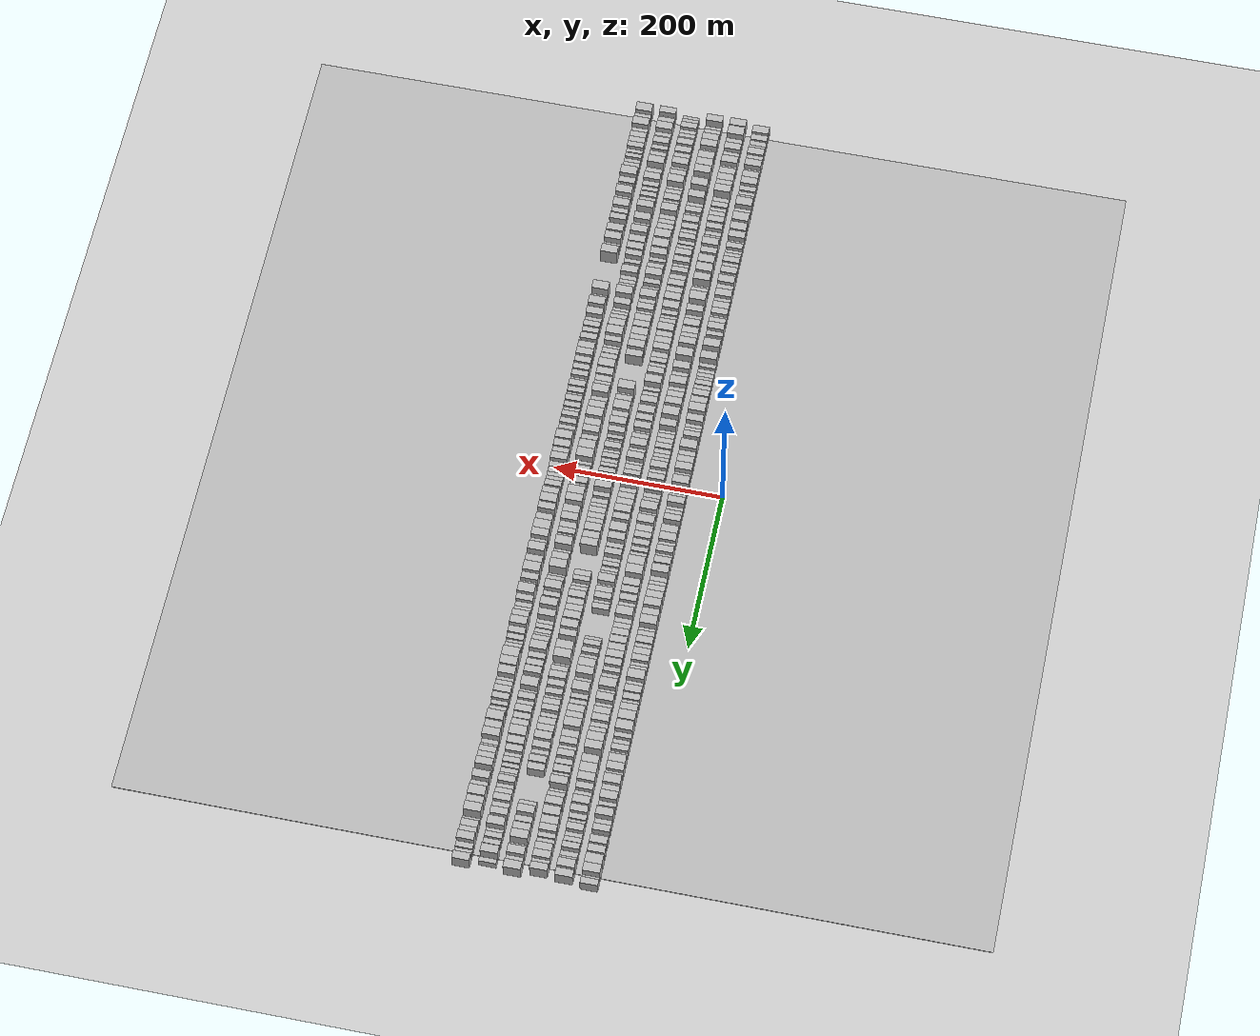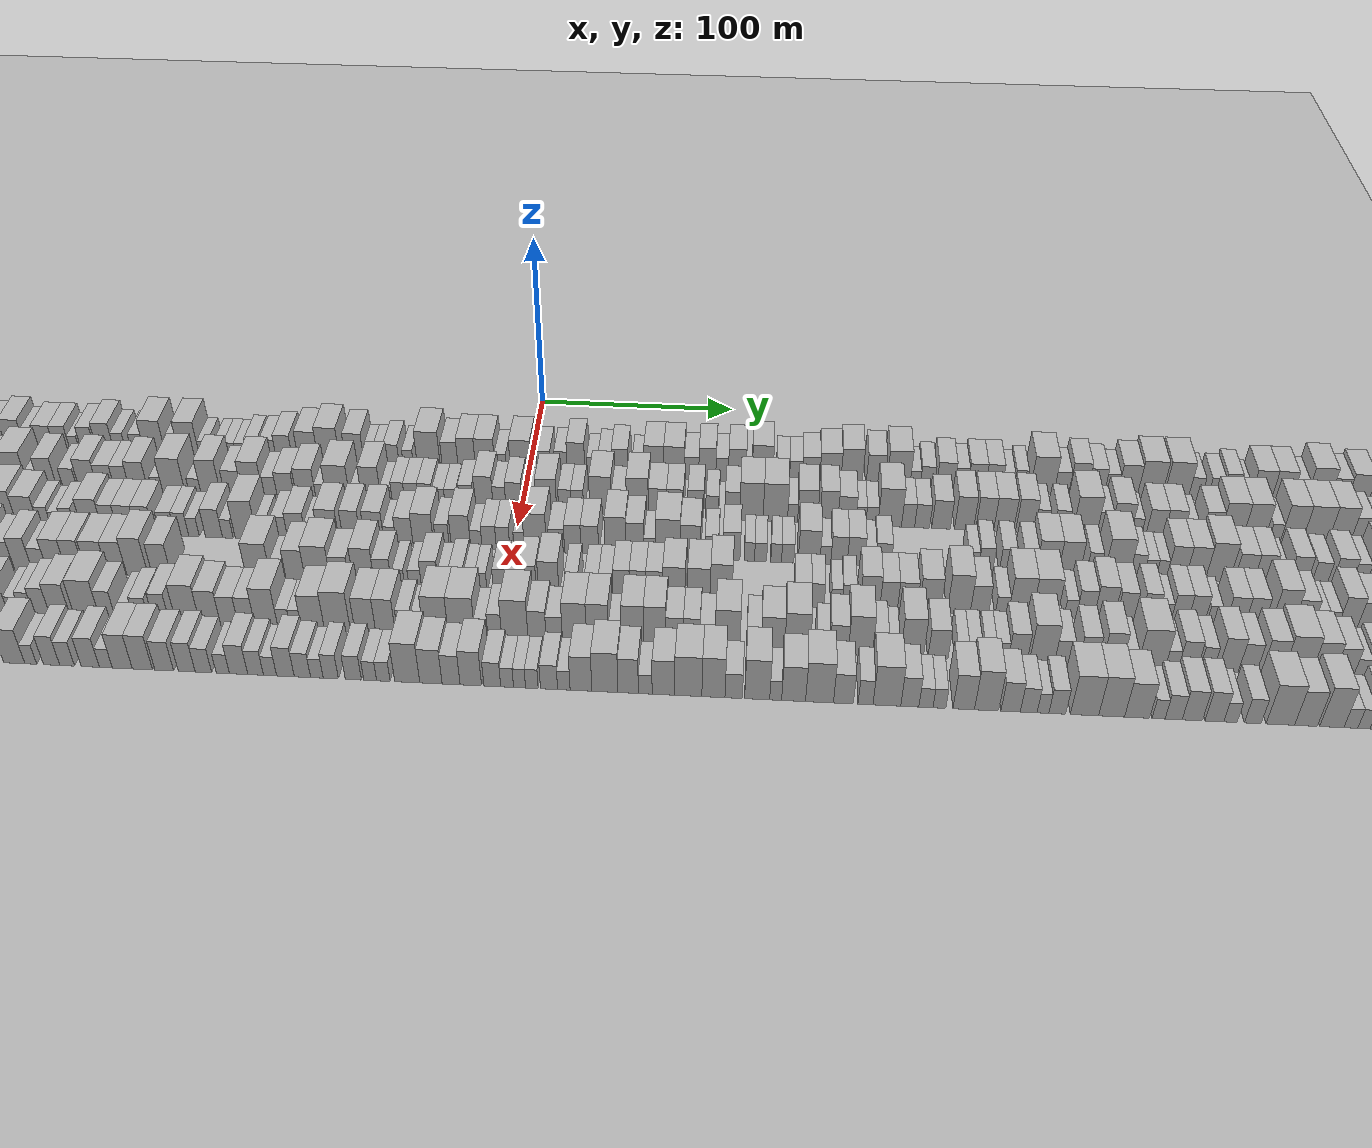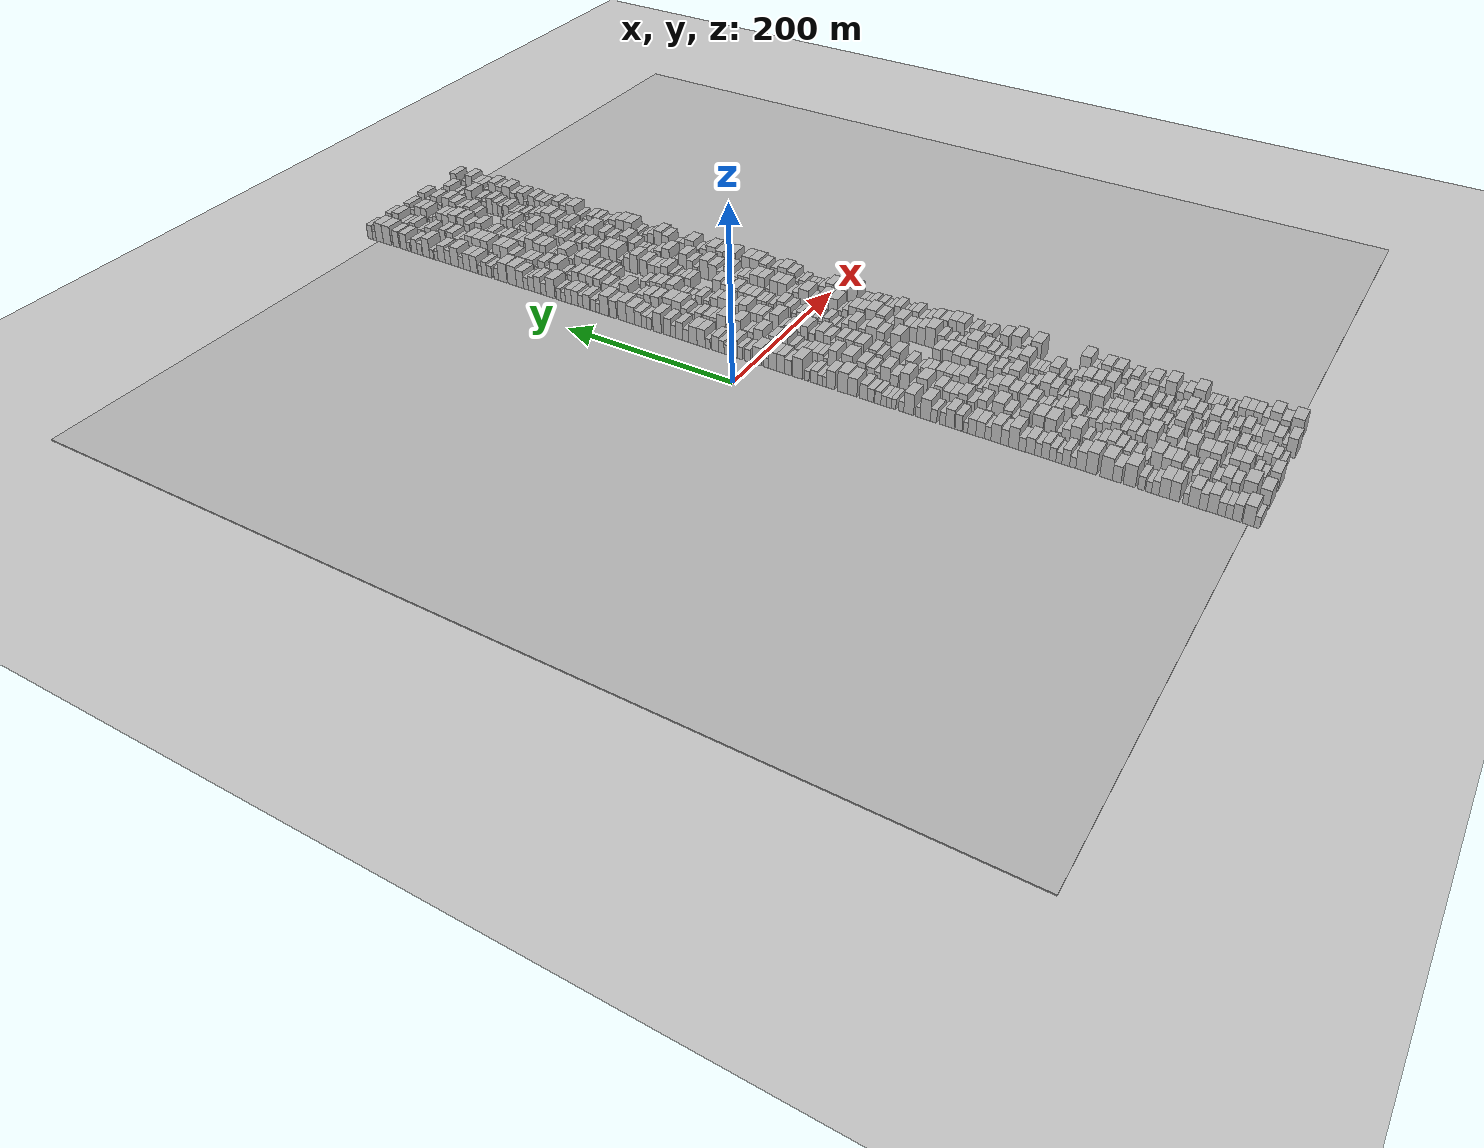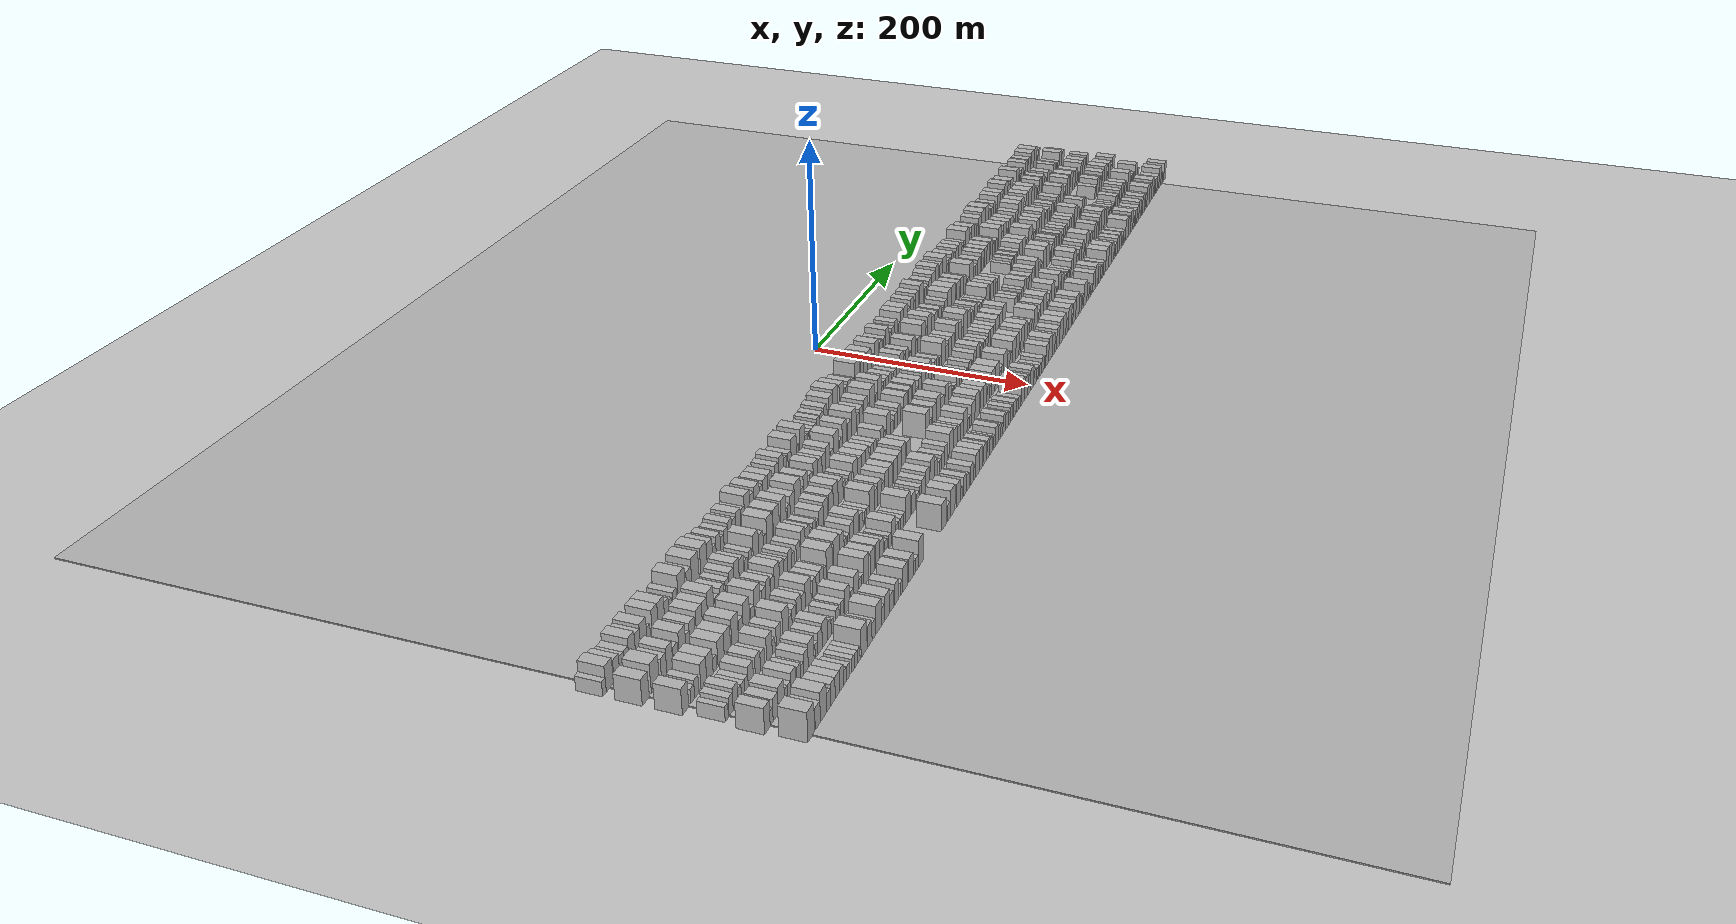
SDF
<?xml version="1.0" encoding="utf-8"?>

<sdf version="1.6">

   <world name="default">

      <gui fullscreen="0">

         <camera name="user_camera">

            <pose>-15 0 4.57585 0 0 0</pose>

            <view_controller>orbit</view_controller>

         </camera>

      </gui>

      <scene>

         <sky>

           <clouds>

             <speed>12</speed>

           </clouds>

         </sky>

         <ambient>0.4 0.4 0.4 1</ambient>

         <background>0.7 0.7 0.7 1</background>

         <shadows>1</shadows>

      </scene>

      <gravity>0 0 -9.8066</gravity>

      <magnetic_field>6e-06 2.3e-05 -4.2e-05</magnetic_field>

      <physics default="0" name="default_physics" type="ode">

         <ode>

            <solver>

               <type>quick</type>

               <iters>10</iters>

               <sor>1.0</sor>

               <use_dynamic_moi_rescaling>0</use_dynamic_moi_rescaling>

            </solver>

            <constraints>

               <cfm>0</cfm>

               <erp>0.2</erp>

               <contact_max_correcting_vel>100</contact_max_correcting_vel>

               <contact_surface_layer>0.001</contact_surface_layer>

            </constraints>

         </ode>

         <max_step_size>0.004</max_step_size>

         <real_time_factor>1</real_time_factor>

         <real_time_update_rate>250</real_time_update_rate>

      </physics>

      <light name="sun" type="directional">

         <cast_shadows>1</cast_shadows>

         <pose>0 0 10 0 0 0</pose>

         <diffuse>0.8 0.8 0.8 1</diffuse>

         <specular>0.2 0.2 0.2 1</specular>

         <attenuation>

            <range>1000</range>

            <constant>0.9</constant>

            <linear>0.01</linear>

            <quadratic>0.001</quadratic>

         </attenuation>

         <direction>-0.5 0.1 -0.9</direction>

      </light>

      <include>

         <name>ground_plane_1</name>

         <uri>model://HANNAS_ground_plane</uri>

         <pose>0 0 0  0 0 0</pose>

      </include>

      <include>

         <name>ground_plane_2</name>

         <uri>model://HANNAS_ground_plane</uri>

         <pose>100 0 0  0 0 0</pose>

      </include>

      <model name="building_1">

         <static>1</static>

         <pose frame="">50.0000 -507.5229 0 0.000000 0.000000 0.000000</pose>

         <link name="link">

            <pose frame="">0 0 6.00 0 0 0</pose>

            <collision name="collision">

               <geometry>

                  <box>

                     <size>20.0000 4.9541 12.0000</size>

                  </box>

               </geometry>

               <max_contacts>10</max_contacts>

               <surface>

                  <contact>

                     <ode/>

                  </contact>

                  <bounce/>

                  <friction>

                     <torsional>

                        <ode/>

                     </torsional>

                     <ode/>

                  </friction>

               </surface>

            </collision>

            <visual name="visual">

               <cast_shadows>0</cast_shadows>

               <geometry>

                  <box>

                     <size>20.0000 4.9541 12.0000</size>

                  </box>

               </geometry>

               <material>

                  <script>

                     <uri>model://HANNAS_wall/materials/scripts</uri>

                     <uri>model://HANNAS_wall/materials/textures</uri>

                     <name>vrc/HANNAS_wall</name>

                  </script>

               </material>

            </visual>

            <self_collide>0</self_collide>

            <enable_wind>0</enable_wind>

            <kinematic>0</kinematic>

         </link>

      </model>

      <model name="building_2">

         <static>1</static>

         <pose frame="">50.0000 -499.9958 0 0.000000 0.000000 0.000000</pose>

         <link name="link">

            <pose frame="">0 0 10.50 0 0 0</pose>

            <collision name="collision">

               <geometry>

                  <box>

                     <size>20.0000 10.1001 21.0000</size>

                  </box>

               </geometry>

               <max_contacts>10</max_contacts>

               <surface>

                  <contact>

                     <ode/>

                  </contact>

                  <bounce/>

                  <friction>

                     <torsional>

                        <ode/>

                     </torsional>

                     <ode/>

                  </friction>

               </surface>

            </collision>

            <visual name="visual">

               <cast_shadows>0</cast_shadows>

               <geometry>

                  <box>

                     <size>20.0000 10.1001 21.0000</size>

                  </box>

               </geometry>

               <material>

                  <script>

                     <uri>model://HANNAS_wall/materials/scripts</uri>

                     <uri>model://HANNAS_wall/materials/textures</uri>

                     <name>vrc/HANNAS_wall</name>

                  </script>

               </material>

            </visual>

            <self_collide>0</self_collide>

            <enable_wind>0</enable_wind>

            <kinematic>0</kinematic>

         </link>

      </model>

      <model name="building_3">

         <static>1</static>

         <pose frame="">50.0000 -489.9650 0 0.000000 0.000000 0.000000</pose>

         <link name="link">

            <pose frame="">0 0 9.00 0 0 0</pose>

            <collision name="collision">

               <geometry>

                  <box>

                     <size>20.0000 7.9614 18.0000</size>

                  </box>

               </geometry>

               <max_contacts>10</max_contacts>

               <surface>

                  <contact>

                     <ode/>

                  </contact>

                  <bounce/>

                  <friction>

                     <torsional>

                        <ode/>

                     </torsional>

                     <ode/>

                  </friction>

               </surface>

            </collision>

            <visual name="visual">

               <cast_shadows>0</cast_shadows>

               <geometry>

                  <box>

                     <size>20.0000 7.9614 18.0000</size>

                  </box>

               </geometry>

               <material>

                  <script>

                     <uri>model://HANNAS_wall/materials/scripts</uri>

                     <uri>model://HANNAS_wall/materials/textures</uri>

                     <name>vrc/HANNAS_wall</name>

                  </script>

               </material>

            </visual>

            <self_collide>0</self_collide>

            <enable_wind>0</enable_wind>

            <kinematic>0</kinematic>

         </link>

      </model>

      <model name="building_4">

         <static>1</static>

         <pose frame="">50.0000 -482.8077 0 0.000000 0.000000 0.000000</pose>

         <link name="link">

            <pose frame="">0 0 7.50 0 0 0</pose>

            <collision name="collision">

               <geometry>

                  <box>

                     <size>20.0000 6.3533 15.0000</size>

                  </box>

               </geometry>

               <max_contacts>10</max_contacts>

               <surface>

                  <contact>

                     <ode/>

                  </contact>

                  <bounce/>

                  <friction>

                     <torsional>

                        <ode/>

                     </torsional>

                     <ode/>

                  </friction>

               </surface>

            </collision>

            <visual name="visual">

               <cast_shadows>0</cast_shadows>

               <geometry>

                  <box>

                     <size>20.0000 6.3533 15.0000</size>

                  </box>

               </geometry>

               <material>

                  <script>

                     <uri>model://HANNAS_wall/materials/scripts</uri>

                     <uri>model://HANNAS_wall/materials/textures</uri>

                     <name>vrc/HANNAS_wall</name>

                  </script>

               </material>

            </visual>

            <self_collide>0</self_collide>

            <enable_wind>0</enable_wind>

            <kinematic>0</kinematic>

         </link>

      </model>

      <model name="building_5">

         <static>1</static>

         <pose frame="">50.0000 -476.1434 0 0.000000 0.000000 0.000000</pose>

         <link name="link">

            <pose frame="">0 0 7.50 0 0 0</pose>

            <collision name="collision">

               <geometry>

                  <box>

                     <size>20.0000 6.9753 15.0000</size>

                  </box>

               </geometry>

               <max_contacts>10</max_contacts>

               <surface>

                  <contact>

                     <ode/>

                  </contact>

                  <bounce/>

                  <friction>

                     <torsional>

                        <ode/>

                     </torsional>

                     <ode/>

                  </friction>

               </surface>

            </collision>

            <visual name="visual">

               <cast_shadows>0</cast_shadows>

               <geometry>

                  <box>

                     <size>20.0000 6.9753 15.0000</size>

                  </box>

               </geometry>

               <material>

                  <script>

                     <uri>model://HANNAS_wall/materials/scripts</uri>

                     <uri>model://HANNAS_wall/materials/textures</uri>

                     <name>vrc/HANNAS_wall</name>

                  </script>

               </material>

            </visual>

            <self_collide>0</self_collide>

            <enable_wind>0</enable_wind>

            <kinematic>0</kinematic>

         </link>

      </model>

      <model name="building_6">

         <static>1</static>

         <pose frame="">50.0000 -468.0025 0 0.000000 0.000000 0.000000</pose>

         <link name="link">

            <pose frame="">0 0 10.50 0 0 0</pose>

            <collision name="collision">

               <geometry>

                  <box>

                     <size>20.0000 9.3064 21.0000</size>

                  </box>

               </geometry>

               <max_contacts>10</max_contacts>

               <surface>

                  <contact>

                     <ode/>

                  </contact>

                  <bounce/>

                  <friction>

                     <torsional>

                        <ode/>

                     </torsional>

                     <ode/>

                  </friction>

               </surface>

            </collision>

            <visual name="visual">

               <cast_shadows>0</cast_shadows>

               <geometry>

                  <box>

                     <size>20.0000 9.3064 21.0000</size>

                  </box>

               </geometry>

               <material>

                  <script>

                     <uri>model://HANNAS_wall/materials/scripts</uri>

                     <uri>model://HANNAS_wall/materials/textures</uri>

                     <name>vrc/HANNAS_wall</name>

                  </script>

               </material>

            </visual>

            <self_collide>0</self_collide>

            <enable_wind>0</enable_wind>

            <kinematic>0</kinematic>

         </link>

      </model>

      <model name="building_7">

         <static>1</static>

         <pose frame="">50.0000 -459.6872 0 0.000000 0.000000 0.000000</pose>

         <link name="link">

            <pose frame="">0 0 9.00 0 0 0</pose>

            <collision name="collision">

               <geometry>

                  <box>

                     <size>20.0000 7.3243 18.0000</size>

                  </box>

               </geometry>

               <max_contacts>10</max_contacts>

               <surface>

                  <contact>

                     <ode/>

                  </contact>

                  <bounce/>

                  <friction>

                     <torsional>

                        <ode/>

                     </torsional>

                     <ode/>

                  </friction>

               </surface>

            </collision>

            <visual name="visual">

               <cast_shadows>0</cast_shadows>

               <geometry>

                  <box>

                     <size>20.0000 7.3243 18.0000</size>

                  </box>

               </geometry>

               <material>

                  <script>

                     <uri>model://HANNAS_wall/materials/scripts</uri>

                     <uri>model://HANNAS_wall/materials/textures</uri>

                     <name>vrc/HANNAS_wall</name>

                  </script>

               </material>

            </visual>

            <self_collide>0</self_collide>

            <enable_wind>0</enable_wind>

            <kinematic>0</kinematic>

         </link>

      </model>

      <model name="building_8">

         <static>1</static>

         <pose frame="">50.0000 -451.2077 0 0.000000 0.000000 0.000000</pose>

         <link name="link">

            <pose frame="">0 0 10.50 0 0 0</pose>

            <collision name="collision">

               <geometry>

                  <box>

                     <size>20.0000 9.6346 21.0000</size>

                  </box>

               </geometry>

               <max_contacts>10</max_contacts>

               <surface>

                  <contact>

                     <ode/>

                  </contact>

                  <bounce/>

                  <friction>

                     <torsional>

                        <ode/>

                     </torsional>

                     <ode/>

                  </friction>

               </surface>

            </collision>

            <visual name="visual">

               <cast_shadows>0</cast_shadows>

               <geometry>

                  <box>

                     <size>20.0000 9.6346 21.0000</size>

                  </box>

               </geometry>

               <material>

                  <script>

                     <uri>model://HANNAS_wall/materials/scripts</uri>

                     <uri>model://HANNAS_wall/materials/textures</uri>

                     <name>vrc/HANNAS_wall</name>

                  </script>

               </material>

            </visual>

            <self_collide>0</self_collide>

            <enable_wind>0</enable_wind>

            <kinematic>0</kinematic>

         </link>

      </model>

      <model name="building_9">

         <static>1</static>

         <pose frame="">50.0000 -443.9438 0 0.000000 0.000000 0.000000</pose>

         <link name="link">

            <pose frame="">0 0 6.00 0 0 0</pose>

            <collision name="collision">

               <geometry>

                  <box>

                     <size>20.0000 4.8932 12.0000</size>

                  </box>

               </geometry>

               <max_contacts>10</max_contacts>

               <surface>

                  <contact>

                     <ode/>

                  </contact>

                  <bounce/>

                  <friction>

                     <torsional>

                        <ode/>

                     </torsional>

                     <ode/>

                  </friction>

               </surface>

            </collision>

            <visual name="visual">

               <cast_shadows>0</cast_shadows>

               <geometry>

                  <box>

                     <size>20.0000 4.8932 12.0000</size>

                  </box>

               </geometry>

               <material>

                  <script>

                     <uri>model://HANNAS_wall/materials/scripts</uri>

                     <uri>model://HANNAS_wall/materials/textures</uri>

                     <name>vrc/HANNAS_wall</name>

                  </script>

               </material>

            </visual>

            <self_collide>0</self_collide>

            <enable_wind>0</enable_wind>

            <kinematic>0</kinematic>

         </link>

      </model>

      <model name="building_10">

         <static>1</static>

         <pose frame="">50.0000 -434.0024 0 0.000000 0.000000 0.000000</pose>

         <link name="link">

            <pose frame="">0 0 10.50 0 0 0</pose>

            <collision name="collision">

               <geometry>

                  <box>

                     <size>20.0000 8.9897 21.0000</size>

                  </box>

               </geometry>

               <max_contacts>10</max_contacts>

               <surface>

                  <contact>

                     <ode/>

                  </contact>

                  <bounce/>

                  <friction>

                     <torsional>

                        <ode/>

                     </torsional>

                     <ode/>

                  </friction>

               </surface>

            </collision>

            <visual name="visual">

               <cast_shadows>0</cast_shadows>

               <geometry>

                  <box>

                     <size>20.0000 8.9897 21.0000</size>

                  </box>

               </geometry>

               <material>

                  <script>

                     <uri>model://HANNAS_wall/materials/scripts</uri>

                     <uri>model://HANNAS_wall/materials/textures</uri>

                     <name>vrc/HANNAS_wall</name>

                  </script>

               </material>

            </visual>

            <self_collide>0</self_collide>

            <enable_wind>0</enable_wind>

            <kinematic>0</kinematic>

         </link>

      </model>

      <model name="building_11">

         <static>1</static>

         <pose frame="">50.0000 -424.7182 0 0.000000 0.000000 0.000000</pose>

         <link name="link">

            <pose frame="">0 0 10.50 0 0 0</pose>

            <collision name="collision">

               <geometry>

                  <box>

                     <size>20.0000 9.5786 21.0000</size>

                  </box>

               </geometry>

               <max_contacts>10</max_contacts>

               <surface>

                  <contact>

                     <ode/>

                  </contact>

                  <bounce/>

                  <friction>

                     <torsional>

                        <ode/>

                     </torsional>

                     <ode/>

                  </friction>

               </surface>

            </collision>

            <visual name="visual">

               <cast_shadows>0</cast_shadows>

               <geometry>

                  <box>

                     <size>20.0000 9.5786 21.0000</size>

                  </box>

               </geometry>

               <material>

                  <script>

                     <uri>model://HANNAS_wall/materials/scripts</uri>

                     <uri>model://HANNAS_wall/materials/textures</uri>

                     <name>vrc/HANNAS_wall</name>

                  </script>

               </material>

            </visual>

            <self_collide>0</self_collide>

            <enable_wind>0</enable_wind>

            <kinematic>0</kinematic>

         </link>

      </model>

      <model name="building_12">

         <static>1</static>

         <pose frame="">50.0000 -416.5650 0 0.000000 0.000000 0.000000</pose>

         <link name="link">

            <pose frame="">0 0 7.50 0 0 0</pose>

            <collision name="collision">

               <geometry>

                  <box>

                     <size>20.0000 6.7279 15.0000</size>

                  </box>

               </geometry>

               <max_contacts>10</max_contacts>

               <surface>

                  <contact>

                     <ode/>

                  </contact>

                  <bounce/>

                  <friction>

                     <torsional>

                        <ode/>

                     </torsional>

                     <ode/>

                  </friction>

               </surface>

            </collision>

            <visual name="visual">

               <cast_shadows>0</cast_shadows>

               <geometry>

                  <box>

                     <size>20.0000 6.7279 15.0000</size>

                  </box>

               </geometry>

               <material>

                  <script>

                     <uri>model://HANNAS_wall/materials/scripts</uri>

                     <uri>model://HANNAS_wall/materials/textures</uri>

                     <name>vrc/HANNAS_wall</name>

                  </script>

               </material>

            </visual>

            <self_collide>0</self_collide>

            <enable_wind>0</enable_wind>

            <kinematic>0</kinematic>

         </link>

      </model>

      <model name="building_13">

         <static>1</static>

         <pose frame="">50.0000 -410.5036 0 0.000000 0.000000 0.000000</pose>

         <link name="link">

            <pose frame="">0 0 6.00 0 0 0</pose>

            <collision name="collision">

               <geometry>

                  <box>

                     <size>20.0000 5.3949 12.0000</size>

                  </box>

               </geometry>

               <max_contacts>10</max_contacts>

               <surface>

                  <contact>

                     <ode/>

                  </contact>

                  <bounce/>

                  <friction>

                     <torsional>

                        <ode/>

                     </torsional>

                     <ode/>

                  </friction>

               </surface>

            </collision>

            <visual name="visual">

               <cast_shadows>0</cast_shadows>

               <geometry>

                  <box>

                     <size>20.0000 5.3949 12.0000</size>

                  </box>

               </geometry>

               <material>

                  <script>

                     <uri>model://HANNAS_wall/materials/scripts</uri>

                     <uri>model://HANNAS_wall/materials/textures</uri>

                     <name>vrc/HANNAS_wall</name>

                  </script>

               </material>

            </visual>

            <self_collide>0</self_collide>

            <enable_wind>0</enable_wind>

            <kinematic>0</kinematic>

         </link>

      </model>

      <model name="building_14">

         <static>1</static>

         <pose frame="">50.0000 -403.6088 0 0.000000 0.000000 0.000000</pose>

         <link name="link">

            <pose frame="">0 0 7.50 0 0 0</pose>

            <collision name="collision">

               <geometry>

                  <box>

                     <size>20.0000 6.3948 15.0000</size>

                  </box>

               </geometry>

               <max_contacts>10</max_contacts>

               <surface>

                  <contact>

                     <ode/>

                  </contact>

                  <bounce/>

                  <friction>

                     <torsional>

                        <ode/>

                     </torsional>

                     <ode/>

                  </friction>

               </surface>

            </collision>

            <visual name="visual">

               <cast_shadows>0</cast_shadows>

               <geometry>

                  <box>

                     <size>20.0000 6.3948 15.0000</size>

                  </box>

               </geometry>

               <material>

                  <script>

                     <uri>model://HANNAS_wall/materials/scripts</uri>

                     <uri>model://HANNAS_wall/materials/textures</uri>

                     <name>vrc/HANNAS_wall</name>

                  </script>

               </material>

            </visual>

            <self_collide>0</self_collide>

            <enable_wind>0</enable_wind>

            <kinematic>0</kinematic>

         </link>

      </model>

      <model name="building_15">

         <static>1</static>

         <pose frame="">50.0000 -392.6902 0 0.000000 0.000000 0.000000</pose>

         <link name="link">

            <pose frame="">0 0 12.00 0 0 0</pose>

            <collision name="collision">

               <geometry>

                  <box>

                     <size>20.0000 11.4423 24.0000</size>

                  </box>

               </geometry>

               <max_contacts>10</max_contacts>

               <surface>

                  <contact>

                     <ode/>

                  </contact>

                  <bounce/>

                  <friction>

                     <torsional>

                        <ode/>

                     </torsional>

                     <ode/>

                  </friction>

               </surface>

            </collision>

            <visual name="visual">

               <cast_shadows>0</cast_shadows>

               <geometry>

                  <box>

                     <size>20.0000 11.4423 24.0000</size>

                  </box>

               </geometry>

               <material>

                  <script>

                     <uri>model://HANNAS_wall/materials/scripts</uri>

                     <uri>model://HANNAS_wall/materials/textures</uri>

                     <name>vrc/HANNAS_wall</name>

                  </script>

               </material>

            </visual>

            <self_collide>0</self_collide>

            <enable_wind>0</enable_wind>

            <kinematic>0</kinematic>

         </link>

      </model>

      <model name="building_16">

         <static>1</static>

         <pose frame="">50.0000 -380.8198 0 0.000000 0.000000 0.000000</pose>

         <link name="link">

            <pose frame="">0 0 9.00 0 0 0</pose>

            <collision name="collision">

               <geometry>

                  <box>

                     <size>20.0000 8.2984 18.0000</size>

                  </box>

               </geometry>

               <max_contacts>10</max_contacts>

               <surface>

                  <contact>

                     <ode/>

                  </contact>

                  <bounce/>

                  <friction>

                     <torsional>

                        <ode/>

                     </torsional>

                     <ode/>

                  </friction>

               </surface>

            </collision>

            <visual name="visual">

               <cast_shadows>0</cast_shadows>

               <geometry>

                  <box>

                     <size>20.0000 8.2984 18.0000</size>

                  </box>

               </geometry>

               <material>

                  <script>

                     <uri>model://HANNAS_wall/materials/scripts</uri>

                     <uri>model://HANNAS_wall/materials/textures</uri>

                     <name>vrc/HANNAS_wall</name>

                  </script>

               </material>

            </visual>

            <self_collide>0</self_collide>

            <enable_wind>0</enable_wind>

            <kinematic>0</kinematic>

         </link>

      </model>

      <model name="building_17">

         <static>1</static>

         <pose frame="">50.0000 -370.8444 0 0.000000 0.000000 0.000000</pose>

         <link name="link">

            <pose frame="">0 0 12.00 0 0 0</pose>

            <collision name="collision">

               <geometry>

                  <box>

                     <size>20.0000 11.6525 24.0000</size>

                  </box>

               </geometry>

               <max_contacts>10</max_contacts>

               <surface>

                  <contact>

                     <ode/>

                  </contact>

                  <bounce/>

                  <friction>

                     <torsional>

                        <ode/>

                     </torsional>

                     <ode/>

                  </friction>

               </surface>

            </collision>

            <visual name="visual">

               <cast_shadows>0</cast_shadows>

               <geometry>

                  <box>

                     <size>20.0000 11.6525 24.0000</size>

                  </box>

               </geometry>

               <material>

                  <script>

                     <uri>model://HANNAS_wall/materials/scripts</uri>

                     <uri>model://HANNAS_wall/materials/textures</uri>

                     <name>vrc/HANNAS_wall</name>

                  </script>

               </material>

            </visual>

            <self_collide>0</self_collide>

            <enable_wind>0</enable_wind>

            <kinematic>0</kinematic>

         </link>

      </model>

      <model name="building_18">

         <static>1</static>

         <pose frame="">50.0000 -356.6442 0 0.000000 0.000000 0.000000</pose>

         <link name="link">

            <pose frame="">0 0 12.00 0 0 0</pose>

            <collision name="collision">

               <geometry>

                  <box>

                     <size>20.0000 10.7479 24.0000</size>

                  </box>

               </geometry>

               <max_contacts>10</max_contacts>

               <surface>

                  <contact>

                     <ode/>

                  </contact>

                  <bounce/>

                  <friction>

                     <torsional>

                        <ode/>

                     </torsional>

                     <ode/>

                  </friction>

               </surface>

            </collision>

            <visual name="visual">

               <cast_shadows>0</cast_shadows>

               <geometry>

                  <box>

                     <size>20.0000 10.7479 24.0000</size>

                  </box>

               </geometry>

               <material>

                  <script>

                     <uri>model://HANNAS_wall/materials/scripts</uri>

                     <uri>model://HANNAS_wall/materials/textures</uri>

                     <name>vrc/HANNAS_wall</name>

                  </script>

               </material>

            </visual>

            <self_collide>0</self_collide>

            <enable_wind>0</enable_wind>

            <kinematic>0</kinematic>

         </link>

      </model>

      <model name="building_19">

         <static>1</static>

         <pose frame="">50.0000 -346.6157 0 0.000000 0.000000 0.000000</pose>

         <link name="link">

            <pose frame="">0 0 10.50 0 0 0</pose>

            <collision name="collision">

               <geometry>

                  <box>

                     <size>20.0000 9.3091 21.0000</size>

                  </box>

               </geometry>

               <max_contacts>10</max_contacts>

               <surface>

                  <contact>

                     <ode/>

                  </contact>

                  <bounce/>

                  <friction>

                     <torsional>

                        <ode/>

                     </torsional>

                     <ode/>

                  </friction>

               </surface>

            </collision>

            <visual name="visual">

               <cast_shadows>0</cast_shadows>

               <geometry>

                  <box>

                     <size>20.0000 9.3091 21.0000</size>

                  </box>

               </geometry>

               <material>

                  <script>

                     <uri>model://HANNAS_wall/materials/scripts</uri>

                     <uri>model://HANNAS_wall/materials/textures</uri>

                     <name>vrc/HANNAS_wall</name>

                  </script>

               </material>

            </visual>

            <self_collide>0</self_collide>

            <enable_wind>0</enable_wind>

            <kinematic>0</kinematic>

         </link>

      </model>

      <model name="building_20">

         <static>1</static>

         <pose frame="">50.0000 -338.9996 0 0.000000 0.000000 0.000000</pose>

         <link name="link">

            <pose frame="">0 0 6.00 0 0 0</pose>

            <collision name="collision">

               <geometry>

                  <box>

                     <size>20.0000 5.9230 12.0000</size>

                  </box>

               </geometry>

               <max_contacts>10</max_contacts>

               <surface>

                  <contact>

                     <ode/>

                  </contact>

                  <bounce/>

                  <friction>

                     <torsional>

                        <ode/>

                     </torsional>

                     <ode/>

                  </friction>

               </surface>

            </collision>

            <visual name="visual">

               <cast_shadows>0</cast_shadows>

               <geometry>

                  <box>

                     <size>20.0000 5.9230 12.0000</size>

                  </box>

               </geometry>

               <material>

                  <script>

                     <uri>model://HANNAS_wall/materials/scripts</uri>

                     <uri>model://HANNAS_wall/materials/textures</uri>

                     <name>vrc/HANNAS_wall</name>

                  </script>

               </material>

            </visual>

            <self_collide>0</self_collide>

            <enable_wind>0</enable_wind>

            <kinematic>0</kinematic>

         </link>

      </model>

      <model name="building_21">

         <static>1</static>

         <pose frame="">50.0000 -332.2379 0 0.000000 0.000000 0.000000</pose>

         <link name="link">

            <pose frame="">0 0 9.00 0 0 0</pose>

            <collision name="collision">

               <geometry>

                  <box>

                     <size>20.0000 7.6003 18.0000</size>

                  </box>

               </geometry>

               <max_contacts>10</max_contacts>

               <surface>

                  <contact>

                     <ode/>

                  </contact>

                  <bounce/>

                  <friction>

                     <torsional>

                        <ode/>

                     </torsional>

                     <ode/>

                  </friction>

               </surface>

            </collision>

            <visual name="visual">

               <cast_shadows>0</cast_shadows>

               <geometry>

                  <box>

                     <size>20.0000 7.6003 18.0000</size>

                  </box>

               </geometry>

               <material>

                  <script>

                     <uri>model://HANNAS_wall/materials/scripts</uri>

                     <uri>model://HANNAS_wall/materials/textures</uri>

                     <name>vrc/HANNAS_wall</name>

                  </script>

               </material>

            </visual>

            <self_collide>0</self_collide>

            <enable_wind>0</enable_wind>

            <kinematic>0</kinematic>

         </link>

      </model>

      <model name="building_22">

         <static>1</static>

         <pose frame="">50.0000 -325.4963 0 0.000000 0.000000 0.000000</pose>

         <link name="link">

            <pose frame="">0 0 6.00 0 0 0</pose>

            <collision name="collision">

               <geometry>

                  <box>

                     <size>20.0000 5.8830 12.0000</size>

                  </box>

               </geometry>

               <max_contacts>10</max_contacts>

               <surface>

                  <contact>

                     <ode/>

                  </contact>

                  <bounce/>

                  <friction>

                     <torsional>

                        <ode/>

                     </torsional>

                     <ode/>

                  </friction>

               </surface>

            </collision>

            <visual name="visual">

               <cast_shadows>0</cast_shadows>

               <geometry>

                  <box>

                     <size>20.0000 5.8830 12.0000</size>

                  </box>

               </geometry>

               <material>

                  <script>

                     <uri>model://HANNAS_wall/materials/scripts</uri>

                     <uri>model://HANNAS_wall/materials/textures</uri>

                     <name>vrc/HANNAS_wall</name>

                  </script>

               </material>

            </visual>

            <self_collide>0</self_collide>

            <enable_wind>0</enable_wind>

            <kinematic>0</kinematic>

         </link>

      </model>

      <model name="building_23">

         <static>1</static>

         <pose frame="">50.0000 -319.2503 0 0.000000 0.000000 0.000000</pose>

         <link name="link">

            <pose frame="">0 0 7.50 0 0 0</pose>

            <collision name="collision">

               <geometry>

                  <box>

                     <size>20.0000 6.6090 15.0000</size>

                  </box>

               </geometry>

               <max_contacts>10</max_contacts>

               <surface>

                  <contact>

                     <ode/>

                  </contact>

                  <bounce/>

                  <friction>

                     <torsional>

                        <ode/>

                     </torsional>

                     <ode/>

                  </friction>

               </surface>

            </collision>

            <visual name="visual">

               <cast_shadows>0</cast_shadows>

               <geometry>

                  <box>

                     <size>20.0000 6.6090 15.0000</size>

                  </box>

               </geometry>

               <material>

                  <script>

                     <uri>model://HANNAS_wall/materials/scripts</uri>

                     <uri>model://HANNAS_wall/materials/textures</uri>

                     <name>vrc/HANNAS_wall</name>

                  </script>

               </material>

            </visual>

            <self_collide>0</self_collide>

            <enable_wind>0</enable_wind>

            <kinematic>0</kinematic>

         </link>

      </model>

      <model name="building_24">

         <static>1</static>

         <pose frame="">50.0000 -312.0720 0 0.000000 0.000000 0.000000</pose>

         <link name="link">

            <pose frame="">0 0 9.00 0 0 0</pose>

            <collision name="collision">

               <geometry>

                  <box>

                     <size>20.0000 7.7476 18.0000</size>

                  </box>

               </geometry>

               <max_contacts>10</max_contacts>

               <surface>

                  <contact>

                     <ode/>

                  </contact>

                  <bounce/>

                  <friction>

                     <torsional>

                        <ode/>

                     </torsional>

                     <ode/>

                  </friction>

               </surface>

            </collision>

            <visual name="visual">

               <cast_shadows>0</cast_shadows>

               <geometry>

                  <box>

                     <size>20.0000 7.7476 18.0000</size>

                  </box>

               </geometry>

               <material>

                  <script>

                     <uri>model://HANNAS_wall/materials/scripts</uri>

                     <uri>model://HANNAS_wall/materials/textures</uri>

                     <name>vrc/HANNAS_wall</name>

                  </script>

               </material>

            </visual>

            <self_collide>0</self_collide>

            <enable_wind>0</enable_wind>

            <kinematic>0</kinematic>

         </link>

      </model>

      <model name="building_25">

         <static>1</static>

         <pose frame="">50.0000 -304.9393 0 0.000000 0.000000 0.000000</pose>

         <link name="link">

            <pose frame="">0 0 7.50 0 0 0</pose>

            <collision name="collision">

               <geometry>

                  <box>

                     <size>20.0000 6.5178 15.0000</size>

                  </box>

               </geometry>

               <max_contacts>10</max_contacts>

               <surface>

                  <contact>

                     <ode/>

                  </contact>

                  <bounce/>

                  <friction>

                     <torsional>

                        <ode/>

                     </torsional>

                     <ode/>

                  </friction>

               </surface>

            </collision>

            <visual name="visual">

               <cast_shadows>0</cast_shadows>

               <geometry>

                  <box>

                     <size>20.0000 6.5178 15.0000</size>

                  </box>

               </geometry>

               <material>

                  <script>

                     <uri>model://HANNAS_wall/materials/scripts</uri>

                     <uri>model://HANNAS_wall/materials/textures</uri>

                     <name>vrc/HANNAS_wall</name>

                  </script>

               </material>

            </visual>

            <self_collide>0</self_collide>

            <enable_wind>0</enable_wind>

            <kinematic>0</kinematic>

         </link>

      </model>

      <model name="building_26">

         <static>1</static>

         <pose frame="">50.0000 -297.2961 0 0.000000 0.000000 0.000000</pose>

         <link name="link">

            <pose frame="">0 0 9.00 0 0 0</pose>

            <collision name="collision">

               <geometry>

                  <box>

                     <size>20.0000 8.7687 18.0000</size>

                  </box>

               </geometry>

               <max_contacts>10</max_contacts>

               <surface>

                  <contact>

                     <ode/>

                  </contact>

                  <bounce/>

                  <friction>

                     <torsional>

                        <ode/>

                     </torsional>

                     <ode/>

                  </friction>

               </surface>

            </collision>

            <visual name="visual">

               <cast_shadows>0</cast_shadows>

               <geometry>

                  <box>

                     <size>20.0000 8.7687 18.0000</size>

                  </box>

               </geometry>

               <material>

                  <script>

                     <uri>model://HANNAS_wall/materials/scripts</uri>

                     <uri>model://HANNAS_wall/materials/textures</uri>

                     <name>vrc/HANNAS_wall</name>

                  </script>

               </material>

            </visual>

            <self_collide>0</self_collide>

            <enable_wind>0</enable_wind>

            <kinematic>0</kinematic>

         </link>

      </model>

      <model name="building_27">

         <static>1</static>

         <pose frame="">50.0000 -289.3078 0 0.000000 0.000000 0.000000</pose>

         <link name="link">

            <pose frame="">0 0 7.50 0 0 0</pose>

            <collision name="collision">

               <geometry>

                  <box>

                     <size>20.0000 7.2079 15.0000</size>

                  </box>

               </geometry>

               <max_contacts>10</max_contacts>

               <surface>

                  <contact>

                     <ode/>

                  </contact>

                  <bounce/>

                  <friction>

                     <torsional>

                        <ode/>

                     </torsional>

                     <ode/>

                  </friction>

               </surface>

            </collision>

            <visual name="visual">

               <cast_shadows>0</cast_shadows>

               <geometry>

                  <box>

                     <size>20.0000 7.2079 15.0000</size>

                  </box>

               </geometry>

               <material>

                  <script>

                     <uri>model://HANNAS_wall/materials/scripts</uri>

                     <uri>model://HANNAS_wall/materials/textures</uri>

                     <name>vrc/HANNAS_wall</name>

                  </script>

               </material>

            </visual>

            <self_collide>0</self_collide>

            <enable_wind>0</enable_wind>

            <kinematic>0</kinematic>

         </link>

      </model>

      <model name="building_28">

         <static>1</static>

         <pose frame="">50.0000 -280.6868 0 0.000000 0.000000 0.000000</pose>

         <link name="link">

            <pose frame="">0 0 12.00 0 0 0</pose>

            <collision name="collision">

               <geometry>

                  <box>

                     <size>20.0000 10.0341 24.0000</size>

                  </box>

               </geometry>

               <max_contacts>10</max_contacts>

               <surface>

                  <contact>

                     <ode/>

                  </contact>

                  <bounce/>

                  <friction>

                     <torsional>

                        <ode/>

                     </torsional>

                     <ode/>

                  </friction>

               </surface>

            </collision>

            <visual name="visual">

               <cast_shadows>0</cast_shadows>

               <geometry>

                  <box>

                     <size>20.0000 10.0341 24.0000</size>

                  </box>

               </geometry>

               <material>

                  <script>

                     <uri>model://HANNAS_wall/materials/scripts</uri>

                     <uri>model://HANNAS_wall/materials/textures</uri>

                     <name>vrc/HANNAS_wall</name>

                  </script>

               </material>

            </visual>

            <self_collide>0</self_collide>

            <enable_wind>0</enable_wind>

            <kinematic>0</kinematic>

         </link>

      </model>

      <model name="building_29">

         <static>1</static>

         <pose frame="">50.0000 -271.7418 0 0.000000 0.000000 0.000000</pose>

         <link name="link">

            <pose frame="">0 0 9.00 0 0 0</pose>

            <collision name="collision">

               <geometry>

                  <box>

                     <size>20.0000 7.8561 18.0000</size>

                  </box>

               </geometry>

               <max_contacts>10</max_contacts>

               <surface>

                  <contact>

                     <ode/>

                  </contact>

                  <bounce/>

                  <friction>

                     <torsional>

                        <ode/>

                     </torsional>

                     <ode/>

                  </friction>

               </surface>

            </collision>

            <visual name="visual">

               <cast_shadows>0</cast_shadows>

               <geometry>

                  <box>

                     <size>20.0000 7.8561 18.0000</size>

                  </box>

               </geometry>

               <material>

                  <script>

                     <uri>model://HANNAS_wall/materials/scripts</uri>

                     <uri>model://HANNAS_wall/materials/textures</uri>

                     <name>vrc/HANNAS_wall</name>

                  </script>

               </material>

            </visual>

            <self_collide>0</self_collide>

            <enable_wind>0</enable_wind>

            <kinematic>0</kinematic>

         </link>

      </model>

      <model name="building_30">

         <static>1</static>

         <pose frame="">50.0000 -262.9113 0 0.000000 0.000000 0.000000</pose>

         <link name="link">

            <pose frame="">0 0 10.50 0 0 0</pose>

            <collision name="collision">

               <geometry>

                  <box>

                     <size>20.0000 9.8049 21.0000</size>

                  </box>

               </geometry>

               <max_contacts>10</max_contacts>

               <surface>

                  <contact>

                     <ode/>

                  </contact>

                  <bounce/>

                  <friction>

                     <torsional>

                        <ode/>

                     </torsional>

                     <ode/>

                  </friction>

               </surface>

            </collision>

            <visual name="visual">

               <cast_shadows>0</cast_shadows>

               <geometry>

                  <box>

                     <size>20.0000 9.8049 21.0000</size>

                  </box>

               </geometry>

               <material>

                  <script>

                     <uri>model://HANNAS_wall/materials/scripts</uri>

                     <uri>model://HANNAS_wall/materials/textures</uri>

                     <name>vrc/HANNAS_wall</name>

                  </script>

               </material>

            </visual>

            <self_collide>0</self_collide>

            <enable_wind>0</enable_wind>

            <kinematic>0</kinematic>

         </link>

      </model>

      <model name="building_31">

         <static>1</static>

         <pose frame="">50.0000 -254.8422 0 0.000000 0.000000 0.000000</pose>

         <link name="link">

            <pose frame="">0 0 7.50 0 0 0</pose>

            <collision name="collision">

               <geometry>

                  <box>

                     <size>20.0000 6.3333 15.0000</size>

                  </box>

               </geometry>

               <max_contacts>10</max_contacts>

               <surface>

                  <contact>

                     <ode/>

                  </contact>

                  <bounce/>

                  <friction>

                     <torsional>

                        <ode/>

                     </torsional>

                     <ode/>

                  </friction>

               </surface>

            </collision>

            <visual name="visual">

               <cast_shadows>0</cast_shadows>

               <geometry>

                  <box>

                     <size>20.0000 6.3333 15.0000</size>

                  </box>

               </geometry>

               <material>

                  <script>

                     <uri>model://HANNAS_wall/materials/scripts</uri>

                     <uri>model://HANNAS_wall/materials/textures</uri>

                     <name>vrc/HANNAS_wall</name>

                  </script>

               </material>

            </visual>

            <self_collide>0</self_collide>

            <enable_wind>0</enable_wind>

            <kinematic>0</kinematic>

         </link>

      </model>

      <model name="building_32">

         <static>1</static>

         <pose frame="">50.0000 -247.1792 0 0.000000 0.000000 0.000000</pose>

         <link name="link">

            <pose frame="">0 0 9.00 0 0 0</pose>

            <collision name="collision">

               <geometry>

                  <box>

                     <size>20.0000 8.9926 18.0000</size>

                  </box>

               </geometry>

               <max_contacts>10</max_contacts>

               <surface>

                  <contact>

                     <ode/>

                  </contact>

                  <bounce/>

                  <friction>

                     <torsional>

                        <ode/>

                     </torsional>

                     <ode/>

                  </friction>

               </surface>

            </collision>

            <visual name="visual">

               <cast_shadows>0</cast_shadows>

               <geometry>

                  <box>

                     <size>20.0000 8.9926 18.0000</size>

                  </box>

               </geometry>

               <material>

                  <script>

                     <uri>model://HANNAS_wall/materials/scripts</uri>

                     <uri>model://HANNAS_wall/materials/textures</uri>

                     <name>vrc/HANNAS_wall</name>

                  </script>

               </material>

            </visual>

            <self_collide>0</self_collide>

            <enable_wind>0</enable_wind>

            <kinematic>0</kinematic>

         </link>

      </model>

      <model name="building_33">

         <static>1</static>

         <pose frame="">50.0000 -238.6051 0 0.000000 0.000000 0.000000</pose>

         <link name="link">

            <pose frame="">0 0 9.00 0 0 0</pose>

            <collision name="collision">

               <geometry>

                  <box>

                     <size>20.0000 8.1556 18.0000</size>

                  </box>

               </geometry>

               <max_contacts>10</max_contacts>

               <surface>

                  <contact>

                     <ode/>

                  </contact>

                  <bounce/>

                  <friction>

                     <torsional>

                        <ode/>

                     </torsional>

                     <ode/>

                  </friction>

               </surface>

            </collision>

            <visual name="visual">

               <cast_shadows>0</cast_shadows>

               <geometry>

                  <box>

                     <size>20.0000 8.1556 18.0000</size>

                  </box>

               </geometry>

               <material>

                  <script>

                     <uri>model://HANNAS_wall/materials/scripts</uri>

                     <uri>model://HANNAS_wall/materials/textures</uri>

                     <name>vrc/HANNAS_wall</name>

                  </script>

               </material>

            </visual>

            <self_collide>0</self_collide>

            <enable_wind>0</enable_wind>

            <kinematic>0</kinematic>

         </link>

      </model>

      <model name="building_34">

         <static>1</static>

         <pose frame="">50.0000 -232.1040 0 0.000000 0.000000 0.000000</pose>

         <link name="link">

            <pose frame="">0 0 6.00 0 0 0</pose>

            <collision name="collision">

               <geometry>

                  <box>

                     <size>20.0000 4.8466 12.0000</size>

                  </box>

               </geometry>

               <max_contacts>10</max_contacts>

               <surface>

                  <contact>

                     <ode/>

                  </contact>

                  <bounce/>

                  <friction>

                     <torsional>

                        <ode/>

                     </torsional>

                     <ode/>

                  </friction>

               </surface>

            </collision>

            <visual name="visual">

               <cast_shadows>0</cast_shadows>

               <geometry>

                  <box>

                     <size>20.0000 4.8466 12.0000</size>

                  </box>

               </geometry>

               <material>

                  <script>

                     <uri>model://HANNAS_wall/materials/scripts</uri>

                     <uri>model://HANNAS_wall/materials/textures</uri>

                     <name>vrc/HANNAS_wall</name>

                  </script>

               </material>

            </visual>

            <self_collide>0</self_collide>

            <enable_wind>0</enable_wind>

            <kinematic>0</kinematic>

         </link>

      </model>

      <model name="building_35">

         <static>1</static>

         <pose frame="">50.0000 -225.0665 0 0.000000 0.000000 0.000000</pose>

         <link name="link">

            <pose frame="">0 0 9.00 0 0 0</pose>

            <collision name="collision">

               <geometry>

                  <box>

                     <size>20.0000 7.2285 18.0000</size>

                  </box>

               </geometry>

               <max_contacts>10</max_contacts>

               <surface>

                  <contact>

                     <ode/>

                  </contact>

                  <bounce/>

                  <friction>

                     <torsional>

                        <ode/>

                     </torsional>

                     <ode/>

                  </friction>

               </surface>

            </collision>

            <visual name="visual">

               <cast_shadows>0</cast_shadows>

               <geometry>

                  <box>

                     <size>20.0000 7.2285 18.0000</size>

                  </box>

               </geometry>

               <material>

                  <script>

                     <uri>model://HANNAS_wall/materials/scripts</uri>

                     <uri>model://HANNAS_wall/materials/textures</uri>

                     <name>vrc/HANNAS_wall</name>

                  </script>

               </material>

            </visual>

            <self_collide>0</self_collide>

            <enable_wind>0</enable_wind>

            <kinematic>0</kinematic>

         </link>

      </model>

      <model name="building_36">

         <static>1</static>

         <pose frame="">50.0000 -215.9780 0 0.000000 0.000000 0.000000</pose>

         <link name="link">

            <pose frame="">0 0 10.50 0 0 0</pose>

            <collision name="collision">

               <geometry>

                  <box>

                     <size>20.0000 8.9484 21.0000</size>

                  </box>

               </geometry>

               <max_contacts>10</max_contacts>

               <surface>

                  <contact>

                     <ode/>

                  </contact>

                  <bounce/>

                  <friction>

                     <torsional>

                        <ode/>

                     </torsional>

                     <ode/>

                  </friction>

               </surface>

            </collision>

            <visual name="visual">

               <cast_shadows>0</cast_shadows>

               <geometry>

                  <box>

                     <size>20.0000 8.9484 21.0000</size>

                  </box>

               </geometry>

               <material>

                  <script>

                     <uri>model://HANNAS_wall/materials/scripts</uri>

                     <uri>model://HANNAS_wall/materials/textures</uri>

                     <name>vrc/HANNAS_wall</name>

                  </script>

               </material>

            </visual>

            <self_collide>0</self_collide>

            <enable_wind>0</enable_wind>

            <kinematic>0</kinematic>

         </link>

      </model>

      <model name="building_37">

         <static>1</static>

         <pose frame="">50.0000 -208.4370 0 0.000000 0.000000 0.000000</pose>

         <link name="link">

            <pose frame="">0 0 7.50 0 0 0</pose>

            <collision name="collision">

               <geometry>

                  <box>

                     <size>20.0000 6.1336 15.0000</size>

                  </box>

               </geometry>

               <max_contacts>10</max_contacts>

               <surface>

                  <contact>

                     <ode/>

                  </contact>

                  <bounce/>

                  <friction>

                     <torsional>

                        <ode/>

                     </torsional>

                     <ode/>

                  </friction>

               </surface>

            </collision>

            <visual name="visual">

               <cast_shadows>0</cast_shadows>

               <geometry>

                  <box>

                     <size>20.0000 6.1336 15.0000</size>

                  </box>

               </geometry>

               <material>

                  <script>

                     <uri>model://HANNAS_wall/materials/scripts</uri>

                     <uri>model://HANNAS_wall/materials/textures</uri>

                     <name>vrc/HANNAS_wall</name>

                  </script>

               </material>

            </visual>

            <self_collide>0</self_collide>

            <enable_wind>0</enable_wind>

            <kinematic>0</kinematic>

         </link>

      </model>

      <model name="building_38">

         <static>1</static>

         <pose frame="">50.0000 -199.1488 0 0.000000 0.000000 0.000000</pose>

         <link name="link">

            <pose frame="">0 0 7.50 0 0 0</pose>

            <collision name="collision">

               <geometry>

                  <box>

                     <size>20.0000 6.4429 15.0000</size>

                  </box>

               </geometry>

               <max_contacts>10</max_contacts>

               <surface>

                  <contact>

                     <ode/>

                  </contact>

                  <bounce/>

                  <friction>

                     <torsional>

                        <ode/>

                     </torsional>

                     <ode/>

                  </friction>

               </surface>

            </collision>

            <visual name="visual">

               <cast_shadows>0</cast_shadows>

               <geometry>

                  <box>

                     <size>20.0000 6.4429 15.0000</size>

                  </box>

               </geometry>

               <material>

                  <script>

                     <uri>model://HANNAS_wall/materials/scripts</uri>

                     <uri>model://HANNAS_wall/materials/textures</uri>

                     <name>vrc/HANNAS_wall</name>

                  </script>

               </material>

            </visual>

            <self_collide>0</self_collide>

            <enable_wind>0</enable_wind>

            <kinematic>0</kinematic>

         </link>

      </model>

      <model name="building_39">

         <static>1</static>

         <pose frame="">50.0000 -190.4903 0 0.000000 0.000000 0.000000</pose>

         <link name="link">

            <pose frame="">0 0 12.00 0 0 0</pose>

            <collision name="collision">

               <geometry>

                  <box>

                     <size>20.0000 10.8740 24.0000</size>

                  </box>

               </geometry>

               <max_contacts>10</max_contacts>

               <surface>

                  <contact>

                     <ode/>

                  </contact>

                  <bounce/>

                  <friction>

                     <torsional>

                        <ode/>

                     </torsional>

                     <ode/>

                  </friction>

               </surface>

            </collision>

            <visual name="visual">

               <cast_shadows>0</cast_shadows>

               <geometry>

                  <box>

                     <size>20.0000 10.8740 24.0000</size>

                  </box>

               </geometry>

               <material>

                  <script>

                     <uri>model://HANNAS_wall/materials/scripts</uri>

                     <uri>model://HANNAS_wall/materials/textures</uri>

                     <name>vrc/HANNAS_wall</name>

                  </script>

               </material>

            </visual>

            <self_collide>0</self_collide>

            <enable_wind>0</enable_wind>

            <kinematic>0</kinematic>

         </link>

      </model>

      <model name="building_40">

         <static>1</static>

         <pose frame="">50.0000 -182.5998 0 0.000000 0.000000 0.000000</pose>

         <link name="link">

            <pose frame="">0 0 6.00 0 0 0</pose>

            <collision name="collision">

               <geometry>

                  <box>

                     <size>20.0000 4.9071 12.0000</size>

                  </box>

               </geometry>

               <max_contacts>10</max_contacts>

               <surface>

                  <contact>

                     <ode/>

                  </contact>

                  <bounce/>

                  <friction>

                     <torsional>

                        <ode/>

                     </torsional>

                     <ode/>

                  </friction>

               </surface>

            </collision>

            <visual name="visual">

               <cast_shadows>0</cast_shadows>

               <geometry>

                  <box>

                     <size>20.0000 4.9071 12.0000</size>

                  </box>

               </geometry>

               <material>

                  <script>

                     <uri>model://HANNAS_wall/materials/scripts</uri>

                     <uri>model://HANNAS_wall/materials/textures</uri>

                     <name>vrc/HANNAS_wall</name>

                  </script>

               </material>

            </visual>

            <self_collide>0</self_collide>

            <enable_wind>0</enable_wind>

            <kinematic>0</kinematic>

         </link>

      </model>

      <model name="building_41">

         <static>1</static>

         <pose frame="">50.0000 -172.8865 0 0.000000 0.000000 0.000000</pose>

         <link name="link">

            <pose frame="">0 0 12.00 0 0 0</pose>

            <collision name="collision">

               <geometry>

                  <box>

                     <size>20.0000 10.5195 24.0000</size>

                  </box>

               </geometry>

               <max_contacts>10</max_contacts>

               <surface>

                  <contact>

                     <ode/>

                  </contact>

                  <bounce/>

                  <friction>

                     <torsional>

                        <ode/>

                     </torsional>

                     <ode/>

                  </friction>

               </surface>

            </collision>

            <visual name="visual">

               <cast_shadows>0</cast_shadows>

               <geometry>

                  <box>

                     <size>20.0000 10.5195 24.0000</size>

                  </box>

               </geometry>

               <material>

                  <script>

                     <uri>model://HANNAS_wall/materials/scripts</uri>

                     <uri>model://HANNAS_wall/materials/textures</uri>

                     <name>vrc/HANNAS_wall</name>

                  </script>

               </material>

            </visual>

            <self_collide>0</self_collide>

            <enable_wind>0</enable_wind>

            <kinematic>0</kinematic>

         </link>

      </model>

      <model name="building_42">

         <static>1</static>

         <pose frame="">50.0000 -164.8700 0 0.000000 0.000000 0.000000</pose>

         <link name="link">

            <pose frame="">0 0 6.00 0 0 0</pose>

            <collision name="collision">

               <geometry>

                  <box>

                     <size>20.0000 5.5135 12.0000</size>

                  </box>

               </geometry>

               <max_contacts>10</max_contacts>

               <surface>

                  <contact>

                     <ode/>

                  </contact>

                  <bounce/>

                  <friction>

                     <torsional>

                        <ode/>

                     </torsional>

                     <ode/>

                  </friction>

               </surface>

            </collision>

            <visual name="visual">

               <cast_shadows>0</cast_shadows>

               <geometry>

                  <box>

                     <size>20.0000 5.5135 12.0000</size>

                  </box>

               </geometry>

               <material>

                  <script>

                     <uri>model://HANNAS_wall/materials/scripts</uri>

                     <uri>model://HANNAS_wall/materials/textures</uri>

                     <name>vrc/HANNAS_wall</name>

                  </script>

               </material>

            </visual>

            <self_collide>0</self_collide>

            <enable_wind>0</enable_wind>

            <kinematic>0</kinematic>

         </link>

      </model>

      <model name="building_43">

         <static>1</static>

         <pose frame="">50.0000 -156.6176 0 0.000000 0.000000 0.000000</pose>

         <link name="link">

            <pose frame="">0 0 6.00 0 0 0</pose>

            <collision name="collision">

               <geometry>

                  <box>

                     <size>20.0000 4.9913 12.0000</size>

                  </box>

               </geometry>

               <max_contacts>10</max_contacts>

               <surface>

                  <contact>

                     <ode/>

                  </contact>

                  <bounce/>

                  <friction>

                     <torsional>

                        <ode/>

                     </torsional>

                     <ode/>

                  </friction>

               </surface>

            </collision>

            <visual name="visual">

               <cast_shadows>0</cast_shadows>

               <geometry>

                  <box>

                     <size>20.0000 4.9913 12.0000</size>

                  </box>

               </geometry>

               <material>

                  <script>

                     <uri>model://HANNAS_wall/materials/scripts</uri>

                     <uri>model://HANNAS_wall/materials/textures</uri>

                     <name>vrc/HANNAS_wall</name>

                  </script>

               </material>

            </visual>

            <self_collide>0</self_collide>

            <enable_wind>0</enable_wind>

            <kinematic>0</kinematic>

         </link>

      </model>

      <model name="building_44">

         <static>1</static>

         <pose frame="">50.0000 -151.4181 0 0.000000 0.000000 0.000000</pose>

         <link name="link">

            <pose frame="">0 0 6.00 0 0 0</pose>

            <collision name="collision">

               <geometry>

                  <box>

                     <size>20.0000 5.4078 12.0000</size>

                  </box>

               </geometry>

               <max_contacts>10</max_contacts>

               <surface>

                  <contact>

                     <ode/>

                  </contact>

                  <bounce/>

                  <friction>

                     <torsional>

                        <ode/>

                     </torsional>

                     <ode/>

                  </friction>

               </surface>

            </collision>

            <visual name="visual">

               <cast_shadows>0</cast_shadows>

               <geometry>

                  <box>

                     <size>20.0000 5.4078 12.0000</size>

                  </box>

               </geometry>

               <material>

                  <script>

                     <uri>model://HANNAS_wall/materials/scripts</uri>

                     <uri>model://HANNAS_wall/materials/textures</uri>

                     <name>vrc/HANNAS_wall</name>

                  </script>

               </material>

            </visual>

            <self_collide>0</self_collide>

            <enable_wind>0</enable_wind>

            <kinematic>0</kinematic>

         </link>

      </model>

      <model name="building_45">

         <static>1</static>

         <pose frame="">50.0000 -145.8629 0 0.000000 0.000000 0.000000</pose>

         <link name="link">

            <pose frame="">0 0 6.00 0 0 0</pose>

            <collision name="collision">

               <geometry>

                  <box>

                     <size>20.0000 5.7026 12.0000</size>

                  </box>

               </geometry>

               <max_contacts>10</max_contacts>

               <surface>

                  <contact>

                     <ode/>

                  </contact>

                  <bounce/>

                  <friction>

                     <torsional>

                        <ode/>

                     </torsional>

                     <ode/>

                  </friction>

               </surface>

            </collision>

            <visual name="visual">

               <cast_shadows>0</cast_shadows>

               <geometry>

                  <box>

                     <size>20.0000 5.7026 12.0000</size>

                  </box>

               </geometry>

               <material>

                  <script>

                     <uri>model://HANNAS_wall/materials/scripts</uri>

                     <uri>model://HANNAS_wall/materials/textures</uri>

                     <name>vrc/HANNAS_wall</name>

                  </script>

               </material>

            </visual>

            <self_collide>0</self_collide>

            <enable_wind>0</enable_wind>

            <kinematic>0</kinematic>

         </link>

      </model>

      <model name="building_46">

         <static>1</static>

         <pose frame="">50.0000 -139.6931 0 0.000000 0.000000 0.000000</pose>

         <link name="link">

            <pose frame="">0 0 7.50 0 0 0</pose>

            <collision name="collision">

               <geometry>

                  <box>

                     <size>20.0000 6.6368 15.0000</size>

                  </box>

               </geometry>

               <max_contacts>10</max_contacts>

               <surface>

                  <contact>

                     <ode/>

                  </contact>

                  <bounce/>

                  <friction>

                     <torsional>

                        <ode/>

                     </torsional>

                     <ode/>

                  </friction>

               </surface>

            </collision>

            <visual name="visual">

               <cast_shadows>0</cast_shadows>

               <geometry>

                  <box>

                     <size>20.0000 6.6368 15.0000</size>

                  </box>

               </geometry>

               <material>

                  <script>

                     <uri>model://HANNAS_wall/materials/scripts</uri>

                     <uri>model://HANNAS_wall/materials/textures</uri>

                     <name>vrc/HANNAS_wall</name>

                  </script>

               </material>

            </visual>

            <self_collide>0</self_collide>

            <enable_wind>0</enable_wind>

            <kinematic>0</kinematic>

         </link>

      </model>

      <model name="building_47">

         <static>1</static>

         <pose frame="">50.0000 -131.7682 0 0.000000 0.000000 0.000000</pose>

         <link name="link">

            <pose frame="">0 0 7.50 0 0 0</pose>

            <collision name="collision">

               <geometry>

                  <box>

                     <size>20.0000 7.2129 15.0000</size>

                  </box>

               </geometry>

               <max_contacts>10</max_contacts>

               <surface>

                  <contact>

                     <ode/>

                  </contact>

                  <bounce/>

                  <friction>

                     <torsional>

                        <ode/>

                     </torsional>

                     <ode/>

                  </friction>

               </surface>

            </collision>

            <visual name="visual">

               <cast_shadows>0</cast_shadows>

               <geometry>

                  <box>

                     <size>20.0000 7.2129 15.0000</size>

                  </box>

               </geometry>

               <material>

                  <script>

                     <uri>model://HANNAS_wall/materials/scripts</uri>

                     <uri>model://HANNAS_wall/materials/textures</uri>

                     <name>vrc/HANNAS_wall</name>

                  </script>

               </material>

            </visual>

            <self_collide>0</self_collide>

            <enable_wind>0</enable_wind>

            <kinematic>0</kinematic>

         </link>

      </model>

      <model name="building_48">

         <static>1</static>

         <pose frame="">50.0000 -124.0262 0 0.000000 0.000000 0.000000</pose>

         <link name="link">

            <pose frame="">0 0 9.00 0 0 0</pose>

            <collision name="collision">

               <geometry>

                  <box>

                     <size>20.0000 8.2712 18.0000</size>

                  </box>

               </geometry>

               <max_contacts>10</max_contacts>

               <surface>

                  <contact>

                     <ode/>

                  </contact>

                  <bounce/>

                  <friction>

                     <torsional>

                        <ode/>

                     </torsional>

                     <ode/>

                  </friction>

               </surface>

            </collision>

            <visual name="visual">

               <cast_shadows>0</cast_shadows>

               <geometry>

                  <box>

                     <size>20.0000 8.2712 18.0000</size>

                  </box>

               </geometry>

               <material>

                  <script>

                     <uri>model://HANNAS_wall/materials/scripts</uri>

                     <uri>model://HANNAS_wall/materials/textures</uri>

                     <name>vrc/HANNAS_wall</name>

                  </script>

               </material>

            </visual>

            <self_collide>0</self_collide>

            <enable_wind>0</enable_wind>

            <kinematic>0</kinematic>

         </link>

      </model>

      <model name="building_49">

         <static>1</static>

         <pose frame="">50.0000 -111.7854 0 0.000000 0.000000 0.000000</pose>

         <link name="link">

            <pose frame="">0 0 10.50 0 0 0</pose>

            <collision name="collision">

               <geometry>

                  <box>

                     <size>20.0000 10.2104 21.0000</size>

                  </box>

               </geometry>

               <max_contacts>10</max_contacts>

               <surface>

                  <contact>

                     <ode/>

                  </contact>

                  <bounce/>

                  <friction>

                     <torsional>

                        <ode/>

                     </torsional>

                     <ode/>

                  </friction>

               </surface>

            </collision>

            <visual name="visual">

               <cast_shadows>0</cast_shadows>

               <geometry>

                  <box>

                     <size>20.0000 10.2104 21.0000</size>

                  </box>

               </geometry>

               <material>

                  <script>

                     <uri>model://HANNAS_wall/materials/scripts</uri>

                     <uri>model://HANNAS_wall/materials/textures</uri>

                     <name>vrc/HANNAS_wall</name>

                  </script>

               </material>

            </visual>

            <self_collide>0</self_collide>

            <enable_wind>0</enable_wind>

            <kinematic>0</kinematic>

         </link>

      </model>

      <model name="building_50">

         <static>1</static>

         <pose frame="">50.0000 -101.1382 0 0.000000 0.000000 0.000000</pose>

         <link name="link">

            <pose frame="">0 0 12.00 0 0 0</pose>

            <collision name="collision">

               <geometry>

                  <box>

                     <size>20.0000 11.0839 24.0000</size>

                  </box>

               </geometry>

               <max_contacts>10</max_contacts>

               <surface>

                  <contact>

                     <ode/>

                  </contact>

                  <bounce/>

                  <friction>

                     <torsional>

                        <ode/>

                     </torsional>

                     <ode/>

                  </friction>

               </surface>

            </collision>

            <visual name="visual">

               <cast_shadows>0</cast_shadows>

               <geometry>

                  <box>

                     <size>20.0000 11.0839 24.0000</size>

                  </box>

               </geometry>

               <material>

                  <script>

                     <uri>model://HANNAS_wall/materials/scripts</uri>

                     <uri>model://HANNAS_wall/materials/textures</uri>

                     <name>vrc/HANNAS_wall</name>

                  </script>

               </material>

            </visual>

            <self_collide>0</self_collide>

            <enable_wind>0</enable_wind>

            <kinematic>0</kinematic>

         </link>

      </model>

      <model name="building_51">

         <static>1</static>

         <pose frame="">50.0000 -87.9250 0 0.000000 0.000000 0.000000</pose>

         <link name="link">

            <pose frame="">0 0 10.50 0 0 0</pose>

            <collision name="collision">

               <geometry>

                  <box>

                     <size>20.0000 9.3427 21.0000</size>

                  </box>

               </geometry>

               <max_contacts>10</max_contacts>

               <surface>

                  <contact>

                     <ode/>

                  </contact>

                  <bounce/>

                  <friction>

                     <torsional>

                        <ode/>

                     </torsional>

                     <ode/>

                  </friction>

               </surface>

            </collision>

            <visual name="visual">

               <cast_shadows>0</cast_shadows>

               <geometry>

                  <box>

                     <size>20.0000 9.3427 21.0000</size>

                  </box>

               </geometry>

               <material>

                  <script>

                     <uri>model://HANNAS_wall/materials/scripts</uri>

                     <uri>model://HANNAS_wall/materials/textures</uri>

                     <name>vrc/HANNAS_wall</name>

                  </script>

               </material>

            </visual>

            <self_collide>0</self_collide>

            <enable_wind>0</enable_wind>

            <kinematic>0</kinematic>

         </link>

      </model>

      <model name="building_52">

         <static>1</static>

         <pose frame="">50.0000 -80.8383 0 0.000000 0.000000 0.000000</pose>

         <link name="link">

            <pose frame="">0 0 6.00 0 0 0</pose>

            <collision name="collision">

               <geometry>

                  <box>

                     <size>20.0000 4.8306 12.0000</size>

                  </box>

               </geometry>

               <max_contacts>10</max_contacts>

               <surface>

                  <contact>

                     <ode/>

                  </contact>

                  <bounce/>

                  <friction>

                     <torsional>

                        <ode/>

                     </torsional>

                     <ode/>

                  </friction>

               </surface>

            </collision>

            <visual name="visual">

               <cast_shadows>0</cast_shadows>

               <geometry>

                  <box>

                     <size>20.0000 4.8306 12.0000</size>

                  </box>

               </geometry>

               <material>

                  <script>

                     <uri>model://HANNAS_wall/materials/scripts</uri>

                     <uri>model://HANNAS_wall/materials/textures</uri>

                     <name>vrc/HANNAS_wall</name>

                  </script>

               </material>

            </visual>

            <self_collide>0</self_collide>

            <enable_wind>0</enable_wind>

            <kinematic>0</kinematic>

         </link>

      </model>

      <model name="building_53">

         <static>1</static>

         <pose frame="">50.0000 -75.5484 0 0.000000 0.000000 0.000000</pose>

         <link name="link">

            <pose frame="">0 0 6.00 0 0 0</pose>

            <collision name="collision">

               <geometry>

                  <box>

                     <size>20.0000 5.7492 12.0000</size>

                  </box>

               </geometry>

               <max_contacts>10</max_contacts>

               <surface>

                  <contact>

                     <ode/>

                  </contact>

                  <bounce/>

                  <friction>

                     <torsional>

                        <ode/>

                     </torsional>

                     <ode/>

                  </friction>

               </surface>

            </collision>

            <visual name="visual">

               <cast_shadows>0</cast_shadows>

               <geometry>

                  <box>

                     <size>20.0000 5.7492 12.0000</size>

                  </box>

               </geometry>

               <material>

                  <script>

                     <uri>model://HANNAS_wall/materials/scripts</uri>

                     <uri>model://HANNAS_wall/materials/textures</uri>

                     <name>vrc/HANNAS_wall</name>

                  </script>

               </material>

            </visual>

            <self_collide>0</self_collide>

            <enable_wind>0</enable_wind>

            <kinematic>0</kinematic>

         </link>

      </model>

      <model name="building_54">

         <static>1</static>

         <pose frame="">50.0000 -69.0643 0 0.000000 0.000000 0.000000</pose>

         <link name="link">

            <pose frame="">0 0 7.50 0 0 0</pose>

            <collision name="collision">

               <geometry>

                  <box>

                     <size>20.0000 7.2192 15.0000</size>

                  </box>

               </geometry>

               <max_contacts>10</max_contacts>

               <surface>

                  <contact>

                     <ode/>

                  </contact>

                  <bounce/>

                  <friction>

                     <torsional>

                        <ode/>

                     </torsional>

                     <ode/>

                  </friction>

               </surface>

            </collision>

            <visual name="visual">

               <cast_shadows>0</cast_shadows>

               <geometry>

                  <box>

                     <size>20.0000 7.2192 15.0000</size>

                  </box>

               </geometry>

               <material>

                  <script>

                     <uri>model://HANNAS_wall/materials/scripts</uri>

                     <uri>model://HANNAS_wall/materials/textures</uri>

                     <name>vrc/HANNAS_wall</name>

                  </script>

               </material>

            </visual>

            <self_collide>0</self_collide>

            <enable_wind>0</enable_wind>

            <kinematic>0</kinematic>

         </link>

      </model>

      <model name="building_55">

         <static>1</static>

         <pose frame="">50.0000 -60.8685 0 0.000000 0.000000 0.000000</pose>

         <link name="link">

            <pose frame="">0 0 6.00 0 0 0</pose>

            <collision name="collision">

               <geometry>

                  <box>

                     <size>20.0000 5.1723 12.0000</size>

                  </box>

               </geometry>

               <max_contacts>10</max_contacts>

               <surface>

                  <contact>

                     <ode/>

                  </contact>

                  <bounce/>

                  <friction>

                     <torsional>

                        <ode/>

                     </torsional>

                     <ode/>

                  </friction>

               </surface>

            </collision>

            <visual name="visual">

               <cast_shadows>0</cast_shadows>

               <geometry>

                  <box>

                     <size>20.0000 5.1723 12.0000</size>

                  </box>

               </geometry>

               <material>

                  <script>

                     <uri>model://HANNAS_wall/materials/scripts</uri>

                     <uri>model://HANNAS_wall/materials/textures</uri>

                     <name>vrc/HANNAS_wall</name>

                  </script>

               </material>

            </visual>

            <self_collide>0</self_collide>

            <enable_wind>0</enable_wind>

            <kinematic>0</kinematic>

         </link>

      </model>

      <model name="building_56">

         <static>1</static>

         <pose frame="">50.0000 -50.4555 0 0.000000 0.000000 0.000000</pose>

         <link name="link">

            <pose frame="">0 0 12.00 0 0 0</pose>

            <collision name="collision">

               <geometry>

                  <box>

                     <size>20.0000 11.6537 24.0000</size>

                  </box>

               </geometry>

               <max_contacts>10</max_contacts>

               <surface>

                  <contact>

                     <ode/>

                  </contact>

                  <bounce/>

                  <friction>

                     <torsional>

                        <ode/>

                     </torsional>

                     <ode/>

                  </friction>

               </surface>

            </collision>

            <visual name="visual">

               <cast_shadows>0</cast_shadows>

               <geometry>

                  <box>

                     <size>20.0000 11.6537 24.0000</size>

                  </box>

               </geometry>

               <material>

                  <script>

                     <uri>model://HANNAS_wall/materials/scripts</uri>

                     <uri>model://HANNAS_wall/materials/textures</uri>

                     <name>vrc/HANNAS_wall</name>

                  </script>

               </material>

            </visual>

            <self_collide>0</self_collide>

            <enable_wind>0</enable_wind>

            <kinematic>0</kinematic>

         </link>

      </model>

      <model name="building_57">

         <static>1</static>

         <pose frame="">50.0000 -39.6158 0 0.000000 0.000000 0.000000</pose>

         <link name="link">

            <pose frame="">0 0 9.00 0 0 0</pose>

            <collision name="collision">

               <geometry>

                  <box>

                     <size>20.0000 8.0258 18.0000</size>

                  </box>

               </geometry>

               <max_contacts>10</max_contacts>

               <surface>

                  <contact>

                     <ode/>

                  </contact>

                  <bounce/>

                  <friction>

                     <torsional>

                        <ode/>

                     </torsional>

                     <ode/>

                  </friction>

               </surface>

            </collision>

            <visual name="visual">

               <cast_shadows>0</cast_shadows>

               <geometry>

                  <box>

                     <size>20.0000 8.0258 18.0000</size>

                  </box>

               </geometry>

               <material>

                  <script>

                     <uri>model://HANNAS_wall/materials/scripts</uri>

                     <uri>model://HANNAS_wall/materials/textures</uri>

                     <name>vrc/HANNAS_wall</name>

                  </script>

               </material>

            </visual>

            <self_collide>0</self_collide>

            <enable_wind>0</enable_wind>

            <kinematic>0</kinematic>

         </link>

      </model>

      <model name="building_58">

         <static>1</static>

         <pose frame="">50.0000 -31.1986 0 0.000000 0.000000 0.000000</pose>

         <link name="link">

            <pose frame="">0 0 10.50 0 0 0</pose>

            <collision name="collision">

               <geometry>

                  <box>

                     <size>20.0000 8.8084 21.0000</size>

                  </box>

               </geometry>

               <max_contacts>10</max_contacts>

               <surface>

                  <contact>

                     <ode/>

                  </contact>

                  <bounce/>

                  <friction>

                     <torsional>

                        <ode/>

                     </torsional>

                     <ode/>

                  </friction>

               </surface>

            </collision>

            <visual name="visual">

               <cast_shadows>0</cast_shadows>

               <geometry>

                  <box>

                     <size>20.0000 8.8084 21.0000</size>

                  </box>

               </geometry>

               <material>

                  <script>

                     <uri>model://HANNAS_wall/materials/scripts</uri>

                     <uri>model://HANNAS_wall/materials/textures</uri>

                     <name>vrc/HANNAS_wall</name>

                  </script>

               </material>

            </visual>

            <self_collide>0</self_collide>

            <enable_wind>0</enable_wind>

            <kinematic>0</kinematic>

         </link>

      </model>

      <model name="building_59">

         <static>1</static>

         <pose frame="">50.0000 -21.8745 0 0.000000 0.000000 0.000000</pose>

         <link name="link">

            <pose frame="">0 0 10.50 0 0 0</pose>

            <collision name="collision">

               <geometry>

                  <box>

                     <size>20.0000 9.8399 21.0000</size>

                  </box>

               </geometry>

               <max_contacts>10</max_contacts>

               <surface>

                  <contact>

                     <ode/>

                  </contact>

                  <bounce/>

                  <friction>

                     <torsional>

                        <ode/>

                     </torsional>

                     <ode/>

                  </friction>

               </surface>

            </collision>

            <visual name="visual">

               <cast_shadows>0</cast_shadows>

               <geometry>

                  <box>

                     <size>20.0000 9.8399 21.0000</size>

                  </box>

               </geometry>

               <material>

                  <script>

                     <uri>model://HANNAS_wall/materials/scripts</uri>

                     <uri>model://HANNAS_wall/materials/textures</uri>

                     <name>vrc/HANNAS_wall</name>

                  </script>

               </material>

            </visual>

            <self_collide>0</self_collide>

            <enable_wind>0</enable_wind>

            <kinematic>0</kinematic>

         </link>

      </model>

      <model name="building_60">

         <static>1</static>

         <pose frame="">50.0000 -14.0506 0 0.000000 0.000000 0.000000</pose>

         <link name="link">

            <pose frame="">0 0 6.00 0 0 0</pose>

            <collision name="collision">

               <geometry>

                  <box>

                     <size>20.0000 5.8078 12.0000</size>

                  </box>

               </geometry>

               <max_contacts>10</max_contacts>

               <surface>

                  <contact>

                     <ode/>

                  </contact>

                  <bounce/>

                  <friction>

                     <torsional>

                        <ode/>

                     </torsional>

                     <ode/>

                  </friction>

               </surface>

            </collision>

            <visual name="visual">

               <cast_shadows>0</cast_shadows>

               <geometry>

                  <box>

                     <size>20.0000 5.8078 12.0000</size>

                  </box>

               </geometry>

               <material>

                  <script>

                     <uri>model://HANNAS_wall/materials/scripts</uri>

                     <uri>model://HANNAS_wall/materials/textures</uri>

                     <name>vrc/HANNAS_wall</name>

                  </script>

               </material>

            </visual>

            <self_collide>0</self_collide>

            <enable_wind>0</enable_wind>

            <kinematic>0</kinematic>

         </link>

      </model>

      <model name="building_61">

         <static>1</static>

         <pose frame="">50.0000 -3.9010 0 0.000000 0.000000 0.000000</pose>

         <link name="link">

            <pose frame="">0 0 10.50 0 0 0</pose>

            <collision name="collision">

               <geometry>

                  <box>

                     <size>20.0000 10.4915 21.0000</size>

                  </box>

               </geometry>

               <max_contacts>10</max_contacts>

               <surface>

                  <contact>

                     <ode/>

                  </contact>

                  <bounce/>

                  <friction>

                     <torsional>

                        <ode/>

                     </torsional>

                     <ode/>

                  </friction>

               </surface>

            </collision>

            <visual name="visual">

               <cast_shadows>0</cast_shadows>

               <geometry>

                  <box>

                     <size>20.0000 10.4915 21.0000</size>

                  </box>

               </geometry>

               <material>

                  <script>

                     <uri>model://HANNAS_wall/materials/scripts</uri>

                     <uri>model://HANNAS_wall/materials/textures</uri>

                     <name>vrc/HANNAS_wall</name>

                  </script>

               </material>

            </visual>

            <self_collide>0</self_collide>

            <enable_wind>0</enable_wind>

            <kinematic>0</kinematic>

         </link>

      </model>

      <model name="building_62">

         <static>1</static>

         <pose frame="">50.0000 7.7243 0 0.000000 0.000000 0.000000</pose>

         <link name="link">

            <pose frame="">0 0 7.50 0 0 0</pose>

            <collision name="collision">

               <geometry>

                  <box>

                     <size>20.0000 6.7590 15.0000</size>

                  </box>

               </geometry>

               <max_contacts>10</max_contacts>

               <surface>

                  <contact>

                     <ode/>

                  </contact>

                  <bounce/>

                  <friction>

                     <torsional>

                        <ode/>

                     </torsional>

                     <ode/>

                  </friction>

               </surface>

            </collision>

            <visual name="visual">

               <cast_shadows>0</cast_shadows>

               <geometry>

                  <box>

                     <size>20.0000 6.7590 15.0000</size>

                  </box>

               </geometry>

               <material>

                  <script>

                     <uri>model://HANNAS_wall/materials/scripts</uri>

                     <uri>model://HANNAS_wall/materials/textures</uri>

                     <name>vrc/HANNAS_wall</name>

                  </script>

               </material>

            </visual>

            <self_collide>0</self_collide>

            <enable_wind>0</enable_wind>

            <kinematic>0</kinematic>

         </link>

      </model>

      <model name="building_63">

         <static>1</static>

         <pose frame="">50.0000 16.3060 0 0.000000 0.000000 0.000000</pose>

         <link name="link">

            <pose frame="">0 0 7.50 0 0 0</pose>

            <collision name="collision">

               <geometry>

                  <box>

                     <size>20.0000 6.4045 15.0000</size>

                  </box>

               </geometry>

               <max_contacts>10</max_contacts>

               <surface>

                  <contact>

                     <ode/>

                  </contact>

                  <bounce/>

                  <friction>

                     <torsional>

                        <ode/>

                     </torsional>

                     <ode/>

                  </friction>

               </surface>

            </collision>

            <visual name="visual">

               <cast_shadows>0</cast_shadows>

               <geometry>

                  <box>

                     <size>20.0000 6.4045 15.0000</size>

                  </box>

               </geometry>

               <material>

                  <script>

                     <uri>model://HANNAS_wall/materials/scripts</uri>

                     <uri>model://HANNAS_wall/materials/textures</uri>

                     <name>vrc/HANNAS_wall</name>

                  </script>

               </material>

            </visual>

            <self_collide>0</self_collide>

            <enable_wind>0</enable_wind>

            <kinematic>0</kinematic>

         </link>

      </model>

      <model name="building_64">

         <static>1</static>

         <pose frame="">50.0000 23.9120 0 0.000000 0.000000 0.000000</pose>

         <link name="link">

            <pose frame="">0 0 10.50 0 0 0</pose>

            <collision name="collision">

               <geometry>

                  <box>

                     <size>20.0000 8.8074 21.0000</size>

                  </box>

               </geometry>

               <max_contacts>10</max_contacts>

               <surface>

                  <contact>

                     <ode/>

                  </contact>

                  <bounce/>

                  <friction>

                     <torsional>

                        <ode/>

                     </torsional>

                     <ode/>

                  </friction>

               </surface>

            </collision>

            <visual name="visual">

               <cast_shadows>0</cast_shadows>

               <geometry>

                  <box>

                     <size>20.0000 8.8074 21.0000</size>

                  </box>

               </geometry>

               <material>

                  <script>

                     <uri>model://HANNAS_wall/materials/scripts</uri>

                     <uri>model://HANNAS_wall/materials/textures</uri>

                     <name>vrc/HANNAS_wall</name>

                  </script>

               </material>

            </visual>

            <self_collide>0</self_collide>

            <enable_wind>0</enable_wind>

            <kinematic>0</kinematic>

         </link>

      </model>

      <model name="building_65">

         <static>1</static>

         <pose frame="">50.0000 32.2796 0 0.000000 0.000000 0.000000</pose>

         <link name="link">

            <pose frame="">0 0 6.00 0 0 0</pose>

            <collision name="collision">

               <geometry>

                  <box>

                     <size>20.0000 5.9279 12.0000</size>

                  </box>

               </geometry>

               <max_contacts>10</max_contacts>

               <surface>

                  <contact>

                     <ode/>

                  </contact>

                  <bounce/>

                  <friction>

                     <torsional>

                        <ode/>

                     </torsional>

                     <ode/>

                  </friction>

               </surface>

            </collision>

            <visual name="visual">

               <cast_shadows>0</cast_shadows>

               <geometry>

                  <box>

                     <size>20.0000 5.9279 12.0000</size>

                  </box>

               </geometry>

               <material>

                  <script>

                     <uri>model://HANNAS_wall/materials/scripts</uri>

                     <uri>model://HANNAS_wall/materials/textures</uri>

                     <name>vrc/HANNAS_wall</name>

                  </script>

               </material>

            </visual>

            <self_collide>0</self_collide>

            <enable_wind>0</enable_wind>

            <kinematic>0</kinematic>

         </link>

      </model>

      <model name="building_66">

         <static>1</static>

         <pose frame="">50.0000 38.5099 0 0.000000 0.000000 0.000000</pose>

         <link name="link">

            <pose frame="">0 0 7.50 0 0 0</pose>

            <collision name="collision">

               <geometry>

                  <box>

                     <size>20.0000 6.5327 15.0000</size>

                  </box>

               </geometry>

               <max_contacts>10</max_contacts>

               <surface>

                  <contact>

                     <ode/>

                  </contact>

                  <bounce/>

                  <friction>

                     <torsional>

                        <ode/>

                     </torsional>

                     <ode/>

                  </friction>

               </surface>

            </collision>

            <visual name="visual">

               <cast_shadows>0</cast_shadows>

               <geometry>

                  <box>

                     <size>20.0000 6.5327 15.0000</size>

                  </box>

               </geometry>

               <material>

                  <script>

                     <uri>model://HANNAS_wall/materials/scripts</uri>

                     <uri>model://HANNAS_wall/materials/textures</uri>

                     <name>vrc/HANNAS_wall</name>

                  </script>

               </material>

            </visual>

            <self_collide>0</self_collide>

            <enable_wind>0</enable_wind>

            <kinematic>0</kinematic>

         </link>

      </model>

      <model name="building_67">

         <static>1</static>

         <pose frame="">50.0000 45.8884 0 0.000000 0.000000 0.000000</pose>

         <link name="link">

            <pose frame="">0 0 9.00 0 0 0</pose>

            <collision name="collision">

               <geometry>

                  <box>

                     <size>20.0000 8.2241 18.0000</size>

                  </box>

               </geometry>

               <max_contacts>10</max_contacts>

               <surface>

                  <contact>

                     <ode/>

                  </contact>

                  <bounce/>

                  <friction>

                     <torsional>

                        <ode/>

                     </torsional>

                     <ode/>

                  </friction>

               </surface>

            </collision>

            <visual name="visual">

               <cast_shadows>0</cast_shadows>

               <geometry>

                  <box>

                     <size>20.0000 8.2241 18.0000</size>

                  </box>

               </geometry>

               <material>

                  <script>

                     <uri>model://HANNAS_wall/materials/scripts</uri>

                     <uri>model://HANNAS_wall/materials/textures</uri>

                     <name>vrc/HANNAS_wall</name>

                  </script>

               </material>

            </visual>

            <self_collide>0</self_collide>

            <enable_wind>0</enable_wind>

            <kinematic>0</kinematic>

         </link>

      </model>

      <model name="building_68">

         <static>1</static>

         <pose frame="">50.0000 54.9763 0 0.000000 0.000000 0.000000</pose>

         <link name="link">

            <pose frame="">0 0 6.00 0 0 0</pose>

            <collision name="collision">

               <geometry>

                  <box>

                     <size>20.0000 5.9517 12.0000</size>

                  </box>

               </geometry>

               <max_contacts>10</max_contacts>

               <surface>

                  <contact>

                     <ode/>

                  </contact>

                  <bounce/>

                  <friction>

                     <torsional>

                        <ode/>

                     </torsional>

                     <ode/>

                  </friction>

               </surface>

            </collision>

            <visual name="visual">

               <cast_shadows>0</cast_shadows>

               <geometry>

                  <box>

                     <size>20.0000 5.9517 12.0000</size>

                  </box>

               </geometry>

               <material>

                  <script>

                     <uri>model://HANNAS_wall/materials/scripts</uri>

                     <uri>model://HANNAS_wall/materials/textures</uri>

                     <name>vrc/HANNAS_wall</name>

                  </script>

               </material>

            </visual>

            <self_collide>0</self_collide>

            <enable_wind>0</enable_wind>

            <kinematic>0</kinematic>

         </link>

      </model>

      <model name="building_69">

         <static>1</static>

         <pose frame="">50.0000 62.8694 0 0.000000 0.000000 0.000000</pose>

         <link name="link">

            <pose frame="">0 0 10.50 0 0 0</pose>

            <collision name="collision">

               <geometry>

                  <box>

                     <size>20.0000 9.8346 21.0000</size>

                  </box>

               </geometry>

               <max_contacts>10</max_contacts>

               <surface>

                  <contact>

                     <ode/>

                  </contact>

                  <bounce/>

                  <friction>

                     <torsional>

                        <ode/>

                     </torsional>

                     <ode/>

                  </friction>

               </surface>

            </collision>

            <visual name="visual">

               <cast_shadows>0</cast_shadows>

               <geometry>

                  <box>

                     <size>20.0000 9.8346 21.0000</size>

                  </box>

               </geometry>

               <material>

                  <script>

                     <uri>model://HANNAS_wall/materials/scripts</uri>

                     <uri>model://HANNAS_wall/materials/textures</uri>

                     <name>vrc/HANNAS_wall</name>

                  </script>

               </material>

            </visual>

            <self_collide>0</self_collide>

            <enable_wind>0</enable_wind>

            <kinematic>0</kinematic>

         </link>

      </model>

      <model name="building_70">

         <static>1</static>

         <pose frame="">50.0000 72.9231 0 0.000000 0.000000 0.000000</pose>

         <link name="link">

            <pose frame="">0 0 10.50 0 0 0</pose>

            <collision name="collision">

               <geometry>

                  <box>

                     <size>20.0000 10.2727 21.0000</size>

                  </box>

               </geometry>

               <max_contacts>10</max_contacts>

               <surface>

                  <contact>

                     <ode/>

                  </contact>

                  <bounce/>

                  <friction>

                     <torsional>

                        <ode/>

                     </torsional>

                     <ode/>

                  </friction>

               </surface>

            </collision>

            <visual name="visual">

               <cast_shadows>0</cast_shadows>

               <geometry>

                  <box>

                     <size>20.0000 10.2727 21.0000</size>

                  </box>

               </geometry>

               <material>

                  <script>

                     <uri>model://HANNAS_wall/materials/scripts</uri>

                     <uri>model://HANNAS_wall/materials/textures</uri>

                     <name>vrc/HANNAS_wall</name>

                  </script>

               </material>

            </visual>

            <self_collide>0</self_collide>

            <enable_wind>0</enable_wind>

            <kinematic>0</kinematic>

         </link>

      </model>

      <model name="building_71">

         <static>1</static>

         <pose frame="">50.0000 81.6971 0 0.000000 0.000000 0.000000</pose>

         <link name="link">

            <pose frame="">0 0 7.50 0 0 0</pose>

            <collision name="collision">

               <geometry>

                  <box>

                     <size>20.0000 7.2754 15.0000</size>

                  </box>

               </geometry>

               <max_contacts>10</max_contacts>

               <surface>

                  <contact>

                     <ode/>

                  </contact>

                  <bounce/>

                  <friction>

                     <torsional>

                        <ode/>

                     </torsional>

                     <ode/>

                  </friction>

               </surface>

            </collision>

            <visual name="visual">

               <cast_shadows>0</cast_shadows>

               <geometry>

                  <box>

                     <size>20.0000 7.2754 15.0000</size>

                  </box>

               </geometry>

               <material>

                  <script>

                     <uri>model://HANNAS_wall/materials/scripts</uri>

                     <uri>model://HANNAS_wall/materials/textures</uri>

                     <name>vrc/HANNAS_wall</name>

                  </script>

               </material>

            </visual>

            <self_collide>0</self_collide>

            <enable_wind>0</enable_wind>

            <kinematic>0</kinematic>

         </link>

      </model>

      <model name="building_72">

         <static>1</static>

         <pose frame="">50.0000 89.5781 0 0.000000 0.000000 0.000000</pose>

         <link name="link">

            <pose frame="">0 0 10.50 0 0 0</pose>

            <collision name="collision">

               <geometry>

                  <box>

                     <size>20.0000 8.4865 21.0000</size>

                  </box>

               </geometry>

               <max_contacts>10</max_contacts>

               <surface>

                  <contact>

                     <ode/>

                  </contact>

                  <bounce/>

                  <friction>

                     <torsional>

                        <ode/>

                     </torsional>

                     <ode/>

                  </friction>

               </surface>

            </collision>

            <visual name="visual">

               <cast_shadows>0</cast_shadows>

               <geometry>

                  <box>

                     <size>20.0000 8.4865 21.0000</size>

                  </box>

               </geometry>

               <material>

                  <script>

                     <uri>model://HANNAS_wall/materials/scripts</uri>

                     <uri>model://HANNAS_wall/materials/textures</uri>

                     <name>vrc/HANNAS_wall</name>

                  </script>

               </material>

            </visual>

            <self_collide>0</self_collide>

            <enable_wind>0</enable_wind>

            <kinematic>0</kinematic>

         </link>

      </model>

      <model name="building_73">

         <static>1</static>

         <pose frame="">50.0000 96.9267 0 0.000000 0.000000 0.000000</pose>

         <link name="link">

            <pose frame="">0 0 7.50 0 0 0</pose>

            <collision name="collision">

               <geometry>

                  <box>

                     <size>20.0000 6.2108 15.0000</size>

                  </box>

               </geometry>

               <max_contacts>10</max_contacts>

               <surface>

                  <contact>

                     <ode/>

                  </contact>

                  <bounce/>

                  <friction>

                     <torsional>

                        <ode/>

                     </torsional>

                     <ode/>

                  </friction>

               </surface>

            </collision>

            <visual name="visual">

               <cast_shadows>0</cast_shadows>

               <geometry>

                  <box>

                     <size>20.0000 6.2108 15.0000</size>

                  </box>

               </geometry>

               <material>

                  <script>

                     <uri>model://HANNAS_wall/materials/scripts</uri>

                     <uri>model://HANNAS_wall/materials/textures</uri>

                     <name>vrc/HANNAS_wall</name>

                  </script>

               </material>

            </visual>

            <self_collide>0</self_collide>

            <enable_wind>0</enable_wind>

            <kinematic>0</kinematic>

         </link>

      </model>

      <model name="building_74">

         <static>1</static>

         <pose frame="">50.0000 104.3939 0 0.000000 0.000000 0.000000</pose>

         <link name="link">

            <pose frame="">0 0 10.50 0 0 0</pose>

            <collision name="collision">

               <geometry>

                  <box>

                     <size>20.0000 8.7235 21.0000</size>

                  </box>

               </geometry>

               <max_contacts>10</max_contacts>

               <surface>

                  <contact>

                     <ode/>

                  </contact>

                  <bounce/>

                  <friction>

                     <torsional>

                        <ode/>

                     </torsional>

                     <ode/>

                  </friction>

               </surface>

            </collision>

            <visual name="visual">

               <cast_shadows>0</cast_shadows>

               <geometry>

                  <box>

                     <size>20.0000 8.7235 21.0000</size>

                  </box>

               </geometry>

               <material>

                  <script>

                     <uri>model://HANNAS_wall/materials/scripts</uri>

                     <uri>model://HANNAS_wall/materials/textures</uri>

                     <name>vrc/HANNAS_wall</name>

                  </script>

               </material>

            </visual>

            <self_collide>0</self_collide>

            <enable_wind>0</enable_wind>

            <kinematic>0</kinematic>

         </link>

      </model>

      <model name="building_75">

         <static>1</static>

         <pose frame="">50.0000 116.9098 0 0.000000 0.000000 0.000000</pose>

         <link name="link">

            <pose frame="">0 0 12.00 0 0 0</pose>

            <collision name="collision">

               <geometry>

                  <box>

                     <size>20.0000 10.3083 24.0000</size>

                  </box>

               </geometry>

               <max_contacts>10</max_contacts>

               <surface>

                  <contact>

                     <ode/>

                  </contact>

                  <bounce/>

                  <friction>

                     <torsional>

                        <ode/>

                     </torsional>

                     <ode/>

                  </friction>

               </surface>

            </collision>

            <visual name="visual">

               <cast_shadows>0</cast_shadows>

               <geometry>

                  <box>

                     <size>20.0000 10.3083 24.0000</size>

                  </box>

               </geometry>

               <material>

                  <script>

                     <uri>model://HANNAS_wall/materials/scripts</uri>

                     <uri>model://HANNAS_wall/materials/textures</uri>

                     <name>vrc/HANNAS_wall</name>

                  </script>

               </material>

            </visual>

            <self_collide>0</self_collide>

            <enable_wind>0</enable_wind>

            <kinematic>0</kinematic>

         </link>

      </model>

      <model name="building_76">

         <static>1</static>

         <pose frame="">50.0000 127.2077 0 0.000000 0.000000 0.000000</pose>

         <link name="link">

            <pose frame="">0 0 7.50 0 0 0</pose>

            <collision name="collision">

               <geometry>

                  <box>

                     <size>20.0000 6.2875 15.0000</size>

                  </box>

               </geometry>

               <max_contacts>10</max_contacts>

               <surface>

                  <contact>

                     <ode/>

                  </contact>

                  <bounce/>

                  <friction>

                     <torsional>

                        <ode/>

                     </torsional>

                     <ode/>

                  </friction>

               </surface>

            </collision>

            <visual name="visual">

               <cast_shadows>0</cast_shadows>

               <geometry>

                  <box>

                     <size>20.0000 6.2875 15.0000</size>

                  </box>

               </geometry>

               <material>

                  <script>

                     <uri>model://HANNAS_wall/materials/scripts</uri>

                     <uri>model://HANNAS_wall/materials/textures</uri>

                     <name>vrc/HANNAS_wall</name>

                  </script>

               </material>

            </visual>

            <self_collide>0</self_collide>

            <enable_wind>0</enable_wind>

            <kinematic>0</kinematic>

         </link>

      </model>

      <model name="building_77">

         <static>1</static>

         <pose frame="">50.0000 133.4709 0 0.000000 0.000000 0.000000</pose>

         <link name="link">

            <pose frame="">0 0 7.50 0 0 0</pose>

            <collision name="collision">

               <geometry>

                  <box>

                     <size>20.0000 6.2390 15.0000</size>

                  </box>

               </geometry>

               <max_contacts>10</max_contacts>

               <surface>

                  <contact>

                     <ode/>

                  </contact>

                  <bounce/>

                  <friction>

                     <torsional>

                        <ode/>

                     </torsional>

                     <ode/>

                  </friction>

               </surface>

            </collision>

            <visual name="visual">

               <cast_shadows>0</cast_shadows>

               <geometry>

                  <box>

                     <size>20.0000 6.2390 15.0000</size>

                  </box>

               </geometry>

               <material>

                  <script>

                     <uri>model://HANNAS_wall/materials/scripts</uri>

                     <uri>model://HANNAS_wall/materials/textures</uri>

                     <name>vrc/HANNAS_wall</name>

                  </script>

               </material>

            </visual>

            <self_collide>0</self_collide>

            <enable_wind>0</enable_wind>

            <kinematic>0</kinematic>

         </link>

      </model>

      <model name="building_78">

         <static>1</static>

         <pose frame="">50.0000 140.9445 0 0.000000 0.000000 0.000000</pose>

         <link name="link">

            <pose frame="">0 0 9.00 0 0 0</pose>

            <collision name="collision">

               <geometry>

                  <box>

                     <size>20.0000 8.7082 18.0000</size>

                  </box>

               </geometry>

               <max_contacts>10</max_contacts>

               <surface>

                  <contact>

                     <ode/>

                  </contact>

                  <bounce/>

                  <friction>

                     <torsional>

                        <ode/>

                     </torsional>

                     <ode/>

                  </friction>

               </surface>

            </collision>

            <visual name="visual">

               <cast_shadows>0</cast_shadows>

               <geometry>

                  <box>

                     <size>20.0000 8.7082 18.0000</size>

                  </box>

               </geometry>

               <material>

                  <script>

                     <uri>model://HANNAS_wall/materials/scripts</uri>

                     <uri>model://HANNAS_wall/materials/textures</uri>

                     <name>vrc/HANNAS_wall</name>

                  </script>

               </material>

            </visual>

            <self_collide>0</self_collide>

            <enable_wind>0</enable_wind>

            <kinematic>0</kinematic>

         </link>

      </model>

      <model name="building_79">

         <static>1</static>

         <pose frame="">50.0000 150.5302 0 0.000000 0.000000 0.000000</pose>

         <link name="link">

            <pose frame="">0 0 10.50 0 0 0</pose>

            <collision name="collision">

               <geometry>

                  <box>

                     <size>20.0000 10.4632 21.0000</size>

                  </box>

               </geometry>

               <max_contacts>10</max_contacts>

               <surface>

                  <contact>

                     <ode/>

                  </contact>

                  <bounce/>

                  <friction>

                     <torsional>

                        <ode/>

                     </torsional>

                     <ode/>

                  </friction>

               </surface>

            </collision>

            <visual name="visual">

               <cast_shadows>0</cast_shadows>

               <geometry>

                  <box>

                     <size>20.0000 10.4632 21.0000</size>

                  </box>

               </geometry>

               <material>

                  <script>

                     <uri>model://HANNAS_wall/materials/scripts</uri>

                     <uri>model://HANNAS_wall/materials/textures</uri>

                     <name>vrc/HANNAS_wall</name>

                  </script>

               </material>

            </visual>

            <self_collide>0</self_collide>

            <enable_wind>0</enable_wind>

            <kinematic>0</kinematic>

         </link>

      </model>

      <model name="building_80">

         <static>1</static>

         <pose frame="">50.0000 161.0523 0 0.000000 0.000000 0.000000</pose>

         <link name="link">

            <pose frame="">0 0 12.00 0 0 0</pose>

            <collision name="collision">

               <geometry>

                  <box>

                     <size>20.0000 10.5809 24.0000</size>

                  </box>

               </geometry>

               <max_contacts>10</max_contacts>

               <surface>

                  <contact>

                     <ode/>

                  </contact>

                  <bounce/>

                  <friction>

                     <torsional>

                        <ode/>

                     </torsional>

                     <ode/>

                  </friction>

               </surface>

            </collision>

            <visual name="visual">

               <cast_shadows>0</cast_shadows>

               <geometry>

                  <box>

                     <size>20.0000 10.5809 24.0000</size>

                  </box>

               </geometry>

               <material>

                  <script>

                     <uri>model://HANNAS_wall/materials/scripts</uri>

                     <uri>model://HANNAS_wall/materials/textures</uri>

                     <name>vrc/HANNAS_wall</name>

                  </script>

               </material>

            </visual>

            <self_collide>0</self_collide>

            <enable_wind>0</enable_wind>

            <kinematic>0</kinematic>

         </link>

      </model>

      <model name="building_81">

         <static>1</static>

         <pose frame="">50.0000 172.9133 0 0.000000 0.000000 0.000000</pose>

         <link name="link">

            <pose frame="">0 0 10.50 0 0 0</pose>

            <collision name="collision">

               <geometry>

                  <box>

                     <size>20.0000 9.1411 21.0000</size>

                  </box>

               </geometry>

               <max_contacts>10</max_contacts>

               <surface>

                  <contact>

                     <ode/>

                  </contact>

                  <bounce/>

                  <friction>

                     <torsional>

                        <ode/>

                     </torsional>

                     <ode/>

                  </friction>

               </surface>

            </collision>

            <visual name="visual">

               <cast_shadows>0</cast_shadows>

               <geometry>

                  <box>

                     <size>20.0000 9.1411 21.0000</size>

                  </box>

               </geometry>

               <material>

                  <script>

                     <uri>model://HANNAS_wall/materials/scripts</uri>

                     <uri>model://HANNAS_wall/materials/textures</uri>

                     <name>vrc/HANNAS_wall</name>

                  </script>

               </material>

            </visual>

            <self_collide>0</self_collide>

            <enable_wind>0</enable_wind>

            <kinematic>0</kinematic>

         </link>

      </model>

      <model name="building_82">

         <static>1</static>

         <pose frame="">50.0000 184.2005 0 0.000000 0.000000 0.000000</pose>

         <link name="link">

            <pose frame="">0 0 12.00 0 0 0</pose>

            <collision name="collision">

               <geometry>

                  <box>

                     <size>20.0000 11.4332 24.0000</size>

                  </box>

               </geometry>

               <max_contacts>10</max_contacts>

               <surface>

                  <contact>

                     <ode/>

                  </contact>

                  <bounce/>

                  <friction>

                     <torsional>

                        <ode/>

                     </torsional>

                     <ode/>

                  </friction>

               </surface>

            </collision>

            <visual name="visual">

               <cast_shadows>0</cast_shadows>

               <geometry>

                  <box>

                     <size>20.0000 11.4332 24.0000</size>

                  </box>

               </geometry>

               <material>

                  <script>

                     <uri>model://HANNAS_wall/materials/scripts</uri>

                     <uri>model://HANNAS_wall/materials/textures</uri>

                     <name>vrc/HANNAS_wall</name>

                  </script>

               </material>

            </visual>

            <self_collide>0</self_collide>

            <enable_wind>0</enable_wind>

            <kinematic>0</kinematic>

         </link>

      </model>

      <model name="building_83">

         <static>1</static>

         <pose frame="">50.0000 192.4809 0 0.000000 0.000000 0.000000</pose>

         <link name="link">

            <pose frame="">0 0 6.00 0 0 0</pose>

            <collision name="collision">

               <geometry>

                  <box>

                     <size>20.0000 5.1277 12.0000</size>

                  </box>

               </geometry>

               <max_contacts>10</max_contacts>

               <surface>

                  <contact>

                     <ode/>

                  </contact>

                  <bounce/>

                  <friction>

                     <torsional>

                        <ode/>

                     </torsional>

                     <ode/>

                  </friction>

               </surface>

            </collision>

            <visual name="visual">

               <cast_shadows>0</cast_shadows>

               <geometry>

                  <box>

                     <size>20.0000 5.1277 12.0000</size>

                  </box>

               </geometry>

               <material>

                  <script>

                     <uri>model://HANNAS_wall/materials/scripts</uri>

                     <uri>model://HANNAS_wall/materials/textures</uri>

                     <name>vrc/HANNAS_wall</name>

                  </script>

               </material>

            </visual>

            <self_collide>0</self_collide>

            <enable_wind>0</enable_wind>

            <kinematic>0</kinematic>

         </link>

      </model>

      <model name="building_84">

         <static>1</static>

         <pose frame="">50.0000 198.5051 0 0.000000 0.000000 0.000000</pose>

         <link name="link">

            <pose frame="">0 0 7.50 0 0 0</pose>

            <collision name="collision">

               <geometry>

                  <box>

                     <size>20.0000 6.9208 15.0000</size>

                  </box>

               </geometry>

               <max_contacts>10</max_contacts>

               <surface>

                  <contact>

                     <ode/>

                  </contact>

                  <bounce/>

                  <friction>

                     <torsional>

                        <ode/>

                     </torsional>

                     <ode/>

                  </friction>

               </surface>

            </collision>

            <visual name="visual">

               <cast_shadows>0</cast_shadows>

               <geometry>

                  <box>

                     <size>20.0000 6.9208 15.0000</size>

                  </box>

               </geometry>

               <material>

                  <script>

                     <uri>model://HANNAS_wall/materials/scripts</uri>

                     <uri>model://HANNAS_wall/materials/textures</uri>

                     <name>vrc/HANNAS_wall</name>

                  </script>

               </material>

            </visual>

            <self_collide>0</self_collide>

            <enable_wind>0</enable_wind>

            <kinematic>0</kinematic>

         </link>

      </model>

      <model name="building_85">

         <static>1</static>

         <pose frame="">50.0000 207.4317 0 0.000000 0.000000 0.000000</pose>

         <link name="link">

            <pose frame="">0 0 9.00 0 0 0</pose>

            <collision name="collision">

               <geometry>

                  <box>

                     <size>20.0000 8.9323 18.0000</size>

                  </box>

               </geometry>

               <max_contacts>10</max_contacts>

               <surface>

                  <contact>

                     <ode/>

                  </contact>

                  <bounce/>

                  <friction>

                     <torsional>

                        <ode/>

                     </torsional>

                     <ode/>

                  </friction>

               </surface>

            </collision>

            <visual name="visual">

               <cast_shadows>0</cast_shadows>

               <geometry>

                  <box>

                     <size>20.0000 8.9323 18.0000</size>

                  </box>

               </geometry>

               <material>

                  <script>

                     <uri>model://HANNAS_wall/materials/scripts</uri>

                     <uri>model://HANNAS_wall/materials/textures</uri>

                     <name>vrc/HANNAS_wall</name>

                  </script>

               </material>

            </visual>

            <self_collide>0</self_collide>

            <enable_wind>0</enable_wind>

            <kinematic>0</kinematic>

         </link>

      </model>

      <model name="building_86">

         <static>1</static>

         <pose frame="">50.0000 215.1381 0 0.000000 0.000000 0.000000</pose>

         <link name="link">

            <pose frame="">0 0 7.50 0 0 0</pose>

            <collision name="collision">

               <geometry>

                  <box>

                     <size>20.0000 6.4806 15.0000</size>

                  </box>

               </geometry>

               <max_contacts>10</max_contacts>

               <surface>

                  <contact>

                     <ode/>

                  </contact>

                  <bounce/>

                  <friction>

                     <torsional>

                        <ode/>

                     </torsional>

                     <ode/>

                  </friction>

               </surface>

            </collision>

            <visual name="visual">

               <cast_shadows>0</cast_shadows>

               <geometry>

                  <box>

                     <size>20.0000 6.4806 15.0000</size>

                  </box>

               </geometry>

               <material>

                  <script>

                     <uri>model://HANNAS_wall/materials/scripts</uri>

                     <uri>model://HANNAS_wall/materials/textures</uri>

                     <name>vrc/HANNAS_wall</name>

                  </script>

               </material>

            </visual>

            <self_collide>0</self_collide>

            <enable_wind>0</enable_wind>

            <kinematic>0</kinematic>

         </link>

      </model>

      <model name="building_87">

         <static>1</static>

         <pose frame="">50.0000 222.6527 0 0.000000 0.000000 0.000000</pose>

         <link name="link">

            <pose frame="">0 0 9.00 0 0 0</pose>

            <collision name="collision">

               <geometry>

                  <box>

                     <size>20.0000 8.5486 18.0000</size>

                  </box>

               </geometry>

               <max_contacts>10</max_contacts>

               <surface>

                  <contact>

                     <ode/>

                  </contact>

                  <bounce/>

                  <friction>

                     <torsional>

                        <ode/>

                     </torsional>

                     <ode/>

                  </friction>

               </surface>

            </collision>

            <visual name="visual">

               <cast_shadows>0</cast_shadows>

               <geometry>

                  <box>

                     <size>20.0000 8.5486 18.0000</size>

                  </box>

               </geometry>

               <material>

                  <script>

                     <uri>model://HANNAS_wall/materials/scripts</uri>

                     <uri>model://HANNAS_wall/materials/textures</uri>

                     <name>vrc/HANNAS_wall</name>

                  </script>

               </material>

            </visual>

            <self_collide>0</self_collide>

            <enable_wind>0</enable_wind>

            <kinematic>0</kinematic>

         </link>

      </model>

      <model name="building_88">

         <static>1</static>

         <pose frame="">50.0000 230.9932 0 0.000000 0.000000 0.000000</pose>

         <link name="link">

            <pose frame="">0 0 9.00 0 0 0</pose>

            <collision name="collision">

               <geometry>

                  <box>

                     <size>20.0000 8.1324 18.0000</size>

                  </box>

               </geometry>

               <max_contacts>10</max_contacts>

               <surface>

                  <contact>

                     <ode/>

                  </contact>

                  <bounce/>

                  <friction>

                     <torsional>

                        <ode/>

                     </torsional>

                     <ode/>

                  </friction>

               </surface>

            </collision>

            <visual name="visual">

               <cast_shadows>0</cast_shadows>

               <geometry>

                  <box>

                     <size>20.0000 8.1324 18.0000</size>

                  </box>

               </geometry>

               <material>

                  <script>

                     <uri>model://HANNAS_wall/materials/scripts</uri>

                     <uri>model://HANNAS_wall/materials/textures</uri>

                     <name>vrc/HANNAS_wall</name>

                  </script>

               </material>

            </visual>

            <self_collide>0</self_collide>

            <enable_wind>0</enable_wind>

            <kinematic>0</kinematic>

         </link>

      </model>

      <model name="building_89">

         <static>1</static>

         <pose frame="">50.0000 237.9870 0 0.000000 0.000000 0.000000</pose>

         <link name="link">

            <pose frame="">0 0 6.00 0 0 0</pose>

            <collision name="collision">

               <geometry>

                  <box>

                     <size>20.0000 5.8553 12.0000</size>

                  </box>

               </geometry>

               <max_contacts>10</max_contacts>

               <surface>

                  <contact>

                     <ode/>

                  </contact>

                  <bounce/>

                  <friction>

                     <torsional>

                        <ode/>

                     </torsional>

                     <ode/>

                  </friction>

               </surface>

            </collision>

            <visual name="visual">

               <cast_shadows>0</cast_shadows>

               <geometry>

                  <box>

                     <size>20.0000 5.8553 12.0000</size>

                  </box>

               </geometry>

               <material>

                  <script>

                     <uri>model://HANNAS_wall/materials/scripts</uri>

                     <uri>model://HANNAS_wall/materials/textures</uri>

                     <name>vrc/HANNAS_wall</name>

                  </script>

               </material>

            </visual>

            <self_collide>0</self_collide>

            <enable_wind>0</enable_wind>

            <kinematic>0</kinematic>

         </link>

      </model>

      <model name="building_90">

         <static>1</static>

         <pose frame="">50.0000 243.9280 0 0.000000 0.000000 0.000000</pose>

         <link name="link">

            <pose frame="">0 0 7.50 0 0 0</pose>

            <collision name="collision">

               <geometry>

                  <box>

                     <size>20.0000 6.0268 15.0000</size>

                  </box>

               </geometry>

               <max_contacts>10</max_contacts>

               <surface>

                  <contact>

                     <ode/>

                  </contact>

                  <bounce/>

                  <friction>

                     <torsional>

                        <ode/>

                     </torsional>

                     <ode/>

                  </friction>

               </surface>

            </collision>

            <visual name="visual">

               <cast_shadows>0</cast_shadows>

               <geometry>

                  <box>

                     <size>20.0000 6.0268 15.0000</size>

                  </box>

               </geometry>

               <material>

                  <script>

                     <uri>model://HANNAS_wall/materials/scripts</uri>

                     <uri>model://HANNAS_wall/materials/textures</uri>

                     <name>vrc/HANNAS_wall</name>

                  </script>

               </material>

            </visual>

            <self_collide>0</self_collide>

            <enable_wind>0</enable_wind>

            <kinematic>0</kinematic>

         </link>

      </model>

      <model name="building_91">

         <static>1</static>

         <pose frame="">50.0000 254.8231 0 0.000000 0.000000 0.000000</pose>

         <link name="link">

            <pose frame="">0 0 12.00 0 0 0</pose>

            <collision name="collision">

               <geometry>

                  <box>

                     <size>20.0000 11.7634 24.0000</size>

                  </box>

               </geometry>

               <max_contacts>10</max_contacts>

               <surface>

                  <contact>

                     <ode/>

                  </contact>

                  <bounce/>

                  <friction>

                     <torsional>

                        <ode/>

                     </torsional>

                     <ode/>

                  </friction>

               </surface>

            </collision>

            <visual name="visual">

               <cast_shadows>0</cast_shadows>

               <geometry>

                  <box>

                     <size>20.0000 11.7634 24.0000</size>

                  </box>

               </geometry>

               <material>

                  <script>

                     <uri>model://HANNAS_wall/materials/scripts</uri>

                     <uri>model://HANNAS_wall/materials/textures</uri>

                     <name>vrc/HANNAS_wall</name>

                  </script>

               </material>

            </visual>

            <self_collide>0</self_collide>

            <enable_wind>0</enable_wind>

            <kinematic>0</kinematic>

         </link>

      </model>

      <model name="building_92">

         <static>1</static>

         <pose frame="">50.0000 264.2938 0 0.000000 0.000000 0.000000</pose>

         <link name="link">

            <pose frame="">0 0 7.50 0 0 0</pose>

            <collision name="collision">

               <geometry>

                  <box>

                     <size>20.0000 7.1781 15.0000</size>

                  </box>

               </geometry>

               <max_contacts>10</max_contacts>

               <surface>

                  <contact>

                     <ode/>

                  </contact>

                  <bounce/>

                  <friction>

                     <torsional>

                        <ode/>

                     </torsional>

                     <ode/>

                  </friction>

               </surface>

            </collision>

            <visual name="visual">

               <cast_shadows>0</cast_shadows>

               <geometry>

                  <box>

                     <size>20.0000 7.1781 15.0000</size>

                  </box>

               </geometry>

               <material>

                  <script>

                     <uri>model://HANNAS_wall/materials/scripts</uri>

                     <uri>model://HANNAS_wall/materials/textures</uri>

                     <name>vrc/HANNAS_wall</name>

                  </script>

               </material>

            </visual>

            <self_collide>0</self_collide>

            <enable_wind>0</enable_wind>

            <kinematic>0</kinematic>

         </link>

      </model>

      <model name="building_93">

         <static>1</static>

         <pose frame="">50.0000 272.3719 0 0.000000 0.000000 0.000000</pose>

         <link name="link">

            <pose frame="">0 0 10.50 0 0 0</pose>

            <collision name="collision">

               <geometry>

                  <box>

                     <size>20.0000 8.9779 21.0000</size>

                  </box>

               </geometry>

               <max_contacts>10</max_contacts>

               <surface>

                  <contact>

                     <ode/>

                  </contact>

                  <bounce/>

                  <friction>

                     <torsional>

                        <ode/>

                     </torsional>

                     <ode/>

                  </friction>

               </surface>

            </collision>

            <visual name="visual">

               <cast_shadows>0</cast_shadows>

               <geometry>

                  <box>

                     <size>20.0000 8.9779 21.0000</size>

                  </box>

               </geometry>

               <material>

                  <script>

                     <uri>model://HANNAS_wall/materials/scripts</uri>

                     <uri>model://HANNAS_wall/materials/textures</uri>

                     <name>vrc/HANNAS_wall</name>

                  </script>

               </material>

            </visual>

            <self_collide>0</self_collide>

            <enable_wind>0</enable_wind>

            <kinematic>0</kinematic>

         </link>

      </model>

      <model name="building_94">

         <static>1</static>

         <pose frame="">50.0000 280.9614 0 0.000000 0.000000 0.000000</pose>

         <link name="link">

            <pose frame="">0 0 9.00 0 0 0</pose>

            <collision name="collision">

               <geometry>

                  <box>

                     <size>20.0000 8.2011 18.0000</size>

                  </box>

               </geometry>

               <max_contacts>10</max_contacts>

               <surface>

                  <contact>

                     <ode/>

                  </contact>

                  <bounce/>

                  <friction>

                     <torsional>

                        <ode/>

                     </torsional>

                     <ode/>

                  </friction>

               </surface>

            </collision>

            <visual name="visual">

               <cast_shadows>0</cast_shadows>

               <geometry>

                  <box>

                     <size>20.0000 8.2011 18.0000</size>

                  </box>

               </geometry>

               <material>

                  <script>

                     <uri>model://HANNAS_wall/materials/scripts</uri>

                     <uri>model://HANNAS_wall/materials/textures</uri>

                     <name>vrc/HANNAS_wall</name>

                  </script>

               </material>

            </visual>

            <self_collide>0</self_collide>

            <enable_wind>0</enable_wind>

            <kinematic>0</kinematic>

         </link>

      </model>

      <model name="building_95">

         <static>1</static>

         <pose frame="">50.0000 288.2701 0 0.000000 0.000000 0.000000</pose>

         <link name="link">

            <pose frame="">0 0 7.50 0 0 0</pose>

            <collision name="collision">

               <geometry>

                  <box>

                     <size>20.0000 6.4163 15.0000</size>

                  </box>

               </geometry>

               <max_contacts>10</max_contacts>

               <surface>

                  <contact>

                     <ode/>

                  </contact>

                  <bounce/>

                  <friction>

                     <torsional>

                        <ode/>

                     </torsional>

                     <ode/>

                  </friction>

               </surface>

            </collision>

            <visual name="visual">

               <cast_shadows>0</cast_shadows>

               <geometry>

                  <box>

                     <size>20.0000 6.4163 15.0000</size>

                  </box>

               </geometry>

               <material>

                  <script>

                     <uri>model://HANNAS_wall/materials/scripts</uri>

                     <uri>model://HANNAS_wall/materials/textures</uri>

                     <name>vrc/HANNAS_wall</name>

                  </script>

               </material>

            </visual>

            <self_collide>0</self_collide>

            <enable_wind>0</enable_wind>

            <kinematic>0</kinematic>

         </link>

      </model>

      <model name="building_96">

         <static>1</static>

         <pose frame="">50.0000 296.3338 0 0.000000 0.000000 0.000000</pose>

         <link name="link">

            <pose frame="">0 0 10.50 0 0 0</pose>

            <collision name="collision">

               <geometry>

                  <box>

                     <size>20.0000 9.7112 21.0000</size>

                  </box>

               </geometry>

               <max_contacts>10</max_contacts>

               <surface>

                  <contact>

                     <ode/>

                  </contact>

                  <bounce/>

                  <friction>

                     <torsional>

                        <ode/>

                     </torsional>

                     <ode/>

                  </friction>

               </surface>

            </collision>

            <visual name="visual">

               <cast_shadows>0</cast_shadows>

               <geometry>

                  <box>

                     <size>20.0000 9.7112 21.0000</size>

                  </box>

               </geometry>

               <material>

                  <script>

                     <uri>model://HANNAS_wall/materials/scripts</uri>

                     <uri>model://HANNAS_wall/materials/textures</uri>

                     <name>vrc/HANNAS_wall</name>

                  </script>

               </material>

            </visual>

            <self_collide>0</self_collide>

            <enable_wind>0</enable_wind>

            <kinematic>0</kinematic>

         </link>

      </model>

      <model name="building_97">

         <static>1</static>

         <pose frame="">50.0000 307.1307 0 0.000000 0.000000 0.000000</pose>

         <link name="link">

            <pose frame="">0 0 12.00 0 0 0</pose>

            <collision name="collision">

               <geometry>

                  <box>

                     <size>20.0000 11.8827 24.0000</size>

                  </box>

               </geometry>

               <max_contacts>10</max_contacts>

               <surface>

                  <contact>

                     <ode/>

                  </contact>

                  <bounce/>

                  <friction>

                     <torsional>

                        <ode/>

                     </torsional>

                     <ode/>

                  </friction>

               </surface>

            </collision>

            <visual name="visual">

               <cast_shadows>0</cast_shadows>

               <geometry>

                  <box>

                     <size>20.0000 11.8827 24.0000</size>

                  </box>

               </geometry>

               <material>

                  <script>

                     <uri>model://HANNAS_wall/materials/scripts</uri>

                     <uri>model://HANNAS_wall/materials/textures</uri>

                     <name>vrc/HANNAS_wall</name>

                  </script>

               </material>

            </visual>

            <self_collide>0</self_collide>

            <enable_wind>0</enable_wind>

            <kinematic>0</kinematic>

         </link>

      </model>

      <model name="building_98">

         <static>1</static>

         <pose frame="">50.0000 320.0025 0 0.000000 0.000000 0.000000</pose>

         <link name="link">

            <pose frame="">0 0 12.00 0 0 0</pose>

            <collision name="collision">

               <geometry>

                  <box>

                     <size>20.0000 11.8609 24.0000</size>

                  </box>

               </geometry>

               <max_contacts>10</max_contacts>

               <surface>

                  <contact>

                     <ode/>

                  </contact>

                  <bounce/>

                  <friction>

                     <torsional>

                        <ode/>

                     </torsional>

                     <ode/>

                  </friction>

               </surface>

            </collision>

            <visual name="visual">

               <cast_shadows>0</cast_shadows>

               <geometry>

                  <box>

                     <size>20.0000 11.8609 24.0000</size>

                  </box>

               </geometry>

               <material>

                  <script>

                     <uri>model://HANNAS_wall/materials/scripts</uri>

                     <uri>model://HANNAS_wall/materials/textures</uri>

                     <name>vrc/HANNAS_wall</name>

                  </script>

               </material>

            </visual>

            <self_collide>0</self_collide>

            <enable_wind>0</enable_wind>

            <kinematic>0</kinematic>

         </link>

      </model>

      <model name="building_99">

         <static>1</static>

         <pose frame="">50.0000 329.0669 0 0.000000 0.000000 0.000000</pose>

         <link name="link">

            <pose frame="">0 0 7.50 0 0 0</pose>

            <collision name="collision">

               <geometry>

                  <box>

                     <size>20.0000 6.2678 15.0000</size>

                  </box>

               </geometry>

               <max_contacts>10</max_contacts>

               <surface>

                  <contact>

                     <ode/>

                  </contact>

                  <bounce/>

                  <friction>

                     <torsional>

                        <ode/>

                     </torsional>

                     <ode/>

                  </friction>

               </surface>

            </collision>

            <visual name="visual">

               <cast_shadows>0</cast_shadows>

               <geometry>

                  <box>

                     <size>20.0000 6.2678 15.0000</size>

                  </box>

               </geometry>

               <material>

                  <script>

                     <uri>model://HANNAS_wall/materials/scripts</uri>

                     <uri>model://HANNAS_wall/materials/textures</uri>

                     <name>vrc/HANNAS_wall</name>

                  </script>

               </material>

            </visual>

            <self_collide>0</self_collide>

            <enable_wind>0</enable_wind>

            <kinematic>0</kinematic>

         </link>

      </model>

      <model name="building_100">

         <static>1</static>

         <pose frame="">50.0000 338.5815 0 0.000000 0.000000 0.000000</pose>

         <link name="link">

            <pose frame="">0 0 7.50 0 0 0</pose>

            <collision name="collision">

               <geometry>

                  <box>

                     <size>20.0000 6.7614 15.0000</size>

                  </box>

               </geometry>

               <max_contacts>10</max_contacts>

               <surface>

                  <contact>

                     <ode/>

                  </contact>

                  <bounce/>

                  <friction>

                     <torsional>

                        <ode/>

                     </torsional>

                     <ode/>

                  </friction>

               </surface>

            </collision>

            <visual name="visual">

               <cast_shadows>0</cast_shadows>

               <geometry>

                  <box>

                     <size>20.0000 6.7614 15.0000</size>

                  </box>

               </geometry>

               <material>

                  <script>

                     <uri>model://HANNAS_wall/materials/scripts</uri>

                     <uri>model://HANNAS_wall/materials/textures</uri>

                     <name>vrc/HANNAS_wall</name>

                  </script>

               </material>

            </visual>

            <self_collide>0</self_collide>

            <enable_wind>0</enable_wind>

            <kinematic>0</kinematic>

         </link>

      </model>

      <model name="building_101">

         <static>1</static>

         <pose frame="">50.0000 345.6937 0 0.000000 0.000000 0.000000</pose>

         <link name="link">

            <pose frame="">0 0 9.00 0 0 0</pose>

            <collision name="collision">

               <geometry>

                  <box>

                     <size>20.0000 7.4629 18.0000</size>

                  </box>

               </geometry>

               <max_contacts>10</max_contacts>

               <surface>

                  <contact>

                     <ode/>

                  </contact>

                  <bounce/>

                  <friction>

                     <torsional>

                        <ode/>

                     </torsional>

                     <ode/>

                  </friction>

               </surface>

            </collision>

            <visual name="visual">

               <cast_shadows>0</cast_shadows>

               <geometry>

                  <box>

                     <size>20.0000 7.4629 18.0000</size>

                  </box>

               </geometry>

               <material>

                  <script>

                     <uri>model://HANNAS_wall/materials/scripts</uri>

                     <uri>model://HANNAS_wall/materials/textures</uri>

                     <name>vrc/HANNAS_wall</name>

                  </script>

               </material>

            </visual>

            <self_collide>0</self_collide>

            <enable_wind>0</enable_wind>

            <kinematic>0</kinematic>

         </link>

      </model>

      <model name="building_102">

         <static>1</static>

         <pose frame="">50.0000 352.0262 0 0.000000 0.000000 0.000000</pose>

         <link name="link">

            <pose frame="">0 0 6.00 0 0 0</pose>

            <collision name="collision">

               <geometry>

                  <box>

                     <size>20.0000 5.2023 12.0000</size>

                  </box>

               </geometry>

               <max_contacts>10</max_contacts>

               <surface>

                  <contact>

                     <ode/>

                  </contact>

                  <bounce/>

                  <friction>

                     <torsional>

                        <ode/>

                     </torsional>

                     <ode/>

                  </friction>

               </surface>

            </collision>

            <visual name="visual">

               <cast_shadows>0</cast_shadows>

               <geometry>

                  <box>

                     <size>20.0000 5.2023 12.0000</size>

                  </box>

               </geometry>

               <material>

                  <script>

                     <uri>model://HANNAS_wall/materials/scripts</uri>

                     <uri>model://HANNAS_wall/materials/textures</uri>

                     <name>vrc/HANNAS_wall</name>

                  </script>

               </material>

            </visual>

            <self_collide>0</self_collide>

            <enable_wind>0</enable_wind>

            <kinematic>0</kinematic>

         </link>

      </model>

      <model name="building_103">

         <static>1</static>

         <pose frame="">50.0000 360.6580 0 0.000000 0.000000 0.000000</pose>

         <link name="link">

            <pose frame="">0 0 10.50 0 0 0</pose>

            <collision name="collision">

               <geometry>

                  <box>

                     <size>20.0000 10.0612 21.0000</size>

                  </box>

               </geometry>

               <max_contacts>10</max_contacts>

               <surface>

                  <contact>

                     <ode/>

                  </contact>

                  <bounce/>

                  <friction>

                     <torsional>

                        <ode/>

                     </torsional>

                     <ode/>

                  </friction>

               </surface>

            </collision>

            <visual name="visual">

               <cast_shadows>0</cast_shadows>

               <geometry>

                  <box>

                     <size>20.0000 10.0612 21.0000</size>

                  </box>

               </geometry>

               <material>

                  <script>

                     <uri>model://HANNAS_wall/materials/scripts</uri>

                     <uri>model://HANNAS_wall/materials/textures</uri>

                     <name>vrc/HANNAS_wall</name>

                  </script>

               </material>

            </visual>

            <self_collide>0</self_collide>

            <enable_wind>0</enable_wind>

            <kinematic>0</kinematic>

         </link>

      </model>

      <model name="building_104">

         <static>1</static>

         <pose frame="">50.0000 370.5353 0 0.000000 0.000000 0.000000</pose>

         <link name="link">

            <pose frame="">0 0 10.50 0 0 0</pose>

            <collision name="collision">

               <geometry>

                  <box>

                     <size>20.0000 9.6933 21.0000</size>

                  </box>

               </geometry>

               <max_contacts>10</max_contacts>

               <surface>

                  <contact>

                     <ode/>

                  </contact>

                  <bounce/>

                  <friction>

                     <torsional>

                        <ode/>

                     </torsional>

                     <ode/>

                  </friction>

               </surface>

            </collision>

            <visual name="visual">

               <cast_shadows>0</cast_shadows>

               <geometry>

                  <box>

                     <size>20.0000 9.6933 21.0000</size>

                  </box>

               </geometry>

               <material>

                  <script>

                     <uri>model://HANNAS_wall/materials/scripts</uri>

                     <uri>model://HANNAS_wall/materials/textures</uri>

                     <name>vrc/HANNAS_wall</name>

                  </script>

               </material>

            </visual>

            <self_collide>0</self_collide>

            <enable_wind>0</enable_wind>

            <kinematic>0</kinematic>

         </link>

      </model>

      <model name="building_105">

         <static>1</static>

         <pose frame="">50.0000 378.7601 0 0.000000 0.000000 0.000000</pose>

         <link name="link">

            <pose frame="">0 0 7.50 0 0 0</pose>

            <collision name="collision">

               <geometry>

                  <box>

                     <size>20.0000 6.7562 15.0000</size>

                  </box>

               </geometry>

               <max_contacts>10</max_contacts>

               <surface>

                  <contact>

                     <ode/>

                  </contact>

                  <bounce/>

                  <friction>

                     <torsional>

                        <ode/>

                     </torsional>

                     <ode/>

                  </friction>

               </surface>

            </collision>

            <visual name="visual">

               <cast_shadows>0</cast_shadows>

               <geometry>

                  <box>

                     <size>20.0000 6.7562 15.0000</size>

                  </box>

               </geometry>

               <material>

                  <script>

                     <uri>model://HANNAS_wall/materials/scripts</uri>

                     <uri>model://HANNAS_wall/materials/textures</uri>

                     <name>vrc/HANNAS_wall</name>

                  </script>

               </material>

            </visual>

            <self_collide>0</self_collide>

            <enable_wind>0</enable_wind>

            <kinematic>0</kinematic>

         </link>

      </model>

      <model name="building_106">

         <static>1</static>

         <pose frame="">50.0000 387.7573 0 0.000000 0.000000 0.000000</pose>

         <link name="link">

            <pose frame="">0 0 12.00 0 0 0</pose>

            <collision name="collision">

               <geometry>

                  <box>

                     <size>20.0000 11.2383 24.0000</size>

                  </box>

               </geometry>

               <max_contacts>10</max_contacts>

               <surface>

                  <contact>

                     <ode/>

                  </contact>

                  <bounce/>

                  <friction>

                     <torsional>

                        <ode/>

                     </torsional>

                     <ode/>

                  </friction>

               </surface>

            </collision>

            <visual name="visual">

               <cast_shadows>0</cast_shadows>

               <geometry>

                  <box>

                     <size>20.0000 11.2383 24.0000</size>

                  </box>

               </geometry>

               <material>

                  <script>

                     <uri>model://HANNAS_wall/materials/scripts</uri>

                     <uri>model://HANNAS_wall/materials/textures</uri>

                     <name>vrc/HANNAS_wall</name>

                  </script>

               </material>

            </visual>

            <self_collide>0</self_collide>

            <enable_wind>0</enable_wind>

            <kinematic>0</kinematic>

         </link>

      </model>

      <model name="building_107">

         <static>1</static>

         <pose frame="">50.0000 397.5015 0 0.000000 0.000000 0.000000</pose>

         <link name="link">

            <pose frame="">0 0 9.00 0 0 0</pose>

            <collision name="collision">

               <geometry>

                  <box>

                     <size>20.0000 8.2500 18.0000</size>

                  </box>

               </geometry>

               <max_contacts>10</max_contacts>

               <surface>

                  <contact>

                     <ode/>

                  </contact>

                  <bounce/>

                  <friction>

                     <torsional>

                        <ode/>

                     </torsional>

                     <ode/>

                  </friction>

               </surface>

            </collision>

            <visual name="visual">

               <cast_shadows>0</cast_shadows>

               <geometry>

                  <box>

                     <size>20.0000 8.2500 18.0000</size>

                  </box>

               </geometry>

               <material>

                  <script>

                     <uri>model://HANNAS_wall/materials/scripts</uri>

                     <uri>model://HANNAS_wall/materials/textures</uri>

                     <name>vrc/HANNAS_wall</name>

                  </script>

               </material>

            </visual>

            <self_collide>0</self_collide>

            <enable_wind>0</enable_wind>

            <kinematic>0</kinematic>

         </link>

      </model>

      <model name="building_108">

         <static>1</static>

         <pose frame="">50.0000 406.7674 0 0.000000 0.000000 0.000000</pose>

         <link name="link">

            <pose frame="">0 0 10.50 0 0 0</pose>

            <collision name="collision">

               <geometry>

                  <box>

                     <size>20.0000 10.2819 21.0000</size>

                  </box>

               </geometry>

               <max_contacts>10</max_contacts>

               <surface>

                  <contact>

                     <ode/>

                  </contact>

                  <bounce/>

                  <friction>

                     <torsional>

                        <ode/>

                     </torsional>

                     <ode/>

                  </friction>

               </surface>

            </collision>

            <visual name="visual">

               <cast_shadows>0</cast_shadows>

               <geometry>

                  <box>

                     <size>20.0000 10.2819 21.0000</size>

                  </box>

               </geometry>

               <material>

                  <script>

                     <uri>model://HANNAS_wall/materials/scripts</uri>

                     <uri>model://HANNAS_wall/materials/textures</uri>

                     <name>vrc/HANNAS_wall</name>

                  </script>

               </material>

            </visual>

            <self_collide>0</self_collide>

            <enable_wind>0</enable_wind>

            <kinematic>0</kinematic>

         </link>

      </model>

      <model name="building_109">

         <static>1</static>

         <pose frame="">50.0000 414.5718 0 0.000000 0.000000 0.000000</pose>

         <link name="link">

            <pose frame="">0 0 6.00 0 0 0</pose>

            <collision name="collision">

               <geometry>

                  <box>

                     <size>20.0000 5.3269 12.0000</size>

                  </box>

               </geometry>

               <max_contacts>10</max_contacts>

               <surface>

                  <contact>

                     <ode/>

                  </contact>

                  <bounce/>

                  <friction>

                     <torsional>

                        <ode/>

                     </torsional>

                     <ode/>

                  </friction>

               </surface>

            </collision>

            <visual name="visual">

               <cast_shadows>0</cast_shadows>

               <geometry>

                  <box>

                     <size>20.0000 5.3269 12.0000</size>

                  </box>

               </geometry>

               <material>

                  <script>

                     <uri>model://HANNAS_wall/materials/scripts</uri>

                     <uri>model://HANNAS_wall/materials/textures</uri>

                     <name>vrc/HANNAS_wall</name>

                  </script>

               </material>

            </visual>

            <self_collide>0</self_collide>

            <enable_wind>0</enable_wind>

            <kinematic>0</kinematic>

         </link>

      </model>

      <model name="building_110">

         <static>1</static>

         <pose frame="">50.0000 421.1503 0 0.000000 0.000000 0.000000</pose>

         <link name="link">

            <pose frame="">0 0 6.00 0 0 0</pose>

            <collision name="collision">

               <geometry>

                  <box>

                     <size>20.0000 5.8300 12.0000</size>

                  </box>

               </geometry>

               <max_contacts>10</max_contacts>

               <surface>

                  <contact>

                     <ode/>

                  </contact>

                  <bounce/>

                  <friction>

                     <torsional>

                        <ode/>

                     </torsional>

                     <ode/>

                  </friction>

               </surface>

            </collision>

            <visual name="visual">

               <cast_shadows>0</cast_shadows>

               <geometry>

                  <box>

                     <size>20.0000 5.8300 12.0000</size>

                  </box>

               </geometry>

               <material>

                  <script>

                     <uri>model://HANNAS_wall/materials/scripts</uri>

                     <uri>model://HANNAS_wall/materials/textures</uri>

                     <name>vrc/HANNAS_wall</name>

                  </script>

               </material>

            </visual>

            <self_collide>0</self_collide>

            <enable_wind>0</enable_wind>

            <kinematic>0</kinematic>

         </link>

      </model>

      <model name="building_111">

         <static>1</static>

         <pose frame="">50.0000 429.0462 0 0.000000 0.000000 0.000000</pose>

         <link name="link">

            <pose frame="">0 0 12.00 0 0 0</pose>

            <collision name="collision">

               <geometry>

                  <box>

                     <size>20.0000 9.9617 24.0000</size>

                  </box>

               </geometry>

               <max_contacts>10</max_contacts>

               <surface>

                  <contact>

                     <ode/>

                  </contact>

                  <bounce/>

                  <friction>

                     <torsional>

                        <ode/>

                     </torsional>

                     <ode/>

                  </friction>

               </surface>

            </collision>

            <visual name="visual">

               <cast_shadows>0</cast_shadows>

               <geometry>

                  <box>

                     <size>20.0000 9.9617 24.0000</size>

                  </box>

               </geometry>

               <material>

                  <script>

                     <uri>model://HANNAS_wall/materials/scripts</uri>

                     <uri>model://HANNAS_wall/materials/textures</uri>

                     <name>vrc/HANNAS_wall</name>

                  </script>

               </material>

            </visual>

            <self_collide>0</self_collide>

            <enable_wind>0</enable_wind>

            <kinematic>0</kinematic>

         </link>

      </model>

      <model name="building_112">

         <static>1</static>

         <pose frame="">50.0000 438.6366 0 0.000000 0.000000 0.000000</pose>

         <link name="link">

            <pose frame="">0 0 7.50 0 0 0</pose>

            <collision name="collision">

               <geometry>

                  <box>

                     <size>20.0000 7.2191 15.0000</size>

                  </box>

               </geometry>

               <max_contacts>10</max_contacts>

               <surface>

                  <contact>

                     <ode/>

                  </contact>

                  <bounce/>

                  <friction>

                     <torsional>

                        <ode/>

                     </torsional>

                     <ode/>

                  </friction>

               </surface>

            </collision>

            <visual name="visual">

               <cast_shadows>0</cast_shadows>

               <geometry>

                  <box>

                     <size>20.0000 7.2191 15.0000</size>

                  </box>

               </geometry>

               <material>

                  <script>

                     <uri>model://HANNAS_wall/materials/scripts</uri>

                     <uri>model://HANNAS_wall/materials/textures</uri>

                     <name>vrc/HANNAS_wall</name>

                  </script>

               </material>

            </visual>

            <self_collide>0</self_collide>

            <enable_wind>0</enable_wind>

            <kinematic>0</kinematic>

         </link>

      </model>

      <model name="building_113">

         <static>1</static>

         <pose frame="">50.0000 446.4037 0 0.000000 0.000000 0.000000</pose>

         <link name="link">

            <pose frame="">0 0 9.00 0 0 0</pose>

            <collision name="collision">

               <geometry>

                  <box>

                     <size>20.0000 8.3152 18.0000</size>

                  </box>

               </geometry>

               <max_contacts>10</max_contacts>

               <surface>

                  <contact>

                     <ode/>

                  </contact>

                  <bounce/>

                  <friction>

                     <torsional>

                        <ode/>

                     </torsional>

                     <ode/>

                  </friction>

               </surface>

            </collision>

            <visual name="visual">

               <cast_shadows>0</cast_shadows>

               <geometry>

                  <box>

                     <size>20.0000 8.3152 18.0000</size>

                  </box>

               </geometry>

               <material>

                  <script>

                     <uri>model://HANNAS_wall/materials/scripts</uri>

                     <uri>model://HANNAS_wall/materials/textures</uri>

                     <name>vrc/HANNAS_wall</name>

                  </script>

               </material>

            </visual>

            <self_collide>0</self_collide>

            <enable_wind>0</enable_wind>

            <kinematic>0</kinematic>

         </link>

      </model>

      <model name="building_114">

         <static>1</static>

         <pose frame="">50.0000 455.0654 0 0.000000 0.000000 0.000000</pose>

         <link name="link">

            <pose frame="">0 0 6.00 0 0 0</pose>

            <collision name="collision">

               <geometry>

                  <box>

                     <size>20.0000 5.0082 12.0000</size>

                  </box>

               </geometry>

               <max_contacts>10</max_contacts>

               <surface>

                  <contact>

                     <ode/>

                  </contact>

                  <bounce/>

                  <friction>

                     <torsional>

                        <ode/>

                     </torsional>

                     <ode/>

                  </friction>

               </surface>

            </collision>

            <visual name="visual">

               <cast_shadows>0</cast_shadows>

               <geometry>

                  <box>

                     <size>20.0000 5.0082 12.0000</size>

                  </box>

               </geometry>

               <material>

                  <script>

                     <uri>model://HANNAS_wall/materials/scripts</uri>

                     <uri>model://HANNAS_wall/materials/textures</uri>

                     <name>vrc/HANNAS_wall</name>

                  </script>

               </material>

            </visual>

            <self_collide>0</self_collide>

            <enable_wind>0</enable_wind>

            <kinematic>0</kinematic>

         </link>

      </model>

      <model name="building_115">

         <static>1</static>

         <pose frame="">50.0000 462.2481 0 0.000000 0.000000 0.000000</pose>

         <link name="link">

            <pose frame="">0 0 10.50 0 0 0</pose>

            <collision name="collision">

               <geometry>

                  <box>

                     <size>20.0000 9.3573 21.0000</size>

                  </box>

               </geometry>

               <max_contacts>10</max_contacts>

               <surface>

                  <contact>

                     <ode/>

                  </contact>

                  <bounce/>

                  <friction>

                     <torsional>

                        <ode/>

                     </torsional>

                     <ode/>

                  </friction>

               </surface>

            </collision>

            <visual name="visual">

               <cast_shadows>0</cast_shadows>

               <geometry>

                  <box>

                     <size>20.0000 9.3573 21.0000</size>

                  </box>

               </geometry>

               <material>

                  <script>

                     <uri>model://HANNAS_wall/materials/scripts</uri>

                     <uri>model://HANNAS_wall/materials/textures</uri>

                     <name>vrc/HANNAS_wall</name>

                  </script>

               </material>

            </visual>

            <self_collide>0</self_collide>

            <enable_wind>0</enable_wind>

            <kinematic>0</kinematic>

         </link>

      </model>

      <model name="building_116">

         <static>1</static>

         <pose frame="">50.0000 473.4553 0 0.000000 0.000000 0.000000</pose>

         <link name="link">

            <pose frame="">0 0 10.50 0 0 0</pose>

            <collision name="collision">

               <geometry>

                  <box>

                     <size>20.0000 9.0570 21.0000</size>

                  </box>

               </geometry>

               <max_contacts>10</max_contacts>

               <surface>

                  <contact>

                     <ode/>

                  </contact>

                  <bounce/>

                  <friction>

                     <torsional>

                        <ode/>

                     </torsional>

                     <ode/>

                  </friction>

               </surface>

            </collision>

            <visual name="visual">

               <cast_shadows>0</cast_shadows>

               <geometry>

                  <box>

                     <size>20.0000 9.0570 21.0000</size>

                  </box>

               </geometry>

               <material>

                  <script>

                     <uri>model://HANNAS_wall/materials/scripts</uri>

                     <uri>model://HANNAS_wall/materials/textures</uri>

                     <name>vrc/HANNAS_wall</name>

                  </script>

               </material>

            </visual>

            <self_collide>0</self_collide>

            <enable_wind>0</enable_wind>

            <kinematic>0</kinematic>

         </link>

      </model>

      <model name="building_117">

         <static>1</static>

         <pose frame="">50.0000 486.9724 0 0.000000 0.000000 0.000000</pose>

         <link name="link">

            <pose frame="">0 0 12.00 0 0 0</pose>

            <collision name="collision">

               <geometry>

                  <box>

                     <size>20.0000 11.9771 24.0000</size>

                  </box>

               </geometry>

               <max_contacts>10</max_contacts>

               <surface>

                  <contact>

                     <ode/>

                  </contact>

                  <bounce/>

                  <friction>

                     <torsional>

                        <ode/>

                     </torsional>

                     <ode/>

                  </friction>

               </surface>

            </collision>

            <visual name="visual">

               <cast_shadows>0</cast_shadows>

               <geometry>

                  <box>

                     <size>20.0000 11.9771 24.0000</size>

                  </box>

               </geometry>

               <material>

                  <script>

                     <uri>model://HANNAS_wall/materials/scripts</uri>

                     <uri>model://HANNAS_wall/materials/textures</uri>

                     <name>vrc/HANNAS_wall</name>

                  </script>

               </material>

            </visual>

            <self_collide>0</self_collide>

            <enable_wind>0</enable_wind>

            <kinematic>0</kinematic>

         </link>

      </model>

      <model name="building_118">

         <static>1</static>

         <pose frame="">50.0000 498.4089 0 0.000000 0.000000 0.000000</pose>

         <link name="link">

            <pose frame="">0 0 12.00 0 0 0</pose>

            <collision name="collision">

               <geometry>

                  <box>

                     <size>20.0000 10.8959 24.0000</size>

                  </box>

               </geometry>

               <max_contacts>10</max_contacts>

               <surface>

                  <contact>

                     <ode/>

                  </contact>

                  <bounce/>

                  <friction>

                     <torsional>

                        <ode/>

                     </torsional>

                     <ode/>

                  </friction>

               </surface>

            </collision>

            <visual name="visual">

               <cast_shadows>0</cast_shadows>

               <geometry>

                  <box>

                     <size>20.0000 10.8959 24.0000</size>

                  </box>

               </geometry>

               <material>

                  <script>

                     <uri>model://HANNAS_wall/materials/scripts</uri>

                     <uri>model://HANNAS_wall/materials/textures</uri>

                     <name>vrc/HANNAS_wall</name>

                  </script>

               </material>

            </visual>

            <self_collide>0</self_collide>

            <enable_wind>0</enable_wind>

            <kinematic>0</kinematic>

         </link>

      </model>

      <model name="building_119">

         <static>1</static>

         <pose frame="">50.0000 506.3316 0 0.000000 0.000000 0.000000</pose>

         <link name="link">

            <pose frame="">0 0 6.00 0 0 0</pose>

            <collision name="collision">

               <geometry>

                  <box>

                     <size>20.0000 4.9494 12.0000</size>

                  </box>

               </geometry>

               <max_contacts>10</max_contacts>

               <surface>

                  <contact>

                     <ode/>

                  </contact>

                  <bounce/>

                  <friction>

                     <torsional>

                        <ode/>

                     </torsional>

                     <ode/>

                  </friction>

               </surface>

            </collision>

            <visual name="visual">

               <cast_shadows>0</cast_shadows>

               <geometry>

                  <box>

                     <size>20.0000 4.9494 12.0000</size>

                  </box>

               </geometry>

               <material>

                  <script>

                     <uri>model://HANNAS_wall/materials/scripts</uri>

                     <uri>model://HANNAS_wall/materials/textures</uri>

                     <name>vrc/HANNAS_wall</name>

                  </script>

               </material>

            </visual>

            <self_collide>0</self_collide>

            <enable_wind>0</enable_wind>

            <kinematic>0</kinematic>

         </link>

      </model>

      <model name="building_120">

         <static>1</static>

         <pose frame="">50.0000 512.6554 0 0.000000 0.000000 0.000000</pose>

         <link name="link">

            <pose frame="">0 0 9.00 0 0 0</pose>

            <collision name="collision">

               <geometry>

                  <box>

                     <size>20.0000 7.6981 18.0000</size>

                  </box>

               </geometry>

               <max_contacts>10</max_contacts>

               <surface>

                  <contact>

                     <ode/>

                  </contact>

                  <bounce/>

                  <friction>

                     <torsional>

                        <ode/>

                     </torsional>

                     <ode/>

                  </friction>

               </surface>

            </collision>

            <visual name="visual">

               <cast_shadows>0</cast_shadows>

               <geometry>

                  <box>

                     <size>20.0000 7.6981 18.0000</size>

                  </box>

               </geometry>

               <material>

                  <script>

                     <uri>model://HANNAS_wall/materials/scripts</uri>

                     <uri>model://HANNAS_wall/materials/textures</uri>

                     <name>vrc/HANNAS_wall</name>

                  </script>

               </material>

            </visual>

            <self_collide>0</self_collide>

            <enable_wind>0</enable_wind>

            <kinematic>0</kinematic>

         </link>

      </model>

      <model name="building_121">

         <static>1</static>

         <pose frame="">79.0000 -504.9951 0 0.000000 0.000000 0.000000</pose>

         <link name="link">

            <pose frame="">0 0 10.50 0 0 0</pose>

            <collision name="collision">

               <geometry>

                  <box>

                     <size>20.0000 10.0098 21.0000</size>

                  </box>

               </geometry>

               <max_contacts>10</max_contacts>

               <surface>

                  <contact>

                     <ode/>

                  </contact>

                  <bounce/>

                  <friction>

                     <torsional>

                        <ode/>

                     </torsional>

                     <ode/>

                  </friction>

               </surface>

            </collision>

            <visual name="visual">

               <cast_shadows>0</cast_shadows>

               <geometry>

                  <box>

                     <size>20.0000 10.0098 21.0000</size>

                  </box>

               </geometry>

               <material>

                  <script>

                     <uri>model://HANNAS_wall/materials/scripts</uri>

                     <uri>model://HANNAS_wall/materials/textures</uri>

                     <name>vrc/HANNAS_wall</name>

                  </script>

               </material>

            </visual>

            <self_collide>0</self_collide>

            <enable_wind>0</enable_wind>

            <kinematic>0</kinematic>

         </link>

      </model>

      <model name="building_122">

         <static>1</static>

         <pose frame="">79.0000 -491.0582 0 0.000000 0.000000 0.000000</pose>

         <link name="link">

            <pose frame="">0 0 12.00 0 0 0</pose>

            <collision name="collision">

               <geometry>

                  <box>

                     <size>20.0000 11.8640 24.0000</size>

                  </box>

               </geometry>

               <max_contacts>10</max_contacts>

               <surface>

                  <contact>

                     <ode/>

                  </contact>

                  <bounce/>

                  <friction>

                     <torsional>

                        <ode/>

                     </torsional>

                     <ode/>

                  </friction>

               </surface>

            </collision>

            <visual name="visual">

               <cast_shadows>0</cast_shadows>

               <geometry>

                  <box>

                     <size>20.0000 11.8640 24.0000</size>

                  </box>

               </geometry>

               <material>

                  <script>

                     <uri>model://HANNAS_wall/materials/scripts</uri>

                     <uri>model://HANNAS_wall/materials/textures</uri>

                     <name>vrc/HANNAS_wall</name>

                  </script>

               </material>

            </visual>

            <self_collide>0</self_collide>

            <enable_wind>0</enable_wind>

            <kinematic>0</kinematic>

         </link>

      </model>

      <model name="building_123">

         <static>1</static>

         <pose frame="">79.0000 -478.2333 0 0.000000 0.000000 0.000000</pose>

         <link name="link">

            <pose frame="">0 0 9.00 0 0 0</pose>

            <collision name="collision">

               <geometry>

                  <box>

                     <size>20.0000 7.7858 18.0000</size>

                  </box>

               </geometry>

               <max_contacts>10</max_contacts>

               <surface>

                  <contact>

                     <ode/>

                  </contact>

                  <bounce/>

                  <friction>

                     <torsional>

                        <ode/>

                     </torsional>

                     <ode/>

                  </friction>

               </surface>

            </collision>

            <visual name="visual">

               <cast_shadows>0</cast_shadows>

               <geometry>

                  <box>

                     <size>20.0000 7.7858 18.0000</size>

                  </box>

               </geometry>

               <material>

                  <script>

                     <uri>model://HANNAS_wall/materials/scripts</uri>

                     <uri>model://HANNAS_wall/materials/textures</uri>

                     <name>vrc/HANNAS_wall</name>

                  </script>

               </material>

            </visual>

            <self_collide>0</self_collide>

            <enable_wind>0</enable_wind>

            <kinematic>0</kinematic>

         </link>

      </model>

      <model name="building_124">

         <static>1</static>

         <pose frame="">79.0000 -469.8280 0 0.000000 0.000000 0.000000</pose>

         <link name="link">

            <pose frame="">0 0 10.50 0 0 0</pose>

            <collision name="collision">

               <geometry>

                  <box>

                     <size>20.0000 9.0248 21.0000</size>

                  </box>

               </geometry>

               <max_contacts>10</max_contacts>

               <surface>

                  <contact>

                     <ode/>

                  </contact>

                  <bounce/>

                  <friction>

                     <torsional>

                        <ode/>

                     </torsional>

                     <ode/>

                  </friction>

               </surface>

            </collision>

            <visual name="visual">

               <cast_shadows>0</cast_shadows>

               <geometry>

                  <box>

                     <size>20.0000 9.0248 21.0000</size>

                  </box>

               </geometry>

               <material>

                  <script>

                     <uri>model://HANNAS_wall/materials/scripts</uri>

                     <uri>model://HANNAS_wall/materials/textures</uri>

                     <name>vrc/HANNAS_wall</name>

                  </script>

               </material>

            </visual>

            <self_collide>0</self_collide>

            <enable_wind>0</enable_wind>

            <kinematic>0</kinematic>

         </link>

      </model>

      <model name="building_125">

         <static>1</static>

         <pose frame="">79.0000 -460.9591 0 0.000000 0.000000 0.000000</pose>

         <link name="link">

            <pose frame="">0 0 7.50 0 0 0</pose>

            <collision name="collision">

               <geometry>

                  <box>

                     <size>20.0000 6.7131 15.0000</size>

                  </box>

               </geometry>

               <max_contacts>10</max_contacts>

               <surface>

                  <contact>

                     <ode/>

                  </contact>

                  <bounce/>

                  <friction>

                     <torsional>

                        <ode/>

                     </torsional>

                     <ode/>

                  </friction>

               </surface>

            </collision>

            <visual name="visual">

               <cast_shadows>0</cast_shadows>

               <geometry>

                  <box>

                     <size>20.0000 6.7131 15.0000</size>

                  </box>

               </geometry>

               <material>

                  <script>

                     <uri>model://HANNAS_wall/materials/scripts</uri>

                     <uri>model://HANNAS_wall/materials/textures</uri>

                     <name>vrc/HANNAS_wall</name>

                  </script>

               </material>

            </visual>

            <self_collide>0</self_collide>

            <enable_wind>0</enable_wind>

            <kinematic>0</kinematic>

         </link>

      </model>

      <model name="building_126">

         <static>1</static>

         <pose frame="">79.0000 -450.5981 0 0.000000 0.000000 0.000000</pose>

         <link name="link">

            <pose frame="">0 0 10.50 0 0 0</pose>

            <collision name="collision">

               <geometry>

                  <box>

                     <size>20.0000 10.0088 21.0000</size>

                  </box>

               </geometry>

               <max_contacts>10</max_contacts>

               <surface>

                  <contact>

                     <ode/>

                  </contact>

                  <bounce/>

                  <friction>

                     <torsional>

                        <ode/>

                     </torsional>

                     <ode/>

                  </friction>

               </surface>

            </collision>

            <visual name="visual">

               <cast_shadows>0</cast_shadows>

               <geometry>

                  <box>

                     <size>20.0000 10.0088 21.0000</size>

                  </box>

               </geometry>

               <material>

                  <script>

                     <uri>model://HANNAS_wall/materials/scripts</uri>

                     <uri>model://HANNAS_wall/materials/textures</uri>

                     <name>vrc/HANNAS_wall</name>

                  </script>

               </material>

            </visual>

            <self_collide>0</self_collide>

            <enable_wind>0</enable_wind>

            <kinematic>0</kinematic>

         </link>

      </model>

      <model name="building_127">

         <static>1</static>

         <pose frame="">79.0000 -442.6111 0 0.000000 0.000000 0.000000</pose>

         <link name="link">

            <pose frame="">0 0 6.00 0 0 0</pose>

            <collision name="collision">

               <geometry>

                  <box>

                     <size>20.0000 5.9652 12.0000</size>

                  </box>

               </geometry>

               <max_contacts>10</max_contacts>

               <surface>

                  <contact>

                     <ode/>

                  </contact>

                  <bounce/>

                  <friction>

                     <torsional>

                        <ode/>

                     </torsional>

                     <ode/>

                  </friction>

               </surface>

            </collision>

            <visual name="visual">

               <cast_shadows>0</cast_shadows>

               <geometry>

                  <box>

                     <size>20.0000 5.9652 12.0000</size>

                  </box>

               </geometry>

               <material>

                  <script>

                     <uri>model://HANNAS_wall/materials/scripts</uri>

                     <uri>model://HANNAS_wall/materials/textures</uri>

                     <name>vrc/HANNAS_wall</name>

                  </script>

               </material>

            </visual>

            <self_collide>0</self_collide>

            <enable_wind>0</enable_wind>

            <kinematic>0</kinematic>

         </link>

      </model>

      <model name="building_128">

         <static>1</static>

         <pose frame="">79.0000 -435.4125 0 0.000000 0.000000 0.000000</pose>

         <link name="link">

            <pose frame="">0 0 9.00 0 0 0</pose>

            <collision name="collision">

               <geometry>

                  <box>

                     <size>20.0000 8.4320 18.0000</size>

                  </box>

               </geometry>

               <max_contacts>10</max_contacts>

               <surface>

                  <contact>

                     <ode/>

                  </contact>

                  <bounce/>

                  <friction>

                     <torsional>

                        <ode/>

                     </torsional>

                     <ode/>

                  </friction>

               </surface>

            </collision>

            <visual name="visual">

               <cast_shadows>0</cast_shadows>

               <geometry>

                  <box>

                     <size>20.0000 8.4320 18.0000</size>

                  </box>

               </geometry>

               <material>

                  <script>

                     <uri>model://HANNAS_wall/materials/scripts</uri>

                     <uri>model://HANNAS_wall/materials/textures</uri>

                     <name>vrc/HANNAS_wall</name>

                  </script>

               </material>

            </visual>

            <self_collide>0</self_collide>

            <enable_wind>0</enable_wind>

            <kinematic>0</kinematic>

         </link>

      </model>

      <model name="building_129">

         <static>1</static>

         <pose frame="">79.0000 -424.3996 0 0.000000 0.000000 0.000000</pose>

         <link name="link">

            <pose frame="">0 0 10.50 0 0 0</pose>

            <collision name="collision">

               <geometry>

                  <box>

                     <size>20.0000 9.5937 21.0000</size>

                  </box>

               </geometry>

               <max_contacts>10</max_contacts>

               <surface>

                  <contact>

                     <ode/>

                  </contact>

                  <bounce/>

                  <friction>

                     <torsional>

                        <ode/>

                     </torsional>

                     <ode/>

                  </friction>

               </surface>

            </collision>

            <visual name="visual">

               <cast_shadows>0</cast_shadows>

               <geometry>

                  <box>

                     <size>20.0000 9.5937 21.0000</size>

                  </box>

               </geometry>

               <material>

                  <script>

                     <uri>model://HANNAS_wall/materials/scripts</uri>

                     <uri>model://HANNAS_wall/materials/textures</uri>

                     <name>vrc/HANNAS_wall</name>

                  </script>

               </material>

            </visual>

            <self_collide>0</self_collide>

            <enable_wind>0</enable_wind>

            <kinematic>0</kinematic>

         </link>

      </model>

      <model name="building_130">

         <static>1</static>

         <pose frame="">79.0000 -415.3789 0 0.000000 0.000000 0.000000</pose>

         <link name="link">

            <pose frame="">0 0 10.50 0 0 0</pose>

            <collision name="collision">

               <geometry>

                  <box>

                     <size>20.0000 8.4477 21.0000</size>

                  </box>

               </geometry>

               <max_contacts>10</max_contacts>

               <surface>

                  <contact>

                     <ode/>

                  </contact>

                  <bounce/>

                  <friction>

                     <torsional>

                        <ode/>

                     </torsional>

                     <ode/>

                  </friction>

               </surface>

            </collision>

            <visual name="visual">

               <cast_shadows>0</cast_shadows>

               <geometry>

                  <box>

                     <size>20.0000 8.4477 21.0000</size>

                  </box>

               </geometry>

               <material>

                  <script>

                     <uri>model://HANNAS_wall/materials/scripts</uri>

                     <uri>model://HANNAS_wall/materials/textures</uri>

                     <name>vrc/HANNAS_wall</name>

                  </script>

               </material>

            </visual>

            <self_collide>0</self_collide>

            <enable_wind>0</enable_wind>

            <kinematic>0</kinematic>

         </link>

      </model>

      <model name="building_131">

         <static>1</static>

         <pose frame="">79.0000 -406.0772 0 0.000000 0.000000 0.000000</pose>

         <link name="link">

            <pose frame="">0 0 12.00 0 0 0</pose>

            <collision name="collision">

               <geometry>

                  <box>

                     <size>20.0000 10.1557 24.0000</size>

                  </box>

               </geometry>

               <max_contacts>10</max_contacts>

               <surface>

                  <contact>

                     <ode/>

                  </contact>

                  <bounce/>

                  <friction>

                     <torsional>

                        <ode/>

                     </torsional>

                     <ode/>

                  </friction>

               </surface>

            </collision>

            <visual name="visual">

               <cast_shadows>0</cast_shadows>

               <geometry>

                  <box>

                     <size>20.0000 10.1557 24.0000</size>

                  </box>

               </geometry>

               <material>

                  <script>

                     <uri>model://HANNAS_wall/materials/scripts</uri>

                     <uri>model://HANNAS_wall/materials/textures</uri>

                     <name>vrc/HANNAS_wall</name>

                  </script>

               </material>

            </visual>

            <self_collide>0</self_collide>

            <enable_wind>0</enable_wind>

            <kinematic>0</kinematic>

         </link>

      </model>

      <model name="building_132">

         <static>1</static>

         <pose frame="">79.0000 -396.0555 0 0.000000 0.000000 0.000000</pose>

         <link name="link">

            <pose frame="">0 0 6.00 0 0 0</pose>

            <collision name="collision">

               <geometry>

                  <box>

                     <size>20.0000 5.8878 12.0000</size>

                  </box>

               </geometry>

               <max_contacts>10</max_contacts>

               <surface>

                  <contact>

                     <ode/>

                  </contact>

                  <bounce/>

                  <friction>

                     <torsional>

                        <ode/>

                     </torsional>

                     <ode/>

                  </friction>

               </surface>

            </collision>

            <visual name="visual">

               <cast_shadows>0</cast_shadows>

               <geometry>

                  <box>

                     <size>20.0000 5.8878 12.0000</size>

                  </box>

               </geometry>

               <material>

                  <script>

                     <uri>model://HANNAS_wall/materials/scripts</uri>

                     <uri>model://HANNAS_wall/materials/textures</uri>

                     <name>vrc/HANNAS_wall</name>

                  </script>

               </material>

            </visual>

            <self_collide>0</self_collide>

            <enable_wind>0</enable_wind>

            <kinematic>0</kinematic>

         </link>

      </model>

      <model name="building_133">

         <static>1</static>

         <pose frame="">79.0000 -387.5447 0 0.000000 0.000000 0.000000</pose>

         <link name="link">

            <pose frame="">0 0 7.50 0 0 0</pose>

            <collision name="collision">

               <geometry>

                  <box>

                     <size>20.0000 7.1338 15.0000</size>

                  </box>

               </geometry>

               <max_contacts>10</max_contacts>

               <surface>

                  <contact>

                     <ode/>

                  </contact>

                  <bounce/>

                  <friction>

                     <torsional>

                        <ode/>

                     </torsional>

                     <ode/>

                  </friction>

               </surface>

            </collision>

            <visual name="visual">

               <cast_shadows>0</cast_shadows>

               <geometry>

                  <box>

                     <size>20.0000 7.1338 15.0000</size>

                  </box>

               </geometry>

               <material>

                  <script>

                     <uri>model://HANNAS_wall/materials/scripts</uri>

                     <uri>model://HANNAS_wall/materials/textures</uri>

                     <name>vrc/HANNAS_wall</name>

                  </script>

               </material>

            </visual>

            <self_collide>0</self_collide>

            <enable_wind>0</enable_wind>

            <kinematic>0</kinematic>

         </link>

      </model>

      <model name="building_134">

         <static>1</static>

         <pose frame="">79.0000 -378.6924 0 0.000000 0.000000 0.000000</pose>

         <link name="link">

            <pose frame="">0 0 7.50 0 0 0</pose>

            <collision name="collision">

               <geometry>

                  <box>

                     <size>20.0000 6.5709 15.0000</size>

                  </box>

               </geometry>

               <max_contacts>10</max_contacts>

               <surface>

                  <contact>

                     <ode/>

                  </contact>

                  <bounce/>

                  <friction>

                     <torsional>

                        <ode/>

                     </torsional>

                     <ode/>

                  </friction>

               </surface>

            </collision>

            <visual name="visual">

               <cast_shadows>0</cast_shadows>

               <geometry>

                  <box>

                     <size>20.0000 6.5709 15.0000</size>

                  </box>

               </geometry>

               <material>

                  <script>

                     <uri>model://HANNAS_wall/materials/scripts</uri>

                     <uri>model://HANNAS_wall/materials/textures</uri>

                     <name>vrc/HANNAS_wall</name>

                  </script>

               </material>

            </visual>

            <self_collide>0</self_collide>

            <enable_wind>0</enable_wind>

            <kinematic>0</kinematic>

         </link>

      </model>

      <model name="building_135">

         <static>1</static>

         <pose frame="">79.0000 -371.3290 0 0.000000 0.000000 0.000000</pose>

         <link name="link">

            <pose frame="">0 0 9.00 0 0 0</pose>

            <collision name="collision">

               <geometry>

                  <box>

                     <size>20.0000 8.1558 18.0000</size>

                  </box>

               </geometry>

               <max_contacts>10</max_contacts>

               <surface>

                  <contact>

                     <ode/>

                  </contact>

                  <bounce/>

                  <friction>

                     <torsional>

                        <ode/>

                     </torsional>

                     <ode/>

                  </friction>

               </surface>

            </collision>

            <visual name="visual">

               <cast_shadows>0</cast_shadows>

               <geometry>

                  <box>

                     <size>20.0000 8.1558 18.0000</size>

                  </box>

               </geometry>

               <material>

                  <script>

                     <uri>model://HANNAS_wall/materials/scripts</uri>

                     <uri>model://HANNAS_wall/materials/textures</uri>

                     <name>vrc/HANNAS_wall</name>

                  </script>

               </material>

            </visual>

            <self_collide>0</self_collide>

            <enable_wind>0</enable_wind>

            <kinematic>0</kinematic>

         </link>

      </model>

      <model name="building_136">

         <static>1</static>

         <pose frame="">79.0000 -363.0240 0 0.000000 0.000000 0.000000</pose>

         <link name="link">

            <pose frame="">0 0 10.50 0 0 0</pose>

            <collision name="collision">

               <geometry>

                  <box>

                     <size>20.0000 8.4543 21.0000</size>

                  </box>

               </geometry>

               <max_contacts>10</max_contacts>

               <surface>

                  <contact>

                     <ode/>

                  </contact>

                  <bounce/>

                  <friction>

                     <torsional>

                        <ode/>

                     </torsional>

                     <ode/>

                  </friction>

               </surface>

            </collision>

            <visual name="visual">

               <cast_shadows>0</cast_shadows>

               <geometry>

                  <box>

                     <size>20.0000 8.4543 21.0000</size>

                  </box>

               </geometry>

               <material>

                  <script>

                     <uri>model://HANNAS_wall/materials/scripts</uri>

                     <uri>model://HANNAS_wall/materials/textures</uri>

                     <name>vrc/HANNAS_wall</name>

                  </script>

               </material>

            </visual>

            <self_collide>0</self_collide>

            <enable_wind>0</enable_wind>

            <kinematic>0</kinematic>

         </link>

      </model>

      <model name="building_137">

         <static>1</static>

         <pose frame="">79.0000 -354.8256 0 0.000000 0.000000 0.000000</pose>

         <link name="link">

            <pose frame="">0 0 9.00 0 0 0</pose>

            <collision name="collision">

               <geometry>

                  <box>

                     <size>20.0000 7.9425 18.0000</size>

                  </box>

               </geometry>

               <max_contacts>10</max_contacts>

               <surface>

                  <contact>

                     <ode/>

                  </contact>

                  <bounce/>

                  <friction>

                     <torsional>

                        <ode/>

                     </torsional>

                     <ode/>

                  </friction>

               </surface>

            </collision>

            <visual name="visual">

               <cast_shadows>0</cast_shadows>

               <geometry>

                  <box>

                     <size>20.0000 7.9425 18.0000</size>

                  </box>

               </geometry>

               <material>

                  <script>

                     <uri>model://HANNAS_wall/materials/scripts</uri>

                     <uri>model://HANNAS_wall/materials/textures</uri>

                     <name>vrc/HANNAS_wall</name>

                  </script>

               </material>

            </visual>

            <self_collide>0</self_collide>

            <enable_wind>0</enable_wind>

            <kinematic>0</kinematic>

         </link>

      </model>

      <model name="building_138">

         <static>1</static>

         <pose frame="">79.0000 -347.0695 0 0.000000 0.000000 0.000000</pose>

         <link name="link">

            <pose frame="">0 0 6.00 0 0 0</pose>

            <collision name="collision">

               <geometry>

                  <box>

                     <size>20.0000 5.5696 12.0000</size>

                  </box>

               </geometry>

               <max_contacts>10</max_contacts>

               <surface>

                  <contact>

                     <ode/>

                  </contact>

                  <bounce/>

                  <friction>

                     <torsional>

                        <ode/>

                     </torsional>

                     <ode/>

                  </friction>

               </surface>

            </collision>

            <visual name="visual">

               <cast_shadows>0</cast_shadows>

               <geometry>

                  <box>

                     <size>20.0000 5.5696 12.0000</size>

                  </box>

               </geometry>

               <material>

                  <script>

                     <uri>model://HANNAS_wall/materials/scripts</uri>

                     <uri>model://HANNAS_wall/materials/textures</uri>

                     <name>vrc/HANNAS_wall</name>

                  </script>

               </material>

            </visual>

            <self_collide>0</self_collide>

            <enable_wind>0</enable_wind>

            <kinematic>0</kinematic>

         </link>

      </model>

      <model name="building_139">

         <static>1</static>

         <pose frame="">79.0000 -339.1572 0 0.000000 0.000000 0.000000</pose>

         <link name="link">

            <pose frame="">0 0 7.50 0 0 0</pose>

            <collision name="collision">

               <geometry>

                  <box>

                     <size>20.0000 6.2550 15.0000</size>

                  </box>

               </geometry>

               <max_contacts>10</max_contacts>

               <surface>

                  <contact>

                     <ode/>

                  </contact>

                  <bounce/>

                  <friction>

                     <torsional>

                        <ode/>

                     </torsional>

                     <ode/>

                  </friction>

               </surface>

            </collision>

            <visual name="visual">

               <cast_shadows>0</cast_shadows>

               <geometry>

                  <box>

                     <size>20.0000 6.2550 15.0000</size>

                  </box>

               </geometry>

               <material>

                  <script>

                     <uri>model://HANNAS_wall/materials/scripts</uri>

                     <uri>model://HANNAS_wall/materials/textures</uri>

                     <name>vrc/HANNAS_wall</name>

                  </script>

               </material>

            </visual>

            <self_collide>0</self_collide>

            <enable_wind>0</enable_wind>

            <kinematic>0</kinematic>

         </link>

      </model>

      <model name="building_140">

         <static>1</static>

         <pose frame="">79.0000 -329.0818 0 0.000000 0.000000 0.000000</pose>

         <link name="link">

            <pose frame="">0 0 12.00 0 0 0</pose>

            <collision name="collision">

               <geometry>

                  <box>

                     <size>20.0000 9.8959 24.0000</size>

                  </box>

               </geometry>

               <max_contacts>10</max_contacts>

               <surface>

                  <contact>

                     <ode/>

                  </contact>

                  <bounce/>

                  <friction>

                     <torsional>

                        <ode/>

                     </torsional>

                     <ode/>

                  </friction>

               </surface>

            </collision>

            <visual name="visual">

               <cast_shadows>0</cast_shadows>

               <geometry>

                  <box>

                     <size>20.0000 9.8959 24.0000</size>

                  </box>

               </geometry>

               <material>

                  <script>

                     <uri>model://HANNAS_wall/materials/scripts</uri>

                     <uri>model://HANNAS_wall/materials/textures</uri>

                     <name>vrc/HANNAS_wall</name>

                  </script>

               </material>

            </visual>

            <self_collide>0</self_collide>

            <enable_wind>0</enable_wind>

            <kinematic>0</kinematic>

         </link>

      </model>

      <model name="building_141">

         <static>1</static>

         <pose frame="">79.0000 -320.0129 0 0.000000 0.000000 0.000000</pose>

         <link name="link">

            <pose frame="">0 0 9.00 0 0 0</pose>

            <collision name="collision">

               <geometry>

                  <box>

                     <size>20.0000 8.2419 18.0000</size>

                  </box>

               </geometry>

               <max_contacts>10</max_contacts>

               <surface>

                  <contact>

                     <ode/>

                  </contact>

                  <bounce/>

                  <friction>

                     <torsional>

                        <ode/>

                     </torsional>

                     <ode/>

                  </friction>

               </surface>

            </collision>

            <visual name="visual">

               <cast_shadows>0</cast_shadows>

               <geometry>

                  <box>

                     <size>20.0000 8.2419 18.0000</size>

                  </box>

               </geometry>

               <material>

                  <script>

                     <uri>model://HANNAS_wall/materials/scripts</uri>

                     <uri>model://HANNAS_wall/materials/textures</uri>

                     <name>vrc/HANNAS_wall</name>

                  </script>

               </material>

            </visual>

            <self_collide>0</self_collide>

            <enable_wind>0</enable_wind>

            <kinematic>0</kinematic>

         </link>

      </model>

      <model name="building_142">

         <static>1</static>

         <pose frame="">79.0000 -313.2557 0 0.000000 0.000000 0.000000</pose>

         <link name="link">

            <pose frame="">0 0 6.00 0 0 0</pose>

            <collision name="collision">

               <geometry>

                  <box>

                     <size>20.0000 5.2726 12.0000</size>

                  </box>

               </geometry>

               <max_contacts>10</max_contacts>

               <surface>

                  <contact>

                     <ode/>

                  </contact>

                  <bounce/>

                  <friction>

                     <torsional>

                        <ode/>

                     </torsional>

                     <ode/>

                  </friction>

               </surface>

            </collision>

            <visual name="visual">

               <cast_shadows>0</cast_shadows>

               <geometry>

                  <box>

                     <size>20.0000 5.2726 12.0000</size>

                  </box>

               </geometry>

               <material>

                  <script>

                     <uri>model://HANNAS_wall/materials/scripts</uri>

                     <uri>model://HANNAS_wall/materials/textures</uri>

                     <name>vrc/HANNAS_wall</name>

                  </script>

               </material>

            </visual>

            <self_collide>0</self_collide>

            <enable_wind>0</enable_wind>

            <kinematic>0</kinematic>

         </link>

      </model>

      <model name="building_143">

         <static>1</static>

         <pose frame="">79.0000 -304.1203 0 0.000000 0.000000 0.000000</pose>

         <link name="link">

            <pose frame="">0 0 12.00 0 0 0</pose>

            <collision name="collision">

               <geometry>

                  <box>

                     <size>20.0000 10.9983 24.0000</size>

                  </box>

               </geometry>

               <max_contacts>10</max_contacts>

               <surface>

                  <contact>

                     <ode/>

                  </contact>

                  <bounce/>

                  <friction>

                     <torsional>

                        <ode/>

                     </torsional>

                     <ode/>

                  </friction>

               </surface>

            </collision>

            <visual name="visual">

               <cast_shadows>0</cast_shadows>

               <geometry>

                  <box>

                     <size>20.0000 10.9983 24.0000</size>

                  </box>

               </geometry>

               <material>

                  <script>

                     <uri>model://HANNAS_wall/materials/scripts</uri>

                     <uri>model://HANNAS_wall/materials/textures</uri>

                     <name>vrc/HANNAS_wall</name>

                  </script>

               </material>

            </visual>

            <self_collide>0</self_collide>

            <enable_wind>0</enable_wind>

            <kinematic>0</kinematic>

         </link>

      </model>

      <model name="building_144">

         <static>1</static>

         <pose frame="">79.0000 -291.9958 0 0.000000 0.000000 0.000000</pose>

         <link name="link">

            <pose frame="">0 0 12.00 0 0 0</pose>

            <collision name="collision">

               <geometry>

                  <box>

                     <size>20.0000 11.2507 24.0000</size>

                  </box>

               </geometry>

               <max_contacts>10</max_contacts>

               <surface>

                  <contact>

                     <ode/>

                  </contact>

                  <bounce/>

                  <friction>

                     <torsional>

                        <ode/>

                     </torsional>

                     <ode/>

                  </friction>

               </surface>

            </collision>

            <visual name="visual">

               <cast_shadows>0</cast_shadows>

               <geometry>

                  <box>

                     <size>20.0000 11.2507 24.0000</size>

                  </box>

               </geometry>

               <material>

                  <script>

                     <uri>model://HANNAS_wall/materials/scripts</uri>

                     <uri>model://HANNAS_wall/materials/textures</uri>

                     <name>vrc/HANNAS_wall</name>

                  </script>

               </material>

            </visual>

            <self_collide>0</self_collide>

            <enable_wind>0</enable_wind>

            <kinematic>0</kinematic>

         </link>

      </model>

      <model name="building_145">

         <static>1</static>

         <pose frame="">79.0000 -278.4063 0 0.000000 0.000000 0.000000</pose>

         <link name="link">

            <pose frame="">0 0 12.00 0 0 0</pose>

            <collision name="collision">

               <geometry>

                  <box>

                     <size>20.0000 9.9284 24.0000</size>

                  </box>

               </geometry>

               <max_contacts>10</max_contacts>

               <surface>

                  <contact>

                     <ode/>

                  </contact>

                  <bounce/>

                  <friction>

                     <torsional>

                        <ode/>

                     </torsional>

                     <ode/>

                  </friction>

               </surface>

            </collision>

            <visual name="visual">

               <cast_shadows>0</cast_shadows>

               <geometry>

                  <box>

                     <size>20.0000 9.9284 24.0000</size>

                  </box>

               </geometry>

               <material>

                  <script>

                     <uri>model://HANNAS_wall/materials/scripts</uri>

                     <uri>model://HANNAS_wall/materials/textures</uri>

                     <name>vrc/HANNAS_wall</name>

                  </script>

               </material>

            </visual>

            <self_collide>0</self_collide>

            <enable_wind>0</enable_wind>

            <kinematic>0</kinematic>

         </link>

      </model>

      <model name="building_146">

         <static>1</static>

         <pose frame="">79.0000 -268.5909 0 0.000000 0.000000 0.000000</pose>

         <link name="link">

            <pose frame="">0 0 6.00 0 0 0</pose>

            <collision name="collision">

               <geometry>

                  <box>

                     <size>20.0000 5.7024 12.0000</size>

                  </box>

               </geometry>

               <max_contacts>10</max_contacts>

               <surface>

                  <contact>

                     <ode/>

                  </contact>

                  <bounce/>

                  <friction>

                     <torsional>

                        <ode/>

                     </torsional>

                     <ode/>

                  </friction>

               </surface>

            </collision>

            <visual name="visual">

               <cast_shadows>0</cast_shadows>

               <geometry>

                  <box>

                     <size>20.0000 5.7024 12.0000</size>

                  </box>

               </geometry>

               <material>

                  <script>

                     <uri>model://HANNAS_wall/materials/scripts</uri>

                     <uri>model://HANNAS_wall/materials/textures</uri>

                     <name>vrc/HANNAS_wall</name>

                  </script>

               </material>

            </visual>

            <self_collide>0</self_collide>

            <enable_wind>0</enable_wind>

            <kinematic>0</kinematic>

         </link>

      </model>

      <model name="building_147">

         <static>1</static>

         <pose frame="">79.0000 -261.4740 0 0.000000 0.000000 0.000000</pose>

         <link name="link">

            <pose frame="">0 0 9.00 0 0 0</pose>

            <collision name="collision">

               <geometry>

                  <box>

                     <size>20.0000 8.5312 18.0000</size>

                  </box>

               </geometry>

               <max_contacts>10</max_contacts>

               <surface>

                  <contact>

                     <ode/>

                  </contact>

                  <bounce/>

                  <friction>

                     <torsional>

                        <ode/>

                     </torsional>

                     <ode/>

                  </friction>

               </surface>

            </collision>

            <visual name="visual">

               <cast_shadows>0</cast_shadows>

               <geometry>

                  <box>

                     <size>20.0000 8.5312 18.0000</size>

                  </box>

               </geometry>

               <material>

                  <script>

                     <uri>model://HANNAS_wall/materials/scripts</uri>

                     <uri>model://HANNAS_wall/materials/textures</uri>

                     <name>vrc/HANNAS_wall</name>

                  </script>

               </material>

            </visual>

            <self_collide>0</self_collide>

            <enable_wind>0</enable_wind>

            <kinematic>0</kinematic>

         </link>

      </model>

      <model name="building_148">

         <static>1</static>

         <pose frame="">79.0000 -251.2696 0 0.000000 0.000000 0.000000</pose>

         <link name="link">

            <pose frame="">0 0 12.00 0 0 0</pose>

            <collision name="collision">

               <geometry>

                  <box>

                     <size>20.0000 11.8776 24.0000</size>

                  </box>

               </geometry>

               <max_contacts>10</max_contacts>

               <surface>

                  <contact>

                     <ode/>

                  </contact>

                  <bounce/>

                  <friction>

                     <torsional>

                        <ode/>

                     </torsional>

                     <ode/>

                  </friction>

               </surface>

            </collision>

            <visual name="visual">

               <cast_shadows>0</cast_shadows>

               <geometry>

                  <box>

                     <size>20.0000 11.8776 24.0000</size>

                  </box>

               </geometry>

               <material>

                  <script>

                     <uri>model://HANNAS_wall/materials/scripts</uri>

                     <uri>model://HANNAS_wall/materials/textures</uri>

                     <name>vrc/HANNAS_wall</name>

                  </script>

               </material>

            </visual>

            <self_collide>0</self_collide>

            <enable_wind>0</enable_wind>

            <kinematic>0</kinematic>

         </link>

      </model>

      <model name="building_149">

         <static>1</static>

         <pose frame="">79.0000 -242.4542 0 0.000000 0.000000 0.000000</pose>

         <link name="link">

            <pose frame="">0 0 6.00 0 0 0</pose>

            <collision name="collision">

               <geometry>

                  <box>

                     <size>20.0000 5.7533 12.0000</size>

                  </box>

               </geometry>

               <max_contacts>10</max_contacts>

               <surface>

                  <contact>

                     <ode/>

                  </contact>

                  <bounce/>

                  <friction>

                     <torsional>

                        <ode/>

                     </torsional>

                     <ode/>

                  </friction>

               </surface>

            </collision>

            <visual name="visual">

               <cast_shadows>0</cast_shadows>

               <geometry>

                  <box>

                     <size>20.0000 5.7533 12.0000</size>

                  </box>

               </geometry>

               <material>

                  <script>

                     <uri>model://HANNAS_wall/materials/scripts</uri>

                     <uri>model://HANNAS_wall/materials/textures</uri>

                     <name>vrc/HANNAS_wall</name>

                  </script>

               </material>

            </visual>

            <self_collide>0</self_collide>

            <enable_wind>0</enable_wind>

            <kinematic>0</kinematic>

         </link>

      </model>

      <model name="building_150">

         <static>1</static>

         <pose frame="">79.0000 -235.1340 0 0.000000 0.000000 0.000000</pose>

         <link name="link">

            <pose frame="">0 0 10.50 0 0 0</pose>

            <collision name="collision">

               <geometry>

                  <box>

                     <size>20.0000 8.8870 21.0000</size>

                  </box>

               </geometry>

               <max_contacts>10</max_contacts>

               <surface>

                  <contact>

                     <ode/>

                  </contact>

                  <bounce/>

                  <friction>

                     <torsional>

                        <ode/>

                     </torsional>

                     <ode/>

                  </friction>

               </surface>

            </collision>

            <visual name="visual">

               <cast_shadows>0</cast_shadows>

               <geometry>

                  <box>

                     <size>20.0000 8.8870 21.0000</size>

                  </box>

               </geometry>

               <material>

                  <script>

                     <uri>model://HANNAS_wall/materials/scripts</uri>

                     <uri>model://HANNAS_wall/materials/textures</uri>

                     <name>vrc/HANNAS_wall</name>

                  </script>

               </material>

            </visual>

            <self_collide>0</self_collide>

            <enable_wind>0</enable_wind>

            <kinematic>0</kinematic>

         </link>

      </model>

      <model name="building_151">

         <static>1</static>

         <pose frame="">79.0000 -224.1368 0 0.000000 0.000000 0.000000</pose>

         <link name="link">

            <pose frame="">0 0 7.50 0 0 0</pose>

            <collision name="collision">

               <geometry>

                  <box>

                     <size>20.0000 7.1073 15.0000</size>

                  </box>

               </geometry>

               <max_contacts>10</max_contacts>

               <surface>

                  <contact>

                     <ode/>

                  </contact>

                  <bounce/>

                  <friction>

                     <torsional>

                        <ode/>

                     </torsional>

                     <ode/>

                  </friction>

               </surface>

            </collision>

            <visual name="visual">

               <cast_shadows>0</cast_shadows>

               <geometry>

                  <box>

                     <size>20.0000 7.1073 15.0000</size>

                  </box>

               </geometry>

               <material>

                  <script>

                     <uri>model://HANNAS_wall/materials/scripts</uri>

                     <uri>model://HANNAS_wall/materials/textures</uri>

                     <name>vrc/HANNAS_wall</name>

                  </script>

               </material>

            </visual>

            <self_collide>0</self_collide>

            <enable_wind>0</enable_wind>

            <kinematic>0</kinematic>

         </link>

      </model>

      <model name="building_152">

         <static>1</static>

         <pose frame="">79.0000 -214.8892 0 0.000000 0.000000 0.000000</pose>

         <link name="link">

            <pose frame="">0 0 10.50 0 0 0</pose>

            <collision name="collision">

               <geometry>

                  <box>

                     <size>20.0000 9.3881 21.0000</size>

                  </box>

               </geometry>

               <max_contacts>10</max_contacts>

               <surface>

                  <contact>

                     <ode/>

                  </contact>

                  <bounce/>

                  <friction>

                     <torsional>

                        <ode/>

                     </torsional>

                     <ode/>

                  </friction>

               </surface>

            </collision>

            <visual name="visual">

               <cast_shadows>0</cast_shadows>

               <geometry>

                  <box>

                     <size>20.0000 9.3881 21.0000</size>

                  </box>

               </geometry>

               <material>

                  <script>

                     <uri>model://HANNAS_wall/materials/scripts</uri>

                     <uri>model://HANNAS_wall/materials/textures</uri>

                     <name>vrc/HANNAS_wall</name>

                  </script>

               </material>

            </visual>

            <self_collide>0</self_collide>

            <enable_wind>0</enable_wind>

            <kinematic>0</kinematic>

         </link>

      </model>

      <model name="building_153">

         <static>1</static>

         <pose frame="">79.0000 -205.8811 0 0.000000 0.000000 0.000000</pose>

         <link name="link">

            <pose frame="">0 0 9.00 0 0 0</pose>

            <collision name="collision">

               <geometry>

                  <box>

                     <size>20.0000 8.6279 18.0000</size>

                  </box>

               </geometry>

               <max_contacts>10</max_contacts>

               <surface>

                  <contact>

                     <ode/>

                  </contact>

                  <bounce/>

                  <friction>

                     <torsional>

                        <ode/>

                     </torsional>

                     <ode/>

                  </friction>

               </surface>

            </collision>

            <visual name="visual">

               <cast_shadows>0</cast_shadows>

               <geometry>

                  <box>

                     <size>20.0000 8.6279 18.0000</size>

                  </box>

               </geometry>

               <material>

                  <script>

                     <uri>model://HANNAS_wall/materials/scripts</uri>

                     <uri>model://HANNAS_wall/materials/textures</uri>

                     <name>vrc/HANNAS_wall</name>

                  </script>

               </material>

            </visual>

            <self_collide>0</self_collide>

            <enable_wind>0</enable_wind>

            <kinematic>0</kinematic>

         </link>

      </model>

      <model name="building_154">

         <static>1</static>

         <pose frame="">79.0000 -197.7872 0 0.000000 0.000000 0.000000</pose>

         <link name="link">

            <pose frame="">0 0 9.00 0 0 0</pose>

            <collision name="collision">

               <geometry>

                  <box>

                     <size>20.0000 7.5600 18.0000</size>

                  </box>

               </geometry>

               <max_contacts>10</max_contacts>

               <surface>

                  <contact>

                     <ode/>

                  </contact>

                  <bounce/>

                  <friction>

                     <torsional>

                        <ode/>

                     </torsional>

                     <ode/>

                  </friction>

               </surface>

            </collision>

            <visual name="visual">

               <cast_shadows>0</cast_shadows>

               <geometry>

                  <box>

                     <size>20.0000 7.5600 18.0000</size>

                  </box>

               </geometry>

               <material>

                  <script>

                     <uri>model://HANNAS_wall/materials/scripts</uri>

                     <uri>model://HANNAS_wall/materials/textures</uri>

                     <name>vrc/HANNAS_wall</name>

                  </script>

               </material>

            </visual>

            <self_collide>0</self_collide>

            <enable_wind>0</enable_wind>

            <kinematic>0</kinematic>

         </link>

      </model>

      <model name="building_155">

         <static>1</static>

         <pose frame="">79.0000 -189.3636 0 0.000000 0.000000 0.000000</pose>

         <link name="link">

            <pose frame="">0 0 10.50 0 0 0</pose>

            <collision name="collision">

               <geometry>

                  <box>

                     <size>20.0000 9.2873 21.0000</size>

                  </box>

               </geometry>

               <max_contacts>10</max_contacts>

               <surface>

                  <contact>

                     <ode/>

                  </contact>

                  <bounce/>

                  <friction>

                     <torsional>

                        <ode/>

                     </torsional>

                     <ode/>

                  </friction>

               </surface>

            </collision>

            <visual name="visual">

               <cast_shadows>0</cast_shadows>

               <geometry>

                  <box>

                     <size>20.0000 9.2873 21.0000</size>

                  </box>

               </geometry>

               <material>

                  <script>

                     <uri>model://HANNAS_wall/materials/scripts</uri>

                     <uri>model://HANNAS_wall/materials/textures</uri>

                     <name>vrc/HANNAS_wall</name>

                  </script>

               </material>

            </visual>

            <self_collide>0</self_collide>

            <enable_wind>0</enable_wind>

            <kinematic>0</kinematic>

         </link>

      </model>

      <model name="building_156">

         <static>1</static>

         <pose frame="">79.0000 -180.1492 0 0.000000 0.000000 0.000000</pose>

         <link name="link">

            <pose frame="">0 0 6.00 0 0 0</pose>

            <collision name="collision">

               <geometry>

                  <box>

                     <size>20.0000 5.1415 12.0000</size>

                  </box>

               </geometry>

               <max_contacts>10</max_contacts>

               <surface>

                  <contact>

                     <ode/>

                  </contact>

                  <bounce/>

                  <friction>

                     <torsional>

                        <ode/>

                     </torsional>

                     <ode/>

                  </friction>

               </surface>

            </collision>

            <visual name="visual">

               <cast_shadows>0</cast_shadows>

               <geometry>

                  <box>

                     <size>20.0000 5.1415 12.0000</size>

                  </box>

               </geometry>

               <material>

                  <script>

                     <uri>model://HANNAS_wall/materials/scripts</uri>

                     <uri>model://HANNAS_wall/materials/textures</uri>

                     <name>vrc/HANNAS_wall</name>

                  </script>

               </material>

            </visual>

            <self_collide>0</self_collide>

            <enable_wind>0</enable_wind>

            <kinematic>0</kinematic>

         </link>

      </model>

      <model name="building_157">

         <static>1</static>

         <pose frame="">79.0000 -171.9272 0 0.000000 0.000000 0.000000</pose>

         <link name="link">

            <pose frame="">0 0 12.00 0 0 0</pose>

            <collision name="collision">

               <geometry>

                  <box>

                     <size>20.0000 11.3025 24.0000</size>

                  </box>

               </geometry>

               <max_contacts>10</max_contacts>

               <surface>

                  <contact>

                     <ode/>

                  </contact>

                  <bounce/>

                  <friction>

                     <torsional>

                        <ode/>

                     </torsional>

                     <ode/>

                  </friction>

               </surface>

            </collision>

            <visual name="visual">

               <cast_shadows>0</cast_shadows>

               <geometry>

                  <box>

                     <size>20.0000 11.3025 24.0000</size>

                  </box>

               </geometry>

               <material>

                  <script>

                     <uri>model://HANNAS_wall/materials/scripts</uri>

                     <uri>model://HANNAS_wall/materials/textures</uri>

                     <name>vrc/HANNAS_wall</name>

                  </script>

               </material>

            </visual>

            <self_collide>0</self_collide>

            <enable_wind>0</enable_wind>

            <kinematic>0</kinematic>

         </link>

      </model>

      <model name="building_158">

         <static>1</static>

         <pose frame="">79.0000 -161.3121 0 0.000000 0.000000 0.000000</pose>

         <link name="link">

            <pose frame="">0 0 6.00 0 0 0</pose>

            <collision name="collision">

               <geometry>

                  <box>

                     <size>20.0000 5.9277 12.0000</size>

                  </box>

               </geometry>

               <max_contacts>10</max_contacts>

               <surface>

                  <contact>

                     <ode/>

                  </contact>

                  <bounce/>

                  <friction>

                     <torsional>

                        <ode/>

                     </torsional>

                     <ode/>

                  </friction>

               </surface>

            </collision>

            <visual name="visual">

               <cast_shadows>0</cast_shadows>

               <geometry>

                  <box>

                     <size>20.0000 5.9277 12.0000</size>

                  </box>

               </geometry>

               <material>

                  <script>

                     <uri>model://HANNAS_wall/materials/scripts</uri>

                     <uri>model://HANNAS_wall/materials/textures</uri>

                     <name>vrc/HANNAS_wall</name>

                  </script>

               </material>

            </visual>

            <self_collide>0</self_collide>

            <enable_wind>0</enable_wind>

            <kinematic>0</kinematic>

         </link>

      </model>

      <model name="building_159">

         <static>1</static>

         <pose frame="">79.0000 -153.4284 0 0.000000 0.000000 0.000000</pose>

         <link name="link">

            <pose frame="">0 0 12.00 0 0 0</pose>

            <collision name="collision">

               <geometry>

                  <box>

                     <size>20.0000 9.8397 24.0000</size>

                  </box>

               </geometry>

               <max_contacts>10</max_contacts>

               <surface>

                  <contact>

                     <ode/>

                  </contact>

                  <bounce/>

                  <friction>

                     <torsional>

                        <ode/>

                     </torsional>

                     <ode/>

                  </friction>

               </surface>

            </collision>

            <visual name="visual">

               <cast_shadows>0</cast_shadows>

               <geometry>

                  <box>

                     <size>20.0000 9.8397 24.0000</size>

                  </box>

               </geometry>

               <material>

                  <script>

                     <uri>model://HANNAS_wall/materials/scripts</uri>

                     <uri>model://HANNAS_wall/materials/textures</uri>

                     <name>vrc/HANNAS_wall</name>

                  </script>

               </material>

            </visual>

            <self_collide>0</self_collide>

            <enable_wind>0</enable_wind>

            <kinematic>0</kinematic>

         </link>

      </model>

      <model name="building_160">

         <static>1</static>

         <pose frame="">79.0000 -142.1268 0 0.000000 0.000000 0.000000</pose>

         <link name="link">

            <pose frame="">0 0 9.00 0 0 0</pose>

            <collision name="collision">

               <geometry>

                  <box>

                     <size>20.0000 8.7634 18.0000</size>

                  </box>

               </geometry>

               <max_contacts>10</max_contacts>

               <surface>

                  <contact>

                     <ode/>

                  </contact>

                  <bounce/>

                  <friction>

                     <torsional>

                        <ode/>

                     </torsional>

                     <ode/>

                  </friction>

               </surface>

            </collision>

            <visual name="visual">

               <cast_shadows>0</cast_shadows>

               <geometry>

                  <box>

                     <size>20.0000 8.7634 18.0000</size>

                  </box>

               </geometry>

               <material>

                  <script>

                     <uri>model://HANNAS_wall/materials/scripts</uri>

                     <uri>model://HANNAS_wall/materials/textures</uri>

                     <name>vrc/HANNAS_wall</name>

                  </script>

               </material>

            </visual>

            <self_collide>0</self_collide>

            <enable_wind>0</enable_wind>

            <kinematic>0</kinematic>

         </link>

      </model>

      <model name="building_161">

         <static>1</static>

         <pose frame="">79.0000 -132.5017 0 0.000000 0.000000 0.000000</pose>

         <link name="link">

            <pose frame="">0 0 12.00 0 0 0</pose>

            <collision name="collision">

               <geometry>

                  <box>

                     <size>20.0000 10.4868 24.0000</size>

                  </box>

               </geometry>

               <max_contacts>10</max_contacts>

               <surface>

                  <contact>

                     <ode/>

                  </contact>

                  <bounce/>

                  <friction>

                     <torsional>

                        <ode/>

                     </torsional>

                     <ode/>

                  </friction>

               </surface>

            </collision>

            <visual name="visual">

               <cast_shadows>0</cast_shadows>

               <geometry>

                  <box>

                     <size>20.0000 10.4868 24.0000</size>

                  </box>

               </geometry>

               <material>

                  <script>

                     <uri>model://HANNAS_wall/materials/scripts</uri>

                     <uri>model://HANNAS_wall/materials/textures</uri>

                     <name>vrc/HANNAS_wall</name>

                  </script>

               </material>

            </visual>

            <self_collide>0</self_collide>

            <enable_wind>0</enable_wind>

            <kinematic>0</kinematic>

         </link>

      </model>

      <model name="building_162">

         <static>1</static>

         <pose frame="">79.0000 -123.7773 0 0.000000 0.000000 0.000000</pose>

         <link name="link">

            <pose frame="">0 0 7.50 0 0 0</pose>

            <collision name="collision">

               <geometry>

                  <box>

                     <size>20.0000 6.9619 15.0000</size>

                  </box>

               </geometry>

               <max_contacts>10</max_contacts>

               <surface>

                  <contact>

                     <ode/>

                  </contact>

                  <bounce/>

                  <friction>

                     <torsional>

                        <ode/>

                     </torsional>

                     <ode/>

                  </friction>

               </surface>

            </collision>

            <visual name="visual">

               <cast_shadows>0</cast_shadows>

               <geometry>

                  <box>

                     <size>20.0000 6.9619 15.0000</size>

                  </box>

               </geometry>

               <material>

                  <script>

                     <uri>model://HANNAS_wall/materials/scripts</uri>

                     <uri>model://HANNAS_wall/materials/textures</uri>

                     <name>vrc/HANNAS_wall</name>

                  </script>

               </material>

            </visual>

            <self_collide>0</self_collide>

            <enable_wind>0</enable_wind>

            <kinematic>0</kinematic>

         </link>

      </model>

      <model name="building_163">

         <static>1</static>

         <pose frame="">79.0000 -115.9823 0 0.000000 0.000000 0.000000</pose>

         <link name="link">

            <pose frame="">0 0 9.00 0 0 0</pose>

            <collision name="collision">

               <geometry>

                  <box>

                     <size>20.0000 8.6282 18.0000</size>

                  </box>

               </geometry>

               <max_contacts>10</max_contacts>

               <surface>

                  <contact>

                     <ode/>

                  </contact>

                  <bounce/>

                  <friction>

                     <torsional>

                        <ode/>

                     </torsional>

                     <ode/>

                  </friction>

               </surface>

            </collision>

            <visual name="visual">

               <cast_shadows>0</cast_shadows>

               <geometry>

                  <box>

                     <size>20.0000 8.6282 18.0000</size>

                  </box>

               </geometry>

               <material>

                  <script>

                     <uri>model://HANNAS_wall/materials/scripts</uri>

                     <uri>model://HANNAS_wall/materials/textures</uri>

                     <name>vrc/HANNAS_wall</name>

                  </script>

               </material>

            </visual>

            <self_collide>0</self_collide>

            <enable_wind>0</enable_wind>

            <kinematic>0</kinematic>

         </link>

      </model>

      <model name="building_164">

         <static>1</static>

         <pose frame="">79.0000 -105.8592 0 0.000000 0.000000 0.000000</pose>

         <link name="link">

            <pose frame="">0 0 10.50 0 0 0</pose>

            <collision name="collision">

               <geometry>

                  <box>

                     <size>20.0000 9.6179 21.0000</size>

                  </box>

               </geometry>

               <max_contacts>10</max_contacts>

               <surface>

                  <contact>

                     <ode/>

                  </contact>

                  <bounce/>

                  <friction>

                     <torsional>

                        <ode/>

                     </torsional>

                     <ode/>

                  </friction>

               </surface>

            </collision>

            <visual name="visual">

               <cast_shadows>0</cast_shadows>

               <geometry>

                  <box>

                     <size>20.0000 9.6179 21.0000</size>

                  </box>

               </geometry>

               <material>

                  <script>

                     <uri>model://HANNAS_wall/materials/scripts</uri>

                     <uri>model://HANNAS_wall/materials/textures</uri>

                     <name>vrc/HANNAS_wall</name>

                  </script>

               </material>

            </visual>

            <self_collide>0</self_collide>

            <enable_wind>0</enable_wind>

            <kinematic>0</kinematic>

         </link>

      </model>

      <model name="building_165">

         <static>1</static>

         <pose frame="">79.0000 -98.4774 0 0.000000 0.000000 0.000000</pose>

         <link name="link">

            <pose frame="">0 0 6.00 0 0 0</pose>

            <collision name="collision">

               <geometry>

                  <box>

                     <size>20.0000 5.1457 12.0000</size>

                  </box>

               </geometry>

               <max_contacts>10</max_contacts>

               <surface>

                  <contact>

                     <ode/>

                  </contact>

                  <bounce/>

                  <friction>

                     <torsional>

                        <ode/>

                     </torsional>

                     <ode/>

                  </friction>

               </surface>

            </collision>

            <visual name="visual">

               <cast_shadows>0</cast_shadows>

               <geometry>

                  <box>

                     <size>20.0000 5.1457 12.0000</size>

                  </box>

               </geometry>

               <material>

                  <script>

                     <uri>model://HANNAS_wall/materials/scripts</uri>

                     <uri>model://HANNAS_wall/materials/textures</uri>

                     <name>vrc/HANNAS_wall</name>

                  </script>

               </material>

            </visual>

            <self_collide>0</self_collide>

            <enable_wind>0</enable_wind>

            <kinematic>0</kinematic>

         </link>

      </model>

      <model name="building_166">

         <static>1</static>

         <pose frame="">79.0000 -90.0048 0 0.000000 0.000000 0.000000</pose>

         <link name="link">

            <pose frame="">0 0 12.00 0 0 0</pose>

            <collision name="collision">

               <geometry>

                  <box>

                     <size>20.0000 11.7995 24.0000</size>

                  </box>

               </geometry>

               <max_contacts>10</max_contacts>

               <surface>

                  <contact>

                     <ode/>

                  </contact>

                  <bounce/>

                  <friction>

                     <torsional>

                        <ode/>

                     </torsional>

                     <ode/>

                  </friction>

               </surface>

            </collision>

            <visual name="visual">

               <cast_shadows>0</cast_shadows>

               <geometry>

                  <box>

                     <size>20.0000 11.7995 24.0000</size>

                  </box>

               </geometry>

               <material>

                  <script>

                     <uri>model://HANNAS_wall/materials/scripts</uri>

                     <uri>model://HANNAS_wall/materials/textures</uri>

                     <name>vrc/HANNAS_wall</name>

                  </script>

               </material>

            </visual>

            <self_collide>0</self_collide>

            <enable_wind>0</enable_wind>

            <kinematic>0</kinematic>

         </link>

      </model>

      <model name="building_167">

         <static>1</static>

         <pose frame="">79.0000 -80.6859 0 0.000000 0.000000 0.000000</pose>

         <link name="link">

            <pose frame="">0 0 6.00 0 0 0</pose>

            <collision name="collision">

               <geometry>

                  <box>

                     <size>20.0000 4.8383 12.0000</size>

                  </box>

               </geometry>

               <max_contacts>10</max_contacts>

               <surface>

                  <contact>

                     <ode/>

                  </contact>

                  <bounce/>

                  <friction>

                     <torsional>

                        <ode/>

                     </torsional>

                     <ode/>

                  </friction>

               </surface>

            </collision>

            <visual name="visual">

               <cast_shadows>0</cast_shadows>

               <geometry>

                  <box>

                     <size>20.0000 4.8383 12.0000</size>

                  </box>

               </geometry>

               <material>

                  <script>

                     <uri>model://HANNAS_wall/materials/scripts</uri>

                     <uri>model://HANNAS_wall/materials/textures</uri>

                     <name>vrc/HANNAS_wall</name>

                  </script>

               </material>

            </visual>

            <self_collide>0</self_collide>

            <enable_wind>0</enable_wind>

            <kinematic>0</kinematic>

         </link>

      </model>

      <model name="building_168">

         <static>1</static>

         <pose frame="">79.0000 -73.4651 0 0.000000 0.000000 0.000000</pose>

         <link name="link">

            <pose frame="">0 0 12.00 0 0 0</pose>

            <collision name="collision">

               <geometry>

                  <box>

                     <size>20.0000 9.6032 24.0000</size>

                  </box>

               </geometry>

               <max_contacts>10</max_contacts>

               <surface>

                  <contact>

                     <ode/>

                  </contact>

                  <bounce/>

                  <friction>

                     <torsional>

                        <ode/>

                     </torsional>

                     <ode/>

                  </friction>

               </surface>

            </collision>

            <visual name="visual">

               <cast_shadows>0</cast_shadows>

               <geometry>

                  <box>

                     <size>20.0000 9.6032 24.0000</size>

                  </box>

               </geometry>

               <material>

                  <script>

                     <uri>model://HANNAS_wall/materials/scripts</uri>

                     <uri>model://HANNAS_wall/materials/textures</uri>

                     <name>vrc/HANNAS_wall</name>

                  </script>

               </material>

            </visual>

            <self_collide>0</self_collide>

            <enable_wind>0</enable_wind>

            <kinematic>0</kinematic>

         </link>

      </model>

      <model name="building_169">

         <static>1</static>

         <pose frame="">79.0000 -65.9475 0 0.000000 0.000000 0.000000</pose>

         <link name="link">

            <pose frame="">0 0 6.00 0 0 0</pose>

            <collision name="collision">

               <geometry>

                  <box>

                     <size>20.0000 5.4320 12.0000</size>

                  </box>

               </geometry>

               <max_contacts>10</max_contacts>

               <surface>

                  <contact>

                     <ode/>

                  </contact>

                  <bounce/>

                  <friction>

                     <torsional>

                        <ode/>

                     </torsional>

                     <ode/>

                  </friction>

               </surface>

            </collision>

            <visual name="visual">

               <cast_shadows>0</cast_shadows>

               <geometry>

                  <box>

                     <size>20.0000 5.4320 12.0000</size>

                  </box>

               </geometry>

               <material>

                  <script>

                     <uri>model://HANNAS_wall/materials/scripts</uri>

                     <uri>model://HANNAS_wall/materials/textures</uri>

                     <name>vrc/HANNAS_wall</name>

                  </script>

               </material>

            </visual>

            <self_collide>0</self_collide>

            <enable_wind>0</enable_wind>

            <kinematic>0</kinematic>

         </link>

      </model>

      <model name="building_170">

         <static>1</static>

         <pose frame="">79.0000 -60.1310 0 0.000000 0.000000 0.000000</pose>

         <link name="link">

            <pose frame="">0 0 7.50 0 0 0</pose>

            <collision name="collision">

               <geometry>

                  <box>

                     <size>20.0000 6.2009 15.0000</size>

                  </box>

               </geometry>

               <max_contacts>10</max_contacts>

               <surface>

                  <contact>

                     <ode/>

                  </contact>

                  <bounce/>

                  <friction>

                     <torsional>

                        <ode/>

                     </torsional>

                     <ode/>

                  </friction>

               </surface>

            </collision>

            <visual name="visual">

               <cast_shadows>0</cast_shadows>

               <geometry>

                  <box>

                     <size>20.0000 6.2009 15.0000</size>

                  </box>

               </geometry>

               <material>

                  <script>

                     <uri>model://HANNAS_wall/materials/scripts</uri>

                     <uri>model://HANNAS_wall/materials/textures</uri>

                     <name>vrc/HANNAS_wall</name>

                  </script>

               </material>

            </visual>

            <self_collide>0</self_collide>

            <enable_wind>0</enable_wind>

            <kinematic>0</kinematic>

         </link>

      </model>

      <model name="building_171">

         <static>1</static>

         <pose frame="">79.0000 -53.6498 0 0.000000 0.000000 0.000000</pose>

         <link name="link">

            <pose frame="">0 0 7.50 0 0 0</pose>

            <collision name="collision">

               <geometry>

                  <box>

                     <size>20.0000 6.7614 15.0000</size>

                  </box>

               </geometry>

               <max_contacts>10</max_contacts>

               <surface>

                  <contact>

                     <ode/>

                  </contact>

                  <bounce/>

                  <friction>

                     <torsional>

                        <ode/>

                     </torsional>

                     <ode/>

                  </friction>

               </surface>

            </collision>

            <visual name="visual">

               <cast_shadows>0</cast_shadows>

               <geometry>

                  <box>

                     <size>20.0000 6.7614 15.0000</size>

                  </box>

               </geometry>

               <material>

                  <script>

                     <uri>model://HANNAS_wall/materials/scripts</uri>

                     <uri>model://HANNAS_wall/materials/textures</uri>

                     <name>vrc/HANNAS_wall</name>

                  </script>

               </material>

            </visual>

            <self_collide>0</self_collide>

            <enable_wind>0</enable_wind>

            <kinematic>0</kinematic>

         </link>

      </model>

      <model name="building_172">

         <static>1</static>

         <pose frame="">79.0000 -46.7324 0 0.000000 0.000000 0.000000</pose>

         <link name="link">

            <pose frame="">0 0 7.50 0 0 0</pose>

            <collision name="collision">

               <geometry>

                  <box>

                     <size>20.0000 7.0735 15.0000</size>

                  </box>

               </geometry>

               <max_contacts>10</max_contacts>

               <surface>

                  <contact>

                     <ode/>

                  </contact>

                  <bounce/>

                  <friction>

                     <torsional>

                        <ode/>

                     </torsional>

                     <ode/>

                  </friction>

               </surface>

            </collision>

            <visual name="visual">

               <cast_shadows>0</cast_shadows>

               <geometry>

                  <box>

                     <size>20.0000 7.0735 15.0000</size>

                  </box>

               </geometry>

               <material>

                  <script>

                     <uri>model://HANNAS_wall/materials/scripts</uri>

                     <uri>model://HANNAS_wall/materials/textures</uri>

                     <name>vrc/HANNAS_wall</name>

                  </script>

               </material>

            </visual>

            <self_collide>0</self_collide>

            <enable_wind>0</enable_wind>

            <kinematic>0</kinematic>

         </link>

      </model>

      <model name="building_173">

         <static>1</static>

         <pose frame="">79.0000 -40.2377 0 0.000000 0.000000 0.000000</pose>

         <link name="link">

            <pose frame="">0 0 6.00 0 0 0</pose>

            <collision name="collision">

               <geometry>

                  <box>

                     <size>20.0000 5.9158 12.0000</size>

                  </box>

               </geometry>

               <max_contacts>10</max_contacts>

               <surface>

                  <contact>

                     <ode/>

                  </contact>

                  <bounce/>

                  <friction>

                     <torsional>

                        <ode/>

                     </torsional>

                     <ode/>

                  </friction>

               </surface>

            </collision>

            <visual name="visual">

               <cast_shadows>0</cast_shadows>

               <geometry>

                  <box>

                     <size>20.0000 5.9158 12.0000</size>

                  </box>

               </geometry>

               <material>

                  <script>

                     <uri>model://HANNAS_wall/materials/scripts</uri>

                     <uri>model://HANNAS_wall/materials/textures</uri>

                     <name>vrc/HANNAS_wall</name>

                  </script>

               </material>

            </visual>

            <self_collide>0</self_collide>

            <enable_wind>0</enable_wind>

            <kinematic>0</kinematic>

         </link>

      </model>

      <model name="building_174">

         <static>1</static>

         <pose frame="">79.0000 -34.3512 0 0.000000 0.000000 0.000000</pose>

         <link name="link">

            <pose frame="">0 0 6.00 0 0 0</pose>

            <collision name="collision">

               <geometry>

                  <box>

                     <size>20.0000 5.8573 12.0000</size>

                  </box>

               </geometry>

               <max_contacts>10</max_contacts>

               <surface>

                  <contact>

                     <ode/>

                  </contact>

                  <bounce/>

                  <friction>

                     <torsional>

                        <ode/>

                     </torsional>

                     <ode/>

                  </friction>

               </surface>

            </collision>

            <visual name="visual">

               <cast_shadows>0</cast_shadows>

               <geometry>

                  <box>

                     <size>20.0000 5.8573 12.0000</size>

                  </box>

               </geometry>

               <material>

                  <script>

                     <uri>model://HANNAS_wall/materials/scripts</uri>

                     <uri>model://HANNAS_wall/materials/textures</uri>

                     <name>vrc/HANNAS_wall</name>

                  </script>

               </material>

            </visual>

            <self_collide>0</self_collide>

            <enable_wind>0</enable_wind>

            <kinematic>0</kinematic>

         </link>

      </model>

      <model name="building_175">

         <static>1</static>

         <pose frame="">79.0000 -26.9290 0 0.000000 0.000000 0.000000</pose>

         <link name="link">

            <pose frame="">0 0 7.50 0 0 0</pose>

            <collision name="collision">

               <geometry>

                  <box>

                     <size>20.0000 6.9871 15.0000</size>

                  </box>

               </geometry>

               <max_contacts>10</max_contacts>

               <surface>

                  <contact>

                     <ode/>

                  </contact>

                  <bounce/>

                  <friction>

                     <torsional>

                        <ode/>

                     </torsional>

                     <ode/>

                  </friction>

               </surface>

            </collision>

            <visual name="visual">

               <cast_shadows>0</cast_shadows>

               <geometry>

                  <box>

                     <size>20.0000 6.9871 15.0000</size>

                  </box>

               </geometry>

               <material>

                  <script>

                     <uri>model://HANNAS_wall/materials/scripts</uri>

                     <uri>model://HANNAS_wall/materials/textures</uri>

                     <name>vrc/HANNAS_wall</name>

                  </script>

               </material>

            </visual>

            <self_collide>0</self_collide>

            <enable_wind>0</enable_wind>

            <kinematic>0</kinematic>

         </link>

      </model>

      <model name="building_176">

         <static>1</static>

         <pose frame="">79.0000 -18.0084 0 0.000000 0.000000 0.000000</pose>

         <link name="link">

            <pose frame="">0 0 10.50 0 0 0</pose>

            <collision name="collision">

               <geometry>

                  <box>

                     <size>20.0000 8.8540 21.0000</size>

                  </box>

               </geometry>

               <max_contacts>10</max_contacts>

               <surface>

                  <contact>

                     <ode/>

                  </contact>

                  <bounce/>

                  <friction>

                     <torsional>

                        <ode/>

                     </torsional>

                     <ode/>

                  </friction>

               </surface>

            </collision>

            <visual name="visual">

               <cast_shadows>0</cast_shadows>

               <geometry>

                  <box>

                     <size>20.0000 8.8540 21.0000</size>

                  </box>

               </geometry>

               <material>

                  <script>

                     <uri>model://HANNAS_wall/materials/scripts</uri>

                     <uri>model://HANNAS_wall/materials/textures</uri>

                     <name>vrc/HANNAS_wall</name>

                  </script>

               </material>

            </visual>

            <self_collide>0</self_collide>

            <enable_wind>0</enable_wind>

            <kinematic>0</kinematic>

         </link>

      </model>

      <model name="building_177">

         <static>1</static>

         <pose frame="">79.0000 -10.4417 0 0.000000 0.000000 0.000000</pose>

         <link name="link">

            <pose frame="">0 0 7.50 0 0 0</pose>

            <collision name="collision">

               <geometry>

                  <box>

                     <size>20.0000 6.2794 15.0000</size>

                  </box>

               </geometry>

               <max_contacts>10</max_contacts>

               <surface>

                  <contact>

                     <ode/>

                  </contact>

                  <bounce/>

                  <friction>

                     <torsional>

                        <ode/>

                     </torsional>

                     <ode/>

                  </friction>

               </surface>

            </collision>

            <visual name="visual">

               <cast_shadows>0</cast_shadows>

               <geometry>

                  <box>

                     <size>20.0000 6.2794 15.0000</size>

                  </box>

               </geometry>

               <material>

                  <script>

                     <uri>model://HANNAS_wall/materials/scripts</uri>

                     <uri>model://HANNAS_wall/materials/textures</uri>

                     <name>vrc/HANNAS_wall</name>

                  </script>

               </material>

            </visual>

            <self_collide>0</self_collide>

            <enable_wind>0</enable_wind>

            <kinematic>0</kinematic>

         </link>

      </model>

      <model name="building_178">

         <static>1</static>

         <pose frame="">79.0000 -3.4270 0 0.000000 0.000000 0.000000</pose>

         <link name="link">

            <pose frame="">0 0 9.00 0 0 0</pose>

            <collision name="collision">

               <geometry>

                  <box>

                     <size>20.0000 7.7500 18.0000</size>

                  </box>

               </geometry>

               <max_contacts>10</max_contacts>

               <surface>

                  <contact>

                     <ode/>

                  </contact>

                  <bounce/>

                  <friction>

                     <torsional>

                        <ode/>

                     </torsional>

                     <ode/>

                  </friction>

               </surface>

            </collision>

            <visual name="visual">

               <cast_shadows>0</cast_shadows>

               <geometry>

                  <box>

                     <size>20.0000 7.7500 18.0000</size>

                  </box>

               </geometry>

               <material>

                  <script>

                     <uri>model://HANNAS_wall/materials/scripts</uri>

                     <uri>model://HANNAS_wall/materials/textures</uri>

                     <name>vrc/HANNAS_wall</name>

                  </script>

               </material>

            </visual>

            <self_collide>0</self_collide>

            <enable_wind>0</enable_wind>

            <kinematic>0</kinematic>

         </link>

      </model>

      <model name="building_179">

         <static>1</static>

         <pose frame="">79.0000 3.9406 0 0.000000 0.000000 0.000000</pose>

         <link name="link">

            <pose frame="">0 0 6.00 0 0 0</pose>

            <collision name="collision">

               <geometry>

                  <box>

                     <size>20.0000 4.9851 12.0000</size>

                  </box>

               </geometry>

               <max_contacts>10</max_contacts>

               <surface>

                  <contact>

                     <ode/>

                  </contact>

                  <bounce/>

                  <friction>

                     <torsional>

                        <ode/>

                     </torsional>

                     <ode/>

                  </friction>

               </surface>

            </collision>

            <visual name="visual">

               <cast_shadows>0</cast_shadows>

               <geometry>

                  <box>

                     <size>20.0000 4.9851 12.0000</size>

                  </box>

               </geometry>

               <material>

                  <script>

                     <uri>model://HANNAS_wall/materials/scripts</uri>

                     <uri>model://HANNAS_wall/materials/textures</uri>

                     <name>vrc/HANNAS_wall</name>

                  </script>

               </material>

            </visual>

            <self_collide>0</self_collide>

            <enable_wind>0</enable_wind>

            <kinematic>0</kinematic>

         </link>

      </model>

      <model name="building_180">

         <static>1</static>

         <pose frame="">79.0000 12.4589 0 0.000000 0.000000 0.000000</pose>

         <link name="link">

            <pose frame="">0 0 10.50 0 0 0</pose>

            <collision name="collision">

               <geometry>

                  <box>

                     <size>20.0000 10.0514 21.0000</size>

                  </box>

               </geometry>

               <max_contacts>10</max_contacts>

               <surface>

                  <contact>

                     <ode/>

                  </contact>

                  <bounce/>

                  <friction>

                     <torsional>

                        <ode/>

                     </torsional>

                     <ode/>

                  </friction>

               </surface>

            </collision>

            <visual name="visual">

               <cast_shadows>0</cast_shadows>

               <geometry>

                  <box>

                     <size>20.0000 10.0514 21.0000</size>

                  </box>

               </geometry>

               <material>

                  <script>

                     <uri>model://HANNAS_wall/materials/scripts</uri>

                     <uri>model://HANNAS_wall/materials/textures</uri>

                     <name>vrc/HANNAS_wall</name>

                  </script>

               </material>

            </visual>

            <self_collide>0</self_collide>

            <enable_wind>0</enable_wind>

            <kinematic>0</kinematic>

         </link>

      </model>

      <model name="building_181">

         <static>1</static>

         <pose frame="">79.0000 21.5477 0 0.000000 0.000000 0.000000</pose>

         <link name="link">

            <pose frame="">0 0 7.50 0 0 0</pose>

            <collision name="collision">

               <geometry>

                  <box>

                     <size>20.0000 6.1261 15.0000</size>

                  </box>

               </geometry>

               <max_contacts>10</max_contacts>

               <surface>

                  <contact>

                     <ode/>

                  </contact>

                  <bounce/>

                  <friction>

                     <torsional>

                        <ode/>

                     </torsional>

                     <ode/>

                  </friction>

               </surface>

            </collision>

            <visual name="visual">

               <cast_shadows>0</cast_shadows>

               <geometry>

                  <box>

                     <size>20.0000 6.1261 15.0000</size>

                  </box>

               </geometry>

               <material>

                  <script>

                     <uri>model://HANNAS_wall/materials/scripts</uri>

                     <uri>model://HANNAS_wall/materials/textures</uri>

                     <name>vrc/HANNAS_wall</name>

                  </script>

               </material>

            </visual>

            <self_collide>0</self_collide>

            <enable_wind>0</enable_wind>

            <kinematic>0</kinematic>

         </link>

      </model>

      <model name="building_182">

         <static>1</static>

         <pose frame="">79.0000 27.6333 0 0.000000 0.000000 0.000000</pose>

         <link name="link">

            <pose frame="">0 0 7.50 0 0 0</pose>

            <collision name="collision">

               <geometry>

                  <box>

                     <size>20.0000 6.0452 15.0000</size>

                  </box>

               </geometry>

               <max_contacts>10</max_contacts>

               <surface>

                  <contact>

                     <ode/>

                  </contact>

                  <bounce/>

                  <friction>

                     <torsional>

                        <ode/>

                     </torsional>

                     <ode/>

                  </friction>

               </surface>

            </collision>

            <visual name="visual">

               <cast_shadows>0</cast_shadows>

               <geometry>

                  <box>

                     <size>20.0000 6.0452 15.0000</size>

                  </box>

               </geometry>

               <material>

                  <script>

                     <uri>model://HANNAS_wall/materials/scripts</uri>

                     <uri>model://HANNAS_wall/materials/textures</uri>

                     <name>vrc/HANNAS_wall</name>

                  </script>

               </material>

            </visual>

            <self_collide>0</self_collide>

            <enable_wind>0</enable_wind>

            <kinematic>0</kinematic>

         </link>

      </model>

      <model name="building_183">

         <static>1</static>

         <pose frame="">79.0000 38.9619 0 0.000000 0.000000 0.000000</pose>

         <link name="link">

            <pose frame="">0 0 12.00 0 0 0</pose>

            <collision name="collision">

               <geometry>

                  <box>

                     <size>20.0000 10.6119 24.0000</size>

                  </box>

               </geometry>

               <max_contacts>10</max_contacts>

               <surface>

                  <contact>

                     <ode/>

                  </contact>

                  <bounce/>

                  <friction>

                     <torsional>

                        <ode/>

                     </torsional>

                     <ode/>

                  </friction>

               </surface>

            </collision>

            <visual name="visual">

               <cast_shadows>0</cast_shadows>

               <geometry>

                  <box>

                     <size>20.0000 10.6119 24.0000</size>

                  </box>

               </geometry>

               <material>

                  <script>

                     <uri>model://HANNAS_wall/materials/scripts</uri>

                     <uri>model://HANNAS_wall/materials/textures</uri>

                     <name>vrc/HANNAS_wall</name>

                  </script>

               </material>

            </visual>

            <self_collide>0</self_collide>

            <enable_wind>0</enable_wind>

            <kinematic>0</kinematic>

         </link>

      </model>

      <model name="building_184">

         <static>1</static>

         <pose frame="">79.0000 47.9116 0 0.000000 0.000000 0.000000</pose>

         <link name="link">

            <pose frame="">0 0 7.50 0 0 0</pose>

            <collision name="collision">

               <geometry>

                  <box>

                     <size>20.0000 7.2875 15.0000</size>

                  </box>

               </geometry>

               <max_contacts>10</max_contacts>

               <surface>

                  <contact>

                     <ode/>

                  </contact>

                  <bounce/>

                  <friction>

                     <torsional>

                        <ode/>

                     </torsional>

                     <ode/>

                  </friction>

               </surface>

            </collision>

            <visual name="visual">

               <cast_shadows>0</cast_shadows>

               <geometry>

                  <box>

                     <size>20.0000 7.2875 15.0000</size>

                  </box>

               </geometry>

               <material>

                  <script>

                     <uri>model://HANNAS_wall/materials/scripts</uri>

                     <uri>model://HANNAS_wall/materials/textures</uri>

                     <name>vrc/HANNAS_wall</name>

                  </script>

               </material>

            </visual>

            <self_collide>0</self_collide>

            <enable_wind>0</enable_wind>

            <kinematic>0</kinematic>

         </link>

      </model>

      <model name="building_185">

         <static>1</static>

         <pose frame="">79.0000 56.8304 0 0.000000 0.000000 0.000000</pose>

         <link name="link">

            <pose frame="">0 0 12.00 0 0 0</pose>

            <collision name="collision">

               <geometry>

                  <box>

                     <size>20.0000 10.5501 24.0000</size>

                  </box>

               </geometry>

               <max_contacts>10</max_contacts>

               <surface>

                  <contact>

                     <ode/>

                  </contact>

                  <bounce/>

                  <friction>

                     <torsional>

                        <ode/>

                     </torsional>

                     <ode/>

                  </friction>

               </surface>

            </collision>

            <visual name="visual">

               <cast_shadows>0</cast_shadows>

               <geometry>

                  <box>

                     <size>20.0000 10.5501 24.0000</size>

                  </box>

               </geometry>

               <material>

                  <script>

                     <uri>model://HANNAS_wall/materials/scripts</uri>

                     <uri>model://HANNAS_wall/materials/textures</uri>

                     <name>vrc/HANNAS_wall</name>

                  </script>

               </material>

            </visual>

            <self_collide>0</self_collide>

            <enable_wind>0</enable_wind>

            <kinematic>0</kinematic>

         </link>

      </model>

      <model name="building_186">

         <static>1</static>

         <pose frame="">79.0000 66.5549 0 0.000000 0.000000 0.000000</pose>

         <link name="link">

            <pose frame="">0 0 9.00 0 0 0</pose>

            <collision name="collision">

               <geometry>

                  <box>

                     <size>20.0000 8.8989 18.0000</size>

                  </box>

               </geometry>

               <max_contacts>10</max_contacts>

               <surface>

                  <contact>

                     <ode/>

                  </contact>

                  <bounce/>

                  <friction>

                     <torsional>

                        <ode/>

                     </torsional>

                     <ode/>

                  </friction>

               </surface>

            </collision>

            <visual name="visual">

               <cast_shadows>0</cast_shadows>

               <geometry>

                  <box>

                     <size>20.0000 8.8989 18.0000</size>

                  </box>

               </geometry>

               <material>

                  <script>

                     <uri>model://HANNAS_wall/materials/scripts</uri>

                     <uri>model://HANNAS_wall/materials/textures</uri>

                     <name>vrc/HANNAS_wall</name>

                  </script>

               </material>

            </visual>

            <self_collide>0</self_collide>

            <enable_wind>0</enable_wind>

            <kinematic>0</kinematic>

         </link>

      </model>

      <model name="building_187">

         <static>1</static>

         <pose frame="">79.0000 75.1056 0 0.000000 0.000000 0.000000</pose>

         <link name="link">

            <pose frame="">0 0 9.00 0 0 0</pose>

            <collision name="collision">

               <geometry>

                  <box>

                     <size>20.0000 8.2025 18.0000</size>

                  </box>

               </geometry>

               <max_contacts>10</max_contacts>

               <surface>

                  <contact>

                     <ode/>

                  </contact>

                  <bounce/>

                  <friction>

                     <torsional>

                        <ode/>

                     </torsional>

                     <ode/>

                  </friction>

               </surface>

            </collision>

            <visual name="visual">

               <cast_shadows>0</cast_shadows>

               <geometry>

                  <box>

                     <size>20.0000 8.2025 18.0000</size>

                  </box>

               </geometry>

               <material>

                  <script>

                     <uri>model://HANNAS_wall/materials/scripts</uri>

                     <uri>model://HANNAS_wall/materials/textures</uri>

                     <name>vrc/HANNAS_wall</name>

                  </script>

               </material>

            </visual>

            <self_collide>0</self_collide>

            <enable_wind>0</enable_wind>

            <kinematic>0</kinematic>

         </link>

      </model>

      <model name="building_188">

         <static>1</static>

         <pose frame="">79.0000 85.0935 0 0.000000 0.000000 0.000000</pose>

         <link name="link">

            <pose frame="">0 0 9.00 0 0 0</pose>

            <collision name="collision">

               <geometry>

                  <box>

                     <size>20.0000 7.7735 18.0000</size>

                  </box>

               </geometry>

               <max_contacts>10</max_contacts>

               <surface>

                  <contact>

                     <ode/>

                  </contact>

                  <bounce/>

                  <friction>

                     <torsional>

                        <ode/>

                     </torsional>

                     <ode/>

                  </friction>

               </surface>

            </collision>

            <visual name="visual">

               <cast_shadows>0</cast_shadows>

               <geometry>

                  <box>

                     <size>20.0000 7.7735 18.0000</size>

                  </box>

               </geometry>

               <material>

                  <script>

                     <uri>model://HANNAS_wall/materials/scripts</uri>

                     <uri>model://HANNAS_wall/materials/textures</uri>

                     <name>vrc/HANNAS_wall</name>

                  </script>

               </material>

            </visual>

            <self_collide>0</self_collide>

            <enable_wind>0</enable_wind>

            <kinematic>0</kinematic>

         </link>

      </model>

      <model name="building_189">

         <static>1</static>

         <pose frame="">79.0000 93.0959 0 0.000000 0.000000 0.000000</pose>

         <link name="link">

            <pose frame="">0 0 7.50 0 0 0</pose>

            <collision name="collision">

               <geometry>

                  <box>

                     <size>20.0000 6.2312 15.0000</size>

                  </box>

               </geometry>

               <max_contacts>10</max_contacts>

               <surface>

                  <contact>

                     <ode/>

                  </contact>

                  <bounce/>

                  <friction>

                     <torsional>

                        <ode/>

                     </torsional>

                     <ode/>

                  </friction>

               </surface>

            </collision>

            <visual name="visual">

               <cast_shadows>0</cast_shadows>

               <geometry>

                  <box>

                     <size>20.0000 6.2312 15.0000</size>

                  </box>

               </geometry>

               <material>

                  <script>

                     <uri>model://HANNAS_wall/materials/scripts</uri>

                     <uri>model://HANNAS_wall/materials/textures</uri>

                     <name>vrc/HANNAS_wall</name>

                  </script>

               </material>

            </visual>

            <self_collide>0</self_collide>

            <enable_wind>0</enable_wind>

            <kinematic>0</kinematic>

         </link>

      </model>

      <model name="building_190">

         <static>1</static>

         <pose frame="">79.0000 102.8193 0 0.000000 0.000000 0.000000</pose>

         <link name="link">

            <pose frame="">0 0 9.00 0 0 0</pose>

            <collision name="collision">

               <geometry>

                  <box>

                     <size>20.0000 7.2157 18.0000</size>

                  </box>

               </geometry>

               <max_contacts>10</max_contacts>

               <surface>

                  <contact>

                     <ode/>

                  </contact>

                  <bounce/>

                  <friction>

                     <torsional>

                        <ode/>

                     </torsional>

                     <ode/>

                  </friction>

               </surface>

            </collision>

            <visual name="visual">

               <cast_shadows>0</cast_shadows>

               <geometry>

                  <box>

                     <size>20.0000 7.2157 18.0000</size>

                  </box>

               </geometry>

               <material>

                  <script>

                     <uri>model://HANNAS_wall/materials/scripts</uri>

                     <uri>model://HANNAS_wall/materials/textures</uri>

                     <name>vrc/HANNAS_wall</name>

                  </script>

               </material>

            </visual>

            <self_collide>0</self_collide>

            <enable_wind>0</enable_wind>

            <kinematic>0</kinematic>

         </link>

      </model>

      <model name="building_191">

         <static>1</static>

         <pose frame="">79.0000 112.0889 0 0.000000 0.000000 0.000000</pose>

         <link name="link">

            <pose frame="">0 0 12.00 0 0 0</pose>

            <collision name="collision">

               <geometry>

                  <box>

                     <size>20.0000 11.3235 24.0000</size>

                  </box>

               </geometry>

               <max_contacts>10</max_contacts>

               <surface>

                  <contact>

                     <ode/>

                  </contact>

                  <bounce/>

                  <friction>

                     <torsional>

                        <ode/>

                     </torsional>

                     <ode/>

                  </friction>

               </surface>

            </collision>

            <visual name="visual">

               <cast_shadows>0</cast_shadows>

               <geometry>

                  <box>

                     <size>20.0000 11.3235 24.0000</size>

                  </box>

               </geometry>

               <material>

                  <script>

                     <uri>model://HANNAS_wall/materials/scripts</uri>

                     <uri>model://HANNAS_wall/materials/textures</uri>

                     <name>vrc/HANNAS_wall</name>

                  </script>

               </material>

            </visual>

            <self_collide>0</self_collide>

            <enable_wind>0</enable_wind>

            <kinematic>0</kinematic>

         </link>

      </model>

      <model name="building_192">

         <static>1</static>

         <pose frame="">79.0000 123.6614 0 0.000000 0.000000 0.000000</pose>

         <link name="link">

            <pose frame="">0 0 12.00 0 0 0</pose>

            <collision name="collision">

               <geometry>

                  <box>

                     <size>20.0000 11.8215 24.0000</size>

                  </box>

               </geometry>

               <max_contacts>10</max_contacts>

               <surface>

                  <contact>

                     <ode/>

                  </contact>

                  <bounce/>

                  <friction>

                     <torsional>

                        <ode/>

                     </torsional>

                     <ode/>

                  </friction>

               </surface>

            </collision>

            <visual name="visual">

               <cast_shadows>0</cast_shadows>

               <geometry>

                  <box>

                     <size>20.0000 11.8215 24.0000</size>

                  </box>

               </geometry>

               <material>

                  <script>

                     <uri>model://HANNAS_wall/materials/scripts</uri>

                     <uri>model://HANNAS_wall/materials/textures</uri>

                     <name>vrc/HANNAS_wall</name>

                  </script>

               </material>

            </visual>

            <self_collide>0</self_collide>

            <enable_wind>0</enable_wind>

            <kinematic>0</kinematic>

         </link>

      </model>

      <model name="building_193">

         <static>1</static>

         <pose frame="">79.0000 132.0098 0 0.000000 0.000000 0.000000</pose>

         <link name="link">

            <pose frame="">0 0 6.00 0 0 0</pose>

            <collision name="collision">

               <geometry>

                  <box>

                     <size>20.0000 4.8754 12.0000</size>

                  </box>

               </geometry>

               <max_contacts>10</max_contacts>

               <surface>

                  <contact>

                     <ode/>

                  </contact>

                  <bounce/>

                  <friction>

                     <torsional>

                        <ode/>

                     </torsional>

                     <ode/>

                  </friction>

               </surface>

            </collision>

            <visual name="visual">

               <cast_shadows>0</cast_shadows>

               <geometry>

                  <box>

                     <size>20.0000 4.8754 12.0000</size>

                  </box>

               </geometry>

               <material>

                  <script>

                     <uri>model://HANNAS_wall/materials/scripts</uri>

                     <uri>model://HANNAS_wall/materials/textures</uri>

                     <name>vrc/HANNAS_wall</name>

                  </script>

               </material>

            </visual>

            <self_collide>0</self_collide>

            <enable_wind>0</enable_wind>

            <kinematic>0</kinematic>

         </link>

      </model>

      <model name="building_194">

         <static>1</static>

         <pose frame="">79.0000 139.2246 0 0.000000 0.000000 0.000000</pose>

         <link name="link">

            <pose frame="">0 0 10.50 0 0 0</pose>

            <collision name="collision">

               <geometry>

                  <box>

                     <size>20.0000 9.5541 21.0000</size>

                  </box>

               </geometry>

               <max_contacts>10</max_contacts>

               <surface>

                  <contact>

                     <ode/>

                  </contact>

                  <bounce/>

                  <friction>

                     <torsional>

                        <ode/>

                     </torsional>

                     <ode/>

                  </friction>

               </surface>

            </collision>

            <visual name="visual">

               <cast_shadows>0</cast_shadows>

               <geometry>

                  <box>

                     <size>20.0000 9.5541 21.0000</size>

                  </box>

               </geometry>

               <material>

                  <script>

                     <uri>model://HANNAS_wall/materials/scripts</uri>

                     <uri>model://HANNAS_wall/materials/textures</uri>

                     <name>vrc/HANNAS_wall</name>

                  </script>

               </material>

            </visual>

            <self_collide>0</self_collide>

            <enable_wind>0</enable_wind>

            <kinematic>0</kinematic>

         </link>

      </model>

      <model name="building_195">

         <static>1</static>

         <pose frame="">79.0000 149.3639 0 0.000000 0.000000 0.000000</pose>

         <link name="link">

            <pose frame="">0 0 10.50 0 0 0</pose>

            <collision name="collision">

               <geometry>

                  <box>

                     <size>20.0000 8.7247 21.0000</size>

                  </box>

               </geometry>

               <max_contacts>10</max_contacts>

               <surface>

                  <contact>

                     <ode/>

                  </contact>

                  <bounce/>

                  <friction>

                     <torsional>

                        <ode/>

                     </torsional>

                     <ode/>

                  </friction>

               </surface>

            </collision>

            <visual name="visual">

               <cast_shadows>0</cast_shadows>

               <geometry>

                  <box>

                     <size>20.0000 8.7247 21.0000</size>

                  </box>

               </geometry>

               <material>

                  <script>

                     <uri>model://HANNAS_wall/materials/scripts</uri>

                     <uri>model://HANNAS_wall/materials/textures</uri>

                     <name>vrc/HANNAS_wall</name>

                  </script>

               </material>

            </visual>

            <self_collide>0</self_collide>

            <enable_wind>0</enable_wind>

            <kinematic>0</kinematic>

         </link>

      </model>

      <model name="building_196">

         <static>1</static>

         <pose frame="">79.0000 158.0523 0 0.000000 0.000000 0.000000</pose>

         <link name="link">

            <pose frame="">0 0 9.00 0 0 0</pose>

            <collision name="collision">

               <geometry>

                  <box>

                     <size>20.0000 8.6521 18.0000</size>

                  </box>

               </geometry>

               <max_contacts>10</max_contacts>

               <surface>

                  <contact>

                     <ode/>

                  </contact>

                  <bounce/>

                  <friction>

                     <torsional>

                        <ode/>

                     </torsional>

                     <ode/>

                  </friction>

               </surface>

            </collision>

            <visual name="visual">

               <cast_shadows>0</cast_shadows>

               <geometry>

                  <box>

                     <size>20.0000 8.6521 18.0000</size>

                  </box>

               </geometry>

               <material>

                  <script>

                     <uri>model://HANNAS_wall/materials/scripts</uri>

                     <uri>model://HANNAS_wall/materials/textures</uri>

                     <name>vrc/HANNAS_wall</name>

                  </script>

               </material>

            </visual>

            <self_collide>0</self_collide>

            <enable_wind>0</enable_wind>

            <kinematic>0</kinematic>

         </link>

      </model>

      <model name="building_197">

         <static>1</static>

         <pose frame="">79.0000 164.8341 0 0.000000 0.000000 0.000000</pose>

         <link name="link">

            <pose frame="">0 0 6.00 0 0 0</pose>

            <collision name="collision">

               <geometry>

                  <box>

                     <size>20.0000 4.9115 12.0000</size>

                  </box>

               </geometry>

               <max_contacts>10</max_contacts>

               <surface>

                  <contact>

                     <ode/>

                  </contact>

                  <bounce/>

                  <friction>

                     <torsional>

                        <ode/>

                     </torsional>

                     <ode/>

                  </friction>

               </surface>

            </collision>

            <visual name="visual">

               <cast_shadows>0</cast_shadows>

               <geometry>

                  <box>

                     <size>20.0000 4.9115 12.0000</size>

                  </box>

               </geometry>

               <material>

                  <script>

                     <uri>model://HANNAS_wall/materials/scripts</uri>

                     <uri>model://HANNAS_wall/materials/textures</uri>

                     <name>vrc/HANNAS_wall</name>

                  </script>

               </material>

            </visual>

            <self_collide>0</self_collide>

            <enable_wind>0</enable_wind>

            <kinematic>0</kinematic>

         </link>

      </model>

      <model name="building_198">

         <static>1</static>

         <pose frame="">79.0000 170.1693 0 0.000000 0.000000 0.000000</pose>

         <link name="link">

            <pose frame="">0 0 6.00 0 0 0</pose>

            <collision name="collision">

               <geometry>

                  <box>

                     <size>20.0000 5.7589 12.0000</size>

                  </box>

               </geometry>

               <max_contacts>10</max_contacts>

               <surface>

                  <contact>

                     <ode/>

                  </contact>

                  <bounce/>

                  <friction>

                     <torsional>

                        <ode/>

                     </torsional>

                     <ode/>

                  </friction>

               </surface>

            </collision>

            <visual name="visual">

               <cast_shadows>0</cast_shadows>

               <geometry>

                  <box>

                     <size>20.0000 5.7589 12.0000</size>

                  </box>

               </geometry>

               <material>

                  <script>

                     <uri>model://HANNAS_wall/materials/scripts</uri>

                     <uri>model://HANNAS_wall/materials/textures</uri>

                     <name>vrc/HANNAS_wall</name>

                  </script>

               </material>

            </visual>

            <self_collide>0</self_collide>

            <enable_wind>0</enable_wind>

            <kinematic>0</kinematic>

         </link>

      </model>

      <model name="building_199">

         <static>1</static>

         <pose frame="">79.0000 178.7368 0 0.000000 0.000000 0.000000</pose>

         <link name="link">

            <pose frame="">0 0 12.00 0 0 0</pose>

            <collision name="collision">

               <geometry>

                  <box>

                     <size>20.0000 11.3760 24.0000</size>

                  </box>

               </geometry>

               <max_contacts>10</max_contacts>

               <surface>

                  <contact>

                     <ode/>

                  </contact>

                  <bounce/>

                  <friction>

                     <torsional>

                        <ode/>

                     </torsional>

                     <ode/>

                  </friction>

               </surface>

            </collision>

            <visual name="visual">

               <cast_shadows>0</cast_shadows>

               <geometry>

                  <box>

                     <size>20.0000 11.3760 24.0000</size>

                  </box>

               </geometry>

               <material>

                  <script>

                     <uri>model://HANNAS_wall/materials/scripts</uri>

                     <uri>model://HANNAS_wall/materials/textures</uri>

                     <name>vrc/HANNAS_wall</name>

                  </script>

               </material>

            </visual>

            <self_collide>0</self_collide>

            <enable_wind>0</enable_wind>

            <kinematic>0</kinematic>

         </link>

      </model>

      <model name="building_200">

         <static>1</static>

         <pose frame="">79.0000 187.5918 0 0.000000 0.000000 0.000000</pose>

         <link name="link">

            <pose frame="">0 0 7.50 0 0 0</pose>

            <collision name="collision">

               <geometry>

                  <box>

                     <size>20.0000 6.3340 15.0000</size>

                  </box>

               </geometry>

               <max_contacts>10</max_contacts>

               <surface>

                  <contact>

                     <ode/>

                  </contact>

                  <bounce/>

                  <friction>

                     <torsional>

                        <ode/>

                     </torsional>

                     <ode/>

                  </friction>

               </surface>

            </collision>

            <visual name="visual">

               <cast_shadows>0</cast_shadows>

               <geometry>

                  <box>

                     <size>20.0000 6.3340 15.0000</size>

                  </box>

               </geometry>

               <material>

                  <script>

                     <uri>model://HANNAS_wall/materials/scripts</uri>

                     <uri>model://HANNAS_wall/materials/textures</uri>

                     <name>vrc/HANNAS_wall</name>

                  </script>

               </material>

            </visual>

            <self_collide>0</self_collide>

            <enable_wind>0</enable_wind>

            <kinematic>0</kinematic>

         </link>

      </model>

      <model name="building_201">

         <static>1</static>

         <pose frame="">79.0000 194.3425 0 0.000000 0.000000 0.000000</pose>

         <link name="link">

            <pose frame="">0 0 7.50 0 0 0</pose>

            <collision name="collision">

               <geometry>

                  <box>

                     <size>20.0000 7.1674 15.0000</size>

                  </box>

               </geometry>

               <max_contacts>10</max_contacts>

               <surface>

                  <contact>

                     <ode/>

                  </contact>

                  <bounce/>

                  <friction>

                     <torsional>

                        <ode/>

                     </torsional>

                     <ode/>

                  </friction>

               </surface>

            </collision>

            <visual name="visual">

               <cast_shadows>0</cast_shadows>

               <geometry>

                  <box>

                     <size>20.0000 7.1674 15.0000</size>

                  </box>

               </geometry>

               <material>

                  <script>

                     <uri>model://HANNAS_wall/materials/scripts</uri>

                     <uri>model://HANNAS_wall/materials/textures</uri>

                     <name>vrc/HANNAS_wall</name>

                  </script>

               </material>

            </visual>

            <self_collide>0</self_collide>

            <enable_wind>0</enable_wind>

            <kinematic>0</kinematic>

         </link>

      </model>

      <model name="building_202">

         <static>1</static>

         <pose frame="">79.0000 203.3804 0 0.000000 0.000000 0.000000</pose>

         <link name="link">

            <pose frame="">0 0 9.00 0 0 0</pose>

            <collision name="collision">

               <geometry>

                  <box>

                     <size>20.0000 8.9085 18.0000</size>

                  </box>

               </geometry>

               <max_contacts>10</max_contacts>

               <surface>

                  <contact>

                     <ode/>

                  </contact>

                  <bounce/>

                  <friction>

                     <torsional>

                        <ode/>

                     </torsional>

                     <ode/>

                  </friction>

               </surface>

            </collision>

            <visual name="visual">

               <cast_shadows>0</cast_shadows>

               <geometry>

                  <box>

                     <size>20.0000 8.9085 18.0000</size>

                  </box>

               </geometry>

               <material>

                  <script>

                     <uri>model://HANNAS_wall/materials/scripts</uri>

                     <uri>model://HANNAS_wall/materials/textures</uri>

                     <name>vrc/HANNAS_wall</name>

                  </script>

               </material>

            </visual>

            <self_collide>0</self_collide>

            <enable_wind>0</enable_wind>

            <kinematic>0</kinematic>

         </link>

      </model>

      <model name="building_203">

         <static>1</static>

         <pose frame="">79.0000 214.3647 0 0.000000 0.000000 0.000000</pose>

         <link name="link">

            <pose frame="">0 0 10.50 0 0 0</pose>

            <collision name="collision">

               <geometry>

                  <box>

                     <size>20.0000 9.0601 21.0000</size>

                  </box>

               </geometry>

               <max_contacts>10</max_contacts>

               <surface>

                  <contact>

                     <ode/>

                  </contact>

                  <bounce/>

                  <friction>

                     <torsional>

                        <ode/>

                     </torsional>

                     <ode/>

                  </friction>

               </surface>

            </collision>

            <visual name="visual">

               <cast_shadows>0</cast_shadows>

               <geometry>

                  <box>

                     <size>20.0000 9.0601 21.0000</size>

                  </box>

               </geometry>

               <material>

                  <script>

                     <uri>model://HANNAS_wall/materials/scripts</uri>

                     <uri>model://HANNAS_wall/materials/textures</uri>

                     <name>vrc/HANNAS_wall</name>

                  </script>

               </material>

            </visual>

            <self_collide>0</self_collide>

            <enable_wind>0</enable_wind>

            <kinematic>0</kinematic>

         </link>

      </model>

      <model name="building_204">

         <static>1</static>

         <pose frame="">79.0000 224.1928 0 0.000000 0.000000 0.000000</pose>

         <link name="link">

            <pose frame="">0 0 10.50 0 0 0</pose>

            <collision name="collision">

               <geometry>

                  <box>

                     <size>20.0000 8.5960 21.0000</size>

                  </box>

               </geometry>

               <max_contacts>10</max_contacts>

               <surface>

                  <contact>

                     <ode/>

                  </contact>

                  <bounce/>

                  <friction>

                     <torsional>

                        <ode/>

                     </torsional>

                     <ode/>

                  </friction>

               </surface>

            </collision>

            <visual name="visual">

               <cast_shadows>0</cast_shadows>

               <geometry>

                  <box>

                     <size>20.0000 8.5960 21.0000</size>

                  </box>

               </geometry>

               <material>

                  <script>

                     <uri>model://HANNAS_wall/materials/scripts</uri>

                     <uri>model://HANNAS_wall/materials/textures</uri>

                     <name>vrc/HANNAS_wall</name>

                  </script>

               </material>

            </visual>

            <self_collide>0</self_collide>

            <enable_wind>0</enable_wind>

            <kinematic>0</kinematic>

         </link>

      </model>

      <model name="building_205">

         <static>1</static>

         <pose frame="">79.0000 233.1930 0 0.000000 0.000000 0.000000</pose>

         <link name="link">

            <pose frame="">0 0 10.50 0 0 0</pose>

            <collision name="collision">

               <geometry>

                  <box>

                     <size>20.0000 9.4045 21.0000</size>

                  </box>

               </geometry>

               <max_contacts>10</max_contacts>

               <surface>

                  <contact>

                     <ode/>

                  </contact>

                  <bounce/>

                  <friction>

                     <torsional>

                        <ode/>

                     </torsional>

                     <ode/>

                  </friction>

               </surface>

            </collision>

            <visual name="visual">

               <cast_shadows>0</cast_shadows>

               <geometry>

                  <box>

                     <size>20.0000 9.4045 21.0000</size>

                  </box>

               </geometry>

               <material>

                  <script>

                     <uri>model://HANNAS_wall/materials/scripts</uri>

                     <uri>model://HANNAS_wall/materials/textures</uri>

                     <name>vrc/HANNAS_wall</name>

                  </script>

               </material>

            </visual>

            <self_collide>0</self_collide>

            <enable_wind>0</enable_wind>

            <kinematic>0</kinematic>

         </link>

      </model>

      <model name="building_206">

         <static>1</static>

         <pose frame="">79.0000 243.3657 0 0.000000 0.000000 0.000000</pose>

         <link name="link">

            <pose frame="">0 0 10.50 0 0 0</pose>

            <collision name="collision">

               <geometry>

                  <box>

                     <size>20.0000 8.9407 21.0000</size>

                  </box>

               </geometry>

               <max_contacts>10</max_contacts>

               <surface>

                  <contact>

                     <ode/>

                  </contact>

                  <bounce/>

                  <friction>

                     <torsional>

                        <ode/>

                     </torsional>

                     <ode/>

                  </friction>

               </surface>

            </collision>

            <visual name="visual">

               <cast_shadows>0</cast_shadows>

               <geometry>

                  <box>

                     <size>20.0000 8.9407 21.0000</size>

                  </box>

               </geometry>

               <material>

                  <script>

                     <uri>model://HANNAS_wall/materials/scripts</uri>

                     <uri>model://HANNAS_wall/materials/textures</uri>

                     <name>vrc/HANNAS_wall</name>

                  </script>

               </material>

            </visual>

            <self_collide>0</self_collide>

            <enable_wind>0</enable_wind>

            <kinematic>0</kinematic>

         </link>

      </model>

      <model name="building_207">

         <static>1</static>

         <pose frame="">79.0000 250.8709 0 0.000000 0.000000 0.000000</pose>

         <link name="link">

            <pose frame="">0 0 7.50 0 0 0</pose>

            <collision name="collision">

               <geometry>

                  <box>

                     <size>20.0000 6.0698 15.0000</size>

                  </box>

               </geometry>

               <max_contacts>10</max_contacts>

               <surface>

                  <contact>

                     <ode/>

                  </contact>

                  <bounce/>

                  <friction>

                     <torsional>

                        <ode/>

                     </torsional>

                     <ode/>

                  </friction>

               </surface>

            </collision>

            <visual name="visual">

               <cast_shadows>0</cast_shadows>

               <geometry>

                  <box>

                     <size>20.0000 6.0698 15.0000</size>

                  </box>

               </geometry>

               <material>

                  <script>

                     <uri>model://HANNAS_wall/materials/scripts</uri>

                     <uri>model://HANNAS_wall/materials/textures</uri>

                     <name>vrc/HANNAS_wall</name>

                  </script>

               </material>

            </visual>

            <self_collide>0</self_collide>

            <enable_wind>0</enable_wind>

            <kinematic>0</kinematic>

         </link>

      </model>

      <model name="building_208">

         <static>1</static>

         <pose frame="">79.0000 260.3472 0 0.000000 0.000000 0.000000</pose>

         <link name="link">

            <pose frame="">0 0 7.50 0 0 0</pose>

            <collision name="collision">

               <geometry>

                  <box>

                     <size>20.0000 6.8827 15.0000</size>

                  </box>

               </geometry>

               <max_contacts>10</max_contacts>

               <surface>

                  <contact>

                     <ode/>

                  </contact>

                  <bounce/>

                  <friction>

                     <torsional>

                        <ode/>

                     </torsional>

                     <ode/>

                  </friction>

               </surface>

            </collision>

            <visual name="visual">

               <cast_shadows>0</cast_shadows>

               <geometry>

                  <box>

                     <size>20.0000 6.8827 15.0000</size>

                  </box>

               </geometry>

               <material>

                  <script>

                     <uri>model://HANNAS_wall/materials/scripts</uri>

                     <uri>model://HANNAS_wall/materials/textures</uri>

                     <name>vrc/HANNAS_wall</name>

                  </script>

               </material>

            </visual>

            <self_collide>0</self_collide>

            <enable_wind>0</enable_wind>

            <kinematic>0</kinematic>

         </link>

      </model>

      <model name="building_209">

         <static>1</static>

         <pose frame="">79.0000 271.5637 0 0.000000 0.000000 0.000000</pose>

         <link name="link">

            <pose frame="">0 0 12.00 0 0 0</pose>

            <collision name="collision">

               <geometry>

                  <box>

                     <size>20.0000 11.5503 24.0000</size>

                  </box>

               </geometry>

               <max_contacts>10</max_contacts>

               <surface>

                  <contact>

                     <ode/>

                  </contact>

                  <bounce/>

                  <friction>

                     <torsional>

                        <ode/>

                     </torsional>

                     <ode/>

                  </friction>

               </surface>

            </collision>

            <visual name="visual">

               <cast_shadows>0</cast_shadows>

               <geometry>

                  <box>

                     <size>20.0000 11.5503 24.0000</size>

                  </box>

               </geometry>

               <material>

                  <script>

                     <uri>model://HANNAS_wall/materials/scripts</uri>

                     <uri>model://HANNAS_wall/materials/textures</uri>

                     <name>vrc/HANNAS_wall</name>

                  </script>

               </material>

            </visual>

            <self_collide>0</self_collide>

            <enable_wind>0</enable_wind>

            <kinematic>0</kinematic>

         </link>

      </model>

      <model name="building_210">

         <static>1</static>

         <pose frame="">79.0000 280.4285 0 0.000000 0.000000 0.000000</pose>

         <link name="link">

            <pose frame="">0 0 7.50 0 0 0</pose>

            <collision name="collision">

               <geometry>

                  <box>

                     <size>20.0000 6.1794 15.0000</size>

                  </box>

               </geometry>

               <max_contacts>10</max_contacts>

               <surface>

                  <contact>

                     <ode/>

                  </contact>

                  <bounce/>

                  <friction>

                     <torsional>

                        <ode/>

                     </torsional>

                     <ode/>

                  </friction>

               </surface>

            </collision>

            <visual name="visual">

               <cast_shadows>0</cast_shadows>

               <geometry>

                  <box>

                     <size>20.0000 6.1794 15.0000</size>

                  </box>

               </geometry>

               <material>

                  <script>

                     <uri>model://HANNAS_wall/materials/scripts</uri>

                     <uri>model://HANNAS_wall/materials/textures</uri>

                     <name>vrc/HANNAS_wall</name>

                  </script>

               </material>

            </visual>

            <self_collide>0</self_collide>

            <enable_wind>0</enable_wind>

            <kinematic>0</kinematic>

         </link>

      </model>

      <model name="building_211">

         <static>1</static>

         <pose frame="">79.0000 288.4120 0 0.000000 0.000000 0.000000</pose>

         <link name="link">

            <pose frame="">0 0 10.50 0 0 0</pose>

            <collision name="collision">

               <geometry>

                  <box>

                     <size>20.0000 9.7876 21.0000</size>

                  </box>

               </geometry>

               <max_contacts>10</max_contacts>

               <surface>

                  <contact>

                     <ode/>

                  </contact>

                  <bounce/>

                  <friction>

                     <torsional>

                        <ode/>

                     </torsional>

                     <ode/>

                  </friction>

               </surface>

            </collision>

            <visual name="visual">

               <cast_shadows>0</cast_shadows>

               <geometry>

                  <box>

                     <size>20.0000 9.7876 21.0000</size>

                  </box>

               </geometry>

               <material>

                  <script>

                     <uri>model://HANNAS_wall/materials/scripts</uri>

                     <uri>model://HANNAS_wall/materials/textures</uri>

                     <name>vrc/HANNAS_wall</name>

                  </script>

               </material>

            </visual>

            <self_collide>0</self_collide>

            <enable_wind>0</enable_wind>

            <kinematic>0</kinematic>

         </link>

      </model>

      <model name="building_212">

         <static>1</static>

         <pose frame="">79.0000 295.8580 0 0.000000 0.000000 0.000000</pose>

         <link name="link">

            <pose frame="">0 0 6.00 0 0 0</pose>

            <collision name="collision">

               <geometry>

                  <box>

                     <size>20.0000 5.1045 12.0000</size>

                  </box>

               </geometry>

               <max_contacts>10</max_contacts>

               <surface>

                  <contact>

                     <ode/>

                  </contact>

                  <bounce/>

                  <friction>

                     <torsional>

                        <ode/>

                     </torsional>

                     <ode/>

                  </friction>

               </surface>

            </collision>

            <visual name="visual">

               <cast_shadows>0</cast_shadows>

               <geometry>

                  <box>

                     <size>20.0000 5.1045 12.0000</size>

                  </box>

               </geometry>

               <material>

                  <script>

                     <uri>model://HANNAS_wall/materials/scripts</uri>

                     <uri>model://HANNAS_wall/materials/textures</uri>

                     <name>vrc/HANNAS_wall</name>

                  </script>

               </material>

            </visual>

            <self_collide>0</self_collide>

            <enable_wind>0</enable_wind>

            <kinematic>0</kinematic>

         </link>

      </model>

      <model name="building_213">

         <static>1</static>

         <pose frame="">79.0000 304.6840 0 0.000000 0.000000 0.000000</pose>

         <link name="link">

            <pose frame="">0 0 9.00 0 0 0</pose>

            <collision name="collision">

               <geometry>

                  <box>

                     <size>20.0000 8.5474 18.0000</size>

                  </box>

               </geometry>

               <max_contacts>10</max_contacts>

               <surface>

                  <contact>

                     <ode/>

                  </contact>

                  <bounce/>

                  <friction>

                     <torsional>

                        <ode/>

                     </torsional>

                     <ode/>

                  </friction>

               </surface>

            </collision>

            <visual name="visual">

               <cast_shadows>0</cast_shadows>

               <geometry>

                  <box>

                     <size>20.0000 8.5474 18.0000</size>

                  </box>

               </geometry>

               <material>

                  <script>

                     <uri>model://HANNAS_wall/materials/scripts</uri>

                     <uri>model://HANNAS_wall/materials/textures</uri>

                     <name>vrc/HANNAS_wall</name>

                  </script>

               </material>

            </visual>

            <self_collide>0</self_collide>

            <enable_wind>0</enable_wind>

            <kinematic>0</kinematic>

         </link>

      </model>

      <model name="building_214">

         <static>1</static>

         <pose frame="">79.0000 313.4037 0 0.000000 0.000000 0.000000</pose>

         <link name="link">

            <pose frame="">0 0 9.00 0 0 0</pose>

            <collision name="collision">

               <geometry>

                  <box>

                     <size>20.0000 8.8919 18.0000</size>

                  </box>

               </geometry>

               <max_contacts>10</max_contacts>

               <surface>

                  <contact>

                     <ode/>

                  </contact>

                  <bounce/>

                  <friction>

                     <torsional>

                        <ode/>

                     </torsional>

                     <ode/>

                  </friction>

               </surface>

            </collision>

            <visual name="visual">

               <cast_shadows>0</cast_shadows>

               <geometry>

                  <box>

                     <size>20.0000 8.8919 18.0000</size>

                  </box>

               </geometry>

               <material>

                  <script>

                     <uri>model://HANNAS_wall/materials/scripts</uri>

                     <uri>model://HANNAS_wall/materials/textures</uri>

                     <name>vrc/HANNAS_wall</name>

                  </script>

               </material>

            </visual>

            <self_collide>0</self_collide>

            <enable_wind>0</enable_wind>

            <kinematic>0</kinematic>

         </link>

      </model>

      <model name="building_215">

         <static>1</static>

         <pose frame="">79.0000 320.7392 0 0.000000 0.000000 0.000000</pose>

         <link name="link">

            <pose frame="">0 0 6.00 0 0 0</pose>

            <collision name="collision">

               <geometry>

                  <box>

                     <size>20.0000 5.7792 12.0000</size>

                  </box>

               </geometry>

               <max_contacts>10</max_contacts>

               <surface>

                  <contact>

                     <ode/>

                  </contact>

                  <bounce/>

                  <friction>

                     <torsional>

                        <ode/>

                     </torsional>

                     <ode/>

                  </friction>

               </surface>

            </collision>

            <visual name="visual">

               <cast_shadows>0</cast_shadows>

               <geometry>

                  <box>

                     <size>20.0000 5.7792 12.0000</size>

                  </box>

               </geometry>

               <material>

                  <script>

                     <uri>model://HANNAS_wall/materials/scripts</uri>

                     <uri>model://HANNAS_wall/materials/textures</uri>

                     <name>vrc/HANNAS_wall</name>

                  </script>

               </material>

            </visual>

            <self_collide>0</self_collide>

            <enable_wind>0</enable_wind>

            <kinematic>0</kinematic>

         </link>

      </model>

      <model name="building_216">

         <static>1</static>

         <pose frame="">79.0000 330.7473 0 0.000000 0.000000 0.000000</pose>

         <link name="link">

            <pose frame="">0 0 9.00 0 0 0</pose>

            <collision name="collision">

               <geometry>

                  <box>

                     <size>20.0000 8.2369 18.0000</size>

                  </box>

               </geometry>

               <max_contacts>10</max_contacts>

               <surface>

                  <contact>

                     <ode/>

                  </contact>

                  <bounce/>

                  <friction>

                     <torsional>

                        <ode/>

                     </torsional>

                     <ode/>

                  </friction>

               </surface>

            </collision>

            <visual name="visual">

               <cast_shadows>0</cast_shadows>

               <geometry>

                  <box>

                     <size>20.0000 8.2369 18.0000</size>

                  </box>

               </geometry>

               <material>

                  <script>

                     <uri>model://HANNAS_wall/materials/scripts</uri>

                     <uri>model://HANNAS_wall/materials/textures</uri>

                     <name>vrc/HANNAS_wall</name>

                  </script>

               </material>

            </visual>

            <self_collide>0</self_collide>

            <enable_wind>0</enable_wind>

            <kinematic>0</kinematic>

         </link>

      </model>

      <model name="building_217">

         <static>1</static>

         <pose frame="">79.0000 340.3240 0 0.000000 0.000000 0.000000</pose>

         <link name="link">

            <pose frame="">0 0 12.00 0 0 0</pose>

            <collision name="collision">

               <geometry>

                  <box>

                     <size>20.0000 10.9166 24.0000</size>

                  </box>

               </geometry>

               <max_contacts>10</max_contacts>

               <surface>

                  <contact>

                     <ode/>

                  </contact>

                  <bounce/>

                  <friction>

                     <torsional>

                        <ode/>

                     </torsional>

                     <ode/>

                  </friction>

               </surface>

            </collision>

            <visual name="visual">

               <cast_shadows>0</cast_shadows>

               <geometry>

                  <box>

                     <size>20.0000 10.9166 24.0000</size>

                  </box>

               </geometry>

               <material>

                  <script>

                     <uri>model://HANNAS_wall/materials/scripts</uri>

                     <uri>model://HANNAS_wall/materials/textures</uri>

                     <name>vrc/HANNAS_wall</name>

                  </script>

               </material>

            </visual>

            <self_collide>0</self_collide>

            <enable_wind>0</enable_wind>

            <kinematic>0</kinematic>

         </link>

      </model>

      <model name="building_218">

         <static>1</static>

         <pose frame="">79.0000 350.9794 0 0.000000 0.000000 0.000000</pose>

         <link name="link">

            <pose frame="">0 0 12.00 0 0 0</pose>

            <collision name="collision">

               <geometry>

                  <box>

                     <size>20.0000 10.3941 24.0000</size>

                  </box>

               </geometry>

               <max_contacts>10</max_contacts>

               <surface>

                  <contact>

                     <ode/>

                  </contact>

                  <bounce/>

                  <friction>

                     <torsional>

                        <ode/>

                     </torsional>

                     <ode/>

                  </friction>

               </surface>

            </collision>

            <visual name="visual">

               <cast_shadows>0</cast_shadows>

               <geometry>

                  <box>

                     <size>20.0000 10.3941 24.0000</size>

                  </box>

               </geometry>

               <material>

                  <script>

                     <uri>model://HANNAS_wall/materials/scripts</uri>

                     <uri>model://HANNAS_wall/materials/textures</uri>

                     <name>vrc/HANNAS_wall</name>

                  </script>

               </material>

            </visual>

            <self_collide>0</self_collide>

            <enable_wind>0</enable_wind>

            <kinematic>0</kinematic>

         </link>

      </model>

      <model name="building_219">

         <static>1</static>

         <pose frame="">79.0000 360.9035 0 0.000000 0.000000 0.000000</pose>

         <link name="link">

            <pose frame="">0 0 6.00 0 0 0</pose>

            <collision name="collision">

               <geometry>

                  <box>

                     <size>20.0000 5.4542 12.0000</size>

                  </box>

               </geometry>

               <max_contacts>10</max_contacts>

               <surface>

                  <contact>

                     <ode/>

                  </contact>

                  <bounce/>

                  <friction>

                     <torsional>

                        <ode/>

                     </torsional>

                     <ode/>

                  </friction>

               </surface>

            </collision>

            <visual name="visual">

               <cast_shadows>0</cast_shadows>

               <geometry>

                  <box>

                     <size>20.0000 5.4542 12.0000</size>

                  </box>

               </geometry>

               <material>

                  <script>

                     <uri>model://HANNAS_wall/materials/scripts</uri>

                     <uri>model://HANNAS_wall/materials/textures</uri>

                     <name>vrc/HANNAS_wall</name>

                  </script>

               </material>

            </visual>

            <self_collide>0</self_collide>

            <enable_wind>0</enable_wind>

            <kinematic>0</kinematic>

         </link>

      </model>

      <model name="building_220">

         <static>1</static>

         <pose frame="">79.0000 368.6727 0 0.000000 0.000000 0.000000</pose>

         <link name="link">

            <pose frame="">0 0 12.00 0 0 0</pose>

            <collision name="collision">

               <geometry>

                  <box>

                     <size>20.0000 10.0841 24.0000</size>

                  </box>

               </geometry>

               <max_contacts>10</max_contacts>

               <surface>

                  <contact>

                     <ode/>

                  </contact>

                  <bounce/>

                  <friction>

                     <torsional>

                        <ode/>

                     </torsional>

                     <ode/>

                  </friction>

               </surface>

            </collision>

            <visual name="visual">

               <cast_shadows>0</cast_shadows>

               <geometry>

                  <box>

                     <size>20.0000 10.0841 24.0000</size>

                  </box>

               </geometry>

               <material>

                  <script>

                     <uri>model://HANNAS_wall/materials/scripts</uri>

                     <uri>model://HANNAS_wall/materials/textures</uri>

                     <name>vrc/HANNAS_wall</name>

                  </script>

               </material>

            </visual>

            <self_collide>0</self_collide>

            <enable_wind>0</enable_wind>

            <kinematic>0</kinematic>

         </link>

      </model>

      <model name="building_221">

         <static>1</static>

         <pose frame="">79.0000 379.6829 0 0.000000 0.000000 0.000000</pose>

         <link name="link">

            <pose frame="">0 0 12.00 0 0 0</pose>

            <collision name="collision">

               <geometry>

                  <box>

                     <size>20.0000 11.9362 24.0000</size>

                  </box>

               </geometry>

               <max_contacts>10</max_contacts>

               <surface>

                  <contact>

                     <ode/>

                  </contact>

                  <bounce/>

                  <friction>

                     <torsional>

                        <ode/>

                     </torsional>

                     <ode/>

                  </friction>

               </surface>

            </collision>

            <visual name="visual">

               <cast_shadows>0</cast_shadows>

               <geometry>

                  <box>

                     <size>20.0000 11.9362 24.0000</size>

                  </box>

               </geometry>

               <material>

                  <script>

                     <uri>model://HANNAS_wall/materials/scripts</uri>

                     <uri>model://HANNAS_wall/materials/textures</uri>

                     <name>vrc/HANNAS_wall</name>

                  </script>

               </material>

            </visual>

            <self_collide>0</self_collide>

            <enable_wind>0</enable_wind>

            <kinematic>0</kinematic>

         </link>

      </model>

      <model name="building_222">

         <static>1</static>

         <pose frame="">79.0000 390.7441 0 0.000000 0.000000 0.000000</pose>

         <link name="link">

            <pose frame="">0 0 12.00 0 0 0</pose>

            <collision name="collision">

               <geometry>

                  <box>

                     <size>20.0000 10.1862 24.0000</size>

                  </box>

               </geometry>

               <max_contacts>10</max_contacts>

               <surface>

                  <contact>

                     <ode/>

                  </contact>

                  <bounce/>

                  <friction>

                     <torsional>

                        <ode/>

                     </torsional>

                     <ode/>

                  </friction>

               </surface>

            </collision>

            <visual name="visual">

               <cast_shadows>0</cast_shadows>

               <geometry>

                  <box>

                     <size>20.0000 10.1862 24.0000</size>

                  </box>

               </geometry>

               <material>

                  <script>

                     <uri>model://HANNAS_wall/materials/scripts</uri>

                     <uri>model://HANNAS_wall/materials/textures</uri>

                     <name>vrc/HANNAS_wall</name>

                  </script>

               </material>

            </visual>

            <self_collide>0</self_collide>

            <enable_wind>0</enable_wind>

            <kinematic>0</kinematic>

         </link>

      </model>

      <model name="building_223">

         <static>1</static>

         <pose frame="">79.0000 399.8841 0 0.000000 0.000000 0.000000</pose>

         <link name="link">

            <pose frame="">0 0 9.00 0 0 0</pose>

            <collision name="collision">

               <geometry>

                  <box>

                     <size>20.0000 8.0937 18.0000</size>

                  </box>

               </geometry>

               <max_contacts>10</max_contacts>

               <surface>

                  <contact>

                     <ode/>

                  </contact>

                  <bounce/>

                  <friction>

                     <torsional>

                        <ode/>

                     </torsional>

                     <ode/>

                  </friction>

               </surface>

            </collision>

            <visual name="visual">

               <cast_shadows>0</cast_shadows>

               <geometry>

                  <box>

                     <size>20.0000 8.0937 18.0000</size>

                  </box>

               </geometry>

               <material>

                  <script>

                     <uri>model://HANNAS_wall/materials/scripts</uri>

                     <uri>model://HANNAS_wall/materials/textures</uri>

                     <name>vrc/HANNAS_wall</name>

                  </script>

               </material>

            </visual>

            <self_collide>0</self_collide>

            <enable_wind>0</enable_wind>

            <kinematic>0</kinematic>

         </link>

      </model>

      <model name="building_224">

         <static>1</static>

         <pose frame="">79.0000 409.6688 0 0.000000 0.000000 0.000000</pose>

         <link name="link">

            <pose frame="">0 0 7.50 0 0 0</pose>

            <collision name="collision">

               <geometry>

                  <box>

                     <size>20.0000 7.4757 15.0000</size>

                  </box>

               </geometry>

               <max_contacts>10</max_contacts>

               <surface>

                  <contact>

                     <ode/>

                  </contact>

                  <bounce/>

                  <friction>

                     <torsional>

                        <ode/>

                     </torsional>

                     <ode/>

                  </friction>

               </surface>

            </collision>

            <visual name="visual">

               <cast_shadows>0</cast_shadows>

               <geometry>

                  <box>

                     <size>20.0000 7.4757 15.0000</size>

                  </box>

               </geometry>

               <material>

                  <script>

                     <uri>model://HANNAS_wall/materials/scripts</uri>

                     <uri>model://HANNAS_wall/materials/textures</uri>

                     <name>vrc/HANNAS_wall</name>

                  </script>

               </material>

            </visual>

            <self_collide>0</self_collide>

            <enable_wind>0</enable_wind>

            <kinematic>0</kinematic>

         </link>

      </model>

      <model name="building_225">

         <static>1</static>

         <pose frame="">79.0000 418.2588 0 0.000000 0.000000 0.000000</pose>

         <link name="link">

            <pose frame="">0 0 10.50 0 0 0</pose>

            <collision name="collision">

               <geometry>

                  <box>

                     <size>20.0000 9.7043 21.0000</size>

                  </box>

               </geometry>

               <max_contacts>10</max_contacts>

               <surface>

                  <contact>

                     <ode/>

                  </contact>

                  <bounce/>

                  <friction>

                     <torsional>

                        <ode/>

                     </torsional>

                     <ode/>

                  </friction>

               </surface>

            </collision>

            <visual name="visual">

               <cast_shadows>0</cast_shadows>

               <geometry>

                  <box>

                     <size>20.0000 9.7043 21.0000</size>

                  </box>

               </geometry>

               <material>

                  <script>

                     <uri>model://HANNAS_wall/materials/scripts</uri>

                     <uri>model://HANNAS_wall/materials/textures</uri>

                     <name>vrc/HANNAS_wall</name>

                  </script>

               </material>

            </visual>

            <self_collide>0</self_collide>

            <enable_wind>0</enable_wind>

            <kinematic>0</kinematic>

         </link>

      </model>

      <model name="building_226">

         <static>1</static>

         <pose frame="">79.0000 429.3999 0 0.000000 0.000000 0.000000</pose>

         <link name="link">

            <pose frame="">0 0 10.50 0 0 0</pose>

            <collision name="collision">

               <geometry>

                  <box>

                     <size>20.0000 8.5780 21.0000</size>

                  </box>

               </geometry>

               <max_contacts>10</max_contacts>

               <surface>

                  <contact>

                     <ode/>

                  </contact>

                  <bounce/>

                  <friction>

                     <torsional>

                        <ode/>

                     </torsional>

                     <ode/>

                  </friction>

               </surface>

            </collision>

            <visual name="visual">

               <cast_shadows>0</cast_shadows>

               <geometry>

                  <box>

                     <size>20.0000 8.5780 21.0000</size>

                  </box>

               </geometry>

               <material>

                  <script>

                     <uri>model://HANNAS_wall/materials/scripts</uri>

                     <uri>model://HANNAS_wall/materials/textures</uri>

                     <name>vrc/HANNAS_wall</name>

                  </script>

               </material>

            </visual>

            <self_collide>0</self_collide>

            <enable_wind>0</enable_wind>

            <kinematic>0</kinematic>

         </link>

      </model>

      <model name="building_227">

         <static>1</static>

         <pose frame="">79.0000 437.1485 0 0.000000 0.000000 0.000000</pose>

         <link name="link">

            <pose frame="">0 0 7.50 0 0 0</pose>

            <collision name="collision">

               <geometry>

                  <box>

                     <size>20.0000 6.9192 15.0000</size>

                  </box>

               </geometry>

               <max_contacts>10</max_contacts>

               <surface>

                  <contact>

                     <ode/>

                  </contact>

                  <bounce/>

                  <friction>

                     <torsional>

                        <ode/>

                     </torsional>

                     <ode/>

                  </friction>

               </surface>

            </collision>

            <visual name="visual">

               <cast_shadows>0</cast_shadows>

               <geometry>

                  <box>

                     <size>20.0000 6.9192 15.0000</size>

                  </box>

               </geometry>

               <material>

                  <script>

                     <uri>model://HANNAS_wall/materials/scripts</uri>

                     <uri>model://HANNAS_wall/materials/textures</uri>

                     <name>vrc/HANNAS_wall</name>

                  </script>

               </material>

            </visual>

            <self_collide>0</self_collide>

            <enable_wind>0</enable_wind>

            <kinematic>0</kinematic>

         </link>

      </model>

      <model name="building_228">

         <static>1</static>

         <pose frame="">79.0000 443.5894 0 0.000000 0.000000 0.000000</pose>

         <link name="link">

            <pose frame="">0 0 6.00 0 0 0</pose>

            <collision name="collision">

               <geometry>

                  <box>

                     <size>20.0000 5.9624 12.0000</size>

                  </box>

               </geometry>

               <max_contacts>10</max_contacts>

               <surface>

                  <contact>

                     <ode/>

                  </contact>

                  <bounce/>

                  <friction>

                     <torsional>

                        <ode/>

                     </torsional>

                     <ode/>

                  </friction>

               </surface>

            </collision>

            <visual name="visual">

               <cast_shadows>0</cast_shadows>

               <geometry>

                  <box>

                     <size>20.0000 5.9624 12.0000</size>

                  </box>

               </geometry>

               <material>

                  <script>

                     <uri>model://HANNAS_wall/materials/scripts</uri>

                     <uri>model://HANNAS_wall/materials/textures</uri>

                     <name>vrc/HANNAS_wall</name>

                  </script>

               </material>

            </visual>

            <self_collide>0</self_collide>

            <enable_wind>0</enable_wind>

            <kinematic>0</kinematic>

         </link>

      </model>

      <model name="building_229">

         <static>1</static>

         <pose frame="">79.0000 450.8058 0 0.000000 0.000000 0.000000</pose>

         <link name="link">

            <pose frame="">0 0 9.00 0 0 0</pose>

            <collision name="collision">

               <geometry>

                  <box>

                     <size>20.0000 8.4704 18.0000</size>

                  </box>

               </geometry>

               <max_contacts>10</max_contacts>

               <surface>

                  <contact>

                     <ode/>

                  </contact>

                  <bounce/>

                  <friction>

                     <torsional>

                        <ode/>

                     </torsional>

                     <ode/>

                  </friction>

               </surface>

            </collision>

            <visual name="visual">

               <cast_shadows>0</cast_shadows>

               <geometry>

                  <box>

                     <size>20.0000 8.4704 18.0000</size>

                  </box>

               </geometry>

               <material>

                  <script>

                     <uri>model://HANNAS_wall/materials/scripts</uri>

                     <uri>model://HANNAS_wall/materials/textures</uri>

                     <name>vrc/HANNAS_wall</name>

                  </script>

               </material>

            </visual>

            <self_collide>0</self_collide>

            <enable_wind>0</enable_wind>

            <kinematic>0</kinematic>

         </link>

      </model>

      <model name="building_230">

         <static>1</static>

         <pose frame="">79.0000 458.6949 0 0.000000 0.000000 0.000000</pose>

         <link name="link">

            <pose frame="">0 0 6.00 0 0 0</pose>

            <collision name="collision">

               <geometry>

                  <box>

                     <size>20.0000 5.3078 12.0000</size>

                  </box>

               </geometry>

               <max_contacts>10</max_contacts>

               <surface>

                  <contact>

                     <ode/>

                  </contact>

                  <bounce/>

                  <friction>

                     <torsional>

                        <ode/>

                     </torsional>

                     <ode/>

                  </friction>

               </surface>

            </collision>

            <visual name="visual">

               <cast_shadows>0</cast_shadows>

               <geometry>

                  <box>

                     <size>20.0000 5.3078 12.0000</size>

                  </box>

               </geometry>

               <material>

                  <script>

                     <uri>model://HANNAS_wall/materials/scripts</uri>

                     <uri>model://HANNAS_wall/materials/textures</uri>

                     <name>vrc/HANNAS_wall</name>

                  </script>

               </material>

            </visual>

            <self_collide>0</self_collide>

            <enable_wind>0</enable_wind>

            <kinematic>0</kinematic>

         </link>

      </model>

      <model name="building_231">

         <static>1</static>

         <pose frame="">79.0000 464.3218 0 0.000000 0.000000 0.000000</pose>

         <link name="link">

            <pose frame="">0 0 6.00 0 0 0</pose>

            <collision name="collision">

               <geometry>

                  <box>

                     <size>20.0000 5.9460 12.0000</size>

                  </box>

               </geometry>

               <max_contacts>10</max_contacts>

               <surface>

                  <contact>

                     <ode/>

                  </contact>

                  <bounce/>

                  <friction>

                     <torsional>

                        <ode/>

                     </torsional>

                     <ode/>

                  </friction>

               </surface>

            </collision>

            <visual name="visual">

               <cast_shadows>0</cast_shadows>

               <geometry>

                  <box>

                     <size>20.0000 5.9460 12.0000</size>

                  </box>

               </geometry>

               <material>

                  <script>

                     <uri>model://HANNAS_wall/materials/scripts</uri>

                     <uri>model://HANNAS_wall/materials/textures</uri>

                     <name>vrc/HANNAS_wall</name>

                  </script>

               </material>

            </visual>

            <self_collide>0</self_collide>

            <enable_wind>0</enable_wind>

            <kinematic>0</kinematic>

         </link>

      </model>

      <model name="building_232">

         <static>1</static>

         <pose frame="">79.0000 474.0422 0 0.000000 0.000000 0.000000</pose>

         <link name="link">

            <pose frame="">0 0 9.00 0 0 0</pose>

            <collision name="collision">

               <geometry>

                  <box>

                     <size>20.0000 7.4949 18.0000</size>

                  </box>

               </geometry>

               <max_contacts>10</max_contacts>

               <surface>

                  <contact>

                     <ode/>

                  </contact>

                  <bounce/>

                  <friction>

                     <torsional>

                        <ode/>

                     </torsional>

                     <ode/>

                  </friction>

               </surface>

            </collision>

            <visual name="visual">

               <cast_shadows>0</cast_shadows>

               <geometry>

                  <box>

                     <size>20.0000 7.4949 18.0000</size>

                  </box>

               </geometry>

               <material>

                  <script>

                     <uri>model://HANNAS_wall/materials/scripts</uri>

                     <uri>model://HANNAS_wall/materials/textures</uri>

                     <name>vrc/HANNAS_wall</name>

                  </script>

               </material>

            </visual>

            <self_collide>0</self_collide>

            <enable_wind>0</enable_wind>

            <kinematic>0</kinematic>

         </link>

      </model>

      <model name="building_233">

         <static>1</static>

         <pose frame="">79.0000 483.8710 0 0.000000 0.000000 0.000000</pose>

         <link name="link">

            <pose frame="">0 0 7.50 0 0 0</pose>

            <collision name="collision">

               <geometry>

                  <box>

                     <size>20.0000 6.1628 15.0000</size>

                  </box>

               </geometry>

               <max_contacts>10</max_contacts>

               <surface>

                  <contact>

                     <ode/>

                  </contact>

                  <bounce/>

                  <friction>

                     <torsional>

                        <ode/>

                     </torsional>

                     <ode/>

                  </friction>

               </surface>

            </collision>

            <visual name="visual">

               <cast_shadows>0</cast_shadows>

               <geometry>

                  <box>

                     <size>20.0000 6.1628 15.0000</size>

                  </box>

               </geometry>

               <material>

                  <script>

                     <uri>model://HANNAS_wall/materials/scripts</uri>

                     <uri>model://HANNAS_wall/materials/textures</uri>

                     <name>vrc/HANNAS_wall</name>

                  </script>

               </material>

            </visual>

            <self_collide>0</self_collide>

            <enable_wind>0</enable_wind>

            <kinematic>0</kinematic>

         </link>

      </model>

      <model name="building_234">

         <static>1</static>

         <pose frame="">79.0000 490.0632 0 0.000000 0.000000 0.000000</pose>

         <link name="link">

            <pose frame="">0 0 7.50 0 0 0</pose>

            <collision name="collision">

               <geometry>

                  <box>

                     <size>20.0000 6.2217 15.0000</size>

                  </box>

               </geometry>

               <max_contacts>10</max_contacts>

               <surface>

                  <contact>

                     <ode/>

                  </contact>

                  <bounce/>

                  <friction>

                     <torsional>

                        <ode/>

                     </torsional>

                     <ode/>

                  </friction>

               </surface>

            </collision>

            <visual name="visual">

               <cast_shadows>0</cast_shadows>

               <geometry>

                  <box>

                     <size>20.0000 6.2217 15.0000</size>

                  </box>

               </geometry>

               <material>

                  <script>

                     <uri>model://HANNAS_wall/materials/scripts</uri>

                     <uri>model://HANNAS_wall/materials/textures</uri>

                     <name>vrc/HANNAS_wall</name>

                  </script>

               </material>

            </visual>

            <self_collide>0</self_collide>

            <enable_wind>0</enable_wind>

            <kinematic>0</kinematic>

         </link>

      </model>

      <model name="building_235">

         <static>1</static>

         <pose frame="">79.0000 498.2062 0 0.000000 0.000000 0.000000</pose>

         <link name="link">

            <pose frame="">0 0 12.00 0 0 0</pose>

            <collision name="collision">

               <geometry>

                  <box>

                     <size>20.0000 10.0642 24.0000</size>

                  </box>

               </geometry>

               <max_contacts>10</max_contacts>

               <surface>

                  <contact>

                     <ode/>

                  </contact>

                  <bounce/>

                  <friction>

                     <torsional>

                        <ode/>

                     </torsional>

                     <ode/>

                  </friction>

               </surface>

            </collision>

            <visual name="visual">

               <cast_shadows>0</cast_shadows>

               <geometry>

                  <box>

                     <size>20.0000 10.0642 24.0000</size>

                  </box>

               </geometry>

               <material>

                  <script>

                     <uri>model://HANNAS_wall/materials/scripts</uri>

                     <uri>model://HANNAS_wall/materials/textures</uri>

                     <name>vrc/HANNAS_wall</name>

                  </script>

               </material>

            </visual>

            <self_collide>0</self_collide>

            <enable_wind>0</enable_wind>

            <kinematic>0</kinematic>

         </link>

      </model>

      <model name="building_236">

         <static>1</static>

         <pose frame="">79.0000 508.9163 0 0.000000 0.000000 0.000000</pose>

         <link name="link">

            <pose frame="">0 0 10.50 0 0 0</pose>

            <collision name="collision">

               <geometry>

                  <box>

                     <size>20.0000 9.3560 21.0000</size>

                  </box>

               </geometry>

               <max_contacts>10</max_contacts>

               <surface>

                  <contact>

                     <ode/>

                  </contact>

                  <bounce/>

                  <friction>

                     <torsional>

                        <ode/>

                     </torsional>

                     <ode/>

                  </friction>

               </surface>

            </collision>

            <visual name="visual">

               <cast_shadows>0</cast_shadows>

               <geometry>

                  <box>

                     <size>20.0000 9.3560 21.0000</size>

                  </box>

               </geometry>

               <material>

                  <script>

                     <uri>model://HANNAS_wall/materials/scripts</uri>

                     <uri>model://HANNAS_wall/materials/textures</uri>

                     <name>vrc/HANNAS_wall</name>

                  </script>

               </material>

            </visual>

            <self_collide>0</self_collide>

            <enable_wind>0</enable_wind>

            <kinematic>0</kinematic>

         </link>

      </model>

      <model name="building_237">

         <static>1</static>

         <pose frame="">108.0000 -505.3140 0 0.000000 0.000000 0.000000</pose>

         <link name="link">

            <pose frame="">0 0 10.50 0 0 0</pose>

            <collision name="collision">

               <geometry>

                  <box>

                     <size>20.0000 9.3721 21.0000</size>

                  </box>

               </geometry>

               <max_contacts>10</max_contacts>

               <surface>

                  <contact>

                     <ode/>

                  </contact>

                  <bounce/>

                  <friction>

                     <torsional>

                        <ode/>

                     </torsional>

                     <ode/>

                  </friction>

               </surface>

            </collision>

            <visual name="visual">

               <cast_shadows>0</cast_shadows>

               <geometry>

                  <box>

                     <size>20.0000 9.3721 21.0000</size>

                  </box>

               </geometry>

               <material>

                  <script>

                     <uri>model://HANNAS_wall/materials/scripts</uri>

                     <uri>model://HANNAS_wall/materials/textures</uri>

                     <name>vrc/HANNAS_wall</name>

                  </script>

               </material>

            </visual>

            <self_collide>0</self_collide>

            <enable_wind>0</enable_wind>

            <kinematic>0</kinematic>

         </link>

      </model>

      <model name="building_238">

         <static>1</static>

         <pose frame="">108.0000 -494.7205 0 0.000000 0.000000 0.000000</pose>

         <link name="link">

            <pose frame="">0 0 6.00 0 0 0</pose>

            <collision name="collision">

               <geometry>

                  <box>

                     <size>20.0000 5.8149 12.0000</size>

                  </box>

               </geometry>

               <max_contacts>10</max_contacts>

               <surface>

                  <contact>

                     <ode/>

                  </contact>

                  <bounce/>

                  <friction>

                     <torsional>

                        <ode/>

                     </torsional>

                     <ode/>

                  </friction>

               </surface>

            </collision>

            <visual name="visual">

               <cast_shadows>0</cast_shadows>

               <geometry>

                  <box>

                     <size>20.0000 5.8149 12.0000</size>

                  </box>

               </geometry>

               <material>

                  <script>

                     <uri>model://HANNAS_wall/materials/scripts</uri>

                     <uri>model://HANNAS_wall/materials/textures</uri>

                     <name>vrc/HANNAS_wall</name>

                  </script>

               </material>

            </visual>

            <self_collide>0</self_collide>

            <enable_wind>0</enable_wind>

            <kinematic>0</kinematic>

         </link>

      </model>

      <model name="building_239">

         <static>1</static>

         <pose frame="">108.0000 -488.6256 0 0.000000 0.000000 0.000000</pose>

         <link name="link">

            <pose frame="">0 0 7.50 0 0 0</pose>

            <collision name="collision">

               <geometry>

                  <box>

                     <size>20.0000 6.3748 15.0000</size>

                  </box>

               </geometry>

               <max_contacts>10</max_contacts>

               <surface>

                  <contact>

                     <ode/>

                  </contact>

                  <bounce/>

                  <friction>

                     <torsional>

                        <ode/>

                     </torsional>

                     <ode/>

                  </friction>

               </surface>

            </collision>

            <visual name="visual">

               <cast_shadows>0</cast_shadows>

               <geometry>

                  <box>

                     <size>20.0000 6.3748 15.0000</size>

                  </box>

               </geometry>

               <material>

                  <script>

                     <uri>model://HANNAS_wall/materials/scripts</uri>

                     <uri>model://HANNAS_wall/materials/textures</uri>

                     <name>vrc/HANNAS_wall</name>

                  </script>

               </material>

            </visual>

            <self_collide>0</self_collide>

            <enable_wind>0</enable_wind>

            <kinematic>0</kinematic>

         </link>

      </model>

      <model name="building_240">

         <static>1</static>

         <pose frame="">108.0000 -477.9311 0 0.000000 0.000000 0.000000</pose>

         <link name="link">

            <pose frame="">0 0 10.50 0 0 0</pose>

            <collision name="collision">

               <geometry>

                  <box>

                     <size>20.0000 9.0142 21.0000</size>

                  </box>

               </geometry>

               <max_contacts>10</max_contacts>

               <surface>

                  <contact>

                     <ode/>

                  </contact>

                  <bounce/>

                  <friction>

                     <torsional>

                        <ode/>

                     </torsional>

                     <ode/>

                  </friction>

               </surface>

            </collision>

            <visual name="visual">

               <cast_shadows>0</cast_shadows>

               <geometry>

                  <box>

                     <size>20.0000 9.0142 21.0000</size>

                  </box>

               </geometry>

               <material>

                  <script>

                     <uri>model://HANNAS_wall/materials/scripts</uri>

                     <uri>model://HANNAS_wall/materials/textures</uri>

                     <name>vrc/HANNAS_wall</name>

                  </script>

               </material>

            </visual>

            <self_collide>0</self_collide>

            <enable_wind>0</enable_wind>

            <kinematic>0</kinematic>

         </link>

      </model>

      <model name="building_241">

         <static>1</static>

         <pose frame="">108.0000 -468.5965 0 0.000000 0.000000 0.000000</pose>

         <link name="link">

            <pose frame="">0 0 10.50 0 0 0</pose>

            <collision name="collision">

               <geometry>

                  <box>

                     <size>20.0000 9.6549 21.0000</size>

                  </box>

               </geometry>

               <max_contacts>10</max_contacts>

               <surface>

                  <contact>

                     <ode/>

                  </contact>

                  <bounce/>

                  <friction>

                     <torsional>

                        <ode/>

                     </torsional>

                     <ode/>

                  </friction>

               </surface>

            </collision>

            <visual name="visual">

               <cast_shadows>0</cast_shadows>

               <geometry>

                  <box>

                     <size>20.0000 9.6549 21.0000</size>

                  </box>

               </geometry>

               <material>

                  <script>

                     <uri>model://HANNAS_wall/materials/scripts</uri>

                     <uri>model://HANNAS_wall/materials/textures</uri>

                     <name>vrc/HANNAS_wall</name>

                  </script>

               </material>

            </visual>

            <self_collide>0</self_collide>

            <enable_wind>0</enable_wind>

            <kinematic>0</kinematic>

         </link>

      </model>

      <model name="building_242">

         <static>1</static>

         <pose frame="">108.0000 -460.9574 0 0.000000 0.000000 0.000000</pose>

         <link name="link">

            <pose frame="">0 0 6.00 0 0 0</pose>

            <collision name="collision">

               <geometry>

                  <box>

                     <size>20.0000 5.6233 12.0000</size>

                  </box>

               </geometry>

               <max_contacts>10</max_contacts>

               <surface>

                  <contact>

                     <ode/>

                  </contact>

                  <bounce/>

                  <friction>

                     <torsional>

                        <ode/>

                     </torsional>

                     <ode/>

                  </friction>

               </surface>

            </collision>

            <visual name="visual">

               <cast_shadows>0</cast_shadows>

               <geometry>

                  <box>

                     <size>20.0000 5.6233 12.0000</size>

                  </box>

               </geometry>

               <material>

                  <script>

                     <uri>model://HANNAS_wall/materials/scripts</uri>

                     <uri>model://HANNAS_wall/materials/textures</uri>

                     <name>vrc/HANNAS_wall</name>

                  </script>

               </material>

            </visual>

            <self_collide>0</self_collide>

            <enable_wind>0</enable_wind>

            <kinematic>0</kinematic>

         </link>

      </model>

      <model name="building_243">

         <static>1</static>

         <pose frame="">108.0000 -451.1342 0 0.000000 0.000000 0.000000</pose>

         <link name="link">

            <pose frame="">0 0 10.50 0 0 0</pose>

            <collision name="collision">

               <geometry>

                  <box>

                     <size>20.0000 10.0233 21.0000</size>

                  </box>

               </geometry>

               <max_contacts>10</max_contacts>

               <surface>

                  <contact>

                     <ode/>

                  </contact>

                  <bounce/>

                  <friction>

                     <torsional>

                        <ode/>

                     </torsional>

                     <ode/>

                  </friction>

               </surface>

            </collision>

            <visual name="visual">

               <cast_shadows>0</cast_shadows>

               <geometry>

                  <box>

                     <size>20.0000 10.0233 21.0000</size>

                  </box>

               </geometry>

               <material>

                  <script>

                     <uri>model://HANNAS_wall/materials/scripts</uri>

                     <uri>model://HANNAS_wall/materials/textures</uri>

                     <name>vrc/HANNAS_wall</name>

                  </script>

               </material>

            </visual>

            <self_collide>0</self_collide>

            <enable_wind>0</enable_wind>

            <kinematic>0</kinematic>

         </link>

      </model>

      <model name="building_244">

         <static>1</static>

         <pose frame="">108.0000 -441.0315 0 0.000000 0.000000 0.000000</pose>

         <link name="link">

            <pose frame="">0 0 10.50 0 0 0</pose>

            <collision name="collision">

               <geometry>

                  <box>

                     <size>20.0000 10.1822 21.0000</size>

                  </box>

               </geometry>

               <max_contacts>10</max_contacts>

               <surface>

                  <contact>

                     <ode/>

                  </contact>

                  <bounce/>

                  <friction>

                     <torsional>

                        <ode/>

                     </torsional>

                     <ode/>

                  </friction>

               </surface>

            </collision>

            <visual name="visual">

               <cast_shadows>0</cast_shadows>

               <geometry>

                  <box>

                     <size>20.0000 10.1822 21.0000</size>

                  </box>

               </geometry>

               <material>

                  <script>

                     <uri>model://HANNAS_wall/materials/scripts</uri>

                     <uri>model://HANNAS_wall/materials/textures</uri>

                     <name>vrc/HANNAS_wall</name>

                  </script>

               </material>

            </visual>

            <self_collide>0</self_collide>

            <enable_wind>0</enable_wind>

            <kinematic>0</kinematic>

         </link>

      </model>

      <model name="building_245">

         <static>1</static>

         <pose frame="">108.0000 -428.6628 0 0.000000 0.000000 0.000000</pose>

         <link name="link">

            <pose frame="">0 0 12.00 0 0 0</pose>

            <collision name="collision">

               <geometry>

                  <box>

                     <size>20.0000 10.5551 24.0000</size>

                  </box>

               </geometry>

               <max_contacts>10</max_contacts>

               <surface>

                  <contact>

                     <ode/>

                  </contact>

                  <bounce/>

                  <friction>

                     <torsional>

                        <ode/>

                     </torsional>

                     <ode/>

                  </friction>

               </surface>

            </collision>

            <visual name="visual">

               <cast_shadows>0</cast_shadows>

               <geometry>

                  <box>

                     <size>20.0000 10.5551 24.0000</size>

                  </box>

               </geometry>

               <material>

                  <script>

                     <uri>model://HANNAS_wall/materials/scripts</uri>

                     <uri>model://HANNAS_wall/materials/textures</uri>

                     <name>vrc/HANNAS_wall</name>

                  </script>

               </material>

            </visual>

            <self_collide>0</self_collide>

            <enable_wind>0</enable_wind>

            <kinematic>0</kinematic>

         </link>

      </model>

      <model name="building_246">

         <static>1</static>

         <pose frame="">108.0000 -418.8435 0 0.000000 0.000000 0.000000</pose>

         <link name="link">

            <pose frame="">0 0 7.50 0 0 0</pose>

            <collision name="collision">

               <geometry>

                  <box>

                     <size>20.0000 7.0836 15.0000</size>

                  </box>

               </geometry>

               <max_contacts>10</max_contacts>

               <surface>

                  <contact>

                     <ode/>

                  </contact>

                  <bounce/>

                  <friction>

                     <torsional>

                        <ode/>

                     </torsional>

                     <ode/>

                  </friction>

               </surface>

            </collision>

            <visual name="visual">

               <cast_shadows>0</cast_shadows>

               <geometry>

                  <box>

                     <size>20.0000 7.0836 15.0000</size>

                  </box>

               </geometry>

               <material>

                  <script>

                     <uri>model://HANNAS_wall/materials/scripts</uri>

                     <uri>model://HANNAS_wall/materials/textures</uri>

                     <name>vrc/HANNAS_wall</name>

                  </script>

               </material>

            </visual>

            <self_collide>0</self_collide>

            <enable_wind>0</enable_wind>

            <kinematic>0</kinematic>

         </link>

      </model>

      <model name="building_247">

         <static>1</static>

         <pose frame="">108.0000 -409.8391 0 0.000000 0.000000 0.000000</pose>

         <link name="link">

            <pose frame="">0 0 12.00 0 0 0</pose>

            <collision name="collision">

               <geometry>

                  <box>

                     <size>20.0000 10.9252 24.0000</size>

                  </box>

               </geometry>

               <max_contacts>10</max_contacts>

               <surface>

                  <contact>

                     <ode/>

                  </contact>

                  <bounce/>

                  <friction>

                     <torsional>

                        <ode/>

                     </torsional>

                     <ode/>

                  </friction>

               </surface>

            </collision>

            <visual name="visual">

               <cast_shadows>0</cast_shadows>

               <geometry>

                  <box>

                     <size>20.0000 10.9252 24.0000</size>

                  </box>

               </geometry>

               <material>

                  <script>

                     <uri>model://HANNAS_wall/materials/scripts</uri>

                     <uri>model://HANNAS_wall/materials/textures</uri>

                     <name>vrc/HANNAS_wall</name>

                  </script>

               </material>

            </visual>

            <self_collide>0</self_collide>

            <enable_wind>0</enable_wind>

            <kinematic>0</kinematic>

         </link>

      </model>

      <model name="building_248">

         <static>1</static>

         <pose frame="">108.0000 -399.5197 0 0.000000 0.000000 0.000000</pose>

         <link name="link">

            <pose frame="">0 0 6.00 0 0 0</pose>

            <collision name="collision">

               <geometry>

                  <box>

                     <size>20.0000 5.7135 12.0000</size>

                  </box>

               </geometry>

               <max_contacts>10</max_contacts>

               <surface>

                  <contact>

                     <ode/>

                  </contact>

                  <bounce/>

                  <friction>

                     <torsional>

                        <ode/>

                     </torsional>

                     <ode/>

                  </friction>

               </surface>

            </collision>

            <visual name="visual">

               <cast_shadows>0</cast_shadows>

               <geometry>

                  <box>

                     <size>20.0000 5.7135 12.0000</size>

                  </box>

               </geometry>

               <material>

                  <script>

                     <uri>model://HANNAS_wall/materials/scripts</uri>

                     <uri>model://HANNAS_wall/materials/textures</uri>

                     <name>vrc/HANNAS_wall</name>

                  </script>

               </material>

            </visual>

            <self_collide>0</self_collide>

            <enable_wind>0</enable_wind>

            <kinematic>0</kinematic>

         </link>

      </model>

      <model name="building_249">

         <static>1</static>

         <pose frame="">108.0000 -391.6768 0 0.000000 0.000000 0.000000</pose>

         <link name="link">

            <pose frame="">0 0 12.00 0 0 0</pose>

            <collision name="collision">

               <geometry>

                  <box>

                     <size>20.0000 9.9724 24.0000</size>

                  </box>

               </geometry>

               <max_contacts>10</max_contacts>

               <surface>

                  <contact>

                     <ode/>

                  </contact>

                  <bounce/>

                  <friction>

                     <torsional>

                        <ode/>

                     </torsional>

                     <ode/>

                  </friction>

               </surface>

            </collision>

            <visual name="visual">

               <cast_shadows>0</cast_shadows>

               <geometry>

                  <box>

                     <size>20.0000 9.9724 24.0000</size>

                  </box>

               </geometry>

               <material>

                  <script>

                     <uri>model://HANNAS_wall/materials/scripts</uri>

                     <uri>model://HANNAS_wall/materials/textures</uri>

                     <name>vrc/HANNAS_wall</name>

                  </script>

               </material>

            </visual>

            <self_collide>0</self_collide>

            <enable_wind>0</enable_wind>

            <kinematic>0</kinematic>

         </link>

      </model>

      <model name="building_250">

         <static>1</static>

         <pose frame="">108.0000 -380.2338 0 0.000000 0.000000 0.000000</pose>

         <link name="link">

            <pose frame="">0 0 7.50 0 0 0</pose>

            <collision name="collision">

               <geometry>

                  <box>

                     <size>20.0000 6.9134 15.0000</size>

                  </box>

               </geometry>

               <max_contacts>10</max_contacts>

               <surface>

                  <contact>

                     <ode/>

                  </contact>

                  <bounce/>

                  <friction>

                     <torsional>

                        <ode/>

                     </torsional>

                     <ode/>

                  </friction>

               </surface>

            </collision>

            <visual name="visual">

               <cast_shadows>0</cast_shadows>

               <geometry>

                  <box>

                     <size>20.0000 6.9134 15.0000</size>

                  </box>

               </geometry>

               <material>

                  <script>

                     <uri>model://HANNAS_wall/materials/scripts</uri>

                     <uri>model://HANNAS_wall/materials/textures</uri>

                     <name>vrc/HANNAS_wall</name>

                  </script>

               </material>

            </visual>

            <self_collide>0</self_collide>

            <enable_wind>0</enable_wind>

            <kinematic>0</kinematic>

         </link>

      </model>

      <model name="building_251">

         <static>1</static>

         <pose frame="">108.0000 -372.9438 0 0.000000 0.000000 0.000000</pose>

         <link name="link">

            <pose frame="">0 0 9.00 0 0 0</pose>

            <collision name="collision">

               <geometry>

                  <box>

                     <size>20.0000 7.6667 18.0000</size>

                  </box>

               </geometry>

               <max_contacts>10</max_contacts>

               <surface>

                  <contact>

                     <ode/>

                  </contact>

                  <bounce/>

                  <friction>

                     <torsional>

                        <ode/>

                     </torsional>

                     <ode/>

                  </friction>

               </surface>

            </collision>

            <visual name="visual">

               <cast_shadows>0</cast_shadows>

               <geometry>

                  <box>

                     <size>20.0000 7.6667 18.0000</size>

                  </box>

               </geometry>

               <material>

                  <script>

                     <uri>model://HANNAS_wall/materials/scripts</uri>

                     <uri>model://HANNAS_wall/materials/textures</uri>

                     <name>vrc/HANNAS_wall</name>

                  </script>

               </material>

            </visual>

            <self_collide>0</self_collide>

            <enable_wind>0</enable_wind>

            <kinematic>0</kinematic>

         </link>

      </model>

      <model name="building_252">

         <static>1</static>

         <pose frame="">108.0000 -364.9559 0 0.000000 0.000000 0.000000</pose>

         <link name="link">

            <pose frame="">0 0 7.50 0 0 0</pose>

            <collision name="collision">

               <geometry>

                  <box>

                     <size>20.0000 6.3091 15.0000</size>

                  </box>

               </geometry>

               <max_contacts>10</max_contacts>

               <surface>

                  <contact>

                     <ode/>

                  </contact>

                  <bounce/>

                  <friction>

                     <torsional>

                        <ode/>

                     </torsional>

                     <ode/>

                  </friction>

               </surface>

            </collision>

            <visual name="visual">

               <cast_shadows>0</cast_shadows>

               <geometry>

                  <box>

                     <size>20.0000 6.3091 15.0000</size>

                  </box>

               </geometry>

               <material>

                  <script>

                     <uri>model://HANNAS_wall/materials/scripts</uri>

                     <uri>model://HANNAS_wall/materials/textures</uri>

                     <name>vrc/HANNAS_wall</name>

                  </script>

               </material>

            </visual>

            <self_collide>0</self_collide>

            <enable_wind>0</enable_wind>

            <kinematic>0</kinematic>

         </link>

      </model>

      <model name="building_253">

         <static>1</static>

         <pose frame="">108.0000 -357.2243 0 0.000000 0.000000 0.000000</pose>

         <link name="link">

            <pose frame="">0 0 10.50 0 0 0</pose>

            <collision name="collision">

               <geometry>

                  <box>

                     <size>20.0000 9.1541 21.0000</size>

                  </box>

               </geometry>

               <max_contacts>10</max_contacts>

               <surface>

                  <contact>

                     <ode/>

                  </contact>

                  <bounce/>

                  <friction>

                     <torsional>

                        <ode/>

                     </torsional>

                     <ode/>

                  </friction>

               </surface>

            </collision>

            <visual name="visual">

               <cast_shadows>0</cast_shadows>

               <geometry>

                  <box>

                     <size>20.0000 9.1541 21.0000</size>

                  </box>

               </geometry>

               <material>

                  <script>

                     <uri>model://HANNAS_wall/materials/scripts</uri>

                     <uri>model://HANNAS_wall/materials/textures</uri>

                     <name>vrc/HANNAS_wall</name>

                  </script>

               </material>

            </visual>

            <self_collide>0</self_collide>

            <enable_wind>0</enable_wind>

            <kinematic>0</kinematic>

         </link>

      </model>

      <model name="building_254">

         <static>1</static>

         <pose frame="">108.0000 -348.6583 0 0.000000 0.000000 0.000000</pose>

         <link name="link">

            <pose frame="">0 0 9.00 0 0 0</pose>

            <collision name="collision">

               <geometry>

                  <box>

                     <size>20.0000 7.9779 18.0000</size>

                  </box>

               </geometry>

               <max_contacts>10</max_contacts>

               <surface>

                  <contact>

                     <ode/>

                  </contact>

                  <bounce/>

                  <friction>

                     <torsional>

                        <ode/>

                     </torsional>

                     <ode/>

                  </friction>

               </surface>

            </collision>

            <visual name="visual">

               <cast_shadows>0</cast_shadows>

               <geometry>

                  <box>

                     <size>20.0000 7.9779 18.0000</size>

                  </box>

               </geometry>

               <material>

                  <script>

                     <uri>model://HANNAS_wall/materials/scripts</uri>

                     <uri>model://HANNAS_wall/materials/textures</uri>

                     <name>vrc/HANNAS_wall</name>

                  </script>

               </material>

            </visual>

            <self_collide>0</self_collide>

            <enable_wind>0</enable_wind>

            <kinematic>0</kinematic>

         </link>

      </model>

      <model name="building_255">

         <static>1</static>

         <pose frame="">108.0000 -341.2759 0 0.000000 0.000000 0.000000</pose>

         <link name="link">

            <pose frame="">0 0 7.50 0 0 0</pose>

            <collision name="collision">

               <geometry>

                  <box>

                     <size>20.0000 6.7870 15.0000</size>

                  </box>

               </geometry>

               <max_contacts>10</max_contacts>

               <surface>

                  <contact>

                     <ode/>

                  </contact>

                  <bounce/>

                  <friction>

                     <torsional>

                        <ode/>

                     </torsional>

                     <ode/>

                  </friction>

               </surface>

            </collision>

            <visual name="visual">

               <cast_shadows>0</cast_shadows>

               <geometry>

                  <box>

                     <size>20.0000 6.7870 15.0000</size>

                  </box>

               </geometry>

               <material>

                  <script>

                     <uri>model://HANNAS_wall/materials/scripts</uri>

                     <uri>model://HANNAS_wall/materials/textures</uri>

                     <name>vrc/HANNAS_wall</name>

                  </script>

               </material>

            </visual>

            <self_collide>0</self_collide>

            <enable_wind>0</enable_wind>

            <kinematic>0</kinematic>

         </link>

      </model>

      <model name="building_256">

         <static>1</static>

         <pose frame="">108.0000 -334.1469 0 0.000000 0.000000 0.000000</pose>

         <link name="link">

            <pose frame="">0 0 9.00 0 0 0</pose>

            <collision name="collision">

               <geometry>

                  <box>

                     <size>20.0000 7.4709 18.0000</size>

                  </box>

               </geometry>

               <max_contacts>10</max_contacts>

               <surface>

                  <contact>

                     <ode/>

                  </contact>

                  <bounce/>

                  <friction>

                     <torsional>

                        <ode/>

                     </torsional>

                     <ode/>

                  </friction>

               </surface>

            </collision>

            <visual name="visual">

               <cast_shadows>0</cast_shadows>

               <geometry>

                  <box>

                     <size>20.0000 7.4709 18.0000</size>

                  </box>

               </geometry>

               <material>

                  <script>

                     <uri>model://HANNAS_wall/materials/scripts</uri>

                     <uri>model://HANNAS_wall/materials/textures</uri>

                     <name>vrc/HANNAS_wall</name>

                  </script>

               </material>

            </visual>

            <self_collide>0</self_collide>

            <enable_wind>0</enable_wind>

            <kinematic>0</kinematic>

         </link>

      </model>

      <model name="building_257">

         <static>1</static>

         <pose frame="">108.0000 -327.7207 0 0.000000 0.000000 0.000000</pose>

         <link name="link">

            <pose frame="">0 0 6.00 0 0 0</pose>

            <collision name="collision">

               <geometry>

                  <box>

                     <size>20.0000 5.3815 12.0000</size>

                  </box>

               </geometry>

               <max_contacts>10</max_contacts>

               <surface>

                  <contact>

                     <ode/>

                  </contact>

                  <bounce/>

                  <friction>

                     <torsional>

                        <ode/>

                     </torsional>

                     <ode/>

                  </friction>

               </surface>

            </collision>

            <visual name="visual">

               <cast_shadows>0</cast_shadows>

               <geometry>

                  <box>

                     <size>20.0000 5.3815 12.0000</size>

                  </box>

               </geometry>

               <material>

                  <script>

                     <uri>model://HANNAS_wall/materials/scripts</uri>

                     <uri>model://HANNAS_wall/materials/textures</uri>

                     <name>vrc/HANNAS_wall</name>

                  </script>

               </material>

            </visual>

            <self_collide>0</self_collide>

            <enable_wind>0</enable_wind>

            <kinematic>0</kinematic>

         </link>

      </model>

      <model name="building_258">

         <static>1</static>

         <pose frame="">108.0000 -318.3480 0 0.000000 0.000000 0.000000</pose>

         <link name="link">

            <pose frame="">0 0 7.50 0 0 0</pose>

            <collision name="collision">

               <geometry>

                  <box>

                     <size>20.0000 7.3638 15.0000</size>

                  </box>

               </geometry>

               <max_contacts>10</max_contacts>

               <surface>

                  <contact>

                     <ode/>

                  </contact>

                  <bounce/>

                  <friction>

                     <torsional>

                        <ode/>

                     </torsional>

                     <ode/>

                  </friction>

               </surface>

            </collision>

            <visual name="visual">

               <cast_shadows>0</cast_shadows>

               <geometry>

                  <box>

                     <size>20.0000 7.3638 15.0000</size>

                  </box>

               </geometry>

               <material>

                  <script>

                     <uri>model://HANNAS_wall/materials/scripts</uri>

                     <uri>model://HANNAS_wall/materials/textures</uri>

                     <name>vrc/HANNAS_wall</name>

                  </script>

               </material>

            </visual>

            <self_collide>0</self_collide>

            <enable_wind>0</enable_wind>

            <kinematic>0</kinematic>

         </link>

      </model>

      <model name="building_259">

         <static>1</static>

         <pose frame="">108.0000 -309.3346 0 0.000000 0.000000 0.000000</pose>

         <link name="link">

            <pose frame="">0 0 10.50 0 0 0</pose>

            <collision name="collision">

               <geometry>

                  <box>

                     <size>20.0000 8.6631 21.0000</size>

                  </box>

               </geometry>

               <max_contacts>10</max_contacts>

               <surface>

                  <contact>

                     <ode/>

                  </contact>

                  <bounce/>

                  <friction>

                     <torsional>

                        <ode/>

                     </torsional>

                     <ode/>

                  </friction>

               </surface>

            </collision>

            <visual name="visual">

               <cast_shadows>0</cast_shadows>

               <geometry>

                  <box>

                     <size>20.0000 8.6631 21.0000</size>

                  </box>

               </geometry>

               <material>

                  <script>

                     <uri>model://HANNAS_wall/materials/scripts</uri>

                     <uri>model://HANNAS_wall/materials/textures</uri>

                     <name>vrc/HANNAS_wall</name>

                  </script>

               </material>

            </visual>

            <self_collide>0</self_collide>

            <enable_wind>0</enable_wind>

            <kinematic>0</kinematic>

         </link>

      </model>

      <model name="building_260">

         <static>1</static>

         <pose frame="">108.0000 -300.9026 0 0.000000 0.000000 0.000000</pose>

         <link name="link">

            <pose frame="">0 0 9.00 0 0 0</pose>

            <collision name="collision">

               <geometry>

                  <box>

                     <size>20.0000 8.2010 18.0000</size>

                  </box>

               </geometry>

               <max_contacts>10</max_contacts>

               <surface>

                  <contact>

                     <ode/>

                  </contact>

                  <bounce/>

                  <friction>

                     <torsional>

                        <ode/>

                     </torsional>

                     <ode/>

                  </friction>

               </surface>

            </collision>

            <visual name="visual">

               <cast_shadows>0</cast_shadows>

               <geometry>

                  <box>

                     <size>20.0000 8.2010 18.0000</size>

                  </box>

               </geometry>

               <material>

                  <script>

                     <uri>model://HANNAS_wall/materials/scripts</uri>

                     <uri>model://HANNAS_wall/materials/textures</uri>

                     <name>vrc/HANNAS_wall</name>

                  </script>

               </material>

            </visual>

            <self_collide>0</self_collide>

            <enable_wind>0</enable_wind>

            <kinematic>0</kinematic>

         </link>

      </model>

      <model name="building_261">

         <static>1</static>

         <pose frame="">108.0000 -293.9727 0 0.000000 0.000000 0.000000</pose>

         <link name="link">

            <pose frame="">0 0 6.00 0 0 0</pose>

            <collision name="collision">

               <geometry>

                  <box>

                     <size>20.0000 5.6588 12.0000</size>

                  </box>

               </geometry>

               <max_contacts>10</max_contacts>

               <surface>

                  <contact>

                     <ode/>

                  </contact>

                  <bounce/>

                  <friction>

                     <torsional>

                        <ode/>

                     </torsional>

                     <ode/>

                  </friction>

               </surface>

            </collision>

            <visual name="visual">

               <cast_shadows>0</cast_shadows>

               <geometry>

                  <box>

                     <size>20.0000 5.6588 12.0000</size>

                  </box>

               </geometry>

               <material>

                  <script>

                     <uri>model://HANNAS_wall/materials/scripts</uri>

                     <uri>model://HANNAS_wall/materials/textures</uri>

                     <name>vrc/HANNAS_wall</name>

                  </script>

               </material>

            </visual>

            <self_collide>0</self_collide>

            <enable_wind>0</enable_wind>

            <kinematic>0</kinematic>

         </link>

      </model>

      <model name="building_262">

         <static>1</static>

         <pose frame="">108.0000 -287.7165 0 0.000000 0.000000 0.000000</pose>

         <link name="link">

            <pose frame="">0 0 7.50 0 0 0</pose>

            <collision name="collision">

               <geometry>

                  <box>

                     <size>20.0000 6.8536 15.0000</size>

                  </box>

               </geometry>

               <max_contacts>10</max_contacts>

               <surface>

                  <contact>

                     <ode/>

                  </contact>

                  <bounce/>

                  <friction>

                     <torsional>

                        <ode/>

                     </torsional>

                     <ode/>

                  </friction>

               </surface>

            </collision>

            <visual name="visual">

               <cast_shadows>0</cast_shadows>

               <geometry>

                  <box>

                     <size>20.0000 6.8536 15.0000</size>

                  </box>

               </geometry>

               <material>

                  <script>

                     <uri>model://HANNAS_wall/materials/scripts</uri>

                     <uri>model://HANNAS_wall/materials/textures</uri>

                     <name>vrc/HANNAS_wall</name>

                  </script>

               </material>

            </visual>

            <self_collide>0</self_collide>

            <enable_wind>0</enable_wind>

            <kinematic>0</kinematic>

         </link>

      </model>

      <model name="building_263">

         <static>1</static>

         <pose frame="">108.0000 -280.8241 0 0.000000 0.000000 0.000000</pose>

         <link name="link">

            <pose frame="">0 0 6.00 0 0 0</pose>

            <collision name="collision">

               <geometry>

                  <box>

                     <size>20.0000 4.9312 12.0000</size>

                  </box>

               </geometry>

               <max_contacts>10</max_contacts>

               <surface>

                  <contact>

                     <ode/>

                  </contact>

                  <bounce/>

                  <friction>

                     <torsional>

                        <ode/>

                     </torsional>

                     <ode/>

                  </friction>

               </surface>

            </collision>

            <visual name="visual">

               <cast_shadows>0</cast_shadows>

               <geometry>

                  <box>

                     <size>20.0000 4.9312 12.0000</size>

                  </box>

               </geometry>

               <material>

                  <script>

                     <uri>model://HANNAS_wall/materials/scripts</uri>

                     <uri>model://HANNAS_wall/materials/textures</uri>

                     <name>vrc/HANNAS_wall</name>

                  </script>

               </material>

            </visual>

            <self_collide>0</self_collide>

            <enable_wind>0</enable_wind>

            <kinematic>0</kinematic>

         </link>

      </model>

      <model name="building_264">

         <static>1</static>

         <pose frame="">108.0000 -273.9994 0 0.000000 0.000000 0.000000</pose>

         <link name="link">

            <pose frame="">0 0 9.00 0 0 0</pose>

            <collision name="collision">

               <geometry>

                  <box>

                     <size>20.0000 8.7182 18.0000</size>

                  </box>

               </geometry>

               <max_contacts>10</max_contacts>

               <surface>

                  <contact>

                     <ode/>

                  </contact>

                  <bounce/>

                  <friction>

                     <torsional>

                        <ode/>

                     </torsional>

                     <ode/>

                  </friction>

               </surface>

            </collision>

            <visual name="visual">

               <cast_shadows>0</cast_shadows>

               <geometry>

                  <box>

                     <size>20.0000 8.7182 18.0000</size>

                  </box>

               </geometry>

               <material>

                  <script>

                     <uri>model://HANNAS_wall/materials/scripts</uri>

                     <uri>model://HANNAS_wall/materials/textures</uri>

                     <name>vrc/HANNAS_wall</name>

                  </script>

               </material>

            </visual>

            <self_collide>0</self_collide>

            <enable_wind>0</enable_wind>

            <kinematic>0</kinematic>

         </link>

      </model>

      <model name="building_265">

         <static>1</static>

         <pose frame="">108.0000 -265.4153 0 0.000000 0.000000 0.000000</pose>

         <link name="link">

            <pose frame="">0 0 10.50 0 0 0</pose>

            <collision name="collision">

               <geometry>

                  <box>

                     <size>20.0000 8.4499 21.0000</size>

                  </box>

               </geometry>

               <max_contacts>10</max_contacts>

               <surface>

                  <contact>

                     <ode/>

                  </contact>

                  <bounce/>

                  <friction>

                     <torsional>

                        <ode/>

                     </torsional>

                     <ode/>

                  </friction>

               </surface>

            </collision>

            <visual name="visual">

               <cast_shadows>0</cast_shadows>

               <geometry>

                  <box>

                     <size>20.0000 8.4499 21.0000</size>

                  </box>

               </geometry>

               <material>

                  <script>

                     <uri>model://HANNAS_wall/materials/scripts</uri>

                     <uri>model://HANNAS_wall/materials/textures</uri>

                     <name>vrc/HANNAS_wall</name>

                  </script>

               </material>

            </visual>

            <self_collide>0</self_collide>

            <enable_wind>0</enable_wind>

            <kinematic>0</kinematic>

         </link>

      </model>

      <model name="building_266">

         <static>1</static>

         <pose frame="">108.0000 -254.3770 0 0.000000 0.000000 0.000000</pose>

         <link name="link">

            <pose frame="">0 0 10.50 0 0 0</pose>

            <collision name="collision">

               <geometry>

                  <box>

                     <size>20.0000 9.6268 21.0000</size>

                  </box>

               </geometry>

               <max_contacts>10</max_contacts>

               <surface>

                  <contact>

                     <ode/>

                  </contact>

                  <bounce/>

                  <friction>

                     <torsional>

                        <ode/>

                     </torsional>

                     <ode/>

                  </friction>

               </surface>

            </collision>

            <visual name="visual">

               <cast_shadows>0</cast_shadows>

               <geometry>

                  <box>

                     <size>20.0000 9.6268 21.0000</size>

                  </box>

               </geometry>

               <material>

                  <script>

                     <uri>model://HANNAS_wall/materials/scripts</uri>

                     <uri>model://HANNAS_wall/materials/textures</uri>

                     <name>vrc/HANNAS_wall</name>

                  </script>

               </material>

            </visual>

            <self_collide>0</self_collide>

            <enable_wind>0</enable_wind>

            <kinematic>0</kinematic>

         </link>

      </model>

      <model name="building_267">

         <static>1</static>

         <pose frame="">108.0000 -244.5759 0 0.000000 0.000000 0.000000</pose>

         <link name="link">

            <pose frame="">0 0 12.00 0 0 0</pose>

            <collision name="collision">

               <geometry>

                  <box>

                     <size>20.0000 9.9753 24.0000</size>

                  </box>

               </geometry>

               <max_contacts>10</max_contacts>

               <surface>

                  <contact>

                     <ode/>

                  </contact>

                  <bounce/>

                  <friction>

                     <torsional>

                        <ode/>

                     </torsional>

                     <ode/>

                  </friction>

               </surface>

            </collision>

            <visual name="visual">

               <cast_shadows>0</cast_shadows>

               <geometry>

                  <box>

                     <size>20.0000 9.9753 24.0000</size>

                  </box>

               </geometry>

               <material>

                  <script>

                     <uri>model://HANNAS_wall/materials/scripts</uri>

                     <uri>model://HANNAS_wall/materials/textures</uri>

                     <name>vrc/HANNAS_wall</name>

                  </script>

               </material>

            </visual>

            <self_collide>0</self_collide>

            <enable_wind>0</enable_wind>

            <kinematic>0</kinematic>

         </link>

      </model>

      <model name="building_268">

         <static>1</static>

         <pose frame="">108.0000 -234.4117 0 0.000000 0.000000 0.000000</pose>

         <link name="link">

            <pose frame="">0 0 10.50 0 0 0</pose>

            <collision name="collision">

               <geometry>

                  <box>

                     <size>20.0000 10.3530 21.0000</size>

                  </box>

               </geometry>

               <max_contacts>10</max_contacts>

               <surface>

                  <contact>

                     <ode/>

                  </contact>

                  <bounce/>

                  <friction>

                     <torsional>

                        <ode/>

                     </torsional>

                     <ode/>

                  </friction>

               </surface>

            </collision>

            <visual name="visual">

               <cast_shadows>0</cast_shadows>

               <geometry>

                  <box>

                     <size>20.0000 10.3530 21.0000</size>

                  </box>

               </geometry>

               <material>

                  <script>

                     <uri>model://HANNAS_wall/materials/scripts</uri>

                     <uri>model://HANNAS_wall/materials/textures</uri>

                     <name>vrc/HANNAS_wall</name>

                  </script>

               </material>

            </visual>

            <self_collide>0</self_collide>

            <enable_wind>0</enable_wind>

            <kinematic>0</kinematic>

         </link>

      </model>

      <model name="building_269">

         <static>1</static>

         <pose frame="">108.0000 -226.1285 0 0.000000 0.000000 0.000000</pose>

         <link name="link">

            <pose frame="">0 0 7.50 0 0 0</pose>

            <collision name="collision">

               <geometry>

                  <box>

                     <size>20.0000 6.2135 15.0000</size>

                  </box>

               </geometry>

               <max_contacts>10</max_contacts>

               <surface>

                  <contact>

                     <ode/>

                  </contact>

                  <bounce/>

                  <friction>

                     <torsional>

                        <ode/>

                     </torsional>

                     <ode/>

                  </friction>

               </surface>

            </collision>

            <visual name="visual">

               <cast_shadows>0</cast_shadows>

               <geometry>

                  <box>

                     <size>20.0000 6.2135 15.0000</size>

                  </box>

               </geometry>

               <material>

                  <script>

                     <uri>model://HANNAS_wall/materials/scripts</uri>

                     <uri>model://HANNAS_wall/materials/textures</uri>

                     <name>vrc/HANNAS_wall</name>

                  </script>

               </material>

            </visual>

            <self_collide>0</self_collide>

            <enable_wind>0</enable_wind>

            <kinematic>0</kinematic>

         </link>

      </model>

      <model name="building_270">

         <static>1</static>

         <pose frame="">108.0000 -220.1847 0 0.000000 0.000000 0.000000</pose>

         <link name="link">

            <pose frame="">0 0 6.00 0 0 0</pose>

            <collision name="collision">

               <geometry>

                  <box>

                     <size>20.0000 5.6742 12.0000</size>

                  </box>

               </geometry>

               <max_contacts>10</max_contacts>

               <surface>

                  <contact>

                     <ode/>

                  </contact>

                  <bounce/>

                  <friction>

                     <torsional>

                        <ode/>

                     </torsional>

                     <ode/>

                  </friction>

               </surface>

            </collision>

            <visual name="visual">

               <cast_shadows>0</cast_shadows>

               <geometry>

                  <box>

                     <size>20.0000 5.6742 12.0000</size>

                  </box>

               </geometry>

               <material>

                  <script>

                     <uri>model://HANNAS_wall/materials/scripts</uri>

                     <uri>model://HANNAS_wall/materials/textures</uri>

                     <name>vrc/HANNAS_wall</name>

                  </script>

               </material>

            </visual>

            <self_collide>0</self_collide>

            <enable_wind>0</enable_wind>

            <kinematic>0</kinematic>

         </link>

      </model>

      <model name="building_271">

         <static>1</static>

         <pose frame="">108.0000 -214.2096 0 0.000000 0.000000 0.000000</pose>

         <link name="link">

            <pose frame="">0 0 7.50 0 0 0</pose>

            <collision name="collision">

               <geometry>

                  <box>

                     <size>20.0000 6.2760 15.0000</size>

                  </box>

               </geometry>

               <max_contacts>10</max_contacts>

               <surface>

                  <contact>

                     <ode/>

                  </contact>

                  <bounce/>

                  <friction>

                     <torsional>

                        <ode/>

                     </torsional>

                     <ode/>

                  </friction>

               </surface>

            </collision>

            <visual name="visual">

               <cast_shadows>0</cast_shadows>

               <geometry>

                  <box>

                     <size>20.0000 6.2760 15.0000</size>

                  </box>

               </geometry>

               <material>

                  <script>

                     <uri>model://HANNAS_wall/materials/scripts</uri>

                     <uri>model://HANNAS_wall/materials/textures</uri>

                     <name>vrc/HANNAS_wall</name>

                  </script>

               </material>

            </visual>

            <self_collide>0</self_collide>

            <enable_wind>0</enable_wind>

            <kinematic>0</kinematic>

         </link>

      </model>

      <model name="building_272">

         <static>1</static>

         <pose frame="">108.0000 -203.0381 0 0.000000 0.000000 0.000000</pose>

         <link name="link">

            <pose frame="">0 0 10.50 0 0 0</pose>

            <collision name="collision">

               <geometry>

                  <box>

                     <size>20.0000 10.0669 21.0000</size>

                  </box>

               </geometry>

               <max_contacts>10</max_contacts>

               <surface>

                  <contact>

                     <ode/>

                  </contact>

                  <bounce/>

                  <friction>

                     <torsional>

                        <ode/>

                     </torsional>

                     <ode/>

                  </friction>

               </surface>

            </collision>

            <visual name="visual">

               <cast_shadows>0</cast_shadows>

               <geometry>

                  <box>

                     <size>20.0000 10.0669 21.0000</size>

                  </box>

               </geometry>

               <material>

                  <script>

                     <uri>model://HANNAS_wall/materials/scripts</uri>

                     <uri>model://HANNAS_wall/materials/textures</uri>

                     <name>vrc/HANNAS_wall</name>

                  </script>

               </material>

            </visual>

            <self_collide>0</self_collide>

            <enable_wind>0</enable_wind>

            <kinematic>0</kinematic>

         </link>

      </model>

      <model name="building_273">

         <static>1</static>

         <pose frame="">108.0000 -194.2651 0 0.000000 0.000000 0.000000</pose>

         <link name="link">

            <pose frame="">0 0 9.00 0 0 0</pose>

            <collision name="collision">

               <geometry>

                  <box>

                     <size>20.0000 7.4793 18.0000</size>

                  </box>

               </geometry>

               <max_contacts>10</max_contacts>

               <surface>

                  <contact>

                     <ode/>

                  </contact>

                  <bounce/>

                  <friction>

                     <torsional>

                        <ode/>

                     </torsional>

                     <ode/>

                  </friction>

               </surface>

            </collision>

            <visual name="visual">

               <cast_shadows>0</cast_shadows>

               <geometry>

                  <box>

                     <size>20.0000 7.4793 18.0000</size>

                  </box>

               </geometry>

               <material>

                  <script>

                     <uri>model://HANNAS_wall/materials/scripts</uri>

                     <uri>model://HANNAS_wall/materials/textures</uri>

                     <name>vrc/HANNAS_wall</name>

                  </script>

               </material>

            </visual>

            <self_collide>0</self_collide>

            <enable_wind>0</enable_wind>

            <kinematic>0</kinematic>

         </link>

      </model>

      <model name="building_274">

         <static>1</static>

         <pose frame="">108.0000 -186.1078 0 0.000000 0.000000 0.000000</pose>

         <link name="link">

            <pose frame="">0 0 9.00 0 0 0</pose>

            <collision name="collision">

               <geometry>

                  <box>

                     <size>20.0000 8.8353 18.0000</size>

                  </box>

               </geometry>

               <max_contacts>10</max_contacts>

               <surface>

                  <contact>

                     <ode/>

                  </contact>

                  <bounce/>

                  <friction>

                     <torsional>

                        <ode/>

                     </torsional>

                     <ode/>

                  </friction>

               </surface>

            </collision>

            <visual name="visual">

               <cast_shadows>0</cast_shadows>

               <geometry>

                  <box>

                     <size>20.0000 8.8353 18.0000</size>

                  </box>

               </geometry>

               <material>

                  <script>

                     <uri>model://HANNAS_wall/materials/scripts</uri>

                     <uri>model://HANNAS_wall/materials/textures</uri>

                     <name>vrc/HANNAS_wall</name>

                  </script>

               </material>

            </visual>

            <self_collide>0</self_collide>

            <enable_wind>0</enable_wind>

            <kinematic>0</kinematic>

         </link>

      </model>

      <model name="building_275">

         <static>1</static>

         <pose frame="">108.0000 -177.3965 0 0.000000 0.000000 0.000000</pose>

         <link name="link">

            <pose frame="">0 0 9.00 0 0 0</pose>

            <collision name="collision">

               <geometry>

                  <box>

                     <size>20.0000 8.5873 18.0000</size>

                  </box>

               </geometry>

               <max_contacts>10</max_contacts>

               <surface>

                  <contact>

                     <ode/>

                  </contact>

                  <bounce/>

                  <friction>

                     <torsional>

                        <ode/>

                     </torsional>

                     <ode/>

                  </friction>

               </surface>

            </collision>

            <visual name="visual">

               <cast_shadows>0</cast_shadows>

               <geometry>

                  <box>

                     <size>20.0000 8.5873 18.0000</size>

                  </box>

               </geometry>

               <material>

                  <script>

                     <uri>model://HANNAS_wall/materials/scripts</uri>

                     <uri>model://HANNAS_wall/materials/textures</uri>

                     <name>vrc/HANNAS_wall</name>

                  </script>

               </material>

            </visual>

            <self_collide>0</self_collide>

            <enable_wind>0</enable_wind>

            <kinematic>0</kinematic>

         </link>

      </model>

      <model name="building_276">

         <static>1</static>

         <pose frame="">108.0000 -166.4134 0 0.000000 0.000000 0.000000</pose>

         <link name="link">

            <pose frame="">0 0 7.50 0 0 0</pose>

            <collision name="collision">

               <geometry>

                  <box>

                     <size>20.0000 7.3789 15.0000</size>

                  </box>

               </geometry>

               <max_contacts>10</max_contacts>

               <surface>

                  <contact>

                     <ode/>

                  </contact>

                  <bounce/>

                  <friction>

                     <torsional>

                        <ode/>

                     </torsional>

                     <ode/>

                  </friction>

               </surface>

            </collision>

            <visual name="visual">

               <cast_shadows>0</cast_shadows>

               <geometry>

                  <box>

                     <size>20.0000 7.3789 15.0000</size>

                  </box>

               </geometry>

               <material>

                  <script>

                     <uri>model://HANNAS_wall/materials/scripts</uri>

                     <uri>model://HANNAS_wall/materials/textures</uri>

                     <name>vrc/HANNAS_wall</name>

                  </script>

               </material>

            </visual>

            <self_collide>0</self_collide>

            <enable_wind>0</enable_wind>

            <kinematic>0</kinematic>

         </link>

      </model>

      <model name="building_277">

         <static>1</static>

         <pose frame="">108.0000 -159.4649 0 0.000000 0.000000 0.000000</pose>

         <link name="link">

            <pose frame="">0 0 7.50 0 0 0</pose>

            <collision name="collision">

               <geometry>

                  <box>

                     <size>20.0000 6.5182 15.0000</size>

                  </box>

               </geometry>

               <max_contacts>10</max_contacts>

               <surface>

                  <contact>

                     <ode/>

                  </contact>

                  <bounce/>

                  <friction>

                     <torsional>

                        <ode/>

                     </torsional>

                     <ode/>

                  </friction>

               </surface>

            </collision>

            <visual name="visual">

               <cast_shadows>0</cast_shadows>

               <geometry>

                  <box>

                     <size>20.0000 6.5182 15.0000</size>

                  </box>

               </geometry>

               <material>

                  <script>

                     <uri>model://HANNAS_wall/materials/scripts</uri>

                     <uri>model://HANNAS_wall/materials/textures</uri>

                     <name>vrc/HANNAS_wall</name>

                  </script>

               </material>

            </visual>

            <self_collide>0</self_collide>

            <enable_wind>0</enable_wind>

            <kinematic>0</kinematic>

         </link>

      </model>

      <model name="building_278">

         <static>1</static>

         <pose frame="">108.0000 -153.6231 0 0.000000 0.000000 0.000000</pose>

         <link name="link">

            <pose frame="">0 0 6.00 0 0 0</pose>

            <collision name="collision">

               <geometry>

                  <box>

                     <size>20.0000 5.1654 12.0000</size>

                  </box>

               </geometry>

               <max_contacts>10</max_contacts>

               <surface>

                  <contact>

                     <ode/>

                  </contact>

                  <bounce/>

                  <friction>

                     <torsional>

                        <ode/>

                     </torsional>

                     <ode/>

                  </friction>

               </surface>

            </collision>

            <visual name="visual">

               <cast_shadows>0</cast_shadows>

               <geometry>

                  <box>

                     <size>20.0000 5.1654 12.0000</size>

                  </box>

               </geometry>

               <material>

                  <script>

                     <uri>model://HANNAS_wall/materials/scripts</uri>

                     <uri>model://HANNAS_wall/materials/textures</uri>

                     <name>vrc/HANNAS_wall</name>

                  </script>

               </material>

            </visual>

            <self_collide>0</self_collide>

            <enable_wind>0</enable_wind>

            <kinematic>0</kinematic>

         </link>

      </model>

      <model name="building_279">

         <static>1</static>

         <pose frame="">108.0000 -143.8911 0 0.000000 0.000000 0.000000</pose>

         <link name="link">

            <pose frame="">0 0 9.00 0 0 0</pose>

            <collision name="collision">

               <geometry>

                  <box>

                     <size>20.0000 8.2987 18.0000</size>

                  </box>

               </geometry>

               <max_contacts>10</max_contacts>

               <surface>

                  <contact>

                     <ode/>

                  </contact>

                  <bounce/>

                  <friction>

                     <torsional>

                        <ode/>

                     </torsional>

                     <ode/>

                  </friction>

               </surface>

            </collision>

            <visual name="visual">

               <cast_shadows>0</cast_shadows>

               <geometry>

                  <box>

                     <size>20.0000 8.2987 18.0000</size>

                  </box>

               </geometry>

               <material>

                  <script>

                     <uri>model://HANNAS_wall/materials/scripts</uri>

                     <uri>model://HANNAS_wall/materials/textures</uri>

                     <name>vrc/HANNAS_wall</name>

                  </script>

               </material>

            </visual>

            <self_collide>0</self_collide>

            <enable_wind>0</enable_wind>

            <kinematic>0</kinematic>

         </link>

      </model>

      <model name="building_280">

         <static>1</static>

         <pose frame="">108.0000 -137.1686 0 0.000000 0.000000 0.000000</pose>

         <link name="link">

            <pose frame="">0 0 6.00 0 0 0</pose>

            <collision name="collision">

               <geometry>

                  <box>

                     <size>20.0000 5.1462 12.0000</size>

                  </box>

               </geometry>

               <max_contacts>10</max_contacts>

               <surface>

                  <contact>

                     <ode/>

                  </contact>

                  <bounce/>

                  <friction>

                     <torsional>

                        <ode/>

                     </torsional>

                     <ode/>

                  </friction>

               </surface>

            </collision>

            <visual name="visual">

               <cast_shadows>0</cast_shadows>

               <geometry>

                  <box>

                     <size>20.0000 5.1462 12.0000</size>

                  </box>

               </geometry>

               <material>

                  <script>

                     <uri>model://HANNAS_wall/materials/scripts</uri>

                     <uri>model://HANNAS_wall/materials/textures</uri>

                     <name>vrc/HANNAS_wall</name>

                  </script>

               </material>

            </visual>

            <self_collide>0</self_collide>

            <enable_wind>0</enable_wind>

            <kinematic>0</kinematic>

         </link>

      </model>

      <model name="building_281">

         <static>1</static>

         <pose frame="">108.0000 -128.2595 0 0.000000 0.000000 0.000000</pose>

         <link name="link">

            <pose frame="">0 0 12.00 0 0 0</pose>

            <collision name="collision">

               <geometry>

                  <box>

                     <size>20.0000 10.6720 24.0000</size>

                  </box>

               </geometry>

               <max_contacts>10</max_contacts>

               <surface>

                  <contact>

                     <ode/>

                  </contact>

                  <bounce/>

                  <friction>

                     <torsional>

                        <ode/>

                     </torsional>

                     <ode/>

                  </friction>

               </surface>

            </collision>

            <visual name="visual">

               <cast_shadows>0</cast_shadows>

               <geometry>

                  <box>

                     <size>20.0000 10.6720 24.0000</size>

                  </box>

               </geometry>

               <material>

                  <script>

                     <uri>model://HANNAS_wall/materials/scripts</uri>

                     <uri>model://HANNAS_wall/materials/textures</uri>

                     <name>vrc/HANNAS_wall</name>

                  </script>

               </material>

            </visual>

            <self_collide>0</self_collide>

            <enable_wind>0</enable_wind>

            <kinematic>0</kinematic>

         </link>

      </model>

      <model name="building_282">

         <static>1</static>

         <pose frame="">108.0000 -120.2953 0 0.000000 0.000000 0.000000</pose>

         <link name="link">

            <pose frame="">0 0 6.00 0 0 0</pose>

            <collision name="collision">

               <geometry>

                  <box>

                     <size>20.0000 5.2565 12.0000</size>

                  </box>

               </geometry>

               <max_contacts>10</max_contacts>

               <surface>

                  <contact>

                     <ode/>

                  </contact>

                  <bounce/>

                  <friction>

                     <torsional>

                        <ode/>

                     </torsional>

                     <ode/>

                  </friction>

               </surface>

            </collision>

            <visual name="visual">

               <cast_shadows>0</cast_shadows>

               <geometry>

                  <box>

                     <size>20.0000 5.2565 12.0000</size>

                  </box>

               </geometry>

               <material>

                  <script>

                     <uri>model://HANNAS_wall/materials/scripts</uri>

                     <uri>model://HANNAS_wall/materials/textures</uri>

                     <name>vrc/HANNAS_wall</name>

                  </script>

               </material>

            </visual>

            <self_collide>0</self_collide>

            <enable_wind>0</enable_wind>

            <kinematic>0</kinematic>

         </link>

      </model>

      <model name="building_283">

         <static>1</static>

         <pose frame="">108.0000 -111.3072 0 0.000000 0.000000 0.000000</pose>

         <link name="link">

            <pose frame="">0 0 7.50 0 0 0</pose>

            <collision name="collision">

               <geometry>

                  <box>

                     <size>20.0000 6.7196 15.0000</size>

                  </box>

               </geometry>

               <max_contacts>10</max_contacts>

               <surface>

                  <contact>

                     <ode/>

                  </contact>

                  <bounce/>

                  <friction>

                     <torsional>

                        <ode/>

                     </torsional>

                     <ode/>

                  </friction>

               </surface>

            </collision>

            <visual name="visual">

               <cast_shadows>0</cast_shadows>

               <geometry>

                  <box>

                     <size>20.0000 6.7196 15.0000</size>

                  </box>

               </geometry>

               <material>

                  <script>

                     <uri>model://HANNAS_wall/materials/scripts</uri>

                     <uri>model://HANNAS_wall/materials/textures</uri>

                     <name>vrc/HANNAS_wall</name>

                  </script>

               </material>

            </visual>

            <self_collide>0</self_collide>

            <enable_wind>0</enable_wind>

            <kinematic>0</kinematic>

         </link>

      </model>

      <model name="building_284">

         <static>1</static>

         <pose frame="">108.0000 -103.5180 0 0.000000 0.000000 0.000000</pose>

         <link name="link">

            <pose frame="">0 0 9.00 0 0 0</pose>

            <collision name="collision">

               <geometry>

                  <box>

                     <size>20.0000 8.8589 18.0000</size>

                  </box>

               </geometry>

               <max_contacts>10</max_contacts>

               <surface>

                  <contact>

                     <ode/>

                  </contact>

                  <bounce/>

                  <friction>

                     <torsional>

                        <ode/>

                     </torsional>

                     <ode/>

                  </friction>

               </surface>

            </collision>

            <visual name="visual">

               <cast_shadows>0</cast_shadows>

               <geometry>

                  <box>

                     <size>20.0000 8.8589 18.0000</size>

                  </box>

               </geometry>

               <material>

                  <script>

                     <uri>model://HANNAS_wall/materials/scripts</uri>

                     <uri>model://HANNAS_wall/materials/textures</uri>

                     <name>vrc/HANNAS_wall</name>

                  </script>

               </material>

            </visual>

            <self_collide>0</self_collide>

            <enable_wind>0</enable_wind>

            <kinematic>0</kinematic>

         </link>

      </model>

      <model name="building_285">

         <static>1</static>

         <pose frame="">108.0000 -96.6257 0 0.000000 0.000000 0.000000</pose>

         <link name="link">

            <pose frame="">0 0 6.00 0 0 0</pose>

            <collision name="collision">

               <geometry>

                  <box>

                     <size>20.0000 4.9257 12.0000</size>

                  </box>

               </geometry>

               <max_contacts>10</max_contacts>

               <surface>

                  <contact>

                     <ode/>

                  </contact>

                  <bounce/>

                  <friction>

                     <torsional>

                        <ode/>

                     </torsional>

                     <ode/>

                  </friction>

               </surface>

            </collision>

            <visual name="visual">

               <cast_shadows>0</cast_shadows>

               <geometry>

                  <box>

                     <size>20.0000 4.9257 12.0000</size>

                  </box>

               </geometry>

               <material>

                  <script>

                     <uri>model://HANNAS_wall/materials/scripts</uri>

                     <uri>model://HANNAS_wall/materials/textures</uri>

                     <name>vrc/HANNAS_wall</name>

                  </script>

               </material>

            </visual>

            <self_collide>0</self_collide>

            <enable_wind>0</enable_wind>

            <kinematic>0</kinematic>

         </link>

      </model>

      <model name="building_286">

         <static>1</static>

         <pose frame="">108.0000 -88.1577 0 0.000000 0.000000 0.000000</pose>

         <link name="link">

            <pose frame="">0 0 10.50 0 0 0</pose>

            <collision name="collision">

               <geometry>

                  <box>

                     <size>20.0000 10.0102 21.0000</size>

                  </box>

               </geometry>

               <max_contacts>10</max_contacts>

               <surface>

                  <contact>

                     <ode/>

                  </contact>

                  <bounce/>

                  <friction>

                     <torsional>

                        <ode/>

                     </torsional>

                     <ode/>

                  </friction>

               </surface>

            </collision>

            <visual name="visual">

               <cast_shadows>0</cast_shadows>

               <geometry>

                  <box>

                     <size>20.0000 10.0102 21.0000</size>

                  </box>

               </geometry>

               <material>

                  <script>

                     <uri>model://HANNAS_wall/materials/scripts</uri>

                     <uri>model://HANNAS_wall/materials/textures</uri>

                     <name>vrc/HANNAS_wall</name>

                  </script>

               </material>

            </visual>

            <self_collide>0</self_collide>

            <enable_wind>0</enable_wind>

            <kinematic>0</kinematic>

         </link>

      </model>

      <model name="building_287">

         <static>1</static>

         <pose frame="">108.0000 -76.9083 0 0.000000 0.000000 0.000000</pose>

         <link name="link">

            <pose frame="">0 0 10.50 0 0 0</pose>

            <collision name="collision">

               <geometry>

                  <box>

                     <size>20.0000 8.4886 21.0000</size>

                  </box>

               </geometry>

               <max_contacts>10</max_contacts>

               <surface>

                  <contact>

                     <ode/>

                  </contact>

                  <bounce/>

                  <friction>

                     <torsional>

                        <ode/>

                     </torsional>

                     <ode/>

                  </friction>

               </surface>

            </collision>

            <visual name="visual">

               <cast_shadows>0</cast_shadows>

               <geometry>

                  <box>

                     <size>20.0000 8.4886 21.0000</size>

                  </box>

               </geometry>

               <material>

                  <script>

                     <uri>model://HANNAS_wall/materials/scripts</uri>

                     <uri>model://HANNAS_wall/materials/textures</uri>

                     <name>vrc/HANNAS_wall</name>

                  </script>

               </material>

            </visual>

            <self_collide>0</self_collide>

            <enable_wind>0</enable_wind>

            <kinematic>0</kinematic>

         </link>

      </model>

      <model name="building_288">

         <static>1</static>

         <pose frame="">108.0000 -66.0796 0 0.000000 0.000000 0.000000</pose>

         <link name="link">

            <pose frame="">0 0 10.50 0 0 0</pose>

            <collision name="collision">

               <geometry>

                  <box>

                     <size>20.0000 9.1687 21.0000</size>

                  </box>

               </geometry>

               <max_contacts>10</max_contacts>

               <surface>

                  <contact>

                     <ode/>

                  </contact>

                  <bounce/>

                  <friction>

                     <torsional>

                        <ode/>

                     </torsional>

                     <ode/>

                  </friction>

               </surface>

            </collision>

            <visual name="visual">

               <cast_shadows>0</cast_shadows>

               <geometry>

                  <box>

                     <size>20.0000 9.1687 21.0000</size>

                  </box>

               </geometry>

               <material>

                  <script>

                     <uri>model://HANNAS_wall/materials/scripts</uri>

                     <uri>model://HANNAS_wall/materials/textures</uri>

                     <name>vrc/HANNAS_wall</name>

                  </script>

               </material>

            </visual>

            <self_collide>0</self_collide>

            <enable_wind>0</enable_wind>

            <kinematic>0</kinematic>

         </link>

      </model>

      <model name="building_289">

         <static>1</static>

         <pose frame="">108.0000 -58.6425 0 0.000000 0.000000 0.000000</pose>

         <link name="link">

            <pose frame="">0 0 6.00 0 0 0</pose>

            <collision name="collision">

               <geometry>

                  <box>

                     <size>20.0000 5.7055 12.0000</size>

                  </box>

               </geometry>

               <max_contacts>10</max_contacts>

               <surface>

                  <contact>

                     <ode/>

                  </contact>

                  <bounce/>

                  <friction>

                     <torsional>

                        <ode/>

                     </torsional>

                     <ode/>

                  </friction>

               </surface>

            </collision>

            <visual name="visual">

               <cast_shadows>0</cast_shadows>

               <geometry>

                  <box>

                     <size>20.0000 5.7055 12.0000</size>

                  </box>

               </geometry>

               <material>

                  <script>

                     <uri>model://HANNAS_wall/materials/scripts</uri>

                     <uri>model://HANNAS_wall/materials/textures</uri>

                     <name>vrc/HANNAS_wall</name>

                  </script>

               </material>

            </visual>

            <self_collide>0</self_collide>

            <enable_wind>0</enable_wind>

            <kinematic>0</kinematic>

         </link>

      </model>

      <model name="building_290">

         <static>1</static>

         <pose frame="">108.0000 -51.7189 0 0.000000 0.000000 0.000000</pose>

         <link name="link">

            <pose frame="">0 0 9.00 0 0 0</pose>

            <collision name="collision">

               <geometry>

                  <box>

                     <size>20.0000 8.1418 18.0000</size>

                  </box>

               </geometry>

               <max_contacts>10</max_contacts>

               <surface>

                  <contact>

                     <ode/>

                  </contact>

                  <bounce/>

                  <friction>

                     <torsional>

                        <ode/>

                     </torsional>

                     <ode/>

                  </friction>

               </surface>

            </collision>

            <visual name="visual">

               <cast_shadows>0</cast_shadows>

               <geometry>

                  <box>

                     <size>20.0000 8.1418 18.0000</size>

                  </box>

               </geometry>

               <material>

                  <script>

                     <uri>model://HANNAS_wall/materials/scripts</uri>

                     <uri>model://HANNAS_wall/materials/textures</uri>

                     <name>vrc/HANNAS_wall</name>

                  </script>

               </material>

            </visual>

            <self_collide>0</self_collide>

            <enable_wind>0</enable_wind>

            <kinematic>0</kinematic>

         </link>

      </model>

      <model name="building_291">

         <static>1</static>

         <pose frame="">108.0000 -42.7160 0 0.000000 0.000000 0.000000</pose>

         <link name="link">

            <pose frame="">0 0 10.50 0 0 0</pose>

            <collision name="collision">

               <geometry>

                  <box>

                     <size>20.0000 9.8641 21.0000</size>

                  </box>

               </geometry>

               <max_contacts>10</max_contacts>

               <surface>

                  <contact>

                     <ode/>

                  </contact>

                  <bounce/>

                  <friction>

                     <torsional>

                        <ode/>

                     </torsional>

                     <ode/>

                  </friction>

               </surface>

            </collision>

            <visual name="visual">

               <cast_shadows>0</cast_shadows>

               <geometry>

                  <box>

                     <size>20.0000 9.8641 21.0000</size>

                  </box>

               </geometry>

               <material>

                  <script>

                     <uri>model://HANNAS_wall/materials/scripts</uri>

                     <uri>model://HANNAS_wall/materials/textures</uri>

                     <name>vrc/HANNAS_wall</name>

                  </script>

               </material>

            </visual>

            <self_collide>0</self_collide>

            <enable_wind>0</enable_wind>

            <kinematic>0</kinematic>

         </link>

      </model>

      <model name="building_292">

         <static>1</static>

         <pose frame="">108.0000 -33.5582 0 0.000000 0.000000 0.000000</pose>

         <link name="link">

            <pose frame="">0 0 7.50 0 0 0</pose>

            <collision name="collision">

               <geometry>

                  <box>

                     <size>20.0000 6.4515 15.0000</size>

                  </box>

               </geometry>

               <max_contacts>10</max_contacts>

               <surface>

                  <contact>

                     <ode/>

                  </contact>

                  <bounce/>

                  <friction>

                     <torsional>

                        <ode/>

                     </torsional>

                     <ode/>

                  </friction>

               </surface>

            </collision>

            <visual name="visual">

               <cast_shadows>0</cast_shadows>

               <geometry>

                  <box>

                     <size>20.0000 6.4515 15.0000</size>

                  </box>

               </geometry>

               <material>

                  <script>

                     <uri>model://HANNAS_wall/materials/scripts</uri>

                     <uri>model://HANNAS_wall/materials/textures</uri>

                     <name>vrc/HANNAS_wall</name>

                  </script>

               </material>

            </visual>

            <self_collide>0</self_collide>

            <enable_wind>0</enable_wind>

            <kinematic>0</kinematic>

         </link>

      </model>

      <model name="building_293">

         <static>1</static>

         <pose frame="">108.0000 -24.7306 0 0.000000 0.000000 0.000000</pose>

         <link name="link">

            <pose frame="">0 0 10.50 0 0 0</pose>

            <collision name="collision">

               <geometry>

                  <box>

                     <size>20.0000 9.2036 21.0000</size>

                  </box>

               </geometry>

               <max_contacts>10</max_contacts>

               <surface>

                  <contact>

                     <ode/>

                  </contact>

                  <bounce/>

                  <friction>

                     <torsional>

                        <ode/>

                     </torsional>

                     <ode/>

                  </friction>

               </surface>

            </collision>

            <visual name="visual">

               <cast_shadows>0</cast_shadows>

               <geometry>

                  <box>

                     <size>20.0000 9.2036 21.0000</size>

                  </box>

               </geometry>

               <material>

                  <script>

                     <uri>model://HANNAS_wall/materials/scripts</uri>

                     <uri>model://HANNAS_wall/materials/textures</uri>

                     <name>vrc/HANNAS_wall</name>

                  </script>

               </material>

            </visual>

            <self_collide>0</self_collide>

            <enable_wind>0</enable_wind>

            <kinematic>0</kinematic>

         </link>

      </model>

      <model name="building_294">

         <static>1</static>

         <pose frame="">108.0000 -17.4049 0 0.000000 0.000000 0.000000</pose>

         <link name="link">

            <pose frame="">0 0 6.00 0 0 0</pose>

            <collision name="collision">

               <geometry>

                  <box>

                     <size>20.0000 5.4478 12.0000</size>

                  </box>

               </geometry>

               <max_contacts>10</max_contacts>

               <surface>

                  <contact>

                     <ode/>

                  </contact>

                  <bounce/>

                  <friction>

                     <torsional>

                        <ode/>

                     </torsional>

                     <ode/>

                  </friction>

               </surface>

            </collision>

            <visual name="visual">

               <cast_shadows>0</cast_shadows>

               <geometry>

                  <box>

                     <size>20.0000 5.4478 12.0000</size>

                  </box>

               </geometry>

               <material>

                  <script>

                     <uri>model://HANNAS_wall/materials/scripts</uri>

                     <uri>model://HANNAS_wall/materials/textures</uri>

                     <name>vrc/HANNAS_wall</name>

                  </script>

               </material>

            </visual>

            <self_collide>0</self_collide>

            <enable_wind>0</enable_wind>

            <kinematic>0</kinematic>

         </link>

      </model>

      <model name="building_295">

         <static>1</static>

         <pose frame="">108.0000 -11.2876 0 0.000000 0.000000 0.000000</pose>

         <link name="link">

            <pose frame="">0 0 7.50 0 0 0</pose>

            <collision name="collision">

               <geometry>

                  <box>

                     <size>20.0000 6.7867 15.0000</size>

                  </box>

               </geometry>

               <max_contacts>10</max_contacts>

               <surface>

                  <contact>

                     <ode/>

                  </contact>

                  <bounce/>

                  <friction>

                     <torsional>

                        <ode/>

                     </torsional>

                     <ode/>

                  </friction>

               </surface>

            </collision>

            <visual name="visual">

               <cast_shadows>0</cast_shadows>

               <geometry>

                  <box>

                     <size>20.0000 6.7867 15.0000</size>

                  </box>

               </geometry>

               <material>

                  <script>

                     <uri>model://HANNAS_wall/materials/scripts</uri>

                     <uri>model://HANNAS_wall/materials/textures</uri>

                     <name>vrc/HANNAS_wall</name>

                  </script>

               </material>

            </visual>

            <self_collide>0</self_collide>

            <enable_wind>0</enable_wind>

            <kinematic>0</kinematic>

         </link>

      </model>

      <model name="building_296">

         <static>1</static>

         <pose frame="">108.0000 -4.6606 0 0.000000 0.000000 0.000000</pose>

         <link name="link">

            <pose frame="">0 0 7.50 0 0 0</pose>

            <collision name="collision">

               <geometry>

                  <box>

                     <size>20.0000 6.4673 15.0000</size>

                  </box>

               </geometry>

               <max_contacts>10</max_contacts>

               <surface>

                  <contact>

                     <ode/>

                  </contact>

                  <bounce/>

                  <friction>

                     <torsional>

                        <ode/>

                     </torsional>

                     <ode/>

                  </friction>

               </surface>

            </collision>

            <visual name="visual">

               <cast_shadows>0</cast_shadows>

               <geometry>

                  <box>

                     <size>20.0000 6.4673 15.0000</size>

                  </box>

               </geometry>

               <material>

                  <script>

                     <uri>model://HANNAS_wall/materials/scripts</uri>

                     <uri>model://HANNAS_wall/materials/textures</uri>

                     <name>vrc/HANNAS_wall</name>

                  </script>

               </material>

            </visual>

            <self_collide>0</self_collide>

            <enable_wind>0</enable_wind>

            <kinematic>0</kinematic>

         </link>

      </model>

      <model name="building_297">

         <static>1</static>

         <pose frame="">108.0000 3.0420 0 0.000000 0.000000 0.000000</pose>

         <link name="link">

            <pose frame="">0 0 6.00 0 0 0</pose>

            <collision name="collision">

               <geometry>

                  <box>

                     <size>20.0000 4.9378 12.0000</size>

                  </box>

               </geometry>

               <max_contacts>10</max_contacts>

               <surface>

                  <contact>

                     <ode/>

                  </contact>

                  <bounce/>

                  <friction>

                     <torsional>

                        <ode/>

                     </torsional>

                     <ode/>

                  </friction>

               </surface>

            </collision>

            <visual name="visual">

               <cast_shadows>0</cast_shadows>

               <geometry>

                  <box>

                     <size>20.0000 4.9378 12.0000</size>

                  </box>

               </geometry>

               <material>

                  <script>

                     <uri>model://HANNAS_wall/materials/scripts</uri>

                     <uri>model://HANNAS_wall/materials/textures</uri>

                     <name>vrc/HANNAS_wall</name>

                  </script>

               </material>

            </visual>

            <self_collide>0</self_collide>

            <enable_wind>0</enable_wind>

            <kinematic>0</kinematic>

         </link>

      </model>

      <model name="building_298">

         <static>1</static>

         <pose frame="">108.0000 10.8004 0 0.000000 0.000000 0.000000</pose>

         <link name="link">

            <pose frame="">0 0 12.00 0 0 0</pose>

            <collision name="collision">

               <geometry>

                  <box>

                     <size>20.0000 10.5790 24.0000</size>

                  </box>

               </geometry>

               <max_contacts>10</max_contacts>

               <surface>

                  <contact>

                     <ode/>

                  </contact>

                  <bounce/>

                  <friction>

                     <torsional>

                        <ode/>

                     </torsional>

                     <ode/>

                  </friction>

               </surface>

            </collision>

            <visual name="visual">

               <cast_shadows>0</cast_shadows>

               <geometry>

                  <box>

                     <size>20.0000 10.5790 24.0000</size>

                  </box>

               </geometry>

               <material>

                  <script>

                     <uri>model://HANNAS_wall/materials/scripts</uri>

                     <uri>model://HANNAS_wall/materials/textures</uri>

                     <name>vrc/HANNAS_wall</name>

                  </script>

               </material>

            </visual>

            <self_collide>0</self_collide>

            <enable_wind>0</enable_wind>

            <kinematic>0</kinematic>

         </link>

      </model>

      <model name="building_299">

         <static>1</static>

         <pose frame="">108.0000 20.8381 0 0.000000 0.000000 0.000000</pose>

         <link name="link">

            <pose frame="">0 0 7.50 0 0 0</pose>

            <collision name="collision">

               <geometry>

                  <box>

                     <size>20.0000 7.4964 15.0000</size>

                  </box>

               </geometry>

               <max_contacts>10</max_contacts>

               <surface>

                  <contact>

                     <ode/>

                  </contact>

                  <bounce/>

                  <friction>

                     <torsional>

                        <ode/>

                     </torsional>

                     <ode/>

                  </friction>

               </surface>

            </collision>

            <visual name="visual">

               <cast_shadows>0</cast_shadows>

               <geometry>

                  <box>

                     <size>20.0000 7.4964 15.0000</size>

                  </box>

               </geometry>

               <material>

                  <script>

                     <uri>model://HANNAS_wall/materials/scripts</uri>

                     <uri>model://HANNAS_wall/materials/textures</uri>

                     <name>vrc/HANNAS_wall</name>

                  </script>

               </material>

            </visual>

            <self_collide>0</self_collide>

            <enable_wind>0</enable_wind>

            <kinematic>0</kinematic>

         </link>

      </model>

      <model name="building_300">

         <static>1</static>

         <pose frame="">108.0000 28.4710 0 0.000000 0.000000 0.000000</pose>

         <link name="link">

            <pose frame="">0 0 9.00 0 0 0</pose>

            <collision name="collision">

               <geometry>

                  <box>

                     <size>20.0000 7.7693 18.0000</size>

                  </box>

               </geometry>

               <max_contacts>10</max_contacts>

               <surface>

                  <contact>

                     <ode/>

                  </contact>

                  <bounce/>

                  <friction>

                     <torsional>

                        <ode/>

                     </torsional>

                     <ode/>

                  </friction>

               </surface>

            </collision>

            <visual name="visual">

               <cast_shadows>0</cast_shadows>

               <geometry>

                  <box>

                     <size>20.0000 7.7693 18.0000</size>

                  </box>

               </geometry>

               <material>

                  <script>

                     <uri>model://HANNAS_wall/materials/scripts</uri>

                     <uri>model://HANNAS_wall/materials/textures</uri>

                     <name>vrc/HANNAS_wall</name>

                  </script>

               </material>

            </visual>

            <self_collide>0</self_collide>

            <enable_wind>0</enable_wind>

            <kinematic>0</kinematic>

         </link>

      </model>

      <model name="building_301">

         <static>1</static>

         <pose frame="">108.0000 36.5383 0 0.000000 0.000000 0.000000</pose>

         <link name="link">

            <pose frame="">0 0 9.00 0 0 0</pose>

            <collision name="collision">

               <geometry>

                  <box>

                     <size>20.0000 8.3653 18.0000</size>

                  </box>

               </geometry>

               <max_contacts>10</max_contacts>

               <surface>

                  <contact>

                     <ode/>

                  </contact>

                  <bounce/>

                  <friction>

                     <torsional>

                        <ode/>

                     </torsional>

                     <ode/>

                  </friction>

               </surface>

            </collision>

            <visual name="visual">

               <cast_shadows>0</cast_shadows>

               <geometry>

                  <box>

                     <size>20.0000 8.3653 18.0000</size>

                  </box>

               </geometry>

               <material>

                  <script>

                     <uri>model://HANNAS_wall/materials/scripts</uri>

                     <uri>model://HANNAS_wall/materials/textures</uri>

                     <name>vrc/HANNAS_wall</name>

                  </script>

               </material>

            </visual>

            <self_collide>0</self_collide>

            <enable_wind>0</enable_wind>

            <kinematic>0</kinematic>

         </link>

      </model>

      <model name="building_302">

         <static>1</static>

         <pose frame="">108.0000 48.6522 0 0.000000 0.000000 0.000000</pose>

         <link name="link">

            <pose frame="">0 0 12.00 0 0 0</pose>

            <collision name="collision">

               <geometry>

                  <box>

                     <size>20.0000 9.8624 24.0000</size>

                  </box>

               </geometry>

               <max_contacts>10</max_contacts>

               <surface>

                  <contact>

                     <ode/>

                  </contact>

                  <bounce/>

                  <friction>

                     <torsional>

                        <ode/>

                     </torsional>

                     <ode/>

                  </friction>

               </surface>

            </collision>

            <visual name="visual">

               <cast_shadows>0</cast_shadows>

               <geometry>

                  <box>

                     <size>20.0000 9.8624 24.0000</size>

                  </box>

               </geometry>

               <material>

                  <script>

                     <uri>model://HANNAS_wall/materials/scripts</uri>

                     <uri>model://HANNAS_wall/materials/textures</uri>

                     <name>vrc/HANNAS_wall</name>

                  </script>

               </material>

            </visual>

            <self_collide>0</self_collide>

            <enable_wind>0</enable_wind>

            <kinematic>0</kinematic>

         </link>

      </model>

      <model name="building_303">

         <static>1</static>

         <pose frame="">108.0000 57.8379 0 0.000000 0.000000 0.000000</pose>

         <link name="link">

            <pose frame="">0 0 10.50 0 0 0</pose>

            <collision name="collision">

               <geometry>

                  <box>

                     <size>20.0000 8.5090 21.0000</size>

                  </box>

               </geometry>

               <max_contacts>10</max_contacts>

               <surface>

                  <contact>

                     <ode/>

                  </contact>

                  <bounce/>

                  <friction>

                     <torsional>

                        <ode/>

                     </torsional>

                     <ode/>

                  </friction>

               </surface>

            </collision>

            <visual name="visual">

               <cast_shadows>0</cast_shadows>

               <geometry>

                  <box>

                     <size>20.0000 8.5090 21.0000</size>

                  </box>

               </geometry>

               <material>

                  <script>

                     <uri>model://HANNAS_wall/materials/scripts</uri>

                     <uri>model://HANNAS_wall/materials/textures</uri>

                     <name>vrc/HANNAS_wall</name>

                  </script>

               </material>

            </visual>

            <self_collide>0</self_collide>

            <enable_wind>0</enable_wind>

            <kinematic>0</kinematic>

         </link>

      </model>

      <model name="building_304">

         <static>1</static>

         <pose frame="">108.0000 64.7848 0 0.000000 0.000000 0.000000</pose>

         <link name="link">

            <pose frame="">0 0 6.00 0 0 0</pose>

            <collision name="collision">

               <geometry>

                  <box>

                     <size>20.0000 5.3848 12.0000</size>

                  </box>

               </geometry>

               <max_contacts>10</max_contacts>

               <surface>

                  <contact>

                     <ode/>

                  </contact>

                  <bounce/>

                  <friction>

                     <torsional>

                        <ode/>

                     </torsional>

                     <ode/>

                  </friction>

               </surface>

            </collision>

            <visual name="visual">

               <cast_shadows>0</cast_shadows>

               <geometry>

                  <box>

                     <size>20.0000 5.3848 12.0000</size>

                  </box>

               </geometry>

               <material>

                  <script>

                     <uri>model://HANNAS_wall/materials/scripts</uri>

                     <uri>model://HANNAS_wall/materials/textures</uri>

                     <name>vrc/HANNAS_wall</name>

                  </script>

               </material>

            </visual>

            <self_collide>0</self_collide>

            <enable_wind>0</enable_wind>

            <kinematic>0</kinematic>

         </link>

      </model>

      <model name="building_305">

         <static>1</static>

         <pose frame="">108.0000 73.3224 0 0.000000 0.000000 0.000000</pose>

         <link name="link">

            <pose frame="">0 0 12.00 0 0 0</pose>

            <collision name="collision">

               <geometry>

                  <box>

                     <size>20.0000 11.6905 24.0000</size>

                  </box>

               </geometry>

               <max_contacts>10</max_contacts>

               <surface>

                  <contact>

                     <ode/>

                  </contact>

                  <bounce/>

                  <friction>

                     <torsional>

                        <ode/>

                     </torsional>

                     <ode/>

                  </friction>

               </surface>

            </collision>

            <visual name="visual">

               <cast_shadows>0</cast_shadows>

               <geometry>

                  <box>

                     <size>20.0000 11.6905 24.0000</size>

                  </box>

               </geometry>

               <material>

                  <script>

                     <uri>model://HANNAS_wall/materials/scripts</uri>

                     <uri>model://HANNAS_wall/materials/textures</uri>

                     <name>vrc/HANNAS_wall</name>

                  </script>

               </material>

            </visual>

            <self_collide>0</self_collide>

            <enable_wind>0</enable_wind>

            <kinematic>0</kinematic>

         </link>

      </model>

      <model name="building_306">

         <static>1</static>

         <pose frame="">108.0000 83.9621 0 0.000000 0.000000 0.000000</pose>

         <link name="link">

            <pose frame="">0 0 10.50 0 0 0</pose>

            <collision name="collision">

               <geometry>

                  <box>

                     <size>20.0000 9.5888 21.0000</size>

                  </box>

               </geometry>

               <max_contacts>10</max_contacts>

               <surface>

                  <contact>

                     <ode/>

                  </contact>

                  <bounce/>

                  <friction>

                     <torsional>

                        <ode/>

                     </torsional>

                     <ode/>

                  </friction>

               </surface>

            </collision>

            <visual name="visual">

               <cast_shadows>0</cast_shadows>

               <geometry>

                  <box>

                     <size>20.0000 9.5888 21.0000</size>

                  </box>

               </geometry>

               <material>

                  <script>

                     <uri>model://HANNAS_wall/materials/scripts</uri>

                     <uri>model://HANNAS_wall/materials/textures</uri>

                     <name>vrc/HANNAS_wall</name>

                  </script>

               </material>

            </visual>

            <self_collide>0</self_collide>

            <enable_wind>0</enable_wind>

            <kinematic>0</kinematic>

         </link>

      </model>

      <model name="building_307">

         <static>1</static>

         <pose frame="">108.0000 93.9446 0 0.000000 0.000000 0.000000</pose>

         <link name="link">

            <pose frame="">0 0 7.50 0 0 0</pose>

            <collision name="collision">

               <geometry>

                  <box>

                     <size>20.0000 6.3763 15.0000</size>

                  </box>

               </geometry>

               <max_contacts>10</max_contacts>

               <surface>

                  <contact>

                     <ode/>

                  </contact>

                  <bounce/>

                  <friction>

                     <torsional>

                        <ode/>

                     </torsional>

                     <ode/>

                  </friction>

               </surface>

            </collision>

            <visual name="visual">

               <cast_shadows>0</cast_shadows>

               <geometry>

                  <box>

                     <size>20.0000 6.3763 15.0000</size>

                  </box>

               </geometry>

               <material>

                  <script>

                     <uri>model://HANNAS_wall/materials/scripts</uri>

                     <uri>model://HANNAS_wall/materials/textures</uri>

                     <name>vrc/HANNAS_wall</name>

                  </script>

               </material>

            </visual>

            <self_collide>0</self_collide>

            <enable_wind>0</enable_wind>

            <kinematic>0</kinematic>

         </link>

      </model>

      <model name="building_308">

         <static>1</static>

         <pose frame="">108.0000 103.2602 0 0.000000 0.000000 0.000000</pose>

         <link name="link">

            <pose frame="">0 0 9.00 0 0 0</pose>

            <collision name="collision">

               <geometry>

                  <box>

                     <size>20.0000 8.2549 18.0000</size>

                  </box>

               </geometry>

               <max_contacts>10</max_contacts>

               <surface>

                  <contact>

                     <ode/>

                  </contact>

                  <bounce/>

                  <friction>

                     <torsional>

                        <ode/>

                     </torsional>

                     <ode/>

                  </friction>

               </surface>

            </collision>

            <visual name="visual">

               <cast_shadows>0</cast_shadows>

               <geometry>

                  <box>

                     <size>20.0000 8.2549 18.0000</size>

                  </box>

               </geometry>

               <material>

                  <script>

                     <uri>model://HANNAS_wall/materials/scripts</uri>

                     <uri>model://HANNAS_wall/materials/textures</uri>

                     <name>vrc/HANNAS_wall</name>

                  </script>

               </material>

            </visual>

            <self_collide>0</self_collide>

            <enable_wind>0</enable_wind>

            <kinematic>0</kinematic>

         </link>

      </model>

      <model name="building_309">

         <static>1</static>

         <pose frame="">108.0000 111.8012 0 0.000000 0.000000 0.000000</pose>

         <link name="link">

            <pose frame="">0 0 6.00 0 0 0</pose>

            <collision name="collision">

               <geometry>

                  <box>

                     <size>20.0000 4.8269 12.0000</size>

                  </box>

               </geometry>

               <max_contacts>10</max_contacts>

               <surface>

                  <contact>

                     <ode/>

                  </contact>

                  <bounce/>

                  <friction>

                     <torsional>

                        <ode/>

                     </torsional>

                     <ode/>

                  </friction>

               </surface>

            </collision>

            <visual name="visual">

               <cast_shadows>0</cast_shadows>

               <geometry>

                  <box>

                     <size>20.0000 4.8269 12.0000</size>

                  </box>

               </geometry>

               <material>

                  <script>

                     <uri>model://HANNAS_wall/materials/scripts</uri>

                     <uri>model://HANNAS_wall/materials/textures</uri>

                     <name>vrc/HANNAS_wall</name>

                  </script>

               </material>

            </visual>

            <self_collide>0</self_collide>

            <enable_wind>0</enable_wind>

            <kinematic>0</kinematic>

         </link>

      </model>

      <model name="building_310">

         <static>1</static>

         <pose frame="">108.0000 117.0508 0 0.000000 0.000000 0.000000</pose>

         <link name="link">

            <pose frame="">0 0 6.00 0 0 0</pose>

            <collision name="collision">

               <geometry>

                  <box>

                     <size>20.0000 5.6724 12.0000</size>

                  </box>

               </geometry>

               <max_contacts>10</max_contacts>

               <surface>

                  <contact>

                     <ode/>

                  </contact>

                  <bounce/>

                  <friction>

                     <torsional>

                        <ode/>

                     </torsional>

                     <ode/>

                  </friction>

               </surface>

            </collision>

            <visual name="visual">

               <cast_shadows>0</cast_shadows>

               <geometry>

                  <box>

                     <size>20.0000 5.6724 12.0000</size>

                  </box>

               </geometry>

               <material>

                  <script>

                     <uri>model://HANNAS_wall/materials/scripts</uri>

                     <uri>model://HANNAS_wall/materials/textures</uri>

                     <name>vrc/HANNAS_wall</name>

                  </script>

               </material>

            </visual>

            <self_collide>0</self_collide>

            <enable_wind>0</enable_wind>

            <kinematic>0</kinematic>

         </link>

      </model>

      <model name="building_311">

         <static>1</static>

         <pose frame="">108.0000 124.3811 0 0.000000 0.000000 0.000000</pose>

         <link name="link">

            <pose frame="">0 0 6.00 0 0 0</pose>

            <collision name="collision">

               <geometry>

                  <box>

                     <size>20.0000 4.9883 12.0000</size>

                  </box>

               </geometry>

               <max_contacts>10</max_contacts>

               <surface>

                  <contact>

                     <ode/>

                  </contact>

                  <bounce/>

                  <friction>

                     <torsional>

                        <ode/>

                     </torsional>

                     <ode/>

                  </friction>

               </surface>

            </collision>

            <visual name="visual">

               <cast_shadows>0</cast_shadows>

               <geometry>

                  <box>

                     <size>20.0000 4.9883 12.0000</size>

                  </box>

               </geometry>

               <material>

                  <script>

                     <uri>model://HANNAS_wall/materials/scripts</uri>

                     <uri>model://HANNAS_wall/materials/textures</uri>

                     <name>vrc/HANNAS_wall</name>

                  </script>

               </material>

            </visual>

            <self_collide>0</self_collide>

            <enable_wind>0</enable_wind>

            <kinematic>0</kinematic>

         </link>

      </model>

      <model name="building_312">

         <static>1</static>

         <pose frame="">108.0000 129.7592 0 0.000000 0.000000 0.000000</pose>

         <link name="link">

            <pose frame="">0 0 6.00 0 0 0</pose>

            <collision name="collision">

               <geometry>

                  <box>

                     <size>20.0000 5.7679 12.0000</size>

                  </box>

               </geometry>

               <max_contacts>10</max_contacts>

               <surface>

                  <contact>

                     <ode/>

                  </contact>

                  <bounce/>

                  <friction>

                     <torsional>

                        <ode/>

                     </torsional>

                     <ode/>

                  </friction>

               </surface>

            </collision>

            <visual name="visual">

               <cast_shadows>0</cast_shadows>

               <geometry>

                  <box>

                     <size>20.0000 5.7679 12.0000</size>

                  </box>

               </geometry>

               <material>

                  <script>

                     <uri>model://HANNAS_wall/materials/scripts</uri>

                     <uri>model://HANNAS_wall/materials/textures</uri>

                     <name>vrc/HANNAS_wall</name>

                  </script>

               </material>

            </visual>

            <self_collide>0</self_collide>

            <enable_wind>0</enable_wind>

            <kinematic>0</kinematic>

         </link>

      </model>

      <model name="building_313">

         <static>1</static>

         <pose frame="">108.0000 139.7160 0 0.000000 0.000000 0.000000</pose>

         <link name="link">

            <pose frame="">0 0 10.50 0 0 0</pose>

            <collision name="collision">

               <geometry>

                  <box>

                     <size>20.0000 10.1457 21.0000</size>

                  </box>

               </geometry>

               <max_contacts>10</max_contacts>

               <surface>

                  <contact>

                     <ode/>

                  </contact>

                  <bounce/>

                  <friction>

                     <torsional>

                        <ode/>

                     </torsional>

                     <ode/>

                  </friction>

               </surface>

            </collision>

            <visual name="visual">

               <cast_shadows>0</cast_shadows>

               <geometry>

                  <box>

                     <size>20.0000 10.1457 21.0000</size>

                  </box>

               </geometry>

               <material>

                  <script>

                     <uri>model://HANNAS_wall/materials/scripts</uri>

                     <uri>model://HANNAS_wall/materials/textures</uri>

                     <name>vrc/HANNAS_wall</name>

                  </script>

               </material>

            </visual>

            <self_collide>0</self_collide>

            <enable_wind>0</enable_wind>

            <kinematic>0</kinematic>

         </link>

      </model>

      <model name="building_314">

         <static>1</static>

         <pose frame="">108.0000 147.3253 0 0.000000 0.000000 0.000000</pose>

         <link name="link">

            <pose frame="">0 0 6.00 0 0 0</pose>

            <collision name="collision">

               <geometry>

                  <box>

                     <size>20.0000 5.0729 12.0000</size>

                  </box>

               </geometry>

               <max_contacts>10</max_contacts>

               <surface>

                  <contact>

                     <ode/>

                  </contact>

                  <bounce/>

                  <friction>

                     <torsional>

                        <ode/>

                     </torsional>

                     <ode/>

                  </friction>

               </surface>

            </collision>

            <visual name="visual">

               <cast_shadows>0</cast_shadows>

               <geometry>

                  <box>

                     <size>20.0000 5.0729 12.0000</size>

                  </box>

               </geometry>

               <material>

                  <script>

                     <uri>model://HANNAS_wall/materials/scripts</uri>

                     <uri>model://HANNAS_wall/materials/textures</uri>

                     <name>vrc/HANNAS_wall</name>

                  </script>

               </material>

            </visual>

            <self_collide>0</self_collide>

            <enable_wind>0</enable_wind>

            <kinematic>0</kinematic>

         </link>

      </model>

      <model name="building_315">

         <static>1</static>

         <pose frame="">108.0000 153.6986 0 0.000000 0.000000 0.000000</pose>

         <link name="link">

            <pose frame="">0 0 9.00 0 0 0</pose>

            <collision name="collision">

               <geometry>

                  <box>

                     <size>20.0000 7.6736 18.0000</size>

                  </box>

               </geometry>

               <max_contacts>10</max_contacts>

               <surface>

                  <contact>

                     <ode/>

                  </contact>

                  <bounce/>

                  <friction>

                     <torsional>

                        <ode/>

                     </torsional>

                     <ode/>

                  </friction>

               </surface>

            </collision>

            <visual name="visual">

               <cast_shadows>0</cast_shadows>

               <geometry>

                  <box>

                     <size>20.0000 7.6736 18.0000</size>

                  </box>

               </geometry>

               <material>

                  <script>

                     <uri>model://HANNAS_wall/materials/scripts</uri>

                     <uri>model://HANNAS_wall/materials/textures</uri>

                     <name>vrc/HANNAS_wall</name>

                  </script>

               </material>

            </visual>

            <self_collide>0</self_collide>

            <enable_wind>0</enable_wind>

            <kinematic>0</kinematic>

         </link>

      </model>

      <model name="building_316">

         <static>1</static>

         <pose frame="">108.0000 161.5365 0 0.000000 0.000000 0.000000</pose>

         <link name="link">

            <pose frame="">0 0 9.00 0 0 0</pose>

            <collision name="collision">

               <geometry>

                  <box>

                     <size>20.0000 8.0022 18.0000</size>

                  </box>

               </geometry>

               <max_contacts>10</max_contacts>

               <surface>

                  <contact>

                     <ode/>

                  </contact>

                  <bounce/>

                  <friction>

                     <torsional>

                        <ode/>

                     </torsional>

                     <ode/>

                  </friction>

               </surface>

            </collision>

            <visual name="visual">

               <cast_shadows>0</cast_shadows>

               <geometry>

                  <box>

                     <size>20.0000 8.0022 18.0000</size>

                  </box>

               </geometry>

               <material>

                  <script>

                     <uri>model://HANNAS_wall/materials/scripts</uri>

                     <uri>model://HANNAS_wall/materials/textures</uri>

                     <name>vrc/HANNAS_wall</name>

                  </script>

               </material>

            </visual>

            <self_collide>0</self_collide>

            <enable_wind>0</enable_wind>

            <kinematic>0</kinematic>

         </link>

      </model>

      <model name="building_317">

         <static>1</static>

         <pose frame="">108.0000 168.1276 0 0.000000 0.000000 0.000000</pose>

         <link name="link">

            <pose frame="">0 0 6.00 0 0 0</pose>

            <collision name="collision">

               <geometry>

                  <box>

                     <size>20.0000 5.1800 12.0000</size>

                  </box>

               </geometry>

               <max_contacts>10</max_contacts>

               <surface>

                  <contact>

                     <ode/>

                  </contact>

                  <bounce/>

                  <friction>

                     <torsional>

                        <ode/>

                     </torsional>

                     <ode/>

                  </friction>

               </surface>

            </collision>

            <visual name="visual">

               <cast_shadows>0</cast_shadows>

               <geometry>

                  <box>

                     <size>20.0000 5.1800 12.0000</size>

                  </box>

               </geometry>

               <material>

                  <script>

                     <uri>model://HANNAS_wall/materials/scripts</uri>

                     <uri>model://HANNAS_wall/materials/textures</uri>

                     <name>vrc/HANNAS_wall</name>

                  </script>

               </material>

            </visual>

            <self_collide>0</self_collide>

            <enable_wind>0</enable_wind>

            <kinematic>0</kinematic>

         </link>

      </model>

      <model name="building_318">

         <static>1</static>

         <pose frame="">108.0000 174.3481 0 0.000000 0.000000 0.000000</pose>

         <link name="link">

            <pose frame="">0 0 7.50 0 0 0</pose>

            <collision name="collision">

               <geometry>

                  <box>

                     <size>20.0000 7.2610 15.0000</size>

                  </box>

               </geometry>

               <max_contacts>10</max_contacts>

               <surface>

                  <contact>

                     <ode/>

                  </contact>

                  <bounce/>

                  <friction>

                     <torsional>

                        <ode/>

                     </torsional>

                     <ode/>

                  </friction>

               </surface>

            </collision>

            <visual name="visual">

               <cast_shadows>0</cast_shadows>

               <geometry>

                  <box>

                     <size>20.0000 7.2610 15.0000</size>

                  </box>

               </geometry>

               <material>

                  <script>

                     <uri>model://HANNAS_wall/materials/scripts</uri>

                     <uri>model://HANNAS_wall/materials/textures</uri>

                     <name>vrc/HANNAS_wall</name>

                  </script>

               </material>

            </visual>

            <self_collide>0</self_collide>

            <enable_wind>0</enable_wind>

            <kinematic>0</kinematic>

         </link>

      </model>

      <model name="building_319">

         <static>1</static>

         <pose frame="">108.0000 215.8192 0 0.000000 0.000000 0.000000</pose>

         <link name="link">

            <pose frame="">0 0 6.00 0 0 0</pose>

            <collision name="collision">

               <geometry>

                  <box>

                     <size>20.0000 5.2271 12.0000</size>

                  </box>

               </geometry>

               <max_contacts>10</max_contacts>

               <surface>

                  <contact>

                     <ode/>

                  </contact>

                  <bounce/>

                  <friction>

                     <torsional>

                        <ode/>

                     </torsional>

                     <ode/>

                  </friction>

               </surface>

            </collision>

            <visual name="visual">

               <cast_shadows>0</cast_shadows>

               <geometry>

                  <box>

                     <size>20.0000 5.2271 12.0000</size>

                  </box>

               </geometry>

               <material>

                  <script>

                     <uri>model://HANNAS_wall/materials/scripts</uri>

                     <uri>model://HANNAS_wall/materials/textures</uri>

                     <name>vrc/HANNAS_wall</name>

                  </script>

               </material>

            </visual>

            <self_collide>0</self_collide>

            <enable_wind>0</enable_wind>

            <kinematic>0</kinematic>

         </link>

      </model>

      <model name="building_320">

         <static>1</static>

         <pose frame="">108.0000 221.8121 0 0.000000 0.000000 0.000000</pose>

         <link name="link">

            <pose frame="">0 0 7.50 0 0 0</pose>

            <collision name="collision">

               <geometry>

                  <box>

                     <size>20.0000 6.7587 15.0000</size>

                  </box>

               </geometry>

               <max_contacts>10</max_contacts>

               <surface>

                  <contact>

                     <ode/>

                  </contact>

                  <bounce/>

                  <friction>

                     <torsional>

                        <ode/>

                     </torsional>

                     <ode/>

                  </friction>

               </surface>

            </collision>

            <visual name="visual">

               <cast_shadows>0</cast_shadows>

               <geometry>

                  <box>

                     <size>20.0000 6.7587 15.0000</size>

                  </box>

               </geometry>

               <material>

                  <script>

                     <uri>model://HANNAS_wall/materials/scripts</uri>

                     <uri>model://HANNAS_wall/materials/textures</uri>

                     <name>vrc/HANNAS_wall</name>

                  </script>

               </material>

            </visual>

            <self_collide>0</self_collide>

            <enable_wind>0</enable_wind>

            <kinematic>0</kinematic>

         </link>

      </model>

      <model name="building_321">

         <static>1</static>

         <pose frame="">108.0000 231.6386 0 0.000000 0.000000 0.000000</pose>

         <link name="link">

            <pose frame="">0 0 7.50 0 0 0</pose>

            <collision name="collision">

               <geometry>

                  <box>

                     <size>20.0000 6.8943 15.0000</size>

                  </box>

               </geometry>

               <max_contacts>10</max_contacts>

               <surface>

                  <contact>

                     <ode/>

                  </contact>

                  <bounce/>

                  <friction>

                     <torsional>

                        <ode/>

                     </torsional>

                     <ode/>

                  </friction>

               </surface>

            </collision>

            <visual name="visual">

               <cast_shadows>0</cast_shadows>

               <geometry>

                  <box>

                     <size>20.0000 6.8943 15.0000</size>

                  </box>

               </geometry>

               <material>

                  <script>

                     <uri>model://HANNAS_wall/materials/scripts</uri>

                     <uri>model://HANNAS_wall/materials/textures</uri>

                     <name>vrc/HANNAS_wall</name>

                  </script>

               </material>

            </visual>

            <self_collide>0</self_collide>

            <enable_wind>0</enable_wind>

            <kinematic>0</kinematic>

         </link>

      </model>

      <model name="building_322">

         <static>1</static>

         <pose frame="">108.0000 241.5224 0 0.000000 0.000000 0.000000</pose>

         <link name="link">

            <pose frame="">0 0 7.50 0 0 0</pose>

            <collision name="collision">

               <geometry>

                  <box>

                     <size>20.0000 6.8735 15.0000</size>

                  </box>

               </geometry>

               <max_contacts>10</max_contacts>

               <surface>

                  <contact>

                     <ode/>

                  </contact>

                  <bounce/>

                  <friction>

                     <torsional>

                        <ode/>

                     </torsional>

                     <ode/>

                  </friction>

               </surface>

            </collision>

            <visual name="visual">

               <cast_shadows>0</cast_shadows>

               <geometry>

                  <box>

                     <size>20.0000 6.8735 15.0000</size>

                  </box>

               </geometry>

               <material>

                  <script>

                     <uri>model://HANNAS_wall/materials/scripts</uri>

                     <uri>model://HANNAS_wall/materials/textures</uri>

                     <name>vrc/HANNAS_wall</name>

                  </script>

               </material>

            </visual>

            <self_collide>0</self_collide>

            <enable_wind>0</enable_wind>

            <kinematic>0</kinematic>

         </link>

      </model>

      <model name="building_323">

         <static>1</static>

         <pose frame="">108.0000 250.1217 0 0.000000 0.000000 0.000000</pose>

         <link name="link">

            <pose frame="">0 0 10.50 0 0 0</pose>

            <collision name="collision">

               <geometry>

                  <box>

                     <size>20.0000 10.3251 21.0000</size>

                  </box>

               </geometry>

               <max_contacts>10</max_contacts>

               <surface>

                  <contact>

                     <ode/>

                  </contact>

                  <bounce/>

                  <friction>

                     <torsional>

                        <ode/>

                     </torsional>

                     <ode/>

                  </friction>

               </surface>

            </collision>

            <visual name="visual">

               <cast_shadows>0</cast_shadows>

               <geometry>

                  <box>

                     <size>20.0000 10.3251 21.0000</size>

                  </box>

               </geometry>

               <material>

                  <script>

                     <uri>model://HANNAS_wall/materials/scripts</uri>

                     <uri>model://HANNAS_wall/materials/textures</uri>

                     <name>vrc/HANNAS_wall</name>

                  </script>

               </material>

            </visual>

            <self_collide>0</self_collide>

            <enable_wind>0</enable_wind>

            <kinematic>0</kinematic>

         </link>

      </model>

      <model name="building_324">

         <static>1</static>

         <pose frame="">108.0000 260.2296 0 0.000000 0.000000 0.000000</pose>

         <link name="link">

            <pose frame="">0 0 10.50 0 0 0</pose>

            <collision name="collision">

               <geometry>

                  <box>

                     <size>20.0000 9.8906 21.0000</size>

                  </box>

               </geometry>

               <max_contacts>10</max_contacts>

               <surface>

                  <contact>

                     <ode/>

                  </contact>

                  <bounce/>

                  <friction>

                     <torsional>

                        <ode/>

                     </torsional>

                     <ode/>

                  </friction>

               </surface>

            </collision>

            <visual name="visual">

               <cast_shadows>0</cast_shadows>

               <geometry>

                  <box>

                     <size>20.0000 9.8906 21.0000</size>

                  </box>

               </geometry>

               <material>

                  <script>

                     <uri>model://HANNAS_wall/materials/scripts</uri>

                     <uri>model://HANNAS_wall/materials/textures</uri>

                     <name>vrc/HANNAS_wall</name>

                  </script>

               </material>

            </visual>

            <self_collide>0</self_collide>

            <enable_wind>0</enable_wind>

            <kinematic>0</kinematic>

         </link>

      </model>

      <model name="building_325">

         <static>1</static>

         <pose frame="">108.0000 271.2651 0 0.000000 0.000000 0.000000</pose>

         <link name="link">

            <pose frame="">0 0 7.50 0 0 0</pose>

            <collision name="collision">

               <geometry>

                  <box>

                     <size>20.0000 6.1803 15.0000</size>

                  </box>

               </geometry>

               <max_contacts>10</max_contacts>

               <surface>

                  <contact>

                     <ode/>

                  </contact>

                  <bounce/>

                  <friction>

                     <torsional>

                        <ode/>

                     </torsional>

                     <ode/>

                  </friction>

               </surface>

            </collision>

            <visual name="visual">

               <cast_shadows>0</cast_shadows>

               <geometry>

                  <box>

                     <size>20.0000 6.1803 15.0000</size>

                  </box>

               </geometry>

               <material>

                  <script>

                     <uri>model://HANNAS_wall/materials/scripts</uri>

                     <uri>model://HANNAS_wall/materials/textures</uri>

                     <name>vrc/HANNAS_wall</name>

                  </script>

               </material>

            </visual>

            <self_collide>0</self_collide>

            <enable_wind>0</enable_wind>

            <kinematic>0</kinematic>

         </link>

      </model>

      <model name="building_326">

         <static>1</static>

         <pose frame="">108.0000 282.1740 0 0.000000 0.000000 0.000000</pose>

         <link name="link">

            <pose frame="">0 0 12.00 0 0 0</pose>

            <collision name="collision">

               <geometry>

                  <box>

                     <size>20.0000 11.6376 24.0000</size>

                  </box>

               </geometry>

               <max_contacts>10</max_contacts>

               <surface>

                  <contact>

                     <ode/>

                  </contact>

                  <bounce/>

                  <friction>

                     <torsional>

                        <ode/>

                     </torsional>

                     <ode/>

                  </friction>

               </surface>

            </collision>

            <visual name="visual">

               <cast_shadows>0</cast_shadows>

               <geometry>

                  <box>

                     <size>20.0000 11.6376 24.0000</size>

                  </box>

               </geometry>

               <material>

                  <script>

                     <uri>model://HANNAS_wall/materials/scripts</uri>

                     <uri>model://HANNAS_wall/materials/textures</uri>

                     <name>vrc/HANNAS_wall</name>

                  </script>

               </material>

            </visual>

            <self_collide>0</self_collide>

            <enable_wind>0</enable_wind>

            <kinematic>0</kinematic>

         </link>

      </model>

      <model name="building_327">

         <static>1</static>

         <pose frame="">108.0000 291.2031 0 0.000000 0.000000 0.000000</pose>

         <link name="link">

            <pose frame="">0 0 7.50 0 0 0</pose>

            <collision name="collision">

               <geometry>

                  <box>

                     <size>20.0000 6.4206 15.0000</size>

                  </box>

               </geometry>

               <max_contacts>10</max_contacts>

               <surface>

                  <contact>

                     <ode/>

                  </contact>

                  <bounce/>

                  <friction>

                     <torsional>

                        <ode/>

                     </torsional>

                     <ode/>

                  </friction>

               </surface>

            </collision>

            <visual name="visual">

               <cast_shadows>0</cast_shadows>

               <geometry>

                  <box>

                     <size>20.0000 6.4206 15.0000</size>

                  </box>

               </geometry>

               <material>

                  <script>

                     <uri>model://HANNAS_wall/materials/scripts</uri>

                     <uri>model://HANNAS_wall/materials/textures</uri>

                     <name>vrc/HANNAS_wall</name>

                  </script>

               </material>

            </visual>

            <self_collide>0</self_collide>

            <enable_wind>0</enable_wind>

            <kinematic>0</kinematic>

         </link>

      </model>

      <model name="building_328">

         <static>1</static>

         <pose frame="">108.0000 297.2943 0 0.000000 0.000000 0.000000</pose>

         <link name="link">

            <pose frame="">0 0 6.00 0 0 0</pose>

            <collision name="collision">

               <geometry>

                  <box>

                     <size>20.0000 5.7617 12.0000</size>

                  </box>

               </geometry>

               <max_contacts>10</max_contacts>

               <surface>

                  <contact>

                     <ode/>

                  </contact>

                  <bounce/>

                  <friction>

                     <torsional>

                        <ode/>

                     </torsional>

                     <ode/>

                  </friction>

               </surface>

            </collision>

            <visual name="visual">

               <cast_shadows>0</cast_shadows>

               <geometry>

                  <box>

                     <size>20.0000 5.7617 12.0000</size>

                  </box>

               </geometry>

               <material>

                  <script>

                     <uri>model://HANNAS_wall/materials/scripts</uri>

                     <uri>model://HANNAS_wall/materials/textures</uri>

                     <name>vrc/HANNAS_wall</name>

                  </script>

               </material>

            </visual>

            <self_collide>0</self_collide>

            <enable_wind>0</enable_wind>

            <kinematic>0</kinematic>

         </link>

      </model>

      <model name="building_329">

         <static>1</static>

         <pose frame="">108.0000 302.5847 0 0.000000 0.000000 0.000000</pose>

         <link name="link">

            <pose frame="">0 0 6.00 0 0 0</pose>

            <collision name="collision">

               <geometry>

                  <box>

                     <size>20.0000 4.8190 12.0000</size>

                  </box>

               </geometry>

               <max_contacts>10</max_contacts>

               <surface>

                  <contact>

                     <ode/>

                  </contact>

                  <bounce/>

                  <friction>

                     <torsional>

                        <ode/>

                     </torsional>

                     <ode/>

                  </friction>

               </surface>

            </collision>

            <visual name="visual">

               <cast_shadows>0</cast_shadows>

               <geometry>

                  <box>

                     <size>20.0000 4.8190 12.0000</size>

                  </box>

               </geometry>

               <material>

                  <script>

                     <uri>model://HANNAS_wall/materials/scripts</uri>

                     <uri>model://HANNAS_wall/materials/textures</uri>

                     <name>vrc/HANNAS_wall</name>

                  </script>

               </material>

            </visual>

            <self_collide>0</self_collide>

            <enable_wind>0</enable_wind>

            <kinematic>0</kinematic>

         </link>

      </model>

      <model name="building_330">

         <static>1</static>

         <pose frame="">108.0000 309.3415 0 0.000000 0.000000 0.000000</pose>

         <link name="link">

            <pose frame="">0 0 10.50 0 0 0</pose>

            <collision name="collision">

               <geometry>

                  <box>

                     <size>20.0000 8.6946 21.0000</size>

                  </box>

               </geometry>

               <max_contacts>10</max_contacts>

               <surface>

                  <contact>

                     <ode/>

                  </contact>

                  <bounce/>

                  <friction>

                     <torsional>

                        <ode/>

                     </torsional>

                     <ode/>

                  </friction>

               </surface>

            </collision>

            <visual name="visual">

               <cast_shadows>0</cast_shadows>

               <geometry>

                  <box>

                     <size>20.0000 8.6946 21.0000</size>

                  </box>

               </geometry>

               <material>

                  <script>

                     <uri>model://HANNAS_wall/materials/scripts</uri>

                     <uri>model://HANNAS_wall/materials/textures</uri>

                     <name>vrc/HANNAS_wall</name>

                  </script>

               </material>

            </visual>

            <self_collide>0</self_collide>

            <enable_wind>0</enable_wind>

            <kinematic>0</kinematic>

         </link>

      </model>

      <model name="building_331">

         <static>1</static>

         <pose frame="">108.0000 318.2270 0 0.000000 0.000000 0.000000</pose>

         <link name="link">

            <pose frame="">0 0 10.50 0 0 0</pose>

            <collision name="collision">

               <geometry>

                  <box>

                     <size>20.0000 9.0765 21.0000</size>

                  </box>

               </geometry>

               <max_contacts>10</max_contacts>

               <surface>

                  <contact>

                     <ode/>

                  </contact>

                  <bounce/>

                  <friction>

                     <torsional>

                        <ode/>

                     </torsional>

                     <ode/>

                  </friction>

               </surface>

            </collision>

            <visual name="visual">

               <cast_shadows>0</cast_shadows>

               <geometry>

                  <box>

                     <size>20.0000 9.0765 21.0000</size>

                  </box>

               </geometry>

               <material>

                  <script>

                     <uri>model://HANNAS_wall/materials/scripts</uri>

                     <uri>model://HANNAS_wall/materials/textures</uri>

                     <name>vrc/HANNAS_wall</name>

                  </script>

               </material>

            </visual>

            <self_collide>0</self_collide>

            <enable_wind>0</enable_wind>

            <kinematic>0</kinematic>

         </link>

      </model>

      <model name="building_332">

         <static>1</static>

         <pose frame="">108.0000 328.2932 0 0.000000 0.000000 0.000000</pose>

         <link name="link">

            <pose frame="">0 0 12.00 0 0 0</pose>

            <collision name="collision">

               <geometry>

                  <box>

                     <size>20.0000 11.0559 24.0000</size>

                  </box>

               </geometry>

               <max_contacts>10</max_contacts>

               <surface>

                  <contact>

                     <ode/>

                  </contact>

                  <bounce/>

                  <friction>

                     <torsional>

                        <ode/>

                     </torsional>

                     <ode/>

                  </friction>

               </surface>

            </collision>

            <visual name="visual">

               <cast_shadows>0</cast_shadows>

               <geometry>

                  <box>

                     <size>20.0000 11.0559 24.0000</size>

                  </box>

               </geometry>

               <material>

                  <script>

                     <uri>model://HANNAS_wall/materials/scripts</uri>

                     <uri>model://HANNAS_wall/materials/textures</uri>

                     <name>vrc/HANNAS_wall</name>

                  </script>

               </material>

            </visual>

            <self_collide>0</self_collide>

            <enable_wind>0</enable_wind>

            <kinematic>0</kinematic>

         </link>

      </model>

      <model name="building_333">

         <static>1</static>

         <pose frame="">108.0000 340.2824 0 0.000000 0.000000 0.000000</pose>

         <link name="link">

            <pose frame="">0 0 9.00 0 0 0</pose>

            <collision name="collision">

               <geometry>

                  <box>

                     <size>20.0000 8.9225 18.0000</size>

                  </box>

               </geometry>

               <max_contacts>10</max_contacts>

               <surface>

                  <contact>

                     <ode/>

                  </contact>

                  <bounce/>

                  <friction>

                     <torsional>

                        <ode/>

                     </torsional>

                     <ode/>

                  </friction>

               </surface>

            </collision>

            <visual name="visual">

               <cast_shadows>0</cast_shadows>

               <geometry>

                  <box>

                     <size>20.0000 8.9225 18.0000</size>

                  </box>

               </geometry>

               <material>

                  <script>

                     <uri>model://HANNAS_wall/materials/scripts</uri>

                     <uri>model://HANNAS_wall/materials/textures</uri>

                     <name>vrc/HANNAS_wall</name>

                  </script>

               </material>

            </visual>

            <self_collide>0</self_collide>

            <enable_wind>0</enable_wind>

            <kinematic>0</kinematic>

         </link>

      </model>

      <model name="building_334">

         <static>1</static>

         <pose frame="">108.0000 348.9611 0 0.000000 0.000000 0.000000</pose>

         <link name="link">

            <pose frame="">0 0 9.00 0 0 0</pose>

            <collision name="collision">

               <geometry>

                  <box>

                     <size>20.0000 8.4349 18.0000</size>

                  </box>

               </geometry>

               <max_contacts>10</max_contacts>

               <surface>

                  <contact>

                     <ode/>

                  </contact>

                  <bounce/>

                  <friction>

                     <torsional>

                        <ode/>

                     </torsional>

                     <ode/>

                  </friction>

               </surface>

            </collision>

            <visual name="visual">

               <cast_shadows>0</cast_shadows>

               <geometry>

                  <box>

                     <size>20.0000 8.4349 18.0000</size>

                  </box>

               </geometry>

               <material>

                  <script>

                     <uri>model://HANNAS_wall/materials/scripts</uri>

                     <uri>model://HANNAS_wall/materials/textures</uri>

                     <name>vrc/HANNAS_wall</name>

                  </script>

               </material>

            </visual>

            <self_collide>0</self_collide>

            <enable_wind>0</enable_wind>

            <kinematic>0</kinematic>

         </link>

      </model>

      <model name="building_335">

         <static>1</static>

         <pose frame="">108.0000 355.7434 0 0.000000 0.000000 0.000000</pose>

         <link name="link">

            <pose frame="">0 0 6.00 0 0 0</pose>

            <collision name="collision">

               <geometry>

                  <box>

                     <size>20.0000 5.1298 12.0000</size>

                  </box>

               </geometry>

               <max_contacts>10</max_contacts>

               <surface>

                  <contact>

                     <ode/>

                  </contact>

                  <bounce/>

                  <friction>

                     <torsional>

                        <ode/>

                     </torsional>

                     <ode/>

                  </friction>

               </surface>

            </collision>

            <visual name="visual">

               <cast_shadows>0</cast_shadows>

               <geometry>

                  <box>

                     <size>20.0000 5.1298 12.0000</size>

                  </box>

               </geometry>

               <material>

                  <script>

                     <uri>model://HANNAS_wall/materials/scripts</uri>

                     <uri>model://HANNAS_wall/materials/textures</uri>

                     <name>vrc/HANNAS_wall</name>

                  </script>

               </material>

            </visual>

            <self_collide>0</self_collide>

            <enable_wind>0</enable_wind>

            <kinematic>0</kinematic>

         </link>

      </model>

      <model name="building_336">

         <static>1</static>

         <pose frame="">108.0000 364.5466 0 0.000000 0.000000 0.000000</pose>

         <link name="link">

            <pose frame="">0 0 9.00 0 0 0</pose>

            <collision name="collision">

               <geometry>

                  <box>

                     <size>20.0000 8.4767 18.0000</size>

                  </box>

               </geometry>

               <max_contacts>10</max_contacts>

               <surface>

                  <contact>

                     <ode/>

                  </contact>

                  <bounce/>

                  <friction>

                     <torsional>

                        <ode/>

                     </torsional>

                     <ode/>

                  </friction>

               </surface>

            </collision>

            <visual name="visual">

               <cast_shadows>0</cast_shadows>

               <geometry>

                  <box>

                     <size>20.0000 8.4767 18.0000</size>

                  </box>

               </geometry>

               <material>

                  <script>

                     <uri>model://HANNAS_wall/materials/scripts</uri>

                     <uri>model://HANNAS_wall/materials/textures</uri>

                     <name>vrc/HANNAS_wall</name>

                  </script>

               </material>

            </visual>

            <self_collide>0</self_collide>

            <enable_wind>0</enable_wind>

            <kinematic>0</kinematic>

         </link>

      </model>

      <model name="building_337">

         <static>1</static>

         <pose frame="">108.0000 374.3567 0 0.000000 0.000000 0.000000</pose>

         <link name="link">

            <pose frame="">0 0 7.50 0 0 0</pose>

            <collision name="collision">

               <geometry>

                  <box>

                     <size>20.0000 7.1434 15.0000</size>

                  </box>

               </geometry>

               <max_contacts>10</max_contacts>

               <surface>

                  <contact>

                     <ode/>

                  </contact>

                  <bounce/>

                  <friction>

                     <torsional>

                        <ode/>

                     </torsional>

                     <ode/>

                  </friction>

               </surface>

            </collision>

            <visual name="visual">

               <cast_shadows>0</cast_shadows>

               <geometry>

                  <box>

                     <size>20.0000 7.1434 15.0000</size>

                  </box>

               </geometry>

               <material>

                  <script>

                     <uri>model://HANNAS_wall/materials/scripts</uri>

                     <uri>model://HANNAS_wall/materials/textures</uri>

                     <name>vrc/HANNAS_wall</name>

                  </script>

               </material>

            </visual>

            <self_collide>0</self_collide>

            <enable_wind>0</enable_wind>

            <kinematic>0</kinematic>

         </link>

      </model>

      <model name="building_338">

         <static>1</static>

         <pose frame="">108.0000 384.3855 0 0.000000 0.000000 0.000000</pose>

         <link name="link">

            <pose frame="">0 0 9.00 0 0 0</pose>

            <collision name="collision">

               <geometry>

                  <box>

                     <size>20.0000 8.9141 18.0000</size>

                  </box>

               </geometry>

               <max_contacts>10</max_contacts>

               <surface>

                  <contact>

                     <ode/>

                  </contact>

                  <bounce/>

                  <friction>

                     <torsional>

                        <ode/>

                     </torsional>

                     <ode/>

                  </friction>

               </surface>

            </collision>

            <visual name="visual">

               <cast_shadows>0</cast_shadows>

               <geometry>

                  <box>

                     <size>20.0000 8.9141 18.0000</size>

                  </box>

               </geometry>

               <material>

                  <script>

                     <uri>model://HANNAS_wall/materials/scripts</uri>

                     <uri>model://HANNAS_wall/materials/textures</uri>

                     <name>vrc/HANNAS_wall</name>

                  </script>

               </material>

            </visual>

            <self_collide>0</self_collide>

            <enable_wind>0</enable_wind>

            <kinematic>0</kinematic>

         </link>

      </model>

      <model name="building_339">

         <static>1</static>

         <pose frame="">108.0000 392.0382 0 0.000000 0.000000 0.000000</pose>

         <link name="link">

            <pose frame="">0 0 7.50 0 0 0</pose>

            <collision name="collision">

               <geometry>

                  <box>

                     <size>20.0000 6.3914 15.0000</size>

                  </box>

               </geometry>

               <max_contacts>10</max_contacts>

               <surface>

                  <contact>

                     <ode/>

                  </contact>

                  <bounce/>

                  <friction>

                     <torsional>

                        <ode/>

                     </torsional>

                     <ode/>

                  </friction>

               </surface>

            </collision>

            <visual name="visual">

               <cast_shadows>0</cast_shadows>

               <geometry>

                  <box>

                     <size>20.0000 6.3914 15.0000</size>

                  </box>

               </geometry>

               <material>

                  <script>

                     <uri>model://HANNAS_wall/materials/scripts</uri>

                     <uri>model://HANNAS_wall/materials/textures</uri>

                     <name>vrc/HANNAS_wall</name>

                  </script>

               </material>

            </visual>

            <self_collide>0</self_collide>

            <enable_wind>0</enable_wind>

            <kinematic>0</kinematic>

         </link>

      </model>

      <model name="building_340">

         <static>1</static>

         <pose frame="">108.0000 401.1110 0 0.000000 0.000000 0.000000</pose>

         <link name="link">

            <pose frame="">0 0 12.00 0 0 0</pose>

            <collision name="collision">

               <geometry>

                  <box>

                     <size>20.0000 9.7541 24.0000</size>

                  </box>

               </geometry>

               <max_contacts>10</max_contacts>

               <surface>

                  <contact>

                     <ode/>

                  </contact>

                  <bounce/>

                  <friction>

                     <torsional>

                        <ode/>

                     </torsional>

                     <ode/>

                  </friction>

               </surface>

            </collision>

            <visual name="visual">

               <cast_shadows>0</cast_shadows>

               <geometry>

                  <box>

                     <size>20.0000 9.7541 24.0000</size>

                  </box>

               </geometry>

               <material>

                  <script>

                     <uri>model://HANNAS_wall/materials/scripts</uri>

                     <uri>model://HANNAS_wall/materials/textures</uri>

                     <name>vrc/HANNAS_wall</name>

                  </script>

               </material>

            </visual>

            <self_collide>0</self_collide>

            <enable_wind>0</enable_wind>

            <kinematic>0</kinematic>

         </link>

      </model>

      <model name="building_341">

         <static>1</static>

         <pose frame="">108.0000 410.4109 0 0.000000 0.000000 0.000000</pose>

         <link name="link">

            <pose frame="">0 0 6.00 0 0 0</pose>

            <collision name="collision">

               <geometry>

                  <box>

                     <size>20.0000 4.8456 12.0000</size>

                  </box>

               </geometry>

               <max_contacts>10</max_contacts>

               <surface>

                  <contact>

                     <ode/>

                  </contact>

                  <bounce/>

                  <friction>

                     <torsional>

                        <ode/>

                     </torsional>

                     <ode/>

                  </friction>

               </surface>

            </collision>

            <visual name="visual">

               <cast_shadows>0</cast_shadows>

               <geometry>

                  <box>

                     <size>20.0000 4.8456 12.0000</size>

                  </box>

               </geometry>

               <material>

                  <script>

                     <uri>model://HANNAS_wall/materials/scripts</uri>

                     <uri>model://HANNAS_wall/materials/textures</uri>

                     <name>vrc/HANNAS_wall</name>

                  </script>

               </material>

            </visual>

            <self_collide>0</self_collide>

            <enable_wind>0</enable_wind>

            <kinematic>0</kinematic>

         </link>

      </model>

      <model name="building_342">

         <static>1</static>

         <pose frame="">108.0000 417.9589 0 0.000000 0.000000 0.000000</pose>

         <link name="link">

            <pose frame="">0 0 9.00 0 0 0</pose>

            <collision name="collision">

               <geometry>

                  <box>

                     <size>20.0000 8.2504 18.0000</size>

                  </box>

               </geometry>

               <max_contacts>10</max_contacts>

               <surface>

                  <contact>

                     <ode/>

                  </contact>

                  <bounce/>

                  <friction>

                     <torsional>

                        <ode/>

                     </torsional>

                     <ode/>

                  </friction>

               </surface>

            </collision>

            <visual name="visual">

               <cast_shadows>0</cast_shadows>

               <geometry>

                  <box>

                     <size>20.0000 8.2504 18.0000</size>

                  </box>

               </geometry>

               <material>

                  <script>

                     <uri>model://HANNAS_wall/materials/scripts</uri>

                     <uri>model://HANNAS_wall/materials/textures</uri>

                     <name>vrc/HANNAS_wall</name>

                  </script>

               </material>

            </visual>

            <self_collide>0</self_collide>

            <enable_wind>0</enable_wind>

            <kinematic>0</kinematic>

         </link>

      </model>

      <model name="building_343">

         <static>1</static>

         <pose frame="">108.0000 426.9201 0 0.000000 0.000000 0.000000</pose>

         <link name="link">

            <pose frame="">0 0 12.00 0 0 0</pose>

            <collision name="collision">

               <geometry>

                  <box>

                     <size>20.0000 9.6720 24.0000</size>

                  </box>

               </geometry>

               <max_contacts>10</max_contacts>

               <surface>

                  <contact>

                     <ode/>

                  </contact>

                  <bounce/>

                  <friction>

                     <torsional>

                        <ode/>

                     </torsional>

                     <ode/>

                  </friction>

               </surface>

            </collision>

            <visual name="visual">

               <cast_shadows>0</cast_shadows>

               <geometry>

                  <box>

                     <size>20.0000 9.6720 24.0000</size>

                  </box>

               </geometry>

               <material>

                  <script>

                     <uri>model://HANNAS_wall/materials/scripts</uri>

                     <uri>model://HANNAS_wall/materials/textures</uri>

                     <name>vrc/HANNAS_wall</name>

                  </script>

               </material>

            </visual>

            <self_collide>0</self_collide>

            <enable_wind>0</enable_wind>

            <kinematic>0</kinematic>

         </link>

      </model>

      <model name="building_344">

         <static>1</static>

         <pose frame="">108.0000 439.2891 0 0.000000 0.000000 0.000000</pose>

         <link name="link">

            <pose frame="">0 0 12.00 0 0 0</pose>

            <collision name="collision">

               <geometry>

                  <box>

                     <size>20.0000 11.0659 24.0000</size>

                  </box>

               </geometry>

               <max_contacts>10</max_contacts>

               <surface>

                  <contact>

                     <ode/>

                  </contact>

                  <bounce/>

                  <friction>

                     <torsional>

                        <ode/>

                     </torsional>

                     <ode/>

                  </friction>

               </surface>

            </collision>

            <visual name="visual">

               <cast_shadows>0</cast_shadows>

               <geometry>

                  <box>

                     <size>20.0000 11.0659 24.0000</size>

                  </box>

               </geometry>

               <material>

                  <script>

                     <uri>model://HANNAS_wall/materials/scripts</uri>

                     <uri>model://HANNAS_wall/materials/textures</uri>

                     <name>vrc/HANNAS_wall</name>

                  </script>

               </material>

            </visual>

            <self_collide>0</self_collide>

            <enable_wind>0</enable_wind>

            <kinematic>0</kinematic>

         </link>

      </model>

      <model name="building_345">

         <static>1</static>

         <pose frame="">108.0000 449.8083 0 0.000000 0.000000 0.000000</pose>

         <link name="link">

            <pose frame="">0 0 10.50 0 0 0</pose>

            <collision name="collision">

               <geometry>

                  <box>

                     <size>20.0000 9.9726 21.0000</size>

                  </box>

               </geometry>

               <max_contacts>10</max_contacts>

               <surface>

                  <contact>

                     <ode/>

                  </contact>

                  <bounce/>

                  <friction>

                     <torsional>

                        <ode/>

                     </torsional>

                     <ode/>

                  </friction>

               </surface>

            </collision>

            <visual name="visual">

               <cast_shadows>0</cast_shadows>

               <geometry>

                  <box>

                     <size>20.0000 9.9726 21.0000</size>

                  </box>

               </geometry>

               <material>

                  <script>

                     <uri>model://HANNAS_wall/materials/scripts</uri>

                     <uri>model://HANNAS_wall/materials/textures</uri>

                     <name>vrc/HANNAS_wall</name>

                  </script>

               </material>

            </visual>

            <self_collide>0</self_collide>

            <enable_wind>0</enable_wind>

            <kinematic>0</kinematic>

         </link>

      </model>

      <model name="building_346">

         <static>1</static>

         <pose frame="">108.0000 459.0569 0 0.000000 0.000000 0.000000</pose>

         <link name="link">

            <pose frame="">0 0 10.50 0 0 0</pose>

            <collision name="collision">

               <geometry>

                  <box>

                     <size>20.0000 8.5246 21.0000</size>

                  </box>

               </geometry>

               <max_contacts>10</max_contacts>

               <surface>

                  <contact>

                     <ode/>

                  </contact>

                  <bounce/>

                  <friction>

                     <torsional>

                        <ode/>

                     </torsional>

                     <ode/>

                  </friction>

               </surface>

            </collision>

            <visual name="visual">

               <cast_shadows>0</cast_shadows>

               <geometry>

                  <box>

                     <size>20.0000 8.5246 21.0000</size>

                  </box>

               </geometry>

               <material>

                  <script>

                     <uri>model://HANNAS_wall/materials/scripts</uri>

                     <uri>model://HANNAS_wall/materials/textures</uri>

                     <name>vrc/HANNAS_wall</name>

                  </script>

               </material>

            </visual>

            <self_collide>0</self_collide>

            <enable_wind>0</enable_wind>

            <kinematic>0</kinematic>

         </link>

      </model>

      <model name="building_347">

         <static>1</static>

         <pose frame="">108.0000 466.4197 0 0.000000 0.000000 0.000000</pose>

         <link name="link">

            <pose frame="">0 0 7.50 0 0 0</pose>

            <collision name="collision">

               <geometry>

                  <box>

                     <size>20.0000 6.2009 15.0000</size>

                  </box>

               </geometry>

               <max_contacts>10</max_contacts>

               <surface>

                  <contact>

                     <ode/>

                  </contact>

                  <bounce/>

                  <friction>

                     <torsional>

                        <ode/>

                     </torsional>

                     <ode/>

                  </friction>

               </surface>

            </collision>

            <visual name="visual">

               <cast_shadows>0</cast_shadows>

               <geometry>

                  <box>

                     <size>20.0000 6.2009 15.0000</size>

                  </box>

               </geometry>

               <material>

                  <script>

                     <uri>model://HANNAS_wall/materials/scripts</uri>

                     <uri>model://HANNAS_wall/materials/textures</uri>

                     <name>vrc/HANNAS_wall</name>

                  </script>

               </material>

            </visual>

            <self_collide>0</self_collide>

            <enable_wind>0</enable_wind>

            <kinematic>0</kinematic>

         </link>

      </model>

      <model name="building_348">

         <static>1</static>

         <pose frame="">108.0000 472.3121 0 0.000000 0.000000 0.000000</pose>

         <link name="link">

            <pose frame="">0 0 6.00 0 0 0</pose>

            <collision name="collision">

               <geometry>

                  <box>

                     <size>20.0000 5.5839 12.0000</size>

                  </box>

               </geometry>

               <max_contacts>10</max_contacts>

               <surface>

                  <contact>

                     <ode/>

                  </contact>

                  <bounce/>

                  <friction>

                     <torsional>

                        <ode/>

                     </torsional>

                     <ode/>

                  </friction>

               </surface>

            </collision>

            <visual name="visual">

               <cast_shadows>0</cast_shadows>

               <geometry>

                  <box>

                     <size>20.0000 5.5839 12.0000</size>

                  </box>

               </geometry>

               <material>

                  <script>

                     <uri>model://HANNAS_wall/materials/scripts</uri>

                     <uri>model://HANNAS_wall/materials/textures</uri>

                     <name>vrc/HANNAS_wall</name>

                  </script>

               </material>

            </visual>

            <self_collide>0</self_collide>

            <enable_wind>0</enable_wind>

            <kinematic>0</kinematic>

         </link>

      </model>

      <model name="building_349">

         <static>1</static>

         <pose frame="">108.0000 482.5232 0 0.000000 0.000000 0.000000</pose>

         <link name="link">

            <pose frame="">0 0 10.50 0 0 0</pose>

            <collision name="collision">

               <geometry>

                  <box>

                     <size>20.0000 8.8384 21.0000</size>

                  </box>

               </geometry>

               <max_contacts>10</max_contacts>

               <surface>

                  <contact>

                     <ode/>

                  </contact>

                  <bounce/>

                  <friction>

                     <torsional>

                        <ode/>

                     </torsional>

                     <ode/>

                  </friction>

               </surface>

            </collision>

            <visual name="visual">

               <cast_shadows>0</cast_shadows>

               <geometry>

                  <box>

                     <size>20.0000 8.8384 21.0000</size>

                  </box>

               </geometry>

               <material>

                  <script>

                     <uri>model://HANNAS_wall/materials/scripts</uri>

                     <uri>model://HANNAS_wall/materials/textures</uri>

                     <name>vrc/HANNAS_wall</name>

                  </script>

               </material>

            </visual>

            <self_collide>0</self_collide>

            <enable_wind>0</enable_wind>

            <kinematic>0</kinematic>

         </link>

      </model>

      <model name="building_350">

         <static>1</static>

         <pose frame="">108.0000 491.5692 0 0.000000 0.000000 0.000000</pose>

         <link name="link">

            <pose frame="">0 0 10.50 0 0 0</pose>

            <collision name="collision">

               <geometry>

                  <box>

                     <size>20.0000 9.2536 21.0000</size>

                  </box>

               </geometry>

               <max_contacts>10</max_contacts>

               <surface>

                  <contact>

                     <ode/>

                  </contact>

                  <bounce/>

                  <friction>

                     <torsional>

                        <ode/>

                     </torsional>

                     <ode/>

                  </friction>

               </surface>

            </collision>

            <visual name="visual">

               <cast_shadows>0</cast_shadows>

               <geometry>

                  <box>

                     <size>20.0000 9.2536 21.0000</size>

                  </box>

               </geometry>

               <material>

                  <script>

                     <uri>model://HANNAS_wall/materials/scripts</uri>

                     <uri>model://HANNAS_wall/materials/textures</uri>

                     <name>vrc/HANNAS_wall</name>

                  </script>

               </material>

            </visual>

            <self_collide>0</self_collide>

            <enable_wind>0</enable_wind>

            <kinematic>0</kinematic>

         </link>

      </model>

      <model name="building_351">

         <static>1</static>

         <pose frame="">108.0000 499.4731 0 0.000000 0.000000 0.000000</pose>

         <link name="link">

            <pose frame="">0 0 7.50 0 0 0</pose>

            <collision name="collision">

               <geometry>

                  <box>

                     <size>20.0000 6.5543 15.0000</size>

                  </box>

               </geometry>

               <max_contacts>10</max_contacts>

               <surface>

                  <contact>

                     <ode/>

                  </contact>

                  <bounce/>

                  <friction>

                     <torsional>

                        <ode/>

                     </torsional>

                     <ode/>

                  </friction>

               </surface>

            </collision>

            <visual name="visual">

               <cast_shadows>0</cast_shadows>

               <geometry>

                  <box>

                     <size>20.0000 6.5543 15.0000</size>

                  </box>

               </geometry>

               <material>

                  <script>

                     <uri>model://HANNAS_wall/materials/scripts</uri>

                     <uri>model://HANNAS_wall/materials/textures</uri>

                     <name>vrc/HANNAS_wall</name>

                  </script>

               </material>

            </visual>

            <self_collide>0</self_collide>

            <enable_wind>0</enable_wind>

            <kinematic>0</kinematic>

         </link>

      </model>

      <model name="building_352">

         <static>1</static>

         <pose frame="">108.0000 507.0082 0 0.000000 0.000000 0.000000</pose>

         <link name="link">

            <pose frame="">0 0 10.50 0 0 0</pose>

            <collision name="collision">

               <geometry>

                  <box>

                     <size>20.0000 8.5158 21.0000</size>

                  </box>

               </geometry>

               <max_contacts>10</max_contacts>

               <surface>

                  <contact>

                     <ode/>

                  </contact>

                  <bounce/>

                  <friction>

                     <torsional>

                        <ode/>

                     </torsional>

                     <ode/>

                  </friction>

               </surface>

            </collision>

            <visual name="visual">

               <cast_shadows>0</cast_shadows>

               <geometry>

                  <box>

                     <size>20.0000 8.5158 21.0000</size>

                  </box>

               </geometry>

               <material>

                  <script>

                     <uri>model://HANNAS_wall/materials/scripts</uri>

                     <uri>model://HANNAS_wall/materials/textures</uri>

                     <name>vrc/HANNAS_wall</name>

                  </script>

               </material>

            </visual>

            <self_collide>0</self_collide>

            <enable_wind>0</enable_wind>

            <kinematic>0</kinematic>

         </link>

      </model>

      <model name="building_353">

         <static>1</static>

         <pose frame="">137.0000 -504.5582 0 0.000000 0.000000 0.000000</pose>

         <link name="link">

            <pose frame="">0 0 6.00 0 0 0</pose>

            <collision name="collision">

               <geometry>

                  <box>

                     <size>20.0000 4.8837 12.0000</size>

                  </box>

               </geometry>

               <max_contacts>10</max_contacts>

               <surface>

                  <contact>

                     <ode/>

                  </contact>

                  <bounce/>

                  <friction>

                     <torsional>

                        <ode/>

                     </torsional>

                     <ode/>

                  </friction>

               </surface>

            </collision>

            <visual name="visual">

               <cast_shadows>0</cast_shadows>

               <geometry>

                  <box>

                     <size>20.0000 4.8837 12.0000</size>

                  </box>

               </geometry>

               <material>

                  <script>

                     <uri>model://HANNAS_wall/materials/scripts</uri>

                     <uri>model://HANNAS_wall/materials/textures</uri>

                     <name>vrc/HANNAS_wall</name>

                  </script>

               </material>

            </visual>

            <self_collide>0</self_collide>

            <enable_wind>0</enable_wind>

            <kinematic>0</kinematic>

         </link>

      </model>

      <model name="building_354">

         <static>1</static>

         <pose frame="">137.0000 -497.9300 0 0.000000 0.000000 0.000000</pose>

         <link name="link">

            <pose frame="">0 0 7.50 0 0 0</pose>

            <collision name="collision">

               <geometry>

                  <box>

                     <size>20.0000 6.3728 15.0000</size>

                  </box>

               </geometry>

               <max_contacts>10</max_contacts>

               <surface>

                  <contact>

                     <ode/>

                  </contact>

                  <bounce/>

                  <friction>

                     <torsional>

                        <ode/>

                     </torsional>

                     <ode/>

                  </friction>

               </surface>

            </collision>

            <visual name="visual">

               <cast_shadows>0</cast_shadows>

               <geometry>

                  <box>

                     <size>20.0000 6.3728 15.0000</size>

                  </box>

               </geometry>

               <material>

                  <script>

                     <uri>model://HANNAS_wall/materials/scripts</uri>

                     <uri>model://HANNAS_wall/materials/textures</uri>

                     <name>vrc/HANNAS_wall</name>

                  </script>

               </material>

            </visual>

            <self_collide>0</self_collide>

            <enable_wind>0</enable_wind>

            <kinematic>0</kinematic>

         </link>

      </model>

      <model name="building_355">

         <static>1</static>

         <pose frame="">137.0000 -490.8542 0 0.000000 0.000000 0.000000</pose>

         <link name="link">

            <pose frame="">0 0 9.00 0 0 0</pose>

            <collision name="collision">

               <geometry>

                  <box>

                     <size>20.0000 7.7787 18.0000</size>

                  </box>

               </geometry>

               <max_contacts>10</max_contacts>

               <surface>

                  <contact>

                     <ode/>

                  </contact>

                  <bounce/>

                  <friction>

                     <torsional>

                        <ode/>

                     </torsional>

                     <ode/>

                  </friction>

               </surface>

            </collision>

            <visual name="visual">

               <cast_shadows>0</cast_shadows>

               <geometry>

                  <box>

                     <size>20.0000 7.7787 18.0000</size>

                  </box>

               </geometry>

               <material>

                  <script>

                     <uri>model://HANNAS_wall/materials/scripts</uri>

                     <uri>model://HANNAS_wall/materials/textures</uri>

                     <name>vrc/HANNAS_wall</name>

                  </script>

               </material>

            </visual>

            <self_collide>0</self_collide>

            <enable_wind>0</enable_wind>

            <kinematic>0</kinematic>

         </link>

      </model>

      <model name="building_356">

         <static>1</static>

         <pose frame="">137.0000 -484.3512 0 0.000000 0.000000 0.000000</pose>

         <link name="link">

            <pose frame="">0 0 6.00 0 0 0</pose>

            <collision name="collision">

               <geometry>

                  <box>

                     <size>20.0000 5.2274 12.0000</size>

                  </box>

               </geometry>

               <max_contacts>10</max_contacts>

               <surface>

                  <contact>

                     <ode/>

                  </contact>

                  <bounce/>

                  <friction>

                     <torsional>

                        <ode/>

                     </torsional>

                     <ode/>

                  </friction>

               </surface>

            </collision>

            <visual name="visual">

               <cast_shadows>0</cast_shadows>

               <geometry>

                  <box>

                     <size>20.0000 5.2274 12.0000</size>

                  </box>

               </geometry>

               <material>

                  <script>

                     <uri>model://HANNAS_wall/materials/scripts</uri>

                     <uri>model://HANNAS_wall/materials/textures</uri>

                     <name>vrc/HANNAS_wall</name>

                  </script>

               </material>

            </visual>

            <self_collide>0</self_collide>

            <enable_wind>0</enable_wind>

            <kinematic>0</kinematic>

         </link>

      </model>

      <model name="building_357">

         <static>1</static>

         <pose frame="">137.0000 -479.1863 0 0.000000 0.000000 0.000000</pose>

         <link name="link">

            <pose frame="">0 0 6.00 0 0 0</pose>

            <collision name="collision">

               <geometry>

                  <box>

                     <size>20.0000 5.1023 12.0000</size>

                  </box>

               </geometry>

               <max_contacts>10</max_contacts>

               <surface>

                  <contact>

                     <ode/>

                  </contact>

                  <bounce/>

                  <friction>

                     <torsional>

                        <ode/>

                     </torsional>

                     <ode/>

                  </friction>

               </surface>

            </collision>

            <visual name="visual">

               <cast_shadows>0</cast_shadows>

               <geometry>

                  <box>

                     <size>20.0000 5.1023 12.0000</size>

                  </box>

               </geometry>

               <material>

                  <script>

                     <uri>model://HANNAS_wall/materials/scripts</uri>

                     <uri>model://HANNAS_wall/materials/textures</uri>

                     <name>vrc/HANNAS_wall</name>

                  </script>

               </material>

            </visual>

            <self_collide>0</self_collide>

            <enable_wind>0</enable_wind>

            <kinematic>0</kinematic>

         </link>

      </model>

      <model name="building_358">

         <static>1</static>

         <pose frame="">137.0000 -473.8029 0 0.000000 0.000000 0.000000</pose>

         <link name="link">

            <pose frame="">0 0 6.00 0 0 0</pose>

            <collision name="collision">

               <geometry>

                  <box>

                     <size>20.0000 5.6645 12.0000</size>

                  </box>

               </geometry>

               <max_contacts>10</max_contacts>

               <surface>

                  <contact>

                     <ode/>

                  </contact>

                  <bounce/>

                  <friction>

                     <torsional>

                        <ode/>

                     </torsional>

                     <ode/>

                  </friction>

               </surface>

            </collision>

            <visual name="visual">

               <cast_shadows>0</cast_shadows>

               <geometry>

                  <box>

                     <size>20.0000 5.6645 12.0000</size>

                  </box>

               </geometry>

               <material>

                  <script>

                     <uri>model://HANNAS_wall/materials/scripts</uri>

                     <uri>model://HANNAS_wall/materials/textures</uri>

                     <name>vrc/HANNAS_wall</name>

                  </script>

               </material>

            </visual>

            <self_collide>0</self_collide>

            <enable_wind>0</enable_wind>

            <kinematic>0</kinematic>

         </link>

      </model>

      <model name="building_359">

         <static>1</static>

         <pose frame="">137.0000 -466.7512 0 0.000000 0.000000 0.000000</pose>

         <link name="link">

            <pose frame="">0 0 9.00 0 0 0</pose>

            <collision name="collision">

               <geometry>

                  <box>

                     <size>20.0000 8.4388 18.0000</size>

                  </box>

               </geometry>

               <max_contacts>10</max_contacts>

               <surface>

                  <contact>

                     <ode/>

                  </contact>

                  <bounce/>

                  <friction>

                     <torsional>

                        <ode/>

                     </torsional>

                     <ode/>

                  </friction>

               </surface>

            </collision>

            <visual name="visual">

               <cast_shadows>0</cast_shadows>

               <geometry>

                  <box>

                     <size>20.0000 8.4388 18.0000</size>

                  </box>

               </geometry>

               <material>

                  <script>

                     <uri>model://HANNAS_wall/materials/scripts</uri>

                     <uri>model://HANNAS_wall/materials/textures</uri>

                     <name>vrc/HANNAS_wall</name>

                  </script>

               </material>

            </visual>

            <self_collide>0</self_collide>

            <enable_wind>0</enable_wind>

            <kinematic>0</kinematic>

         </link>

      </model>

      <model name="building_360">

         <static>1</static>

         <pose frame="">137.0000 -455.3264 0 0.000000 0.000000 0.000000</pose>

         <link name="link">

            <pose frame="">0 0 9.00 0 0 0</pose>

            <collision name="collision">

               <geometry>

                  <box>

                     <size>20.0000 8.4108 18.0000</size>

                  </box>

               </geometry>

               <max_contacts>10</max_contacts>

               <surface>

                  <contact>

                     <ode/>

                  </contact>

                  <bounce/>

                  <friction>

                     <torsional>

                        <ode/>

                     </torsional>

                     <ode/>

                  </friction>

               </surface>

            </collision>

            <visual name="visual">

               <cast_shadows>0</cast_shadows>

               <geometry>

                  <box>

                     <size>20.0000 8.4108 18.0000</size>

                  </box>

               </geometry>

               <material>

                  <script>

                     <uri>model://HANNAS_wall/materials/scripts</uri>

                     <uri>model://HANNAS_wall/materials/textures</uri>

                     <name>vrc/HANNAS_wall</name>

                  </script>

               </material>

            </visual>

            <self_collide>0</self_collide>

            <enable_wind>0</enable_wind>

            <kinematic>0</kinematic>

         </link>

      </model>

      <model name="building_361">

         <static>1</static>

         <pose frame="">137.0000 -447.5767 0 0.000000 0.000000 0.000000</pose>

         <link name="link">

            <pose frame="">0 0 7.50 0 0 0</pose>

            <collision name="collision">

               <geometry>

                  <box>

                     <size>20.0000 7.0886 15.0000</size>

                  </box>

               </geometry>

               <max_contacts>10</max_contacts>

               <surface>

                  <contact>

                     <ode/>

                  </contact>

                  <bounce/>

                  <friction>

                     <torsional>

                        <ode/>

                     </torsional>

                     <ode/>

                  </friction>

               </surface>

            </collision>

            <visual name="visual">

               <cast_shadows>0</cast_shadows>

               <geometry>

                  <box>

                     <size>20.0000 7.0886 15.0000</size>

                  </box>

               </geometry>

               <material>

                  <script>

                     <uri>model://HANNAS_wall/materials/scripts</uri>

                     <uri>model://HANNAS_wall/materials/textures</uri>

                     <name>vrc/HANNAS_wall</name>

                  </script>

               </material>

            </visual>

            <self_collide>0</self_collide>

            <enable_wind>0</enable_wind>

            <kinematic>0</kinematic>

         </link>

      </model>

      <model name="building_362">

         <static>1</static>

         <pose frame="">137.0000 -436.3723 0 0.000000 0.000000 0.000000</pose>

         <link name="link">

            <pose frame="">0 0 10.50 0 0 0</pose>

            <collision name="collision">

               <geometry>

                  <box>

                     <size>20.0000 9.3204 21.0000</size>

                  </box>

               </geometry>

               <max_contacts>10</max_contacts>

               <surface>

                  <contact>

                     <ode/>

                  </contact>

                  <bounce/>

                  <friction>

                     <torsional>

                        <ode/>

                     </torsional>

                     <ode/>

                  </friction>

               </surface>

            </collision>

            <visual name="visual">

               <cast_shadows>0</cast_shadows>

               <geometry>

                  <box>

                     <size>20.0000 9.3204 21.0000</size>

                  </box>

               </geometry>

               <material>

                  <script>

                     <uri>model://HANNAS_wall/materials/scripts</uri>

                     <uri>model://HANNAS_wall/materials/textures</uri>

                     <name>vrc/HANNAS_wall</name>

                  </script>

               </material>

            </visual>

            <self_collide>0</self_collide>

            <enable_wind>0</enable_wind>

            <kinematic>0</kinematic>

         </link>

      </model>

      <model name="building_363">

         <static>1</static>

         <pose frame="">137.0000 -429.2212 0 0.000000 0.000000 0.000000</pose>

         <link name="link">

            <pose frame="">0 0 6.00 0 0 0</pose>

            <collision name="collision">

               <geometry>

                  <box>

                     <size>20.0000 4.9818 12.0000</size>

                  </box>

               </geometry>

               <max_contacts>10</max_contacts>

               <surface>

                  <contact>

                     <ode/>

                  </contact>

                  <bounce/>

                  <friction>

                     <torsional>

                        <ode/>

                     </torsional>

                     <ode/>

                  </friction>

               </surface>

            </collision>

            <visual name="visual">

               <cast_shadows>0</cast_shadows>

               <geometry>

                  <box>

                     <size>20.0000 4.9818 12.0000</size>

                  </box>

               </geometry>

               <material>

                  <script>

                     <uri>model://HANNAS_wall/materials/scripts</uri>

                     <uri>model://HANNAS_wall/materials/textures</uri>

                     <name>vrc/HANNAS_wall</name>

                  </script>

               </material>

            </visual>

            <self_collide>0</self_collide>

            <enable_wind>0</enable_wind>

            <kinematic>0</kinematic>

         </link>

      </model>

      <model name="building_364">

         <static>1</static>

         <pose frame="">137.0000 -420.7906 0 0.000000 0.000000 0.000000</pose>

         <link name="link">

            <pose frame="">0 0 9.00 0 0 0</pose>

            <collision name="collision">

               <geometry>

                  <box>

                     <size>20.0000 7.8792 18.0000</size>

                  </box>

               </geometry>

               <max_contacts>10</max_contacts>

               <surface>

                  <contact>

                     <ode/>

                  </contact>

                  <bounce/>

                  <friction>

                     <torsional>

                        <ode/>

                     </torsional>

                     <ode/>

                  </friction>

               </surface>

            </collision>

            <visual name="visual">

               <cast_shadows>0</cast_shadows>

               <geometry>

                  <box>

                     <size>20.0000 7.8792 18.0000</size>

                  </box>

               </geometry>

               <material>

                  <script>

                     <uri>model://HANNAS_wall/materials/scripts</uri>

                     <uri>model://HANNAS_wall/materials/textures</uri>

                     <name>vrc/HANNAS_wall</name>

                  </script>

               </material>

            </visual>

            <self_collide>0</self_collide>

            <enable_wind>0</enable_wind>

            <kinematic>0</kinematic>

         </link>

      </model>

      <model name="building_365">

         <static>1</static>

         <pose frame="">137.0000 -408.5742 0 0.000000 0.000000 0.000000</pose>

         <link name="link">

            <pose frame="">0 0 12.00 0 0 0</pose>

            <collision name="collision">

               <geometry>

                  <box>

                     <size>20.0000 10.5537 24.0000</size>

                  </box>

               </geometry>

               <max_contacts>10</max_contacts>

               <surface>

                  <contact>

                     <ode/>

                  </contact>

                  <bounce/>

                  <friction>

                     <torsional>

                        <ode/>

                     </torsional>

                     <ode/>

                  </friction>

               </surface>

            </collision>

            <visual name="visual">

               <cast_shadows>0</cast_shadows>

               <geometry>

                  <box>

                     <size>20.0000 10.5537 24.0000</size>

                  </box>

               </geometry>

               <material>

                  <script>

                     <uri>model://HANNAS_wall/materials/scripts</uri>

                     <uri>model://HANNAS_wall/materials/textures</uri>

                     <name>vrc/HANNAS_wall</name>

                  </script>

               </material>

            </visual>

            <self_collide>0</self_collide>

            <enable_wind>0</enable_wind>

            <kinematic>0</kinematic>

         </link>

      </model>

      <model name="building_366">

         <static>1</static>

         <pose frame="">137.0000 -400.4057 0 0.000000 0.000000 0.000000</pose>

         <link name="link">

            <pose frame="">0 0 6.00 0 0 0</pose>

            <collision name="collision">

               <geometry>

                  <box>

                     <size>20.0000 5.7832 12.0000</size>

                  </box>

               </geometry>

               <max_contacts>10</max_contacts>

               <surface>

                  <contact>

                     <ode/>

                  </contact>

                  <bounce/>

                  <friction>

                     <torsional>

                        <ode/>

                     </torsional>

                     <ode/>

                  </friction>

               </surface>

            </collision>

            <visual name="visual">

               <cast_shadows>0</cast_shadows>

               <geometry>

                  <box>

                     <size>20.0000 5.7832 12.0000</size>

                  </box>

               </geometry>

               <material>

                  <script>

                     <uri>model://HANNAS_wall/materials/scripts</uri>

                     <uri>model://HANNAS_wall/materials/textures</uri>

                     <name>vrc/HANNAS_wall</name>

                  </script>

               </material>

            </visual>

            <self_collide>0</self_collide>

            <enable_wind>0</enable_wind>

            <kinematic>0</kinematic>

         </link>

      </model>

      <model name="building_367">

         <static>1</static>

         <pose frame="">137.0000 -394.1179 0 0.000000 0.000000 0.000000</pose>

         <link name="link">

            <pose frame="">0 0 7.50 0 0 0</pose>

            <collision name="collision">

               <geometry>

                  <box>

                     <size>20.0000 6.7924 15.0000</size>

                  </box>

               </geometry>

               <max_contacts>10</max_contacts>

               <surface>

                  <contact>

                     <ode/>

                  </contact>

                  <bounce/>

                  <friction>

                     <torsional>

                        <ode/>

                     </torsional>

                     <ode/>

                  </friction>

               </surface>

            </collision>

            <visual name="visual">

               <cast_shadows>0</cast_shadows>

               <geometry>

                  <box>

                     <size>20.0000 6.7924 15.0000</size>

                  </box>

               </geometry>

               <material>

                  <script>

                     <uri>model://HANNAS_wall/materials/scripts</uri>

                     <uri>model://HANNAS_wall/materials/textures</uri>

                     <name>vrc/HANNAS_wall</name>

                  </script>

               </material>

            </visual>

            <self_collide>0</self_collide>

            <enable_wind>0</enable_wind>

            <kinematic>0</kinematic>

         </link>

      </model>

      <model name="building_368">

         <static>1</static>

         <pose frame="">137.0000 -385.3560 0 0.000000 0.000000 0.000000</pose>

         <link name="link">

            <pose frame="">0 0 9.00 0 0 0</pose>

            <collision name="collision">

               <geometry>

                  <box>

                     <size>20.0000 8.7315 18.0000</size>

                  </box>

               </geometry>

               <max_contacts>10</max_contacts>

               <surface>

                  <contact>

                     <ode/>

                  </contact>

                  <bounce/>

                  <friction>

                     <torsional>

                        <ode/>

                     </torsional>

                     <ode/>

                  </friction>

               </surface>

            </collision>

            <visual name="visual">

               <cast_shadows>0</cast_shadows>

               <geometry>

                  <box>

                     <size>20.0000 8.7315 18.0000</size>

                  </box>

               </geometry>

               <material>

                  <script>

                     <uri>model://HANNAS_wall/materials/scripts</uri>

                     <uri>model://HANNAS_wall/materials/textures</uri>

                     <name>vrc/HANNAS_wall</name>

                  </script>

               </material>

            </visual>

            <self_collide>0</self_collide>

            <enable_wind>0</enable_wind>

            <kinematic>0</kinematic>

         </link>

      </model>

      <model name="building_369">

         <static>1</static>

         <pose frame="">137.0000 -377.3966 0 0.000000 0.000000 0.000000</pose>

         <link name="link">

            <pose frame="">0 0 7.50 0 0 0</pose>

            <collision name="collision">

               <geometry>

                  <box>

                     <size>20.0000 7.1872 15.0000</size>

                  </box>

               </geometry>

               <max_contacts>10</max_contacts>

               <surface>

                  <contact>

                     <ode/>

                  </contact>

                  <bounce/>

                  <friction>

                     <torsional>

                        <ode/>

                     </torsional>

                     <ode/>

                  </friction>

               </surface>

            </collision>

            <visual name="visual">

               <cast_shadows>0</cast_shadows>

               <geometry>

                  <box>

                     <size>20.0000 7.1872 15.0000</size>

                  </box>

               </geometry>

               <material>

                  <script>

                     <uri>model://HANNAS_wall/materials/scripts</uri>

                     <uri>model://HANNAS_wall/materials/textures</uri>

                     <name>vrc/HANNAS_wall</name>

                  </script>

               </material>

            </visual>

            <self_collide>0</self_collide>

            <enable_wind>0</enable_wind>

            <kinematic>0</kinematic>

         </link>

      </model>

      <model name="building_370">

         <static>1</static>

         <pose frame="">137.0000 -368.5956 0 0.000000 0.000000 0.000000</pose>

         <link name="link">

            <pose frame="">0 0 10.50 0 0 0</pose>

            <collision name="collision">

               <geometry>

                  <box>

                     <size>20.0000 10.4150 21.0000</size>

                  </box>

               </geometry>

               <max_contacts>10</max_contacts>

               <surface>

                  <contact>

                     <ode/>

                  </contact>

                  <bounce/>

                  <friction>

                     <torsional>

                        <ode/>

                     </torsional>

                     <ode/>

                  </friction>

               </surface>

            </collision>

            <visual name="visual">

               <cast_shadows>0</cast_shadows>

               <geometry>

                  <box>

                     <size>20.0000 10.4150 21.0000</size>

                  </box>

               </geometry>

               <material>

                  <script>

                     <uri>model://HANNAS_wall/materials/scripts</uri>

                     <uri>model://HANNAS_wall/materials/textures</uri>

                     <name>vrc/HANNAS_wall</name>

                  </script>

               </material>

            </visual>

            <self_collide>0</self_collide>

            <enable_wind>0</enable_wind>

            <kinematic>0</kinematic>

         </link>

      </model>

      <model name="building_371">

         <static>1</static>

         <pose frame="">137.0000 -357.1713 0 0.000000 0.000000 0.000000</pose>

         <link name="link">

            <pose frame="">0 0 7.50 0 0 0</pose>

            <collision name="collision">

               <geometry>

                  <box>

                     <size>20.0000 6.4335 15.0000</size>

                  </box>

               </geometry>

               <max_contacts>10</max_contacts>

               <surface>

                  <contact>

                     <ode/>

                  </contact>

                  <bounce/>

                  <friction>

                     <torsional>

                        <ode/>

                     </torsional>

                     <ode/>

                  </friction>

               </surface>

            </collision>

            <visual name="visual">

               <cast_shadows>0</cast_shadows>

               <geometry>

                  <box>

                     <size>20.0000 6.4335 15.0000</size>

                  </box>

               </geometry>

               <material>

                  <script>

                     <uri>model://HANNAS_wall/materials/scripts</uri>

                     <uri>model://HANNAS_wall/materials/textures</uri>

                     <name>vrc/HANNAS_wall</name>

                  </script>

               </material>

            </visual>

            <self_collide>0</self_collide>

            <enable_wind>0</enable_wind>

            <kinematic>0</kinematic>

         </link>

      </model>

      <model name="building_372">

         <static>1</static>

         <pose frame="">137.0000 -350.8728 0 0.000000 0.000000 0.000000</pose>

         <link name="link">

            <pose frame="">0 0 7.50 0 0 0</pose>

            <collision name="collision">

               <geometry>

                  <box>

                     <size>20.0000 6.1636 15.0000</size>

                  </box>

               </geometry>

               <max_contacts>10</max_contacts>

               <surface>

                  <contact>

                     <ode/>

                  </contact>

                  <bounce/>

                  <friction>

                     <torsional>

                        <ode/>

                     </torsional>

                     <ode/>

                  </friction>

               </surface>

            </collision>

            <visual name="visual">

               <cast_shadows>0</cast_shadows>

               <geometry>

                  <box>

                     <size>20.0000 6.1636 15.0000</size>

                  </box>

               </geometry>

               <material>

                  <script>

                     <uri>model://HANNAS_wall/materials/scripts</uri>

                     <uri>model://HANNAS_wall/materials/textures</uri>

                     <name>vrc/HANNAS_wall</name>

                  </script>

               </material>

            </visual>

            <self_collide>0</self_collide>

            <enable_wind>0</enable_wind>

            <kinematic>0</kinematic>

         </link>

      </model>

      <model name="building_373">

         <static>1</static>

         <pose frame="">137.0000 -344.0412 0 0.000000 0.000000 0.000000</pose>

         <link name="link">

            <pose frame="">0 0 7.50 0 0 0</pose>

            <collision name="collision">

               <geometry>

                  <box>

                     <size>20.0000 7.4994 15.0000</size>

                  </box>

               </geometry>

               <max_contacts>10</max_contacts>

               <surface>

                  <contact>

                     <ode/>

                  </contact>

                  <bounce/>

                  <friction>

                     <torsional>

                        <ode/>

                     </torsional>

                     <ode/>

                  </friction>

               </surface>

            </collision>

            <visual name="visual">

               <cast_shadows>0</cast_shadows>

               <geometry>

                  <box>

                     <size>20.0000 7.4994 15.0000</size>

                  </box>

               </geometry>

               <material>

                  <script>

                     <uri>model://HANNAS_wall/materials/scripts</uri>

                     <uri>model://HANNAS_wall/materials/textures</uri>

                     <name>vrc/HANNAS_wall</name>

                  </script>

               </material>

            </visual>

            <self_collide>0</self_collide>

            <enable_wind>0</enable_wind>

            <kinematic>0</kinematic>

         </link>

      </model>

      <model name="building_374">

         <static>1</static>

         <pose frame="">137.0000 -337.4104 0 0.000000 0.000000 0.000000</pose>

         <link name="link">

            <pose frame="">0 0 6.00 0 0 0</pose>

            <collision name="collision">

               <geometry>

                  <box>

                     <size>20.0000 5.7622 12.0000</size>

                  </box>

               </geometry>

               <max_contacts>10</max_contacts>

               <surface>

                  <contact>

                     <ode/>

                  </contact>

                  <bounce/>

                  <friction>

                     <torsional>

                        <ode/>

                     </torsional>

                     <ode/>

                  </friction>

               </surface>

            </collision>

            <visual name="visual">

               <cast_shadows>0</cast_shadows>

               <geometry>

                  <box>

                     <size>20.0000 5.7622 12.0000</size>

                  </box>

               </geometry>

               <material>

                  <script>

                     <uri>model://HANNAS_wall/materials/scripts</uri>

                     <uri>model://HANNAS_wall/materials/textures</uri>

                     <name>vrc/HANNAS_wall</name>

                  </script>

               </material>

            </visual>

            <self_collide>0</self_collide>

            <enable_wind>0</enable_wind>

            <kinematic>0</kinematic>

         </link>

      </model>

      <model name="building_375">

         <static>1</static>

         <pose frame="">137.0000 -328.7541 0 0.000000 0.000000 0.000000</pose>

         <link name="link">

            <pose frame="">0 0 12.00 0 0 0</pose>

            <collision name="collision">

               <geometry>

                  <box>

                     <size>20.0000 11.5505 24.0000</size>

                  </box>

               </geometry>

               <max_contacts>10</max_contacts>

               <surface>

                  <contact>

                     <ode/>

                  </contact>

                  <bounce/>

                  <friction>

                     <torsional>

                        <ode/>

                     </torsional>

                     <ode/>

                  </friction>

               </surface>

            </collision>

            <visual name="visual">

               <cast_shadows>0</cast_shadows>

               <geometry>

                  <box>

                     <size>20.0000 11.5505 24.0000</size>

                  </box>

               </geometry>

               <material>

                  <script>

                     <uri>model://HANNAS_wall/materials/scripts</uri>

                     <uri>model://HANNAS_wall/materials/textures</uri>

                     <name>vrc/HANNAS_wall</name>

                  </script>

               </material>

            </visual>

            <self_collide>0</self_collide>

            <enable_wind>0</enable_wind>

            <kinematic>0</kinematic>

         </link>

      </model>

      <model name="building_376">

         <static>1</static>

         <pose frame="">137.0000 -315.0941 0 0.000000 0.000000 0.000000</pose>

         <link name="link">

            <pose frame="">0 0 12.00 0 0 0</pose>

            <collision name="collision">

               <geometry>

                  <box>

                     <size>20.0000 11.7695 24.0000</size>

                  </box>

               </geometry>

               <max_contacts>10</max_contacts>

               <surface>

                  <contact>

                     <ode/>

                  </contact>

                  <bounce/>

                  <friction>

                     <torsional>

                        <ode/>

                     </torsional>

                     <ode/>

                  </friction>

               </surface>

            </collision>

            <visual name="visual">

               <cast_shadows>0</cast_shadows>

               <geometry>

                  <box>

                     <size>20.0000 11.7695 24.0000</size>

                  </box>

               </geometry>

               <material>

                  <script>

                     <uri>model://HANNAS_wall/materials/scripts</uri>

                     <uri>model://HANNAS_wall/materials/textures</uri>

                     <name>vrc/HANNAS_wall</name>

                  </script>

               </material>

            </visual>

            <self_collide>0</self_collide>

            <enable_wind>0</enable_wind>

            <kinematic>0</kinematic>

         </link>

      </model>

      <model name="building_377">

         <static>1</static>

         <pose frame="">137.0000 -304.5973 0 0.000000 0.000000 0.000000</pose>

         <link name="link">

            <pose frame="">0 0 10.50 0 0 0</pose>

            <collision name="collision">

               <geometry>

                  <box>

                     <size>20.0000 9.2241 21.0000</size>

                  </box>

               </geometry>

               <max_contacts>10</max_contacts>

               <surface>

                  <contact>

                     <ode/>

                  </contact>

                  <bounce/>

                  <friction>

                     <torsional>

                        <ode/>

                     </torsional>

                     <ode/>

                  </friction>

               </surface>

            </collision>

            <visual name="visual">

               <cast_shadows>0</cast_shadows>

               <geometry>

                  <box>

                     <size>20.0000 9.2241 21.0000</size>

                  </box>

               </geometry>

               <material>

                  <script>

                     <uri>model://HANNAS_wall/materials/scripts</uri>

                     <uri>model://HANNAS_wall/materials/textures</uri>

                     <name>vrc/HANNAS_wall</name>

                  </script>

               </material>

            </visual>

            <self_collide>0</self_collide>

            <enable_wind>0</enable_wind>

            <kinematic>0</kinematic>

         </link>

      </model>

      <model name="building_378">

         <static>1</static>

         <pose frame="">137.0000 -297.4002 0 0.000000 0.000000 0.000000</pose>

         <link name="link">

            <pose frame="">0 0 6.00 0 0 0</pose>

            <collision name="collision">

               <geometry>

                  <box>

                     <size>20.0000 5.1702 12.0000</size>

                  </box>

               </geometry>

               <max_contacts>10</max_contacts>

               <surface>

                  <contact>

                     <ode/>

                  </contact>

                  <bounce/>

                  <friction>

                     <torsional>

                        <ode/>

                     </torsional>

                     <ode/>

                  </friction>

               </surface>

            </collision>

            <visual name="visual">

               <cast_shadows>0</cast_shadows>

               <geometry>

                  <box>

                     <size>20.0000 5.1702 12.0000</size>

                  </box>

               </geometry>

               <material>

                  <script>

                     <uri>model://HANNAS_wall/materials/scripts</uri>

                     <uri>model://HANNAS_wall/materials/textures</uri>

                     <name>vrc/HANNAS_wall</name>

                  </script>

               </material>

            </visual>

            <self_collide>0</self_collide>

            <enable_wind>0</enable_wind>

            <kinematic>0</kinematic>

         </link>

      </model>

      <model name="building_379">

         <static>1</static>

         <pose frame="">137.0000 -291.2258 0 0.000000 0.000000 0.000000</pose>

         <link name="link">

            <pose frame="">0 0 6.00 0 0 0</pose>

            <collision name="collision">

               <geometry>

                  <box>

                     <size>20.0000 5.1786 12.0000</size>

                  </box>

               </geometry>

               <max_contacts>10</max_contacts>

               <surface>

                  <contact>

                     <ode/>

                  </contact>

                  <bounce/>

                  <friction>

                     <torsional>

                        <ode/>

                     </torsional>

                     <ode/>

                  </friction>

               </surface>

            </collision>

            <visual name="visual">

               <cast_shadows>0</cast_shadows>

               <geometry>

                  <box>

                     <size>20.0000 5.1786 12.0000</size>

                  </box>

               </geometry>

               <material>

                  <script>

                     <uri>model://HANNAS_wall/materials/scripts</uri>

                     <uri>model://HANNAS_wall/materials/textures</uri>

                     <name>vrc/HANNAS_wall</name>

                  </script>

               </material>

            </visual>

            <self_collide>0</self_collide>

            <enable_wind>0</enable_wind>

            <kinematic>0</kinematic>

         </link>

      </model>

      <model name="building_380">

         <static>1</static>

         <pose frame="">137.0000 -284.5797 0 0.000000 0.000000 0.000000</pose>

         <link name="link">

            <pose frame="">0 0 9.00 0 0 0</pose>

            <collision name="collision">

               <geometry>

                  <box>

                     <size>20.0000 8.1135 18.0000</size>

                  </box>

               </geometry>

               <max_contacts>10</max_contacts>

               <surface>

                  <contact>

                     <ode/>

                  </contact>

                  <bounce/>

                  <friction>

                     <torsional>

                        <ode/>

                     </torsional>

                     <ode/>

                  </friction>

               </surface>

            </collision>

            <visual name="visual">

               <cast_shadows>0</cast_shadows>

               <geometry>

                  <box>

                     <size>20.0000 8.1135 18.0000</size>

                  </box>

               </geometry>

               <material>

                  <script>

                     <uri>model://HANNAS_wall/materials/scripts</uri>

                     <uri>model://HANNAS_wall/materials/textures</uri>

                     <name>vrc/HANNAS_wall</name>

                  </script>

               </material>

            </visual>

            <self_collide>0</self_collide>

            <enable_wind>0</enable_wind>

            <kinematic>0</kinematic>

         </link>

      </model>

      <model name="building_381">

         <static>1</static>

         <pose frame="">137.0000 -275.4033 0 0.000000 0.000000 0.000000</pose>

         <link name="link">

            <pose frame="">0 0 10.50 0 0 0</pose>

            <collision name="collision">

               <geometry>

                  <box>

                     <size>20.0000 10.2393 21.0000</size>

                  </box>

               </geometry>

               <max_contacts>10</max_contacts>

               <surface>

                  <contact>

                     <ode/>

                  </contact>

                  <bounce/>

                  <friction>

                     <torsional>

                        <ode/>

                     </torsional>

                     <ode/>

                  </friction>

               </surface>

            </collision>

            <visual name="visual">

               <cast_shadows>0</cast_shadows>

               <geometry>

                  <box>

                     <size>20.0000 10.2393 21.0000</size>

                  </box>

               </geometry>

               <material>

                  <script>

                     <uri>model://HANNAS_wall/materials/scripts</uri>

                     <uri>model://HANNAS_wall/materials/textures</uri>

                     <name>vrc/HANNAS_wall</name>

                  </script>

               </material>

            </visual>

            <self_collide>0</self_collide>

            <enable_wind>0</enable_wind>

            <kinematic>0</kinematic>

         </link>

      </model>

      <model name="building_382">

         <static>1</static>

         <pose frame="">137.0000 -264.8609 0 0.000000 0.000000 0.000000</pose>

         <link name="link">

            <pose frame="">0 0 7.50 0 0 0</pose>

            <collision name="collision">

               <geometry>

                  <box>

                     <size>20.0000 6.8454 15.0000</size>

                  </box>

               </geometry>

               <max_contacts>10</max_contacts>

               <surface>

                  <contact>

                     <ode/>

                  </contact>

                  <bounce/>

                  <friction>

                     <torsional>

                        <ode/>

                     </torsional>

                     <ode/>

                  </friction>

               </surface>

            </collision>

            <visual name="visual">

               <cast_shadows>0</cast_shadows>

               <geometry>

                  <box>

                     <size>20.0000 6.8454 15.0000</size>

                  </box>

               </geometry>

               <material>

                  <script>

                     <uri>model://HANNAS_wall/materials/scripts</uri>

                     <uri>model://HANNAS_wall/materials/textures</uri>

                     <name>vrc/HANNAS_wall</name>

                  </script>

               </material>

            </visual>

            <self_collide>0</self_collide>

            <enable_wind>0</enable_wind>

            <kinematic>0</kinematic>

         </link>

      </model>

      <model name="building_383">

         <static>1</static>

         <pose frame="">137.0000 -255.9098 0 0.000000 0.000000 0.000000</pose>

         <link name="link">

            <pose frame="">0 0 6.00 0 0 0</pose>

            <collision name="collision">

               <geometry>

                  <box>

                     <size>20.0000 5.0570 12.0000</size>

                  </box>

               </geometry>

               <max_contacts>10</max_contacts>

               <surface>

                  <contact>

                     <ode/>

                  </contact>

                  <bounce/>

                  <friction>

                     <torsional>

                        <ode/>

                     </torsional>

                     <ode/>

                  </friction>

               </surface>

            </collision>

            <visual name="visual">

               <cast_shadows>0</cast_shadows>

               <geometry>

                  <box>

                     <size>20.0000 5.0570 12.0000</size>

                  </box>

               </geometry>

               <material>

                  <script>

                     <uri>model://HANNAS_wall/materials/scripts</uri>

                     <uri>model://HANNAS_wall/materials/textures</uri>

                     <name>vrc/HANNAS_wall</name>

                  </script>

               </material>

            </visual>

            <self_collide>0</self_collide>

            <enable_wind>0</enable_wind>

            <kinematic>0</kinematic>

         </link>

      </model>

      <model name="building_384">

         <static>1</static>

         <pose frame="">137.0000 -250.7927 0 0.000000 0.000000 0.000000</pose>

         <link name="link">

            <pose frame="">0 0 6.00 0 0 0</pose>

            <collision name="collision">

               <geometry>

                  <box>

                     <size>20.0000 5.1770 12.0000</size>

                  </box>

               </geometry>

               <max_contacts>10</max_contacts>

               <surface>

                  <contact>

                     <ode/>

                  </contact>

                  <bounce/>

                  <friction>

                     <torsional>

                        <ode/>

                     </torsional>

                     <ode/>

                  </friction>

               </surface>

            </collision>

            <visual name="visual">

               <cast_shadows>0</cast_shadows>

               <geometry>

                  <box>

                     <size>20.0000 5.1770 12.0000</size>

                  </box>

               </geometry>

               <material>

                  <script>

                     <uri>model://HANNAS_wall/materials/scripts</uri>

                     <uri>model://HANNAS_wall/materials/textures</uri>

                     <name>vrc/HANNAS_wall</name>

                  </script>

               </material>

            </visual>

            <self_collide>0</self_collide>

            <enable_wind>0</enable_wind>

            <kinematic>0</kinematic>

         </link>

      </model>

      <model name="building_385">

         <static>1</static>

         <pose frame="">137.0000 -242.8134 0 0.000000 0.000000 0.000000</pose>

         <link name="link">

            <pose frame="">0 0 12.00 0 0 0</pose>

            <collision name="collision">

               <geometry>

                  <box>

                     <size>20.0000 10.7817 24.0000</size>

                  </box>

               </geometry>

               <max_contacts>10</max_contacts>

               <surface>

                  <contact>

                     <ode/>

                  </contact>

                  <bounce/>

                  <friction>

                     <torsional>

                        <ode/>

                     </torsional>

                     <ode/>

                  </friction>

               </surface>

            </collision>

            <visual name="visual">

               <cast_shadows>0</cast_shadows>

               <geometry>

                  <box>

                     <size>20.0000 10.7817 24.0000</size>

                  </box>

               </geometry>

               <material>

                  <script>

                     <uri>model://HANNAS_wall/materials/scripts</uri>

                     <uri>model://HANNAS_wall/materials/textures</uri>

                     <name>vrc/HANNAS_wall</name>

                  </script>

               </material>

            </visual>

            <self_collide>0</self_collide>

            <enable_wind>0</enable_wind>

            <kinematic>0</kinematic>

         </link>

      </model>

      <model name="building_386">

         <static>1</static>

         <pose frame="">137.0000 -233.7277 0 0.000000 0.000000 0.000000</pose>

         <link name="link">

            <pose frame="">0 0 9.00 0 0 0</pose>

            <collision name="collision">

               <geometry>

                  <box>

                     <size>20.0000 7.3895 18.0000</size>

                  </box>

               </geometry>

               <max_contacts>10</max_contacts>

               <surface>

                  <contact>

                     <ode/>

                  </contact>

                  <bounce/>

                  <friction>

                     <torsional>

                        <ode/>

                     </torsional>

                     <ode/>

                  </friction>

               </surface>

            </collision>

            <visual name="visual">

               <cast_shadows>0</cast_shadows>

               <geometry>

                  <box>

                     <size>20.0000 7.3895 18.0000</size>

                  </box>

               </geometry>

               <material>

                  <script>

                     <uri>model://HANNAS_wall/materials/scripts</uri>

                     <uri>model://HANNAS_wall/materials/textures</uri>

                     <name>vrc/HANNAS_wall</name>

                  </script>

               </material>

            </visual>

            <self_collide>0</self_collide>

            <enable_wind>0</enable_wind>

            <kinematic>0</kinematic>

         </link>

      </model>

      <model name="building_387">

         <static>1</static>

         <pose frame="">137.0000 -225.8302 0 0.000000 0.000000 0.000000</pose>

         <link name="link">

            <pose frame="">0 0 10.50 0 0 0</pose>

            <collision name="collision">

               <geometry>

                  <box>

                     <size>20.0000 8.4057 21.0000</size>

                  </box>

               </geometry>

               <max_contacts>10</max_contacts>

               <surface>

                  <contact>

                     <ode/>

                  </contact>

                  <bounce/>

                  <friction>

                     <torsional>

                        <ode/>

                     </torsional>

                     <ode/>

                  </friction>

               </surface>

            </collision>

            <visual name="visual">

               <cast_shadows>0</cast_shadows>

               <geometry>

                  <box>

                     <size>20.0000 8.4057 21.0000</size>

                  </box>

               </geometry>

               <material>

                  <script>

                     <uri>model://HANNAS_wall/materials/scripts</uri>

                     <uri>model://HANNAS_wall/materials/textures</uri>

                     <name>vrc/HANNAS_wall</name>

                  </script>

               </material>

            </visual>

            <self_collide>0</self_collide>

            <enable_wind>0</enable_wind>

            <kinematic>0</kinematic>

         </link>

      </model>

      <model name="building_388">

         <static>1</static>

         <pose frame="">137.0000 -218.0363 0 0.000000 0.000000 0.000000</pose>

         <link name="link">

            <pose frame="">0 0 7.50 0 0 0</pose>

            <collision name="collision">

               <geometry>

                  <box>

                     <size>20.0000 7.1821 15.0000</size>

                  </box>

               </geometry>

               <max_contacts>10</max_contacts>

               <surface>

                  <contact>

                     <ode/>

                  </contact>

                  <bounce/>

                  <friction>

                     <torsional>

                        <ode/>

                     </torsional>

                     <ode/>

                  </friction>

               </surface>

            </collision>

            <visual name="visual">

               <cast_shadows>0</cast_shadows>

               <geometry>

                  <box>

                     <size>20.0000 7.1821 15.0000</size>

                  </box>

               </geometry>

               <material>

                  <script>

                     <uri>model://HANNAS_wall/materials/scripts</uri>

                     <uri>model://HANNAS_wall/materials/textures</uri>

                     <name>vrc/HANNAS_wall</name>

                  </script>

               </material>

            </visual>

            <self_collide>0</self_collide>

            <enable_wind>0</enable_wind>

            <kinematic>0</kinematic>

         </link>

      </model>

      <model name="building_389">

         <static>1</static>

         <pose frame="">137.0000 -209.8883 0 0.000000 0.000000 0.000000</pose>

         <link name="link">

            <pose frame="">0 0 10.50 0 0 0</pose>

            <collision name="collision">

               <geometry>

                  <box>

                     <size>20.0000 9.1139 21.0000</size>

                  </box>

               </geometry>

               <max_contacts>10</max_contacts>

               <surface>

                  <contact>

                     <ode/>

                  </contact>

                  <bounce/>

                  <friction>

                     <torsional>

                        <ode/>

                     </torsional>

                     <ode/>

                  </friction>

               </surface>

            </collision>

            <visual name="visual">

               <cast_shadows>0</cast_shadows>

               <geometry>

                  <box>

                     <size>20.0000 9.1139 21.0000</size>

                  </box>

               </geometry>

               <material>

                  <script>

                     <uri>model://HANNAS_wall/materials/scripts</uri>

                     <uri>model://HANNAS_wall/materials/textures</uri>

                     <name>vrc/HANNAS_wall</name>

                  </script>

               </material>

            </visual>

            <self_collide>0</self_collide>

            <enable_wind>0</enable_wind>

            <kinematic>0</kinematic>

         </link>

      </model>

      <model name="building_390">

         <static>1</static>

         <pose frame="">137.0000 -201.0531 0 0.000000 0.000000 0.000000</pose>

         <link name="link">

            <pose frame="">0 0 10.50 0 0 0</pose>

            <collision name="collision">

               <geometry>

                  <box>

                     <size>20.0000 8.5564 21.0000</size>

                  </box>

               </geometry>

               <max_contacts>10</max_contacts>

               <surface>

                  <contact>

                     <ode/>

                  </contact>

                  <bounce/>

                  <friction>

                     <torsional>

                        <ode/>

                     </torsional>

                     <ode/>

                  </friction>

               </surface>

            </collision>

            <visual name="visual">

               <cast_shadows>0</cast_shadows>

               <geometry>

                  <box>

                     <size>20.0000 8.5564 21.0000</size>

                  </box>

               </geometry>

               <material>

                  <script>

                     <uri>model://HANNAS_wall/materials/scripts</uri>

                     <uri>model://HANNAS_wall/materials/textures</uri>

                     <name>vrc/HANNAS_wall</name>

                  </script>

               </material>

            </visual>

            <self_collide>0</self_collide>

            <enable_wind>0</enable_wind>

            <kinematic>0</kinematic>

         </link>

      </model>

      <model name="building_391">

         <static>1</static>

         <pose frame="">137.0000 -190.7907 0 0.000000 0.000000 0.000000</pose>

         <link name="link">

            <pose frame="">0 0 10.50 0 0 0</pose>

            <collision name="collision">

               <geometry>

                  <box>

                     <size>20.0000 9.9683 21.0000</size>

                  </box>

               </geometry>

               <max_contacts>10</max_contacts>

               <surface>

                  <contact>

                     <ode/>

                  </contact>

                  <bounce/>

                  <friction>

                     <torsional>

                        <ode/>

                     </torsional>

                     <ode/>

                  </friction>

               </surface>

            </collision>

            <visual name="visual">

               <cast_shadows>0</cast_shadows>

               <geometry>

                  <box>

                     <size>20.0000 9.9683 21.0000</size>

                  </box>

               </geometry>

               <material>

                  <script>

                     <uri>model://HANNAS_wall/materials/scripts</uri>

                     <uri>model://HANNAS_wall/materials/textures</uri>

                     <name>vrc/HANNAS_wall</name>

                  </script>

               </material>

            </visual>

            <self_collide>0</self_collide>

            <enable_wind>0</enable_wind>

            <kinematic>0</kinematic>

         </link>

      </model>

      <model name="building_392">

         <static>1</static>

         <pose frame="">137.0000 -181.2354 0 0.000000 0.000000 0.000000</pose>

         <link name="link">

            <pose frame="">0 0 10.50 0 0 0</pose>

            <collision name="collision">

               <geometry>

                  <box>

                     <size>20.0000 9.1424 21.0000</size>

                  </box>

               </geometry>

               <max_contacts>10</max_contacts>

               <surface>

                  <contact>

                     <ode/>

                  </contact>

                  <bounce/>

                  <friction>

                     <torsional>

                        <ode/>

                     </torsional>

                     <ode/>

                  </friction>

               </surface>

            </collision>

            <visual name="visual">

               <cast_shadows>0</cast_shadows>

               <geometry>

                  <box>

                     <size>20.0000 9.1424 21.0000</size>

                  </box>

               </geometry>

               <material>

                  <script>

                     <uri>model://HANNAS_wall/materials/scripts</uri>

                     <uri>model://HANNAS_wall/materials/textures</uri>

                     <name>vrc/HANNAS_wall</name>

                  </script>

               </material>

            </visual>

            <self_collide>0</self_collide>

            <enable_wind>0</enable_wind>

            <kinematic>0</kinematic>

         </link>

      </model>

      <model name="building_393">

         <static>1</static>

         <pose frame="">137.0000 -171.5742 0 0.000000 0.000000 0.000000</pose>

         <link name="link">

            <pose frame="">0 0 12.00 0 0 0</pose>

            <collision name="collision">

               <geometry>

                  <box>

                     <size>20.0000 10.1800 24.0000</size>

                  </box>

               </geometry>

               <max_contacts>10</max_contacts>

               <surface>

                  <contact>

                     <ode/>

                  </contact>

                  <bounce/>

                  <friction>

                     <torsional>

                        <ode/>

                     </torsional>

                     <ode/>

                  </friction>

               </surface>

            </collision>

            <visual name="visual">

               <cast_shadows>0</cast_shadows>

               <geometry>

                  <box>

                     <size>20.0000 10.1800 24.0000</size>

                  </box>

               </geometry>

               <material>

                  <script>

                     <uri>model://HANNAS_wall/materials/scripts</uri>

                     <uri>model://HANNAS_wall/materials/textures</uri>

                     <name>vrc/HANNAS_wall</name>

                  </script>

               </material>

            </visual>

            <self_collide>0</self_collide>

            <enable_wind>0</enable_wind>

            <kinematic>0</kinematic>

         </link>

      </model>

      <model name="building_394">

         <static>1</static>

         <pose frame="">137.0000 -159.9934 0 0.000000 0.000000 0.000000</pose>

         <link name="link">

            <pose frame="">0 0 10.50 0 0 0</pose>

            <collision name="collision">

               <geometry>

                  <box>

                     <size>20.0000 8.9818 21.0000</size>

                  </box>

               </geometry>

               <max_contacts>10</max_contacts>

               <surface>

                  <contact>

                     <ode/>

                  </contact>

                  <bounce/>

                  <friction>

                     <torsional>

                        <ode/>

                     </torsional>

                     <ode/>

                  </friction>

               </surface>

            </collision>

            <visual name="visual">

               <cast_shadows>0</cast_shadows>

               <geometry>

                  <box>

                     <size>20.0000 8.9818 21.0000</size>

                  </box>

               </geometry>

               <material>

                  <script>

                     <uri>model://HANNAS_wall/materials/scripts</uri>

                     <uri>model://HANNAS_wall/materials/textures</uri>

                     <name>vrc/HANNAS_wall</name>

                  </script>

               </material>

            </visual>

            <self_collide>0</self_collide>

            <enable_wind>0</enable_wind>

            <kinematic>0</kinematic>

         </link>

      </model>

      <model name="building_395">

         <static>1</static>

         <pose frame="">137.0000 -114.2364 0 0.000000 0.000000 0.000000</pose>

         <link name="link">

            <pose frame="">0 0 12.00 0 0 0</pose>

            <collision name="collision">

               <geometry>

                  <box>

                     <size>20.0000 11.5107 24.0000</size>

                  </box>

               </geometry>

               <max_contacts>10</max_contacts>

               <surface>

                  <contact>

                     <ode/>

                  </contact>

                  <bounce/>

                  <friction>

                     <torsional>

                        <ode/>

                     </torsional>

                     <ode/>

                  </friction>

               </surface>

            </collision>

            <visual name="visual">

               <cast_shadows>0</cast_shadows>

               <geometry>

                  <box>

                     <size>20.0000 11.5107 24.0000</size>

                  </box>

               </geometry>

               <material>

                  <script>

                     <uri>model://HANNAS_wall/materials/scripts</uri>

                     <uri>model://HANNAS_wall/materials/textures</uri>

                     <name>vrc/HANNAS_wall</name>

                  </script>

               </material>

            </visual>

            <self_collide>0</self_collide>

            <enable_wind>0</enable_wind>

            <kinematic>0</kinematic>

         </link>

      </model>

      <model name="building_396">

         <static>1</static>

         <pose frame="">137.0000 -105.9049 0 0.000000 0.000000 0.000000</pose>

         <link name="link">

            <pose frame="">0 0 6.00 0 0 0</pose>

            <collision name="collision">

               <geometry>

                  <box>

                     <size>20.0000 5.1525 12.0000</size>

                  </box>

               </geometry>

               <max_contacts>10</max_contacts>

               <surface>

                  <contact>

                     <ode/>

                  </contact>

                  <bounce/>

                  <friction>

                     <torsional>

                        <ode/>

                     </torsional>

                     <ode/>

                  </friction>

               </surface>

            </collision>

            <visual name="visual">

               <cast_shadows>0</cast_shadows>

               <geometry>

                  <box>

                     <size>20.0000 5.1525 12.0000</size>

                  </box>

               </geometry>

               <material>

                  <script>

                     <uri>model://HANNAS_wall/materials/scripts</uri>

                     <uri>model://HANNAS_wall/materials/textures</uri>

                     <name>vrc/HANNAS_wall</name>

                  </script>

               </material>

            </visual>

            <self_collide>0</self_collide>

            <enable_wind>0</enable_wind>

            <kinematic>0</kinematic>

         </link>

      </model>

      <model name="building_397">

         <static>1</static>

         <pose frame="">137.0000 -96.8332 0 0.000000 0.000000 0.000000</pose>

         <link name="link">

            <pose frame="">0 0 10.50 0 0 0</pose>

            <collision name="collision">

               <geometry>

                  <box>

                     <size>20.0000 8.9908 21.0000</size>

                  </box>

               </geometry>

               <max_contacts>10</max_contacts>

               <surface>

                  <contact>

                     <ode/>

                  </contact>

                  <bounce/>

                  <friction>

                     <torsional>

                        <ode/>

                     </torsional>

                     <ode/>

                  </friction>

               </surface>

            </collision>

            <visual name="visual">

               <cast_shadows>0</cast_shadows>

               <geometry>

                  <box>

                     <size>20.0000 8.9908 21.0000</size>

                  </box>

               </geometry>

               <material>

                  <script>

                     <uri>model://HANNAS_wall/materials/scripts</uri>

                     <uri>model://HANNAS_wall/materials/textures</uri>

                     <name>vrc/HANNAS_wall</name>

                  </script>

               </material>

            </visual>

            <self_collide>0</self_collide>

            <enable_wind>0</enable_wind>

            <kinematic>0</kinematic>

         </link>

      </model>

      <model name="building_398">

         <static>1</static>

         <pose frame="">137.0000 -86.4353 0 0.000000 0.000000 0.000000</pose>

         <link name="link">

            <pose frame="">0 0 12.00 0 0 0</pose>

            <collision name="collision">

               <geometry>

                  <box>

                     <size>20.0000 11.8051 24.0000</size>

                  </box>

               </geometry>

               <max_contacts>10</max_contacts>

               <surface>

                  <contact>

                     <ode/>

                  </contact>

                  <bounce/>

                  <friction>

                     <torsional>

                        <ode/>

                     </torsional>

                     <ode/>

                  </friction>

               </surface>

            </collision>

            <visual name="visual">

               <cast_shadows>0</cast_shadows>

               <geometry>

                  <box>

                     <size>20.0000 11.8051 24.0000</size>

                  </box>

               </geometry>

               <material>

                  <script>

                     <uri>model://HANNAS_wall/materials/scripts</uri>

                     <uri>model://HANNAS_wall/materials/textures</uri>

                     <name>vrc/HANNAS_wall</name>

                  </script>

               </material>

            </visual>

            <self_collide>0</self_collide>

            <enable_wind>0</enable_wind>

            <kinematic>0</kinematic>

         </link>

      </model>

      <model name="building_399">

         <static>1</static>

         <pose frame="">137.0000 -76.1800 0 0.000000 0.000000 0.000000</pose>

         <link name="link">

            <pose frame="">0 0 9.00 0 0 0</pose>

            <collision name="collision">

               <geometry>

                  <box>

                     <size>20.0000 8.7055 18.0000</size>

                  </box>

               </geometry>

               <max_contacts>10</max_contacts>

               <surface>

                  <contact>

                     <ode/>

                  </contact>

                  <bounce/>

                  <friction>

                     <torsional>

                        <ode/>

                     </torsional>

                     <ode/>

                  </friction>

               </surface>

            </collision>

            <visual name="visual">

               <cast_shadows>0</cast_shadows>

               <geometry>

                  <box>

                     <size>20.0000 8.7055 18.0000</size>

                  </box>

               </geometry>

               <material>

                  <script>

                     <uri>model://HANNAS_wall/materials/scripts</uri>

                     <uri>model://HANNAS_wall/materials/textures</uri>

                     <name>vrc/HANNAS_wall</name>

                  </script>

               </material>

            </visual>

            <self_collide>0</self_collide>

            <enable_wind>0</enable_wind>

            <kinematic>0</kinematic>

         </link>

      </model>

      <model name="building_400">

         <static>1</static>

         <pose frame="">137.0000 -64.9632 0 0.000000 0.000000 0.000000</pose>

         <link name="link">

            <pose frame="">0 0 12.00 0 0 0</pose>

            <collision name="collision">

               <geometry>

                  <box>

                     <size>20.0000 9.7283 24.0000</size>

                  </box>

               </geometry>

               <max_contacts>10</max_contacts>

               <surface>

                  <contact>

                     <ode/>

                  </contact>

                  <bounce/>

                  <friction>

                     <torsional>

                        <ode/>

                     </torsional>

                     <ode/>

                  </friction>

               </surface>

            </collision>

            <visual name="visual">

               <cast_shadows>0</cast_shadows>

               <geometry>

                  <box>

                     <size>20.0000 9.7283 24.0000</size>

                  </box>

               </geometry>

               <material>

                  <script>

                     <uri>model://HANNAS_wall/materials/scripts</uri>

                     <uri>model://HANNAS_wall/materials/textures</uri>

                     <name>vrc/HANNAS_wall</name>

                  </script>

               </material>

            </visual>

            <self_collide>0</self_collide>

            <enable_wind>0</enable_wind>

            <kinematic>0</kinematic>

         </link>

      </model>

      <model name="building_401">

         <static>1</static>

         <pose frame="">137.0000 -56.1355 0 0.000000 0.000000 0.000000</pose>

         <link name="link">

            <pose frame="">0 0 9.00 0 0 0</pose>

            <collision name="collision">

               <geometry>

                  <box>

                     <size>20.0000 7.9271 18.0000</size>

                  </box>

               </geometry>

               <max_contacts>10</max_contacts>

               <surface>

                  <contact>

                     <ode/>

                  </contact>

                  <bounce/>

                  <friction>

                     <torsional>

                        <ode/>

                     </torsional>

                     <ode/>

                  </friction>

               </surface>

            </collision>

            <visual name="visual">

               <cast_shadows>0</cast_shadows>

               <geometry>

                  <box>

                     <size>20.0000 7.9271 18.0000</size>

                  </box>

               </geometry>

               <material>

                  <script>

                     <uri>model://HANNAS_wall/materials/scripts</uri>

                     <uri>model://HANNAS_wall/materials/textures</uri>

                     <name>vrc/HANNAS_wall</name>

                  </script>

               </material>

            </visual>

            <self_collide>0</self_collide>

            <enable_wind>0</enable_wind>

            <kinematic>0</kinematic>

         </link>

      </model>

      <model name="building_402">

         <static>1</static>

         <pose frame="">137.0000 -48.6570 0 0.000000 0.000000 0.000000</pose>

         <link name="link">

            <pose frame="">0 0 6.00 0 0 0</pose>

            <collision name="collision">

               <geometry>

                  <box>

                     <size>20.0000 5.0297 12.0000</size>

                  </box>

               </geometry>

               <max_contacts>10</max_contacts>

               <surface>

                  <contact>

                     <ode/>

                  </contact>

                  <bounce/>

                  <friction>

                     <torsional>

                        <ode/>

                     </torsional>

                     <ode/>

                  </friction>

               </surface>

            </collision>

            <visual name="visual">

               <cast_shadows>0</cast_shadows>

               <geometry>

                  <box>

                     <size>20.0000 5.0297 12.0000</size>

                  </box>

               </geometry>

               <material>

                  <script>

                     <uri>model://HANNAS_wall/materials/scripts</uri>

                     <uri>model://HANNAS_wall/materials/textures</uri>

                     <name>vrc/HANNAS_wall</name>

                  </script>

               </material>

            </visual>

            <self_collide>0</self_collide>

            <enable_wind>0</enable_wind>

            <kinematic>0</kinematic>

         </link>

      </model>

      <model name="building_403">

         <static>1</static>

         <pose frame="">137.0000 -41.2162 0 0.000000 0.000000 0.000000</pose>

         <link name="link">

            <pose frame="">0 0 6.00 0 0 0</pose>

            <collision name="collision">

               <geometry>

                  <box>

                     <size>20.0000 5.8520 12.0000</size>

                  </box>

               </geometry>

               <max_contacts>10</max_contacts>

               <surface>

                  <contact>

                     <ode/>

                  </contact>

                  <bounce/>

                  <friction>

                     <torsional>

                        <ode/>

                     </torsional>

                     <ode/>

                  </friction>

               </surface>

            </collision>

            <visual name="visual">

               <cast_shadows>0</cast_shadows>

               <geometry>

                  <box>

                     <size>20.0000 5.8520 12.0000</size>

                  </box>

               </geometry>

               <material>

                  <script>

                     <uri>model://HANNAS_wall/materials/scripts</uri>

                     <uri>model://HANNAS_wall/materials/textures</uri>

                     <name>vrc/HANNAS_wall</name>

                  </script>

               </material>

            </visual>

            <self_collide>0</self_collide>

            <enable_wind>0</enable_wind>

            <kinematic>0</kinematic>

         </link>

      </model>

      <model name="building_404">

         <static>1</static>

         <pose frame="">137.0000 -34.2851 0 0.000000 0.000000 0.000000</pose>

         <link name="link">

            <pose frame="">0 0 9.00 0 0 0</pose>

            <collision name="collision">

               <geometry>

                  <box>

                     <size>20.0000 8.0101 18.0000</size>

                  </box>

               </geometry>

               <max_contacts>10</max_contacts>

               <surface>

                  <contact>

                     <ode/>

                  </contact>

                  <bounce/>

                  <friction>

                     <torsional>

                        <ode/>

                     </torsional>

                     <ode/>

                  </friction>

               </surface>

            </collision>

            <visual name="visual">

               <cast_shadows>0</cast_shadows>

               <geometry>

                  <box>

                     <size>20.0000 8.0101 18.0000</size>

                  </box>

               </geometry>

               <material>

                  <script>

                     <uri>model://HANNAS_wall/materials/scripts</uri>

                     <uri>model://HANNAS_wall/materials/textures</uri>

                     <name>vrc/HANNAS_wall</name>

                  </script>

               </material>

            </visual>

            <self_collide>0</self_collide>

            <enable_wind>0</enable_wind>

            <kinematic>0</kinematic>

         </link>

      </model>

      <model name="building_405">

         <static>1</static>

         <pose frame="">137.0000 -27.5419 0 0.000000 0.000000 0.000000</pose>

         <link name="link">

            <pose frame="">0 0 6.00 0 0 0</pose>

            <collision name="collision">

               <geometry>

                  <box>

                     <size>20.0000 5.4763 12.0000</size>

                  </box>

               </geometry>

               <max_contacts>10</max_contacts>

               <surface>

                  <contact>

                     <ode/>

                  </contact>

                  <bounce/>

                  <friction>

                     <torsional>

                        <ode/>

                     </torsional>

                     <ode/>

                  </friction>

               </surface>

            </collision>

            <visual name="visual">

               <cast_shadows>0</cast_shadows>

               <geometry>

                  <box>

                     <size>20.0000 5.4763 12.0000</size>

                  </box>

               </geometry>

               <material>

                  <script>

                     <uri>model://HANNAS_wall/materials/scripts</uri>

                     <uri>model://HANNAS_wall/materials/textures</uri>

                     <name>vrc/HANNAS_wall</name>

                  </script>

               </material>

            </visual>

            <self_collide>0</self_collide>

            <enable_wind>0</enable_wind>

            <kinematic>0</kinematic>

         </link>

      </model>

      <model name="building_406">

         <static>1</static>

         <pose frame="">137.0000 -21.5495 0 0.000000 0.000000 0.000000</pose>

         <link name="link">

            <pose frame="">0 0 7.50 0 0 0</pose>

            <collision name="collision">

               <geometry>

                  <box>

                     <size>20.0000 6.5085 15.0000</size>

                  </box>

               </geometry>

               <max_contacts>10</max_contacts>

               <surface>

                  <contact>

                     <ode/>

                  </contact>

                  <bounce/>

                  <friction>

                     <torsional>

                        <ode/>

                     </torsional>

                     <ode/>

                  </friction>

               </surface>

            </collision>

            <visual name="visual">

               <cast_shadows>0</cast_shadows>

               <geometry>

                  <box>

                     <size>20.0000 6.5085 15.0000</size>

                  </box>

               </geometry>

               <material>

                  <script>

                     <uri>model://HANNAS_wall/materials/scripts</uri>

                     <uri>model://HANNAS_wall/materials/textures</uri>

                     <name>vrc/HANNAS_wall</name>

                  </script>

               </material>

            </visual>

            <self_collide>0</self_collide>

            <enable_wind>0</enable_wind>

            <kinematic>0</kinematic>

         </link>

      </model>

      <model name="building_407">

         <static>1</static>

         <pose frame="">137.0000 -15.7208 0 0.000000 0.000000 0.000000</pose>

         <link name="link">

            <pose frame="">0 0 6.00 0 0 0</pose>

            <collision name="collision">

               <geometry>

                  <box>

                     <size>20.0000 5.1489 12.0000</size>

                  </box>

               </geometry>

               <max_contacts>10</max_contacts>

               <surface>

                  <contact>

                     <ode/>

                  </contact>

                  <bounce/>

                  <friction>

                     <torsional>

                        <ode/>

                     </torsional>

                     <ode/>

                  </friction>

               </surface>

            </collision>

            <visual name="visual">

               <cast_shadows>0</cast_shadows>

               <geometry>

                  <box>

                     <size>20.0000 5.1489 12.0000</size>

                  </box>

               </geometry>

               <material>

                  <script>

                     <uri>model://HANNAS_wall/materials/scripts</uri>

                     <uri>model://HANNAS_wall/materials/textures</uri>

                     <name>vrc/HANNAS_wall</name>

                  </script>

               </material>

            </visual>

            <self_collide>0</self_collide>

            <enable_wind>0</enable_wind>

            <kinematic>0</kinematic>

         </link>

      </model>

      <model name="building_408">

         <static>1</static>

         <pose frame="">137.0000 -10.5659 0 0.000000 0.000000 0.000000</pose>

         <link name="link">

            <pose frame="">0 0 6.00 0 0 0</pose>

            <collision name="collision">

               <geometry>

                  <box>

                     <size>20.0000 5.1609 12.0000</size>

                  </box>

               </geometry>

               <max_contacts>10</max_contacts>

               <surface>

                  <contact>

                     <ode/>

                  </contact>

                  <bounce/>

                  <friction>

                     <torsional>

                        <ode/>

                     </torsional>

                     <ode/>

                  </friction>

               </surface>

            </collision>

            <visual name="visual">

               <cast_shadows>0</cast_shadows>

               <geometry>

                  <box>

                     <size>20.0000 5.1609 12.0000</size>

                  </box>

               </geometry>

               <material>

                  <script>

                     <uri>model://HANNAS_wall/materials/scripts</uri>

                     <uri>model://HANNAS_wall/materials/textures</uri>

                     <name>vrc/HANNAS_wall</name>

                  </script>

               </material>

            </visual>

            <self_collide>0</self_collide>

            <enable_wind>0</enable_wind>

            <kinematic>0</kinematic>

         </link>

      </model>

      <model name="building_409">

         <static>1</static>

         <pose frame="">137.0000 -1.8478 0 0.000000 0.000000 0.000000</pose>

         <link name="link">

            <pose frame="">0 0 7.50 0 0 0</pose>

            <collision name="collision">

               <geometry>

                  <box>

                     <size>20.0000 6.2753 15.0000</size>

                  </box>

               </geometry>

               <max_contacts>10</max_contacts>

               <surface>

                  <contact>

                     <ode/>

                  </contact>

                  <bounce/>

                  <friction>

                     <torsional>

                        <ode/>

                     </torsional>

                     <ode/>

                  </friction>

               </surface>

            </collision>

            <visual name="visual">

               <cast_shadows>0</cast_shadows>

               <geometry>

                  <box>

                     <size>20.0000 6.2753 15.0000</size>

                  </box>

               </geometry>

               <material>

                  <script>

                     <uri>model://HANNAS_wall/materials/scripts</uri>

                     <uri>model://HANNAS_wall/materials/textures</uri>

                     <name>vrc/HANNAS_wall</name>

                  </script>

               </material>

            </visual>

            <self_collide>0</self_collide>

            <enable_wind>0</enable_wind>

            <kinematic>0</kinematic>

         </link>

      </model>

      <model name="building_410">

         <static>1</static>

         <pose frame="">137.0000 3.8283 0 0.000000 0.000000 0.000000</pose>

         <link name="link">

            <pose frame="">0 0 6.00 0 0 0</pose>

            <collision name="collision">

               <geometry>

                  <box>

                     <size>20.0000 5.0770 12.0000</size>

                  </box>

               </geometry>

               <max_contacts>10</max_contacts>

               <surface>

                  <contact>

                     <ode/>

                  </contact>

                  <bounce/>

                  <friction>

                     <torsional>

                        <ode/>

                     </torsional>

                     <ode/>

                  </friction>

               </surface>

            </collision>

            <visual name="visual">

               <cast_shadows>0</cast_shadows>

               <geometry>

                  <box>

                     <size>20.0000 5.0770 12.0000</size>

                  </box>

               </geometry>

               <material>

                  <script>

                     <uri>model://HANNAS_wall/materials/scripts</uri>

                     <uri>model://HANNAS_wall/materials/textures</uri>

                     <name>vrc/HANNAS_wall</name>

                  </script>

               </material>

            </visual>

            <self_collide>0</self_collide>

            <enable_wind>0</enable_wind>

            <kinematic>0</kinematic>

         </link>

      </model>

      <model name="building_411">

         <static>1</static>

         <pose frame="">137.0000 11.1254 0 0.000000 0.000000 0.000000</pose>

         <link name="link">

            <pose frame="">0 0 9.00 0 0 0</pose>

            <collision name="collision">

               <geometry>

                  <box>

                     <size>20.0000 7.5172 18.0000</size>

                  </box>

               </geometry>

               <max_contacts>10</max_contacts>

               <surface>

                  <contact>

                     <ode/>

                  </contact>

                  <bounce/>

                  <friction>

                     <torsional>

                        <ode/>

                     </torsional>

                     <ode/>

                  </friction>

               </surface>

            </collision>

            <visual name="visual">

               <cast_shadows>0</cast_shadows>

               <geometry>

                  <box>

                     <size>20.0000 7.5172 18.0000</size>

                  </box>

               </geometry>

               <material>

                  <script>

                     <uri>model://HANNAS_wall/materials/scripts</uri>

                     <uri>model://HANNAS_wall/materials/textures</uri>

                     <name>vrc/HANNAS_wall</name>

                  </script>

               </material>

            </visual>

            <self_collide>0</self_collide>

            <enable_wind>0</enable_wind>

            <kinematic>0</kinematic>

         </link>

      </model>

      <model name="building_412">

         <static>1</static>

         <pose frame="">137.0000 20.5613 0 0.000000 0.000000 0.000000</pose>

         <link name="link">

            <pose frame="">0 0 10.50 0 0 0</pose>

            <collision name="collision">

               <geometry>

                  <box>

                     <size>20.0000 9.3547 21.0000</size>

                  </box>

               </geometry>

               <max_contacts>10</max_contacts>

               <surface>

                  <contact>

                     <ode/>

                  </contact>

                  <bounce/>

                  <friction>

                     <torsional>

                        <ode/>

                     </torsional>

                     <ode/>

                  </friction>

               </surface>

            </collision>

            <visual name="visual">

               <cast_shadows>0</cast_shadows>

               <geometry>

                  <box>

                     <size>20.0000 9.3547 21.0000</size>

                  </box>

               </geometry>

               <material>

                  <script>

                     <uri>model://HANNAS_wall/materials/scripts</uri>

                     <uri>model://HANNAS_wall/materials/textures</uri>

                     <name>vrc/HANNAS_wall</name>

                  </script>

               </material>

            </visual>

            <self_collide>0</self_collide>

            <enable_wind>0</enable_wind>

            <kinematic>0</kinematic>

         </link>

      </model>

      <model name="building_413">

         <static>1</static>

         <pose frame="">137.0000 31.2797 0 0.000000 0.000000 0.000000</pose>

         <link name="link">

            <pose frame="">0 0 7.50 0 0 0</pose>

            <collision name="collision">

               <geometry>

                  <box>

                     <size>20.0000 6.0819 15.0000</size>

                  </box>

               </geometry>

               <max_contacts>10</max_contacts>

               <surface>

                  <contact>

                     <ode/>

                  </contact>

                  <bounce/>

                  <friction>

                     <torsional>

                        <ode/>

                     </torsional>

                     <ode/>

                  </friction>

               </surface>

            </collision>

            <visual name="visual">

               <cast_shadows>0</cast_shadows>

               <geometry>

                  <box>

                     <size>20.0000 6.0819 15.0000</size>

                  </box>

               </geometry>

               <material>

                  <script>

                     <uri>model://HANNAS_wall/materials/scripts</uri>

                     <uri>model://HANNAS_wall/materials/textures</uri>

                     <name>vrc/HANNAS_wall</name>

                  </script>

               </material>

            </visual>

            <self_collide>0</self_collide>

            <enable_wind>0</enable_wind>

            <kinematic>0</kinematic>

         </link>

      </model>

      <model name="building_414">

         <static>1</static>

         <pose frame="">137.0000 40.4959 0 0.000000 0.000000 0.000000</pose>

         <link name="link">

            <pose frame="">0 0 7.50 0 0 0</pose>

            <collision name="collision">

               <geometry>

                  <box>

                     <size>20.0000 6.3505 15.0000</size>

                  </box>

               </geometry>

               <max_contacts>10</max_contacts>

               <surface>

                  <contact>

                     <ode/>

                  </contact>

                  <bounce/>

                  <friction>

                     <torsional>

                        <ode/>

                     </torsional>

                     <ode/>

                  </friction>

               </surface>

            </collision>

            <visual name="visual">

               <cast_shadows>0</cast_shadows>

               <geometry>

                  <box>

                     <size>20.0000 6.3505 15.0000</size>

                  </box>

               </geometry>

               <material>

                  <script>

                     <uri>model://HANNAS_wall/materials/scripts</uri>

                     <uri>model://HANNAS_wall/materials/textures</uri>

                     <name>vrc/HANNAS_wall</name>

                  </script>

               </material>

            </visual>

            <self_collide>0</self_collide>

            <enable_wind>0</enable_wind>

            <kinematic>0</kinematic>

         </link>

      </model>

      <model name="building_415">

         <static>1</static>

         <pose frame="">137.0000 46.8543 0 0.000000 0.000000 0.000000</pose>

         <link name="link">

            <pose frame="">0 0 7.50 0 0 0</pose>

            <collision name="collision">

               <geometry>

                  <box>

                     <size>20.0000 6.3665 15.0000</size>

                  </box>

               </geometry>

               <max_contacts>10</max_contacts>

               <surface>

                  <contact>

                     <ode/>

                  </contact>

                  <bounce/>

                  <friction>

                     <torsional>

                        <ode/>

                     </torsional>

                     <ode/>

                  </friction>

               </surface>

            </collision>

            <visual name="visual">

               <cast_shadows>0</cast_shadows>

               <geometry>

                  <box>

                     <size>20.0000 6.3665 15.0000</size>

                  </box>

               </geometry>

               <material>

                  <script>

                     <uri>model://HANNAS_wall/materials/scripts</uri>

                     <uri>model://HANNAS_wall/materials/textures</uri>

                     <name>vrc/HANNAS_wall</name>

                  </script>

               </material>

            </visual>

            <self_collide>0</self_collide>

            <enable_wind>0</enable_wind>

            <kinematic>0</kinematic>

         </link>

      </model>

      <model name="building_416">

         <static>1</static>

         <pose frame="">137.0000 53.8224 0 0.000000 0.000000 0.000000</pose>

         <link name="link">

            <pose frame="">0 0 9.00 0 0 0</pose>

            <collision name="collision">

               <geometry>

                  <box>

                     <size>20.0000 7.5697 18.0000</size>

                  </box>

               </geometry>

               <max_contacts>10</max_contacts>

               <surface>

                  <contact>

                     <ode/>

                  </contact>

                  <bounce/>

                  <friction>

                     <torsional>

                        <ode/>

                     </torsional>

                     <ode/>

                  </friction>

               </surface>

            </collision>

            <visual name="visual">

               <cast_shadows>0</cast_shadows>

               <geometry>

                  <box>

                     <size>20.0000 7.5697 18.0000</size>

                  </box>

               </geometry>

               <material>

                  <script>

                     <uri>model://HANNAS_wall/materials/scripts</uri>

                     <uri>model://HANNAS_wall/materials/textures</uri>

                     <name>vrc/HANNAS_wall</name>

                  </script>

               </material>

            </visual>

            <self_collide>0</self_collide>

            <enable_wind>0</enable_wind>

            <kinematic>0</kinematic>

         </link>

      </model>

      <model name="building_417">

         <static>1</static>

         <pose frame="">137.0000 61.3612 0 0.000000 0.000000 0.000000</pose>

         <link name="link">

            <pose frame="">0 0 9.00 0 0 0</pose>

            <collision name="collision">

               <geometry>

                  <box>

                     <size>20.0000 7.5079 18.0000</size>

                  </box>

               </geometry>

               <max_contacts>10</max_contacts>

               <surface>

                  <contact>

                     <ode/>

                  </contact>

                  <bounce/>

                  <friction>

                     <torsional>

                        <ode/>

                     </torsional>

                     <ode/>

                  </friction>

               </surface>

            </collision>

            <visual name="visual">

               <cast_shadows>0</cast_shadows>

               <geometry>

                  <box>

                     <size>20.0000 7.5079 18.0000</size>

                  </box>

               </geometry>

               <material>

                  <script>

                     <uri>model://HANNAS_wall/materials/scripts</uri>

                     <uri>model://HANNAS_wall/materials/textures</uri>

                     <name>vrc/HANNAS_wall</name>

                  </script>

               </material>

            </visual>

            <self_collide>0</self_collide>

            <enable_wind>0</enable_wind>

            <kinematic>0</kinematic>

         </link>

      </model>

      <model name="building_418">

         <static>1</static>

         <pose frame="">137.0000 68.9557 0 0.000000 0.000000 0.000000</pose>

         <link name="link">

            <pose frame="">0 0 9.00 0 0 0</pose>

            <collision name="collision">

               <geometry>

                  <box>

                     <size>20.0000 7.6810 18.0000</size>

                  </box>

               </geometry>

               <max_contacts>10</max_contacts>

               <surface>

                  <contact>

                     <ode/>

                  </contact>

                  <bounce/>

                  <friction>

                     <torsional>

                        <ode/>

                     </torsional>

                     <ode/>

                  </friction>

               </surface>

            </collision>

            <visual name="visual">

               <cast_shadows>0</cast_shadows>

               <geometry>

                  <box>

                     <size>20.0000 7.6810 18.0000</size>

                  </box>

               </geometry>

               <material>

                  <script>

                     <uri>model://HANNAS_wall/materials/scripts</uri>

                     <uri>model://HANNAS_wall/materials/textures</uri>

                     <name>vrc/HANNAS_wall</name>

                  </script>

               </material>

            </visual>

            <self_collide>0</self_collide>

            <enable_wind>0</enable_wind>

            <kinematic>0</kinematic>

         </link>

      </model>

      <model name="building_419">

         <static>1</static>

         <pose frame="">137.0000 77.9057 0 0.000000 0.000000 0.000000</pose>

         <link name="link">

            <pose frame="">0 0 10.50 0 0 0</pose>

            <collision name="collision">

               <geometry>

                  <box>

                     <size>20.0000 10.2191 21.0000</size>

                  </box>

               </geometry>

               <max_contacts>10</max_contacts>

               <surface>

                  <contact>

                     <ode/>

                  </contact>

                  <bounce/>

                  <friction>

                     <torsional>

                        <ode/>

                     </torsional>

                     <ode/>

                  </friction>

               </surface>

            </collision>

            <visual name="visual">

               <cast_shadows>0</cast_shadows>

               <geometry>

                  <box>

                     <size>20.0000 10.2191 21.0000</size>

                  </box>

               </geometry>

               <material>

                  <script>

                     <uri>model://HANNAS_wall/materials/scripts</uri>

                     <uri>model://HANNAS_wall/materials/textures</uri>

                     <name>vrc/HANNAS_wall</name>

                  </script>

               </material>

            </visual>

            <self_collide>0</self_collide>

            <enable_wind>0</enable_wind>

            <kinematic>0</kinematic>

         </link>

      </model>

      <model name="building_420">

         <static>1</static>

         <pose frame="">137.0000 89.2529 0 0.000000 0.000000 0.000000</pose>

         <link name="link">

            <pose frame="">0 0 10.50 0 0 0</pose>

            <collision name="collision">

               <geometry>

                  <box>

                     <size>20.0000 10.4754 21.0000</size>

                  </box>

               </geometry>

               <max_contacts>10</max_contacts>

               <surface>

                  <contact>

                     <ode/>

                  </contact>

                  <bounce/>

                  <friction>

                     <torsional>

                        <ode/>

                     </torsional>

                     <ode/>

                  </friction>

               </surface>

            </collision>

            <visual name="visual">

               <cast_shadows>0</cast_shadows>

               <geometry>

                  <box>

                     <size>20.0000 10.4754 21.0000</size>

                  </box>

               </geometry>

               <material>

                  <script>

                     <uri>model://HANNAS_wall/materials/scripts</uri>

                     <uri>model://HANNAS_wall/materials/textures</uri>

                     <name>vrc/HANNAS_wall</name>

                  </script>

               </material>

            </visual>

            <self_collide>0</self_collide>

            <enable_wind>0</enable_wind>

            <kinematic>0</kinematic>

         </link>

      </model>

      <model name="building_421">

         <static>1</static>

         <pose frame="">137.0000 99.4544 0 0.000000 0.000000 0.000000</pose>

         <link name="link">

            <pose frame="">0 0 12.00 0 0 0</pose>

            <collision name="collision">

               <geometry>

                  <box>

                     <size>20.0000 9.9275 24.0000</size>

                  </box>

               </geometry>

               <max_contacts>10</max_contacts>

               <surface>

                  <contact>

                     <ode/>

                  </contact>

                  <bounce/>

                  <friction>

                     <torsional>

                        <ode/>

                     </torsional>

                     <ode/>

                  </friction>

               </surface>

            </collision>

            <visual name="visual">

               <cast_shadows>0</cast_shadows>

               <geometry>

                  <box>

                     <size>20.0000 9.9275 24.0000</size>

                  </box>

               </geometry>

               <material>

                  <script>

                     <uri>model://HANNAS_wall/materials/scripts</uri>

                     <uri>model://HANNAS_wall/materials/textures</uri>

                     <name>vrc/HANNAS_wall</name>

                  </script>

               </material>

            </visual>

            <self_collide>0</self_collide>

            <enable_wind>0</enable_wind>

            <kinematic>0</kinematic>

         </link>

      </model>

      <model name="building_422">

         <static>1</static>

         <pose frame="">137.0000 136.4738 0 0.000000 0.000000 0.000000</pose>

         <link name="link">

            <pose frame="">0 0 7.50 0 0 0</pose>

            <collision name="collision">

               <geometry>

                  <box>

                     <size>20.0000 7.3704 15.0000</size>

                  </box>

               </geometry>

               <max_contacts>10</max_contacts>

               <surface>

                  <contact>

                     <ode/>

                  </contact>

                  <bounce/>

                  <friction>

                     <torsional>

                        <ode/>

                     </torsional>

                     <ode/>

                  </friction>

               </surface>

            </collision>

            <visual name="visual">

               <cast_shadows>0</cast_shadows>

               <geometry>

                  <box>

                     <size>20.0000 7.3704 15.0000</size>

                  </box>

               </geometry>

               <material>

                  <script>

                     <uri>model://HANNAS_wall/materials/scripts</uri>

                     <uri>model://HANNAS_wall/materials/textures</uri>

                     <name>vrc/HANNAS_wall</name>

                  </script>

               </material>

            </visual>

            <self_collide>0</self_collide>

            <enable_wind>0</enable_wind>

            <kinematic>0</kinematic>

         </link>

      </model>

      <model name="building_423">

         <static>1</static>

         <pose frame="">137.0000 143.2211 0 0.000000 0.000000 0.000000</pose>

         <link name="link">

            <pose frame="">0 0 7.50 0 0 0</pose>

            <collision name="collision">

               <geometry>

                  <box>

                     <size>20.0000 6.1243 15.0000</size>

                  </box>

               </geometry>

               <max_contacts>10</max_contacts>

               <surface>

                  <contact>

                     <ode/>

                  </contact>

                  <bounce/>

                  <friction>

                     <torsional>

                        <ode/>

                     </torsional>

                     <ode/>

                  </friction>

               </surface>

            </collision>

            <visual name="visual">

               <cast_shadows>0</cast_shadows>

               <geometry>

                  <box>

                     <size>20.0000 6.1243 15.0000</size>

                  </box>

               </geometry>

               <material>

                  <script>

                     <uri>model://HANNAS_wall/materials/scripts</uri>

                     <uri>model://HANNAS_wall/materials/textures</uri>

                     <name>vrc/HANNAS_wall</name>

                  </script>

               </material>

            </visual>

            <self_collide>0</self_collide>

            <enable_wind>0</enable_wind>

            <kinematic>0</kinematic>

         </link>

      </model>

      <model name="building_424">

         <static>1</static>

         <pose frame="">137.0000 151.8274 0 0.000000 0.000000 0.000000</pose>

         <link name="link">

            <pose frame="">0 0 6.00 0 0 0</pose>

            <collision name="collision">

               <geometry>

                  <box>

                     <size>20.0000 5.0883 12.0000</size>

                  </box>

               </geometry>

               <max_contacts>10</max_contacts>

               <surface>

                  <contact>

                     <ode/>

                  </contact>

                  <bounce/>

                  <friction>

                     <torsional>

                        <ode/>

                     </torsional>

                     <ode/>

                  </friction>

               </surface>

            </collision>

            <visual name="visual">

               <cast_shadows>0</cast_shadows>

               <geometry>

                  <box>

                     <size>20.0000 5.0883 12.0000</size>

                  </box>

               </geometry>

               <material>

                  <script>

                     <uri>model://HANNAS_wall/materials/scripts</uri>

                     <uri>model://HANNAS_wall/materials/textures</uri>

                     <name>vrc/HANNAS_wall</name>

                  </script>

               </material>

            </visual>

            <self_collide>0</self_collide>

            <enable_wind>0</enable_wind>

            <kinematic>0</kinematic>

         </link>

      </model>

      <model name="building_425">

         <static>1</static>

         <pose frame="">137.0000 157.3728 0 0.000000 0.000000 0.000000</pose>

         <link name="link">

            <pose frame="">0 0 7.50 0 0 0</pose>

            <collision name="collision">

               <geometry>

                  <box>

                     <size>20.0000 6.0025 15.0000</size>

                  </box>

               </geometry>

               <max_contacts>10</max_contacts>

               <surface>

                  <contact>

                     <ode/>

                  </contact>

                  <bounce/>

                  <friction>

                     <torsional>

                        <ode/>

                     </torsional>

                     <ode/>

                  </friction>

               </surface>

            </collision>

            <visual name="visual">

               <cast_shadows>0</cast_shadows>

               <geometry>

                  <box>

                     <size>20.0000 6.0025 15.0000</size>

                  </box>

               </geometry>

               <material>

                  <script>

                     <uri>model://HANNAS_wall/materials/scripts</uri>

                     <uri>model://HANNAS_wall/materials/textures</uri>

                     <name>vrc/HANNAS_wall</name>

                  </script>

               </material>

            </visual>

            <self_collide>0</self_collide>

            <enable_wind>0</enable_wind>

            <kinematic>0</kinematic>

         </link>

      </model>

      <model name="building_426">

         <static>1</static>

         <pose frame="">137.0000 166.9204 0 0.000000 0.000000 0.000000</pose>

         <link name="link">

            <pose frame="">0 0 10.50 0 0 0</pose>

            <collision name="collision">

               <geometry>

                  <box>

                     <size>20.0000 9.0926 21.0000</size>

                  </box>

               </geometry>

               <max_contacts>10</max_contacts>

               <surface>

                  <contact>

                     <ode/>

                  </contact>

                  <bounce/>

                  <friction>

                     <torsional>

                        <ode/>

                     </torsional>

                     <ode/>

                  </friction>

               </surface>

            </collision>

            <visual name="visual">

               <cast_shadows>0</cast_shadows>

               <geometry>

                  <box>

                     <size>20.0000 9.0926 21.0000</size>

                  </box>

               </geometry>

               <material>

                  <script>

                     <uri>model://HANNAS_wall/materials/scripts</uri>

                     <uri>model://HANNAS_wall/materials/textures</uri>

                     <name>vrc/HANNAS_wall</name>

                  </script>

               </material>

            </visual>

            <self_collide>0</self_collide>

            <enable_wind>0</enable_wind>

            <kinematic>0</kinematic>

         </link>

      </model>

      <model name="building_427">

         <static>1</static>

         <pose frame="">137.0000 175.4635 0 0.000000 0.000000 0.000000</pose>

         <link name="link">

            <pose frame="">0 0 9.00 0 0 0</pose>

            <collision name="collision">

               <geometry>

                  <box>

                     <size>20.0000 7.9936 18.0000</size>

                  </box>

               </geometry>

               <max_contacts>10</max_contacts>

               <surface>

                  <contact>

                     <ode/>

                  </contact>

                  <bounce/>

                  <friction>

                     <torsional>

                        <ode/>

                     </torsional>

                     <ode/>

                  </friction>

               </surface>

            </collision>

            <visual name="visual">

               <cast_shadows>0</cast_shadows>

               <geometry>

                  <box>

                     <size>20.0000 7.9936 18.0000</size>

                  </box>

               </geometry>

               <material>

                  <script>

                     <uri>model://HANNAS_wall/materials/scripts</uri>

                     <uri>model://HANNAS_wall/materials/textures</uri>

                     <name>vrc/HANNAS_wall</name>

                  </script>

               </material>

            </visual>

            <self_collide>0</self_collide>

            <enable_wind>0</enable_wind>

            <kinematic>0</kinematic>

         </link>

      </model>

      <model name="building_428">

         <static>1</static>

         <pose frame="">137.0000 183.7638 0 0.000000 0.000000 0.000000</pose>

         <link name="link">

            <pose frame="">0 0 9.00 0 0 0</pose>

            <collision name="collision">

               <geometry>

                  <box>

                     <size>20.0000 8.6069 18.0000</size>

                  </box>

               </geometry>

               <max_contacts>10</max_contacts>

               <surface>

                  <contact>

                     <ode/>

                  </contact>

                  <bounce/>

                  <friction>

                     <torsional>

                        <ode/>

                     </torsional>

                     <ode/>

                  </friction>

               </surface>

            </collision>

            <visual name="visual">

               <cast_shadows>0</cast_shadows>

               <geometry>

                  <box>

                     <size>20.0000 8.6069 18.0000</size>

                  </box>

               </geometry>

               <material>

                  <script>

                     <uri>model://HANNAS_wall/materials/scripts</uri>

                     <uri>model://HANNAS_wall/materials/textures</uri>

                     <name>vrc/HANNAS_wall</name>

                  </script>

               </material>

            </visual>

            <self_collide>0</self_collide>

            <enable_wind>0</enable_wind>

            <kinematic>0</kinematic>

         </link>

      </model>

      <model name="building_429">

         <static>1</static>

         <pose frame="">137.0000 193.9505 0 0.000000 0.000000 0.000000</pose>

         <link name="link">

            <pose frame="">0 0 10.50 0 0 0</pose>

            <collision name="collision">

               <geometry>

                  <box>

                     <size>20.0000 9.7665 21.0000</size>

                  </box>

               </geometry>

               <max_contacts>10</max_contacts>

               <surface>

                  <contact>

                     <ode/>

                  </contact>

                  <bounce/>

                  <friction>

                     <torsional>

                        <ode/>

                     </torsional>

                     <ode/>

                  </friction>

               </surface>

            </collision>

            <visual name="visual">

               <cast_shadows>0</cast_shadows>

               <geometry>

                  <box>

                     <size>20.0000 9.7665 21.0000</size>

                  </box>

               </geometry>

               <material>

                  <script>

                     <uri>model://HANNAS_wall/materials/scripts</uri>

                     <uri>model://HANNAS_wall/materials/textures</uri>

                     <name>vrc/HANNAS_wall</name>

                  </script>

               </material>

            </visual>

            <self_collide>0</self_collide>

            <enable_wind>0</enable_wind>

            <kinematic>0</kinematic>

         </link>

      </model>

      <model name="building_430">

         <static>1</static>

         <pose frame="">137.0000 207.0230 0 0.000000 0.000000 0.000000</pose>

         <link name="link">

            <pose frame="">0 0 12.00 0 0 0</pose>

            <collision name="collision">

               <geometry>

                  <box>

                     <size>20.0000 10.3784 24.0000</size>

                  </box>

               </geometry>

               <max_contacts>10</max_contacts>

               <surface>

                  <contact>

                     <ode/>

                  </contact>

                  <bounce/>

                  <friction>

                     <torsional>

                        <ode/>

                     </torsional>

                     <ode/>

                  </friction>

               </surface>

            </collision>

            <visual name="visual">

               <cast_shadows>0</cast_shadows>

               <geometry>

                  <box>

                     <size>20.0000 10.3784 24.0000</size>

                  </box>

               </geometry>

               <material>

                  <script>

                     <uri>model://HANNAS_wall/materials/scripts</uri>

                     <uri>model://HANNAS_wall/materials/textures</uri>

                     <name>vrc/HANNAS_wall</name>

                  </script>

               </material>

            </visual>

            <self_collide>0</self_collide>

            <enable_wind>0</enable_wind>

            <kinematic>0</kinematic>

         </link>

      </model>

      <model name="building_431">

         <static>1</static>

         <pose frame="">137.0000 216.3144 0 0.000000 0.000000 0.000000</pose>

         <link name="link">

            <pose frame="">0 0 9.00 0 0 0</pose>

            <collision name="collision">

               <geometry>

                  <box>

                     <size>20.0000 8.2045 18.0000</size>

                  </box>

               </geometry>

               <max_contacts>10</max_contacts>

               <surface>

                  <contact>

                     <ode/>

                  </contact>

                  <bounce/>

                  <friction>

                     <torsional>

                        <ode/>

                     </torsional>

                     <ode/>

                  </friction>

               </surface>

            </collision>

            <visual name="visual">

               <cast_shadows>0</cast_shadows>

               <geometry>

                  <box>

                     <size>20.0000 8.2045 18.0000</size>

                  </box>

               </geometry>

               <material>

                  <script>

                     <uri>model://HANNAS_wall/materials/scripts</uri>

                     <uri>model://HANNAS_wall/materials/textures</uri>

                     <name>vrc/HANNAS_wall</name>

                  </script>

               </material>

            </visual>

            <self_collide>0</self_collide>

            <enable_wind>0</enable_wind>

            <kinematic>0</kinematic>

         </link>

      </model>

      <model name="building_432">

         <static>1</static>

         <pose frame="">137.0000 226.3565 0 0.000000 0.000000 0.000000</pose>

         <link name="link">

            <pose frame="">0 0 6.00 0 0 0</pose>

            <collision name="collision">

               <geometry>

                  <box>

                     <size>20.0000 5.8797 12.0000</size>

                  </box>

               </geometry>

               <max_contacts>10</max_contacts>

               <surface>

                  <contact>

                     <ode/>

                  </contact>

                  <bounce/>

                  <friction>

                     <torsional>

                        <ode/>

                     </torsional>

                     <ode/>

                  </friction>

               </surface>

            </collision>

            <visual name="visual">

               <cast_shadows>0</cast_shadows>

               <geometry>

                  <box>

                     <size>20.0000 5.8797 12.0000</size>

                  </box>

               </geometry>

               <material>

                  <script>

                     <uri>model://HANNAS_wall/materials/scripts</uri>

                     <uri>model://HANNAS_wall/materials/textures</uri>

                     <name>vrc/HANNAS_wall</name>

                  </script>

               </material>

            </visual>

            <self_collide>0</self_collide>

            <enable_wind>0</enable_wind>

            <kinematic>0</kinematic>

         </link>

      </model>

      <model name="building_433">

         <static>1</static>

         <pose frame="">137.0000 234.6310 0 0.000000 0.000000 0.000000</pose>

         <link name="link">

            <pose frame="">0 0 12.00 0 0 0</pose>

            <collision name="collision">

               <geometry>

                  <box>

                     <size>20.0000 10.6691 24.0000</size>

                  </box>

               </geometry>

               <max_contacts>10</max_contacts>

               <surface>

                  <contact>

                     <ode/>

                  </contact>

                  <bounce/>

                  <friction>

                     <torsional>

                        <ode/>

                     </torsional>

                     <ode/>

                  </friction>

               </surface>

            </collision>

            <visual name="visual">

               <cast_shadows>0</cast_shadows>

               <geometry>

                  <box>

                     <size>20.0000 10.6691 24.0000</size>

                  </box>

               </geometry>

               <material>

                  <script>

                     <uri>model://HANNAS_wall/materials/scripts</uri>

                     <uri>model://HANNAS_wall/materials/textures</uri>

                     <name>vrc/HANNAS_wall</name>

                  </script>

               </material>

            </visual>

            <self_collide>0</self_collide>

            <enable_wind>0</enable_wind>

            <kinematic>0</kinematic>

         </link>

      </model>

      <model name="building_434">

         <static>1</static>

         <pose frame="">137.0000 245.5631 0 0.000000 0.000000 0.000000</pose>

         <link name="link">

            <pose frame="">0 0 12.00 0 0 0</pose>

            <collision name="collision">

               <geometry>

                  <box>

                     <size>20.0000 11.1951 24.0000</size>

                  </box>

               </geometry>

               <max_contacts>10</max_contacts>

               <surface>

                  <contact>

                     <ode/>

                  </contact>

                  <bounce/>

                  <friction>

                     <torsional>

                        <ode/>

                     </torsional>

                     <ode/>

                  </friction>

               </surface>

            </collision>

            <visual name="visual">

               <cast_shadows>0</cast_shadows>

               <geometry>

                  <box>

                     <size>20.0000 11.1951 24.0000</size>

                  </box>

               </geometry>

               <material>

                  <script>

                     <uri>model://HANNAS_wall/materials/scripts</uri>

                     <uri>model://HANNAS_wall/materials/textures</uri>

                     <name>vrc/HANNAS_wall</name>

                  </script>

               </material>

            </visual>

            <self_collide>0</self_collide>

            <enable_wind>0</enable_wind>

            <kinematic>0</kinematic>

         </link>

      </model>

      <model name="building_435">

         <static>1</static>

         <pose frame="">137.0000 256.8279 0 0.000000 0.000000 0.000000</pose>

         <link name="link">

            <pose frame="">0 0 6.00 0 0 0</pose>

            <collision name="collision">

               <geometry>

                  <box>

                     <size>20.0000 5.3345 12.0000</size>

                  </box>

               </geometry>

               <max_contacts>10</max_contacts>

               <surface>

                  <contact>

                     <ode/>

                  </contact>

                  <bounce/>

                  <friction>

                     <torsional>

                        <ode/>

                     </torsional>

                     <ode/>

                  </friction>

               </surface>

            </collision>

            <visual name="visual">

               <cast_shadows>0</cast_shadows>

               <geometry>

                  <box>

                     <size>20.0000 5.3345 12.0000</size>

                  </box>

               </geometry>

               <material>

                  <script>

                     <uri>model://HANNAS_wall/materials/scripts</uri>

                     <uri>model://HANNAS_wall/materials/textures</uri>

                     <name>vrc/HANNAS_wall</name>

                  </script>

               </material>

            </visual>

            <self_collide>0</self_collide>

            <enable_wind>0</enable_wind>

            <kinematic>0</kinematic>

         </link>

      </model>

      <model name="building_436">

         <static>1</static>

         <pose frame="">137.0000 263.4653 0 0.000000 0.000000 0.000000</pose>

         <link name="link">

            <pose frame="">0 0 9.00 0 0 0</pose>

            <collision name="collision">

               <geometry>

                  <box>

                     <size>20.0000 7.9404 18.0000</size>

                  </box>

               </geometry>

               <max_contacts>10</max_contacts>

               <surface>

                  <contact>

                     <ode/>

                  </contact>

                  <bounce/>

                  <friction>

                     <torsional>

                        <ode/>

                     </torsional>

                     <ode/>

                  </friction>

               </surface>

            </collision>

            <visual name="visual">

               <cast_shadows>0</cast_shadows>

               <geometry>

                  <box>

                     <size>20.0000 7.9404 18.0000</size>

                  </box>

               </geometry>

               <material>

                  <script>

                     <uri>model://HANNAS_wall/materials/scripts</uri>

                     <uri>model://HANNAS_wall/materials/textures</uri>

                     <name>vrc/HANNAS_wall</name>

                  </script>

               </material>

            </visual>

            <self_collide>0</self_collide>

            <enable_wind>0</enable_wind>

            <kinematic>0</kinematic>

         </link>

      </model>

      <model name="building_437">

         <static>1</static>

         <pose frame="">137.0000 271.8978 0 0.000000 0.000000 0.000000</pose>

         <link name="link">

            <pose frame="">0 0 10.50 0 0 0</pose>

            <collision name="collision">

               <geometry>

                  <box>

                     <size>20.0000 8.9246 21.0000</size>

                  </box>

               </geometry>

               <max_contacts>10</max_contacts>

               <surface>

                  <contact>

                     <ode/>

                  </contact>

                  <bounce/>

                  <friction>

                     <torsional>

                        <ode/>

                     </torsional>

                     <ode/>

                  </friction>

               </surface>

            </collision>

            <visual name="visual">

               <cast_shadows>0</cast_shadows>

               <geometry>

                  <box>

                     <size>20.0000 8.9246 21.0000</size>

                  </box>

               </geometry>

               <material>

                  <script>

                     <uri>model://HANNAS_wall/materials/scripts</uri>

                     <uri>model://HANNAS_wall/materials/textures</uri>

                     <name>vrc/HANNAS_wall</name>

                  </script>

               </material>

            </visual>

            <self_collide>0</self_collide>

            <enable_wind>0</enable_wind>

            <kinematic>0</kinematic>

         </link>

      </model>

      <model name="building_438">

         <static>1</static>

         <pose frame="">137.0000 281.2889 0 0.000000 0.000000 0.000000</pose>

         <link name="link">

            <pose frame="">0 0 9.00 0 0 0</pose>

            <collision name="collision">

               <geometry>

                  <box>

                     <size>20.0000 7.8576 18.0000</size>

                  </box>

               </geometry>

               <max_contacts>10</max_contacts>

               <surface>

                  <contact>

                     <ode/>

                  </contact>

                  <bounce/>

                  <friction>

                     <torsional>

                        <ode/>

                     </torsional>

                     <ode/>

                  </friction>

               </surface>

            </collision>

            <visual name="visual">

               <cast_shadows>0</cast_shadows>

               <geometry>

                  <box>

                     <size>20.0000 7.8576 18.0000</size>

                  </box>

               </geometry>

               <material>

                  <script>

                     <uri>model://HANNAS_wall/materials/scripts</uri>

                     <uri>model://HANNAS_wall/materials/textures</uri>

                     <name>vrc/HANNAS_wall</name>

                  </script>

               </material>

            </visual>

            <self_collide>0</self_collide>

            <enable_wind>0</enable_wind>

            <kinematic>0</kinematic>

         </link>

      </model>

      <model name="building_439">

         <static>1</static>

         <pose frame="">137.0000 291.9408 0 0.000000 0.000000 0.000000</pose>

         <link name="link">

            <pose frame="">0 0 9.00 0 0 0</pose>

            <collision name="collision">

               <geometry>

                  <box>

                     <size>20.0000 7.4462 18.0000</size>

                  </box>

               </geometry>

               <max_contacts>10</max_contacts>

               <surface>

                  <contact>

                     <ode/>

                  </contact>

                  <bounce/>

                  <friction>

                     <torsional>

                        <ode/>

                     </torsional>

                     <ode/>

                  </friction>

               </surface>

            </collision>

            <visual name="visual">

               <cast_shadows>0</cast_shadows>

               <geometry>

                  <box>

                     <size>20.0000 7.4462 18.0000</size>

                  </box>

               </geometry>

               <material>

                  <script>

                     <uri>model://HANNAS_wall/materials/scripts</uri>

                     <uri>model://HANNAS_wall/materials/textures</uri>

                     <name>vrc/HANNAS_wall</name>

                  </script>

               </material>

            </visual>

            <self_collide>0</self_collide>

            <enable_wind>0</enable_wind>

            <kinematic>0</kinematic>

         </link>

      </model>

      <model name="building_440">

         <static>1</static>

         <pose frame="">137.0000 298.6397 0 0.000000 0.000000 0.000000</pose>

         <link name="link">

            <pose frame="">0 0 6.00 0 0 0</pose>

            <collision name="collision">

               <geometry>

                  <box>

                     <size>20.0000 5.9517 12.0000</size>

                  </box>

               </geometry>

               <max_contacts>10</max_contacts>

               <surface>

                  <contact>

                     <ode/>

                  </contact>

                  <bounce/>

                  <friction>

                     <torsional>

                        <ode/>

                     </torsional>

                     <ode/>

                  </friction>

               </surface>

            </collision>

            <visual name="visual">

               <cast_shadows>0</cast_shadows>

               <geometry>

                  <box>

                     <size>20.0000 5.9517 12.0000</size>

                  </box>

               </geometry>

               <material>

                  <script>

                     <uri>model://HANNAS_wall/materials/scripts</uri>

                     <uri>model://HANNAS_wall/materials/textures</uri>

                     <name>vrc/HANNAS_wall</name>

                  </script>

               </material>

            </visual>

            <self_collide>0</self_collide>

            <enable_wind>0</enable_wind>

            <kinematic>0</kinematic>

         </link>

      </model>

      <model name="building_441">

         <static>1</static>

         <pose frame="">137.0000 305.3489 0 0.000000 0.000000 0.000000</pose>

         <link name="link">

            <pose frame="">0 0 9.00 0 0 0</pose>

            <collision name="collision">

               <geometry>

                  <box>

                     <size>20.0000 7.4667 18.0000</size>

                  </box>

               </geometry>

               <max_contacts>10</max_contacts>

               <surface>

                  <contact>

                     <ode/>

                  </contact>

                  <bounce/>

                  <friction>

                     <torsional>

                        <ode/>

                     </torsional>

                     <ode/>

                  </friction>

               </surface>

            </collision>

            <visual name="visual">

               <cast_shadows>0</cast_shadows>

               <geometry>

                  <box>

                     <size>20.0000 7.4667 18.0000</size>

                  </box>

               </geometry>

               <material>

                  <script>

                     <uri>model://HANNAS_wall/materials/scripts</uri>

                     <uri>model://HANNAS_wall/materials/textures</uri>

                     <name>vrc/HANNAS_wall</name>

                  </script>

               </material>

            </visual>

            <self_collide>0</self_collide>

            <enable_wind>0</enable_wind>

            <kinematic>0</kinematic>

         </link>

      </model>

      <model name="building_442">

         <static>1</static>

         <pose frame="">137.0000 312.8095 0 0.000000 0.000000 0.000000</pose>

         <link name="link">

            <pose frame="">0 0 9.00 0 0 0</pose>

            <collision name="collision">

               <geometry>

                  <box>

                     <size>20.0000 7.4544 18.0000</size>

                  </box>

               </geometry>

               <max_contacts>10</max_contacts>

               <surface>

                  <contact>

                     <ode/>

                  </contact>

                  <bounce/>

                  <friction>

                     <torsional>

                        <ode/>

                     </torsional>

                     <ode/>

                  </friction>

               </surface>

            </collision>

            <visual name="visual">

               <cast_shadows>0</cast_shadows>

               <geometry>

                  <box>

                     <size>20.0000 7.4544 18.0000</size>

                  </box>

               </geometry>

               <material>

                  <script>

                     <uri>model://HANNAS_wall/materials/scripts</uri>

                     <uri>model://HANNAS_wall/materials/textures</uri>

                     <name>vrc/HANNAS_wall</name>

                  </script>

               </material>

            </visual>

            <self_collide>0</self_collide>

            <enable_wind>0</enable_wind>

            <kinematic>0</kinematic>

         </link>

      </model>

      <model name="building_443">

         <static>1</static>

         <pose frame="">137.0000 320.2196 0 0.000000 0.000000 0.000000</pose>

         <link name="link">

            <pose frame="">0 0 6.00 0 0 0</pose>

            <collision name="collision">

               <geometry>

                  <box>

                     <size>20.0000 5.3659 12.0000</size>

                  </box>

               </geometry>

               <max_contacts>10</max_contacts>

               <surface>

                  <contact>

                     <ode/>

                  </contact>

                  <bounce/>

                  <friction>

                     <torsional>

                        <ode/>

                     </torsional>

                     <ode/>

                  </friction>

               </surface>

            </collision>

            <visual name="visual">

               <cast_shadows>0</cast_shadows>

               <geometry>

                  <box>

                     <size>20.0000 5.3659 12.0000</size>

                  </box>

               </geometry>

               <material>

                  <script>

                     <uri>model://HANNAS_wall/materials/scripts</uri>

                     <uri>model://HANNAS_wall/materials/textures</uri>

                     <name>vrc/HANNAS_wall</name>

                  </script>

               </material>

            </visual>

            <self_collide>0</self_collide>

            <enable_wind>0</enable_wind>

            <kinematic>0</kinematic>

         </link>

      </model>

      <model name="building_444">

         <static>1</static>

         <pose frame="">137.0000 330.1406 0 0.000000 0.000000 0.000000</pose>

         <link name="link">

            <pose frame="">0 0 9.00 0 0 0</pose>

            <collision name="collision">

               <geometry>

                  <box>

                     <size>20.0000 8.4761 18.0000</size>

                  </box>

               </geometry>

               <max_contacts>10</max_contacts>

               <surface>

                  <contact>

                     <ode/>

                  </contact>

                  <bounce/>

                  <friction>

                     <torsional>

                        <ode/>

                     </torsional>

                     <ode/>

                  </friction>

               </surface>

            </collision>

            <visual name="visual">

               <cast_shadows>0</cast_shadows>

               <geometry>

                  <box>

                     <size>20.0000 8.4761 18.0000</size>

                  </box>

               </geometry>

               <material>

                  <script>

                     <uri>model://HANNAS_wall/materials/scripts</uri>

                     <uri>model://HANNAS_wall/materials/textures</uri>

                     <name>vrc/HANNAS_wall</name>

                  </script>

               </material>

            </visual>

            <self_collide>0</self_collide>

            <enable_wind>0</enable_wind>

            <kinematic>0</kinematic>

         </link>

      </model>

      <model name="building_445">

         <static>1</static>

         <pose frame="">137.0000 338.5464 0 0.000000 0.000000 0.000000</pose>

         <link name="link">

            <pose frame="">0 0 9.00 0 0 0</pose>

            <collision name="collision">

               <geometry>

                  <box>

                     <size>20.0000 8.3356 18.0000</size>

                  </box>

               </geometry>

               <max_contacts>10</max_contacts>

               <surface>

                  <contact>

                     <ode/>

                  </contact>

                  <bounce/>

                  <friction>

                     <torsional>

                        <ode/>

                     </torsional>

                     <ode/>

                  </friction>

               </surface>

            </collision>

            <visual name="visual">

               <cast_shadows>0</cast_shadows>

               <geometry>

                  <box>

                     <size>20.0000 8.3356 18.0000</size>

                  </box>

               </geometry>

               <material>

                  <script>

                     <uri>model://HANNAS_wall/materials/scripts</uri>

                     <uri>model://HANNAS_wall/materials/textures</uri>

                     <name>vrc/HANNAS_wall</name>

                  </script>

               </material>

            </visual>

            <self_collide>0</self_collide>

            <enable_wind>0</enable_wind>

            <kinematic>0</kinematic>

         </link>

      </model>

      <model name="building_446">

         <static>1</static>

         <pose frame="">137.0000 350.6017 0 0.000000 0.000000 0.000000</pose>

         <link name="link">

            <pose frame="">0 0 12.00 0 0 0</pose>

            <collision name="collision">

               <geometry>

                  <box>

                     <size>20.0000 9.7750 24.0000</size>

                  </box>

               </geometry>

               <max_contacts>10</max_contacts>

               <surface>

                  <contact>

                     <ode/>

                  </contact>

                  <bounce/>

                  <friction>

                     <torsional>

                        <ode/>

                     </torsional>

                     <ode/>

                  </friction>

               </surface>

            </collision>

            <visual name="visual">

               <cast_shadows>0</cast_shadows>

               <geometry>

                  <box>

                     <size>20.0000 9.7750 24.0000</size>

                  </box>

               </geometry>

               <material>

                  <script>

                     <uri>model://HANNAS_wall/materials/scripts</uri>

                     <uri>model://HANNAS_wall/materials/textures</uri>

                     <name>vrc/HANNAS_wall</name>

                  </script>

               </material>

            </visual>

            <self_collide>0</self_collide>

            <enable_wind>0</enable_wind>

            <kinematic>0</kinematic>

         </link>

      </model>

      <model name="building_447">

         <static>1</static>

         <pose frame="">137.0000 359.8634 0 0.000000 0.000000 0.000000</pose>

         <link name="link">

            <pose frame="">0 0 9.00 0 0 0</pose>

            <collision name="collision">

               <geometry>

                  <box>

                     <size>20.0000 8.7484 18.0000</size>

                  </box>

               </geometry>

               <max_contacts>10</max_contacts>

               <surface>

                  <contact>

                     <ode/>

                  </contact>

                  <bounce/>

                  <friction>

                     <torsional>

                        <ode/>

                     </torsional>

                     <ode/>

                  </friction>

               </surface>

            </collision>

            <visual name="visual">

               <cast_shadows>0</cast_shadows>

               <geometry>

                  <box>

                     <size>20.0000 8.7484 18.0000</size>

                  </box>

               </geometry>

               <material>

                  <script>

                     <uri>model://HANNAS_wall/materials/scripts</uri>

                     <uri>model://HANNAS_wall/materials/textures</uri>

                     <name>vrc/HANNAS_wall</name>

                  </script>

               </material>

            </visual>

            <self_collide>0</self_collide>

            <enable_wind>0</enable_wind>

            <kinematic>0</kinematic>

         </link>

      </model>

      <model name="building_448">

         <static>1</static>

         <pose frame="">137.0000 366.9826 0 0.000000 0.000000 0.000000</pose>

         <link name="link">

            <pose frame="">0 0 6.00 0 0 0</pose>

            <collision name="collision">

               <geometry>

                  <box>

                     <size>20.0000 5.4900 12.0000</size>

                  </box>

               </geometry>

               <max_contacts>10</max_contacts>

               <surface>

                  <contact>

                     <ode/>

                  </contact>

                  <bounce/>

                  <friction>

                     <torsional>

                        <ode/>

                     </torsional>

                     <ode/>

                  </friction>

               </surface>

            </collision>

            <visual name="visual">

               <cast_shadows>0</cast_shadows>

               <geometry>

                  <box>

                     <size>20.0000 5.4900 12.0000</size>

                  </box>

               </geometry>

               <material>

                  <script>

                     <uri>model://HANNAS_wall/materials/scripts</uri>

                     <uri>model://HANNAS_wall/materials/textures</uri>

                     <name>vrc/HANNAS_wall</name>

                  </script>

               </material>

            </visual>

            <self_collide>0</self_collide>

            <enable_wind>0</enable_wind>

            <kinematic>0</kinematic>

         </link>

      </model>

      <model name="building_449">

         <static>1</static>

         <pose frame="">137.0000 372.3193 0 0.000000 0.000000 0.000000</pose>

         <link name="link">

            <pose frame="">0 0 6.00 0 0 0</pose>

            <collision name="collision">

               <geometry>

                  <box>

                     <size>20.0000 5.1833 12.0000</size>

                  </box>

               </geometry>

               <max_contacts>10</max_contacts>

               <surface>

                  <contact>

                     <ode/>

                  </contact>

                  <bounce/>

                  <friction>

                     <torsional>

                        <ode/>

                     </torsional>

                     <ode/>

                  </friction>

               </surface>

            </collision>

            <visual name="visual">

               <cast_shadows>0</cast_shadows>

               <geometry>

                  <box>

                     <size>20.0000 5.1833 12.0000</size>

                  </box>

               </geometry>

               <material>

                  <script>

                     <uri>model://HANNAS_wall/materials/scripts</uri>

                     <uri>model://HANNAS_wall/materials/textures</uri>

                     <name>vrc/HANNAS_wall</name>

                  </script>

               </material>

            </visual>

            <self_collide>0</self_collide>

            <enable_wind>0</enable_wind>

            <kinematic>0</kinematic>

         </link>

      </model>

      <model name="building_450">

         <static>1</static>

         <pose frame="">137.0000 379.1668 0 0.000000 0.000000 0.000000</pose>

         <link name="link">

            <pose frame="">0 0 10.50 0 0 0</pose>

            <collision name="collision">

               <geometry>

                  <box>

                     <size>20.0000 8.5116 21.0000</size>

                  </box>

               </geometry>

               <max_contacts>10</max_contacts>

               <surface>

                  <contact>

                     <ode/>

                  </contact>

                  <bounce/>

                  <friction>

                     <torsional>

                        <ode/>

                     </torsional>

                     <ode/>

                  </friction>

               </surface>

            </collision>

            <visual name="visual">

               <cast_shadows>0</cast_shadows>

               <geometry>

                  <box>

                     <size>20.0000 8.5116 21.0000</size>

                  </box>

               </geometry>

               <material>

                  <script>

                     <uri>model://HANNAS_wall/materials/scripts</uri>

                     <uri>model://HANNAS_wall/materials/textures</uri>

                     <name>vrc/HANNAS_wall</name>

                  </script>

               </material>

            </visual>

            <self_collide>0</self_collide>

            <enable_wind>0</enable_wind>

            <kinematic>0</kinematic>

         </link>

      </model>

      <model name="building_451">

         <static>1</static>

         <pose frame="">137.0000 387.7775 0 0.000000 0.000000 0.000000</pose>

         <link name="link">

            <pose frame="">0 0 9.00 0 0 0</pose>

            <collision name="collision">

               <geometry>

                  <box>

                     <size>20.0000 8.7098 18.0000</size>

                  </box>

               </geometry>

               <max_contacts>10</max_contacts>

               <surface>

                  <contact>

                     <ode/>

                  </contact>

                  <bounce/>

                  <friction>

                     <torsional>

                        <ode/>

                     </torsional>

                     <ode/>

                  </friction>

               </surface>

            </collision>

            <visual name="visual">

               <cast_shadows>0</cast_shadows>

               <geometry>

                  <box>

                     <size>20.0000 8.7098 18.0000</size>

                  </box>

               </geometry>

               <material>

                  <script>

                     <uri>model://HANNAS_wall/materials/scripts</uri>

                     <uri>model://HANNAS_wall/materials/textures</uri>

                     <name>vrc/HANNAS_wall</name>

                  </script>

               </material>

            </visual>

            <self_collide>0</self_collide>

            <enable_wind>0</enable_wind>

            <kinematic>0</kinematic>

         </link>

      </model>

      <model name="building_452">

         <static>1</static>

         <pose frame="">137.0000 433.3571 0 0.000000 0.000000 0.000000</pose>

         <link name="link">

            <pose frame="">0 0 7.50 0 0 0</pose>

            <collision name="collision">

               <geometry>

                  <box>

                     <size>20.0000 7.4831 15.0000</size>

                  </box>

               </geometry>

               <max_contacts>10</max_contacts>

               <surface>

                  <contact>

                     <ode/>

                  </contact>

                  <bounce/>

                  <friction>

                     <torsional>

                        <ode/>

                     </torsional>

                     <ode/>

                  </friction>

               </surface>

            </collision>

            <visual name="visual">

               <cast_shadows>0</cast_shadows>

               <geometry>

                  <box>

                     <size>20.0000 7.4831 15.0000</size>

                  </box>

               </geometry>

               <material>

                  <script>

                     <uri>model://HANNAS_wall/materials/scripts</uri>

                     <uri>model://HANNAS_wall/materials/textures</uri>

                     <name>vrc/HANNAS_wall</name>

                  </script>

               </material>

            </visual>

            <self_collide>0</self_collide>

            <enable_wind>0</enable_wind>

            <kinematic>0</kinematic>

         </link>

      </model>

      <model name="building_453">

         <static>1</static>

         <pose frame="">137.0000 441.8654 0 0.000000 0.000000 0.000000</pose>

         <link name="link">

            <pose frame="">0 0 10.50 0 0 0</pose>

            <collision name="collision">

               <geometry>

                  <box>

                     <size>20.0000 9.5335 21.0000</size>

                  </box>

               </geometry>

               <max_contacts>10</max_contacts>

               <surface>

                  <contact>

                     <ode/>

                  </contact>

                  <bounce/>

                  <friction>

                     <torsional>

                        <ode/>

                     </torsional>

                     <ode/>

                  </friction>

               </surface>

            </collision>

            <visual name="visual">

               <cast_shadows>0</cast_shadows>

               <geometry>

                  <box>

                     <size>20.0000 9.5335 21.0000</size>

                  </box>

               </geometry>

               <material>

                  <script>

                     <uri>model://HANNAS_wall/materials/scripts</uri>

                     <uri>model://HANNAS_wall/materials/textures</uri>

                     <name>vrc/HANNAS_wall</name>

                  </script>

               </material>

            </visual>

            <self_collide>0</self_collide>

            <enable_wind>0</enable_wind>

            <kinematic>0</kinematic>

         </link>

      </model>

      <model name="building_454">

         <static>1</static>

         <pose frame="">137.0000 453.4064 0 0.000000 0.000000 0.000000</pose>

         <link name="link">

            <pose frame="">0 0 9.00 0 0 0</pose>

            <collision name="collision">

               <geometry>

                  <box>

                     <size>20.0000 7.5486 18.0000</size>

                  </box>

               </geometry>

               <max_contacts>10</max_contacts>

               <surface>

                  <contact>

                     <ode/>

                  </contact>

                  <bounce/>

                  <friction>

                     <torsional>

                        <ode/>

                     </torsional>

                     <ode/>

                  </friction>

               </surface>

            </collision>

            <visual name="visual">

               <cast_shadows>0</cast_shadows>

               <geometry>

                  <box>

                     <size>20.0000 7.5486 18.0000</size>

                  </box>

               </geometry>

               <material>

                  <script>

                     <uri>model://HANNAS_wall/materials/scripts</uri>

                     <uri>model://HANNAS_wall/materials/textures</uri>

                     <name>vrc/HANNAS_wall</name>

                  </script>

               </material>

            </visual>

            <self_collide>0</self_collide>

            <enable_wind>0</enable_wind>

            <kinematic>0</kinematic>

         </link>

      </model>

      <model name="building_455">

         <static>1</static>

         <pose frame="">137.0000 464.0827 0 0.000000 0.000000 0.000000</pose>

         <link name="link">

            <pose frame="">0 0 10.50 0 0 0</pose>

            <collision name="collision">

               <geometry>

                  <box>

                     <size>20.0000 9.8039 21.0000</size>

                  </box>

               </geometry>

               <max_contacts>10</max_contacts>

               <surface>

                  <contact>

                     <ode/>

                  </contact>

                  <bounce/>

                  <friction>

                     <torsional>

                        <ode/>

                     </torsional>

                     <ode/>

                  </friction>

               </surface>

            </collision>

            <visual name="visual">

               <cast_shadows>0</cast_shadows>

               <geometry>

                  <box>

                     <size>20.0000 9.8039 21.0000</size>

                  </box>

               </geometry>

               <material>

                  <script>

                     <uri>model://HANNAS_wall/materials/scripts</uri>

                     <uri>model://HANNAS_wall/materials/textures</uri>

                     <name>vrc/HANNAS_wall</name>

                  </script>

               </material>

            </visual>

            <self_collide>0</self_collide>

            <enable_wind>0</enable_wind>

            <kinematic>0</kinematic>

         </link>

      </model>

      <model name="building_456">

         <static>1</static>

         <pose frame="">137.0000 474.2810 0 0.000000 0.000000 0.000000</pose>

         <link name="link">

            <pose frame="">0 0 12.00 0 0 0</pose>

            <collision name="collision">

               <geometry>

                  <box>

                     <size>20.0000 10.5926 24.0000</size>

                  </box>

               </geometry>

               <max_contacts>10</max_contacts>

               <surface>

                  <contact>

                     <ode/>

                  </contact>

                  <bounce/>

                  <friction>

                     <torsional>

                        <ode/>

                     </torsional>

                     <ode/>

                  </friction>

               </surface>

            </collision>

            <visual name="visual">

               <cast_shadows>0</cast_shadows>

               <geometry>

                  <box>

                     <size>20.0000 10.5926 24.0000</size>

                  </box>

               </geometry>

               <material>

                  <script>

                     <uri>model://HANNAS_wall/materials/scripts</uri>

                     <uri>model://HANNAS_wall/materials/textures</uri>

                     <name>vrc/HANNAS_wall</name>

                  </script>

               </material>

            </visual>

            <self_collide>0</self_collide>

            <enable_wind>0</enable_wind>

            <kinematic>0</kinematic>

         </link>

      </model>

      <model name="building_457">

         <static>1</static>

         <pose frame="">137.0000 484.4204 0 0.000000 0.000000 0.000000</pose>

         <link name="link">

            <pose frame="">0 0 6.00 0 0 0</pose>

            <collision name="collision">

               <geometry>

                  <box>

                     <size>20.0000 5.6862 12.0000</size>

                  </box>

               </geometry>

               <max_contacts>10</max_contacts>

               <surface>

                  <contact>

                     <ode/>

                  </contact>

                  <bounce/>

                  <friction>

                     <torsional>

                        <ode/>

                     </torsional>

                     <ode/>

                  </friction>

               </surface>

            </collision>

            <visual name="visual">

               <cast_shadows>0</cast_shadows>

               <geometry>

                  <box>

                     <size>20.0000 5.6862 12.0000</size>

                  </box>

               </geometry>

               <material>

                  <script>

                     <uri>model://HANNAS_wall/materials/scripts</uri>

                     <uri>model://HANNAS_wall/materials/textures</uri>

                     <name>vrc/HANNAS_wall</name>

                  </script>

               </material>

            </visual>

            <self_collide>0</self_collide>

            <enable_wind>0</enable_wind>

            <kinematic>0</kinematic>

         </link>

      </model>

      <model name="building_458">

         <static>1</static>

         <pose frame="">137.0000 492.3615 0 0.000000 0.000000 0.000000</pose>

         <link name="link">

            <pose frame="">0 0 10.50 0 0 0</pose>

            <collision name="collision">

               <geometry>

                  <box>

                     <size>20.0000 10.1960 21.0000</size>

                  </box>

               </geometry>

               <max_contacts>10</max_contacts>

               <surface>

                  <contact>

                     <ode/>

                  </contact>

                  <bounce/>

                  <friction>

                     <torsional>

                        <ode/>

                     </torsional>

                     <ode/>

                  </friction>

               </surface>

            </collision>

            <visual name="visual">

               <cast_shadows>0</cast_shadows>

               <geometry>

                  <box>

                     <size>20.0000 10.1960 21.0000</size>

                  </box>

               </geometry>

               <material>

                  <script>

                     <uri>model://HANNAS_wall/materials/scripts</uri>

                     <uri>model://HANNAS_wall/materials/textures</uri>

                     <name>vrc/HANNAS_wall</name>

                  </script>

               </material>

            </visual>

            <self_collide>0</self_collide>

            <enable_wind>0</enable_wind>

            <kinematic>0</kinematic>

         </link>

      </model>

      <model name="building_459">

         <static>1</static>

         <pose frame="">137.0000 502.0818 0 0.000000 0.000000 0.000000</pose>

         <link name="link">

            <pose frame="">0 0 7.50 0 0 0</pose>

            <collision name="collision">

               <geometry>

                  <box>

                     <size>20.0000 7.2447 15.0000</size>

                  </box>

               </geometry>

               <max_contacts>10</max_contacts>

               <surface>

                  <contact>

                     <ode/>

                  </contact>

                  <bounce/>

                  <friction>

                     <torsional>

                        <ode/>

                     </torsional>

                     <ode/>

                  </friction>

               </surface>

            </collision>

            <visual name="visual">

               <cast_shadows>0</cast_shadows>

               <geometry>

                  <box>

                     <size>20.0000 7.2447 15.0000</size>

                  </box>

               </geometry>

               <material>

                  <script>

                     <uri>model://HANNAS_wall/materials/scripts</uri>

                     <uri>model://HANNAS_wall/materials/textures</uri>

                     <name>vrc/HANNAS_wall</name>

                  </script>

               </material>

            </visual>

            <self_collide>0</self_collide>

            <enable_wind>0</enable_wind>

            <kinematic>0</kinematic>

         </link>

      </model>

      <model name="building_460">

         <static>1</static>

         <pose frame="">137.0000 510.8769 0 0.000000 0.000000 0.000000</pose>

         <link name="link">

            <pose frame="">0 0 10.50 0 0 0</pose>

            <collision name="collision">

               <geometry>

                  <box>

                     <size>20.0000 10.3454 21.0000</size>

                  </box>

               </geometry>

               <max_contacts>10</max_contacts>

               <surface>

                  <contact>

                     <ode/>

                  </contact>

                  <bounce/>

                  <friction>

                     <torsional>

                        <ode/>

                     </torsional>

                     <ode/>

                  </friction>

               </surface>

            </collision>

            <visual name="visual">

               <cast_shadows>0</cast_shadows>

               <geometry>

                  <box>

                     <size>20.0000 10.3454 21.0000</size>

                  </box>

               </geometry>

               <material>

                  <script>

                     <uri>model://HANNAS_wall/materials/scripts</uri>

                     <uri>model://HANNAS_wall/materials/textures</uri>

                     <name>vrc/HANNAS_wall</name>

                  </script>

               </material>

            </visual>

            <self_collide>0</self_collide>

            <enable_wind>0</enable_wind>

            <kinematic>0</kinematic>

         </link>

      </model>

      <model name="building_461">

         <static>1</static>

         <pose frame="">166.0000 -505.5836 0 0.000000 0.000000 0.000000</pose>

         <link name="link">

            <pose frame="">0 0 10.50 0 0 0</pose>

            <collision name="collision">

               <geometry>

                  <box>

                     <size>20.0000 8.8328 21.0000</size>

                  </box>

               </geometry>

               <max_contacts>10</max_contacts>

               <surface>

                  <contact>

                     <ode/>

                  </contact>

                  <bounce/>

                  <friction>

                     <torsional>

                        <ode/>

                     </torsional>

                     <ode/>

                  </friction>

               </surface>

            </collision>

            <visual name="visual">

               <cast_shadows>0</cast_shadows>

               <geometry>

                  <box>

                     <size>20.0000 8.8328 21.0000</size>

                  </box>

               </geometry>

               <material>

                  <script>

                     <uri>model://HANNAS_wall/materials/scripts</uri>

                     <uri>model://HANNAS_wall/materials/textures</uri>

                     <name>vrc/HANNAS_wall</name>

                  </script>

               </material>

            </visual>

            <self_collide>0</self_collide>

            <enable_wind>0</enable_wind>

            <kinematic>0</kinematic>

         </link>

      </model>

      <model name="building_462">

         <static>1</static>

         <pose frame="">166.0000 -498.7571 0 0.000000 0.000000 0.000000</pose>

         <link name="link">

            <pose frame="">0 0 6.00 0 0 0</pose>

            <collision name="collision">

               <geometry>

                  <box>

                     <size>20.0000 4.8202 12.0000</size>

                  </box>

               </geometry>

               <max_contacts>10</max_contacts>

               <surface>

                  <contact>

                     <ode/>

                  </contact>

                  <bounce/>

                  <friction>

                     <torsional>

                        <ode/>

                     </torsional>

                     <ode/>

                  </friction>

               </surface>

            </collision>

            <visual name="visual">

               <cast_shadows>0</cast_shadows>

               <geometry>

                  <box>

                     <size>20.0000 4.8202 12.0000</size>

                  </box>

               </geometry>

               <material>

                  <script>

                     <uri>model://HANNAS_wall/materials/scripts</uri>

                     <uri>model://HANNAS_wall/materials/textures</uri>

                     <name>vrc/HANNAS_wall</name>

                  </script>

               </material>

            </visual>

            <self_collide>0</self_collide>

            <enable_wind>0</enable_wind>

            <kinematic>0</kinematic>

         </link>

      </model>

      <model name="building_463">

         <static>1</static>

         <pose frame="">166.0000 -492.1525 0 0.000000 0.000000 0.000000</pose>

         <link name="link">

            <pose frame="">0 0 9.00 0 0 0</pose>

            <collision name="collision">

               <geometry>

                  <box>

                     <size>20.0000 8.3890 18.0000</size>

                  </box>

               </geometry>

               <max_contacts>10</max_contacts>

               <surface>

                  <contact>

                     <ode/>

                  </contact>

                  <bounce/>

                  <friction>

                     <torsional>

                        <ode/>

                     </torsional>

                     <ode/>

                  </friction>

               </surface>

            </collision>

            <visual name="visual">

               <cast_shadows>0</cast_shadows>

               <geometry>

                  <box>

                     <size>20.0000 8.3890 18.0000</size>

                  </box>

               </geometry>

               <material>

                  <script>

                     <uri>model://HANNAS_wall/materials/scripts</uri>

                     <uri>model://HANNAS_wall/materials/textures</uri>

                     <name>vrc/HANNAS_wall</name>

                  </script>

               </material>

            </visual>

            <self_collide>0</self_collide>

            <enable_wind>0</enable_wind>

            <kinematic>0</kinematic>

         </link>

      </model>

      <model name="building_464">

         <static>1</static>

         <pose frame="">166.0000 -482.8787 0 0.000000 0.000000 0.000000</pose>

         <link name="link">

            <pose frame="">0 0 10.50 0 0 0</pose>

            <collision name="collision">

               <geometry>

                  <box>

                     <size>20.0000 10.1585 21.0000</size>

                  </box>

               </geometry>

               <max_contacts>10</max_contacts>

               <surface>

                  <contact>

                     <ode/>

                  </contact>

                  <bounce/>

                  <friction>

                     <torsional>

                        <ode/>

                     </torsional>

                     <ode/>

                  </friction>

               </surface>

            </collision>

            <visual name="visual">

               <cast_shadows>0</cast_shadows>

               <geometry>

                  <box>

                     <size>20.0000 10.1585 21.0000</size>

                  </box>

               </geometry>

               <material>

                  <script>

                     <uri>model://HANNAS_wall/materials/scripts</uri>

                     <uri>model://HANNAS_wall/materials/textures</uri>

                     <name>vrc/HANNAS_wall</name>

                  </script>

               </material>

            </visual>

            <self_collide>0</self_collide>

            <enable_wind>0</enable_wind>

            <kinematic>0</kinematic>

         </link>

      </model>

      <model name="building_465">

         <static>1</static>

         <pose frame="">166.0000 -475.0251 0 0.000000 0.000000 0.000000</pose>

         <link name="link">

            <pose frame="">0 0 6.00 0 0 0</pose>

            <collision name="collision">

               <geometry>

                  <box>

                     <size>20.0000 5.5489 12.0000</size>

                  </box>

               </geometry>

               <max_contacts>10</max_contacts>

               <surface>

                  <contact>

                     <ode/>

                  </contact>

                  <bounce/>

                  <friction>

                     <torsional>

                        <ode/>

                     </torsional>

                     <ode/>

                  </friction>

               </surface>

            </collision>

            <visual name="visual">

               <cast_shadows>0</cast_shadows>

               <geometry>

                  <box>

                     <size>20.0000 5.5489 12.0000</size>

                  </box>

               </geometry>

               <material>

                  <script>

                     <uri>model://HANNAS_wall/materials/scripts</uri>

                     <uri>model://HANNAS_wall/materials/textures</uri>

                     <name>vrc/HANNAS_wall</name>

                  </script>

               </material>

            </visual>

            <self_collide>0</self_collide>

            <enable_wind>0</enable_wind>

            <kinematic>0</kinematic>

         </link>

      </model>

      <model name="building_466">

         <static>1</static>

         <pose frame="">166.0000 -469.8018 0 0.000000 0.000000 0.000000</pose>

         <link name="link">

            <pose frame="">0 0 6.00 0 0 0</pose>

            <collision name="collision">

               <geometry>

                  <box>

                     <size>20.0000 4.8977 12.0000</size>

                  </box>

               </geometry>

               <max_contacts>10</max_contacts>

               <surface>

                  <contact>

                     <ode/>

                  </contact>

                  <bounce/>

                  <friction>

                     <torsional>

                        <ode/>

                     </torsional>

                     <ode/>

                  </friction>

               </surface>

            </collision>

            <visual name="visual">

               <cast_shadows>0</cast_shadows>

               <geometry>

                  <box>

                     <size>20.0000 4.8977 12.0000</size>

                  </box>

               </geometry>

               <material>

                  <script>

                     <uri>model://HANNAS_wall/materials/scripts</uri>

                     <uri>model://HANNAS_wall/materials/textures</uri>

                     <name>vrc/HANNAS_wall</name>

                  </script>

               </material>

            </visual>

            <self_collide>0</self_collide>

            <enable_wind>0</enable_wind>

            <kinematic>0</kinematic>

         </link>

      </model>

      <model name="building_467">

         <static>1</static>

         <pose frame="">166.0000 -463.1756 0 0.000000 0.000000 0.000000</pose>

         <link name="link">

            <pose frame="">0 0 9.00 0 0 0</pose>

            <collision name="collision">

               <geometry>

                  <box>

                     <size>20.0000 8.3546 18.0000</size>

                  </box>

               </geometry>

               <max_contacts>10</max_contacts>

               <surface>

                  <contact>

                     <ode/>

                  </contact>

                  <bounce/>

                  <friction>

                     <torsional>

                        <ode/>

                     </torsional>

                     <ode/>

                  </friction>

               </surface>

            </collision>

            <visual name="visual">

               <cast_shadows>0</cast_shadows>

               <geometry>

                  <box>

                     <size>20.0000 8.3546 18.0000</size>

                  </box>

               </geometry>

               <material>

                  <script>

                     <uri>model://HANNAS_wall/materials/scripts</uri>

                     <uri>model://HANNAS_wall/materials/textures</uri>

                     <name>vrc/HANNAS_wall</name>

                  </script>

               </material>

            </visual>

            <self_collide>0</self_collide>

            <enable_wind>0</enable_wind>

            <kinematic>0</kinematic>

         </link>

      </model>

      <model name="building_468">

         <static>1</static>

         <pose frame="">166.0000 -453.9722 0 0.000000 0.000000 0.000000</pose>

         <link name="link">

            <pose frame="">0 0 7.50 0 0 0</pose>

            <collision name="collision">

               <geometry>

                  <box>

                     <size>20.0000 6.0522 15.0000</size>

                  </box>

               </geometry>

               <max_contacts>10</max_contacts>

               <surface>

                  <contact>

                     <ode/>

                  </contact>

                  <bounce/>

                  <friction>

                     <torsional>

                        <ode/>

                     </torsional>

                     <ode/>

                  </friction>

               </surface>

            </collision>

            <visual name="visual">

               <cast_shadows>0</cast_shadows>

               <geometry>

                  <box>

                     <size>20.0000 6.0522 15.0000</size>

                  </box>

               </geometry>

               <material>

                  <script>

                     <uri>model://HANNAS_wall/materials/scripts</uri>

                     <uri>model://HANNAS_wall/materials/textures</uri>

                     <name>vrc/HANNAS_wall</name>

                  </script>

               </material>

            </visual>

            <self_collide>0</self_collide>

            <enable_wind>0</enable_wind>

            <kinematic>0</kinematic>

         </link>

      </model>

      <model name="building_469">

         <static>1</static>

         <pose frame="">166.0000 -448.3168 0 0.000000 0.000000 0.000000</pose>

         <link name="link">

            <pose frame="">0 0 6.00 0 0 0</pose>

            <collision name="collision">

               <geometry>

                  <box>

                     <size>20.0000 5.2585 12.0000</size>

                  </box>

               </geometry>

               <max_contacts>10</max_contacts>

               <surface>

                  <contact>

                     <ode/>

                  </contact>

                  <bounce/>

                  <friction>

                     <torsional>

                        <ode/>

                     </torsional>

                     <ode/>

                  </friction>

               </surface>

            </collision>

            <visual name="visual">

               <cast_shadows>0</cast_shadows>

               <geometry>

                  <box>

                     <size>20.0000 5.2585 12.0000</size>

                  </box>

               </geometry>

               <material>

                  <script>

                     <uri>model://HANNAS_wall/materials/scripts</uri>

                     <uri>model://HANNAS_wall/materials/textures</uri>

                     <name>vrc/HANNAS_wall</name>

                  </script>

               </material>

            </visual>

            <self_collide>0</self_collide>

            <enable_wind>0</enable_wind>

            <kinematic>0</kinematic>

         </link>

      </model>

      <model name="building_470">

         <static>1</static>

         <pose frame="">166.0000 -441.7625 0 0.000000 0.000000 0.000000</pose>

         <link name="link">

            <pose frame="">0 0 9.00 0 0 0</pose>

            <collision name="collision">

               <geometry>

                  <box>

                     <size>20.0000 7.8501 18.0000</size>

                  </box>

               </geometry>

               <max_contacts>10</max_contacts>

               <surface>

                  <contact>

                     <ode/>

                  </contact>

                  <bounce/>

                  <friction>

                     <torsional>

                        <ode/>

                     </torsional>

                     <ode/>

                  </friction>

               </surface>

            </collision>

            <visual name="visual">

               <cast_shadows>0</cast_shadows>

               <geometry>

                  <box>

                     <size>20.0000 7.8501 18.0000</size>

                  </box>

               </geometry>

               <material>

                  <script>

                     <uri>model://HANNAS_wall/materials/scripts</uri>

                     <uri>model://HANNAS_wall/materials/textures</uri>

                     <name>vrc/HANNAS_wall</name>

                  </script>

               </material>

            </visual>

            <self_collide>0</self_collide>

            <enable_wind>0</enable_wind>

            <kinematic>0</kinematic>

         </link>

      </model>

      <model name="building_471">

         <static>1</static>

         <pose frame="">166.0000 -432.7940 0 0.000000 0.000000 0.000000</pose>

         <link name="link">

            <pose frame="">0 0 10.50 0 0 0</pose>

            <collision name="collision">

               <geometry>

                  <box>

                     <size>20.0000 10.0868 21.0000</size>

                  </box>

               </geometry>

               <max_contacts>10</max_contacts>

               <surface>

                  <contact>

                     <ode/>

                  </contact>

                  <bounce/>

                  <friction>

                     <torsional>

                        <ode/>

                     </torsional>

                     <ode/>

                  </friction>

               </surface>

            </collision>

            <visual name="visual">

               <cast_shadows>0</cast_shadows>

               <geometry>

                  <box>

                     <size>20.0000 10.0868 21.0000</size>

                  </box>

               </geometry>

               <material>

                  <script>

                     <uri>model://HANNAS_wall/materials/scripts</uri>

                     <uri>model://HANNAS_wall/materials/textures</uri>

                     <name>vrc/HANNAS_wall</name>

                  </script>

               </material>

            </visual>

            <self_collide>0</self_collide>

            <enable_wind>0</enable_wind>

            <kinematic>0</kinematic>

         </link>

      </model>

      <model name="building_472">

         <static>1</static>

         <pose frame="">166.0000 -423.3414 0 0.000000 0.000000 0.000000</pose>

         <link name="link">

            <pose frame="">0 0 6.00 0 0 0</pose>

            <collision name="collision">

               <geometry>

                  <box>

                     <size>20.0000 4.8183 12.0000</size>

                  </box>

               </geometry>

               <max_contacts>10</max_contacts>

               <surface>

                  <contact>

                     <ode/>

                  </contact>

                  <bounce/>

                  <friction>

                     <torsional>

                        <ode/>

                     </torsional>

                     <ode/>

                  </friction>

               </surface>

            </collision>

            <visual name="visual">

               <cast_shadows>0</cast_shadows>

               <geometry>

                  <box>

                     <size>20.0000 4.8183 12.0000</size>

                  </box>

               </geometry>

               <material>

                  <script>

                     <uri>model://HANNAS_wall/materials/scripts</uri>

                     <uri>model://HANNAS_wall/materials/textures</uri>

                     <name>vrc/HANNAS_wall</name>

                  </script>

               </material>

            </visual>

            <self_collide>0</self_collide>

            <enable_wind>0</enable_wind>

            <kinematic>0</kinematic>

         </link>

      </model>

      <model name="building_473">

         <static>1</static>

         <pose frame="">166.0000 -416.9739 0 0.000000 0.000000 0.000000</pose>

         <link name="link">

            <pose frame="">0 0 9.00 0 0 0</pose>

            <collision name="collision">

               <geometry>

                  <box>

                     <size>20.0000 7.9167 18.0000</size>

                  </box>

               </geometry>

               <max_contacts>10</max_contacts>

               <surface>

                  <contact>

                     <ode/>

                  </contact>

                  <bounce/>

                  <friction>

                     <torsional>

                        <ode/>

                     </torsional>

                     <ode/>

                  </friction>

               </surface>

            </collision>

            <visual name="visual">

               <cast_shadows>0</cast_shadows>

               <geometry>

                  <box>

                     <size>20.0000 7.9167 18.0000</size>

                  </box>

               </geometry>

               <material>

                  <script>

                     <uri>model://HANNAS_wall/materials/scripts</uri>

                     <uri>model://HANNAS_wall/materials/textures</uri>

                     <name>vrc/HANNAS_wall</name>

                  </script>

               </material>

            </visual>

            <self_collide>0</self_collide>

            <enable_wind>0</enable_wind>

            <kinematic>0</kinematic>

         </link>

      </model>

      <model name="building_474">

         <static>1</static>

         <pose frame="">166.0000 -408.3612 0 0.000000 0.000000 0.000000</pose>

         <link name="link">

            <pose frame="">0 0 10.50 0 0 0</pose>

            <collision name="collision">

               <geometry>

                  <box>

                     <size>20.0000 9.3088 21.0000</size>

                  </box>

               </geometry>

               <max_contacts>10</max_contacts>

               <surface>

                  <contact>

                     <ode/>

                  </contact>

                  <bounce/>

                  <friction>

                     <torsional>

                        <ode/>

                     </torsional>

                     <ode/>

                  </friction>

               </surface>

            </collision>

            <visual name="visual">

               <cast_shadows>0</cast_shadows>

               <geometry>

                  <box>

                     <size>20.0000 9.3088 21.0000</size>

                  </box>

               </geometry>

               <material>

                  <script>

                     <uri>model://HANNAS_wall/materials/scripts</uri>

                     <uri>model://HANNAS_wall/materials/textures</uri>

                     <name>vrc/HANNAS_wall</name>

                  </script>

               </material>

            </visual>

            <self_collide>0</self_collide>

            <enable_wind>0</enable_wind>

            <kinematic>0</kinematic>

         </link>

      </model>

      <model name="building_475">

         <static>1</static>

         <pose frame="">166.0000 -400.3292 0 0.000000 0.000000 0.000000</pose>

         <link name="link">

            <pose frame="">0 0 7.50 0 0 0</pose>

            <collision name="collision">

               <geometry>

                  <box>

                     <size>20.0000 6.7550 15.0000</size>

                  </box>

               </geometry>

               <max_contacts>10</max_contacts>

               <surface>

                  <contact>

                     <ode/>

                  </contact>

                  <bounce/>

                  <friction>

                     <torsional>

                        <ode/>

                     </torsional>

                     <ode/>

                  </friction>

               </surface>

            </collision>

            <visual name="visual">

               <cast_shadows>0</cast_shadows>

               <geometry>

                  <box>

                     <size>20.0000 6.7550 15.0000</size>

                  </box>

               </geometry>

               <material>

                  <script>

                     <uri>model://HANNAS_wall/materials/scripts</uri>

                     <uri>model://HANNAS_wall/materials/textures</uri>

                     <name>vrc/HANNAS_wall</name>

                  </script>

               </material>

            </visual>

            <self_collide>0</self_collide>

            <enable_wind>0</enable_wind>

            <kinematic>0</kinematic>

         </link>

      </model>

      <model name="building_476">

         <static>1</static>

         <pose frame="">166.0000 -394.2780 0 0.000000 0.000000 0.000000</pose>

         <link name="link">

            <pose frame="">0 0 6.00 0 0 0</pose>

            <collision name="collision">

               <geometry>

                  <box>

                     <size>20.0000 5.3475 12.0000</size>

                  </box>

               </geometry>

               <max_contacts>10</max_contacts>

               <surface>

                  <contact>

                     <ode/>

                  </contact>

                  <bounce/>

                  <friction>

                     <torsional>

                        <ode/>

                     </torsional>

                     <ode/>

                  </friction>

               </surface>

            </collision>

            <visual name="visual">

               <cast_shadows>0</cast_shadows>

               <geometry>

                  <box>

                     <size>20.0000 5.3475 12.0000</size>

                  </box>

               </geometry>

               <material>

                  <script>

                     <uri>model://HANNAS_wall/materials/scripts</uri>

                     <uri>model://HANNAS_wall/materials/textures</uri>

                     <name>vrc/HANNAS_wall</name>

                  </script>

               </material>

            </visual>

            <self_collide>0</self_collide>

            <enable_wind>0</enable_wind>

            <kinematic>0</kinematic>

         </link>

      </model>

      <model name="building_477">

         <static>1</static>

         <pose frame="">166.0000 -385.3408 0 0.000000 0.000000 0.000000</pose>

         <link name="link">

            <pose frame="">0 0 7.50 0 0 0</pose>

            <collision name="collision">

               <geometry>

                  <box>

                     <size>20.0000 6.5269 15.0000</size>

                  </box>

               </geometry>

               <max_contacts>10</max_contacts>

               <surface>

                  <contact>

                     <ode/>

                  </contact>

                  <bounce/>

                  <friction>

                     <torsional>

                        <ode/>

                     </torsional>

                     <ode/>

                  </friction>

               </surface>

            </collision>

            <visual name="visual">

               <cast_shadows>0</cast_shadows>

               <geometry>

                  <box>

                     <size>20.0000 6.5269 15.0000</size>

                  </box>

               </geometry>

               <material>

                  <script>

                     <uri>model://HANNAS_wall/materials/scripts</uri>

                     <uri>model://HANNAS_wall/materials/textures</uri>

                     <name>vrc/HANNAS_wall</name>

                  </script>

               </material>

            </visual>

            <self_collide>0</self_collide>

            <enable_wind>0</enable_wind>

            <kinematic>0</kinematic>

         </link>

      </model>

      <model name="building_478">

         <static>1</static>

         <pose frame="">166.0000 -376.6183 0 0.000000 0.000000 0.000000</pose>

         <link name="link">

            <pose frame="">0 0 7.50 0 0 0</pose>

            <collision name="collision">

               <geometry>

                  <box>

                     <size>20.0000 6.9181 15.0000</size>

                  </box>

               </geometry>

               <max_contacts>10</max_contacts>

               <surface>

                  <contact>

                     <ode/>

                  </contact>

                  <bounce/>

                  <friction>

                     <torsional>

                        <ode/>

                     </torsional>

                     <ode/>

                  </friction>

               </surface>

            </collision>

            <visual name="visual">

               <cast_shadows>0</cast_shadows>

               <geometry>

                  <box>

                     <size>20.0000 6.9181 15.0000</size>

                  </box>

               </geometry>

               <material>

                  <script>

                     <uri>model://HANNAS_wall/materials/scripts</uri>

                     <uri>model://HANNAS_wall/materials/textures</uri>

                     <name>vrc/HANNAS_wall</name>

                  </script>

               </material>

            </visual>

            <self_collide>0</self_collide>

            <enable_wind>0</enable_wind>

            <kinematic>0</kinematic>

         </link>

      </model>

      <model name="building_479">

         <static>1</static>

         <pose frame="">166.0000 -367.5160 0 0.000000 0.000000 0.000000</pose>

         <link name="link">

            <pose frame="">0 0 10.50 0 0 0</pose>

            <collision name="collision">

               <geometry>

                  <box>

                     <size>20.0000 9.2864 21.0000</size>

                  </box>

               </geometry>

               <max_contacts>10</max_contacts>

               <surface>

                  <contact>

                     <ode/>

                  </contact>

                  <bounce/>

                  <friction>

                     <torsional>

                        <ode/>

                     </torsional>

                     <ode/>

                  </friction>

               </surface>

            </collision>

            <visual name="visual">

               <cast_shadows>0</cast_shadows>

               <geometry>

                  <box>

                     <size>20.0000 9.2864 21.0000</size>

                  </box>

               </geometry>

               <material>

                  <script>

                     <uri>model://HANNAS_wall/materials/scripts</uri>

                     <uri>model://HANNAS_wall/materials/textures</uri>

                     <name>vrc/HANNAS_wall</name>

                  </script>

               </material>

            </visual>

            <self_collide>0</self_collide>

            <enable_wind>0</enable_wind>

            <kinematic>0</kinematic>

         </link>

      </model>

      <model name="building_480">

         <static>1</static>

         <pose frame="">166.0000 -357.2113 0 0.000000 0.000000 0.000000</pose>

         <link name="link">

            <pose frame="">0 0 6.00 0 0 0</pose>

            <collision name="collision">

               <geometry>

                  <box>

                     <size>20.0000 5.3231 12.0000</size>

                  </box>

               </geometry>

               <max_contacts>10</max_contacts>

               <surface>

                  <contact>

                     <ode/>

                  </contact>

                  <bounce/>

                  <friction>

                     <torsional>

                        <ode/>

                     </torsional>

                     <ode/>

                  </friction>

               </surface>

            </collision>

            <visual name="visual">

               <cast_shadows>0</cast_shadows>

               <geometry>

                  <box>

                     <size>20.0000 5.3231 12.0000</size>

                  </box>

               </geometry>

               <material>

                  <script>

                     <uri>model://HANNAS_wall/materials/scripts</uri>

                     <uri>model://HANNAS_wall/materials/textures</uri>

                     <name>vrc/HANNAS_wall</name>

                  </script>

               </material>

            </visual>

            <self_collide>0</self_collide>

            <enable_wind>0</enable_wind>

            <kinematic>0</kinematic>

         </link>

      </model>

      <model name="building_481">

         <static>1</static>

         <pose frame="">166.0000 -349.6382 0 0.000000 0.000000 0.000000</pose>

         <link name="link">

            <pose frame="">0 0 10.50 0 0 0</pose>

            <collision name="collision">

               <geometry>

                  <box>

                     <size>20.0000 9.8230 21.0000</size>

                  </box>

               </geometry>

               <max_contacts>10</max_contacts>

               <surface>

                  <contact>

                     <ode/>

                  </contact>

                  <bounce/>

                  <friction>

                     <torsional>

                        <ode/>

                     </torsional>

                     <ode/>

                  </friction>

               </surface>

            </collision>

            <visual name="visual">

               <cast_shadows>0</cast_shadows>

               <geometry>

                  <box>

                     <size>20.0000 9.8230 21.0000</size>

                  </box>

               </geometry>

               <material>

                  <script>

                     <uri>model://HANNAS_wall/materials/scripts</uri>

                     <uri>model://HANNAS_wall/materials/textures</uri>

                     <name>vrc/HANNAS_wall</name>

                  </script>

               </material>

            </visual>

            <self_collide>0</self_collide>

            <enable_wind>0</enable_wind>

            <kinematic>0</kinematic>

         </link>

      </model>

      <model name="building_482">

         <static>1</static>

         <pose frame="">166.0000 -342.2788 0 0.000000 0.000000 0.000000</pose>

         <link name="link">

            <pose frame="">0 0 6.00 0 0 0</pose>

            <collision name="collision">

               <geometry>

                  <box>

                     <size>20.0000 4.8957 12.0000</size>

                  </box>

               </geometry>

               <max_contacts>10</max_contacts>

               <surface>

                  <contact>

                     <ode/>

                  </contact>

                  <bounce/>

                  <friction>

                     <torsional>

                        <ode/>

                     </torsional>

                     <ode/>

                  </friction>

               </surface>

            </collision>

            <visual name="visual">

               <cast_shadows>0</cast_shadows>

               <geometry>

                  <box>

                     <size>20.0000 4.8957 12.0000</size>

                  </box>

               </geometry>

               <material>

                  <script>

                     <uri>model://HANNAS_wall/materials/scripts</uri>

                     <uri>model://HANNAS_wall/materials/textures</uri>

                     <name>vrc/HANNAS_wall</name>

                  </script>

               </material>

            </visual>

            <self_collide>0</self_collide>

            <enable_wind>0</enable_wind>

            <kinematic>0</kinematic>

         </link>

      </model>

      <model name="building_483">

         <static>1</static>

         <pose frame="">166.0000 -337.1550 0 0.000000 0.000000 0.000000</pose>

         <link name="link">

            <pose frame="">0 0 6.00 0 0 0</pose>

            <collision name="collision">

               <geometry>

                  <box>

                     <size>20.0000 5.3519 12.0000</size>

                  </box>

               </geometry>

               <max_contacts>10</max_contacts>

               <surface>

                  <contact>

                     <ode/>

                  </contact>

                  <bounce/>

                  <friction>

                     <torsional>

                        <ode/>

                     </torsional>

                     <ode/>

                  </friction>

               </surface>

            </collision>

            <visual name="visual">

               <cast_shadows>0</cast_shadows>

               <geometry>

                  <box>

                     <size>20.0000 5.3519 12.0000</size>

                  </box>

               </geometry>

               <material>

                  <script>

                     <uri>model://HANNAS_wall/materials/scripts</uri>

                     <uri>model://HANNAS_wall/materials/textures</uri>

                     <name>vrc/HANNAS_wall</name>

                  </script>

               </material>

            </visual>

            <self_collide>0</self_collide>

            <enable_wind>0</enable_wind>

            <kinematic>0</kinematic>

         </link>

      </model>

      <model name="building_484">

         <static>1</static>

         <pose frame="">166.0000 -329.6318 0 0.000000 0.000000 0.000000</pose>

         <link name="link">

            <pose frame="">0 0 12.00 0 0 0</pose>

            <collision name="collision">

               <geometry>

                  <box>

                     <size>20.0000 9.6945 24.0000</size>

                  </box>

               </geometry>

               <max_contacts>10</max_contacts>

               <surface>

                  <contact>

                     <ode/>

                  </contact>

                  <bounce/>

                  <friction>

                     <torsional>

                        <ode/>

                     </torsional>

                     <ode/>

                  </friction>

               </surface>

            </collision>

            <visual name="visual">

               <cast_shadows>0</cast_shadows>

               <geometry>

                  <box>

                     <size>20.0000 9.6945 24.0000</size>

                  </box>

               </geometry>

               <material>

                  <script>

                     <uri>model://HANNAS_wall/materials/scripts</uri>

                     <uri>model://HANNAS_wall/materials/textures</uri>

                     <name>vrc/HANNAS_wall</name>

                  </script>

               </material>

            </visual>

            <self_collide>0</self_collide>

            <enable_wind>0</enable_wind>

            <kinematic>0</kinematic>

         </link>

      </model>

      <model name="building_485">

         <static>1</static>

         <pose frame="">166.0000 -317.1141 0 0.000000 0.000000 0.000000</pose>

         <link name="link">

            <pose frame="">0 0 10.50 0 0 0</pose>

            <collision name="collision">

               <geometry>

                  <box>

                     <size>20.0000 9.3409 21.0000</size>

                  </box>

               </geometry>

               <max_contacts>10</max_contacts>

               <surface>

                  <contact>

                     <ode/>

                  </contact>

                  <bounce/>

                  <friction>

                     <torsional>

                        <ode/>

                     </torsional>

                     <ode/>

                  </friction>

               </surface>

            </collision>

            <visual name="visual">

               <cast_shadows>0</cast_shadows>

               <geometry>

                  <box>

                     <size>20.0000 9.3409 21.0000</size>

                  </box>

               </geometry>

               <material>

                  <script>

                     <uri>model://HANNAS_wall/materials/scripts</uri>

                     <uri>model://HANNAS_wall/materials/textures</uri>

                     <name>vrc/HANNAS_wall</name>

                  </script>

               </material>

            </visual>

            <self_collide>0</self_collide>

            <enable_wind>0</enable_wind>

            <kinematic>0</kinematic>

         </link>

      </model>

      <model name="building_486">

         <static>1</static>

         <pose frame="">166.0000 -306.7781 0 0.000000 0.000000 0.000000</pose>

         <link name="link">

            <pose frame="">0 0 10.50 0 0 0</pose>

            <collision name="collision">

               <geometry>

                  <box>

                     <size>20.0000 9.3312 21.0000</size>

                  </box>

               </geometry>

               <max_contacts>10</max_contacts>

               <surface>

                  <contact>

                     <ode/>

                  </contact>

                  <bounce/>

                  <friction>

                     <torsional>

                        <ode/>

                     </torsional>

                     <ode/>

                  </friction>

               </surface>

            </collision>

            <visual name="visual">

               <cast_shadows>0</cast_shadows>

               <geometry>

                  <box>

                     <size>20.0000 9.3312 21.0000</size>

                  </box>

               </geometry>

               <material>

                  <script>

                     <uri>model://HANNAS_wall/materials/scripts</uri>

                     <uri>model://HANNAS_wall/materials/textures</uri>

                     <name>vrc/HANNAS_wall</name>

                  </script>

               </material>

            </visual>

            <self_collide>0</self_collide>

            <enable_wind>0</enable_wind>

            <kinematic>0</kinematic>

         </link>

      </model>

      <model name="building_487">

         <static>1</static>

         <pose frame="">166.0000 -298.1608 0 0.000000 0.000000 0.000000</pose>

         <link name="link">

            <pose frame="">0 0 9.00 0 0 0</pose>

            <collision name="collision">

               <geometry>

                  <box>

                     <size>20.0000 7.9033 18.0000</size>

                  </box>

               </geometry>

               <max_contacts>10</max_contacts>

               <surface>

                  <contact>

                     <ode/>

                  </contact>

                  <bounce/>

                  <friction>

                     <torsional>

                        <ode/>

                     </torsional>

                     <ode/>

                  </friction>

               </surface>

            </collision>

            <visual name="visual">

               <cast_shadows>0</cast_shadows>

               <geometry>

                  <box>

                     <size>20.0000 7.9033 18.0000</size>

                  </box>

               </geometry>

               <material>

                  <script>

                     <uri>model://HANNAS_wall/materials/scripts</uri>

                     <uri>model://HANNAS_wall/materials/textures</uri>

                     <name>vrc/HANNAS_wall</name>

                  </script>

               </material>

            </visual>

            <self_collide>0</self_collide>

            <enable_wind>0</enable_wind>

            <kinematic>0</kinematic>

         </link>

      </model>

      <model name="building_488">

         <static>1</static>

         <pose frame="">166.0000 -289.4353 0 0.000000 0.000000 0.000000</pose>

         <link name="link">

            <pose frame="">0 0 6.00 0 0 0</pose>

            <collision name="collision">

               <geometry>

                  <box>

                     <size>20.0000 5.5476 12.0000</size>

                  </box>

               </geometry>

               <max_contacts>10</max_contacts>

               <surface>

                  <contact>

                     <ode/>

                  </contact>

                  <bounce/>

                  <friction>

                     <torsional>

                        <ode/>

                     </torsional>

                     <ode/>

                  </friction>

               </surface>

            </collision>

            <visual name="visual">

               <cast_shadows>0</cast_shadows>

               <geometry>

                  <box>

                     <size>20.0000 5.5476 12.0000</size>

                  </box>

               </geometry>

               <material>

                  <script>

                     <uri>model://HANNAS_wall/materials/scripts</uri>

                     <uri>model://HANNAS_wall/materials/textures</uri>

                     <name>vrc/HANNAS_wall</name>

                  </script>

               </material>

            </visual>

            <self_collide>0</self_collide>

            <enable_wind>0</enable_wind>

            <kinematic>0</kinematic>

         </link>

      </model>

      <model name="building_489">

         <static>1</static>

         <pose frame="">166.0000 -280.9838 0 0.000000 0.000000 0.000000</pose>

         <link name="link">

            <pose frame="">0 0 6.00 0 0 0</pose>

            <collision name="collision">

               <geometry>

                  <box>

                     <size>20.0000 5.3556 12.0000</size>

                  </box>

               </geometry>

               <max_contacts>10</max_contacts>

               <surface>

                  <contact>

                     <ode/>

                  </contact>

                  <bounce/>

                  <friction>

                     <torsional>

                        <ode/>

                     </torsional>

                     <ode/>

                  </friction>

               </surface>

            </collision>

            <visual name="visual">

               <cast_shadows>0</cast_shadows>

               <geometry>

                  <box>

                     <size>20.0000 5.3556 12.0000</size>

                  </box>

               </geometry>

               <material>

                  <script>

                     <uri>model://HANNAS_wall/materials/scripts</uri>

                     <uri>model://HANNAS_wall/materials/textures</uri>

                     <name>vrc/HANNAS_wall</name>

                  </script>

               </material>

            </visual>

            <self_collide>0</self_collide>

            <enable_wind>0</enable_wind>

            <kinematic>0</kinematic>

         </link>

      </model>

      <model name="building_490">

         <static>1</static>

         <pose frame="">166.0000 -273.3466 0 0.000000 0.000000 0.000000</pose>

         <link name="link">

            <pose frame="">0 0 10.50 0 0 0</pose>

            <collision name="collision">

               <geometry>

                  <box>

                     <size>20.0000 9.9187 21.0000</size>

                  </box>

               </geometry>

               <max_contacts>10</max_contacts>

               <surface>

                  <contact>

                     <ode/>

                  </contact>

                  <bounce/>

                  <friction>

                     <torsional>

                        <ode/>

                     </torsional>

                     <ode/>

                  </friction>

               </surface>

            </collision>

            <visual name="visual">

               <cast_shadows>0</cast_shadows>

               <geometry>

                  <box>

                     <size>20.0000 9.9187 21.0000</size>

                  </box>

               </geometry>

               <material>

                  <script>

                     <uri>model://HANNAS_wall/materials/scripts</uri>

                     <uri>model://HANNAS_wall/materials/textures</uri>

                     <name>vrc/HANNAS_wall</name>

                  </script>

               </material>

            </visual>

            <self_collide>0</self_collide>

            <enable_wind>0</enable_wind>

            <kinematic>0</kinematic>

         </link>

      </model>

      <model name="building_491">

         <static>1</static>

         <pose frame="">166.0000 -265.4812 0 0.000000 0.000000 0.000000</pose>

         <link name="link">

            <pose frame="">0 0 6.00 0 0 0</pose>

            <collision name="collision">

               <geometry>

                  <box>

                     <size>20.0000 5.8122 12.0000</size>

                  </box>

               </geometry>

               <max_contacts>10</max_contacts>

               <surface>

                  <contact>

                     <ode/>

                  </contact>

                  <bounce/>

                  <friction>

                     <torsional>

                        <ode/>

                     </torsional>

                     <ode/>

                  </friction>

               </surface>

            </collision>

            <visual name="visual">

               <cast_shadows>0</cast_shadows>

               <geometry>

                  <box>

                     <size>20.0000 5.8122 12.0000</size>

                  </box>

               </geometry>

               <material>

                  <script>

                     <uri>model://HANNAS_wall/materials/scripts</uri>

                     <uri>model://HANNAS_wall/materials/textures</uri>

                     <name>vrc/HANNAS_wall</name>

                  </script>

               </material>

            </visual>

            <self_collide>0</self_collide>

            <enable_wind>0</enable_wind>

            <kinematic>0</kinematic>

         </link>

      </model>

      <model name="building_492">

         <static>1</static>

         <pose frame="">166.0000 -260.0802 0 0.000000 0.000000 0.000000</pose>

         <link name="link">

            <pose frame="">0 0 6.00 0 0 0</pose>

            <collision name="collision">

               <geometry>

                  <box>

                     <size>20.0000 4.9898 12.0000</size>

                  </box>

               </geometry>

               <max_contacts>10</max_contacts>

               <surface>

                  <contact>

                     <ode/>

                  </contact>

                  <bounce/>

                  <friction>

                     <torsional>

                        <ode/>

                     </torsional>

                     <ode/>

                  </friction>

               </surface>

            </collision>

            <visual name="visual">

               <cast_shadows>0</cast_shadows>

               <geometry>

                  <box>

                     <size>20.0000 4.9898 12.0000</size>

                  </box>

               </geometry>

               <material>

                  <script>

                     <uri>model://HANNAS_wall/materials/scripts</uri>

                     <uri>model://HANNAS_wall/materials/textures</uri>

                     <name>vrc/HANNAS_wall</name>

                  </script>

               </material>

            </visual>

            <self_collide>0</self_collide>

            <enable_wind>0</enable_wind>

            <kinematic>0</kinematic>

         </link>

      </model>

      <model name="building_493">

         <static>1</static>

         <pose frame="">166.0000 -254.8317 0 0.000000 0.000000 0.000000</pose>

         <link name="link">

            <pose frame="">0 0 6.00 0 0 0</pose>

            <collision name="collision">

               <geometry>

                  <box>

                     <size>20.0000 5.5072 12.0000</size>

                  </box>

               </geometry>

               <max_contacts>10</max_contacts>

               <surface>

                  <contact>

                     <ode/>

                  </contact>

                  <bounce/>

                  <friction>

                     <torsional>

                        <ode/>

                     </torsional>

                     <ode/>

                  </friction>

               </surface>

            </collision>

            <visual name="visual">

               <cast_shadows>0</cast_shadows>

               <geometry>

                  <box>

                     <size>20.0000 5.5072 12.0000</size>

                  </box>

               </geometry>

               <material>

                  <script>

                     <uri>model://HANNAS_wall/materials/scripts</uri>

                     <uri>model://HANNAS_wall/materials/textures</uri>

                     <name>vrc/HANNAS_wall</name>

                  </script>

               </material>

            </visual>

            <self_collide>0</self_collide>

            <enable_wind>0</enable_wind>

            <kinematic>0</kinematic>

         </link>

      </model>

      <model name="building_494">

         <static>1</static>

         <pose frame="">166.0000 -249.5669 0 0.000000 0.000000 0.000000</pose>

         <link name="link">

            <pose frame="">0 0 6.00 0 0 0</pose>

            <collision name="collision">

               <geometry>

                  <box>

                     <size>20.0000 5.0223 12.0000</size>

                  </box>

               </geometry>

               <max_contacts>10</max_contacts>

               <surface>

                  <contact>

                     <ode/>

                  </contact>

                  <bounce/>

                  <friction>

                     <torsional>

                        <ode/>

                     </torsional>

                     <ode/>

                  </friction>

               </surface>

            </collision>

            <visual name="visual">

               <cast_shadows>0</cast_shadows>

               <geometry>

                  <box>

                     <size>20.0000 5.0223 12.0000</size>

                  </box>

               </geometry>

               <material>

                  <script>

                     <uri>model://HANNAS_wall/materials/scripts</uri>

                     <uri>model://HANNAS_wall/materials/textures</uri>

                     <name>vrc/HANNAS_wall</name>

                  </script>

               </material>

            </visual>

            <self_collide>0</self_collide>

            <enable_wind>0</enable_wind>

            <kinematic>0</kinematic>

         </link>

      </model>

      <model name="building_495">

         <static>1</static>

         <pose frame="">166.0000 -241.7169 0 0.000000 0.000000 0.000000</pose>

         <link name="link">

            <pose frame="">0 0 12.00 0 0 0</pose>

            <collision name="collision">

               <geometry>

                  <box>

                     <size>20.0000 10.6777 24.0000</size>

                  </box>

               </geometry>

               <max_contacts>10</max_contacts>

               <surface>

                  <contact>

                     <ode/>

                  </contact>

                  <bounce/>

                  <friction>

                     <torsional>

                        <ode/>

                     </torsional>

                     <ode/>

                  </friction>

               </surface>

            </collision>

            <visual name="visual">

               <cast_shadows>0</cast_shadows>

               <geometry>

                  <box>

                     <size>20.0000 10.6777 24.0000</size>

                  </box>

               </geometry>

               <material>

                  <script>

                     <uri>model://HANNAS_wall/materials/scripts</uri>

                     <uri>model://HANNAS_wall/materials/textures</uri>

                     <name>vrc/HANNAS_wall</name>

                  </script>

               </material>

            </visual>

            <self_collide>0</self_collide>

            <enable_wind>0</enable_wind>

            <kinematic>0</kinematic>

         </link>

      </model>

      <model name="building_496">

         <static>1</static>

         <pose frame="">166.0000 -229.0389 0 0.000000 0.000000 0.000000</pose>

         <link name="link">

            <pose frame="">0 0 9.00 0 0 0</pose>

            <collision name="collision">

               <geometry>

                  <box>

                     <size>20.0000 8.6782 18.0000</size>

                  </box>

               </geometry>

               <max_contacts>10</max_contacts>

               <surface>

                  <contact>

                     <ode/>

                  </contact>

                  <bounce/>

                  <friction>

                     <torsional>

                        <ode/>

                     </torsional>

                     <ode/>

                  </friction>

               </surface>

            </collision>

            <visual name="visual">

               <cast_shadows>0</cast_shadows>

               <geometry>

                  <box>

                     <size>20.0000 8.6782 18.0000</size>

                  </box>

               </geometry>

               <material>

                  <script>

                     <uri>model://HANNAS_wall/materials/scripts</uri>

                     <uri>model://HANNAS_wall/materials/textures</uri>

                     <name>vrc/HANNAS_wall</name>

                  </script>

               </material>

            </visual>

            <self_collide>0</self_collide>

            <enable_wind>0</enable_wind>

            <kinematic>0</kinematic>

         </link>

      </model>

      <model name="building_497">

         <static>1</static>

         <pose frame="">166.0000 -218.7760 0 0.000000 0.000000 0.000000</pose>

         <link name="link">

            <pose frame="">0 0 6.00 0 0 0</pose>

            <collision name="collision">

               <geometry>

                  <box>

                     <size>20.0000 5.8476 12.0000</size>

                  </box>

               </geometry>

               <max_contacts>10</max_contacts>

               <surface>

                  <contact>

                     <ode/>

                  </contact>

                  <bounce/>

                  <friction>

                     <torsional>

                        <ode/>

                     </torsional>

                     <ode/>

                  </friction>

               </surface>

            </collision>

            <visual name="visual">

               <cast_shadows>0</cast_shadows>

               <geometry>

                  <box>

                     <size>20.0000 5.8476 12.0000</size>

                  </box>

               </geometry>

               <material>

                  <script>

                     <uri>model://HANNAS_wall/materials/scripts</uri>

                     <uri>model://HANNAS_wall/materials/textures</uri>

                     <name>vrc/HANNAS_wall</name>

                  </script>

               </material>

            </visual>

            <self_collide>0</self_collide>

            <enable_wind>0</enable_wind>

            <kinematic>0</kinematic>

         </link>

      </model>

      <model name="building_498">

         <static>1</static>

         <pose frame="">166.0000 -212.8296 0 0.000000 0.000000 0.000000</pose>

         <link name="link">

            <pose frame="">0 0 7.50 0 0 0</pose>

            <collision name="collision">

               <geometry>

                  <box>

                     <size>20.0000 6.0453 15.0000</size>

                  </box>

               </geometry>

               <max_contacts>10</max_contacts>

               <surface>

                  <contact>

                     <ode/>

                  </contact>

                  <bounce/>

                  <friction>

                     <torsional>

                        <ode/>

                     </torsional>

                     <ode/>

                  </friction>

               </surface>

            </collision>

            <visual name="visual">

               <cast_shadows>0</cast_shadows>

               <geometry>

                  <box>

                     <size>20.0000 6.0453 15.0000</size>

                  </box>

               </geometry>

               <material>

                  <script>

                     <uri>model://HANNAS_wall/materials/scripts</uri>

                     <uri>model://HANNAS_wall/materials/textures</uri>

                     <name>vrc/HANNAS_wall</name>

                  </script>

               </material>

            </visual>

            <self_collide>0</self_collide>

            <enable_wind>0</enable_wind>

            <kinematic>0</kinematic>

         </link>

      </model>

      <model name="building_499">

         <static>1</static>

         <pose frame="">166.0000 -206.0840 0 0.000000 0.000000 0.000000</pose>

         <link name="link">

            <pose frame="">0 0 9.00 0 0 0</pose>

            <collision name="collision">

               <geometry>

                  <box>

                     <size>20.0000 7.4459 18.0000</size>

                  </box>

               </geometry>

               <max_contacts>10</max_contacts>

               <surface>

                  <contact>

                     <ode/>

                  </contact>

                  <bounce/>

                  <friction>

                     <torsional>

                        <ode/>

                     </torsional>

                     <ode/>

                  </friction>

               </surface>

            </collision>

            <visual name="visual">

               <cast_shadows>0</cast_shadows>

               <geometry>

                  <box>

                     <size>20.0000 7.4459 18.0000</size>

                  </box>

               </geometry>

               <material>

                  <script>

                     <uri>model://HANNAS_wall/materials/scripts</uri>

                     <uri>model://HANNAS_wall/materials/textures</uri>

                     <name>vrc/HANNAS_wall</name>

                  </script>

               </material>

            </visual>

            <self_collide>0</self_collide>

            <enable_wind>0</enable_wind>

            <kinematic>0</kinematic>

         </link>

      </model>

      <model name="building_500">

         <static>1</static>

         <pose frame="">166.0000 -197.6569 0 0.000000 0.000000 0.000000</pose>

         <link name="link">

            <pose frame="">0 0 10.50 0 0 0</pose>

            <collision name="collision">

               <geometry>

                  <box>

                     <size>20.0000 9.4083 21.0000</size>

                  </box>

               </geometry>

               <max_contacts>10</max_contacts>

               <surface>

                  <contact>

                     <ode/>

                  </contact>

                  <bounce/>

                  <friction>

                     <torsional>

                        <ode/>

                     </torsional>

                     <ode/>

                  </friction>

               </surface>

            </collision>

            <visual name="visual">

               <cast_shadows>0</cast_shadows>

               <geometry>

                  <box>

                     <size>20.0000 9.4083 21.0000</size>

                  </box>

               </geometry>

               <material>

                  <script>

                     <uri>model://HANNAS_wall/materials/scripts</uri>

                     <uri>model://HANNAS_wall/materials/textures</uri>

                     <name>vrc/HANNAS_wall</name>

                  </script>

               </material>

            </visual>

            <self_collide>0</self_collide>

            <enable_wind>0</enable_wind>

            <kinematic>0</kinematic>

         </link>

      </model>

      <model name="building_501">

         <static>1</static>

         <pose frame="">166.0000 -185.2022 0 0.000000 0.000000 0.000000</pose>

         <link name="link">

            <pose frame="">0 0 12.00 0 0 0</pose>

            <collision name="collision">

               <geometry>

                  <box>

                     <size>20.0000 11.5012 24.0000</size>

                  </box>

               </geometry>

               <max_contacts>10</max_contacts>

               <surface>

                  <contact>

                     <ode/>

                  </contact>

                  <bounce/>

                  <friction>

                     <torsional>

                        <ode/>

                     </torsional>

                     <ode/>

                  </friction>

               </surface>

            </collision>

            <visual name="visual">

               <cast_shadows>0</cast_shadows>

               <geometry>

                  <box>

                     <size>20.0000 11.5012 24.0000</size>

                  </box>

               </geometry>

               <material>

                  <script>

                     <uri>model://HANNAS_wall/materials/scripts</uri>

                     <uri>model://HANNAS_wall/materials/textures</uri>

                     <name>vrc/HANNAS_wall</name>

                  </script>

               </material>

            </visual>

            <self_collide>0</self_collide>

            <enable_wind>0</enable_wind>

            <kinematic>0</kinematic>

         </link>

      </model>

      <model name="building_502">

         <static>1</static>

         <pose frame="">166.0000 -175.7952 0 0.000000 0.000000 0.000000</pose>

         <link name="link">

            <pose frame="">0 0 9.00 0 0 0</pose>

            <collision name="collision">

               <geometry>

                  <box>

                     <size>20.0000 7.3129 18.0000</size>

                  </box>

               </geometry>

               <max_contacts>10</max_contacts>

               <surface>

                  <contact>

                     <ode/>

                  </contact>

                  <bounce/>

                  <friction>

                     <torsional>

                        <ode/>

                     </torsional>

                     <ode/>

                  </friction>

               </surface>

            </collision>

            <visual name="visual">

               <cast_shadows>0</cast_shadows>

               <geometry>

                  <box>

                     <size>20.0000 7.3129 18.0000</size>

                  </box>

               </geometry>

               <material>

                  <script>

                     <uri>model://HANNAS_wall/materials/scripts</uri>

                     <uri>model://HANNAS_wall/materials/textures</uri>

                     <name>vrc/HANNAS_wall</name>

                  </script>

               </material>

            </visual>

            <self_collide>0</self_collide>

            <enable_wind>0</enable_wind>

            <kinematic>0</kinematic>

         </link>

      </model>

      <model name="building_503">

         <static>1</static>

         <pose frame="">166.0000 -166.4554 0 0.000000 0.000000 0.000000</pose>

         <link name="link">

            <pose frame="">0 0 6.00 0 0 0</pose>

            <collision name="collision">

               <geometry>

                  <box>

                     <size>20.0000 5.3667 12.0000</size>

                  </box>

               </geometry>

               <max_contacts>10</max_contacts>

               <surface>

                  <contact>

                     <ode/>

                  </contact>

                  <bounce/>

                  <friction>

                     <torsional>

                        <ode/>

                     </torsional>

                     <ode/>

                  </friction>

               </surface>

            </collision>

            <visual name="visual">

               <cast_shadows>0</cast_shadows>

               <geometry>

                  <box>

                     <size>20.0000 5.3667 12.0000</size>

                  </box>

               </geometry>

               <material>

                  <script>

                     <uri>model://HANNAS_wall/materials/scripts</uri>

                     <uri>model://HANNAS_wall/materials/textures</uri>

                     <name>vrc/HANNAS_wall</name>

                  </script>

               </material>

            </visual>

            <self_collide>0</self_collide>

            <enable_wind>0</enable_wind>

            <kinematic>0</kinematic>

         </link>

      </model>

      <model name="building_504">

         <static>1</static>

         <pose frame="">166.0000 -160.3027 0 0.000000 0.000000 0.000000</pose>

         <link name="link">

            <pose frame="">0 0 7.50 0 0 0</pose>

            <collision name="collision">

               <geometry>

                  <box>

                     <size>20.0000 6.9386 15.0000</size>

                  </box>

               </geometry>

               <max_contacts>10</max_contacts>

               <surface>

                  <contact>

                     <ode/>

                  </contact>

                  <bounce/>

                  <friction>

                     <torsional>

                        <ode/>

                     </torsional>

                     <ode/>

                  </friction>

               </surface>

            </collision>

            <visual name="visual">

               <cast_shadows>0</cast_shadows>

               <geometry>

                  <box>

                     <size>20.0000 6.9386 15.0000</size>

                  </box>

               </geometry>

               <material>

                  <script>

                     <uri>model://HANNAS_wall/materials/scripts</uri>

                     <uri>model://HANNAS_wall/materials/textures</uri>

                     <name>vrc/HANNAS_wall</name>

                  </script>

               </material>

            </visual>

            <self_collide>0</self_collide>

            <enable_wind>0</enable_wind>

            <kinematic>0</kinematic>

         </link>

      </model>

      <model name="building_505">

         <static>1</static>

         <pose frame="">166.0000 -151.1762 0 0.000000 0.000000 0.000000</pose>

         <link name="link">

            <pose frame="">0 0 9.00 0 0 0</pose>

            <collision name="collision">

               <geometry>

                  <box>

                     <size>20.0000 7.3146 18.0000</size>

                  </box>

               </geometry>

               <max_contacts>10</max_contacts>

               <surface>

                  <contact>

                     <ode/>

                  </contact>

                  <bounce/>

                  <friction>

                     <torsional>

                        <ode/>

                     </torsional>

                     <ode/>

                  </friction>

               </surface>

            </collision>

            <visual name="visual">

               <cast_shadows>0</cast_shadows>

               <geometry>

                  <box>

                     <size>20.0000 7.3146 18.0000</size>

                  </box>

               </geometry>

               <material>

                  <script>

                     <uri>model://HANNAS_wall/materials/scripts</uri>

                     <uri>model://HANNAS_wall/materials/textures</uri>

                     <name>vrc/HANNAS_wall</name>

                  </script>

               </material>

            </visual>

            <self_collide>0</self_collide>

            <enable_wind>0</enable_wind>

            <kinematic>0</kinematic>

         </link>

      </model>

      <model name="building_506">

         <static>1</static>

         <pose frame="">166.0000 -139.0762 0 0.000000 0.000000 0.000000</pose>

         <link name="link">

            <pose frame="">0 0 12.00 0 0 0</pose>

            <collision name="collision">

               <geometry>

                  <box>

                     <size>20.0000 10.8853 24.0000</size>

                  </box>

               </geometry>

               <max_contacts>10</max_contacts>

               <surface>

                  <contact>

                     <ode/>

                  </contact>

                  <bounce/>

                  <friction>

                     <torsional>

                        <ode/>

                     </torsional>

                     <ode/>

                  </friction>

               </surface>

            </collision>

            <visual name="visual">

               <cast_shadows>0</cast_shadows>

               <geometry>

                  <box>

                     <size>20.0000 10.8853 24.0000</size>

                  </box>

               </geometry>

               <material>

                  <script>

                     <uri>model://HANNAS_wall/materials/scripts</uri>

                     <uri>model://HANNAS_wall/materials/textures</uri>

                     <name>vrc/HANNAS_wall</name>

                  </script>

               </material>

            </visual>

            <self_collide>0</self_collide>

            <enable_wind>0</enable_wind>

            <kinematic>0</kinematic>

         </link>

      </model>

      <model name="building_507">

         <static>1</static>

         <pose frame="">166.0000 -128.9311 0 0.000000 0.000000 0.000000</pose>

         <link name="link">

            <pose frame="">0 0 10.50 0 0 0</pose>

            <collision name="collision">

               <geometry>

                  <box>

                     <size>20.0000 9.4050 21.0000</size>

                  </box>

               </geometry>

               <max_contacts>10</max_contacts>

               <surface>

                  <contact>

                     <ode/>

                  </contact>

                  <bounce/>

                  <friction>

                     <torsional>

                        <ode/>

                     </torsional>

                     <ode/>

                  </friction>

               </surface>

            </collision>

            <visual name="visual">

               <cast_shadows>0</cast_shadows>

               <geometry>

                  <box>

                     <size>20.0000 9.4050 21.0000</size>

                  </box>

               </geometry>

               <material>

                  <script>

                     <uri>model://HANNAS_wall/materials/scripts</uri>

                     <uri>model://HANNAS_wall/materials/textures</uri>

                     <name>vrc/HANNAS_wall</name>

                  </script>

               </material>

            </visual>

            <self_collide>0</self_collide>

            <enable_wind>0</enable_wind>

            <kinematic>0</kinematic>

         </link>

      </model>

      <model name="building_508">

         <static>1</static>

         <pose frame="">166.0000 -120.1648 0 0.000000 0.000000 0.000000</pose>

         <link name="link">

            <pose frame="">0 0 9.00 0 0 0</pose>

            <collision name="collision">

               <geometry>

                  <box>

                     <size>20.0000 8.1277 18.0000</size>

                  </box>

               </geometry>

               <max_contacts>10</max_contacts>

               <surface>

                  <contact>

                     <ode/>

                  </contact>

                  <bounce/>

                  <friction>

                     <torsional>

                        <ode/>

                     </torsional>

                     <ode/>

                  </friction>

               </surface>

            </collision>

            <visual name="visual">

               <cast_shadows>0</cast_shadows>

               <geometry>

                  <box>

                     <size>20.0000 8.1277 18.0000</size>

                  </box>

               </geometry>

               <material>

                  <script>

                     <uri>model://HANNAS_wall/materials/scripts</uri>

                     <uri>model://HANNAS_wall/materials/textures</uri>

                     <name>vrc/HANNAS_wall</name>

                  </script>

               </material>

            </visual>

            <self_collide>0</self_collide>

            <enable_wind>0</enable_wind>

            <kinematic>0</kinematic>

         </link>

      </model>

      <model name="building_509">

         <static>1</static>

         <pose frame="">166.0000 -112.2872 0 0.000000 0.000000 0.000000</pose>

         <link name="link">

            <pose frame="">0 0 9.00 0 0 0</pose>

            <collision name="collision">

               <geometry>

                  <box>

                     <size>20.0000 7.6275 18.0000</size>

                  </box>

               </geometry>

               <max_contacts>10</max_contacts>

               <surface>

                  <contact>

                     <ode/>

                  </contact>

                  <bounce/>

                  <friction>

                     <torsional>

                        <ode/>

                     </torsional>

                     <ode/>

                  </friction>

               </surface>

            </collision>

            <visual name="visual">

               <cast_shadows>0</cast_shadows>

               <geometry>

                  <box>

                     <size>20.0000 7.6275 18.0000</size>

                  </box>

               </geometry>

               <material>

                  <script>

                     <uri>model://HANNAS_wall/materials/scripts</uri>

                     <uri>model://HANNAS_wall/materials/textures</uri>

                     <name>vrc/HANNAS_wall</name>

                  </script>

               </material>

            </visual>

            <self_collide>0</self_collide>

            <enable_wind>0</enable_wind>

            <kinematic>0</kinematic>

         </link>

      </model>

      <model name="building_510">

         <static>1</static>

         <pose frame="">166.0000 -103.2792 0 0.000000 0.000000 0.000000</pose>

         <link name="link">

            <pose frame="">0 0 12.00 0 0 0</pose>

            <collision name="collision">

               <geometry>

                  <box>

                     <size>20.0000 10.3886 24.0000</size>

                  </box>

               </geometry>

               <max_contacts>10</max_contacts>

               <surface>

                  <contact>

                     <ode/>

                  </contact>

                  <bounce/>

                  <friction>

                     <torsional>

                        <ode/>

                     </torsional>

                     <ode/>

                  </friction>

               </surface>

            </collision>

            <visual name="visual">

               <cast_shadows>0</cast_shadows>

               <geometry>

                  <box>

                     <size>20.0000 10.3886 24.0000</size>

                  </box>

               </geometry>

               <material>

                  <script>

                     <uri>model://HANNAS_wall/materials/scripts</uri>

                     <uri>model://HANNAS_wall/materials/textures</uri>

                     <name>vrc/HANNAS_wall</name>

                  </script>

               </material>

            </visual>

            <self_collide>0</self_collide>

            <enable_wind>0</enable_wind>

            <kinematic>0</kinematic>

         </link>

      </model>

      <model name="building_511">

         <static>1</static>

         <pose frame="">166.0000 -95.2615 0 0.000000 0.000000 0.000000</pose>

         <link name="link">

            <pose frame="">0 0 6.00 0 0 0</pose>

            <collision name="collision">

               <geometry>

                  <box>

                     <size>20.0000 5.6468 12.0000</size>

                  </box>

               </geometry>

               <max_contacts>10</max_contacts>

               <surface>

                  <contact>

                     <ode/>

                  </contact>

                  <bounce/>

                  <friction>

                     <torsional>

                        <ode/>

                     </torsional>

                     <ode/>

                  </friction>

               </surface>

            </collision>

            <visual name="visual">

               <cast_shadows>0</cast_shadows>

               <geometry>

                  <box>

                     <size>20.0000 5.6468 12.0000</size>

                  </box>

               </geometry>

               <material>

                  <script>

                     <uri>model://HANNAS_wall/materials/scripts</uri>

                     <uri>model://HANNAS_wall/materials/textures</uri>

                     <name>vrc/HANNAS_wall</name>

                  </script>

               </material>

            </visual>

            <self_collide>0</self_collide>

            <enable_wind>0</enable_wind>

            <kinematic>0</kinematic>

         </link>

      </model>

      <model name="building_512">

         <static>1</static>

         <pose frame="">166.0000 -89.9263 0 0.000000 0.000000 0.000000</pose>

         <link name="link">

            <pose frame="">0 0 6.00 0 0 0</pose>

            <collision name="collision">

               <geometry>

                  <box>

                     <size>20.0000 5.0237 12.0000</size>

                  </box>

               </geometry>

               <max_contacts>10</max_contacts>

               <surface>

                  <contact>

                     <ode/>

                  </contact>

                  <bounce/>

                  <friction>

                     <torsional>

                        <ode/>

                     </torsional>

                     <ode/>

                  </friction>

               </surface>

            </collision>

            <visual name="visual">

               <cast_shadows>0</cast_shadows>

               <geometry>

                  <box>

                     <size>20.0000 5.0237 12.0000</size>

                  </box>

               </geometry>

               <material>

                  <script>

                     <uri>model://HANNAS_wall/materials/scripts</uri>

                     <uri>model://HANNAS_wall/materials/textures</uri>

                     <name>vrc/HANNAS_wall</name>

                  </script>

               </material>

            </visual>

            <self_collide>0</self_collide>

            <enable_wind>0</enable_wind>

            <kinematic>0</kinematic>

         </link>

      </model>

      <model name="building_513">

         <static>1</static>

         <pose frame="">166.0000 -82.1870 0 0.000000 0.000000 0.000000</pose>

         <link name="link">

            <pose frame="">0 0 10.50 0 0 0</pose>

            <collision name="collision">

               <geometry>

                  <box>

                     <size>20.0000 10.4549 21.0000</size>

                  </box>

               </geometry>

               <max_contacts>10</max_contacts>

               <surface>

                  <contact>

                     <ode/>

                  </contact>

                  <bounce/>

                  <friction>

                     <torsional>

                        <ode/>

                     </torsional>

                     <ode/>

                  </friction>

               </surface>

            </collision>

            <visual name="visual">

               <cast_shadows>0</cast_shadows>

               <geometry>

                  <box>

                     <size>20.0000 10.4549 21.0000</size>

                  </box>

               </geometry>

               <material>

                  <script>

                     <uri>model://HANNAS_wall/materials/scripts</uri>

                     <uri>model://HANNAS_wall/materials/textures</uri>

                     <name>vrc/HANNAS_wall</name>

                  </script>

               </material>

            </visual>

            <self_collide>0</self_collide>

            <enable_wind>0</enable_wind>

            <kinematic>0</kinematic>

         </link>

      </model>

      <model name="building_514">

         <static>1</static>

         <pose frame="">166.0000 -71.0775 0 0.000000 0.000000 0.000000</pose>

         <link name="link">

            <pose frame="">0 0 12.00 0 0 0</pose>

            <collision name="collision">

               <geometry>

                  <box>

                     <size>20.0000 11.7641 24.0000</size>

                  </box>

               </geometry>

               <max_contacts>10</max_contacts>

               <surface>

                  <contact>

                     <ode/>

                  </contact>

                  <bounce/>

                  <friction>

                     <torsional>

                        <ode/>

                     </torsional>

                     <ode/>

                  </friction>

               </surface>

            </collision>

            <visual name="visual">

               <cast_shadows>0</cast_shadows>

               <geometry>

                  <box>

                     <size>20.0000 11.7641 24.0000</size>

                  </box>

               </geometry>

               <material>

                  <script>

                     <uri>model://HANNAS_wall/materials/scripts</uri>

                     <uri>model://HANNAS_wall/materials/textures</uri>

                     <name>vrc/HANNAS_wall</name>

                  </script>

               </material>

            </visual>

            <self_collide>0</self_collide>

            <enable_wind>0</enable_wind>

            <kinematic>0</kinematic>

         </link>

      </model>

      <model name="building_515">

         <static>1</static>

         <pose frame="">166.0000 -58.4921 0 0.000000 0.000000 0.000000</pose>

         <link name="link">

            <pose frame="">0 0 10.50 0 0 0</pose>

            <collision name="collision">

               <geometry>

                  <box>

                     <size>20.0000 9.4066 21.0000</size>

                  </box>

               </geometry>

               <max_contacts>10</max_contacts>

               <surface>

                  <contact>

                     <ode/>

                  </contact>

                  <bounce/>

                  <friction>

                     <torsional>

                        <ode/>

                     </torsional>

                     <ode/>

                  </friction>

               </surface>

            </collision>

            <visual name="visual">

               <cast_shadows>0</cast_shadows>

               <geometry>

                  <box>

                     <size>20.0000 9.4066 21.0000</size>

                  </box>

               </geometry>

               <material>

                  <script>

                     <uri>model://HANNAS_wall/materials/scripts</uri>

                     <uri>model://HANNAS_wall/materials/textures</uri>

                     <name>vrc/HANNAS_wall</name>

                  </script>

               </material>

            </visual>

            <self_collide>0</self_collide>

            <enable_wind>0</enable_wind>

            <kinematic>0</kinematic>

         </link>

      </model>

      <model name="building_516">

         <static>1</static>

         <pose frame="">166.0000 -49.3290 0 0.000000 0.000000 0.000000</pose>

         <link name="link">

            <pose frame="">0 0 10.50 0 0 0</pose>

            <collision name="collision">

               <geometry>

                  <box>

                     <size>20.0000 8.9196 21.0000</size>

                  </box>

               </geometry>

               <max_contacts>10</max_contacts>

               <surface>

                  <contact>

                     <ode/>

                  </contact>

                  <bounce/>

                  <friction>

                     <torsional>

                        <ode/>

                     </torsional>

                     <ode/>

                  </friction>

               </surface>

            </collision>

            <visual name="visual">

               <cast_shadows>0</cast_shadows>

               <geometry>

                  <box>

                     <size>20.0000 8.9196 21.0000</size>

                  </box>

               </geometry>

               <material>

                  <script>

                     <uri>model://HANNAS_wall/materials/scripts</uri>

                     <uri>model://HANNAS_wall/materials/textures</uri>

                     <name>vrc/HANNAS_wall</name>

                  </script>

               </material>

            </visual>

            <self_collide>0</self_collide>

            <enable_wind>0</enable_wind>

            <kinematic>0</kinematic>

         </link>

      </model>

      <model name="building_517">

         <static>1</static>

         <pose frame="">166.0000 -40.6338 0 0.000000 0.000000 0.000000</pose>

         <link name="link">

            <pose frame="">0 0 7.50 0 0 0</pose>

            <collision name="collision">

               <geometry>

                  <box>

                     <size>20.0000 6.4709 15.0000</size>

                  </box>

               </geometry>

               <max_contacts>10</max_contacts>

               <surface>

                  <contact>

                     <ode/>

                  </contact>

                  <bounce/>

                  <friction>

                     <torsional>

                        <ode/>

                     </torsional>

                     <ode/>

                  </friction>

               </surface>

            </collision>

            <visual name="visual">

               <cast_shadows>0</cast_shadows>

               <geometry>

                  <box>

                     <size>20.0000 6.4709 15.0000</size>

                  </box>

               </geometry>

               <material>

                  <script>

                     <uri>model://HANNAS_wall/materials/scripts</uri>

                     <uri>model://HANNAS_wall/materials/textures</uri>

                     <name>vrc/HANNAS_wall</name>

                  </script>

               </material>

            </visual>

            <self_collide>0</self_collide>

            <enable_wind>0</enable_wind>

            <kinematic>0</kinematic>

         </link>

      </model>

      <model name="building_518">

         <static>1</static>

         <pose frame="">166.0000 -34.7931 0 0.000000 0.000000 0.000000</pose>

         <link name="link">

            <pose frame="">0 0 6.00 0 0 0</pose>

            <collision name="collision">

               <geometry>

                  <box>

                     <size>20.0000 5.2104 12.0000</size>

                  </box>

               </geometry>

               <max_contacts>10</max_contacts>

               <surface>

                  <contact>

                     <ode/>

                  </contact>

                  <bounce/>

                  <friction>

                     <torsional>

                        <ode/>

                     </torsional>

                     <ode/>

                  </friction>

               </surface>

            </collision>

            <visual name="visual">

               <cast_shadows>0</cast_shadows>

               <geometry>

                  <box>

                     <size>20.0000 5.2104 12.0000</size>

                  </box>

               </geometry>

               <material>

                  <script>

                     <uri>model://HANNAS_wall/materials/scripts</uri>

                     <uri>model://HANNAS_wall/materials/textures</uri>

                     <name>vrc/HANNAS_wall</name>

                  </script>

               </material>

            </visual>

            <self_collide>0</self_collide>

            <enable_wind>0</enable_wind>

            <kinematic>0</kinematic>

         </link>

      </model>

      <model name="building_519">

         <static>1</static>

         <pose frame="">166.0000 -26.5996 0 0.000000 0.000000 0.000000</pose>

         <link name="link">

            <pose frame="">0 0 12.00 0 0 0</pose>

            <collision name="collision">

               <geometry>

                  <box>

                     <size>20.0000 11.1766 24.0000</size>

                  </box>

               </geometry>

               <max_contacts>10</max_contacts>

               <surface>

                  <contact>

                     <ode/>

                  </contact>

                  <bounce/>

                  <friction>

                     <torsional>

                        <ode/>

                     </torsional>

                     <ode/>

                  </friction>

               </surface>

            </collision>

            <visual name="visual">

               <cast_shadows>0</cast_shadows>

               <geometry>

                  <box>

                     <size>20.0000 11.1766 24.0000</size>

                  </box>

               </geometry>

               <material>

                  <script>

                     <uri>model://HANNAS_wall/materials/scripts</uri>

                     <uri>model://HANNAS_wall/materials/textures</uri>

                     <name>vrc/HANNAS_wall</name>

                  </script>

               </material>

            </visual>

            <self_collide>0</self_collide>

            <enable_wind>0</enable_wind>

            <kinematic>0</kinematic>

         </link>

      </model>

      <model name="building_520">

         <static>1</static>

         <pose frame="">166.0000 -15.0115 0 0.000000 0.000000 0.000000</pose>

         <link name="link">

            <pose frame="">0 0 12.00 0 0 0</pose>

            <collision name="collision">

               <geometry>

                  <box>

                     <size>20.0000 11.9998 24.0000</size>

                  </box>

               </geometry>

               <max_contacts>10</max_contacts>

               <surface>

                  <contact>

                     <ode/>

                  </contact>

                  <bounce/>

                  <friction>

                     <torsional>

                        <ode/>

                     </torsional>

                     <ode/>

                  </friction>

               </surface>

            </collision>

            <visual name="visual">

               <cast_shadows>0</cast_shadows>

               <geometry>

                  <box>

                     <size>20.0000 11.9998 24.0000</size>

                  </box>

               </geometry>

               <material>

                  <script>

                     <uri>model://HANNAS_wall/materials/scripts</uri>

                     <uri>model://HANNAS_wall/materials/textures</uri>

                     <name>vrc/HANNAS_wall</name>

                  </script>

               </material>

            </visual>

            <self_collide>0</self_collide>

            <enable_wind>0</enable_wind>

            <kinematic>0</kinematic>

         </link>

      </model>

      <model name="building_521">

         <static>1</static>

         <pose frame="">166.0000 -6.1276 0 0.000000 0.000000 0.000000</pose>

         <link name="link">

            <pose frame="">0 0 6.00 0 0 0</pose>

            <collision name="collision">

               <geometry>

                  <box>

                     <size>20.0000 5.7679 12.0000</size>

                  </box>

               </geometry>

               <max_contacts>10</max_contacts>

               <surface>

                  <contact>

                     <ode/>

                  </contact>

                  <bounce/>

                  <friction>

                     <torsional>

                        <ode/>

                     </torsional>

                     <ode/>

                  </friction>

               </surface>

            </collision>

            <visual name="visual">

               <cast_shadows>0</cast_shadows>

               <geometry>

                  <box>

                     <size>20.0000 5.7679 12.0000</size>

                  </box>

               </geometry>

               <material>

                  <script>

                     <uri>model://HANNAS_wall/materials/scripts</uri>

                     <uri>model://HANNAS_wall/materials/textures</uri>

                     <name>vrc/HANNAS_wall</name>

                  </script>

               </material>

            </visual>

            <self_collide>0</self_collide>

            <enable_wind>0</enable_wind>

            <kinematic>0</kinematic>

         </link>

      </model>

      <model name="building_522">

         <static>1</static>

         <pose frame="">166.0000 -0.1412 0 0.000000 0.000000 0.000000</pose>

         <link name="link">

            <pose frame="">0 0 7.50 0 0 0</pose>

            <collision name="collision">

               <geometry>

                  <box>

                     <size>20.0000 6.2050 15.0000</size>

                  </box>

               </geometry>

               <max_contacts>10</max_contacts>

               <surface>

                  <contact>

                     <ode/>

                  </contact>

                  <bounce/>

                  <friction>

                     <torsional>

                        <ode/>

                     </torsional>

                     <ode/>

                  </friction>

               </surface>

            </collision>

            <visual name="visual">

               <cast_shadows>0</cast_shadows>

               <geometry>

                  <box>

                     <size>20.0000 6.2050 15.0000</size>

                  </box>

               </geometry>

               <material>

                  <script>

                     <uri>model://HANNAS_wall/materials/scripts</uri>

                     <uri>model://HANNAS_wall/materials/textures</uri>

                     <name>vrc/HANNAS_wall</name>

                  </script>

               </material>

            </visual>

            <self_collide>0</self_collide>

            <enable_wind>0</enable_wind>

            <kinematic>0</kinematic>

         </link>

      </model>

      <model name="building_523">

         <static>1</static>

         <pose frame="">166.0000 8.8493 0 0.000000 0.000000 0.000000</pose>

         <link name="link">

            <pose frame="">0 0 12.00 0 0 0</pose>

            <collision name="collision">

               <geometry>

                  <box>

                     <size>20.0000 11.7760 24.0000</size>

                  </box>

               </geometry>

               <max_contacts>10</max_contacts>

               <surface>

                  <contact>

                     <ode/>

                  </contact>

                  <bounce/>

                  <friction>

                     <torsional>

                        <ode/>

                     </torsional>

                     <ode/>

                  </friction>

               </surface>

            </collision>

            <visual name="visual">

               <cast_shadows>0</cast_shadows>

               <geometry>

                  <box>

                     <size>20.0000 11.7760 24.0000</size>

                  </box>

               </geometry>

               <material>

                  <script>

                     <uri>model://HANNAS_wall/materials/scripts</uri>

                     <uri>model://HANNAS_wall/materials/textures</uri>

                     <name>vrc/HANNAS_wall</name>

                  </script>

               </material>

            </visual>

            <self_collide>0</self_collide>

            <enable_wind>0</enable_wind>

            <kinematic>0</kinematic>

         </link>

      </model>

      <model name="building_524">

         <static>1</static>

         <pose frame="">166.0000 18.7882 0 0.000000 0.000000 0.000000</pose>

         <link name="link">

            <pose frame="">0 0 9.00 0 0 0</pose>

            <collision name="collision">

               <geometry>

                  <box>

                     <size>20.0000 8.1018 18.0000</size>

                  </box>

               </geometry>

               <max_contacts>10</max_contacts>

               <surface>

                  <contact>

                     <ode/>

                  </contact>

                  <bounce/>

                  <friction>

                     <torsional>

                        <ode/>

                     </torsional>

                     <ode/>

                  </friction>

               </surface>

            </collision>

            <visual name="visual">

               <cast_shadows>0</cast_shadows>

               <geometry>

                  <box>

                     <size>20.0000 8.1018 18.0000</size>

                  </box>

               </geometry>

               <material>

                  <script>

                     <uri>model://HANNAS_wall/materials/scripts</uri>

                     <uri>model://HANNAS_wall/materials/textures</uri>

                     <name>vrc/HANNAS_wall</name>

                  </script>

               </material>

            </visual>

            <self_collide>0</self_collide>

            <enable_wind>0</enable_wind>

            <kinematic>0</kinematic>

         </link>

      </model>

      <model name="building_525">

         <static>1</static>

         <pose frame="">166.0000 26.4673 0 0.000000 0.000000 0.000000</pose>

         <link name="link">

            <pose frame="">0 0 7.50 0 0 0</pose>

            <collision name="collision">

               <geometry>

                  <box>

                     <size>20.0000 7.2564 15.0000</size>

                  </box>

               </geometry>

               <max_contacts>10</max_contacts>

               <surface>

                  <contact>

                     <ode/>

                  </contact>

                  <bounce/>

                  <friction>

                     <torsional>

                        <ode/>

                     </torsional>

                     <ode/>

                  </friction>

               </surface>

            </collision>

            <visual name="visual">

               <cast_shadows>0</cast_shadows>

               <geometry>

                  <box>

                     <size>20.0000 7.2564 15.0000</size>

                  </box>

               </geometry>

               <material>

                  <script>

                     <uri>model://HANNAS_wall/materials/scripts</uri>

                     <uri>model://HANNAS_wall/materials/textures</uri>

                     <name>vrc/HANNAS_wall</name>

                  </script>

               </material>

            </visual>

            <self_collide>0</self_collide>

            <enable_wind>0</enable_wind>

            <kinematic>0</kinematic>

         </link>

      </model>

      <model name="building_526">

         <static>1</static>

         <pose frame="">166.0000 35.4468 0 0.000000 0.000000 0.000000</pose>

         <link name="link">

            <pose frame="">0 0 12.00 0 0 0</pose>

            <collision name="collision">

               <geometry>

                  <box>

                     <size>20.0000 10.7025 24.0000</size>

                  </box>

               </geometry>

               <max_contacts>10</max_contacts>

               <surface>

                  <contact>

                     <ode/>

                  </contact>

                  <bounce/>

                  <friction>

                     <torsional>

                        <ode/>

                     </torsional>

                     <ode/>

                  </friction>

               </surface>

            </collision>

            <visual name="visual">

               <cast_shadows>0</cast_shadows>

               <geometry>

                  <box>

                     <size>20.0000 10.7025 24.0000</size>

                  </box>

               </geometry>

               <material>

                  <script>

                     <uri>model://HANNAS_wall/materials/scripts</uri>

                     <uri>model://HANNAS_wall/materials/textures</uri>

                     <name>vrc/HANNAS_wall</name>

                  </script>

               </material>

            </visual>

            <self_collide>0</self_collide>

            <enable_wind>0</enable_wind>

            <kinematic>0</kinematic>

         </link>

      </model>

      <model name="building_527">

         <static>1</static>

         <pose frame="">166.0000 45.7075 0 0.000000 0.000000 0.000000</pose>

         <link name="link">

            <pose frame="">0 0 12.00 0 0 0</pose>

            <collision name="collision">

               <geometry>

                  <box>

                     <size>20.0000 9.8189 24.0000</size>

                  </box>

               </geometry>

               <max_contacts>10</max_contacts>

               <surface>

                  <contact>

                     <ode/>

                  </contact>

                  <bounce/>

                  <friction>

                     <torsional>

                        <ode/>

                     </torsional>

                     <ode/>

                  </friction>

               </surface>

            </collision>

            <visual name="visual">

               <cast_shadows>0</cast_shadows>

               <geometry>

                  <box>

                     <size>20.0000 9.8189 24.0000</size>

                  </box>

               </geometry>

               <material>

                  <script>

                     <uri>model://HANNAS_wall/materials/scripts</uri>

                     <uri>model://HANNAS_wall/materials/textures</uri>

                     <name>vrc/HANNAS_wall</name>

                  </script>

               </material>

            </visual>

            <self_collide>0</self_collide>

            <enable_wind>0</enable_wind>

            <kinematic>0</kinematic>

         </link>

      </model>

      <model name="building_528">

         <static>1</static>

         <pose frame="">166.0000 53.4572 0 0.000000 0.000000 0.000000</pose>

         <link name="link">

            <pose frame="">0 0 6.00 0 0 0</pose>

            <collision name="collision">

               <geometry>

                  <box>

                     <size>20.0000 5.6805 12.0000</size>

                  </box>

               </geometry>

               <max_contacts>10</max_contacts>

               <surface>

                  <contact>

                     <ode/>

                  </contact>

                  <bounce/>

                  <friction>

                     <torsional>

                        <ode/>

                     </torsional>

                     <ode/>

                  </friction>

               </surface>

            </collision>

            <visual name="visual">

               <cast_shadows>0</cast_shadows>

               <geometry>

                  <box>

                     <size>20.0000 5.6805 12.0000</size>

                  </box>

               </geometry>

               <material>

                  <script>

                     <uri>model://HANNAS_wall/materials/scripts</uri>

                     <uri>model://HANNAS_wall/materials/textures</uri>

                     <name>vrc/HANNAS_wall</name>

                  </script>

               </material>

            </visual>

            <self_collide>0</self_collide>

            <enable_wind>0</enable_wind>

            <kinematic>0</kinematic>

         </link>

      </model>

      <model name="building_529">

         <static>1</static>

         <pose frame="">166.0000 61.1979 0 0.000000 0.000000 0.000000</pose>

         <link name="link">

            <pose frame="">0 0 12.00 0 0 0</pose>

            <collision name="collision">

               <geometry>

                  <box>

                     <size>20.0000 9.8009 24.0000</size>

                  </box>

               </geometry>

               <max_contacts>10</max_contacts>

               <surface>

                  <contact>

                     <ode/>

                  </contact>

                  <bounce/>

                  <friction>

                     <torsional>

                        <ode/>

                     </torsional>

                     <ode/>

                  </friction>

               </surface>

            </collision>

            <visual name="visual">

               <cast_shadows>0</cast_shadows>

               <geometry>

                  <box>

                     <size>20.0000 9.8009 24.0000</size>

                  </box>

               </geometry>

               <material>

                  <script>

                     <uri>model://HANNAS_wall/materials/scripts</uri>

                     <uri>model://HANNAS_wall/materials/textures</uri>

                     <name>vrc/HANNAS_wall</name>

                  </script>

               </material>

            </visual>

            <self_collide>0</self_collide>

            <enable_wind>0</enable_wind>

            <kinematic>0</kinematic>

         </link>

      </model>

      <model name="building_530">

         <static>1</static>

         <pose frame="">166.0000 70.9834 0 0.000000 0.000000 0.000000</pose>

         <link name="link">

            <pose frame="">0 0 12.00 0 0 0</pose>

            <collision name="collision">

               <geometry>

                  <box>

                     <size>20.0000 9.7701 24.0000</size>

                  </box>

               </geometry>

               <max_contacts>10</max_contacts>

               <surface>

                  <contact>

                     <ode/>

                  </contact>

                  <bounce/>

                  <friction>

                     <torsional>

                        <ode/>

                     </torsional>

                     <ode/>

                  </friction>

               </surface>

            </collision>

            <visual name="visual">

               <cast_shadows>0</cast_shadows>

               <geometry>

                  <box>

                     <size>20.0000 9.7701 24.0000</size>

                  </box>

               </geometry>

               <material>

                  <script>

                     <uri>model://HANNAS_wall/materials/scripts</uri>

                     <uri>model://HANNAS_wall/materials/textures</uri>

                     <name>vrc/HANNAS_wall</name>

                  </script>

               </material>

            </visual>

            <self_collide>0</self_collide>

            <enable_wind>0</enable_wind>

            <kinematic>0</kinematic>

         </link>

      </model>

      <model name="building_531">

         <static>1</static>

         <pose frame="">166.0000 79.7733 0 0.000000 0.000000 0.000000</pose>

         <link name="link">

            <pose frame="">0 0 9.00 0 0 0</pose>

            <collision name="collision">

               <geometry>

                  <box>

                     <size>20.0000 7.8098 18.0000</size>

                  </box>

               </geometry>

               <max_contacts>10</max_contacts>

               <surface>

                  <contact>

                     <ode/>

                  </contact>

                  <bounce/>

                  <friction>

                     <torsional>

                        <ode/>

                     </torsional>

                     <ode/>

                  </friction>

               </surface>

            </collision>

            <visual name="visual">

               <cast_shadows>0</cast_shadows>

               <geometry>

                  <box>

                     <size>20.0000 7.8098 18.0000</size>

                  </box>

               </geometry>

               <material>

                  <script>

                     <uri>model://HANNAS_wall/materials/scripts</uri>

                     <uri>model://HANNAS_wall/materials/textures</uri>

                     <name>vrc/HANNAS_wall</name>

                  </script>

               </material>

            </visual>

            <self_collide>0</self_collide>

            <enable_wind>0</enable_wind>

            <kinematic>0</kinematic>

         </link>

      </model>

      <model name="building_532">

         <static>1</static>

         <pose frame="">166.0000 87.3550 0 0.000000 0.000000 0.000000</pose>

         <link name="link">

            <pose frame="">0 0 9.00 0 0 0</pose>

            <collision name="collision">

               <geometry>

                  <box>

                     <size>20.0000 7.3536 18.0000</size>

                  </box>

               </geometry>

               <max_contacts>10</max_contacts>

               <surface>

                  <contact>

                     <ode/>

                  </contact>

                  <bounce/>

                  <friction>

                     <torsional>

                        <ode/>

                     </torsional>

                     <ode/>

                  </friction>

               </surface>

            </collision>

            <visual name="visual">

               <cast_shadows>0</cast_shadows>

               <geometry>

                  <box>

                     <size>20.0000 7.3536 18.0000</size>

                  </box>

               </geometry>

               <material>

                  <script>

                     <uri>model://HANNAS_wall/materials/scripts</uri>

                     <uri>model://HANNAS_wall/materials/textures</uri>

                     <name>vrc/HANNAS_wall</name>

                  </script>

               </material>

            </visual>

            <self_collide>0</self_collide>

            <enable_wind>0</enable_wind>

            <kinematic>0</kinematic>

         </link>

      </model>

      <model name="building_533">

         <static>1</static>

         <pose frame="">166.0000 94.3954 0 0.000000 0.000000 0.000000</pose>

         <link name="link">

            <pose frame="">0 0 7.50 0 0 0</pose>

            <collision name="collision">

               <geometry>

                  <box>

                     <size>20.0000 6.7273 15.0000</size>

                  </box>

               </geometry>

               <max_contacts>10</max_contacts>

               <surface>

                  <contact>

                     <ode/>

                  </contact>

                  <bounce/>

                  <friction>

                     <torsional>

                        <ode/>

                     </torsional>

                     <ode/>

                  </friction>

               </surface>

            </collision>

            <visual name="visual">

               <cast_shadows>0</cast_shadows>

               <geometry>

                  <box>

                     <size>20.0000 6.7273 15.0000</size>

                  </box>

               </geometry>

               <material>

                  <script>

                     <uri>model://HANNAS_wall/materials/scripts</uri>

                     <uri>model://HANNAS_wall/materials/textures</uri>

                     <name>vrc/HANNAS_wall</name>

                  </script>

               </material>

            </visual>

            <self_collide>0</self_collide>

            <enable_wind>0</enable_wind>

            <kinematic>0</kinematic>

         </link>

      </model>

      <model name="building_534">

         <static>1</static>

         <pose frame="">166.0000 103.2549 0 0.000000 0.000000 0.000000</pose>

         <link name="link">

            <pose frame="">0 0 12.00 0 0 0</pose>

            <collision name="collision">

               <geometry>

                  <box>

                     <size>20.0000 10.9916 24.0000</size>

                  </box>

               </geometry>

               <max_contacts>10</max_contacts>

               <surface>

                  <contact>

                     <ode/>

                  </contact>

                  <bounce/>

                  <friction>

                     <torsional>

                        <ode/>

                     </torsional>

                     <ode/>

                  </friction>

               </surface>

            </collision>

            <visual name="visual">

               <cast_shadows>0</cast_shadows>

               <geometry>

                  <box>

                     <size>20.0000 10.9916 24.0000</size>

                  </box>

               </geometry>

               <material>

                  <script>

                     <uri>model://HANNAS_wall/materials/scripts</uri>

                     <uri>model://HANNAS_wall/materials/textures</uri>

                     <name>vrc/HANNAS_wall</name>

                  </script>

               </material>

            </visual>

            <self_collide>0</self_collide>

            <enable_wind>0</enable_wind>

            <kinematic>0</kinematic>

         </link>

      </model>

      <model name="building_535">

         <static>1</static>

         <pose frame="">166.0000 114.9008 0 0.000000 0.000000 0.000000</pose>

         <link name="link">

            <pose frame="">0 0 7.50 0 0 0</pose>

            <collision name="collision">

               <geometry>

                  <box>

                     <size>20.0000 6.3002 15.0000</size>

                  </box>

               </geometry>

               <max_contacts>10</max_contacts>

               <surface>

                  <contact>

                     <ode/>

                  </contact>

                  <bounce/>

                  <friction>

                     <torsional>

                        <ode/>

                     </torsional>

                     <ode/>

                  </friction>

               </surface>

            </collision>

            <visual name="visual">

               <cast_shadows>0</cast_shadows>

               <geometry>

                  <box>

                     <size>20.0000 6.3002 15.0000</size>

                  </box>

               </geometry>

               <material>

                  <script>

                     <uri>model://HANNAS_wall/materials/scripts</uri>

                     <uri>model://HANNAS_wall/materials/textures</uri>

                     <name>vrc/HANNAS_wall</name>

                  </script>

               </material>

            </visual>

            <self_collide>0</self_collide>

            <enable_wind>0</enable_wind>

            <kinematic>0</kinematic>

         </link>

      </model>

      <model name="building_536">

         <static>1</static>

         <pose frame="">166.0000 123.2435 0 0.000000 0.000000 0.000000</pose>

         <link name="link">

            <pose frame="">0 0 10.50 0 0 0</pose>

            <collision name="collision">

               <geometry>

                  <box>

                     <size>20.0000 10.3852 21.0000</size>

                  </box>

               </geometry>

               <max_contacts>10</max_contacts>

               <surface>

                  <contact>

                     <ode/>

                  </contact>

                  <bounce/>

                  <friction>

                     <torsional>

                        <ode/>

                     </torsional>

                     <ode/>

                  </friction>

               </surface>

            </collision>

            <visual name="visual">

               <cast_shadows>0</cast_shadows>

               <geometry>

                  <box>

                     <size>20.0000 10.3852 21.0000</size>

                  </box>

               </geometry>

               <material>

                  <script>

                     <uri>model://HANNAS_wall/materials/scripts</uri>

                     <uri>model://HANNAS_wall/materials/textures</uri>

                     <name>vrc/HANNAS_wall</name>

                  </script>

               </material>

            </visual>

            <self_collide>0</self_collide>

            <enable_wind>0</enable_wind>

            <kinematic>0</kinematic>

         </link>

      </model>

      <model name="building_537">

         <static>1</static>

         <pose frame="">166.0000 133.9880 0 0.000000 0.000000 0.000000</pose>

         <link name="link">

            <pose frame="">0 0 12.00 0 0 0</pose>

            <collision name="collision">

               <geometry>

                  <box>

                     <size>20.0000 11.1040 24.0000</size>

                  </box>

               </geometry>

               <max_contacts>10</max_contacts>

               <surface>

                  <contact>

                     <ode/>

                  </contact>

                  <bounce/>

                  <friction>

                     <torsional>

                        <ode/>

                     </torsional>

                     <ode/>

                  </friction>

               </surface>

            </collision>

            <visual name="visual">

               <cast_shadows>0</cast_shadows>

               <geometry>

                  <box>

                     <size>20.0000 11.1040 24.0000</size>

                  </box>

               </geometry>

               <material>

                  <script>

                     <uri>model://HANNAS_wall/materials/scripts</uri>

                     <uri>model://HANNAS_wall/materials/textures</uri>

                     <name>vrc/HANNAS_wall</name>

                  </script>

               </material>

            </visual>

            <self_collide>0</self_collide>

            <enable_wind>0</enable_wind>

            <kinematic>0</kinematic>

         </link>

      </model>

      <model name="building_538">

         <static>1</static>

         <pose frame="">166.0000 145.3848 0 0.000000 0.000000 0.000000</pose>

         <link name="link">

            <pose frame="">0 0 6.00 0 0 0</pose>

            <collision name="collision">

               <geometry>

                  <box>

                     <size>20.0000 5.6894 12.0000</size>

                  </box>

               </geometry>

               <max_contacts>10</max_contacts>

               <surface>

                  <contact>

                     <ode/>

                  </contact>

                  <bounce/>

                  <friction>

                     <torsional>

                        <ode/>

                     </torsional>

                     <ode/>

                  </friction>

               </surface>

            </collision>

            <visual name="visual">

               <cast_shadows>0</cast_shadows>

               <geometry>

                  <box>

                     <size>20.0000 5.6894 12.0000</size>

                  </box>

               </geometry>

               <material>

                  <script>

                     <uri>model://HANNAS_wall/materials/scripts</uri>

                     <uri>model://HANNAS_wall/materials/textures</uri>

                     <name>vrc/HANNAS_wall</name>

                  </script>

               </material>

            </visual>

            <self_collide>0</self_collide>

            <enable_wind>0</enable_wind>

            <kinematic>0</kinematic>

         </link>

      </model>

      <model name="building_539">

         <static>1</static>

         <pose frame="">166.0000 152.2951 0 0.000000 0.000000 0.000000</pose>

         <link name="link">

            <pose frame="">0 0 9.00 0 0 0</pose>

            <collision name="collision">

               <geometry>

                  <box>

                     <size>20.0000 8.1312 18.0000</size>

                  </box>

               </geometry>

               <max_contacts>10</max_contacts>

               <surface>

                  <contact>

                     <ode/>

                  </contact>

                  <bounce/>

                  <friction>

                     <torsional>

                        <ode/>

                     </torsional>

                     <ode/>

                  </friction>

               </surface>

            </collision>

            <visual name="visual">

               <cast_shadows>0</cast_shadows>

               <geometry>

                  <box>

                     <size>20.0000 8.1312 18.0000</size>

                  </box>

               </geometry>

               <material>

                  <script>

                     <uri>model://HANNAS_wall/materials/scripts</uri>

                     <uri>model://HANNAS_wall/materials/textures</uri>

                     <name>vrc/HANNAS_wall</name>

                  </script>

               </material>

            </visual>

            <self_collide>0</self_collide>

            <enable_wind>0</enable_wind>

            <kinematic>0</kinematic>

         </link>

      </model>

      <model name="building_540">

         <static>1</static>

         <pose frame="">166.0000 161.6954 0 0.000000 0.000000 0.000000</pose>

         <link name="link">

            <pose frame="">0 0 12.00 0 0 0</pose>

            <collision name="collision">

               <geometry>

                  <box>

                     <size>20.0000 10.6694 24.0000</size>

                  </box>

               </geometry>

               <max_contacts>10</max_contacts>

               <surface>

                  <contact>

                     <ode/>

                  </contact>

                  <bounce/>

                  <friction>

                     <torsional>

                        <ode/>

                     </torsional>

                     <ode/>

                  </friction>

               </surface>

            </collision>

            <visual name="visual">

               <cast_shadows>0</cast_shadows>

               <geometry>

                  <box>

                     <size>20.0000 10.6694 24.0000</size>

                  </box>

               </geometry>

               <material>

                  <script>

                     <uri>model://HANNAS_wall/materials/scripts</uri>

                     <uri>model://HANNAS_wall/materials/textures</uri>

                     <name>vrc/HANNAS_wall</name>

                  </script>

               </material>

            </visual>

            <self_collide>0</self_collide>

            <enable_wind>0</enable_wind>

            <kinematic>0</kinematic>

         </link>

      </model>

      <model name="building_541">

         <static>1</static>

         <pose frame="">166.0000 170.2016 0 0.000000 0.000000 0.000000</pose>

         <link name="link">

            <pose frame="">0 0 7.50 0 0 0</pose>

            <collision name="collision">

               <geometry>

                  <box>

                     <size>20.0000 6.3430 15.0000</size>

                  </box>

               </geometry>

               <max_contacts>10</max_contacts>

               <surface>

                  <contact>

                     <ode/>

                  </contact>

                  <bounce/>

                  <friction>

                     <torsional>

                        <ode/>

                     </torsional>

                     <ode/>

                  </friction>

               </surface>

            </collision>

            <visual name="visual">

               <cast_shadows>0</cast_shadows>

               <geometry>

                  <box>

                     <size>20.0000 6.3430 15.0000</size>

                  </box>

               </geometry>

               <material>

                  <script>

                     <uri>model://HANNAS_wall/materials/scripts</uri>

                     <uri>model://HANNAS_wall/materials/textures</uri>

                     <name>vrc/HANNAS_wall</name>

                  </script>

               </material>

            </visual>

            <self_collide>0</self_collide>

            <enable_wind>0</enable_wind>

            <kinematic>0</kinematic>

         </link>

      </model>

      <model name="building_542">

         <static>1</static>

         <pose frame="">166.0000 175.8016 0 0.000000 0.000000 0.000000</pose>

         <link name="link">

            <pose frame="">0 0 6.00 0 0 0</pose>

            <collision name="collision">

               <geometry>

                  <box>

                     <size>20.0000 4.8570 12.0000</size>

                  </box>

               </geometry>

               <max_contacts>10</max_contacts>

               <surface>

                  <contact>

                     <ode/>

                  </contact>

                  <bounce/>

                  <friction>

                     <torsional>

                        <ode/>

                     </torsional>

                     <ode/>

                  </friction>

               </surface>

            </collision>

            <visual name="visual">

               <cast_shadows>0</cast_shadows>

               <geometry>

                  <box>

                     <size>20.0000 4.8570 12.0000</size>

                  </box>

               </geometry>

               <material>

                  <script>

                     <uri>model://HANNAS_wall/materials/scripts</uri>

                     <uri>model://HANNAS_wall/materials/textures</uri>

                     <name>vrc/HANNAS_wall</name>

                  </script>

               </material>

            </visual>

            <self_collide>0</self_collide>

            <enable_wind>0</enable_wind>

            <kinematic>0</kinematic>

         </link>

      </model>

      <model name="building_543">

         <static>1</static>

         <pose frame="">166.0000 184.2693 0 0.000000 0.000000 0.000000</pose>

         <link name="link">

            <pose frame="">0 0 12.00 0 0 0</pose>

            <collision name="collision">

               <geometry>

                  <box>

                     <size>20.0000 10.0784 24.0000</size>

                  </box>

               </geometry>

               <max_contacts>10</max_contacts>

               <surface>

                  <contact>

                     <ode/>

                  </contact>

                  <bounce/>

                  <friction>

                     <torsional>

                        <ode/>

                     </torsional>

                     <ode/>

                  </friction>

               </surface>

            </collision>

            <visual name="visual">

               <cast_shadows>0</cast_shadows>

               <geometry>

                  <box>

                     <size>20.0000 10.0784 24.0000</size>

                  </box>

               </geometry>

               <material>

                  <script>

                     <uri>model://HANNAS_wall/materials/scripts</uri>

                     <uri>model://HANNAS_wall/materials/textures</uri>

                     <name>vrc/HANNAS_wall</name>

                  </script>

               </material>

            </visual>

            <self_collide>0</self_collide>

            <enable_wind>0</enable_wind>

            <kinematic>0</kinematic>

         </link>

      </model>

      <model name="building_544">

         <static>1</static>

         <pose frame="">166.0000 195.7092 0 0.000000 0.000000 0.000000</pose>

         <link name="link">

            <pose frame="">0 0 9.00 0 0 0</pose>

            <collision name="collision">

               <geometry>

                  <box>

                     <size>20.0000 8.8014 18.0000</size>

                  </box>

               </geometry>

               <max_contacts>10</max_contacts>

               <surface>

                  <contact>

                     <ode/>

                  </contact>

                  <bounce/>

                  <friction>

                     <torsional>

                        <ode/>

                     </torsional>

                     <ode/>

                  </friction>

               </surface>

            </collision>

            <visual name="visual">

               <cast_shadows>0</cast_shadows>

               <geometry>

                  <box>

                     <size>20.0000 8.8014 18.0000</size>

                  </box>

               </geometry>

               <material>

                  <script>

                     <uri>model://HANNAS_wall/materials/scripts</uri>

                     <uri>model://HANNAS_wall/materials/textures</uri>

                     <name>vrc/HANNAS_wall</name>

                  </script>

               </material>

            </visual>

            <self_collide>0</self_collide>

            <enable_wind>0</enable_wind>

            <kinematic>0</kinematic>

         </link>

      </model>

      <model name="building_545">

         <static>1</static>

         <pose frame="">166.0000 205.6453 0 0.000000 0.000000 0.000000</pose>

         <link name="link">

            <pose frame="">0 0 6.00 0 0 0</pose>

            <collision name="collision">

               <geometry>

                  <box>

                     <size>20.0000 5.0708 12.0000</size>

                  </box>

               </geometry>

               <max_contacts>10</max_contacts>

               <surface>

                  <contact>

                     <ode/>

                  </contact>

                  <bounce/>

                  <friction>

                     <torsional>

                        <ode/>

                     </torsional>

                     <ode/>

                  </friction>

               </surface>

            </collision>

            <visual name="visual">

               <cast_shadows>0</cast_shadows>

               <geometry>

                  <box>

                     <size>20.0000 5.0708 12.0000</size>

                  </box>

               </geometry>

               <material>

                  <script>

                     <uri>model://HANNAS_wall/materials/scripts</uri>

                     <uri>model://HANNAS_wall/materials/textures</uri>

                     <name>vrc/HANNAS_wall</name>

                  </script>

               </material>

            </visual>

            <self_collide>0</self_collide>

            <enable_wind>0</enable_wind>

            <kinematic>0</kinematic>

         </link>

      </model>

      <model name="building_546">

         <static>1</static>

         <pose frame="">166.0000 211.0690 0 0.000000 0.000000 0.000000</pose>

         <link name="link">

            <pose frame="">0 0 6.00 0 0 0</pose>

            <collision name="collision">

               <geometry>

                  <box>

                     <size>20.0000 5.7765 12.0000</size>

                  </box>

               </geometry>

               <max_contacts>10</max_contacts>

               <surface>

                  <contact>

                     <ode/>

                  </contact>

                  <bounce/>

                  <friction>

                     <torsional>

                        <ode/>

                     </torsional>

                     <ode/>

                  </friction>

               </surface>

            </collision>

            <visual name="visual">

               <cast_shadows>0</cast_shadows>

               <geometry>

                  <box>

                     <size>20.0000 5.7765 12.0000</size>

                  </box>

               </geometry>

               <material>

                  <script>

                     <uri>model://HANNAS_wall/materials/scripts</uri>

                     <uri>model://HANNAS_wall/materials/textures</uri>

                     <name>vrc/HANNAS_wall</name>

                  </script>

               </material>

            </visual>

            <self_collide>0</self_collide>

            <enable_wind>0</enable_wind>

            <kinematic>0</kinematic>

         </link>

      </model>

      <model name="building_547">

         <static>1</static>

         <pose frame="">166.0000 217.6084 0 0.000000 0.000000 0.000000</pose>

         <link name="link">

            <pose frame="">0 0 6.00 0 0 0</pose>

            <collision name="collision">

               <geometry>

                  <box>

                     <size>20.0000 5.3023 12.0000</size>

                  </box>

               </geometry>

               <max_contacts>10</max_contacts>

               <surface>

                  <contact>

                     <ode/>

                  </contact>

                  <bounce/>

                  <friction>

                     <torsional>

                        <ode/>

                     </torsional>

                     <ode/>

                  </friction>

               </surface>

            </collision>

            <visual name="visual">

               <cast_shadows>0</cast_shadows>

               <geometry>

                  <box>

                     <size>20.0000 5.3023 12.0000</size>

                  </box>

               </geometry>

               <material>

                  <script>

                     <uri>model://HANNAS_wall/materials/scripts</uri>

                     <uri>model://HANNAS_wall/materials/textures</uri>

                     <name>vrc/HANNAS_wall</name>

                  </script>

               </material>

            </visual>

            <self_collide>0</self_collide>

            <enable_wind>0</enable_wind>

            <kinematic>0</kinematic>

         </link>

      </model>

      <model name="building_548">

         <static>1</static>

         <pose frame="">166.0000 223.1769 0 0.000000 0.000000 0.000000</pose>

         <link name="link">

            <pose frame="">0 0 6.00 0 0 0</pose>

            <collision name="collision">

               <geometry>

                  <box>

                     <size>20.0000 5.8347 12.0000</size>

                  </box>

               </geometry>

               <max_contacts>10</max_contacts>

               <surface>

                  <contact>

                     <ode/>

                  </contact>

                  <bounce/>

                  <friction>

                     <torsional>

                        <ode/>

                     </torsional>

                     <ode/>

                  </friction>

               </surface>

            </collision>

            <visual name="visual">

               <cast_shadows>0</cast_shadows>

               <geometry>

                  <box>

                     <size>20.0000 5.8347 12.0000</size>

                  </box>

               </geometry>

               <material>

                  <script>

                     <uri>model://HANNAS_wall/materials/scripts</uri>

                     <uri>model://HANNAS_wall/materials/textures</uri>

                     <name>vrc/HANNAS_wall</name>

                  </script>

               </material>

            </visual>

            <self_collide>0</self_collide>

            <enable_wind>0</enable_wind>

            <kinematic>0</kinematic>

         </link>

      </model>

      <model name="building_549">

         <static>1</static>

         <pose frame="">166.0000 230.2319 0 0.000000 0.000000 0.000000</pose>

         <link name="link">

            <pose frame="">0 0 9.00 0 0 0</pose>

            <collision name="collision">

               <geometry>

                  <box>

                     <size>20.0000 8.2752 18.0000</size>

                  </box>

               </geometry>

               <max_contacts>10</max_contacts>

               <surface>

                  <contact>

                     <ode/>

                  </contact>

                  <bounce/>

                  <friction>

                     <torsional>

                        <ode/>

                     </torsional>

                     <ode/>

                  </friction>

               </surface>

            </collision>

            <visual name="visual">

               <cast_shadows>0</cast_shadows>

               <geometry>

                  <box>

                     <size>20.0000 8.2752 18.0000</size>

                  </box>

               </geometry>

               <material>

                  <script>

                     <uri>model://HANNAS_wall/materials/scripts</uri>

                     <uri>model://HANNAS_wall/materials/textures</uri>

                     <name>vrc/HANNAS_wall</name>

                  </script>

               </material>

            </visual>

            <self_collide>0</self_collide>

            <enable_wind>0</enable_wind>

            <kinematic>0</kinematic>

         </link>

      </model>

      <model name="building_550">

         <static>1</static>

         <pose frame="">166.0000 240.7976 0 0.000000 0.000000 0.000000</pose>

         <link name="link">

            <pose frame="">0 0 12.00 0 0 0</pose>

            <collision name="collision">

               <geometry>

                  <box>

                     <size>20.0000 10.8563 24.0000</size>

                  </box>

               </geometry>

               <max_contacts>10</max_contacts>

               <surface>

                  <contact>

                     <ode/>

                  </contact>

                  <bounce/>

                  <friction>

                     <torsional>

                        <ode/>

                     </torsional>

                     <ode/>

                  </friction>

               </surface>

            </collision>

            <visual name="visual">

               <cast_shadows>0</cast_shadows>

               <geometry>

                  <box>

                     <size>20.0000 10.8563 24.0000</size>

                  </box>

               </geometry>

               <material>

                  <script>

                     <uri>model://HANNAS_wall/materials/scripts</uri>

                     <uri>model://HANNAS_wall/materials/textures</uri>

                     <name>vrc/HANNAS_wall</name>

                  </script>

               </material>

            </visual>

            <self_collide>0</self_collide>

            <enable_wind>0</enable_wind>

            <kinematic>0</kinematic>

         </link>

      </model>

      <model name="building_551">

         <static>1</static>

         <pose frame="">166.0000 249.9391 0 0.000000 0.000000 0.000000</pose>

         <link name="link">

            <pose frame="">0 0 7.50 0 0 0</pose>

            <collision name="collision">

               <geometry>

                  <box>

                     <size>20.0000 7.4266 15.0000</size>

                  </box>

               </geometry>

               <max_contacts>10</max_contacts>

               <surface>

                  <contact>

                     <ode/>

                  </contact>

                  <bounce/>

                  <friction>

                     <torsional>

                        <ode/>

                     </torsional>

                     <ode/>

                  </friction>

               </surface>

            </collision>

            <visual name="visual">

               <cast_shadows>0</cast_shadows>

               <geometry>

                  <box>

                     <size>20.0000 7.4266 15.0000</size>

                  </box>

               </geometry>

               <material>

                  <script>

                     <uri>model://HANNAS_wall/materials/scripts</uri>

                     <uri>model://HANNAS_wall/materials/textures</uri>

                     <name>vrc/HANNAS_wall</name>

                  </script>

               </material>

            </visual>

            <self_collide>0</self_collide>

            <enable_wind>0</enable_wind>

            <kinematic>0</kinematic>

         </link>

      </model>

      <model name="building_552">

         <static>1</static>

         <pose frame="">166.0000 260.6736 0 0.000000 0.000000 0.000000</pose>

         <link name="link">

            <pose frame="">0 0 9.00 0 0 0</pose>

            <collision name="collision">

               <geometry>

                  <box>

                     <size>20.0000 8.0425 18.0000</size>

                  </box>

               </geometry>

               <max_contacts>10</max_contacts>

               <surface>

                  <contact>

                     <ode/>

                  </contact>

                  <bounce/>

                  <friction>

                     <torsional>

                        <ode/>

                     </torsional>

                     <ode/>

                  </friction>

               </surface>

            </collision>

            <visual name="visual">

               <cast_shadows>0</cast_shadows>

               <geometry>

                  <box>

                     <size>20.0000 8.0425 18.0000</size>

                  </box>

               </geometry>

               <material>

                  <script>

                     <uri>model://HANNAS_wall/materials/scripts</uri>

                     <uri>model://HANNAS_wall/materials/textures</uri>

                     <name>vrc/HANNAS_wall</name>

                  </script>

               </material>

            </visual>

            <self_collide>0</self_collide>

            <enable_wind>0</enable_wind>

            <kinematic>0</kinematic>

         </link>

      </model>

      <model name="building_553">

         <static>1</static>

         <pose frame="">166.0000 271.0476 0 0.000000 0.000000 0.000000</pose>

         <link name="link">

            <pose frame="">0 0 10.50 0 0 0</pose>

            <collision name="collision">

               <geometry>

                  <box>

                     <size>20.0000 8.7055 21.0000</size>

                  </box>

               </geometry>

               <max_contacts>10</max_contacts>

               <surface>

                  <contact>

                     <ode/>

                  </contact>

                  <bounce/>

                  <friction>

                     <torsional>

                        <ode/>

                     </torsional>

                     <ode/>

                  </friction>

               </surface>

            </collision>

            <visual name="visual">

               <cast_shadows>0</cast_shadows>

               <geometry>

                  <box>

                     <size>20.0000 8.7055 21.0000</size>

                  </box>

               </geometry>

               <material>

                  <script>

                     <uri>model://HANNAS_wall/materials/scripts</uri>

                     <uri>model://HANNAS_wall/materials/textures</uri>

                     <name>vrc/HANNAS_wall</name>

                  </script>

               </material>

            </visual>

            <self_collide>0</self_collide>

            <enable_wind>0</enable_wind>

            <kinematic>0</kinematic>

         </link>

      </model>

      <model name="building_554">

         <static>1</static>

         <pose frame="">166.0000 278.2040 0 0.000000 0.000000 0.000000</pose>

         <link name="link">

            <pose frame="">0 0 6.00 0 0 0</pose>

            <collision name="collision">

               <geometry>

                  <box>

                     <size>20.0000 5.6073 12.0000</size>

                  </box>

               </geometry>

               <max_contacts>10</max_contacts>

               <surface>

                  <contact>

                     <ode/>

                  </contact>

                  <bounce/>

                  <friction>

                     <torsional>

                        <ode/>

                     </torsional>

                     <ode/>

                  </friction>

               </surface>

            </collision>

            <visual name="visual">

               <cast_shadows>0</cast_shadows>

               <geometry>

                  <box>

                     <size>20.0000 5.6073 12.0000</size>

                  </box>

               </geometry>

               <material>

                  <script>

                     <uri>model://HANNAS_wall/materials/scripts</uri>

                     <uri>model://HANNAS_wall/materials/textures</uri>

                     <name>vrc/HANNAS_wall</name>

                  </script>

               </material>

            </visual>

            <self_collide>0</self_collide>

            <enable_wind>0</enable_wind>

            <kinematic>0</kinematic>

         </link>

      </model>

      <model name="building_555">

         <static>1</static>

         <pose frame="">166.0000 288.0026 0 0.000000 0.000000 0.000000</pose>

         <link name="link">

            <pose frame="">0 0 12.00 0 0 0</pose>

            <collision name="collision">

               <geometry>

                  <box>

                     <size>20.0000 11.9899 24.0000</size>

                  </box>

               </geometry>

               <max_contacts>10</max_contacts>

               <surface>

                  <contact>

                     <ode/>

                  </contact>

                  <bounce/>

                  <friction>

                     <torsional>

                        <ode/>

                     </torsional>

                     <ode/>

                  </friction>

               </surface>

            </collision>

            <visual name="visual">

               <cast_shadows>0</cast_shadows>

               <geometry>

                  <box>

                     <size>20.0000 11.9899 24.0000</size>

                  </box>

               </geometry>

               <material>

                  <script>

                     <uri>model://HANNAS_wall/materials/scripts</uri>

                     <uri>model://HANNAS_wall/materials/textures</uri>

                     <name>vrc/HANNAS_wall</name>

                  </script>

               </material>

            </visual>

            <self_collide>0</self_collide>

            <enable_wind>0</enable_wind>

            <kinematic>0</kinematic>

         </link>

      </model>

      <model name="building_556">

         <static>1</static>

         <pose frame="">166.0000 296.7942 0 0.000000 0.000000 0.000000</pose>

         <link name="link">

            <pose frame="">0 0 6.00 0 0 0</pose>

            <collision name="collision">

               <geometry>

                  <box>

                     <size>20.0000 5.5933 12.0000</size>

                  </box>

               </geometry>

               <max_contacts>10</max_contacts>

               <surface>

                  <contact>

                     <ode/>

                  </contact>

                  <bounce/>

                  <friction>

                     <torsional>

                        <ode/>

                     </torsional>

                     <ode/>

                  </friction>

               </surface>

            </collision>

            <visual name="visual">

               <cast_shadows>0</cast_shadows>

               <geometry>

                  <box>

                     <size>20.0000 5.5933 12.0000</size>

                  </box>

               </geometry>

               <material>

                  <script>

                     <uri>model://HANNAS_wall/materials/scripts</uri>

                     <uri>model://HANNAS_wall/materials/textures</uri>

                     <name>vrc/HANNAS_wall</name>

                  </script>

               </material>

            </visual>

            <self_collide>0</self_collide>

            <enable_wind>0</enable_wind>

            <kinematic>0</kinematic>

         </link>

      </model>

      <model name="building_557">

         <static>1</static>

         <pose frame="">166.0000 303.6532 0 0.000000 0.000000 0.000000</pose>

         <link name="link">

            <pose frame="">0 0 9.00 0 0 0</pose>

            <collision name="collision">

               <geometry>

                  <box>

                     <size>20.0000 8.1248 18.0000</size>

                  </box>

               </geometry>

               <max_contacts>10</max_contacts>

               <surface>

                  <contact>

                     <ode/>

                  </contact>

                  <bounce/>

                  <friction>

                     <torsional>

                        <ode/>

                     </torsional>

                     <ode/>

                  </friction>

               </surface>

            </collision>

            <visual name="visual">

               <cast_shadows>0</cast_shadows>

               <geometry>

                  <box>

                     <size>20.0000 8.1248 18.0000</size>

                  </box>

               </geometry>

               <material>

                  <script>

                     <uri>model://HANNAS_wall/materials/scripts</uri>

                     <uri>model://HANNAS_wall/materials/textures</uri>

                     <name>vrc/HANNAS_wall</name>

                  </script>

               </material>

            </visual>

            <self_collide>0</self_collide>

            <enable_wind>0</enable_wind>

            <kinematic>0</kinematic>

         </link>

      </model>

      <model name="building_558">

         <static>1</static>

         <pose frame="">166.0000 311.7224 0 0.000000 0.000000 0.000000</pose>

         <link name="link">

            <pose frame="">0 0 7.50 0 0 0</pose>

            <collision name="collision">

               <geometry>

                  <box>

                     <size>20.0000 6.0136 15.0000</size>

                  </box>

               </geometry>

               <max_contacts>10</max_contacts>

               <surface>

                  <contact>

                     <ode/>

                  </contact>

                  <bounce/>

                  <friction>

                     <torsional>

                        <ode/>

                     </torsional>

                     <ode/>

                  </friction>

               </surface>

            </collision>

            <visual name="visual">

               <cast_shadows>0</cast_shadows>

               <geometry>

                  <box>

                     <size>20.0000 6.0136 15.0000</size>

                  </box>

               </geometry>

               <material>

                  <script>

                     <uri>model://HANNAS_wall/materials/scripts</uri>

                     <uri>model://HANNAS_wall/materials/textures</uri>

                     <name>vrc/HANNAS_wall</name>

                  </script>

               </material>

            </visual>

            <self_collide>0</self_collide>

            <enable_wind>0</enable_wind>

            <kinematic>0</kinematic>

         </link>

      </model>

      <model name="building_559">

         <static>1</static>

         <pose frame="">166.0000 321.0521 0 0.000000 0.000000 0.000000</pose>

         <link name="link">

            <pose frame="">0 0 10.50 0 0 0</pose>

            <collision name="collision">

               <geometry>

                  <box>

                     <size>20.0000 8.6459 21.0000</size>

                  </box>

               </geometry>

               <max_contacts>10</max_contacts>

               <surface>

                  <contact>

                     <ode/>

                  </contact>

                  <bounce/>

                  <friction>

                     <torsional>

                        <ode/>

                     </torsional>

                     <ode/>

                  </friction>

               </surface>

            </collision>

            <visual name="visual">

               <cast_shadows>0</cast_shadows>

               <geometry>

                  <box>

                     <size>20.0000 8.6459 21.0000</size>

                  </box>

               </geometry>

               <material>

                  <script>

                     <uri>model://HANNAS_wall/materials/scripts</uri>

                     <uri>model://HANNAS_wall/materials/textures</uri>

                     <name>vrc/HANNAS_wall</name>

                  </script>

               </material>

            </visual>

            <self_collide>0</self_collide>

            <enable_wind>0</enable_wind>

            <kinematic>0</kinematic>

         </link>

      </model>

      <model name="building_560">

         <static>1</static>

         <pose frame="">166.0000 329.2892 0 0.000000 0.000000 0.000000</pose>

         <link name="link">

            <pose frame="">0 0 9.00 0 0 0</pose>

            <collision name="collision">

               <geometry>

                  <box>

                     <size>20.0000 7.8283 18.0000</size>

                  </box>

               </geometry>

               <max_contacts>10</max_contacts>

               <surface>

                  <contact>

                     <ode/>

                  </contact>

                  <bounce/>

                  <friction>

                     <torsional>

                        <ode/>

                     </torsional>

                     <ode/>

                  </friction>

               </surface>

            </collision>

            <visual name="visual">

               <cast_shadows>0</cast_shadows>

               <geometry>

                  <box>

                     <size>20.0000 7.8283 18.0000</size>

                  </box>

               </geometry>

               <material>

                  <script>

                     <uri>model://HANNAS_wall/materials/scripts</uri>

                     <uri>model://HANNAS_wall/materials/textures</uri>

                     <name>vrc/HANNAS_wall</name>

                  </script>

               </material>

            </visual>

            <self_collide>0</self_collide>

            <enable_wind>0</enable_wind>

            <kinematic>0</kinematic>

         </link>

      </model>

      <model name="building_561">

         <static>1</static>

         <pose frame="">166.0000 339.7576 0 0.000000 0.000000 0.000000</pose>

         <link name="link">

            <pose frame="">0 0 10.50 0 0 0</pose>

            <collision name="collision">

               <geometry>

                  <box>

                     <size>20.0000 9.1084 21.0000</size>

                  </box>

               </geometry>

               <max_contacts>10</max_contacts>

               <surface>

                  <contact>

                     <ode/>

                  </contact>

                  <bounce/>

                  <friction>

                     <torsional>

                        <ode/>

                     </torsional>

                     <ode/>

                  </friction>

               </surface>

            </collision>

            <visual name="visual">

               <cast_shadows>0</cast_shadows>

               <geometry>

                  <box>

                     <size>20.0000 9.1084 21.0000</size>

                  </box>

               </geometry>

               <material>

                  <script>

                     <uri>model://HANNAS_wall/materials/scripts</uri>

                     <uri>model://HANNAS_wall/materials/textures</uri>

                     <name>vrc/HANNAS_wall</name>

                  </script>

               </material>

            </visual>

            <self_collide>0</self_collide>

            <enable_wind>0</enable_wind>

            <kinematic>0</kinematic>

         </link>

      </model>

      <model name="building_562">

         <static>1</static>

         <pose frame="">166.0000 350.2936 0 0.000000 0.000000 0.000000</pose>

         <link name="link">

            <pose frame="">0 0 12.00 0 0 0</pose>

            <collision name="collision">

               <geometry>

                  <box>

                     <size>20.0000 11.9635 24.0000</size>

                  </box>

               </geometry>

               <max_contacts>10</max_contacts>

               <surface>

                  <contact>

                     <ode/>

                  </contact>

                  <bounce/>

                  <friction>

                     <torsional>

                        <ode/>

                     </torsional>

                     <ode/>

                  </friction>

               </surface>

            </collision>

            <visual name="visual">

               <cast_shadows>0</cast_shadows>

               <geometry>

                  <box>

                     <size>20.0000 11.9635 24.0000</size>

                  </box>

               </geometry>

               <material>

                  <script>

                     <uri>model://HANNAS_wall/materials/scripts</uri>

                     <uri>model://HANNAS_wall/materials/textures</uri>

                     <name>vrc/HANNAS_wall</name>

                  </script>

               </material>

            </visual>

            <self_collide>0</self_collide>

            <enable_wind>0</enable_wind>

            <kinematic>0</kinematic>

         </link>

      </model>

      <model name="building_563">

         <static>1</static>

         <pose frame="">166.0000 361.1309 0 0.000000 0.000000 0.000000</pose>

         <link name="link">

            <pose frame="">0 0 10.50 0 0 0</pose>

            <collision name="collision">

               <geometry>

                  <box>

                     <size>20.0000 9.7111 21.0000</size>

                  </box>

               </geometry>

               <max_contacts>10</max_contacts>

               <surface>

                  <contact>

                     <ode/>

                  </contact>

                  <bounce/>

                  <friction>

                     <torsional>

                        <ode/>

                     </torsional>

                     <ode/>

                  </friction>

               </surface>

            </collision>

            <visual name="visual">

               <cast_shadows>0</cast_shadows>

               <geometry>

                  <box>

                     <size>20.0000 9.7111 21.0000</size>

                  </box>

               </geometry>

               <material>

                  <script>

                     <uri>model://HANNAS_wall/materials/scripts</uri>

                     <uri>model://HANNAS_wall/materials/textures</uri>

                     <name>vrc/HANNAS_wall</name>

                  </script>

               </material>

            </visual>

            <self_collide>0</self_collide>

            <enable_wind>0</enable_wind>

            <kinematic>0</kinematic>

         </link>

      </model>

      <model name="building_564">

         <static>1</static>

         <pose frame="">166.0000 370.1301 0 0.000000 0.000000 0.000000</pose>

         <link name="link">

            <pose frame="">0 0 9.00 0 0 0</pose>

            <collision name="collision">

               <geometry>

                  <box>

                     <size>20.0000 8.2873 18.0000</size>

                  </box>

               </geometry>

               <max_contacts>10</max_contacts>

               <surface>

                  <contact>

                     <ode/>

                  </contact>

                  <bounce/>

                  <friction>

                     <torsional>

                        <ode/>

                     </torsional>

                     <ode/>

                  </friction>

               </surface>

            </collision>

            <visual name="visual">

               <cast_shadows>0</cast_shadows>

               <geometry>

                  <box>

                     <size>20.0000 8.2873 18.0000</size>

                  </box>

               </geometry>

               <material>

                  <script>

                     <uri>model://HANNAS_wall/materials/scripts</uri>

                     <uri>model://HANNAS_wall/materials/textures</uri>

                     <name>vrc/HANNAS_wall</name>

                  </script>

               </material>

            </visual>

            <self_collide>0</self_collide>

            <enable_wind>0</enable_wind>

            <kinematic>0</kinematic>

         </link>

      </model>

      <model name="building_565">

         <static>1</static>

         <pose frame="">166.0000 377.2313 0 0.000000 0.000000 0.000000</pose>

         <link name="link">

            <pose frame="">0 0 6.00 0 0 0</pose>

            <collision name="collision">

               <geometry>

                  <box>

                     <size>20.0000 5.9151 12.0000</size>

                  </box>

               </geometry>

               <max_contacts>10</max_contacts>

               <surface>

                  <contact>

                     <ode/>

                  </contact>

                  <bounce/>

                  <friction>

                     <torsional>

                        <ode/>

                     </torsional>

                     <ode/>

                  </friction>

               </surface>

            </collision>

            <visual name="visual">

               <cast_shadows>0</cast_shadows>

               <geometry>

                  <box>

                     <size>20.0000 5.9151 12.0000</size>

                  </box>

               </geometry>

               <material>

                  <script>

                     <uri>model://HANNAS_wall/materials/scripts</uri>

                     <uri>model://HANNAS_wall/materials/textures</uri>

                     <name>vrc/HANNAS_wall</name>

                  </script>

               </material>

            </visual>

            <self_collide>0</self_collide>

            <enable_wind>0</enable_wind>

            <kinematic>0</kinematic>

         </link>

      </model>

      <model name="building_566">

         <static>1</static>

         <pose frame="">166.0000 383.7357 0 0.000000 0.000000 0.000000</pose>

         <link name="link">

            <pose frame="">0 0 7.50 0 0 0</pose>

            <collision name="collision">

               <geometry>

                  <box>

                     <size>20.0000 7.0936 15.0000</size>

                  </box>

               </geometry>

               <max_contacts>10</max_contacts>

               <surface>

                  <contact>

                     <ode/>

                  </contact>

                  <bounce/>

                  <friction>

                     <torsional>

                        <ode/>

                     </torsional>

                     <ode/>

                  </friction>

               </surface>

            </collision>

            <visual name="visual">

               <cast_shadows>0</cast_shadows>

               <geometry>

                  <box>

                     <size>20.0000 7.0936 15.0000</size>

                  </box>

               </geometry>

               <material>

                  <script>

                     <uri>model://HANNAS_wall/materials/scripts</uri>

                     <uri>model://HANNAS_wall/materials/textures</uri>

                     <name>vrc/HANNAS_wall</name>

                  </script>

               </material>

            </visual>

            <self_collide>0</self_collide>

            <enable_wind>0</enable_wind>

            <kinematic>0</kinematic>

         </link>

      </model>

      <model name="building_567">

         <static>1</static>

         <pose frame="">166.0000 389.8967 0 0.000000 0.000000 0.000000</pose>

         <link name="link">

            <pose frame="">0 0 6.00 0 0 0</pose>

            <collision name="collision">

               <geometry>

                  <box>

                     <size>20.0000 5.2284 12.0000</size>

                  </box>

               </geometry>

               <max_contacts>10</max_contacts>

               <surface>

                  <contact>

                     <ode/>

                  </contact>

                  <bounce/>

                  <friction>

                     <torsional>

                        <ode/>

                     </torsional>

                     <ode/>

                  </friction>

               </surface>

            </collision>

            <visual name="visual">

               <cast_shadows>0</cast_shadows>

               <geometry>

                  <box>

                     <size>20.0000 5.2284 12.0000</size>

                  </box>

               </geometry>

               <material>

                  <script>

                     <uri>model://HANNAS_wall/materials/scripts</uri>

                     <uri>model://HANNAS_wall/materials/textures</uri>

                     <name>vrc/HANNAS_wall</name>

                  </script>

               </material>

            </visual>

            <self_collide>0</self_collide>

            <enable_wind>0</enable_wind>

            <kinematic>0</kinematic>

         </link>

      </model>

      <model name="building_568">

         <static>1</static>

         <pose frame="">166.0000 396.4929 0 0.000000 0.000000 0.000000</pose>

         <link name="link">

            <pose frame="">0 0 6.00 0 0 0</pose>

            <collision name="collision">

               <geometry>

                  <box>

                     <size>20.0000 5.9642 12.0000</size>

                  </box>

               </geometry>

               <max_contacts>10</max_contacts>

               <surface>

                  <contact>

                     <ode/>

                  </contact>

                  <bounce/>

                  <friction>

                     <torsional>

                        <ode/>

                     </torsional>

                     <ode/>

                  </friction>

               </surface>

            </collision>

            <visual name="visual">

               <cast_shadows>0</cast_shadows>

               <geometry>

                  <box>

                     <size>20.0000 5.9642 12.0000</size>

                  </box>

               </geometry>

               <material>

                  <script>

                     <uri>model://HANNAS_wall/materials/scripts</uri>

                     <uri>model://HANNAS_wall/materials/textures</uri>

                     <name>vrc/HANNAS_wall</name>

                  </script>

               </material>

            </visual>

            <self_collide>0</self_collide>

            <enable_wind>0</enable_wind>

            <kinematic>0</kinematic>

         </link>

      </model>

      <model name="building_569">

         <static>1</static>

         <pose frame="">166.0000 402.0626 0 0.000000 0.000000 0.000000</pose>

         <link name="link">

            <pose frame="">0 0 6.00 0 0 0</pose>

            <collision name="collision">

               <geometry>

                  <box>

                     <size>20.0000 5.1750 12.0000</size>

                  </box>

               </geometry>

               <max_contacts>10</max_contacts>

               <surface>

                  <contact>

                     <ode/>

                  </contact>

                  <bounce/>

                  <friction>

                     <torsional>

                        <ode/>

                     </torsional>

                     <ode/>

                  </friction>

               </surface>

            </collision>

            <visual name="visual">

               <cast_shadows>0</cast_shadows>

               <geometry>

                  <box>

                     <size>20.0000 5.1750 12.0000</size>

                  </box>

               </geometry>

               <material>

                  <script>

                     <uri>model://HANNAS_wall/materials/scripts</uri>

                     <uri>model://HANNAS_wall/materials/textures</uri>

                     <name>vrc/HANNAS_wall</name>

                  </script>

               </material>

            </visual>

            <self_collide>0</self_collide>

            <enable_wind>0</enable_wind>

            <kinematic>0</kinematic>

         </link>

      </model>

      <model name="building_570">

         <static>1</static>

         <pose frame="">166.0000 408.7164 0 0.000000 0.000000 0.000000</pose>

         <link name="link">

            <pose frame="">0 0 9.00 0 0 0</pose>

            <collision name="collision">

               <geometry>

                  <box>

                     <size>20.0000 8.1328 18.0000</size>

                  </box>

               </geometry>

               <max_contacts>10</max_contacts>

               <surface>

                  <contact>

                     <ode/>

                  </contact>

                  <bounce/>

                  <friction>

                     <torsional>

                        <ode/>

                     </torsional>

                     <ode/>

                  </friction>

               </surface>

            </collision>

            <visual name="visual">

               <cast_shadows>0</cast_shadows>

               <geometry>

                  <box>

                     <size>20.0000 8.1328 18.0000</size>

                  </box>

               </geometry>

               <material>

                  <script>

                     <uri>model://HANNAS_wall/materials/scripts</uri>

                     <uri>model://HANNAS_wall/materials/textures</uri>

                     <name>vrc/HANNAS_wall</name>

                  </script>

               </material>

            </visual>

            <self_collide>0</self_collide>

            <enable_wind>0</enable_wind>

            <kinematic>0</kinematic>

         </link>

      </model>

      <model name="building_571">

         <static>1</static>

         <pose frame="">166.0000 417.9203 0 0.000000 0.000000 0.000000</pose>

         <link name="link">

            <pose frame="">0 0 7.50 0 0 0</pose>

            <collision name="collision">

               <geometry>

                  <box>

                     <size>20.0000 6.2749 15.0000</size>

                  </box>

               </geometry>

               <max_contacts>10</max_contacts>

               <surface>

                  <contact>

                     <ode/>

                  </contact>

                  <bounce/>

                  <friction>

                     <torsional>

                        <ode/>

                     </torsional>

                     <ode/>

                  </friction>

               </surface>

            </collision>

            <visual name="visual">

               <cast_shadows>0</cast_shadows>

               <geometry>

                  <box>

                     <size>20.0000 6.2749 15.0000</size>

                  </box>

               </geometry>

               <material>

                  <script>

                     <uri>model://HANNAS_wall/materials/scripts</uri>

                     <uri>model://HANNAS_wall/materials/textures</uri>

                     <name>vrc/HANNAS_wall</name>

                  </script>

               </material>

            </visual>

            <self_collide>0</self_collide>

            <enable_wind>0</enable_wind>

            <kinematic>0</kinematic>

         </link>

      </model>

      <model name="building_572">

         <static>1</static>

         <pose frame="">166.0000 424.9168 0 0.000000 0.000000 0.000000</pose>

         <link name="link">

            <pose frame="">0 0 9.00 0 0 0</pose>

            <collision name="collision">

               <geometry>

                  <box>

                     <size>20.0000 7.7183 18.0000</size>

                  </box>

               </geometry>

               <max_contacts>10</max_contacts>

               <surface>

                  <contact>

                     <ode/>

                  </contact>

                  <bounce/>

                  <friction>

                     <torsional>

                        <ode/>

                     </torsional>

                     <ode/>

                  </friction>

               </surface>

            </collision>

            <visual name="visual">

               <cast_shadows>0</cast_shadows>

               <geometry>

                  <box>

                     <size>20.0000 7.7183 18.0000</size>

                  </box>

               </geometry>

               <material>

                  <script>

                     <uri>model://HANNAS_wall/materials/scripts</uri>

                     <uri>model://HANNAS_wall/materials/textures</uri>

                     <name>vrc/HANNAS_wall</name>

                  </script>

               </material>

            </visual>

            <self_collide>0</self_collide>

            <enable_wind>0</enable_wind>

            <kinematic>0</kinematic>

         </link>

      </model>

      <model name="building_573">

         <static>1</static>

         <pose frame="">166.0000 433.0124 0 0.000000 0.000000 0.000000</pose>

         <link name="link">

            <pose frame="">0 0 10.50 0 0 0</pose>

            <collision name="collision">

               <geometry>

                  <box>

                     <size>20.0000 8.4729 21.0000</size>

                  </box>

               </geometry>

               <max_contacts>10</max_contacts>

               <surface>

                  <contact>

                     <ode/>

                  </contact>

                  <bounce/>

                  <friction>

                     <torsional>

                        <ode/>

                     </torsional>

                     <ode/>

                  </friction>

               </surface>

            </collision>

            <visual name="visual">

               <cast_shadows>0</cast_shadows>

               <geometry>

                  <box>

                     <size>20.0000 8.4729 21.0000</size>

                  </box>

               </geometry>

               <material>

                  <script>

                     <uri>model://HANNAS_wall/materials/scripts</uri>

                     <uri>model://HANNAS_wall/materials/textures</uri>

                     <name>vrc/HANNAS_wall</name>

                  </script>

               </material>

            </visual>

            <self_collide>0</self_collide>

            <enable_wind>0</enable_wind>

            <kinematic>0</kinematic>

         </link>

      </model>

      <model name="building_574">

         <static>1</static>

         <pose frame="">166.0000 440.9650 0 0.000000 0.000000 0.000000</pose>

         <link name="link">

            <pose frame="">0 0 7.50 0 0 0</pose>

            <collision name="collision">

               <geometry>

                  <box>

                     <size>20.0000 7.4322 15.0000</size>

                  </box>

               </geometry>

               <max_contacts>10</max_contacts>

               <surface>

                  <contact>

                     <ode/>

                  </contact>

                  <bounce/>

                  <friction>

                     <torsional>

                        <ode/>

                     </torsional>

                     <ode/>

                  </friction>

               </surface>

            </collision>

            <visual name="visual">

               <cast_shadows>0</cast_shadows>

               <geometry>

                  <box>

                     <size>20.0000 7.4322 15.0000</size>

                  </box>

               </geometry>

               <material>

                  <script>

                     <uri>model://HANNAS_wall/materials/scripts</uri>

                     <uri>model://HANNAS_wall/materials/textures</uri>

                     <name>vrc/HANNAS_wall</name>

                  </script>

               </material>

            </visual>

            <self_collide>0</self_collide>

            <enable_wind>0</enable_wind>

            <kinematic>0</kinematic>

         </link>

      </model>

      <model name="building_575">

         <static>1</static>

         <pose frame="">166.0000 448.9746 0 0.000000 0.000000 0.000000</pose>

         <link name="link">

            <pose frame="">0 0 9.00 0 0 0</pose>

            <collision name="collision">

               <geometry>

                  <box>

                     <size>20.0000 8.5871 18.0000</size>

                  </box>

               </geometry>

               <max_contacts>10</max_contacts>

               <surface>

                  <contact>

                     <ode/>

                  </contact>

                  <bounce/>

                  <friction>

                     <torsional>

                        <ode/>

                     </torsional>

                     <ode/>

                  </friction>

               </surface>

            </collision>

            <visual name="visual">

               <cast_shadows>0</cast_shadows>

               <geometry>

                  <box>

                     <size>20.0000 8.5871 18.0000</size>

                  </box>

               </geometry>

               <material>

                  <script>

                     <uri>model://HANNAS_wall/materials/scripts</uri>

                     <uri>model://HANNAS_wall/materials/textures</uri>

                     <name>vrc/HANNAS_wall</name>

                  </script>

               </material>

            </visual>

            <self_collide>0</self_collide>

            <enable_wind>0</enable_wind>

            <kinematic>0</kinematic>

         </link>

      </model>

      <model name="building_576">

         <static>1</static>

         <pose frame="">166.0000 455.9437 0 0.000000 0.000000 0.000000</pose>

         <link name="link">

            <pose frame="">0 0 6.00 0 0 0</pose>

            <collision name="collision">

               <geometry>

                  <box>

                     <size>20.0000 5.3511 12.0000</size>

                  </box>

               </geometry>

               <max_contacts>10</max_contacts>

               <surface>

                  <contact>

                     <ode/>

                  </contact>

                  <bounce/>

                  <friction>

                     <torsional>

                        <ode/>

                     </torsional>

                     <ode/>

                  </friction>

               </surface>

            </collision>

            <visual name="visual">

               <cast_shadows>0</cast_shadows>

               <geometry>

                  <box>

                     <size>20.0000 5.3511 12.0000</size>

                  </box>

               </geometry>

               <material>

                  <script>

                     <uri>model://HANNAS_wall/materials/scripts</uri>

                     <uri>model://HANNAS_wall/materials/textures</uri>

                     <name>vrc/HANNAS_wall</name>

                  </script>

               </material>

            </visual>

            <self_collide>0</self_collide>

            <enable_wind>0</enable_wind>

            <kinematic>0</kinematic>

         </link>

      </model>

      <model name="building_577">

         <static>1</static>

         <pose frame="">166.0000 463.7901 0 0.000000 0.000000 0.000000</pose>

         <link name="link">

            <pose frame="">0 0 12.00 0 0 0</pose>

            <collision name="collision">

               <geometry>

                  <box>

                     <size>20.0000 10.3417 24.0000</size>

                  </box>

               </geometry>

               <max_contacts>10</max_contacts>

               <surface>

                  <contact>

                     <ode/>

                  </contact>

                  <bounce/>

                  <friction>

                     <torsional>

                        <ode/>

                     </torsional>

                     <ode/>

                  </friction>

               </surface>

            </collision>

            <visual name="visual">

               <cast_shadows>0</cast_shadows>

               <geometry>

                  <box>

                     <size>20.0000 10.3417 24.0000</size>

                  </box>

               </geometry>

               <material>

                  <script>

                     <uri>model://HANNAS_wall/materials/scripts</uri>

                     <uri>model://HANNAS_wall/materials/textures</uri>

                     <name>vrc/HANNAS_wall</name>

                  </script>

               </material>

            </visual>

            <self_collide>0</self_collide>

            <enable_wind>0</enable_wind>

            <kinematic>0</kinematic>

         </link>

      </model>

      <model name="building_578">

         <static>1</static>

         <pose frame="">166.0000 471.5714 0 0.000000 0.000000 0.000000</pose>

         <link name="link">

            <pose frame="">0 0 6.00 0 0 0</pose>

            <collision name="collision">

               <geometry>

                  <box>

                     <size>20.0000 5.2209 12.0000</size>

                  </box>

               </geometry>

               <max_contacts>10</max_contacts>

               <surface>

                  <contact>

                     <ode/>

                  </contact>

                  <bounce/>

                  <friction>

                     <torsional>

                        <ode/>

                     </torsional>

                     <ode/>

                  </friction>

               </surface>

            </collision>

            <visual name="visual">

               <cast_shadows>0</cast_shadows>

               <geometry>

                  <box>

                     <size>20.0000 5.2209 12.0000</size>

                  </box>

               </geometry>

               <material>

                  <script>

                     <uri>model://HANNAS_wall/materials/scripts</uri>

                     <uri>model://HANNAS_wall/materials/textures</uri>

                     <name>vrc/HANNAS_wall</name>

                  </script>

               </material>

            </visual>

            <self_collide>0</self_collide>

            <enable_wind>0</enable_wind>

            <kinematic>0</kinematic>

         </link>

      </model>

      <model name="building_579">

         <static>1</static>

         <pose frame="">166.0000 477.5768 0 0.000000 0.000000 0.000000</pose>

         <link name="link">

            <pose frame="">0 0 7.50 0 0 0</pose>

            <collision name="collision">

               <geometry>

                  <box>

                     <size>20.0000 6.7899 15.0000</size>

                  </box>

               </geometry>

               <max_contacts>10</max_contacts>

               <surface>

                  <contact>

                     <ode/>

                  </contact>

                  <bounce/>

                  <friction>

                     <torsional>

                        <ode/>

                     </torsional>

                     <ode/>

                  </friction>

               </surface>

            </collision>

            <visual name="visual">

               <cast_shadows>0</cast_shadows>

               <geometry>

                  <box>

                     <size>20.0000 6.7899 15.0000</size>

                  </box>

               </geometry>

               <material>

                  <script>

                     <uri>model://HANNAS_wall/materials/scripts</uri>

                     <uri>model://HANNAS_wall/materials/textures</uri>

                     <name>vrc/HANNAS_wall</name>

                  </script>

               </material>

            </visual>

            <self_collide>0</self_collide>

            <enable_wind>0</enable_wind>

            <kinematic>0</kinematic>

         </link>

      </model>

      <model name="building_580">

         <static>1</static>

         <pose frame="">166.0000 486.1289 0 0.000000 0.000000 0.000000</pose>

         <link name="link">

            <pose frame="">0 0 7.50 0 0 0</pose>

            <collision name="collision">

               <geometry>

                  <box>

                     <size>20.0000 6.3143 15.0000</size>

                  </box>

               </geometry>

               <max_contacts>10</max_contacts>

               <surface>

                  <contact>

                     <ode/>

                  </contact>

                  <bounce/>

                  <friction>

                     <torsional>

                        <ode/>

                     </torsional>

                     <ode/>

                  </friction>

               </surface>

            </collision>

            <visual name="visual">

               <cast_shadows>0</cast_shadows>

               <geometry>

                  <box>

                     <size>20.0000 6.3143 15.0000</size>

                  </box>

               </geometry>

               <material>

                  <script>

                     <uri>model://HANNAS_wall/materials/scripts</uri>

                     <uri>model://HANNAS_wall/materials/textures</uri>

                     <name>vrc/HANNAS_wall</name>

                  </script>

               </material>

            </visual>

            <self_collide>0</self_collide>

            <enable_wind>0</enable_wind>

            <kinematic>0</kinematic>

         </link>

      </model>

      <model name="building_581">

         <static>1</static>

         <pose frame="">166.0000 497.2129 0 0.000000 0.000000 0.000000</pose>

         <link name="link">

            <pose frame="">0 0 10.50 0 0 0</pose>

            <collision name="collision">

               <geometry>

                  <box>

                     <size>20.0000 9.8537 21.0000</size>

                  </box>

               </geometry>

               <max_contacts>10</max_contacts>

               <surface>

                  <contact>

                     <ode/>

                  </contact>

                  <bounce/>

                  <friction>

                     <torsional>

                        <ode/>

                     </torsional>

                     <ode/>

                  </friction>

               </surface>

            </collision>

            <visual name="visual">

               <cast_shadows>0</cast_shadows>

               <geometry>

                  <box>

                     <size>20.0000 9.8537 21.0000</size>

                  </box>

               </geometry>

               <material>

                  <script>

                     <uri>model://HANNAS_wall/materials/scripts</uri>

                     <uri>model://HANNAS_wall/materials/textures</uri>

                     <name>vrc/HANNAS_wall</name>

                  </script>

               </material>

            </visual>

            <self_collide>0</self_collide>

            <enable_wind>0</enable_wind>

            <kinematic>0</kinematic>

         </link>

      </model>

      <model name="building_582">

         <static>1</static>

         <pose frame="">166.0000 507.9261 0 0.000000 0.000000 0.000000</pose>

         <link name="link">

            <pose frame="">0 0 6.00 0 0 0</pose>

            <collision name="collision">

               <geometry>

                  <box>

                     <size>20.0000 5.5728 12.0000</size>

                  </box>

               </geometry>

               <max_contacts>10</max_contacts>

               <surface>

                  <contact>

                     <ode/>

                  </contact>

                  <bounce/>

                  <friction>

                     <torsional>

                        <ode/>

                     </torsional>

                     <ode/>

                  </friction>

               </surface>

            </collision>

            <visual name="visual">

               <cast_shadows>0</cast_shadows>

               <geometry>

                  <box>

                     <size>20.0000 5.5728 12.0000</size>

                  </box>

               </geometry>

               <material>

                  <script>

                     <uri>model://HANNAS_wall/materials/scripts</uri>

                     <uri>model://HANNAS_wall/materials/textures</uri>

                     <name>vrc/HANNAS_wall</name>

                  </script>

               </material>

            </visual>

            <self_collide>0</self_collide>

            <enable_wind>0</enable_wind>

            <kinematic>0</kinematic>

         </link>

      </model>

      <model name="building_583">

         <static>1</static>

         <pose frame="">195.0000 -502.3287 0 0.000000 0.000000 0.000000</pose>

         <link name="link">

            <pose frame="">0 0 12.00 0 0 0</pose>

            <collision name="collision">

               <geometry>

                  <box>

                     <size>20.0000 11.3426 24.0000</size>

                  </box>

               </geometry>

               <max_contacts>10</max_contacts>

               <surface>

                  <contact>

                     <ode/>

                  </contact>

                  <bounce/>

                  <friction>

                     <torsional>

                        <ode/>

                     </torsional>

                     <ode/>

                  </friction>

               </surface>

            </collision>

            <visual name="visual">

               <cast_shadows>0</cast_shadows>

               <geometry>

                  <box>

                     <size>20.0000 11.3426 24.0000</size>

                  </box>

               </geometry>

               <material>

                  <script>

                     <uri>model://HANNAS_wall/materials/scripts</uri>

                     <uri>model://HANNAS_wall/materials/textures</uri>

                     <name>vrc/HANNAS_wall</name>

                  </script>

               </material>

            </visual>

            <self_collide>0</self_collide>

            <enable_wind>0</enable_wind>

            <kinematic>0</kinematic>

         </link>

      </model>

      <model name="building_584">

         <static>1</static>

         <pose frame="">195.0000 -491.2999 0 0.000000 0.000000 0.000000</pose>

         <link name="link">

            <pose frame="">0 0 9.00 0 0 0</pose>

            <collision name="collision">

               <geometry>

                  <box>

                     <size>20.0000 8.7151 18.0000</size>

                  </box>

               </geometry>

               <max_contacts>10</max_contacts>

               <surface>

                  <contact>

                     <ode/>

                  </contact>

                  <bounce/>

                  <friction>

                     <torsional>

                        <ode/>

                     </torsional>

                     <ode/>

                  </friction>

               </surface>

            </collision>

            <visual name="visual">

               <cast_shadows>0</cast_shadows>

               <geometry>

                  <box>

                     <size>20.0000 8.7151 18.0000</size>

                  </box>

               </geometry>

               <material>

                  <script>

                     <uri>model://HANNAS_wall/materials/scripts</uri>

                     <uri>model://HANNAS_wall/materials/textures</uri>

                     <name>vrc/HANNAS_wall</name>

                  </script>

               </material>

            </visual>

            <self_collide>0</self_collide>

            <enable_wind>0</enable_wind>

            <kinematic>0</kinematic>

         </link>

      </model>

      <model name="building_585">

         <static>1</static>

         <pose frame="">195.0000 -481.6416 0 0.000000 0.000000 0.000000</pose>

         <link name="link">

            <pose frame="">0 0 12.00 0 0 0</pose>

            <collision name="collision">

               <geometry>

                  <box>

                     <size>20.0000 10.6015 24.0000</size>

                  </box>

               </geometry>

               <max_contacts>10</max_contacts>

               <surface>

                  <contact>

                     <ode/>

                  </contact>

                  <bounce/>

                  <friction>

                     <torsional>

                        <ode/>

                     </torsional>

                     <ode/>

                  </friction>

               </surface>

            </collision>

            <visual name="visual">

               <cast_shadows>0</cast_shadows>

               <geometry>

                  <box>

                     <size>20.0000 10.6015 24.0000</size>

                  </box>

               </geometry>

               <material>

                  <script>

                     <uri>model://HANNAS_wall/materials/scripts</uri>

                     <uri>model://HANNAS_wall/materials/textures</uri>

                     <name>vrc/HANNAS_wall</name>

                  </script>

               </material>

            </visual>

            <self_collide>0</self_collide>

            <enable_wind>0</enable_wind>

            <kinematic>0</kinematic>

         </link>

      </model>

      <model name="building_586">

         <static>1</static>

         <pose frame="">195.0000 -472.9202 0 0.000000 0.000000 0.000000</pose>

         <link name="link">

            <pose frame="">0 0 7.50 0 0 0</pose>

            <collision name="collision">

               <geometry>

                  <box>

                     <size>20.0000 6.8412 15.0000</size>

                  </box>

               </geometry>

               <max_contacts>10</max_contacts>

               <surface>

                  <contact>

                     <ode/>

                  </contact>

                  <bounce/>

                  <friction>

                     <torsional>

                        <ode/>

                     </torsional>

                     <ode/>

                  </friction>

               </surface>

            </collision>

            <visual name="visual">

               <cast_shadows>0</cast_shadows>

               <geometry>

                  <box>

                     <size>20.0000 6.8412 15.0000</size>

                  </box>

               </geometry>

               <material>

                  <script>

                     <uri>model://HANNAS_wall/materials/scripts</uri>

                     <uri>model://HANNAS_wall/materials/textures</uri>

                     <name>vrc/HANNAS_wall</name>

                  </script>

               </material>

            </visual>

            <self_collide>0</self_collide>

            <enable_wind>0</enable_wind>

            <kinematic>0</kinematic>

         </link>

      </model>

      <model name="building_587">

         <static>1</static>

         <pose frame="">195.0000 -465.4784 0 0.000000 0.000000 0.000000</pose>

         <link name="link">

            <pose frame="">0 0 9.00 0 0 0</pose>

            <collision name="collision">

               <geometry>

                  <box>

                     <size>20.0000 8.0425 18.0000</size>

                  </box>

               </geometry>

               <max_contacts>10</max_contacts>

               <surface>

                  <contact>

                     <ode/>

                  </contact>

                  <bounce/>

                  <friction>

                     <torsional>

                        <ode/>

                     </torsional>

                     <ode/>

                  </friction>

               </surface>

            </collision>

            <visual name="visual">

               <cast_shadows>0</cast_shadows>

               <geometry>

                  <box>

                     <size>20.0000 8.0425 18.0000</size>

                  </box>

               </geometry>

               <material>

                  <script>

                     <uri>model://HANNAS_wall/materials/scripts</uri>

                     <uri>model://HANNAS_wall/materials/textures</uri>

                     <name>vrc/HANNAS_wall</name>

                  </script>

               </material>

            </visual>

            <self_collide>0</self_collide>

            <enable_wind>0</enable_wind>

            <kinematic>0</kinematic>

         </link>

      </model>

      <model name="building_588">

         <static>1</static>

         <pose frame="">195.0000 -457.7516 0 0.000000 0.000000 0.000000</pose>

         <link name="link">

            <pose frame="">0 0 9.00 0 0 0</pose>

            <collision name="collision">

               <geometry>

                  <box>

                     <size>20.0000 7.4110 18.0000</size>

                  </box>

               </geometry>

               <max_contacts>10</max_contacts>

               <surface>

                  <contact>

                     <ode/>

                  </contact>

                  <bounce/>

                  <friction>

                     <torsional>

                        <ode/>

                     </torsional>

                     <ode/>

                  </friction>

               </surface>

            </collision>

            <visual name="visual">

               <cast_shadows>0</cast_shadows>

               <geometry>

                  <box>

                     <size>20.0000 7.4110 18.0000</size>

                  </box>

               </geometry>

               <material>

                  <script>

                     <uri>model://HANNAS_wall/materials/scripts</uri>

                     <uri>model://HANNAS_wall/materials/textures</uri>

                     <name>vrc/HANNAS_wall</name>

                  </script>

               </material>

            </visual>

            <self_collide>0</self_collide>

            <enable_wind>0</enable_wind>

            <kinematic>0</kinematic>

         </link>

      </model>

      <model name="building_589">

         <static>1</static>

         <pose frame="">195.0000 -450.4072 0 0.000000 0.000000 0.000000</pose>

         <link name="link">

            <pose frame="">0 0 9.00 0 0 0</pose>

            <collision name="collision">

               <geometry>

                  <box>

                     <size>20.0000 7.2779 18.0000</size>

                  </box>

               </geometry>

               <max_contacts>10</max_contacts>

               <surface>

                  <contact>

                     <ode/>

                  </contact>

                  <bounce/>

                  <friction>

                     <torsional>

                        <ode/>

                     </torsional>

                     <ode/>

                  </friction>

               </surface>

            </collision>

            <visual name="visual">

               <cast_shadows>0</cast_shadows>

               <geometry>

                  <box>

                     <size>20.0000 7.2779 18.0000</size>

                  </box>

               </geometry>

               <material>

                  <script>

                     <uri>model://HANNAS_wall/materials/scripts</uri>

                     <uri>model://HANNAS_wall/materials/textures</uri>

                     <name>vrc/HANNAS_wall</name>

                  </script>

               </material>

            </visual>

            <self_collide>0</self_collide>

            <enable_wind>0</enable_wind>

            <kinematic>0</kinematic>

         </link>

      </model>

      <model name="building_590">

         <static>1</static>

         <pose frame="">195.0000 -444.3226 0 0.000000 0.000000 0.000000</pose>

         <link name="link">

            <pose frame="">0 0 6.00 0 0 0</pose>

            <collision name="collision">

               <geometry>

                  <box>

                     <size>20.0000 4.8911 12.0000</size>

                  </box>

               </geometry>

               <max_contacts>10</max_contacts>

               <surface>

                  <contact>

                     <ode/>

                  </contact>

                  <bounce/>

                  <friction>

                     <torsional>

                        <ode/>

                     </torsional>

                     <ode/>

                  </friction>

               </surface>

            </collision>

            <visual name="visual">

               <cast_shadows>0</cast_shadows>

               <geometry>

                  <box>

                     <size>20.0000 4.8911 12.0000</size>

                  </box>

               </geometry>

               <material>

                  <script>

                     <uri>model://HANNAS_wall/materials/scripts</uri>

                     <uri>model://HANNAS_wall/materials/textures</uri>

                     <name>vrc/HANNAS_wall</name>

                  </script>

               </material>

            </visual>

            <self_collide>0</self_collide>

            <enable_wind>0</enable_wind>

            <kinematic>0</kinematic>

         </link>

      </model>

      <model name="building_591">

         <static>1</static>

         <pose frame="">195.0000 -438.1251 0 0.000000 0.000000 0.000000</pose>

         <link name="link">

            <pose frame="">0 0 6.00 0 0 0</pose>

            <collision name="collision">

               <geometry>

                  <box>

                     <size>20.0000 5.5040 12.0000</size>

                  </box>

               </geometry>

               <max_contacts>10</max_contacts>

               <surface>

                  <contact>

                     <ode/>

                  </contact>

                  <bounce/>

                  <friction>

                     <torsional>

                        <ode/>

                     </torsional>

                     <ode/>

                  </friction>

               </surface>

            </collision>

            <visual name="visual">

               <cast_shadows>0</cast_shadows>

               <geometry>

                  <box>

                     <size>20.0000 5.5040 12.0000</size>

                  </box>

               </geometry>

               <material>

                  <script>

                     <uri>model://HANNAS_wall/materials/scripts</uri>

                     <uri>model://HANNAS_wall/materials/textures</uri>

                     <name>vrc/HANNAS_wall</name>

                  </script>

               </material>

            </visual>

            <self_collide>0</self_collide>

            <enable_wind>0</enable_wind>

            <kinematic>0</kinematic>

         </link>

      </model>

      <model name="building_592">

         <static>1</static>

         <pose frame="">195.0000 -429.8872 0 0.000000 0.000000 0.000000</pose>

         <link name="link">

            <pose frame="">0 0 6.00 0 0 0</pose>

            <collision name="collision">

               <geometry>

                  <box>

                     <size>20.0000 4.9718 12.0000</size>

                  </box>

               </geometry>

               <max_contacts>10</max_contacts>

               <surface>

                  <contact>

                     <ode/>

                  </contact>

                  <bounce/>

                  <friction>

                     <torsional>

                        <ode/>

                     </torsional>

                     <ode/>

                  </friction>

               </surface>

            </collision>

            <visual name="visual">

               <cast_shadows>0</cast_shadows>

               <geometry>

                  <box>

                     <size>20.0000 4.9718 12.0000</size>

                  </box>

               </geometry>

               <material>

                  <script>

                     <uri>model://HANNAS_wall/materials/scripts</uri>

                     <uri>model://HANNAS_wall/materials/textures</uri>

                     <name>vrc/HANNAS_wall</name>

                  </script>

               </material>

            </visual>

            <self_collide>0</self_collide>

            <enable_wind>0</enable_wind>

            <kinematic>0</kinematic>

         </link>

      </model>

      <model name="building_593">

         <static>1</static>

         <pose frame="">195.0000 -424.5169 0 0.000000 0.000000 0.000000</pose>

         <link name="link">

            <pose frame="">0 0 6.00 0 0 0</pose>

            <collision name="collision">

               <geometry>

                  <box>

                     <size>20.0000 5.7688 12.0000</size>

                  </box>

               </geometry>

               <max_contacts>10</max_contacts>

               <surface>

                  <contact>

                     <ode/>

                  </contact>

                  <bounce/>

                  <friction>

                     <torsional>

                        <ode/>

                     </torsional>

                     <ode/>

                  </friction>

               </surface>

            </collision>

            <visual name="visual">

               <cast_shadows>0</cast_shadows>

               <geometry>

                  <box>

                     <size>20.0000 5.7688 12.0000</size>

                  </box>

               </geometry>

               <material>

                  <script>

                     <uri>model://HANNAS_wall/materials/scripts</uri>

                     <uri>model://HANNAS_wall/materials/textures</uri>

                     <name>vrc/HANNAS_wall</name>

                  </script>

               </material>

            </visual>

            <self_collide>0</self_collide>

            <enable_wind>0</enable_wind>

            <kinematic>0</kinematic>

         </link>

      </model>

      <model name="building_594">

         <static>1</static>

         <pose frame="">195.0000 -419.1939 0 0.000000 0.000000 0.000000</pose>

         <link name="link">

            <pose frame="">0 0 6.00 0 0 0</pose>

            <collision name="collision">

               <geometry>

                  <box>

                     <size>20.0000 4.8773 12.0000</size>

                  </box>

               </geometry>

               <max_contacts>10</max_contacts>

               <surface>

                  <contact>

                     <ode/>

                  </contact>

                  <bounce/>

                  <friction>

                     <torsional>

                        <ode/>

                     </torsional>

                     <ode/>

                  </friction>

               </surface>

            </collision>

            <visual name="visual">

               <cast_shadows>0</cast_shadows>

               <geometry>

                  <box>

                     <size>20.0000 4.8773 12.0000</size>

                  </box>

               </geometry>

               <material>

                  <script>

                     <uri>model://HANNAS_wall/materials/scripts</uri>

                     <uri>model://HANNAS_wall/materials/textures</uri>

                     <name>vrc/HANNAS_wall</name>

                  </script>

               </material>

            </visual>

            <self_collide>0</self_collide>

            <enable_wind>0</enable_wind>

            <kinematic>0</kinematic>

         </link>

      </model>

      <model name="building_595">

         <static>1</static>

         <pose frame="">195.0000 -409.1289 0 0.000000 0.000000 0.000000</pose>

         <link name="link">

            <pose frame="">0 0 12.00 0 0 0</pose>

            <collision name="collision">

               <geometry>

                  <box>

                     <size>20.0000 11.2526 24.0000</size>

                  </box>

               </geometry>

               <max_contacts>10</max_contacts>

               <surface>

                  <contact>

                     <ode/>

                  </contact>

                  <bounce/>

                  <friction>

                     <torsional>

                        <ode/>

                     </torsional>

                     <ode/>

                  </friction>

               </surface>

            </collision>

            <visual name="visual">

               <cast_shadows>0</cast_shadows>

               <geometry>

                  <box>

                     <size>20.0000 11.2526 24.0000</size>

                  </box>

               </geometry>

               <material>

                  <script>

                     <uri>model://HANNAS_wall/materials/scripts</uri>

                     <uri>model://HANNAS_wall/materials/textures</uri>

                     <name>vrc/HANNAS_wall</name>

                  </script>

               </material>

            </visual>

            <self_collide>0</self_collide>

            <enable_wind>0</enable_wind>

            <kinematic>0</kinematic>

         </link>

      </model>

      <model name="building_596">

         <static>1</static>

         <pose frame="">195.0000 -398.2924 0 0.000000 0.000000 0.000000</pose>

         <link name="link">

            <pose frame="">0 0 9.00 0 0 0</pose>

            <collision name="collision">

               <geometry>

                  <box>

                     <size>20.0000 8.4204 18.0000</size>

                  </box>

               </geometry>

               <max_contacts>10</max_contacts>

               <surface>

                  <contact>

                     <ode/>

                  </contact>

                  <bounce/>

                  <friction>

                     <torsional>

                        <ode/>

                     </torsional>

                     <ode/>

                  </friction>

               </surface>

            </collision>

            <visual name="visual">

               <cast_shadows>0</cast_shadows>

               <geometry>

                  <box>

                     <size>20.0000 8.4204 18.0000</size>

                  </box>

               </geometry>

               <material>

                  <script>

                     <uri>model://HANNAS_wall/materials/scripts</uri>

                     <uri>model://HANNAS_wall/materials/textures</uri>

                     <name>vrc/HANNAS_wall</name>

                  </script>

               </material>

            </visual>

            <self_collide>0</self_collide>

            <enable_wind>0</enable_wind>

            <kinematic>0</kinematic>

         </link>

      </model>

      <model name="building_597">

         <static>1</static>

         <pose frame="">195.0000 -390.7969 0 0.000000 0.000000 0.000000</pose>

         <link name="link">

            <pose frame="">0 0 7.50 0 0 0</pose>

            <collision name="collision">

               <geometry>

                  <box>

                     <size>20.0000 6.5705 15.0000</size>

                  </box>

               </geometry>

               <max_contacts>10</max_contacts>

               <surface>

                  <contact>

                     <ode/>

                  </contact>

                  <bounce/>

                  <friction>

                     <torsional>

                        <ode/>

                     </torsional>

                     <ode/>

                  </friction>

               </surface>

            </collision>

            <visual name="visual">

               <cast_shadows>0</cast_shadows>

               <geometry>

                  <box>

                     <size>20.0000 6.5705 15.0000</size>

                  </box>

               </geometry>

               <material>

                  <script>

                     <uri>model://HANNAS_wall/materials/scripts</uri>

                     <uri>model://HANNAS_wall/materials/textures</uri>

                     <name>vrc/HANNAS_wall</name>

                  </script>

               </material>

            </visual>

            <self_collide>0</self_collide>

            <enable_wind>0</enable_wind>

            <kinematic>0</kinematic>

         </link>

      </model>

      <model name="building_598">

         <static>1</static>

         <pose frame="">195.0000 -381.1700 0 0.000000 0.000000 0.000000</pose>

         <link name="link">

            <pose frame="">0 0 12.00 0 0 0</pose>

            <collision name="collision">

               <geometry>

                  <box>

                     <size>20.0000 10.6833 24.0000</size>

                  </box>

               </geometry>

               <max_contacts>10</max_contacts>

               <surface>

                  <contact>

                     <ode/>

                  </contact>

                  <bounce/>

                  <friction>

                     <torsional>

                        <ode/>

                     </torsional>

                     <ode/>

                  </friction>

               </surface>

            </collision>

            <visual name="visual">

               <cast_shadows>0</cast_shadows>

               <geometry>

                  <box>

                     <size>20.0000 10.6833 24.0000</size>

                  </box>

               </geometry>

               <material>

                  <script>

                     <uri>model://HANNAS_wall/materials/scripts</uri>

                     <uri>model://HANNAS_wall/materials/textures</uri>

                     <name>vrc/HANNAS_wall</name>

                  </script>

               </material>

            </visual>

            <self_collide>0</self_collide>

            <enable_wind>0</enable_wind>

            <kinematic>0</kinematic>

         </link>

      </model>

      <model name="building_599">

         <static>1</static>

         <pose frame="">195.0000 -372.5845 0 0.000000 0.000000 0.000000</pose>

         <link name="link">

            <pose frame="">0 0 7.50 0 0 0</pose>

            <collision name="collision">

               <geometry>

                  <box>

                     <size>20.0000 6.4878 15.0000</size>

                  </box>

               </geometry>

               <max_contacts>10</max_contacts>

               <surface>

                  <contact>

                     <ode/>

                  </contact>

                  <bounce/>

                  <friction>

                     <torsional>

                        <ode/>

                     </torsional>

                     <ode/>

                  </friction>

               </surface>

            </collision>

            <visual name="visual">

               <cast_shadows>0</cast_shadows>

               <geometry>

                  <box>

                     <size>20.0000 6.4878 15.0000</size>

                  </box>

               </geometry>

               <material>

                  <script>

                     <uri>model://HANNAS_wall/materials/scripts</uri>

                     <uri>model://HANNAS_wall/materials/textures</uri>

                     <name>vrc/HANNAS_wall</name>

                  </script>

               </material>

            </visual>

            <self_collide>0</self_collide>

            <enable_wind>0</enable_wind>

            <kinematic>0</kinematic>

         </link>

      </model>

      <model name="building_600">

         <static>1</static>

         <pose frame="">195.0000 -364.1031 0 0.000000 0.000000 0.000000</pose>

         <link name="link">

            <pose frame="">0 0 10.50 0 0 0</pose>

            <collision name="collision">

               <geometry>

                  <box>

                     <size>20.0000 10.4748 21.0000</size>

                  </box>

               </geometry>

               <max_contacts>10</max_contacts>

               <surface>

                  <contact>

                     <ode/>

                  </contact>

                  <bounce/>

                  <friction>

                     <torsional>

                        <ode/>

                     </torsional>

                     <ode/>

                  </friction>

               </surface>

            </collision>

            <visual name="visual">

               <cast_shadows>0</cast_shadows>

               <geometry>

                  <box>

                     <size>20.0000 10.4748 21.0000</size>

                  </box>

               </geometry>

               <material>

                  <script>

                     <uri>model://HANNAS_wall/materials/scripts</uri>

                     <uri>model://HANNAS_wall/materials/textures</uri>

                     <name>vrc/HANNAS_wall</name>

                  </script>

               </material>

            </visual>

            <self_collide>0</self_collide>

            <enable_wind>0</enable_wind>

            <kinematic>0</kinematic>

         </link>

      </model>

      <model name="building_601">

         <static>1</static>

         <pose frame="">195.0000 -355.5343 0 0.000000 0.000000 0.000000</pose>

         <link name="link">

            <pose frame="">0 0 7.50 0 0 0</pose>

            <collision name="collision">

               <geometry>

                  <box>

                     <size>20.0000 6.6629 15.0000</size>

                  </box>

               </geometry>

               <max_contacts>10</max_contacts>

               <surface>

                  <contact>

                     <ode/>

                  </contact>

                  <bounce/>

                  <friction>

                     <torsional>

                        <ode/>

                     </torsional>

                     <ode/>

                  </friction>

               </surface>

            </collision>

            <visual name="visual">

               <cast_shadows>0</cast_shadows>

               <geometry>

                  <box>

                     <size>20.0000 6.6629 15.0000</size>

                  </box>

               </geometry>

               <material>

                  <script>

                     <uri>model://HANNAS_wall/materials/scripts</uri>

                     <uri>model://HANNAS_wall/materials/textures</uri>

                     <name>vrc/HANNAS_wall</name>

                  </script>

               </material>

            </visual>

            <self_collide>0</self_collide>

            <enable_wind>0</enable_wind>

            <kinematic>0</kinematic>

         </link>

      </model>

      <model name="building_602">

         <static>1</static>

         <pose frame="">195.0000 -345.1971 0 0.000000 0.000000 0.000000</pose>

         <link name="link">

            <pose frame="">0 0 9.00 0 0 0</pose>

            <collision name="collision">

               <geometry>

                  <box>

                     <size>20.0000 8.0115 18.0000</size>

                  </box>

               </geometry>

               <max_contacts>10</max_contacts>

               <surface>

                  <contact>

                     <ode/>

                  </contact>

                  <bounce/>

                  <friction>

                     <torsional>

                        <ode/>

                     </torsional>

                     <ode/>

                  </friction>

               </surface>

            </collision>

            <visual name="visual">

               <cast_shadows>0</cast_shadows>

               <geometry>

                  <box>

                     <size>20.0000 8.0115 18.0000</size>

                  </box>

               </geometry>

               <material>

                  <script>

                     <uri>model://HANNAS_wall/materials/scripts</uri>

                     <uri>model://HANNAS_wall/materials/textures</uri>

                     <name>vrc/HANNAS_wall</name>

                  </script>

               </material>

            </visual>

            <self_collide>0</self_collide>

            <enable_wind>0</enable_wind>

            <kinematic>0</kinematic>

         </link>

      </model>

      <model name="building_603">

         <static>1</static>

         <pose frame="">195.0000 -335.4193 0 0.000000 0.000000 0.000000</pose>

         <link name="link">

            <pose frame="">0 0 6.00 0 0 0</pose>

            <collision name="collision">

               <geometry>

                  <box>

                     <size>20.0000 5.5441 12.0000</size>

                  </box>

               </geometry>

               <max_contacts>10</max_contacts>

               <surface>

                  <contact>

                     <ode/>

                  </contact>

                  <bounce/>

                  <friction>

                     <torsional>

                        <ode/>

                     </torsional>

                     <ode/>

                  </friction>

               </surface>

            </collision>

            <visual name="visual">

               <cast_shadows>0</cast_shadows>

               <geometry>

                  <box>

                     <size>20.0000 5.5441 12.0000</size>

                  </box>

               </geometry>

               <material>

                  <script>

                     <uri>model://HANNAS_wall/materials/scripts</uri>

                     <uri>model://HANNAS_wall/materials/textures</uri>

                     <name>vrc/HANNAS_wall</name>

                  </script>

               </material>

            </visual>

            <self_collide>0</self_collide>

            <enable_wind>0</enable_wind>

            <kinematic>0</kinematic>

         </link>

      </model>

      <model name="building_604">

         <static>1</static>

         <pose frame="">195.0000 -327.7342 0 0.000000 0.000000 0.000000</pose>

         <link name="link">

            <pose frame="">0 0 10.50 0 0 0</pose>

            <collision name="collision">

               <geometry>

                  <box>

                     <size>20.0000 9.8261 21.0000</size>

                  </box>

               </geometry>

               <max_contacts>10</max_contacts>

               <surface>

                  <contact>

                     <ode/>

                  </contact>

                  <bounce/>

                  <friction>

                     <torsional>

                        <ode/>

                     </torsional>

                     <ode/>

                  </friction>

               </surface>

            </collision>

            <visual name="visual">

               <cast_shadows>0</cast_shadows>

               <geometry>

                  <box>

                     <size>20.0000 9.8261 21.0000</size>

                  </box>

               </geometry>

               <material>

                  <script>

                     <uri>model://HANNAS_wall/materials/scripts</uri>

                     <uri>model://HANNAS_wall/materials/textures</uri>

                     <name>vrc/HANNAS_wall</name>

                  </script>

               </material>

            </visual>

            <self_collide>0</self_collide>

            <enable_wind>0</enable_wind>

            <kinematic>0</kinematic>

         </link>

      </model>

      <model name="building_605">

         <static>1</static>

         <pose frame="">195.0000 -315.8140 0 0.000000 0.000000 0.000000</pose>

         <link name="link">

            <pose frame="">0 0 10.50 0 0 0</pose>

            <collision name="collision">

               <geometry>

                  <box>

                     <size>20.0000 10.0144 21.0000</size>

                  </box>

               </geometry>

               <max_contacts>10</max_contacts>

               <surface>

                  <contact>

                     <ode/>

                  </contact>

                  <bounce/>

                  <friction>

                     <torsional>

                        <ode/>

                     </torsional>

                     <ode/>

                  </friction>

               </surface>

            </collision>

            <visual name="visual">

               <cast_shadows>0</cast_shadows>

               <geometry>

                  <box>

                     <size>20.0000 10.0144 21.0000</size>

                  </box>

               </geometry>

               <material>

                  <script>

                     <uri>model://HANNAS_wall/materials/scripts</uri>

                     <uri>model://HANNAS_wall/materials/textures</uri>

                     <name>vrc/HANNAS_wall</name>

                  </script>

               </material>

            </visual>

            <self_collide>0</self_collide>

            <enable_wind>0</enable_wind>

            <kinematic>0</kinematic>

         </link>

      </model>

      <model name="building_606">

         <static>1</static>

         <pose frame="">195.0000 -307.2092 0 0.000000 0.000000 0.000000</pose>

         <link name="link">

            <pose frame="">0 0 6.00 0 0 0</pose>

            <collision name="collision">

               <geometry>

                  <box>

                     <size>20.0000 5.1952 12.0000</size>

                  </box>

               </geometry>

               <max_contacts>10</max_contacts>

               <surface>

                  <contact>

                     <ode/>

                  </contact>

                  <bounce/>

                  <friction>

                     <torsional>

                        <ode/>

                     </torsional>

                     <ode/>

                  </friction>

               </surface>

            </collision>

            <visual name="visual">

               <cast_shadows>0</cast_shadows>

               <geometry>

                  <box>

                     <size>20.0000 5.1952 12.0000</size>

                  </box>

               </geometry>

               <material>

                  <script>

                     <uri>model://HANNAS_wall/materials/scripts</uri>

                     <uri>model://HANNAS_wall/materials/textures</uri>

                     <name>vrc/HANNAS_wall</name>

                  </script>

               </material>

            </visual>

            <self_collide>0</self_collide>

            <enable_wind>0</enable_wind>

            <kinematic>0</kinematic>

         </link>

      </model>

      <model name="building_607">

         <static>1</static>

         <pose frame="">195.0000 -302.1896 0 0.000000 0.000000 0.000000</pose>

         <link name="link">

            <pose frame="">0 0 6.00 0 0 0</pose>

            <collision name="collision">

               <geometry>

                  <box>

                     <size>20.0000 4.8440 12.0000</size>

                  </box>

               </geometry>

               <max_contacts>10</max_contacts>

               <surface>

                  <contact>

                     <ode/>

                  </contact>

                  <bounce/>

                  <friction>

                     <torsional>

                        <ode/>

                     </torsional>

                     <ode/>

                  </friction>

               </surface>

            </collision>

            <visual name="visual">

               <cast_shadows>0</cast_shadows>

               <geometry>

                  <box>

                     <size>20.0000 4.8440 12.0000</size>

                  </box>

               </geometry>

               <material>

                  <script>

                     <uri>model://HANNAS_wall/materials/scripts</uri>

                     <uri>model://HANNAS_wall/materials/textures</uri>

                     <name>vrc/HANNAS_wall</name>

                  </script>

               </material>

            </visual>

            <self_collide>0</self_collide>

            <enable_wind>0</enable_wind>

            <kinematic>0</kinematic>

         </link>

      </model>

      <model name="building_608">

         <static>1</static>

         <pose frame="">195.0000 -294.3970 0 0.000000 0.000000 0.000000</pose>

         <link name="link">

            <pose frame="">0 0 12.00 0 0 0</pose>

            <collision name="collision">

               <geometry>

                  <box>

                     <size>20.0000 10.7412 24.0000</size>

                  </box>

               </geometry>

               <max_contacts>10</max_contacts>

               <surface>

                  <contact>

                     <ode/>

                  </contact>

                  <bounce/>

                  <friction>

                     <torsional>

                        <ode/>

                     </torsional>

                     <ode/>

                  </friction>

               </surface>

            </collision>

            <visual name="visual">

               <cast_shadows>0</cast_shadows>

               <geometry>

                  <box>

                     <size>20.0000 10.7412 24.0000</size>

                  </box>

               </geometry>

               <material>

                  <script>

                     <uri>model://HANNAS_wall/materials/scripts</uri>

                     <uri>model://HANNAS_wall/materials/textures</uri>

                     <name>vrc/HANNAS_wall</name>

                  </script>

               </material>

            </visual>

            <self_collide>0</self_collide>

            <enable_wind>0</enable_wind>

            <kinematic>0</kinematic>

         </link>

      </model>

      <model name="building_609">

         <static>1</static>

         <pose frame="">195.0000 -242.2507 0 0.000000 0.000000 0.000000</pose>

         <link name="link">

            <pose frame="">0 0 12.00 0 0 0</pose>

            <collision name="collision">

               <geometry>

                  <box>

                     <size>20.0000 11.1838 24.0000</size>

                  </box>

               </geometry>

               <max_contacts>10</max_contacts>

               <surface>

                  <contact>

                     <ode/>

                  </contact>

                  <bounce/>

                  <friction>

                     <torsional>

                        <ode/>

                     </torsional>

                     <ode/>

                  </friction>

               </surface>

            </collision>

            <visual name="visual">

               <cast_shadows>0</cast_shadows>

               <geometry>

                  <box>

                     <size>20.0000 11.1838 24.0000</size>

                  </box>

               </geometry>

               <material>

                  <script>

                     <uri>model://HANNAS_wall/materials/scripts</uri>

                     <uri>model://HANNAS_wall/materials/textures</uri>

                     <name>vrc/HANNAS_wall</name>

                  </script>

               </material>

            </visual>

            <self_collide>0</self_collide>

            <enable_wind>0</enable_wind>

            <kinematic>0</kinematic>

         </link>

      </model>

      <model name="building_610">

         <static>1</static>

         <pose frame="">195.0000 -230.0084 0 0.000000 0.000000 0.000000</pose>

         <link name="link">

            <pose frame="">0 0 7.50 0 0 0</pose>

            <collision name="collision">

               <geometry>

                  <box>

                     <size>20.0000 7.3008 15.0000</size>

                  </box>

               </geometry>

               <max_contacts>10</max_contacts>

               <surface>

                  <contact>

                     <ode/>

                  </contact>

                  <bounce/>

                  <friction>

                     <torsional>

                        <ode/>

                     </torsional>

                     <ode/>

                  </friction>

               </surface>

            </collision>

            <visual name="visual">

               <cast_shadows>0</cast_shadows>

               <geometry>

                  <box>

                     <size>20.0000 7.3008 15.0000</size>

                  </box>

               </geometry>

               <material>

                  <script>

                     <uri>model://HANNAS_wall/materials/scripts</uri>

                     <uri>model://HANNAS_wall/materials/textures</uri>

                     <name>vrc/HANNAS_wall</name>

                  </script>

               </material>

            </visual>

            <self_collide>0</self_collide>

            <enable_wind>0</enable_wind>

            <kinematic>0</kinematic>

         </link>

      </model>

      <model name="building_611">

         <static>1</static>

         <pose frame="">195.0000 -220.9730 0 0.000000 0.000000 0.000000</pose>

         <link name="link">

            <pose frame="">0 0 12.00 0 0 0</pose>

            <collision name="collision">

               <geometry>

                  <box>

                     <size>20.0000 10.7700 24.0000</size>

                  </box>

               </geometry>

               <max_contacts>10</max_contacts>

               <surface>

                  <contact>

                     <ode/>

                  </contact>

                  <bounce/>

                  <friction>

                     <torsional>

                        <ode/>

                     </torsional>

                     <ode/>

                  </friction>

               </surface>

            </collision>

            <visual name="visual">

               <cast_shadows>0</cast_shadows>

               <geometry>

                  <box>

                     <size>20.0000 10.7700 24.0000</size>

                  </box>

               </geometry>

               <material>

                  <script>

                     <uri>model://HANNAS_wall/materials/scripts</uri>

                     <uri>model://HANNAS_wall/materials/textures</uri>

                     <name>vrc/HANNAS_wall</name>

                  </script>

               </material>

            </visual>

            <self_collide>0</self_collide>

            <enable_wind>0</enable_wind>

            <kinematic>0</kinematic>

         </link>

      </model>

      <model name="building_612">

         <static>1</static>

         <pose frame="">195.0000 -207.8280 0 0.000000 0.000000 0.000000</pose>

         <link name="link">

            <pose frame="">0 0 10.50 0 0 0</pose>

            <collision name="collision">

               <geometry>

                  <box>

                     <size>20.0000 9.5200 21.0000</size>

                  </box>

               </geometry>

               <max_contacts>10</max_contacts>

               <surface>

                  <contact>

                     <ode/>

                  </contact>

                  <bounce/>

                  <friction>

                     <torsional>

                        <ode/>

                     </torsional>

                     <ode/>

                  </friction>

               </surface>

            </collision>

            <visual name="visual">

               <cast_shadows>0</cast_shadows>

               <geometry>

                  <box>

                     <size>20.0000 9.5200 21.0000</size>

                  </box>

               </geometry>

               <material>

                  <script>

                     <uri>model://HANNAS_wall/materials/scripts</uri>

                     <uri>model://HANNAS_wall/materials/textures</uri>

                     <name>vrc/HANNAS_wall</name>

                  </script>

               </material>

            </visual>

            <self_collide>0</self_collide>

            <enable_wind>0</enable_wind>

            <kinematic>0</kinematic>

         </link>

      </model>

      <model name="building_613">

         <static>1</static>

         <pose frame="">195.0000 -200.4236 0 0.000000 0.000000 0.000000</pose>

         <link name="link">

            <pose frame="">0 0 6.00 0 0 0</pose>

            <collision name="collision">

               <geometry>

                  <box>

                     <size>20.0000 5.2888 12.0000</size>

                  </box>

               </geometry>

               <max_contacts>10</max_contacts>

               <surface>

                  <contact>

                     <ode/>

                  </contact>

                  <bounce/>

                  <friction>

                     <torsional>

                        <ode/>

                     </torsional>

                     <ode/>

                  </friction>

               </surface>

            </collision>

            <visual name="visual">

               <cast_shadows>0</cast_shadows>

               <geometry>

                  <box>

                     <size>20.0000 5.2888 12.0000</size>

                  </box>

               </geometry>

               <material>

                  <script>

                     <uri>model://HANNAS_wall/materials/scripts</uri>

                     <uri>model://HANNAS_wall/materials/textures</uri>

                     <name>vrc/HANNAS_wall</name>

                  </script>

               </material>

            </visual>

            <self_collide>0</self_collide>

            <enable_wind>0</enable_wind>

            <kinematic>0</kinematic>

         </link>

      </model>

      <model name="building_614">

         <static>1</static>

         <pose frame="">195.0000 -191.1409 0 0.000000 0.000000 0.000000</pose>

         <link name="link">

            <pose frame="">0 0 9.00 0 0 0</pose>

            <collision name="collision">

               <geometry>

                  <box>

                     <size>20.0000 7.2767 18.0000</size>

                  </box>

               </geometry>

               <max_contacts>10</max_contacts>

               <surface>

                  <contact>

                     <ode/>

                  </contact>

                  <bounce/>

                  <friction>

                     <torsional>

                        <ode/>

                     </torsional>

                     <ode/>

                  </friction>

               </surface>

            </collision>

            <visual name="visual">

               <cast_shadows>0</cast_shadows>

               <geometry>

                  <box>

                     <size>20.0000 7.2767 18.0000</size>

                  </box>

               </geometry>

               <material>

                  <script>

                     <uri>model://HANNAS_wall/materials/scripts</uri>

                     <uri>model://HANNAS_wall/materials/textures</uri>

                     <name>vrc/HANNAS_wall</name>

                  </script>

               </material>

            </visual>

            <self_collide>0</self_collide>

            <enable_wind>0</enable_wind>

            <kinematic>0</kinematic>

         </link>

      </model>

      <model name="building_615">

         <static>1</static>

         <pose frame="">195.0000 -184.1945 0 0.000000 0.000000 0.000000</pose>

         <link name="link">

            <pose frame="">0 0 7.50 0 0 0</pose>

            <collision name="collision">

               <geometry>

                  <box>

                     <size>20.0000 6.6161 15.0000</size>

                  </box>

               </geometry>

               <max_contacts>10</max_contacts>

               <surface>

                  <contact>

                     <ode/>

                  </contact>

                  <bounce/>

                  <friction>

                     <torsional>

                        <ode/>

                     </torsional>

                     <ode/>

                  </friction>

               </surface>

            </collision>

            <visual name="visual">

               <cast_shadows>0</cast_shadows>

               <geometry>

                  <box>

                     <size>20.0000 6.6161 15.0000</size>

                  </box>

               </geometry>

               <material>

                  <script>

                     <uri>model://HANNAS_wall/materials/scripts</uri>

                     <uri>model://HANNAS_wall/materials/textures</uri>

                     <name>vrc/HANNAS_wall</name>

                  </script>

               </material>

            </visual>

            <self_collide>0</self_collide>

            <enable_wind>0</enable_wind>

            <kinematic>0</kinematic>

         </link>

      </model>

      <model name="building_616">

         <static>1</static>

         <pose frame="">195.0000 -173.8579 0 0.000000 0.000000 0.000000</pose>

         <link name="link">

            <pose frame="">0 0 9.00 0 0 0</pose>

            <collision name="collision">

               <geometry>

                  <box>

                     <size>20.0000 8.0570 18.0000</size>

                  </box>

               </geometry>

               <max_contacts>10</max_contacts>

               <surface>

                  <contact>

                     <ode/>

                  </contact>

                  <bounce/>

                  <friction>

                     <torsional>

                        <ode/>

                     </torsional>

                     <ode/>

                  </friction>

               </surface>

            </collision>

            <visual name="visual">

               <cast_shadows>0</cast_shadows>

               <geometry>

                  <box>

                     <size>20.0000 8.0570 18.0000</size>

                  </box>

               </geometry>

               <material>

                  <script>

                     <uri>model://HANNAS_wall/materials/scripts</uri>

                     <uri>model://HANNAS_wall/materials/textures</uri>

                     <name>vrc/HANNAS_wall</name>

                  </script>

               </material>

            </visual>

            <self_collide>0</self_collide>

            <enable_wind>0</enable_wind>

            <kinematic>0</kinematic>

         </link>

      </model>

      <model name="building_617">

         <static>1</static>

         <pose frame="">195.0000 -166.9399 0 0.000000 0.000000 0.000000</pose>

         <link name="link">

            <pose frame="">0 0 6.00 0 0 0</pose>

            <collision name="collision">

               <geometry>

                  <box>

                     <size>20.0000 5.7789 12.0000</size>

                  </box>

               </geometry>

               <max_contacts>10</max_contacts>

               <surface>

                  <contact>

                     <ode/>

                  </contact>

                  <bounce/>

                  <friction>

                     <torsional>

                        <ode/>

                     </torsional>

                     <ode/>

                  </friction>

               </surface>

            </collision>

            <visual name="visual">

               <cast_shadows>0</cast_shadows>

               <geometry>

                  <box>

                     <size>20.0000 5.7789 12.0000</size>

                  </box>

               </geometry>

               <material>

                  <script>

                     <uri>model://HANNAS_wall/materials/scripts</uri>

                     <uri>model://HANNAS_wall/materials/textures</uri>

                     <name>vrc/HANNAS_wall</name>

                  </script>

               </material>

            </visual>

            <self_collide>0</self_collide>

            <enable_wind>0</enable_wind>

            <kinematic>0</kinematic>

         </link>

      </model>

      <model name="building_618">

         <static>1</static>

         <pose frame="">195.0000 -159.6038 0 0.000000 0.000000 0.000000</pose>

         <link name="link">

            <pose frame="">0 0 10.50 0 0 0</pose>

            <collision name="collision">

               <geometry>

                  <box>

                     <size>20.0000 8.8932 21.0000</size>

                  </box>

               </geometry>

               <max_contacts>10</max_contacts>

               <surface>

                  <contact>

                     <ode/>

                  </contact>

                  <bounce/>

                  <friction>

                     <torsional>

                        <ode/>

                     </torsional>

                     <ode/>

                  </friction>

               </surface>

            </collision>

            <visual name="visual">

               <cast_shadows>0</cast_shadows>

               <geometry>

                  <box>

                     <size>20.0000 8.8932 21.0000</size>

                  </box>

               </geometry>

               <material>

                  <script>

                     <uri>model://HANNAS_wall/materials/scripts</uri>

                     <uri>model://HANNAS_wall/materials/textures</uri>

                     <name>vrc/HANNAS_wall</name>

                  </script>

               </material>

            </visual>

            <self_collide>0</self_collide>

            <enable_wind>0</enable_wind>

            <kinematic>0</kinematic>

         </link>

      </model>

      <model name="building_619">

         <static>1</static>

         <pose frame="">195.0000 -150.6627 0 0.000000 0.000000 0.000000</pose>

         <link name="link">

            <pose frame="">0 0 10.50 0 0 0</pose>

            <collision name="collision">

               <geometry>

                  <box>

                     <size>20.0000 8.9891 21.0000</size>

                  </box>

               </geometry>

               <max_contacts>10</max_contacts>

               <surface>

                  <contact>

                     <ode/>

                  </contact>

                  <bounce/>

                  <friction>

                     <torsional>

                        <ode/>

                     </torsional>

                     <ode/>

                  </friction>

               </surface>

            </collision>

            <visual name="visual">

               <cast_shadows>0</cast_shadows>

               <geometry>

                  <box>

                     <size>20.0000 8.9891 21.0000</size>

                  </box>

               </geometry>

               <material>

                  <script>

                     <uri>model://HANNAS_wall/materials/scripts</uri>

                     <uri>model://HANNAS_wall/materials/textures</uri>

                     <name>vrc/HANNAS_wall</name>

                  </script>

               </material>

            </visual>

            <self_collide>0</self_collide>

            <enable_wind>0</enable_wind>

            <kinematic>0</kinematic>

         </link>

      </model>

      <model name="building_620">

         <static>1</static>

         <pose frame="">195.0000 -140.9894 0 0.000000 0.000000 0.000000</pose>

         <link name="link">

            <pose frame="">0 0 9.00 0 0 0</pose>

            <collision name="collision">

               <geometry>

                  <box>

                     <size>20.0000 8.3575 18.0000</size>

                  </box>

               </geometry>

               <max_contacts>10</max_contacts>

               <surface>

                  <contact>

                     <ode/>

                  </contact>

                  <bounce/>

                  <friction>

                     <torsional>

                        <ode/>

                     </torsional>

                     <ode/>

                  </friction>

               </surface>

            </collision>

            <visual name="visual">

               <cast_shadows>0</cast_shadows>

               <geometry>

                  <box>

                     <size>20.0000 8.3575 18.0000</size>

                  </box>

               </geometry>

               <material>

                  <script>

                     <uri>model://HANNAS_wall/materials/scripts</uri>

                     <uri>model://HANNAS_wall/materials/textures</uri>

                     <name>vrc/HANNAS_wall</name>

                  </script>

               </material>

            </visual>

            <self_collide>0</self_collide>

            <enable_wind>0</enable_wind>

            <kinematic>0</kinematic>

         </link>

      </model>

      <model name="building_621">

         <static>1</static>

         <pose frame="">195.0000 -131.0563 0 0.000000 0.000000 0.000000</pose>

         <link name="link">

            <pose frame="">0 0 9.00 0 0 0</pose>

            <collision name="collision">

               <geometry>

                  <box>

                     <size>20.0000 7.5086 18.0000</size>

                  </box>

               </geometry>

               <max_contacts>10</max_contacts>

               <surface>

                  <contact>

                     <ode/>

                  </contact>

                  <bounce/>

                  <friction>

                     <torsional>

                        <ode/>

                     </torsional>

                     <ode/>

                  </friction>

               </surface>

            </collision>

            <visual name="visual">

               <cast_shadows>0</cast_shadows>

               <geometry>

                  <box>

                     <size>20.0000 7.5086 18.0000</size>

                  </box>

               </geometry>

               <material>

                  <script>

                     <uri>model://HANNAS_wall/materials/scripts</uri>

                     <uri>model://HANNAS_wall/materials/textures</uri>

                     <name>vrc/HANNAS_wall</name>

                  </script>

               </material>

            </visual>

            <self_collide>0</self_collide>

            <enable_wind>0</enable_wind>

            <kinematic>0</kinematic>

         </link>

      </model>

      <model name="building_622">

         <static>1</static>

         <pose frame="">195.0000 -123.6525 0 0.000000 0.000000 0.000000</pose>

         <link name="link">

            <pose frame="">0 0 7.50 0 0 0</pose>

            <collision name="collision">

               <geometry>

                  <box>

                     <size>20.0000 7.2990 15.0000</size>

                  </box>

               </geometry>

               <max_contacts>10</max_contacts>

               <surface>

                  <contact>

                     <ode/>

                  </contact>

                  <bounce/>

                  <friction>

                     <torsional>

                        <ode/>

                     </torsional>

                     <ode/>

                  </friction>

               </surface>

            </collision>

            <visual name="visual">

               <cast_shadows>0</cast_shadows>

               <geometry>

                  <box>

                     <size>20.0000 7.2990 15.0000</size>

                  </box>

               </geometry>

               <material>

                  <script>

                     <uri>model://HANNAS_wall/materials/scripts</uri>

                     <uri>model://HANNAS_wall/materials/textures</uri>

                     <name>vrc/HANNAS_wall</name>

                  </script>

               </material>

            </visual>

            <self_collide>0</self_collide>

            <enable_wind>0</enable_wind>

            <kinematic>0</kinematic>

         </link>

      </model>

      <model name="building_623">

         <static>1</static>

         <pose frame="">195.0000 -115.0808 0 0.000000 0.000000 0.000000</pose>

         <link name="link">

            <pose frame="">0 0 6.00 0 0 0</pose>

            <collision name="collision">

               <geometry>

                  <box>

                     <size>20.0000 5.8444 12.0000</size>

                  </box>

               </geometry>

               <max_contacts>10</max_contacts>

               <surface>

                  <contact>

                     <ode/>

                  </contact>

                  <bounce/>

                  <friction>

                     <torsional>

                        <ode/>

                     </torsional>

                     <ode/>

                  </friction>

               </surface>

            </collision>

            <visual name="visual">

               <cast_shadows>0</cast_shadows>

               <geometry>

                  <box>

                     <size>20.0000 5.8444 12.0000</size>

                  </box>

               </geometry>

               <material>

                  <script>

                     <uri>model://HANNAS_wall/materials/scripts</uri>

                     <uri>model://HANNAS_wall/materials/textures</uri>

                     <name>vrc/HANNAS_wall</name>

                  </script>

               </material>

            </visual>

            <self_collide>0</self_collide>

            <enable_wind>0</enable_wind>

            <kinematic>0</kinematic>

         </link>

      </model>

      <model name="building_624">

         <static>1</static>

         <pose frame="">195.0000 -108.1072 0 0.000000 0.000000 0.000000</pose>

         <link name="link">

            <pose frame="">0 0 9.00 0 0 0</pose>

            <collision name="collision">

               <geometry>

                  <box>

                     <size>20.0000 8.1028 18.0000</size>

                  </box>

               </geometry>

               <max_contacts>10</max_contacts>

               <surface>

                  <contact>

                     <ode/>

                  </contact>

                  <bounce/>

                  <friction>

                     <torsional>

                        <ode/>

                     </torsional>

                     <ode/>

                  </friction>

               </surface>

            </collision>

            <visual name="visual">

               <cast_shadows>0</cast_shadows>

               <geometry>

                  <box>

                     <size>20.0000 8.1028 18.0000</size>

                  </box>

               </geometry>

               <material>

                  <script>

                     <uri>model://HANNAS_wall/materials/scripts</uri>

                     <uri>model://HANNAS_wall/materials/textures</uri>

                     <name>vrc/HANNAS_wall</name>

                  </script>

               </material>

            </visual>

            <self_collide>0</self_collide>

            <enable_wind>0</enable_wind>

            <kinematic>0</kinematic>

         </link>

      </model>

      <model name="building_625">

         <static>1</static>

         <pose frame="">195.0000 -100.5961 0 0.000000 0.000000 0.000000</pose>

         <link name="link">

            <pose frame="">0 0 7.50 0 0 0</pose>

            <collision name="collision">

               <geometry>

                  <box>

                     <size>20.0000 6.9196 15.0000</size>

                  </box>

               </geometry>

               <max_contacts>10</max_contacts>

               <surface>

                  <contact>

                     <ode/>

                  </contact>

                  <bounce/>

                  <friction>

                     <torsional>

                        <ode/>

                     </torsional>

                     <ode/>

                  </friction>

               </surface>

            </collision>

            <visual name="visual">

               <cast_shadows>0</cast_shadows>

               <geometry>

                  <box>

                     <size>20.0000 6.9196 15.0000</size>

                  </box>

               </geometry>

               <material>

                  <script>

                     <uri>model://HANNAS_wall/materials/scripts</uri>

                     <uri>model://HANNAS_wall/materials/textures</uri>

                     <name>vrc/HANNAS_wall</name>

                  </script>

               </material>

            </visual>

            <self_collide>0</self_collide>

            <enable_wind>0</enable_wind>

            <kinematic>0</kinematic>

         </link>

      </model>

      <model name="building_626">

         <static>1</static>

         <pose frame="">195.0000 -94.2477 0 0.000000 0.000000 0.000000</pose>

         <link name="link">

            <pose frame="">0 0 6.00 0 0 0</pose>

            <collision name="collision">

               <geometry>

                  <box>

                     <size>20.0000 5.7772 12.0000</size>

                  </box>

               </geometry>

               <max_contacts>10</max_contacts>

               <surface>

                  <contact>

                     <ode/>

                  </contact>

                  <bounce/>

                  <friction>

                     <torsional>

                        <ode/>

                     </torsional>

                     <ode/>

                  </friction>

               </surface>

            </collision>

            <visual name="visual">

               <cast_shadows>0</cast_shadows>

               <geometry>

                  <box>

                     <size>20.0000 5.7772 12.0000</size>

                  </box>

               </geometry>

               <material>

                  <script>

                     <uri>model://HANNAS_wall/materials/scripts</uri>

                     <uri>model://HANNAS_wall/materials/textures</uri>

                     <name>vrc/HANNAS_wall</name>

                  </script>

               </material>

            </visual>

            <self_collide>0</self_collide>

            <enable_wind>0</enable_wind>

            <kinematic>0</kinematic>

         </link>

      </model>

      <model name="building_627">

         <static>1</static>

         <pose frame="">195.0000 -87.4570 0 0.000000 0.000000 0.000000</pose>

         <link name="link">

            <pose frame="">0 0 9.00 0 0 0</pose>

            <collision name="collision">

               <geometry>

                  <box>

                     <size>20.0000 7.8041 18.0000</size>

                  </box>

               </geometry>

               <max_contacts>10</max_contacts>

               <surface>

                  <contact>

                     <ode/>

                  </contact>

                  <bounce/>

                  <friction>

                     <torsional>

                        <ode/>

                     </torsional>

                     <ode/>

                  </friction>

               </surface>

            </collision>

            <visual name="visual">

               <cast_shadows>0</cast_shadows>

               <geometry>

                  <box>

                     <size>20.0000 7.8041 18.0000</size>

                  </box>

               </geometry>

               <material>

                  <script>

                     <uri>model://HANNAS_wall/materials/scripts</uri>

                     <uri>model://HANNAS_wall/materials/textures</uri>

                     <name>vrc/HANNAS_wall</name>

                  </script>

               </material>

            </visual>

            <self_collide>0</self_collide>

            <enable_wind>0</enable_wind>

            <kinematic>0</kinematic>

         </link>

      </model>

      <model name="building_628">

         <static>1</static>

         <pose frame="">195.0000 -79.9702 0 0.000000 0.000000 0.000000</pose>

         <link name="link">

            <pose frame="">0 0 7.50 0 0 0</pose>

            <collision name="collision">

               <geometry>

                  <box>

                     <size>20.0000 7.1697 15.0000</size>

                  </box>

               </geometry>

               <max_contacts>10</max_contacts>

               <surface>

                  <contact>

                     <ode/>

                  </contact>

                  <bounce/>

                  <friction>

                     <torsional>

                        <ode/>

                     </torsional>

                     <ode/>

                  </friction>

               </surface>

            </collision>

            <visual name="visual">

               <cast_shadows>0</cast_shadows>

               <geometry>

                  <box>

                     <size>20.0000 7.1697 15.0000</size>

                  </box>

               </geometry>

               <material>

                  <script>

                     <uri>model://HANNAS_wall/materials/scripts</uri>

                     <uri>model://HANNAS_wall/materials/textures</uri>

                     <name>vrc/HANNAS_wall</name>

                  </script>

               </material>

            </visual>

            <self_collide>0</self_collide>

            <enable_wind>0</enable_wind>

            <kinematic>0</kinematic>

         </link>

      </model>

      <model name="building_629">

         <static>1</static>

         <pose frame="">195.0000 -73.6368 0 0.000000 0.000000 0.000000</pose>

         <link name="link">

            <pose frame="">0 0 6.00 0 0 0</pose>

            <collision name="collision">

               <geometry>

                  <box>

                     <size>20.0000 5.4970 12.0000</size>

                  </box>

               </geometry>

               <max_contacts>10</max_contacts>

               <surface>

                  <contact>

                     <ode/>

                  </contact>

                  <bounce/>

                  <friction>

                     <torsional>

                        <ode/>

                     </torsional>

                     <ode/>

                  </friction>

               </surface>

            </collision>

            <visual name="visual">

               <cast_shadows>0</cast_shadows>

               <geometry>

                  <box>

                     <size>20.0000 5.4970 12.0000</size>

                  </box>

               </geometry>

               <material>

                  <script>

                     <uri>model://HANNAS_wall/materials/scripts</uri>

                     <uri>model://HANNAS_wall/materials/textures</uri>

                     <name>vrc/HANNAS_wall</name>

                  </script>

               </material>

            </visual>

            <self_collide>0</self_collide>

            <enable_wind>0</enable_wind>

            <kinematic>0</kinematic>

         </link>

      </model>

      <model name="building_630">

         <static>1</static>

         <pose frame="">195.0000 -67.5355 0 0.000000 0.000000 0.000000</pose>

         <link name="link">

            <pose frame="">0 0 7.50 0 0 0</pose>

            <collision name="collision">

               <geometry>

                  <box>

                     <size>20.0000 6.7057 15.0000</size>

                  </box>

               </geometry>

               <max_contacts>10</max_contacts>

               <surface>

                  <contact>

                     <ode/>

                  </contact>

                  <bounce/>

                  <friction>

                     <torsional>

                        <ode/>

                     </torsional>

                     <ode/>

                  </friction>

               </surface>

            </collision>

            <visual name="visual">

               <cast_shadows>0</cast_shadows>

               <geometry>

                  <box>

                     <size>20.0000 6.7057 15.0000</size>

                  </box>

               </geometry>

               <material>

                  <script>

                     <uri>model://HANNAS_wall/materials/scripts</uri>

                     <uri>model://HANNAS_wall/materials/textures</uri>

                     <name>vrc/HANNAS_wall</name>

                  </script>

               </material>

            </visual>

            <self_collide>0</self_collide>

            <enable_wind>0</enable_wind>

            <kinematic>0</kinematic>

         </link>

      </model>

      <model name="building_631">

         <static>1</static>

         <pose frame="">195.0000 -57.6350 0 0.000000 0.000000 0.000000</pose>

         <link name="link">

            <pose frame="">0 0 7.50 0 0 0</pose>

            <collision name="collision">

               <geometry>

                  <box>

                     <size>20.0000 7.0953 15.0000</size>

                  </box>

               </geometry>

               <max_contacts>10</max_contacts>

               <surface>

                  <contact>

                     <ode/>

                  </contact>

                  <bounce/>

                  <friction>

                     <torsional>

                        <ode/>

                     </torsional>

                     <ode/>

                  </friction>

               </surface>

            </collision>

            <visual name="visual">

               <cast_shadows>0</cast_shadows>

               <geometry>

                  <box>

                     <size>20.0000 7.0953 15.0000</size>

                  </box>

               </geometry>

               <material>

                  <script>

                     <uri>model://HANNAS_wall/materials/scripts</uri>

                     <uri>model://HANNAS_wall/materials/textures</uri>

                     <name>vrc/HANNAS_wall</name>

                  </script>

               </material>

            </visual>

            <self_collide>0</self_collide>

            <enable_wind>0</enable_wind>

            <kinematic>0</kinematic>

         </link>

      </model>

      <model name="building_632">

         <static>1</static>

         <pose frame="">195.0000 -50.2745 0 0.000000 0.000000 0.000000</pose>

         <link name="link">

            <pose frame="">0 0 6.00 0 0 0</pose>

            <collision name="collision">

               <geometry>

                  <box>

                     <size>20.0000 5.6255 12.0000</size>

                  </box>

               </geometry>

               <max_contacts>10</max_contacts>

               <surface>

                  <contact>

                     <ode/>

                  </contact>

                  <bounce/>

                  <friction>

                     <torsional>

                        <ode/>

                     </torsional>

                     <ode/>

                  </friction>

               </surface>

            </collision>

            <visual name="visual">

               <cast_shadows>0</cast_shadows>

               <geometry>

                  <box>

                     <size>20.0000 5.6255 12.0000</size>

                  </box>

               </geometry>

               <material>

                  <script>

                     <uri>model://HANNAS_wall/materials/scripts</uri>

                     <uri>model://HANNAS_wall/materials/textures</uri>

                     <name>vrc/HANNAS_wall</name>

                  </script>

               </material>

            </visual>

            <self_collide>0</self_collide>

            <enable_wind>0</enable_wind>

            <kinematic>0</kinematic>

         </link>

      </model>

      <model name="building_633">

         <static>1</static>

         <pose frame="">195.0000 -44.4976 0 0.000000 0.000000 0.000000</pose>

         <link name="link">

            <pose frame="">0 0 6.00 0 0 0</pose>

            <collision name="collision">

               <geometry>

                  <box>

                     <size>20.0000 5.9282 12.0000</size>

                  </box>

               </geometry>

               <max_contacts>10</max_contacts>

               <surface>

                  <contact>

                     <ode/>

                  </contact>

                  <bounce/>

                  <friction>

                     <torsional>

                        <ode/>

                     </torsional>

                     <ode/>

                  </friction>

               </surface>

            </collision>

            <visual name="visual">

               <cast_shadows>0</cast_shadows>

               <geometry>

                  <box>

                     <size>20.0000 5.9282 12.0000</size>

                  </box>

               </geometry>

               <material>

                  <script>

                     <uri>model://HANNAS_wall/materials/scripts</uri>

                     <uri>model://HANNAS_wall/materials/textures</uri>

                     <name>vrc/HANNAS_wall</name>

                  </script>

               </material>

            </visual>

            <self_collide>0</self_collide>

            <enable_wind>0</enable_wind>

            <kinematic>0</kinematic>

         </link>

      </model>

      <model name="building_634">

         <static>1</static>

         <pose frame="">195.0000 -34.0520 0 0.000000 0.000000 0.000000</pose>

         <link name="link">

            <pose frame="">0 0 12.00 0 0 0</pose>

            <collision name="collision">

               <geometry>

                  <box>

                     <size>20.0000 10.9630 24.0000</size>

                  </box>

               </geometry>

               <max_contacts>10</max_contacts>

               <surface>

                  <contact>

                     <ode/>

                  </contact>

                  <bounce/>

                  <friction>

                     <torsional>

                        <ode/>

                     </torsional>

                     <ode/>

                  </friction>

               </surface>

            </collision>

            <visual name="visual">

               <cast_shadows>0</cast_shadows>

               <geometry>

                  <box>

                     <size>20.0000 10.9630 24.0000</size>

                  </box>

               </geometry>

               <material>

                  <script>

                     <uri>model://HANNAS_wall/materials/scripts</uri>

                     <uri>model://HANNAS_wall/materials/textures</uri>

                     <name>vrc/HANNAS_wall</name>

                  </script>

               </material>

            </visual>

            <self_collide>0</self_collide>

            <enable_wind>0</enable_wind>

            <kinematic>0</kinematic>

         </link>

      </model>

      <model name="building_635">

         <static>1</static>

         <pose frame="">195.0000 -23.7194 0 0.000000 0.000000 0.000000</pose>

         <link name="link">

            <pose frame="">0 0 10.50 0 0 0</pose>

            <collision name="collision">

               <geometry>

                  <box>

                     <size>20.0000 9.7022 21.0000</size>

                  </box>

               </geometry>

               <max_contacts>10</max_contacts>

               <surface>

                  <contact>

                     <ode/>

                  </contact>

                  <bounce/>

                  <friction>

                     <torsional>

                        <ode/>

                     </torsional>

                     <ode/>

                  </friction>

               </surface>

            </collision>

            <visual name="visual">

               <cast_shadows>0</cast_shadows>

               <geometry>

                  <box>

                     <size>20.0000 9.7022 21.0000</size>

                  </box>

               </geometry>

               <material>

                  <script>

                     <uri>model://HANNAS_wall/materials/scripts</uri>

                     <uri>model://HANNAS_wall/materials/textures</uri>

                     <name>vrc/HANNAS_wall</name>

                  </script>

               </material>

            </visual>

            <self_collide>0</self_collide>

            <enable_wind>0</enable_wind>

            <kinematic>0</kinematic>

         </link>

      </model>

      <model name="building_636">

         <static>1</static>

         <pose frame="">195.0000 -14.9534 0 0.000000 0.000000 0.000000</pose>

         <link name="link">

            <pose frame="">0 0 9.00 0 0 0</pose>

            <collision name="collision">

               <geometry>

                  <box>

                     <size>20.0000 7.8297 18.0000</size>

                  </box>

               </geometry>

               <max_contacts>10</max_contacts>

               <surface>

                  <contact>

                     <ode/>

                  </contact>

                  <bounce/>

                  <friction>

                     <torsional>

                        <ode/>

                     </torsional>

                     <ode/>

                  </friction>

               </surface>

            </collision>

            <visual name="visual">

               <cast_shadows>0</cast_shadows>

               <geometry>

                  <box>

                     <size>20.0000 7.8297 18.0000</size>

                  </box>

               </geometry>

               <material>

                  <script>

                     <uri>model://HANNAS_wall/materials/scripts</uri>

                     <uri>model://HANNAS_wall/materials/textures</uri>

                     <name>vrc/HANNAS_wall</name>

                  </script>

               </material>

            </visual>

            <self_collide>0</self_collide>

            <enable_wind>0</enable_wind>

            <kinematic>0</kinematic>

         </link>

      </model>

      <model name="building_637">

         <static>1</static>

         <pose frame="">195.0000 -6.3688 0 0.000000 0.000000 0.000000</pose>

         <link name="link">

            <pose frame="">0 0 10.50 0 0 0</pose>

            <collision name="collision">

               <geometry>

                  <box>

                     <size>20.0000 9.3397 21.0000</size>

                  </box>

               </geometry>

               <max_contacts>10</max_contacts>

               <surface>

                  <contact>

                     <ode/>

                  </contact>

                  <bounce/>

                  <friction>

                     <torsional>

                        <ode/>

                     </torsional>

                     <ode/>

                  </friction>

               </surface>

            </collision>

            <visual name="visual">

               <cast_shadows>0</cast_shadows>

               <geometry>

                  <box>

                     <size>20.0000 9.3397 21.0000</size>

                  </box>

               </geometry>

               <material>

                  <script>

                     <uri>model://HANNAS_wall/materials/scripts</uri>

                     <uri>model://HANNAS_wall/materials/textures</uri>

                     <name>vrc/HANNAS_wall</name>

                  </script>

               </material>

            </visual>

            <self_collide>0</self_collide>

            <enable_wind>0</enable_wind>

            <kinematic>0</kinematic>

         </link>

      </model>

      <model name="building_638">

         <static>1</static>

         <pose frame="">195.0000 2.9607 0 0.000000 0.000000 0.000000</pose>

         <link name="link">

            <pose frame="">0 0 7.50 0 0 0</pose>

            <collision name="collision">

               <geometry>

                  <box>

                     <size>20.0000 7.3193 15.0000</size>

                  </box>

               </geometry>

               <max_contacts>10</max_contacts>

               <surface>

                  <contact>

                     <ode/>

                  </contact>

                  <bounce/>

                  <friction>

                     <torsional>

                        <ode/>

                     </torsional>

                     <ode/>

                  </friction>

               </surface>

            </collision>

            <visual name="visual">

               <cast_shadows>0</cast_shadows>

               <geometry>

                  <box>

                     <size>20.0000 7.3193 15.0000</size>

                  </box>

               </geometry>

               <material>

                  <script>

                     <uri>model://HANNAS_wall/materials/scripts</uri>

                     <uri>model://HANNAS_wall/materials/textures</uri>

                     <name>vrc/HANNAS_wall</name>

                  </script>

               </material>

            </visual>

            <self_collide>0</self_collide>

            <enable_wind>0</enable_wind>

            <kinematic>0</kinematic>

         </link>

      </model>

      <model name="building_639">

         <static>1</static>

         <pose frame="">195.0000 9.3924 0 0.000000 0.000000 0.000000</pose>

         <link name="link">

            <pose frame="">0 0 6.00 0 0 0</pose>

            <collision name="collision">

               <geometry>

                  <box>

                     <size>20.0000 5.5440 12.0000</size>

                  </box>

               </geometry>

               <max_contacts>10</max_contacts>

               <surface>

                  <contact>

                     <ode/>

                  </contact>

                  <bounce/>

                  <friction>

                     <torsional>

                        <ode/>

                     </torsional>

                     <ode/>

                  </friction>

               </surface>

            </collision>

            <visual name="visual">

               <cast_shadows>0</cast_shadows>

               <geometry>

                  <box>

                     <size>20.0000 5.5440 12.0000</size>

                  </box>

               </geometry>

               <material>

                  <script>

                     <uri>model://HANNAS_wall/materials/scripts</uri>

                     <uri>model://HANNAS_wall/materials/textures</uri>

                     <name>vrc/HANNAS_wall</name>

                  </script>

               </material>

            </visual>

            <self_collide>0</self_collide>

            <enable_wind>0</enable_wind>

            <kinematic>0</kinematic>

         </link>

      </model>

      <model name="building_640">

         <static>1</static>

         <pose frame="">195.0000 14.7725 0 0.000000 0.000000 0.000000</pose>

         <link name="link">

            <pose frame="">0 0 6.00 0 0 0</pose>

            <collision name="collision">

               <geometry>

                  <box>

                     <size>20.0000 5.2163 12.0000</size>

                  </box>

               </geometry>

               <max_contacts>10</max_contacts>

               <surface>

                  <contact>

                     <ode/>

                  </contact>

                  <bounce/>

                  <friction>

                     <torsional>

                        <ode/>

                     </torsional>

                     <ode/>

                  </friction>

               </surface>

            </collision>

            <visual name="visual">

               <cast_shadows>0</cast_shadows>

               <geometry>

                  <box>

                     <size>20.0000 5.2163 12.0000</size>

                  </box>

               </geometry>

               <material>

                  <script>

                     <uri>model://HANNAS_wall/materials/scripts</uri>

                     <uri>model://HANNAS_wall/materials/textures</uri>

                     <name>vrc/HANNAS_wall</name>

                  </script>

               </material>

            </visual>

            <self_collide>0</self_collide>

            <enable_wind>0</enable_wind>

            <kinematic>0</kinematic>

         </link>

      </model>

      <model name="building_641">

         <static>1</static>

         <pose frame="">195.0000 20.1072 0 0.000000 0.000000 0.000000</pose>

         <link name="link">

            <pose frame="">0 0 6.00 0 0 0</pose>

            <collision name="collision">

               <geometry>

                  <box>

                     <size>20.0000 5.4530 12.0000</size>

                  </box>

               </geometry>

               <max_contacts>10</max_contacts>

               <surface>

                  <contact>

                     <ode/>

                  </contact>

                  <bounce/>

                  <friction>

                     <torsional>

                        <ode/>

                     </torsional>

                     <ode/>

                  </friction>

               </surface>

            </collision>

            <visual name="visual">

               <cast_shadows>0</cast_shadows>

               <geometry>

                  <box>

                     <size>20.0000 5.4530 12.0000</size>

                  </box>

               </geometry>

               <material>

                  <script>

                     <uri>model://HANNAS_wall/materials/scripts</uri>

                     <uri>model://HANNAS_wall/materials/textures</uri>

                     <name>vrc/HANNAS_wall</name>

                  </script>

               </material>

            </visual>

            <self_collide>0</self_collide>

            <enable_wind>0</enable_wind>

            <kinematic>0</kinematic>

         </link>

      </model>

      <model name="building_642">

         <static>1</static>

         <pose frame="">195.0000 27.5264 0 0.000000 0.000000 0.000000</pose>

         <link name="link">

            <pose frame="">0 0 7.50 0 0 0</pose>

            <collision name="collision">

               <geometry>

                  <box>

                     <size>20.0000 7.3855 15.0000</size>

                  </box>

               </geometry>

               <max_contacts>10</max_contacts>

               <surface>

                  <contact>

                     <ode/>

                  </contact>

                  <bounce/>

                  <friction>

                     <torsional>

                        <ode/>

                     </torsional>

                     <ode/>

                  </friction>

               </surface>

            </collision>

            <visual name="visual">

               <cast_shadows>0</cast_shadows>

               <geometry>

                  <box>

                     <size>20.0000 7.3855 15.0000</size>

                  </box>

               </geometry>

               <material>

                  <script>

                     <uri>model://HANNAS_wall/materials/scripts</uri>

                     <uri>model://HANNAS_wall/materials/textures</uri>

                     <name>vrc/HANNAS_wall</name>

                  </script>

               </material>

            </visual>

            <self_collide>0</self_collide>

            <enable_wind>0</enable_wind>

            <kinematic>0</kinematic>

         </link>

      </model>

      <model name="building_643">

         <static>1</static>

         <pose frame="">195.0000 33.9291 0 0.000000 0.000000 0.000000</pose>

         <link name="link">

            <pose frame="">0 0 6.00 0 0 0</pose>

            <collision name="collision">

               <geometry>

                  <box>

                     <size>20.0000 5.4199 12.0000</size>

                  </box>

               </geometry>

               <max_contacts>10</max_contacts>

               <surface>

                  <contact>

                     <ode/>

                  </contact>

                  <bounce/>

                  <friction>

                     <torsional>

                        <ode/>

                     </torsional>

                     <ode/>

                  </friction>

               </surface>

            </collision>

            <visual name="visual">

               <cast_shadows>0</cast_shadows>

               <geometry>

                  <box>

                     <size>20.0000 5.4199 12.0000</size>

                  </box>

               </geometry>

               <material>

                  <script>

                     <uri>model://HANNAS_wall/materials/scripts</uri>

                     <uri>model://HANNAS_wall/materials/textures</uri>

                     <name>vrc/HANNAS_wall</name>

                  </script>

               </material>

            </visual>

            <self_collide>0</self_collide>

            <enable_wind>0</enable_wind>

            <kinematic>0</kinematic>

         </link>

      </model>

      <model name="building_644">

         <static>1</static>

         <pose frame="">195.0000 41.3284 0 0.000000 0.000000 0.000000</pose>

         <link name="link">

            <pose frame="">0 0 10.50 0 0 0</pose>

            <collision name="collision">

               <geometry>

                  <box>

                     <size>20.0000 9.3786 21.0000</size>

                  </box>

               </geometry>

               <max_contacts>10</max_contacts>

               <surface>

                  <contact>

                     <ode/>

                  </contact>

                  <bounce/>

                  <friction>

                     <torsional>

                        <ode/>

                     </torsional>

                     <ode/>

                  </friction>

               </surface>

            </collision>

            <visual name="visual">

               <cast_shadows>0</cast_shadows>

               <geometry>

                  <box>

                     <size>20.0000 9.3786 21.0000</size>

                  </box>

               </geometry>

               <material>

                  <script>

                     <uri>model://HANNAS_wall/materials/scripts</uri>

                     <uri>model://HANNAS_wall/materials/textures</uri>

                     <name>vrc/HANNAS_wall</name>

                  </script>

               </material>

            </visual>

            <self_collide>0</self_collide>

            <enable_wind>0</enable_wind>

            <kinematic>0</kinematic>

         </link>

      </model>

      <model name="building_645">

         <static>1</static>

         <pose frame="">195.0000 51.6151 0 0.000000 0.000000 0.000000</pose>

         <link name="link">

            <pose frame="">0 0 12.00 0 0 0</pose>

            <collision name="collision">

               <geometry>

                  <box>

                     <size>20.0000 11.1948 24.0000</size>

                  </box>

               </geometry>

               <max_contacts>10</max_contacts>

               <surface>

                  <contact>

                     <ode/>

                  </contact>

                  <bounce/>

                  <friction>

                     <torsional>

                        <ode/>

                     </torsional>

                     <ode/>

                  </friction>

               </surface>

            </collision>

            <visual name="visual">

               <cast_shadows>0</cast_shadows>

               <geometry>

                  <box>

                     <size>20.0000 11.1948 24.0000</size>

                  </box>

               </geometry>

               <material>

                  <script>

                     <uri>model://HANNAS_wall/materials/scripts</uri>

                     <uri>model://HANNAS_wall/materials/textures</uri>

                     <name>vrc/HANNAS_wall</name>

                  </script>

               </material>

            </visual>

            <self_collide>0</self_collide>

            <enable_wind>0</enable_wind>

            <kinematic>0</kinematic>

         </link>

      </model>

      <model name="building_646">

         <static>1</static>

         <pose frame="">195.0000 61.6084 0 0.000000 0.000000 0.000000</pose>

         <link name="link">

            <pose frame="">0 0 10.50 0 0 0</pose>

            <collision name="collision">

               <geometry>

                  <box>

                     <size>20.0000 8.7918 21.0000</size>

                  </box>

               </geometry>

               <max_contacts>10</max_contacts>

               <surface>

                  <contact>

                     <ode/>

                  </contact>

                  <bounce/>

                  <friction>

                     <torsional>

                        <ode/>

                     </torsional>

                     <ode/>

                  </friction>

               </surface>

            </collision>

            <visual name="visual">

               <cast_shadows>0</cast_shadows>

               <geometry>

                  <box>

                     <size>20.0000 8.7918 21.0000</size>

                  </box>

               </geometry>

               <material>

                  <script>

                     <uri>model://HANNAS_wall/materials/scripts</uri>

                     <uri>model://HANNAS_wall/materials/textures</uri>

                     <name>vrc/HANNAS_wall</name>

                  </script>

               </material>

            </visual>

            <self_collide>0</self_collide>

            <enable_wind>0</enable_wind>

            <kinematic>0</kinematic>

         </link>

      </model>

      <model name="building_647">

         <static>1</static>

         <pose frame="">195.0000 68.9760 0 0.000000 0.000000 0.000000</pose>

         <link name="link">

            <pose frame="">0 0 6.00 0 0 0</pose>

            <collision name="collision">

               <geometry>

                  <box>

                     <size>20.0000 5.9436 12.0000</size>

                  </box>

               </geometry>

               <max_contacts>10</max_contacts>

               <surface>

                  <contact>

                     <ode/>

                  </contact>

                  <bounce/>

                  <friction>

                     <torsional>

                        <ode/>

                     </torsional>

                     <ode/>

                  </friction>

               </surface>

            </collision>

            <visual name="visual">

               <cast_shadows>0</cast_shadows>

               <geometry>

                  <box>

                     <size>20.0000 5.9436 12.0000</size>

                  </box>

               </geometry>

               <material>

                  <script>

                     <uri>model://HANNAS_wall/materials/scripts</uri>

                     <uri>model://HANNAS_wall/materials/textures</uri>

                     <name>vrc/HANNAS_wall</name>

                  </script>

               </material>

            </visual>

            <self_collide>0</self_collide>

            <enable_wind>0</enable_wind>

            <kinematic>0</kinematic>

         </link>

      </model>

      <model name="building_648">

         <static>1</static>

         <pose frame="">195.0000 76.7643 0 0.000000 0.000000 0.000000</pose>

         <link name="link">

            <pose frame="">0 0 10.50 0 0 0</pose>

            <collision name="collision">

               <geometry>

                  <box>

                     <size>20.0000 9.6329 21.0000</size>

                  </box>

               </geometry>

               <max_contacts>10</max_contacts>

               <surface>

                  <contact>

                     <ode/>

                  </contact>

                  <bounce/>

                  <friction>

                     <torsional>

                        <ode/>

                     </torsional>

                     <ode/>

                  </friction>

               </surface>

            </collision>

            <visual name="visual">

               <cast_shadows>0</cast_shadows>

               <geometry>

                  <box>

                     <size>20.0000 9.6329 21.0000</size>

                  </box>

               </geometry>

               <material>

                  <script>

                     <uri>model://HANNAS_wall/materials/scripts</uri>

                     <uri>model://HANNAS_wall/materials/textures</uri>

                     <name>vrc/HANNAS_wall</name>

                  </script>

               </material>

            </visual>

            <self_collide>0</self_collide>

            <enable_wind>0</enable_wind>

            <kinematic>0</kinematic>

         </link>

      </model>

      <model name="building_649">

         <static>1</static>

         <pose frame="">195.0000 87.4484 0 0.000000 0.000000 0.000000</pose>

         <link name="link">

            <pose frame="">0 0 12.00 0 0 0</pose>

            <collision name="collision">

               <geometry>

                  <box>

                     <size>20.0000 11.7355 24.0000</size>

                  </box>

               </geometry>

               <max_contacts>10</max_contacts>

               <surface>

                  <contact>

                     <ode/>

                  </contact>

                  <bounce/>

                  <friction>

                     <torsional>

                        <ode/>

                     </torsional>

                     <ode/>

                  </friction>

               </surface>

            </collision>

            <visual name="visual">

               <cast_shadows>0</cast_shadows>

               <geometry>

                  <box>

                     <size>20.0000 11.7355 24.0000</size>

                  </box>

               </geometry>

               <material>

                  <script>

                     <uri>model://HANNAS_wall/materials/scripts</uri>

                     <uri>model://HANNAS_wall/materials/textures</uri>

                     <name>vrc/HANNAS_wall</name>

                  </script>

               </material>

            </visual>

            <self_collide>0</self_collide>

            <enable_wind>0</enable_wind>

            <kinematic>0</kinematic>

         </link>

      </model>

      <model name="building_650">

         <static>1</static>

         <pose frame="">195.0000 98.2661 0 0.000000 0.000000 0.000000</pose>

         <link name="link">

            <pose frame="">0 0 12.00 0 0 0</pose>

            <collision name="collision">

               <geometry>

                  <box>

                     <size>20.0000 9.8999 24.0000</size>

                  </box>

               </geometry>

               <max_contacts>10</max_contacts>

               <surface>

                  <contact>

                     <ode/>

                  </contact>

                  <bounce/>

                  <friction>

                     <torsional>

                        <ode/>

                     </torsional>

                     <ode/>

                  </friction>

               </surface>

            </collision>

            <visual name="visual">

               <cast_shadows>0</cast_shadows>

               <geometry>

                  <box>

                     <size>20.0000 9.8999 24.0000</size>

                  </box>

               </geometry>

               <material>

                  <script>

                     <uri>model://HANNAS_wall/materials/scripts</uri>

                     <uri>model://HANNAS_wall/materials/textures</uri>

                     <name>vrc/HANNAS_wall</name>

                  </script>

               </material>

            </visual>

            <self_collide>0</self_collide>

            <enable_wind>0</enable_wind>

            <kinematic>0</kinematic>

         </link>

      </model>

      <model name="building_651">

         <static>1</static>

         <pose frame="">195.0000 106.9184 0 0.000000 0.000000 0.000000</pose>

         <link name="link">

            <pose frame="">0 0 7.50 0 0 0</pose>

            <collision name="collision">

               <geometry>

                  <box>

                     <size>20.0000 7.4046 15.0000</size>

                  </box>

               </geometry>

               <max_contacts>10</max_contacts>

               <surface>

                  <contact>

                     <ode/>

                  </contact>

                  <bounce/>

                  <friction>

                     <torsional>

                        <ode/>

                     </torsional>

                     <ode/>

                  </friction>

               </surface>

            </collision>

            <visual name="visual">

               <cast_shadows>0</cast_shadows>

               <geometry>

                  <box>

                     <size>20.0000 7.4046 15.0000</size>

                  </box>

               </geometry>

               <material>

                  <script>

                     <uri>model://HANNAS_wall/materials/scripts</uri>

                     <uri>model://HANNAS_wall/materials/textures</uri>

                     <name>vrc/HANNAS_wall</name>

                  </script>

               </material>

            </visual>

            <self_collide>0</self_collide>

            <enable_wind>0</enable_wind>

            <kinematic>0</kinematic>

         </link>

      </model>

      <model name="building_652">

         <static>1</static>

         <pose frame="">195.0000 116.9656 0 0.000000 0.000000 0.000000</pose>

         <link name="link">

            <pose frame="">0 0 12.00 0 0 0</pose>

            <collision name="collision">

               <geometry>

                  <box>

                     <size>20.0000 10.6899 24.0000</size>

                  </box>

               </geometry>

               <max_contacts>10</max_contacts>

               <surface>

                  <contact>

                     <ode/>

                  </contact>

                  <bounce/>

                  <friction>

                     <torsional>

                        <ode/>

                     </torsional>

                     <ode/>

                  </friction>

               </surface>

            </collision>

            <visual name="visual">

               <cast_shadows>0</cast_shadows>

               <geometry>

                  <box>

                     <size>20.0000 10.6899 24.0000</size>

                  </box>

               </geometry>

               <material>

                  <script>

                     <uri>model://HANNAS_wall/materials/scripts</uri>

                     <uri>model://HANNAS_wall/materials/textures</uri>

                     <name>vrc/HANNAS_wall</name>

                  </script>

               </material>

            </visual>

            <self_collide>0</self_collide>

            <enable_wind>0</enable_wind>

            <kinematic>0</kinematic>

         </link>

      </model>

      <model name="building_653">

         <static>1</static>

         <pose frame="">195.0000 124.8517 0 0.000000 0.000000 0.000000</pose>

         <link name="link">

            <pose frame="">0 0 6.00 0 0 0</pose>

            <collision name="collision">

               <geometry>

                  <box>

                     <size>20.0000 5.0823 12.0000</size>

                  </box>

               </geometry>

               <max_contacts>10</max_contacts>

               <surface>

                  <contact>

                     <ode/>

                  </contact>

                  <bounce/>

                  <friction>

                     <torsional>

                        <ode/>

                     </torsional>

                     <ode/>

                  </friction>

               </surface>

            </collision>

            <visual name="visual">

               <cast_shadows>0</cast_shadows>

               <geometry>

                  <box>

                     <size>20.0000 5.0823 12.0000</size>

                  </box>

               </geometry>

               <material>

                  <script>

                     <uri>model://HANNAS_wall/materials/scripts</uri>

                     <uri>model://HANNAS_wall/materials/textures</uri>

                     <name>vrc/HANNAS_wall</name>

                  </script>

               </material>

            </visual>

            <self_collide>0</self_collide>

            <enable_wind>0</enable_wind>

            <kinematic>0</kinematic>

         </link>

      </model>

      <model name="building_654">

         <static>1</static>

         <pose frame="">195.0000 132.4877 0 0.000000 0.000000 0.000000</pose>

         <link name="link">

            <pose frame="">0 0 10.50 0 0 0</pose>

            <collision name="collision">

               <geometry>

                  <box>

                     <size>20.0000 10.1897 21.0000</size>

                  </box>

               </geometry>

               <max_contacts>10</max_contacts>

               <surface>

                  <contact>

                     <ode/>

                  </contact>

                  <bounce/>

                  <friction>

                     <torsional>

                        <ode/>

                     </torsional>

                     <ode/>

                  </friction>

               </surface>

            </collision>

            <visual name="visual">

               <cast_shadows>0</cast_shadows>

               <geometry>

                  <box>

                     <size>20.0000 10.1897 21.0000</size>

                  </box>

               </geometry>

               <material>

                  <script>

                     <uri>model://HANNAS_wall/materials/scripts</uri>

                     <uri>model://HANNAS_wall/materials/textures</uri>

                     <name>vrc/HANNAS_wall</name>

                  </script>

               </material>

            </visual>

            <self_collide>0</self_collide>

            <enable_wind>0</enable_wind>

            <kinematic>0</kinematic>

         </link>

      </model>

      <model name="building_655">

         <static>1</static>

         <pose frame="">195.0000 143.5255 0 0.000000 0.000000 0.000000</pose>

         <link name="link">

            <pose frame="">0 0 12.00 0 0 0</pose>

            <collision name="collision">

               <geometry>

                  <box>

                     <size>20.0000 11.8858 24.0000</size>

                  </box>

               </geometry>

               <max_contacts>10</max_contacts>

               <surface>

                  <contact>

                     <ode/>

                  </contact>

                  <bounce/>

                  <friction>

                     <torsional>

                        <ode/>

                     </torsional>

                     <ode/>

                  </friction>

               </surface>

            </collision>

            <visual name="visual">

               <cast_shadows>0</cast_shadows>

               <geometry>

                  <box>

                     <size>20.0000 11.8858 24.0000</size>

                  </box>

               </geometry>

               <material>

                  <script>

                     <uri>model://HANNAS_wall/materials/scripts</uri>

                     <uri>model://HANNAS_wall/materials/textures</uri>

                     <name>vrc/HANNAS_wall</name>

                  </script>

               </material>

            </visual>

            <self_collide>0</self_collide>

            <enable_wind>0</enable_wind>

            <kinematic>0</kinematic>

         </link>

      </model>

      <model name="building_656">

         <static>1</static>

         <pose frame="">195.0000 153.6804 0 0.000000 0.000000 0.000000</pose>

         <link name="link">

            <pose frame="">0 0 9.00 0 0 0</pose>

            <collision name="collision">

               <geometry>

                  <box>

                     <size>20.0000 8.4240 18.0000</size>

                  </box>

               </geometry>

               <max_contacts>10</max_contacts>

               <surface>

                  <contact>

                     <ode/>

                  </contact>

                  <bounce/>

                  <friction>

                     <torsional>

                        <ode/>

                     </torsional>

                     <ode/>

                  </friction>

               </surface>

            </collision>

            <visual name="visual">

               <cast_shadows>0</cast_shadows>

               <geometry>

                  <box>

                     <size>20.0000 8.4240 18.0000</size>

                  </box>

               </geometry>

               <material>

                  <script>

                     <uri>model://HANNAS_wall/materials/scripts</uri>

                     <uri>model://HANNAS_wall/materials/textures</uri>

                     <name>vrc/HANNAS_wall</name>

                  </script>

               </material>

            </visual>

            <self_collide>0</self_collide>

            <enable_wind>0</enable_wind>

            <kinematic>0</kinematic>

         </link>

      </model>

      <model name="building_657">

         <static>1</static>

         <pose frame="">195.0000 163.0637 0 0.000000 0.000000 0.000000</pose>

         <link name="link">

            <pose frame="">0 0 7.50 0 0 0</pose>

            <collision name="collision">

               <geometry>

                  <box>

                     <size>20.0000 6.3427 15.0000</size>

                  </box>

               </geometry>

               <max_contacts>10</max_contacts>

               <surface>

                  <contact>

                     <ode/>

                  </contact>

                  <bounce/>

                  <friction>

                     <torsional>

                        <ode/>

                     </torsional>

                     <ode/>

                  </friction>

               </surface>

            </collision>

            <visual name="visual">

               <cast_shadows>0</cast_shadows>

               <geometry>

                  <box>

                     <size>20.0000 6.3427 15.0000</size>

                  </box>

               </geometry>

               <material>

                  <script>

                     <uri>model://HANNAS_wall/materials/scripts</uri>

                     <uri>model://HANNAS_wall/materials/textures</uri>

                     <name>vrc/HANNAS_wall</name>

                  </script>

               </material>

            </visual>

            <self_collide>0</self_collide>

            <enable_wind>0</enable_wind>

            <kinematic>0</kinematic>

         </link>

      </model>

      <model name="building_658">

         <static>1</static>

         <pose frame="">195.0000 172.1156 0 0.000000 0.000000 0.000000</pose>

         <link name="link">

            <pose frame="">0 0 12.00 0 0 0</pose>

            <collision name="collision">

               <geometry>

                  <box>

                     <size>20.0000 11.7612 24.0000</size>

                  </box>

               </geometry>

               <max_contacts>10</max_contacts>

               <surface>

                  <contact>

                     <ode/>

                  </contact>

                  <bounce/>

                  <friction>

                     <torsional>

                        <ode/>

                     </torsional>

                     <ode/>

                  </friction>

               </surface>

            </collision>

            <visual name="visual">

               <cast_shadows>0</cast_shadows>

               <geometry>

                  <box>

                     <size>20.0000 11.7612 24.0000</size>

                  </box>

               </geometry>

               <material>

                  <script>

                     <uri>model://HANNAS_wall/materials/scripts</uri>

                     <uri>model://HANNAS_wall/materials/textures</uri>

                     <name>vrc/HANNAS_wall</name>

                  </script>

               </material>

            </visual>

            <self_collide>0</self_collide>

            <enable_wind>0</enable_wind>

            <kinematic>0</kinematic>

         </link>

      </model>

      <model name="building_659">

         <static>1</static>

         <pose frame="">195.0000 181.8213 0 0.000000 0.000000 0.000000</pose>

         <link name="link">

            <pose frame="">0 0 9.00 0 0 0</pose>

            <collision name="collision">

               <geometry>

                  <box>

                     <size>20.0000 7.6503 18.0000</size>

                  </box>

               </geometry>

               <max_contacts>10</max_contacts>

               <surface>

                  <contact>

                     <ode/>

                  </contact>

                  <bounce/>

                  <friction>

                     <torsional>

                        <ode/>

                     </torsional>

                     <ode/>

                  </friction>

               </surface>

            </collision>

            <visual name="visual">

               <cast_shadows>0</cast_shadows>

               <geometry>

                  <box>

                     <size>20.0000 7.6503 18.0000</size>

                  </box>

               </geometry>

               <material>

                  <script>

                     <uri>model://HANNAS_wall/materials/scripts</uri>

                     <uri>model://HANNAS_wall/materials/textures</uri>

                     <name>vrc/HANNAS_wall</name>

                  </script>

               </material>

            </visual>

            <self_collide>0</self_collide>

            <enable_wind>0</enable_wind>

            <kinematic>0</kinematic>

         </link>

      </model>

      <model name="building_660">

         <static>1</static>

         <pose frame="">195.0000 188.6347 0 0.000000 0.000000 0.000000</pose>

         <link name="link">

            <pose frame="">0 0 6.00 0 0 0</pose>

            <collision name="collision">

               <geometry>

                  <box>

                     <size>20.0000 5.9764 12.0000</size>

                  </box>

               </geometry>

               <max_contacts>10</max_contacts>

               <surface>

                  <contact>

                     <ode/>

                  </contact>

                  <bounce/>

                  <friction>

                     <torsional>

                        <ode/>

                     </torsional>

                     <ode/>

                  </friction>

               </surface>

            </collision>

            <visual name="visual">

               <cast_shadows>0</cast_shadows>

               <geometry>

                  <box>

                     <size>20.0000 5.9764 12.0000</size>

                  </box>

               </geometry>

               <material>

                  <script>

                     <uri>model://HANNAS_wall/materials/scripts</uri>

                     <uri>model://HANNAS_wall/materials/textures</uri>

                     <name>vrc/HANNAS_wall</name>

                  </script>

               </material>

            </visual>

            <self_collide>0</self_collide>

            <enable_wind>0</enable_wind>

            <kinematic>0</kinematic>

         </link>

      </model>

      <model name="building_661">

         <static>1</static>

         <pose frame="">195.0000 194.3277 0 0.000000 0.000000 0.000000</pose>

         <link name="link">

            <pose frame="">0 0 6.00 0 0 0</pose>

            <collision name="collision">

               <geometry>

                  <box>

                     <size>20.0000 5.4095 12.0000</size>

                  </box>

               </geometry>

               <max_contacts>10</max_contacts>

               <surface>

                  <contact>

                     <ode/>

                  </contact>

                  <bounce/>

                  <friction>

                     <torsional>

                        <ode/>

                     </torsional>

                     <ode/>

                  </friction>

               </surface>

            </collision>

            <visual name="visual">

               <cast_shadows>0</cast_shadows>

               <geometry>

                  <box>

                     <size>20.0000 5.4095 12.0000</size>

                  </box>

               </geometry>

               <material>

                  <script>

                     <uri>model://HANNAS_wall/materials/scripts</uri>

                     <uri>model://HANNAS_wall/materials/textures</uri>

                     <name>vrc/HANNAS_wall</name>

                  </script>

               </material>

            </visual>

            <self_collide>0</self_collide>

            <enable_wind>0</enable_wind>

            <kinematic>0</kinematic>

         </link>

      </model>

      <model name="building_662">

         <static>1</static>

         <pose frame="">195.0000 204.5774 0 0.000000 0.000000 0.000000</pose>

         <link name="link">

            <pose frame="">0 0 10.50 0 0 0</pose>

            <collision name="collision">

               <geometry>

                  <box>

                     <size>20.0000 9.0901 21.0000</size>

                  </box>

               </geometry>

               <max_contacts>10</max_contacts>

               <surface>

                  <contact>

                     <ode/>

                  </contact>

                  <bounce/>

                  <friction>

                     <torsional>

                        <ode/>

                     </torsional>

                     <ode/>

                  </friction>

               </surface>

            </collision>

            <visual name="visual">

               <cast_shadows>0</cast_shadows>

               <geometry>

                  <box>

                     <size>20.0000 9.0901 21.0000</size>

                  </box>

               </geometry>

               <material>

                  <script>

                     <uri>model://HANNAS_wall/materials/scripts</uri>

                     <uri>model://HANNAS_wall/materials/textures</uri>

                     <name>vrc/HANNAS_wall</name>

                  </script>

               </material>

            </visual>

            <self_collide>0</self_collide>

            <enable_wind>0</enable_wind>

            <kinematic>0</kinematic>

         </link>

      </model>

      <model name="building_663">

         <static>1</static>

         <pose frame="">195.0000 214.1954 0 0.000000 0.000000 0.000000</pose>

         <link name="link">

            <pose frame="">0 0 12.00 0 0 0</pose>

            <collision name="collision">

               <geometry>

                  <box>

                     <size>20.0000 10.1459 24.0000</size>

                  </box>

               </geometry>

               <max_contacts>10</max_contacts>

               <surface>

                  <contact>

                     <ode/>

                  </contact>

                  <bounce/>

                  <friction>

                     <torsional>

                        <ode/>

                     </torsional>

                     <ode/>

                  </friction>

               </surface>

            </collision>

            <visual name="visual">

               <cast_shadows>0</cast_shadows>

               <geometry>

                  <box>

                     <size>20.0000 10.1459 24.0000</size>

                  </box>

               </geometry>

               <material>

                  <script>

                     <uri>model://HANNAS_wall/materials/scripts</uri>

                     <uri>model://HANNAS_wall/materials/textures</uri>

                     <name>vrc/HANNAS_wall</name>

                  </script>

               </material>

            </visual>

            <self_collide>0</self_collide>

            <enable_wind>0</enable_wind>

            <kinematic>0</kinematic>

         </link>

      </model>

      <model name="building_664">

         <static>1</static>

         <pose frame="">195.0000 224.3386 0 0.000000 0.000000 0.000000</pose>

         <link name="link">

            <pose frame="">0 0 9.00 0 0 0</pose>

            <collision name="collision">

               <geometry>

                  <box>

                     <size>20.0000 8.1405 18.0000</size>

                  </box>

               </geometry>

               <max_contacts>10</max_contacts>

               <surface>

                  <contact>

                     <ode/>

                  </contact>

                  <bounce/>

                  <friction>

                     <torsional>

                        <ode/>

                     </torsional>

                     <ode/>

                  </friction>

               </surface>

            </collision>

            <visual name="visual">

               <cast_shadows>0</cast_shadows>

               <geometry>

                  <box>

                     <size>20.0000 8.1405 18.0000</size>

                  </box>

               </geometry>

               <material>

                  <script>

                     <uri>model://HANNAS_wall/materials/scripts</uri>

                     <uri>model://HANNAS_wall/materials/textures</uri>

                     <name>vrc/HANNAS_wall</name>

                  </script>

               </material>

            </visual>

            <self_collide>0</self_collide>

            <enable_wind>0</enable_wind>

            <kinematic>0</kinematic>

         </link>

      </model>

      <model name="building_665">

         <static>1</static>

         <pose frame="">195.0000 231.9381 0 0.000000 0.000000 0.000000</pose>

         <link name="link">

            <pose frame="">0 0 7.50 0 0 0</pose>

            <collision name="collision">

               <geometry>

                  <box>

                     <size>20.0000 7.0584 15.0000</size>

                  </box>

               </geometry>

               <max_contacts>10</max_contacts>

               <surface>

                  <contact>

                     <ode/>

                  </contact>

                  <bounce/>

                  <friction>

                     <torsional>

                        <ode/>

                     </torsional>

                     <ode/>

                  </friction>

               </surface>

            </collision>

            <visual name="visual">

               <cast_shadows>0</cast_shadows>

               <geometry>

                  <box>

                     <size>20.0000 7.0584 15.0000</size>

                  </box>

               </geometry>

               <material>

                  <script>

                     <uri>model://HANNAS_wall/materials/scripts</uri>

                     <uri>model://HANNAS_wall/materials/textures</uri>

                     <name>vrc/HANNAS_wall</name>

                  </script>

               </material>

            </visual>

            <self_collide>0</self_collide>

            <enable_wind>0</enable_wind>

            <kinematic>0</kinematic>

         </link>

      </model>

      <model name="building_666">

         <static>1</static>

         <pose frame="">195.0000 237.9165 0 0.000000 0.000000 0.000000</pose>

         <link name="link">

            <pose frame="">0 0 6.00 0 0 0</pose>

            <collision name="collision">

               <geometry>

                  <box>

                     <size>20.0000 4.8984 12.0000</size>

                  </box>

               </geometry>

               <max_contacts>10</max_contacts>

               <surface>

                  <contact>

                     <ode/>

                  </contact>

                  <bounce/>

                  <friction>

                     <torsional>

                        <ode/>

                     </torsional>

                     <ode/>

                  </friction>

               </surface>

            </collision>

            <visual name="visual">

               <cast_shadows>0</cast_shadows>

               <geometry>

                  <box>

                     <size>20.0000 4.8984 12.0000</size>

                  </box>

               </geometry>

               <material>

                  <script>

                     <uri>model://HANNAS_wall/materials/scripts</uri>

                     <uri>model://HANNAS_wall/materials/textures</uri>

                     <name>vrc/HANNAS_wall</name>

                  </script>

               </material>

            </visual>

            <self_collide>0</self_collide>

            <enable_wind>0</enable_wind>

            <kinematic>0</kinematic>

         </link>

      </model>

      <model name="building_667">

         <static>1</static>

         <pose frame="">195.0000 243.8791 0 0.000000 0.000000 0.000000</pose>

         <link name="link">

            <pose frame="">0 0 7.50 0 0 0</pose>

            <collision name="collision">

               <geometry>

                  <box>

                     <size>20.0000 7.0269 15.0000</size>

                  </box>

               </geometry>

               <max_contacts>10</max_contacts>

               <surface>

                  <contact>

                     <ode/>

                  </contact>

                  <bounce/>

                  <friction>

                     <torsional>

                        <ode/>

                     </torsional>

                     <ode/>

                  </friction>

               </surface>

            </collision>

            <visual name="visual">

               <cast_shadows>0</cast_shadows>

               <geometry>

                  <box>

                     <size>20.0000 7.0269 15.0000</size>

                  </box>

               </geometry>

               <material>

                  <script>

                     <uri>model://HANNAS_wall/materials/scripts</uri>

                     <uri>model://HANNAS_wall/materials/textures</uri>

                     <name>vrc/HANNAS_wall</name>

                  </script>

               </material>

            </visual>

            <self_collide>0</self_collide>

            <enable_wind>0</enable_wind>

            <kinematic>0</kinematic>

         </link>

      </model>

      <model name="building_668">

         <static>1</static>

         <pose frame="">195.0000 255.3008 0 0.000000 0.000000 0.000000</pose>

         <link name="link">

            <pose frame="">0 0 12.00 0 0 0</pose>

            <collision name="collision">

               <geometry>

                  <box>

                     <size>20.0000 11.8165 24.0000</size>

                  </box>

               </geometry>

               <max_contacts>10</max_contacts>

               <surface>

                  <contact>

                     <ode/>

                  </contact>

                  <bounce/>

                  <friction>

                     <torsional>

                        <ode/>

                     </torsional>

                     <ode/>

                  </friction>

               </surface>

            </collision>

            <visual name="visual">

               <cast_shadows>0</cast_shadows>

               <geometry>

                  <box>

                     <size>20.0000 11.8165 24.0000</size>

                  </box>

               </geometry>

               <material>

                  <script>

                     <uri>model://HANNAS_wall/materials/scripts</uri>

                     <uri>model://HANNAS_wall/materials/textures</uri>

                     <name>vrc/HANNAS_wall</name>

                  </script>

               </material>

            </visual>

            <self_collide>0</self_collide>

            <enable_wind>0</enable_wind>

            <kinematic>0</kinematic>

         </link>

      </model>

      <model name="building_669">

         <static>1</static>

         <pose frame="">195.0000 266.6284 0 0.000000 0.000000 0.000000</pose>

         <link name="link">

            <pose frame="">0 0 12.00 0 0 0</pose>

            <collision name="collision">

               <geometry>

                  <box>

                     <size>20.0000 10.8386 24.0000</size>

                  </box>

               </geometry>

               <max_contacts>10</max_contacts>

               <surface>

                  <contact>

                     <ode/>

                  </contact>

                  <bounce/>

                  <friction>

                     <torsional>

                        <ode/>

                     </torsional>

                     <ode/>

                  </friction>

               </surface>

            </collision>

            <visual name="visual">

               <cast_shadows>0</cast_shadows>

               <geometry>

                  <box>

                     <size>20.0000 10.8386 24.0000</size>

                  </box>

               </geometry>

               <material>

                  <script>

                     <uri>model://HANNAS_wall/materials/scripts</uri>

                     <uri>model://HANNAS_wall/materials/textures</uri>

                     <name>vrc/HANNAS_wall</name>

                  </script>

               </material>

            </visual>

            <self_collide>0</self_collide>

            <enable_wind>0</enable_wind>

            <kinematic>0</kinematic>

         </link>

      </model>

      <model name="building_670">

         <static>1</static>

         <pose frame="">195.0000 277.2644 0 0.000000 0.000000 0.000000</pose>

         <link name="link">

            <pose frame="">0 0 10.50 0 0 0</pose>

            <collision name="collision">

               <geometry>

                  <box>

                     <size>20.0000 10.4335 21.0000</size>

                  </box>

               </geometry>

               <max_contacts>10</max_contacts>

               <surface>

                  <contact>

                     <ode/>

                  </contact>

                  <bounce/>

                  <friction>

                     <torsional>

                        <ode/>

                     </torsional>

                     <ode/>

                  </friction>

               </surface>

            </collision>

            <visual name="visual">

               <cast_shadows>0</cast_shadows>

               <geometry>

                  <box>

                     <size>20.0000 10.4335 21.0000</size>

                  </box>

               </geometry>

               <material>

                  <script>

                     <uri>model://HANNAS_wall/materials/scripts</uri>

                     <uri>model://HANNAS_wall/materials/textures</uri>

                     <name>vrc/HANNAS_wall</name>

                  </script>

               </material>

            </visual>

            <self_collide>0</self_collide>

            <enable_wind>0</enable_wind>

            <kinematic>0</kinematic>

         </link>

      </model>

      <model name="building_671">

         <static>1</static>

         <pose frame="">195.0000 286.2092 0 0.000000 0.000000 0.000000</pose>

         <link name="link">

            <pose frame="">0 0 6.00 0 0 0</pose>

            <collision name="collision">

               <geometry>

                  <box>

                     <size>20.0000 5.4561 12.0000</size>

                  </box>

               </geometry>

               <max_contacts>10</max_contacts>

               <surface>

                  <contact>

                     <ode/>

                  </contact>

                  <bounce/>

                  <friction>

                     <torsional>

                        <ode/>

                     </torsional>

                     <ode/>

                  </friction>

               </surface>

            </collision>

            <visual name="visual">

               <cast_shadows>0</cast_shadows>

               <geometry>

                  <box>

                     <size>20.0000 5.4561 12.0000</size>

                  </box>

               </geometry>

               <material>

                  <script>

                     <uri>model://HANNAS_wall/materials/scripts</uri>

                     <uri>model://HANNAS_wall/materials/textures</uri>

                     <name>vrc/HANNAS_wall</name>

                  </script>

               </material>

            </visual>

            <self_collide>0</self_collide>

            <enable_wind>0</enable_wind>

            <kinematic>0</kinematic>

         </link>

      </model>

      <model name="building_672">

         <static>1</static>

         <pose frame="">195.0000 292.4861 0 0.000000 0.000000 0.000000</pose>

         <link name="link">

            <pose frame="">0 0 7.50 0 0 0</pose>

            <collision name="collision">

               <geometry>

                  <box>

                     <size>20.0000 7.0977 15.0000</size>

                  </box>

               </geometry>

               <max_contacts>10</max_contacts>

               <surface>

                  <contact>

                     <ode/>

                  </contact>

                  <bounce/>

                  <friction>

                     <torsional>

                        <ode/>

                     </torsional>

                     <ode/>

                  </friction>

               </surface>

            </collision>

            <visual name="visual">

               <cast_shadows>0</cast_shadows>

               <geometry>

                  <box>

                     <size>20.0000 7.0977 15.0000</size>

                  </box>

               </geometry>

               <material>

                  <script>

                     <uri>model://HANNAS_wall/materials/scripts</uri>

                     <uri>model://HANNAS_wall/materials/textures</uri>

                     <name>vrc/HANNAS_wall</name>

                  </script>

               </material>

            </visual>

            <self_collide>0</self_collide>

            <enable_wind>0</enable_wind>

            <kinematic>0</kinematic>

         </link>

      </model>

      <model name="building_673">

         <static>1</static>

         <pose frame="">195.0000 300.2358 0 0.000000 0.000000 0.000000</pose>

         <link name="link">

            <pose frame="">0 0 9.00 0 0 0</pose>

            <collision name="collision">

               <geometry>

                  <box>

                     <size>20.0000 8.4017 18.0000</size>

                  </box>

               </geometry>

               <max_contacts>10</max_contacts>

               <surface>

                  <contact>

                     <ode/>

                  </contact>

                  <bounce/>

                  <friction>

                     <torsional>

                        <ode/>

                     </torsional>

                     <ode/>

                  </friction>

               </surface>

            </collision>

            <visual name="visual">

               <cast_shadows>0</cast_shadows>

               <geometry>

                  <box>

                     <size>20.0000 8.4017 18.0000</size>

                  </box>

               </geometry>

               <material>

                  <script>

                     <uri>model://HANNAS_wall/materials/scripts</uri>

                     <uri>model://HANNAS_wall/materials/textures</uri>

                     <name>vrc/HANNAS_wall</name>

                  </script>

               </material>

            </visual>

            <self_collide>0</self_collide>

            <enable_wind>0</enable_wind>

            <kinematic>0</kinematic>

         </link>

      </model>

      <model name="building_674">

         <static>1</static>

         <pose frame="">195.0000 309.3801 0 0.000000 0.000000 0.000000</pose>

         <link name="link">

            <pose frame="">0 0 9.00 0 0 0</pose>

            <collision name="collision">

               <geometry>

                  <box>

                     <size>20.0000 7.8867 18.0000</size>

                  </box>

               </geometry>

               <max_contacts>10</max_contacts>

               <surface>

                  <contact>

                     <ode/>

                  </contact>

                  <bounce/>

                  <friction>

                     <torsional>

                        <ode/>

                     </torsional>

                     <ode/>

                  </friction>

               </surface>

            </collision>

            <visual name="visual">

               <cast_shadows>0</cast_shadows>

               <geometry>

                  <box>

                     <size>20.0000 7.8867 18.0000</size>

                  </box>

               </geometry>

               <material>

                  <script>

                     <uri>model://HANNAS_wall/materials/scripts</uri>

                     <uri>model://HANNAS_wall/materials/textures</uri>

                     <name>vrc/HANNAS_wall</name>

                  </script>

               </material>

            </visual>

            <self_collide>0</self_collide>

            <enable_wind>0</enable_wind>

            <kinematic>0</kinematic>

         </link>

      </model>

      <model name="building_675">

         <static>1</static>

         <pose frame="">195.0000 316.0718 0 0.000000 0.000000 0.000000</pose>

         <link name="link">

            <pose frame="">0 0 6.00 0 0 0</pose>

            <collision name="collision">

               <geometry>

                  <box>

                     <size>20.0000 5.4968 12.0000</size>

                  </box>

               </geometry>

               <max_contacts>10</max_contacts>

               <surface>

                  <contact>

                     <ode/>

                  </contact>

                  <bounce/>

                  <friction>

                     <torsional>

                        <ode/>

                     </torsional>

                     <ode/>

                  </friction>

               </surface>

            </collision>

            <visual name="visual">

               <cast_shadows>0</cast_shadows>

               <geometry>

                  <box>

                     <size>20.0000 5.4968 12.0000</size>

                  </box>

               </geometry>

               <material>

                  <script>

                     <uri>model://HANNAS_wall/materials/scripts</uri>

                     <uri>model://HANNAS_wall/materials/textures</uri>

                     <name>vrc/HANNAS_wall</name>

                  </script>

               </material>

            </visual>

            <self_collide>0</self_collide>

            <enable_wind>0</enable_wind>

            <kinematic>0</kinematic>

         </link>

      </model>

      <model name="building_676">

         <static>1</static>

         <pose frame="">195.0000 325.3002 0 0.000000 0.000000 0.000000</pose>

         <link name="link">

            <pose frame="">0 0 7.50 0 0 0</pose>

            <collision name="collision">

               <geometry>

                  <box>

                     <size>20.0000 6.9601 15.0000</size>

                  </box>

               </geometry>

               <max_contacts>10</max_contacts>

               <surface>

                  <contact>

                     <ode/>

                  </contact>

                  <bounce/>

                  <friction>

                     <torsional>

                        <ode/>

                     </torsional>

                     <ode/>

                  </friction>

               </surface>

            </collision>

            <visual name="visual">

               <cast_shadows>0</cast_shadows>

               <geometry>

                  <box>

                     <size>20.0000 6.9601 15.0000</size>

                  </box>

               </geometry>

               <material>

                  <script>

                     <uri>model://HANNAS_wall/materials/scripts</uri>

                     <uri>model://HANNAS_wall/materials/textures</uri>

                     <name>vrc/HANNAS_wall</name>

                  </script>

               </material>

            </visual>

            <self_collide>0</self_collide>

            <enable_wind>0</enable_wind>

            <kinematic>0</kinematic>

         </link>

      </model>

      <model name="building_677">

         <static>1</static>

         <pose frame="">195.0000 336.6810 0 0.000000 0.000000 0.000000</pose>

         <link name="link">

            <pose frame="">0 0 12.00 0 0 0</pose>

            <collision name="collision">

               <geometry>

                  <box>

                     <size>20.0000 11.8015 24.0000</size>

                  </box>

               </geometry>

               <max_contacts>10</max_contacts>

               <surface>

                  <contact>

                     <ode/>

                  </contact>

                  <bounce/>

                  <friction>

                     <torsional>

                        <ode/>

                     </torsional>

                     <ode/>

                  </friction>

               </surface>

            </collision>

            <visual name="visual">

               <cast_shadows>0</cast_shadows>

               <geometry>

                  <box>

                     <size>20.0000 11.8015 24.0000</size>

                  </box>

               </geometry>

               <material>

                  <script>

                     <uri>model://HANNAS_wall/materials/scripts</uri>

                     <uri>model://HANNAS_wall/materials/textures</uri>

                     <name>vrc/HANNAS_wall</name>

                  </script>

               </material>

            </visual>

            <self_collide>0</self_collide>

            <enable_wind>0</enable_wind>

            <kinematic>0</kinematic>

         </link>

      </model>

      <model name="building_678">

         <static>1</static>

         <pose frame="">195.0000 347.2667 0 0.000000 0.000000 0.000000</pose>

         <link name="link">

            <pose frame="">0 0 10.50 0 0 0</pose>

            <collision name="collision">

               <geometry>

                  <box>

                     <size>20.0000 9.3699 21.0000</size>

                  </box>

               </geometry>

               <max_contacts>10</max_contacts>

               <surface>

                  <contact>

                     <ode/>

                  </contact>

                  <bounce/>

                  <friction>

                     <torsional>

                        <ode/>

                     </torsional>

                     <ode/>

                  </friction>

               </surface>

            </collision>

            <visual name="visual">

               <cast_shadows>0</cast_shadows>

               <geometry>

                  <box>

                     <size>20.0000 9.3699 21.0000</size>

                  </box>

               </geometry>

               <material>

                  <script>

                     <uri>model://HANNAS_wall/materials/scripts</uri>

                     <uri>model://HANNAS_wall/materials/textures</uri>

                     <name>vrc/HANNAS_wall</name>

                  </script>

               </material>

            </visual>

            <self_collide>0</self_collide>

            <enable_wind>0</enable_wind>

            <kinematic>0</kinematic>

         </link>

      </model>

      <model name="building_679">

         <static>1</static>

         <pose frame="">195.0000 357.9356 0 0.000000 0.000000 0.000000</pose>

         <link name="link">

            <pose frame="">0 0 12.00 0 0 0</pose>

            <collision name="collision">

               <geometry>

                  <box>

                     <size>20.0000 9.9679 24.0000</size>

                  </box>

               </geometry>

               <max_contacts>10</max_contacts>

               <surface>

                  <contact>

                     <ode/>

                  </contact>

                  <bounce/>

                  <friction>

                     <torsional>

                        <ode/>

                     </torsional>

                     <ode/>

                  </friction>

               </surface>

            </collision>

            <visual name="visual">

               <cast_shadows>0</cast_shadows>

               <geometry>

                  <box>

                     <size>20.0000 9.9679 24.0000</size>

                  </box>

               </geometry>

               <material>

                  <script>

                     <uri>model://HANNAS_wall/materials/scripts</uri>

                     <uri>model://HANNAS_wall/materials/textures</uri>

                     <name>vrc/HANNAS_wall</name>

                  </script>

               </material>

            </visual>

            <self_collide>0</self_collide>

            <enable_wind>0</enable_wind>

            <kinematic>0</kinematic>

         </link>

      </model>

      <model name="building_680">

         <static>1</static>

         <pose frame="">195.0000 365.7681 0 0.000000 0.000000 0.000000</pose>

         <link name="link">

            <pose frame="">0 0 6.00 0 0 0</pose>

            <collision name="collision">

               <geometry>

                  <box>

                     <size>20.0000 5.6971 12.0000</size>

                  </box>

               </geometry>

               <max_contacts>10</max_contacts>

               <surface>

                  <contact>

                     <ode/>

                  </contact>

                  <bounce/>

                  <friction>

                     <torsional>

                        <ode/>

                     </torsional>

                     <ode/>

                  </friction>

               </surface>

            </collision>

            <visual name="visual">

               <cast_shadows>0</cast_shadows>

               <geometry>

                  <box>

                     <size>20.0000 5.6971 12.0000</size>

                  </box>

               </geometry>

               <material>

                  <script>

                     <uri>model://HANNAS_wall/materials/scripts</uri>

                     <uri>model://HANNAS_wall/materials/textures</uri>

                     <name>vrc/HANNAS_wall</name>

                  </script>

               </material>

            </visual>

            <self_collide>0</self_collide>

            <enable_wind>0</enable_wind>

            <kinematic>0</kinematic>

         </link>

      </model>

      <model name="building_681">

         <static>1</static>

         <pose frame="">195.0000 371.1130 0 0.000000 0.000000 0.000000</pose>

         <link name="link">

            <pose frame="">0 0 6.00 0 0 0</pose>

            <collision name="collision">

               <geometry>

                  <box>

                     <size>20.0000 4.9927 12.0000</size>

                  </box>

               </geometry>

               <max_contacts>10</max_contacts>

               <surface>

                  <contact>

                     <ode/>

                  </contact>

                  <bounce/>

                  <friction>

                     <torsional>

                        <ode/>

                     </torsional>

                     <ode/>

                  </friction>

               </surface>

            </collision>

            <visual name="visual">

               <cast_shadows>0</cast_shadows>

               <geometry>

                  <box>

                     <size>20.0000 4.9927 12.0000</size>

                  </box>

               </geometry>

               <material>

                  <script>

                     <uri>model://HANNAS_wall/materials/scripts</uri>

                     <uri>model://HANNAS_wall/materials/textures</uri>

                     <name>vrc/HANNAS_wall</name>

                  </script>

               </material>

            </visual>

            <self_collide>0</self_collide>

            <enable_wind>0</enable_wind>

            <kinematic>0</kinematic>

         </link>

      </model>

      <model name="building_682">

         <static>1</static>

         <pose frame="">195.0000 377.2663 0 0.000000 0.000000 0.000000</pose>

         <link name="link">

            <pose frame="">0 0 9.00 0 0 0</pose>

            <collision name="collision">

               <geometry>

                  <box>

                     <size>20.0000 7.3139 18.0000</size>

                  </box>

               </geometry>

               <max_contacts>10</max_contacts>

               <surface>

                  <contact>

                     <ode/>

                  </contact>

                  <bounce/>

                  <friction>

                     <torsional>

                        <ode/>

                     </torsional>

                     <ode/>

                  </friction>

               </surface>

            </collision>

            <visual name="visual">

               <cast_shadows>0</cast_shadows>

               <geometry>

                  <box>

                     <size>20.0000 7.3139 18.0000</size>

                  </box>

               </geometry>

               <material>

                  <script>

                     <uri>model://HANNAS_wall/materials/scripts</uri>

                     <uri>model://HANNAS_wall/materials/textures</uri>

                     <name>vrc/HANNAS_wall</name>

                  </script>

               </material>

            </visual>

            <self_collide>0</self_collide>

            <enable_wind>0</enable_wind>

            <kinematic>0</kinematic>

         </link>

      </model>

      <model name="building_683">

         <static>1</static>

         <pose frame="">195.0000 385.1133 0 0.000000 0.000000 0.000000</pose>

         <link name="link">

            <pose frame="">0 0 9.00 0 0 0</pose>

            <collision name="collision">

               <geometry>

                  <box>

                     <size>20.0000 8.3800 18.0000</size>

                  </box>

               </geometry>

               <max_contacts>10</max_contacts>

               <surface>

                  <contact>

                     <ode/>

                  </contact>

                  <bounce/>

                  <friction>

                     <torsional>

                        <ode/>

                     </torsional>

                     <ode/>

                  </friction>

               </surface>

            </collision>

            <visual name="visual">

               <cast_shadows>0</cast_shadows>

               <geometry>

                  <box>

                     <size>20.0000 8.3800 18.0000</size>

                  </box>

               </geometry>

               <material>

                  <script>

                     <uri>model://HANNAS_wall/materials/scripts</uri>

                     <uri>model://HANNAS_wall/materials/textures</uri>

                     <name>vrc/HANNAS_wall</name>

                  </script>

               </material>

            </visual>

            <self_collide>0</self_collide>

            <enable_wind>0</enable_wind>

            <kinematic>0</kinematic>

         </link>

      </model>

      <model name="building_684">

         <static>1</static>

         <pose frame="">195.0000 393.8974 0 0.000000 0.000000 0.000000</pose>

         <link name="link">

            <pose frame="">0 0 10.50 0 0 0</pose>

            <collision name="collision">

               <geometry>

                  <box>

                     <size>20.0000 9.1882 21.0000</size>

                  </box>

               </geometry>

               <max_contacts>10</max_contacts>

               <surface>

                  <contact>

                     <ode/>

                  </contact>

                  <bounce/>

                  <friction>

                     <torsional>

                        <ode/>

                     </torsional>

                     <ode/>

                  </friction>

               </surface>

            </collision>

            <visual name="visual">

               <cast_shadows>0</cast_shadows>

               <geometry>

                  <box>

                     <size>20.0000 9.1882 21.0000</size>

                  </box>

               </geometry>

               <material>

                  <script>

                     <uri>model://HANNAS_wall/materials/scripts</uri>

                     <uri>model://HANNAS_wall/materials/textures</uri>

                     <name>vrc/HANNAS_wall</name>

                  </script>

               </material>

            </visual>

            <self_collide>0</self_collide>

            <enable_wind>0</enable_wind>

            <kinematic>0</kinematic>

         </link>

      </model>

      <model name="building_685">

         <static>1</static>

         <pose frame="">195.0000 402.9040 0 0.000000 0.000000 0.000000</pose>

         <link name="link">

            <pose frame="">0 0 6.00 0 0 0</pose>

            <collision name="collision">

               <geometry>

                  <box>

                     <size>20.0000 4.8249 12.0000</size>

                  </box>

               </geometry>

               <max_contacts>10</max_contacts>

               <surface>

                  <contact>

                     <ode/>

                  </contact>

                  <bounce/>

                  <friction>

                     <torsional>

                        <ode/>

                     </torsional>

                     <ode/>

                  </friction>

               </surface>

            </collision>

            <visual name="visual">

               <cast_shadows>0</cast_shadows>

               <geometry>

                  <box>

                     <size>20.0000 4.8249 12.0000</size>

                  </box>

               </geometry>

               <material>

                  <script>

                     <uri>model://HANNAS_wall/materials/scripts</uri>

                     <uri>model://HANNAS_wall/materials/textures</uri>

                     <name>vrc/HANNAS_wall</name>

                  </script>

               </material>

            </visual>

            <self_collide>0</self_collide>

            <enable_wind>0</enable_wind>

            <kinematic>0</kinematic>

         </link>

      </model>

      <model name="building_686">

         <static>1</static>

         <pose frame="">195.0000 410.0467 0 0.000000 0.000000 0.000000</pose>

         <link name="link">

            <pose frame="">0 0 10.50 0 0 0</pose>

            <collision name="collision">

               <geometry>

                  <box>

                     <size>20.0000 9.4605 21.0000</size>

                  </box>

               </geometry>

               <max_contacts>10</max_contacts>

               <surface>

                  <contact>

                     <ode/>

                  </contact>

                  <bounce/>

                  <friction>

                     <torsional>

                        <ode/>

                     </torsional>

                     <ode/>

                  </friction>

               </surface>

            </collision>

            <visual name="visual">

               <cast_shadows>0</cast_shadows>

               <geometry>

                  <box>

                     <size>20.0000 9.4605 21.0000</size>

                  </box>

               </geometry>

               <material>

                  <script>

                     <uri>model://HANNAS_wall/materials/scripts</uri>

                     <uri>model://HANNAS_wall/materials/textures</uri>

                     <name>vrc/HANNAS_wall</name>

                  </script>

               </material>

            </visual>

            <self_collide>0</self_collide>

            <enable_wind>0</enable_wind>

            <kinematic>0</kinematic>

         </link>

      </model>

      <model name="building_687">

         <static>1</static>

         <pose frame="">195.0000 421.7281 0 0.000000 0.000000 0.000000</pose>

         <link name="link">

            <pose frame="">0 0 9.00 0 0 0</pose>

            <collision name="collision">

               <geometry>

                  <box>

                     <size>20.0000 7.9022 18.0000</size>

                  </box>

               </geometry>

               <max_contacts>10</max_contacts>

               <surface>

                  <contact>

                     <ode/>

                  </contact>

                  <bounce/>

                  <friction>

                     <torsional>

                        <ode/>

                     </torsional>

                     <ode/>

                  </friction>

               </surface>

            </collision>

            <visual name="visual">

               <cast_shadows>0</cast_shadows>

               <geometry>

                  <box>

                     <size>20.0000 7.9022 18.0000</size>

                  </box>

               </geometry>

               <material>

                  <script>

                     <uri>model://HANNAS_wall/materials/scripts</uri>

                     <uri>model://HANNAS_wall/materials/textures</uri>

                     <name>vrc/HANNAS_wall</name>

                  </script>

               </material>

            </visual>

            <self_collide>0</self_collide>

            <enable_wind>0</enable_wind>

            <kinematic>0</kinematic>

         </link>

      </model>

      <model name="building_688">

         <static>1</static>

         <pose frame="">195.0000 431.4760 0 0.000000 0.000000 0.000000</pose>

         <link name="link">

            <pose frame="">0 0 12.00 0 0 0</pose>

            <collision name="collision">

               <geometry>

                  <box>

                     <size>20.0000 11.5938 24.0000</size>

                  </box>

               </geometry>

               <max_contacts>10</max_contacts>

               <surface>

                  <contact>

                     <ode/>

                  </contact>

                  <bounce/>

                  <friction>

                     <torsional>

                        <ode/>

                     </torsional>

                     <ode/>

                  </friction>

               </surface>

            </collision>

            <visual name="visual">

               <cast_shadows>0</cast_shadows>

               <geometry>

                  <box>

                     <size>20.0000 11.5938 24.0000</size>

                  </box>

               </geometry>

               <material>

                  <script>

                     <uri>model://HANNAS_wall/materials/scripts</uri>

                     <uri>model://HANNAS_wall/materials/textures</uri>

                     <name>vrc/HANNAS_wall</name>

                  </script>

               </material>

            </visual>

            <self_collide>0</self_collide>

            <enable_wind>0</enable_wind>

            <kinematic>0</kinematic>

         </link>

      </model>

      <model name="building_689">

         <static>1</static>

         <pose frame="">195.0000 442.1231 0 0.000000 0.000000 0.000000</pose>

         <link name="link">

            <pose frame="">0 0 10.50 0 0 0</pose>

            <collision name="collision">

               <geometry>

                  <box>

                     <size>20.0000 9.7002 21.0000</size>

                  </box>

               </geometry>

               <max_contacts>10</max_contacts>

               <surface>

                  <contact>

                     <ode/>

                  </contact>

                  <bounce/>

                  <friction>

                     <torsional>

                        <ode/>

                     </torsional>

                     <ode/>

                  </friction>

               </surface>

            </collision>

            <visual name="visual">

               <cast_shadows>0</cast_shadows>

               <geometry>

                  <box>

                     <size>20.0000 9.7002 21.0000</size>

                  </box>

               </geometry>

               <material>

                  <script>

                     <uri>model://HANNAS_wall/materials/scripts</uri>

                     <uri>model://HANNAS_wall/materials/textures</uri>

                     <name>vrc/HANNAS_wall</name>

                  </script>

               </material>

            </visual>

            <self_collide>0</self_collide>

            <enable_wind>0</enable_wind>

            <kinematic>0</kinematic>

         </link>

      </model>

      <model name="building_690">

         <static>1</static>

         <pose frame="">195.0000 452.3201 0 0.000000 0.000000 0.000000</pose>

         <link name="link">

            <pose frame="">0 0 12.00 0 0 0</pose>

            <collision name="collision">

               <geometry>

                  <box>

                     <size>20.0000 10.6938 24.0000</size>

                  </box>

               </geometry>

               <max_contacts>10</max_contacts>

               <surface>

                  <contact>

                     <ode/>

                  </contact>

                  <bounce/>

                  <friction>

                     <torsional>

                        <ode/>

                     </torsional>

                     <ode/>

                  </friction>

               </surface>

            </collision>

            <visual name="visual">

               <cast_shadows>0</cast_shadows>

               <geometry>

                  <box>

                     <size>20.0000 10.6938 24.0000</size>

                  </box>

               </geometry>

               <material>

                  <script>

                     <uri>model://HANNAS_wall/materials/scripts</uri>

                     <uri>model://HANNAS_wall/materials/textures</uri>

                     <name>vrc/HANNAS_wall</name>

                  </script>

               </material>

            </visual>

            <self_collide>0</self_collide>

            <enable_wind>0</enable_wind>

            <kinematic>0</kinematic>

         </link>

      </model>

      <model name="building_691">

         <static>1</static>

         <pose frame="">195.0000 463.2744 0 0.000000 0.000000 0.000000</pose>

         <link name="link">

            <pose frame="">0 0 6.00 0 0 0</pose>

            <collision name="collision">

               <geometry>

                  <box>

                     <size>20.0000 5.2148 12.0000</size>

                  </box>

               </geometry>

               <max_contacts>10</max_contacts>

               <surface>

                  <contact>

                     <ode/>

                  </contact>

                  <bounce/>

                  <friction>

                     <torsional>

                        <ode/>

                     </torsional>

                     <ode/>

                  </friction>

               </surface>

            </collision>

            <visual name="visual">

               <cast_shadows>0</cast_shadows>

               <geometry>

                  <box>

                     <size>20.0000 5.2148 12.0000</size>

                  </box>

               </geometry>

               <material>

                  <script>

                     <uri>model://HANNAS_wall/materials/scripts</uri>

                     <uri>model://HANNAS_wall/materials/textures</uri>

                     <name>vrc/HANNAS_wall</name>

                  </script>

               </material>

            </visual>

            <self_collide>0</self_collide>

            <enable_wind>0</enable_wind>

            <kinematic>0</kinematic>

         </link>

      </model>

      <model name="building_692">

         <static>1</static>

         <pose frame="">195.0000 470.1778 0 0.000000 0.000000 0.000000</pose>

         <link name="link">

            <pose frame="">0 0 9.00 0 0 0</pose>

            <collision name="collision">

               <geometry>

                  <box>

                     <size>20.0000 8.5920 18.0000</size>

                  </box>

               </geometry>

               <max_contacts>10</max_contacts>

               <surface>

                  <contact>

                     <ode/>

                  </contact>

                  <bounce/>

                  <friction>

                     <torsional>

                        <ode/>

                     </torsional>

                     <ode/>

                  </friction>

               </surface>

            </collision>

            <visual name="visual">

               <cast_shadows>0</cast_shadows>

               <geometry>

                  <box>

                     <size>20.0000 8.5920 18.0000</size>

                  </box>

               </geometry>

               <material>

                  <script>

                     <uri>model://HANNAS_wall/materials/scripts</uri>

                     <uri>model://HANNAS_wall/materials/textures</uri>

                     <name>vrc/HANNAS_wall</name>

                  </script>

               </material>

            </visual>

            <self_collide>0</self_collide>

            <enable_wind>0</enable_wind>

            <kinematic>0</kinematic>

         </link>

      </model>

      <model name="building_693">

         <static>1</static>

         <pose frame="">195.0000 478.7979 0 0.000000 0.000000 0.000000</pose>

         <link name="link">

            <pose frame="">0 0 9.00 0 0 0</pose>

            <collision name="collision">

               <geometry>

                  <box>

                     <size>20.0000 8.6482 18.0000</size>

                  </box>

               </geometry>

               <max_contacts>10</max_contacts>

               <surface>

                  <contact>

                     <ode/>

                  </contact>

                  <bounce/>

                  <friction>

                     <torsional>

                        <ode/>

                     </torsional>

                     <ode/>

                  </friction>

               </surface>

            </collision>

            <visual name="visual">

               <cast_shadows>0</cast_shadows>

               <geometry>

                  <box>

                     <size>20.0000 8.6482 18.0000</size>

                  </box>

               </geometry>

               <material>

                  <script>

                     <uri>model://HANNAS_wall/materials/scripts</uri>

                     <uri>model://HANNAS_wall/materials/textures</uri>

                     <name>vrc/HANNAS_wall</name>

                  </script>

               </material>

            </visual>

            <self_collide>0</self_collide>

            <enable_wind>0</enable_wind>

            <kinematic>0</kinematic>

         </link>

      </model>

      <model name="building_694">

         <static>1</static>

         <pose frame="">195.0000 487.9687 0 0.000000 0.000000 0.000000</pose>

         <link name="link">

            <pose frame="">0 0 12.00 0 0 0</pose>

            <collision name="collision">

               <geometry>

                  <box>

                     <size>20.0000 9.6934 24.0000</size>

                  </box>

               </geometry>

               <max_contacts>10</max_contacts>

               <surface>

                  <contact>

                     <ode/>

                  </contact>

                  <bounce/>

                  <friction>

                     <torsional>

                        <ode/>

                     </torsional>

                     <ode/>

                  </friction>

               </surface>

            </collision>

            <visual name="visual">

               <cast_shadows>0</cast_shadows>

               <geometry>

                  <box>

                     <size>20.0000 9.6934 24.0000</size>

                  </box>

               </geometry>

               <material>

                  <script>

                     <uri>model://HANNAS_wall/materials/scripts</uri>

                     <uri>model://HANNAS_wall/materials/textures</uri>

                     <name>vrc/HANNAS_wall</name>

                  </script>

               </material>

            </visual>

            <self_collide>0</self_collide>

            <enable_wind>0</enable_wind>

            <kinematic>0</kinematic>

         </link>

      </model>

      <model name="building_695">

         <static>1</static>

         <pose frame="">195.0000 496.2522 0 0.000000 0.000000 0.000000</pose>

         <link name="link">

            <pose frame="">0 0 7.50 0 0 0</pose>

            <collision name="collision">

               <geometry>

                  <box>

                     <size>20.0000 6.8736 15.0000</size>

                  </box>

               </geometry>

               <max_contacts>10</max_contacts>

               <surface>

                  <contact>

                     <ode/>

                  </contact>

                  <bounce/>

                  <friction>

                     <torsional>

                        <ode/>

                     </torsional>

                     <ode/>

                  </friction>

               </surface>

            </collision>

            <visual name="visual">

               <cast_shadows>0</cast_shadows>

               <geometry>

                  <box>

                     <size>20.0000 6.8736 15.0000</size>

                  </box>

               </geometry>

               <material>

                  <script>

                     <uri>model://HANNAS_wall/materials/scripts</uri>

                     <uri>model://HANNAS_wall/materials/textures</uri>

                     <name>vrc/HANNAS_wall</name>

                  </script>

               </material>

            </visual>

            <self_collide>0</self_collide>

            <enable_wind>0</enable_wind>

            <kinematic>0</kinematic>

         </link>

      </model>

      <model name="building_696">

         <static>1</static>

         <pose frame="">195.0000 502.5128 0 0.000000 0.000000 0.000000</pose>

         <link name="link">

            <pose frame="">0 0 6.00 0 0 0</pose>

            <collision name="collision">

               <geometry>

                  <box>

                     <size>20.0000 5.6477 12.0000</size>

                  </box>

               </geometry>

               <max_contacts>10</max_contacts>

               <surface>

                  <contact>

                     <ode/>

                  </contact>

                  <bounce/>

                  <friction>

                     <torsional>

                        <ode/>

                     </torsional>

                     <ode/>

                  </friction>

               </surface>

            </collision>

            <visual name="visual">

               <cast_shadows>0</cast_shadows>

               <geometry>

                  <box>

                     <size>20.0000 5.6477 12.0000</size>

                  </box>

               </geometry>

               <material>

                  <script>

                     <uri>model://HANNAS_wall/materials/scripts</uri>

                     <uri>model://HANNAS_wall/materials/textures</uri>

                     <name>vrc/HANNAS_wall</name>

                  </script>

               </material>

            </visual>

            <self_collide>0</self_collide>

            <enable_wind>0</enable_wind>

            <kinematic>0</kinematic>

         </link>

      </model>

      <model name="building_697">

         <static>1</static>

         <pose frame="">195.0000 511.9675 0 0.000000 0.000000 0.000000</pose>

         <link name="link">

            <pose frame="">0 0 10.50 0 0 0</pose>

            <collision name="collision">

               <geometry>

                  <box>

                     <size>20.0000 9.2617 21.0000</size>

                  </box>

               </geometry>

               <max_contacts>10</max_contacts>

               <surface>

                  <contact>

                     <ode/>

                  </contact>

                  <bounce/>

                  <friction>

                     <torsional>

                        <ode/>

                     </torsional>

                     <ode/>

                  </friction>

               </surface>

            </collision>

            <visual name="visual">

               <cast_shadows>0</cast_shadows>

               <geometry>

                  <box>

                     <size>20.0000 9.2617 21.0000</size>

                  </box>

               </geometry>

               <material>

                  <script>

                     <uri>model://HANNAS_wall/materials/scripts</uri>

                     <uri>model://HANNAS_wall/materials/textures</uri>

                     <name>vrc/HANNAS_wall</name>

                  </script>

               </material>

            </visual>

            <self_collide>0</self_collide>

            <enable_wind>0</enable_wind>

            <kinematic>0</kinematic>

         </link>

      </model>

   </world>

</sdf>

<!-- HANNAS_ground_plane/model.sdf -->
<sdf version="1.4">
<model name="HANNAS_ground_plane">
  <static>true</static>
    <link name="link">
      <collision name="collision">
        <geometry>
          <plane>
            <normal>0 0 1</normal>
            <size>1000 1000</size>
          </plane>
        </geometry>
        <surface>
          <friction>
            <ode>
              <mu>100</mu>
              <mu2>50</mu2>
            </ode>
          </friction>
        </surface>
      </collision>
      <visual name="visual">
        <cast_shadows>false</cast_shadows>
        <geometry>
          <plane>
            <normal>0 0 1</normal>
            <size>1000 1000</size>
          </plane>
        </geometry>
        <material>
          <script>
            <uri>model://HANNAS_ground_plane/materials/scripts/HANNAS_ground_plane.material</uri>
	    <uri>model://HANNAS_ground_plane/materials/textures</uri>
            <name>HANNASGroundPlane/Image</name>
          </script>
        </material>
      </visual>
    </link>
  </model>
</sdf>
